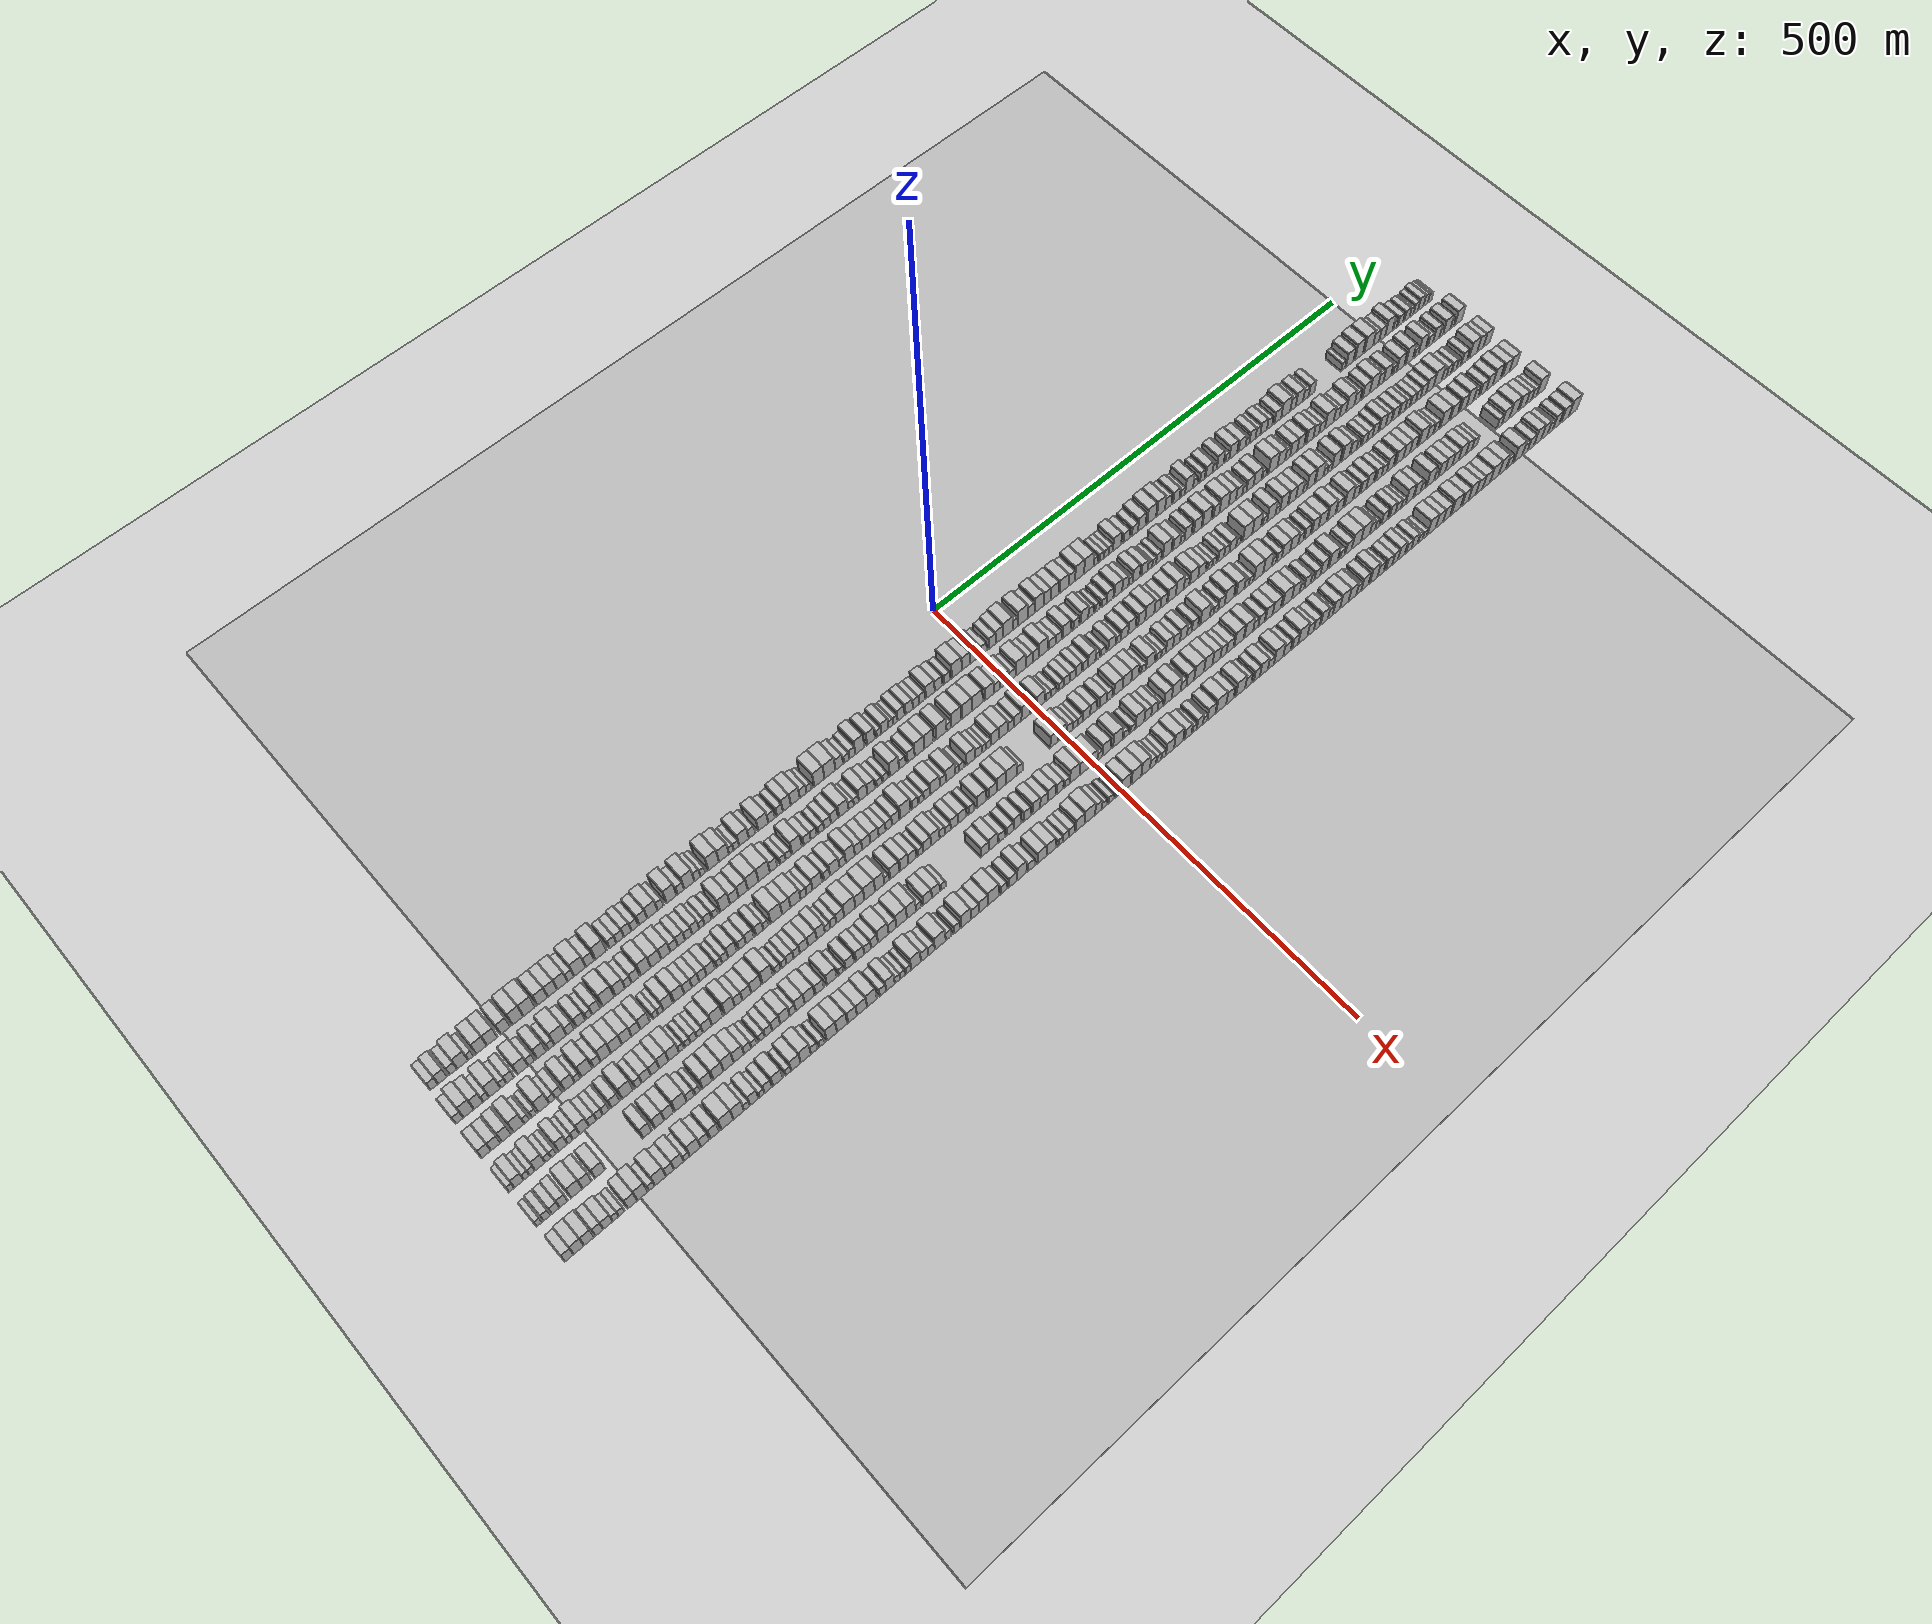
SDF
<?xml version="1.0" encoding="utf-8"?>

<sdf version="1.6">

   <world name="default">

      <gui fullscreen="0">

         <camera name="user_camera">

            <pose>-15 0 4.57585 0 0 0</pose>

            <view_controller>orbit</view_controller>

         </camera>

      </gui>

      <scene>

         <sky>

           <clouds>

             <speed>12</speed>

           </clouds>

         </sky>

         <ambient>0.4 0.4 0.4 1</ambient>

         <background>0.7 0.7 0.7 1</background>

         <shadows>1</shadows>

      </scene>

      <gravity>0 0 -9.8066</gravity>

      <magnetic_field>6e-06 2.3e-05 -4.2e-05</magnetic_field>

      <physics default="0" name="default_physics" type="ode">

         <ode>

            <solver>

               <type>quick</type>

               <iters>10</iters>

               <sor>1.0</sor>

               <use_dynamic_moi_rescaling>0</use_dynamic_moi_rescaling>

            </solver>

            <constraints>

               <cfm>0</cfm>

               <erp>0.2</erp>

               <contact_max_correcting_vel>100</contact_max_correcting_vel>

               <contact_surface_layer>0.001</contact_surface_layer>

            </constraints>

         </ode>

         <max_step_size>0.004</max_step_size>

         <real_time_factor>1</real_time_factor>

         <real_time_update_rate>250</real_time_update_rate>

      </physics>

      <light name="sun" type="directional">

         <cast_shadows>1</cast_shadows>

         <pose>0 0 10 0 0 0</pose>

         <diffuse>0.8 0.8 0.8 1</diffuse>

         <specular>0.2 0.2 0.2 1</specular>

         <attenuation>

            <range>1000</range>

            <constant>0.9</constant>

            <linear>0.01</linear>

            <quadratic>0.001</quadratic>

         </attenuation>

         <direction>-0.5 0.1 -0.9</direction>

      </light>

      <include>

         <name>ground_plane_1</name>

         <uri>model://HANNAS_ground_plane</uri>

         <pose>0 0 0  0 0 0</pose>

      </include>

      <include>

         <name>ground_plane_2</name>

         <uri>model://HANNAS_ground_plane</uri>

         <pose>100 0 0  0 0 0</pose>

      </include>

      <model name="building_1">

         <static>1</static>

         <pose frame="">50.0000 -564.4000 0 0.000000 0.000000 0.000000</pose>

         <link name="link">

            <pose frame="">0 0 7.50 0 0 0</pose>

            <collision name="collision">

               <geometry>

                  <box>

                     <size>20.0000 7.1999 15.0000</size>

                  </box>

               </geometry>

               <max_contacts>10</max_contacts>

               <surface>

                  <contact>

                     <ode/>

                  </contact>

                  <bounce/>

                  <friction>

                     <torsional>

                        <ode/>

                     </torsional>

                     <ode/>

                  </friction>

               </surface>

            </collision>

            <visual name="visual">

               <cast_shadows>0</cast_shadows>

               <geometry>

                  <box>

                     <size>20.0000 7.1999 15.0000</size>

                  </box>

               </geometry>

               <material>

                  <script>

                     <uri>model://HANNAS_wall/materials/scripts</uri>

                     <uri>model://HANNAS_wall/materials/textures</uri>

                     <name>vrc/HANNAS_wall</name>

                  </script>

               </material>

            </visual>

            <self_collide>0</self_collide>

            <enable_wind>0</enable_wind>

            <kinematic>0</kinematic>

         </link>

      </model>

      <model name="building_2">

         <static>1</static>

         <pose frame="">50.0000 -556.4400 0 0.000000 0.000000 0.000000</pose>

         <link name="link">

            <pose frame="">0 0 9.00 0 0 0</pose>

            <collision name="collision">

               <geometry>

                  <box>

                     <size>20.0000 8.7201 18.0000</size>

                  </box>

               </geometry>

               <max_contacts>10</max_contacts>

               <surface>

                  <contact>

                     <ode/>

                  </contact>

                  <bounce/>

                  <friction>

                     <torsional>

                        <ode/>

                     </torsional>

                     <ode/>

                  </friction>

               </surface>

            </collision>

            <visual name="visual">

               <cast_shadows>0</cast_shadows>

               <geometry>

                  <box>

                     <size>20.0000 8.7201 18.0000</size>

                  </box>

               </geometry>

               <material>

                  <script>

                     <uri>model://HANNAS_wall/materials/scripts</uri>

                     <uri>model://HANNAS_wall/materials/textures</uri>

                     <name>vrc/HANNAS_wall</name>

                  </script>

               </material>

            </visual>

            <self_collide>0</self_collide>

            <enable_wind>0</enable_wind>

            <kinematic>0</kinematic>

         </link>

      </model>

      <model name="building_3">

         <static>1</static>

         <pose frame="">50.0000 -546.5396 0 0.000000 0.000000 0.000000</pose>

         <link name="link">

            <pose frame="">0 0 7.50 0 0 0</pose>

            <collision name="collision">

               <geometry>

                  <box>

                     <size>20.0000 7.0806 15.0000</size>

                  </box>

               </geometry>

               <max_contacts>10</max_contacts>

               <surface>

                  <contact>

                     <ode/>

                  </contact>

                  <bounce/>

                  <friction>

                     <torsional>

                        <ode/>

                     </torsional>

                     <ode/>

                  </friction>

               </surface>

            </collision>

            <visual name="visual">

               <cast_shadows>0</cast_shadows>

               <geometry>

                  <box>

                     <size>20.0000 7.0806 15.0000</size>

                  </box>

               </geometry>

               <material>

                  <script>

                     <uri>model://HANNAS_wall/materials/scripts</uri>

                     <uri>model://HANNAS_wall/materials/textures</uri>

                     <name>vrc/HANNAS_wall</name>

                  </script>

               </material>

            </visual>

            <self_collide>0</self_collide>

            <enable_wind>0</enable_wind>

            <kinematic>0</kinematic>

         </link>

      </model>

      <model name="building_4">

         <static>1</static>

         <pose frame="">50.0000 -537.8108 0 0.000000 0.000000 0.000000</pose>

         <link name="link">

            <pose frame="">0 0 10.50 0 0 0</pose>

            <collision name="collision">

               <geometry>

                  <box>

                     <size>20.0000 10.3770 21.0000</size>

                  </box>

               </geometry>

               <max_contacts>10</max_contacts>

               <surface>

                  <contact>

                     <ode/>

                  </contact>

                  <bounce/>

                  <friction>

                     <torsional>

                        <ode/>

                     </torsional>

                     <ode/>

                  </friction>

               </surface>

            </collision>

            <visual name="visual">

               <cast_shadows>0</cast_shadows>

               <geometry>

                  <box>

                     <size>20.0000 10.3770 21.0000</size>

                  </box>

               </geometry>

               <material>

                  <script>

                     <uri>model://HANNAS_wall/materials/scripts</uri>

                     <uri>model://HANNAS_wall/materials/textures</uri>

                     <name>vrc/HANNAS_wall</name>

                  </script>

               </material>

            </visual>

            <self_collide>0</self_collide>

            <enable_wind>0</enable_wind>

            <kinematic>0</kinematic>

         </link>

      </model>

      <model name="building_5">

         <static>1</static>

         <pose frame="">50.0000 -529.9880 0 0.000000 0.000000 0.000000</pose>

         <link name="link">

            <pose frame="">0 0 6.00 0 0 0</pose>

            <collision name="collision">

               <geometry>

                  <box>

                     <size>20.0000 5.2685 12.0000</size>

                  </box>

               </geometry>

               <max_contacts>10</max_contacts>

               <surface>

                  <contact>

                     <ode/>

                  </contact>

                  <bounce/>

                  <friction>

                     <torsional>

                        <ode/>

                     </torsional>

                     <ode/>

                  </friction>

               </surface>

            </collision>

            <visual name="visual">

               <cast_shadows>0</cast_shadows>

               <geometry>

                  <box>

                     <size>20.0000 5.2685 12.0000</size>

                  </box>

               </geometry>

               <material>

                  <script>

                     <uri>model://HANNAS_wall/materials/scripts</uri>

                     <uri>model://HANNAS_wall/materials/textures</uri>

                     <name>vrc/HANNAS_wall</name>

                  </script>

               </material>

            </visual>

            <self_collide>0</self_collide>

            <enable_wind>0</enable_wind>

            <kinematic>0</kinematic>

         </link>

      </model>

      <model name="building_6">

         <static>1</static>

         <pose frame="">50.0000 -520.2095 0 0.000000 0.000000 0.000000</pose>

         <link name="link">

            <pose frame="">0 0 10.50 0 0 0</pose>

            <collision name="collision">

               <geometry>

                  <box>

                     <size>20.0000 10.2885 21.0000</size>

                  </box>

               </geometry>

               <max_contacts>10</max_contacts>

               <surface>

                  <contact>

                     <ode/>

                  </contact>

                  <bounce/>

                  <friction>

                     <torsional>

                        <ode/>

                     </torsional>

                     <ode/>

                  </friction>

               </surface>

            </collision>

            <visual name="visual">

               <cast_shadows>0</cast_shadows>

               <geometry>

                  <box>

                     <size>20.0000 10.2885 21.0000</size>

                  </box>

               </geometry>

               <material>

                  <script>

                     <uri>model://HANNAS_wall/materials/scripts</uri>

                     <uri>model://HANNAS_wall/materials/textures</uri>

                     <name>vrc/HANNAS_wall</name>

                  </script>

               </material>

            </visual>

            <self_collide>0</self_collide>

            <enable_wind>0</enable_wind>

            <kinematic>0</kinematic>

         </link>

      </model>

      <model name="building_7">

         <static>1</static>

         <pose frame="">50.0000 -509.9929 0 0.000000 0.000000 0.000000</pose>

         <link name="link">

            <pose frame="">0 0 10.50 0 0 0</pose>

            <collision name="collision">

               <geometry>

                  <box>

                     <size>20.0000 10.1447 21.0000</size>

                  </box>

               </geometry>

               <max_contacts>10</max_contacts>

               <surface>

                  <contact>

                     <ode/>

                  </contact>

                  <bounce/>

                  <friction>

                     <torsional>

                        <ode/>

                     </torsional>

                     <ode/>

                  </friction>

               </surface>

            </collision>

            <visual name="visual">

               <cast_shadows>0</cast_shadows>

               <geometry>

                  <box>

                     <size>20.0000 10.1447 21.0000</size>

                  </box>

               </geometry>

               <material>

                  <script>

                     <uri>model://HANNAS_wall/materials/scripts</uri>

                     <uri>model://HANNAS_wall/materials/textures</uri>

                     <name>vrc/HANNAS_wall</name>

                  </script>

               </material>

            </visual>

            <self_collide>0</self_collide>

            <enable_wind>0</enable_wind>

            <kinematic>0</kinematic>

         </link>

      </model>

      <model name="building_8">

         <static>1</static>

         <pose frame="">50.0000 -497.2943 0 0.000000 0.000000 0.000000</pose>

         <link name="link">

            <pose frame="">0 0 10.50 0 0 0</pose>

            <collision name="collision">

               <geometry>

                  <box>

                     <size>20.0000 9.2524 21.0000</size>

                  </box>

               </geometry>

               <max_contacts>10</max_contacts>

               <surface>

                  <contact>

                     <ode/>

                  </contact>

                  <bounce/>

                  <friction>

                     <torsional>

                        <ode/>

                     </torsional>

                     <ode/>

                  </friction>

               </surface>

            </collision>

            <visual name="visual">

               <cast_shadows>0</cast_shadows>

               <geometry>

                  <box>

                     <size>20.0000 9.2524 21.0000</size>

                  </box>

               </geometry>

               <material>

                  <script>

                     <uri>model://HANNAS_wall/materials/scripts</uri>

                     <uri>model://HANNAS_wall/materials/textures</uri>

                     <name>vrc/HANNAS_wall</name>

                  </script>

               </material>

            </visual>

            <self_collide>0</self_collide>

            <enable_wind>0</enable_wind>

            <kinematic>0</kinematic>

         </link>

      </model>

      <model name="building_9">

         <static>1</static>

         <pose frame="">50.0000 -485.4464 0 0.000000 0.000000 0.000000</pose>

         <link name="link">

            <pose frame="">0 0 12.00 0 0 0</pose>

            <collision name="collision">

               <geometry>

                  <box>

                     <size>20.0000 10.4436 24.0000</size>

                  </box>

               </geometry>

               <max_contacts>10</max_contacts>

               <surface>

                  <contact>

                     <ode/>

                  </contact>

                  <bounce/>

                  <friction>

                     <torsional>

                        <ode/>

                     </torsional>

                     <ode/>

                  </friction>

               </surface>

            </collision>

            <visual name="visual">

               <cast_shadows>0</cast_shadows>

               <geometry>

                  <box>

                     <size>20.0000 10.4436 24.0000</size>

                  </box>

               </geometry>

               <material>

                  <script>

                     <uri>model://HANNAS_wall/materials/scripts</uri>

                     <uri>model://HANNAS_wall/materials/textures</uri>

                     <name>vrc/HANNAS_wall</name>

                  </script>

               </material>

            </visual>

            <self_collide>0</self_collide>

            <enable_wind>0</enable_wind>

            <kinematic>0</kinematic>

         </link>

      </model>

      <model name="building_10">

         <static>1</static>

         <pose frame="">50.0000 -474.4987 0 0.000000 0.000000 0.000000</pose>

         <link name="link">

            <pose frame="">0 0 12.00 0 0 0</pose>

            <collision name="collision">

               <geometry>

                  <box>

                     <size>20.0000 11.4517 24.0000</size>

                  </box>

               </geometry>

               <max_contacts>10</max_contacts>

               <surface>

                  <contact>

                     <ode/>

                  </contact>

                  <bounce/>

                  <friction>

                     <torsional>

                        <ode/>

                     </torsional>

                     <ode/>

                  </friction>

               </surface>

            </collision>

            <visual name="visual">

               <cast_shadows>0</cast_shadows>

               <geometry>

                  <box>

                     <size>20.0000 11.4517 24.0000</size>

                  </box>

               </geometry>

               <material>

                  <script>

                     <uri>model://HANNAS_wall/materials/scripts</uri>

                     <uri>model://HANNAS_wall/materials/textures</uri>

                     <name>vrc/HANNAS_wall</name>

                  </script>

               </material>

            </visual>

            <self_collide>0</self_collide>

            <enable_wind>0</enable_wind>

            <kinematic>0</kinematic>

         </link>

      </model>

      <model name="building_11">

         <static>1</static>

         <pose frame="">50.0000 -461.7332 0 0.000000 0.000000 0.000000</pose>

         <link name="link">

            <pose frame="">0 0 10.50 0 0 0</pose>

            <collision name="collision">

               <geometry>

                  <box>

                     <size>20.0000 10.0792 21.0000</size>

                  </box>

               </geometry>

               <max_contacts>10</max_contacts>

               <surface>

                  <contact>

                     <ode/>

                  </contact>

                  <bounce/>

                  <friction>

                     <torsional>

                        <ode/>

                     </torsional>

                     <ode/>

                  </friction>

               </surface>

            </collision>

            <visual name="visual">

               <cast_shadows>0</cast_shadows>

               <geometry>

                  <box>

                     <size>20.0000 10.0792 21.0000</size>

                  </box>

               </geometry>

               <material>

                  <script>

                     <uri>model://HANNAS_wall/materials/scripts</uri>

                     <uri>model://HANNAS_wall/materials/textures</uri>

                     <name>vrc/HANNAS_wall</name>

                  </script>

               </material>

            </visual>

            <self_collide>0</self_collide>

            <enable_wind>0</enable_wind>

            <kinematic>0</kinematic>

         </link>

      </model>

      <model name="building_12">

         <static>1</static>

         <pose frame="">50.0000 -452.0765 0 0.000000 0.000000 0.000000</pose>

         <link name="link">

            <pose frame="">0 0 10.50 0 0 0</pose>

            <collision name="collision">

               <geometry>

                  <box>

                     <size>20.0000 9.2342 21.0000</size>

                  </box>

               </geometry>

               <max_contacts>10</max_contacts>

               <surface>

                  <contact>

                     <ode/>

                  </contact>

                  <bounce/>

                  <friction>

                     <torsional>

                        <ode/>

                     </torsional>

                     <ode/>

                  </friction>

               </surface>

            </collision>

            <visual name="visual">

               <cast_shadows>0</cast_shadows>

               <geometry>

                  <box>

                     <size>20.0000 9.2342 21.0000</size>

                  </box>

               </geometry>

               <material>

                  <script>

                     <uri>model://HANNAS_wall/materials/scripts</uri>

                     <uri>model://HANNAS_wall/materials/textures</uri>

                     <name>vrc/HANNAS_wall</name>

                  </script>

               </material>

            </visual>

            <self_collide>0</self_collide>

            <enable_wind>0</enable_wind>

            <kinematic>0</kinematic>

         </link>

      </model>

      <model name="building_13">

         <static>1</static>

         <pose frame="">50.0000 -442.5232 0 0.000000 0.000000 0.000000</pose>

         <link name="link">

            <pose frame="">0 0 10.50 0 0 0</pose>

            <collision name="collision">

               <geometry>

                  <box>

                     <size>20.0000 9.8725 21.0000</size>

                  </box>

               </geometry>

               <max_contacts>10</max_contacts>

               <surface>

                  <contact>

                     <ode/>

                  </contact>

                  <bounce/>

                  <friction>

                     <torsional>

                        <ode/>

                     </torsional>

                     <ode/>

                  </friction>

               </surface>

            </collision>

            <visual name="visual">

               <cast_shadows>0</cast_shadows>

               <geometry>

                  <box>

                     <size>20.0000 9.8725 21.0000</size>

                  </box>

               </geometry>

               <material>

                  <script>

                     <uri>model://HANNAS_wall/materials/scripts</uri>

                     <uri>model://HANNAS_wall/materials/textures</uri>

                     <name>vrc/HANNAS_wall</name>

                  </script>

               </material>

            </visual>

            <self_collide>0</self_collide>

            <enable_wind>0</enable_wind>

            <kinematic>0</kinematic>

         </link>

      </model>

      <model name="building_14">

         <static>1</static>

         <pose frame="">50.0000 -434.4015 0 0.000000 0.000000 0.000000</pose>

         <link name="link">

            <pose frame="">0 0 7.50 0 0 0</pose>

            <collision name="collision">

               <geometry>

                  <box>

                     <size>20.0000 6.3709 15.0000</size>

                  </box>

               </geometry>

               <max_contacts>10</max_contacts>

               <surface>

                  <contact>

                     <ode/>

                  </contact>

                  <bounce/>

                  <friction>

                     <torsional>

                        <ode/>

                     </torsional>

                     <ode/>

                  </friction>

               </surface>

            </collision>

            <visual name="visual">

               <cast_shadows>0</cast_shadows>

               <geometry>

                  <box>

                     <size>20.0000 6.3709 15.0000</size>

                  </box>

               </geometry>

               <material>

                  <script>

                     <uri>model://HANNAS_wall/materials/scripts</uri>

                     <uri>model://HANNAS_wall/materials/textures</uri>

                     <name>vrc/HANNAS_wall</name>

                  </script>

               </material>

            </visual>

            <self_collide>0</self_collide>

            <enable_wind>0</enable_wind>

            <kinematic>0</kinematic>

         </link>

      </model>

      <model name="building_15">

         <static>1</static>

         <pose frame="">50.0000 -425.4119 0 0.000000 0.000000 0.000000</pose>

         <link name="link">

            <pose frame="">0 0 12.00 0 0 0</pose>

            <collision name="collision">

               <geometry>

                  <box>

                     <size>20.0000 11.6083 24.0000</size>

                  </box>

               </geometry>

               <max_contacts>10</max_contacts>

               <surface>

                  <contact>

                     <ode/>

                  </contact>

                  <bounce/>

                  <friction>

                     <torsional>

                        <ode/>

                     </torsional>

                     <ode/>

                  </friction>

               </surface>

            </collision>

            <visual name="visual">

               <cast_shadows>0</cast_shadows>

               <geometry>

                  <box>

                     <size>20.0000 11.6083 24.0000</size>

                  </box>

               </geometry>

               <material>

                  <script>

                     <uri>model://HANNAS_wall/materials/scripts</uri>

                     <uri>model://HANNAS_wall/materials/textures</uri>

                     <name>vrc/HANNAS_wall</name>

                  </script>

               </material>

            </visual>

            <self_collide>0</self_collide>

            <enable_wind>0</enable_wind>

            <kinematic>0</kinematic>

         </link>

      </model>

      <model name="building_16">

         <static>1</static>

         <pose frame="">50.0000 -415.4682 0 0.000000 0.000000 0.000000</pose>

         <link name="link">

            <pose frame="">0 0 9.00 0 0 0</pose>

            <collision name="collision">

               <geometry>

                  <box>

                     <size>20.0000 8.2792 18.0000</size>

                  </box>

               </geometry>

               <max_contacts>10</max_contacts>

               <surface>

                  <contact>

                     <ode/>

                  </contact>

                  <bounce/>

                  <friction>

                     <torsional>

                        <ode/>

                     </torsional>

                     <ode/>

                  </friction>

               </surface>

            </collision>

            <visual name="visual">

               <cast_shadows>0</cast_shadows>

               <geometry>

                  <box>

                     <size>20.0000 8.2792 18.0000</size>

                  </box>

               </geometry>

               <material>

                  <script>

                     <uri>model://HANNAS_wall/materials/scripts</uri>

                     <uri>model://HANNAS_wall/materials/textures</uri>

                     <name>vrc/HANNAS_wall</name>

                  </script>

               </material>

            </visual>

            <self_collide>0</self_collide>

            <enable_wind>0</enable_wind>

            <kinematic>0</kinematic>

         </link>

      </model>

      <model name="building_17">

         <static>1</static>

         <pose frame="">50.0000 -404.8006 0 0.000000 0.000000 0.000000</pose>

         <link name="link">

            <pose frame="">0 0 12.00 0 0 0</pose>

            <collision name="collision">

               <geometry>

                  <box>

                     <size>20.0000 11.0559 24.0000</size>

                  </box>

               </geometry>

               <max_contacts>10</max_contacts>

               <surface>

                  <contact>

                     <ode/>

                  </contact>

                  <bounce/>

                  <friction>

                     <torsional>

                        <ode/>

                     </torsional>

                     <ode/>

                  </friction>

               </surface>

            </collision>

            <visual name="visual">

               <cast_shadows>0</cast_shadows>

               <geometry>

                  <box>

                     <size>20.0000 11.0559 24.0000</size>

                  </box>

               </geometry>

               <material>

                  <script>

                     <uri>model://HANNAS_wall/materials/scripts</uri>

                     <uri>model://HANNAS_wall/materials/textures</uri>

                     <name>vrc/HANNAS_wall</name>

                  </script>

               </material>

            </visual>

            <self_collide>0</self_collide>

            <enable_wind>0</enable_wind>

            <kinematic>0</kinematic>

         </link>

      </model>

      <model name="building_18">

         <static>1</static>

         <pose frame="">50.0000 -392.8752 0 0.000000 0.000000 0.000000</pose>

         <link name="link">

            <pose frame="">0 0 7.50 0 0 0</pose>

            <collision name="collision">

               <geometry>

                  <box>

                     <size>20.0000 6.7949 15.0000</size>

                  </box>

               </geometry>

               <max_contacts>10</max_contacts>

               <surface>

                  <contact>

                     <ode/>

                  </contact>

                  <bounce/>

                  <friction>

                     <torsional>

                        <ode/>

                     </torsional>

                     <ode/>

                  </friction>

               </surface>

            </collision>

            <visual name="visual">

               <cast_shadows>0</cast_shadows>

               <geometry>

                  <box>

                     <size>20.0000 6.7949 15.0000</size>

                  </box>

               </geometry>

               <material>

                  <script>

                     <uri>model://HANNAS_wall/materials/scripts</uri>

                     <uri>model://HANNAS_wall/materials/textures</uri>

                     <name>vrc/HANNAS_wall</name>

                  </script>

               </material>

            </visual>

            <self_collide>0</self_collide>

            <enable_wind>0</enable_wind>

            <kinematic>0</kinematic>

         </link>

      </model>

      <model name="building_19">

         <static>1</static>

         <pose frame="">50.0000 -385.7423 0 0.000000 0.000000 0.000000</pose>

         <link name="link">

            <pose frame="">0 0 7.50 0 0 0</pose>

            <collision name="collision">

               <geometry>

                  <box>

                     <size>20.0000 7.4709 15.0000</size>

                  </box>

               </geometry>

               <max_contacts>10</max_contacts>

               <surface>

                  <contact>

                     <ode/>

                  </contact>

                  <bounce/>

                  <friction>

                     <torsional>

                        <ode/>

                     </torsional>

                     <ode/>

                  </friction>

               </surface>

            </collision>

            <visual name="visual">

               <cast_shadows>0</cast_shadows>

               <geometry>

                  <box>

                     <size>20.0000 7.4709 15.0000</size>

                  </box>

               </geometry>

               <material>

                  <script>

                     <uri>model://HANNAS_wall/materials/scripts</uri>

                     <uri>model://HANNAS_wall/materials/textures</uri>

                     <name>vrc/HANNAS_wall</name>

                  </script>

               </material>

            </visual>

            <self_collide>0</self_collide>

            <enable_wind>0</enable_wind>

            <kinematic>0</kinematic>

         </link>

      </model>

      <model name="building_20">

         <static>1</static>

         <pose frame="">50.0000 -378.2463 0 0.000000 0.000000 0.000000</pose>

         <link name="link">

            <pose frame="">0 0 9.00 0 0 0</pose>

            <collision name="collision">

               <geometry>

                  <box>

                     <size>20.0000 7.5212 18.0000</size>

                  </box>

               </geometry>

               <max_contacts>10</max_contacts>

               <surface>

                  <contact>

                     <ode/>

                  </contact>

                  <bounce/>

                  <friction>

                     <torsional>

                        <ode/>

                     </torsional>

                     <ode/>

                  </friction>

               </surface>

            </collision>

            <visual name="visual">

               <cast_shadows>0</cast_shadows>

               <geometry>

                  <box>

                     <size>20.0000 7.5212 18.0000</size>

                  </box>

               </geometry>

               <material>

                  <script>

                     <uri>model://HANNAS_wall/materials/scripts</uri>

                     <uri>model://HANNAS_wall/materials/textures</uri>

                     <name>vrc/HANNAS_wall</name>

                  </script>

               </material>

            </visual>

            <self_collide>0</self_collide>

            <enable_wind>0</enable_wind>

            <kinematic>0</kinematic>

         </link>

      </model>

      <model name="building_21">

         <static>1</static>

         <pose frame="">50.0000 -371.0788 0 0.000000 0.000000 0.000000</pose>

         <link name="link">

            <pose frame="">0 0 7.50 0 0 0</pose>

            <collision name="collision">

               <geometry>

                  <box>

                     <size>20.0000 6.8137 15.0000</size>

                  </box>

               </geometry>

               <max_contacts>10</max_contacts>

               <surface>

                  <contact>

                     <ode/>

                  </contact>

                  <bounce/>

                  <friction>

                     <torsional>

                        <ode/>

                     </torsional>

                     <ode/>

                  </friction>

               </surface>

            </collision>

            <visual name="visual">

               <cast_shadows>0</cast_shadows>

               <geometry>

                  <box>

                     <size>20.0000 6.8137 15.0000</size>

                  </box>

               </geometry>

               <material>

                  <script>

                     <uri>model://HANNAS_wall/materials/scripts</uri>

                     <uri>model://HANNAS_wall/materials/textures</uri>

                     <name>vrc/HANNAS_wall</name>

                  </script>

               </material>

            </visual>

            <self_collide>0</self_collide>

            <enable_wind>0</enable_wind>

            <kinematic>0</kinematic>

         </link>

      </model>

      <model name="building_22">

         <static>1</static>

         <pose frame="">50.0000 -362.6278 0 0.000000 0.000000 0.000000</pose>

         <link name="link">

            <pose frame="">0 0 9.00 0 0 0</pose>

            <collision name="collision">

               <geometry>

                  <box>

                     <size>20.0000 8.0885 18.0000</size>

                  </box>

               </geometry>

               <max_contacts>10</max_contacts>

               <surface>

                  <contact>

                     <ode/>

                  </contact>

                  <bounce/>

                  <friction>

                     <torsional>

                        <ode/>

                     </torsional>

                     <ode/>

                  </friction>

               </surface>

            </collision>

            <visual name="visual">

               <cast_shadows>0</cast_shadows>

               <geometry>

                  <box>

                     <size>20.0000 8.0885 18.0000</size>

                  </box>

               </geometry>

               <material>

                  <script>

                     <uri>model://HANNAS_wall/materials/scripts</uri>

                     <uri>model://HANNAS_wall/materials/textures</uri>

                     <name>vrc/HANNAS_wall</name>

                  </script>

               </material>

            </visual>

            <self_collide>0</self_collide>

            <enable_wind>0</enable_wind>

            <kinematic>0</kinematic>

         </link>

      </model>

      <model name="building_23">

         <static>1</static>

         <pose frame="">50.0000 -353.4307 0 0.000000 0.000000 0.000000</pose>

         <link name="link">

            <pose frame="">0 0 10.50 0 0 0</pose>

            <collision name="collision">

               <geometry>

                  <box>

                     <size>20.0000 10.3057 21.0000</size>

                  </box>

               </geometry>

               <max_contacts>10</max_contacts>

               <surface>

                  <contact>

                     <ode/>

                  </contact>

                  <bounce/>

                  <friction>

                     <torsional>

                        <ode/>

                     </torsional>

                     <ode/>

                  </friction>

               </surface>

            </collision>

            <visual name="visual">

               <cast_shadows>0</cast_shadows>

               <geometry>

                  <box>

                     <size>20.0000 10.3057 21.0000</size>

                  </box>

               </geometry>

               <material>

                  <script>

                     <uri>model://HANNAS_wall/materials/scripts</uri>

                     <uri>model://HANNAS_wall/materials/textures</uri>

                     <name>vrc/HANNAS_wall</name>

                  </script>

               </material>

            </visual>

            <self_collide>0</self_collide>

            <enable_wind>0</enable_wind>

            <kinematic>0</kinematic>

         </link>

      </model>

      <model name="building_24">

         <static>1</static>

         <pose frame="">50.0000 -345.2115 0 0.000000 0.000000 0.000000</pose>

         <link name="link">

            <pose frame="">0 0 7.50 0 0 0</pose>

            <collision name="collision">

               <geometry>

                  <box>

                     <size>20.0000 6.1326 15.0000</size>

                  </box>

               </geometry>

               <max_contacts>10</max_contacts>

               <surface>

                  <contact>

                     <ode/>

                  </contact>

                  <bounce/>

                  <friction>

                     <torsional>

                        <ode/>

                     </torsional>

                     <ode/>

                  </friction>

               </surface>

            </collision>

            <visual name="visual">

               <cast_shadows>0</cast_shadows>

               <geometry>

                  <box>

                     <size>20.0000 6.1326 15.0000</size>

                  </box>

               </geometry>

               <material>

                  <script>

                     <uri>model://HANNAS_wall/materials/scripts</uri>

                     <uri>model://HANNAS_wall/materials/textures</uri>

                     <name>vrc/HANNAS_wall</name>

                  </script>

               </material>

            </visual>

            <self_collide>0</self_collide>

            <enable_wind>0</enable_wind>

            <kinematic>0</kinematic>

         </link>

      </model>

      <model name="building_25">

         <static>1</static>

         <pose frame="">50.0000 -334.0674 0 0.000000 0.000000 0.000000</pose>

         <link name="link">

            <pose frame="">0 0 12.00 0 0 0</pose>

            <collision name="collision">

               <geometry>

                  <box>

                     <size>20.0000 10.1557 24.0000</size>

                  </box>

               </geometry>

               <max_contacts>10</max_contacts>

               <surface>

                  <contact>

                     <ode/>

                  </contact>

                  <bounce/>

                  <friction>

                     <torsional>

                        <ode/>

                     </torsional>

                     <ode/>

                  </friction>

               </surface>

            </collision>

            <visual name="visual">

               <cast_shadows>0</cast_shadows>

               <geometry>

                  <box>

                     <size>20.0000 10.1557 24.0000</size>

                  </box>

               </geometry>

               <material>

                  <script>

                     <uri>model://HANNAS_wall/materials/scripts</uri>

                     <uri>model://HANNAS_wall/materials/textures</uri>

                     <name>vrc/HANNAS_wall</name>

                  </script>

               </material>

            </visual>

            <self_collide>0</self_collide>

            <enable_wind>0</enable_wind>

            <kinematic>0</kinematic>

         </link>

      </model>

      <model name="building_26">

         <static>1</static>

         <pose frame="">50.0000 -324.6339 0 0.000000 0.000000 0.000000</pose>

         <link name="link">

            <pose frame="">0 0 7.50 0 0 0</pose>

            <collision name="collision">

               <geometry>

                  <box>

                     <size>20.0000 6.7114 15.0000</size>

                  </box>

               </geometry>

               <max_contacts>10</max_contacts>

               <surface>

                  <contact>

                     <ode/>

                  </contact>

                  <bounce/>

                  <friction>

                     <torsional>

                        <ode/>

                     </torsional>

                     <ode/>

                  </friction>

               </surface>

            </collision>

            <visual name="visual">

               <cast_shadows>0</cast_shadows>

               <geometry>

                  <box>

                     <size>20.0000 6.7114 15.0000</size>

                  </box>

               </geometry>

               <material>

                  <script>

                     <uri>model://HANNAS_wall/materials/scripts</uri>

                     <uri>model://HANNAS_wall/materials/textures</uri>

                     <name>vrc/HANNAS_wall</name>

                  </script>

               </material>

            </visual>

            <self_collide>0</self_collide>

            <enable_wind>0</enable_wind>

            <kinematic>0</kinematic>

         </link>

      </model>

      <model name="building_27">

         <static>1</static>

         <pose frame="">50.0000 -315.9791 0 0.000000 0.000000 0.000000</pose>

         <link name="link">

            <pose frame="">0 0 12.00 0 0 0</pose>

            <collision name="collision">

               <geometry>

                  <box>

                     <size>20.0000 10.5981 24.0000</size>

                  </box>

               </geometry>

               <max_contacts>10</max_contacts>

               <surface>

                  <contact>

                     <ode/>

                  </contact>

                  <bounce/>

                  <friction>

                     <torsional>

                        <ode/>

                     </torsional>

                     <ode/>

                  </friction>

               </surface>

            </collision>

            <visual name="visual">

               <cast_shadows>0</cast_shadows>

               <geometry>

                  <box>

                     <size>20.0000 10.5981 24.0000</size>

                  </box>

               </geometry>

               <material>

                  <script>

                     <uri>model://HANNAS_wall/materials/scripts</uri>

                     <uri>model://HANNAS_wall/materials/textures</uri>

                     <name>vrc/HANNAS_wall</name>

                  </script>

               </material>

            </visual>

            <self_collide>0</self_collide>

            <enable_wind>0</enable_wind>

            <kinematic>0</kinematic>

         </link>

      </model>

      <model name="building_28">

         <static>1</static>

         <pose frame="">50.0000 -307.6204 0 0.000000 0.000000 0.000000</pose>

         <link name="link">

            <pose frame="">0 0 7.50 0 0 0</pose>

            <collision name="collision">

               <geometry>

                  <box>

                     <size>20.0000 6.1194 15.0000</size>

                  </box>

               </geometry>

               <max_contacts>10</max_contacts>

               <surface>

                  <contact>

                     <ode/>

                  </contact>

                  <bounce/>

                  <friction>

                     <torsional>

                        <ode/>

                     </torsional>

                     <ode/>

                  </friction>

               </surface>

            </collision>

            <visual name="visual">

               <cast_shadows>0</cast_shadows>

               <geometry>

                  <box>

                     <size>20.0000 6.1194 15.0000</size>

                  </box>

               </geometry>

               <material>

                  <script>

                     <uri>model://HANNAS_wall/materials/scripts</uri>

                     <uri>model://HANNAS_wall/materials/textures</uri>

                     <name>vrc/HANNAS_wall</name>

                  </script>

               </material>

            </visual>

            <self_collide>0</self_collide>

            <enable_wind>0</enable_wind>

            <kinematic>0</kinematic>

         </link>

      </model>

      <model name="building_29">

         <static>1</static>

         <pose frame="">50.0000 -302.0120 0 0.000000 0.000000 0.000000</pose>

         <link name="link">

            <pose frame="">0 0 6.00 0 0 0</pose>

            <collision name="collision">

               <geometry>

                  <box>

                     <size>20.0000 5.0974 12.0000</size>

                  </box>

               </geometry>

               <max_contacts>10</max_contacts>

               <surface>

                  <contact>

                     <ode/>

                  </contact>

                  <bounce/>

                  <friction>

                     <torsional>

                        <ode/>

                     </torsional>

                     <ode/>

                  </friction>

               </surface>

            </collision>

            <visual name="visual">

               <cast_shadows>0</cast_shadows>

               <geometry>

                  <box>

                     <size>20.0000 5.0974 12.0000</size>

                  </box>

               </geometry>

               <material>

                  <script>

                     <uri>model://HANNAS_wall/materials/scripts</uri>

                     <uri>model://HANNAS_wall/materials/textures</uri>

                     <name>vrc/HANNAS_wall</name>

                  </script>

               </material>

            </visual>

            <self_collide>0</self_collide>

            <enable_wind>0</enable_wind>

            <kinematic>0</kinematic>

         </link>

      </model>

      <model name="building_30">

         <static>1</static>

         <pose frame="">50.0000 -290.9785 0 0.000000 0.000000 0.000000</pose>

         <link name="link">

            <pose frame="">0 0 12.00 0 0 0</pose>

            <collision name="collision">

               <geometry>

                  <box>

                     <size>20.0000 10.9697 24.0000</size>

                  </box>

               </geometry>

               <max_contacts>10</max_contacts>

               <surface>

                  <contact>

                     <ode/>

                  </contact>

                  <bounce/>

                  <friction>

                     <torsional>

                        <ode/>

                     </torsional>

                     <ode/>

                  </friction>

               </surface>

            </collision>

            <visual name="visual">

               <cast_shadows>0</cast_shadows>

               <geometry>

                  <box>

                     <size>20.0000 10.9697 24.0000</size>

                  </box>

               </geometry>

               <material>

                  <script>

                     <uri>model://HANNAS_wall/materials/scripts</uri>

                     <uri>model://HANNAS_wall/materials/textures</uri>

                     <name>vrc/HANNAS_wall</name>

                  </script>

               </material>

            </visual>

            <self_collide>0</self_collide>

            <enable_wind>0</enable_wind>

            <kinematic>0</kinematic>

         </link>

      </model>

      <model name="building_31">

         <static>1</static>

         <pose frame="">50.0000 -280.3416 0 0.000000 0.000000 0.000000</pose>

         <link name="link">

            <pose frame="">0 0 10.50 0 0 0</pose>

            <collision name="collision">

               <geometry>

                  <box>

                     <size>20.0000 10.3041 21.0000</size>

                  </box>

               </geometry>

               <max_contacts>10</max_contacts>

               <surface>

                  <contact>

                     <ode/>

                  </contact>

                  <bounce/>

                  <friction>

                     <torsional>

                        <ode/>

                     </torsional>

                     <ode/>

                  </friction>

               </surface>

            </collision>

            <visual name="visual">

               <cast_shadows>0</cast_shadows>

               <geometry>

                  <box>

                     <size>20.0000 10.3041 21.0000</size>

                  </box>

               </geometry>

               <material>

                  <script>

                     <uri>model://HANNAS_wall/materials/scripts</uri>

                     <uri>model://HANNAS_wall/materials/textures</uri>

                     <name>vrc/HANNAS_wall</name>

                  </script>

               </material>

            </visual>

            <self_collide>0</self_collide>

            <enable_wind>0</enable_wind>

            <kinematic>0</kinematic>

         </link>

      </model>

      <model name="building_32">

         <static>1</static>

         <pose frame="">50.0000 -272.7746 0 0.000000 0.000000 0.000000</pose>

         <link name="link">

            <pose frame="">0 0 6.00 0 0 0</pose>

            <collision name="collision">

               <geometry>

                  <box>

                     <size>20.0000 4.8300 12.0000</size>

                  </box>

               </geometry>

               <max_contacts>10</max_contacts>

               <surface>

                  <contact>

                     <ode/>

                  </contact>

                  <bounce/>

                  <friction>

                     <torsional>

                        <ode/>

                     </torsional>

                     <ode/>

                  </friction>

               </surface>

            </collision>

            <visual name="visual">

               <cast_shadows>0</cast_shadows>

               <geometry>

                  <box>

                     <size>20.0000 4.8300 12.0000</size>

                  </box>

               </geometry>

               <material>

                  <script>

                     <uri>model://HANNAS_wall/materials/scripts</uri>

                     <uri>model://HANNAS_wall/materials/textures</uri>

                     <name>vrc/HANNAS_wall</name>

                  </script>

               </material>

            </visual>

            <self_collide>0</self_collide>

            <enable_wind>0</enable_wind>

            <kinematic>0</kinematic>

         </link>

      </model>

      <model name="building_33">

         <static>1</static>

         <pose frame="">50.0000 -267.4873 0 0.000000 0.000000 0.000000</pose>

         <link name="link">

            <pose frame="">0 0 6.00 0 0 0</pose>

            <collision name="collision">

               <geometry>

                  <box>

                     <size>20.0000 5.7445 12.0000</size>

                  </box>

               </geometry>

               <max_contacts>10</max_contacts>

               <surface>

                  <contact>

                     <ode/>

                  </contact>

                  <bounce/>

                  <friction>

                     <torsional>

                        <ode/>

                     </torsional>

                     <ode/>

                  </friction>

               </surface>

            </collision>

            <visual name="visual">

               <cast_shadows>0</cast_shadows>

               <geometry>

                  <box>

                     <size>20.0000 5.7445 12.0000</size>

                  </box>

               </geometry>

               <material>

                  <script>

                     <uri>model://HANNAS_wall/materials/scripts</uri>

                     <uri>model://HANNAS_wall/materials/textures</uri>

                     <name>vrc/HANNAS_wall</name>

                  </script>

               </material>

            </visual>

            <self_collide>0</self_collide>

            <enable_wind>0</enable_wind>

            <kinematic>0</kinematic>

         </link>

      </model>

      <model name="building_34">

         <static>1</static>

         <pose frame="">50.0000 -259.5677 0 0.000000 0.000000 0.000000</pose>

         <link name="link">

            <pose frame="">0 0 10.50 0 0 0</pose>

            <collision name="collision">

               <geometry>

                  <box>

                     <size>20.0000 10.0947 21.0000</size>

                  </box>

               </geometry>

               <max_contacts>10</max_contacts>

               <surface>

                  <contact>

                     <ode/>

                  </contact>

                  <bounce/>

                  <friction>

                     <torsional>

                        <ode/>

                     </torsional>

                     <ode/>

                  </friction>

               </surface>

            </collision>

            <visual name="visual">

               <cast_shadows>0</cast_shadows>

               <geometry>

                  <box>

                     <size>20.0000 10.0947 21.0000</size>

                  </box>

               </geometry>

               <material>

                  <script>

                     <uri>model://HANNAS_wall/materials/scripts</uri>

                     <uri>model://HANNAS_wall/materials/textures</uri>

                     <name>vrc/HANNAS_wall</name>

                  </script>

               </material>

            </visual>

            <self_collide>0</self_collide>

            <enable_wind>0</enable_wind>

            <kinematic>0</kinematic>

         </link>

      </model>

      <model name="building_35">

         <static>1</static>

         <pose frame="">50.0000 -251.0583 0 0.000000 0.000000 0.000000</pose>

         <link name="link">

            <pose frame="">0 0 7.50 0 0 0</pose>

            <collision name="collision">

               <geometry>

                  <box>

                     <size>20.0000 6.9240 15.0000</size>

                  </box>

               </geometry>

               <max_contacts>10</max_contacts>

               <surface>

                  <contact>

                     <ode/>

                  </contact>

                  <bounce/>

                  <friction>

                     <torsional>

                        <ode/>

                     </torsional>

                     <ode/>

                  </friction>

               </surface>

            </collision>

            <visual name="visual">

               <cast_shadows>0</cast_shadows>

               <geometry>

                  <box>

                     <size>20.0000 6.9240 15.0000</size>

                  </box>

               </geometry>

               <material>

                  <script>

                     <uri>model://HANNAS_wall/materials/scripts</uri>

                     <uri>model://HANNAS_wall/materials/textures</uri>

                     <name>vrc/HANNAS_wall</name>

                  </script>

               </material>

            </visual>

            <self_collide>0</self_collide>

            <enable_wind>0</enable_wind>

            <kinematic>0</kinematic>

         </link>

      </model>

      <model name="building_36">

         <static>1</static>

         <pose frame="">50.0000 -239.3828 0 0.000000 0.000000 0.000000</pose>

         <link name="link">

            <pose frame="">0 0 10.50 0 0 0</pose>

            <collision name="collision">

               <geometry>

                  <box>

                     <size>20.0000 10.4271 21.0000</size>

                  </box>

               </geometry>

               <max_contacts>10</max_contacts>

               <surface>

                  <contact>

                     <ode/>

                  </contact>

                  <bounce/>

                  <friction>

                     <torsional>

                        <ode/>

                     </torsional>

                     <ode/>

                  </friction>

               </surface>

            </collision>

            <visual name="visual">

               <cast_shadows>0</cast_shadows>

               <geometry>

                  <box>

                     <size>20.0000 10.4271 21.0000</size>

                  </box>

               </geometry>

               <material>

                  <script>

                     <uri>model://HANNAS_wall/materials/scripts</uri>

                     <uri>model://HANNAS_wall/materials/textures</uri>

                     <name>vrc/HANNAS_wall</name>

                  </script>

               </material>

            </visual>

            <self_collide>0</self_collide>

            <enable_wind>0</enable_wind>

            <kinematic>0</kinematic>

         </link>

      </model>

      <model name="building_37">

         <static>1</static>

         <pose frame="">50.0000 -230.6563 0 0.000000 0.000000 0.000000</pose>

         <link name="link">

            <pose frame="">0 0 7.50 0 0 0</pose>

            <collision name="collision">

               <geometry>

                  <box>

                     <size>20.0000 7.0258 15.0000</size>

                  </box>

               </geometry>

               <max_contacts>10</max_contacts>

               <surface>

                  <contact>

                     <ode/>

                  </contact>

                  <bounce/>

                  <friction>

                     <torsional>

                        <ode/>

                     </torsional>

                     <ode/>

                  </friction>

               </surface>

            </collision>

            <visual name="visual">

               <cast_shadows>0</cast_shadows>

               <geometry>

                  <box>

                     <size>20.0000 7.0258 15.0000</size>

                  </box>

               </geometry>

               <material>

                  <script>

                     <uri>model://HANNAS_wall/materials/scripts</uri>

                     <uri>model://HANNAS_wall/materials/textures</uri>

                     <name>vrc/HANNAS_wall</name>

                  </script>

               </material>

            </visual>

            <self_collide>0</self_collide>

            <enable_wind>0</enable_wind>

            <kinematic>0</kinematic>

         </link>

      </model>

      <model name="building_38">

         <static>1</static>

         <pose frame="">50.0000 -221.9402 0 0.000000 0.000000 0.000000</pose>

         <link name="link">

            <pose frame="">0 0 7.50 0 0 0</pose>

            <collision name="collision">

               <geometry>

                  <box>

                     <size>20.0000 6.4063 15.0000</size>

                  </box>

               </geometry>

               <max_contacts>10</max_contacts>

               <surface>

                  <contact>

                     <ode/>

                  </contact>

                  <bounce/>

                  <friction>

                     <torsional>

                        <ode/>

                     </torsional>

                     <ode/>

                  </friction>

               </surface>

            </collision>

            <visual name="visual">

               <cast_shadows>0</cast_shadows>

               <geometry>

                  <box>

                     <size>20.0000 6.4063 15.0000</size>

                  </box>

               </geometry>

               <material>

                  <script>

                     <uri>model://HANNAS_wall/materials/scripts</uri>

                     <uri>model://HANNAS_wall/materials/textures</uri>

                     <name>vrc/HANNAS_wall</name>

                  </script>

               </material>

            </visual>

            <self_collide>0</self_collide>

            <enable_wind>0</enable_wind>

            <kinematic>0</kinematic>

         </link>

      </model>

      <model name="building_39">

         <static>1</static>

         <pose frame="">50.0000 -214.5064 0 0.000000 0.000000 0.000000</pose>

         <link name="link">

            <pose frame="">0 0 10.50 0 0 0</pose>

            <collision name="collision">

               <geometry>

                  <box>

                     <size>20.0000 8.4614 21.0000</size>

                  </box>

               </geometry>

               <max_contacts>10</max_contacts>

               <surface>

                  <contact>

                     <ode/>

                  </contact>

                  <bounce/>

                  <friction>

                     <torsional>

                        <ode/>

                     </torsional>

                     <ode/>

                  </friction>

               </surface>

            </collision>

            <visual name="visual">

               <cast_shadows>0</cast_shadows>

               <geometry>

                  <box>

                     <size>20.0000 8.4614 21.0000</size>

                  </box>

               </geometry>

               <material>

                  <script>

                     <uri>model://HANNAS_wall/materials/scripts</uri>

                     <uri>model://HANNAS_wall/materials/textures</uri>

                     <name>vrc/HANNAS_wall</name>

                  </script>

               </material>

            </visual>

            <self_collide>0</self_collide>

            <enable_wind>0</enable_wind>

            <kinematic>0</kinematic>

         </link>

      </model>

      <model name="building_40">

         <static>1</static>

         <pose frame="">50.0000 -205.4819 0 0.000000 0.000000 0.000000</pose>

         <link name="link">

            <pose frame="">0 0 10.50 0 0 0</pose>

            <collision name="collision">

               <geometry>

                  <box>

                     <size>20.0000 9.5876 21.0000</size>

                  </box>

               </geometry>

               <max_contacts>10</max_contacts>

               <surface>

                  <contact>

                     <ode/>

                  </contact>

                  <bounce/>

                  <friction>

                     <torsional>

                        <ode/>

                     </torsional>

                     <ode/>

                  </friction>

               </surface>

            </collision>

            <visual name="visual">

               <cast_shadows>0</cast_shadows>

               <geometry>

                  <box>

                     <size>20.0000 9.5876 21.0000</size>

                  </box>

               </geometry>

               <material>

                  <script>

                     <uri>model://HANNAS_wall/materials/scripts</uri>

                     <uri>model://HANNAS_wall/materials/textures</uri>

                     <name>vrc/HANNAS_wall</name>

                  </script>

               </material>

            </visual>

            <self_collide>0</self_collide>

            <enable_wind>0</enable_wind>

            <kinematic>0</kinematic>

         </link>

      </model>

      <model name="building_41">

         <static>1</static>

         <pose frame="">50.0000 -197.0748 0 0.000000 0.000000 0.000000</pose>

         <link name="link">

            <pose frame="">0 0 7.50 0 0 0</pose>

            <collision name="collision">

               <geometry>

                  <box>

                     <size>20.0000 7.2265 15.0000</size>

                  </box>

               </geometry>

               <max_contacts>10</max_contacts>

               <surface>

                  <contact>

                     <ode/>

                  </contact>

                  <bounce/>

                  <friction>

                     <torsional>

                        <ode/>

                     </torsional>

                     <ode/>

                  </friction>

               </surface>

            </collision>

            <visual name="visual">

               <cast_shadows>0</cast_shadows>

               <geometry>

                  <box>

                     <size>20.0000 7.2265 15.0000</size>

                  </box>

               </geometry>

               <material>

                  <script>

                     <uri>model://HANNAS_wall/materials/scripts</uri>

                     <uri>model://HANNAS_wall/materials/textures</uri>

                     <name>vrc/HANNAS_wall</name>

                  </script>

               </material>

            </visual>

            <self_collide>0</self_collide>

            <enable_wind>0</enable_wind>

            <kinematic>0</kinematic>

         </link>

      </model>

      <model name="building_42">

         <static>1</static>

         <pose frame="">50.0000 -190.9008 0 0.000000 0.000000 0.000000</pose>

         <link name="link">

            <pose frame="">0 0 6.00 0 0 0</pose>

            <collision name="collision">

               <geometry>

                  <box>

                     <size>20.0000 5.1214 12.0000</size>

                  </box>

               </geometry>

               <max_contacts>10</max_contacts>

               <surface>

                  <contact>

                     <ode/>

                  </contact>

                  <bounce/>

                  <friction>

                     <torsional>

                        <ode/>

                     </torsional>

                     <ode/>

                  </friction>

               </surface>

            </collision>

            <visual name="visual">

               <cast_shadows>0</cast_shadows>

               <geometry>

                  <box>

                     <size>20.0000 5.1214 12.0000</size>

                  </box>

               </geometry>

               <material>

                  <script>

                     <uri>model://HANNAS_wall/materials/scripts</uri>

                     <uri>model://HANNAS_wall/materials/textures</uri>

                     <name>vrc/HANNAS_wall</name>

                  </script>

               </material>

            </visual>

            <self_collide>0</self_collide>

            <enable_wind>0</enable_wind>

            <kinematic>0</kinematic>

         </link>

      </model>

      <model name="building_43">

         <static>1</static>

         <pose frame="">50.0000 -179.7802 0 0.000000 0.000000 0.000000</pose>

         <link name="link">

            <pose frame="">0 0 12.00 0 0 0</pose>

            <collision name="collision">

               <geometry>

                  <box>

                     <size>20.0000 11.1198 24.0000</size>

                  </box>

               </geometry>

               <max_contacts>10</max_contacts>

               <surface>

                  <contact>

                     <ode/>

                  </contact>

                  <bounce/>

                  <friction>

                     <torsional>

                        <ode/>

                     </torsional>

                     <ode/>

                  </friction>

               </surface>

            </collision>

            <visual name="visual">

               <cast_shadows>0</cast_shadows>

               <geometry>

                  <box>

                     <size>20.0000 11.1198 24.0000</size>

                  </box>

               </geometry>

               <material>

                  <script>

                     <uri>model://HANNAS_wall/materials/scripts</uri>

                     <uri>model://HANNAS_wall/materials/textures</uri>

                     <name>vrc/HANNAS_wall</name>

                  </script>

               </material>

            </visual>

            <self_collide>0</self_collide>

            <enable_wind>0</enable_wind>

            <kinematic>0</kinematic>

         </link>

      </model>

      <model name="building_44">

         <static>1</static>

         <pose frame="">50.0000 -168.2650 0 0.000000 0.000000 0.000000</pose>

         <link name="link">

            <pose frame="">0 0 12.00 0 0 0</pose>

            <collision name="collision">

               <geometry>

                  <box>

                     <size>20.0000 11.9106 24.0000</size>

                  </box>

               </geometry>

               <max_contacts>10</max_contacts>

               <surface>

                  <contact>

                     <ode/>

                  </contact>

                  <bounce/>

                  <friction>

                     <torsional>

                        <ode/>

                     </torsional>

                     <ode/>

                  </friction>

               </surface>

            </collision>

            <visual name="visual">

               <cast_shadows>0</cast_shadows>

               <geometry>

                  <box>

                     <size>20.0000 11.9106 24.0000</size>

                  </box>

               </geometry>

               <material>

                  <script>

                     <uri>model://HANNAS_wall/materials/scripts</uri>

                     <uri>model://HANNAS_wall/materials/textures</uri>

                     <name>vrc/HANNAS_wall</name>

                  </script>

               </material>

            </visual>

            <self_collide>0</self_collide>

            <enable_wind>0</enable_wind>

            <kinematic>0</kinematic>

         </link>

      </model>

      <model name="building_45">

         <static>1</static>

         <pose frame="">50.0000 -158.2272 0 0.000000 0.000000 0.000000</pose>

         <link name="link">

            <pose frame="">0 0 9.00 0 0 0</pose>

            <collision name="collision">

               <geometry>

                  <box>

                     <size>20.0000 8.1649 18.0000</size>

                  </box>

               </geometry>

               <max_contacts>10</max_contacts>

               <surface>

                  <contact>

                     <ode/>

                  </contact>

                  <bounce/>

                  <friction>

                     <torsional>

                        <ode/>

                     </torsional>

                     <ode/>

                  </friction>

               </surface>

            </collision>

            <visual name="visual">

               <cast_shadows>0</cast_shadows>

               <geometry>

                  <box>

                     <size>20.0000 8.1649 18.0000</size>

                  </box>

               </geometry>

               <material>

                  <script>

                     <uri>model://HANNAS_wall/materials/scripts</uri>

                     <uri>model://HANNAS_wall/materials/textures</uri>

                     <name>vrc/HANNAS_wall</name>

                  </script>

               </material>

            </visual>

            <self_collide>0</self_collide>

            <enable_wind>0</enable_wind>

            <kinematic>0</kinematic>

         </link>

      </model>

      <model name="building_46">

         <static>1</static>

         <pose frame="">50.0000 -150.1552 0 0.000000 0.000000 0.000000</pose>

         <link name="link">

            <pose frame="">0 0 6.00 0 0 0</pose>

            <collision name="collision">

               <geometry>

                  <box>

                     <size>20.0000 5.9791 12.0000</size>

                  </box>

               </geometry>

               <max_contacts>10</max_contacts>

               <surface>

                  <contact>

                     <ode/>

                  </contact>

                  <bounce/>

                  <friction>

                     <torsional>

                        <ode/>

                     </torsional>

                     <ode/>

                  </friction>

               </surface>

            </collision>

            <visual name="visual">

               <cast_shadows>0</cast_shadows>

               <geometry>

                  <box>

                     <size>20.0000 5.9791 12.0000</size>

                  </box>

               </geometry>

               <material>

                  <script>

                     <uri>model://HANNAS_wall/materials/scripts</uri>

                     <uri>model://HANNAS_wall/materials/textures</uri>

                     <name>vrc/HANNAS_wall</name>

                  </script>

               </material>

            </visual>

            <self_collide>0</self_collide>

            <enable_wind>0</enable_wind>

            <kinematic>0</kinematic>

         </link>

      </model>

      <model name="building_47">

         <static>1</static>

         <pose frame="">50.0000 -144.0159 0 0.000000 0.000000 0.000000</pose>

         <link name="link">

            <pose frame="">0 0 7.50 0 0 0</pose>

            <collision name="collision">

               <geometry>

                  <box>

                     <size>20.0000 6.2995 15.0000</size>

                  </box>

               </geometry>

               <max_contacts>10</max_contacts>

               <surface>

                  <contact>

                     <ode/>

                  </contact>

                  <bounce/>

                  <friction>

                     <torsional>

                        <ode/>

                     </torsional>

                     <ode/>

                  </friction>

               </surface>

            </collision>

            <visual name="visual">

               <cast_shadows>0</cast_shadows>

               <geometry>

                  <box>

                     <size>20.0000 6.2995 15.0000</size>

                  </box>

               </geometry>

               <material>

                  <script>

                     <uri>model://HANNAS_wall/materials/scripts</uri>

                     <uri>model://HANNAS_wall/materials/textures</uri>

                     <name>vrc/HANNAS_wall</name>

                  </script>

               </material>

            </visual>

            <self_collide>0</self_collide>

            <enable_wind>0</enable_wind>

            <kinematic>0</kinematic>

         </link>

      </model>

      <model name="building_48">

         <static>1</static>

         <pose frame="">50.0000 -135.9513 0 0.000000 0.000000 0.000000</pose>

         <link name="link">

            <pose frame="">0 0 12.00 0 0 0</pose>

            <collision name="collision">

               <geometry>

                  <box>

                     <size>20.0000 9.8298 24.0000</size>

                  </box>

               </geometry>

               <max_contacts>10</max_contacts>

               <surface>

                  <contact>

                     <ode/>

                  </contact>

                  <bounce/>

                  <friction>

                     <torsional>

                        <ode/>

                     </torsional>

                     <ode/>

                  </friction>

               </surface>

            </collision>

            <visual name="visual">

               <cast_shadows>0</cast_shadows>

               <geometry>

                  <box>

                     <size>20.0000 9.8298 24.0000</size>

                  </box>

               </geometry>

               <material>

                  <script>

                     <uri>model://HANNAS_wall/materials/scripts</uri>

                     <uri>model://HANNAS_wall/materials/textures</uri>

                     <name>vrc/HANNAS_wall</name>

                  </script>

               </material>

            </visual>

            <self_collide>0</self_collide>

            <enable_wind>0</enable_wind>

            <kinematic>0</kinematic>

         </link>

      </model>

      <model name="building_49">

         <static>1</static>

         <pose frame="">50.0000 -123.6992 0 0.000000 0.000000 0.000000</pose>

         <link name="link">

            <pose frame="">0 0 10.50 0 0 0</pose>

            <collision name="collision">

               <geometry>

                  <box>

                     <size>20.0000 8.6744 21.0000</size>

                  </box>

               </geometry>

               <max_contacts>10</max_contacts>

               <surface>

                  <contact>

                     <ode/>

                  </contact>

                  <bounce/>

                  <friction>

                     <torsional>

                        <ode/>

                     </torsional>

                     <ode/>

                  </friction>

               </surface>

            </collision>

            <visual name="visual">

               <cast_shadows>0</cast_shadows>

               <geometry>

                  <box>

                     <size>20.0000 8.6744 21.0000</size>

                  </box>

               </geometry>

               <material>

                  <script>

                     <uri>model://HANNAS_wall/materials/scripts</uri>

                     <uri>model://HANNAS_wall/materials/textures</uri>

                     <name>vrc/HANNAS_wall</name>

                  </script>

               </material>

            </visual>

            <self_collide>0</self_collide>

            <enable_wind>0</enable_wind>

            <kinematic>0</kinematic>

         </link>

      </model>

      <model name="building_50">

         <static>1</static>

         <pose frame="">50.0000 -114.8754 0 0.000000 0.000000 0.000000</pose>

         <link name="link">

            <pose frame="">0 0 6.00 0 0 0</pose>

            <collision name="collision">

               <geometry>

                  <box>

                     <size>20.0000 4.9731 12.0000</size>

                  </box>

               </geometry>

               <max_contacts>10</max_contacts>

               <surface>

                  <contact>

                     <ode/>

                  </contact>

                  <bounce/>

                  <friction>

                     <torsional>

                        <ode/>

                     </torsional>

                     <ode/>

                  </friction>

               </surface>

            </collision>

            <visual name="visual">

               <cast_shadows>0</cast_shadows>

               <geometry>

                  <box>

                     <size>20.0000 4.9731 12.0000</size>

                  </box>

               </geometry>

               <material>

                  <script>

                     <uri>model://HANNAS_wall/materials/scripts</uri>

                     <uri>model://HANNAS_wall/materials/textures</uri>

                     <name>vrc/HANNAS_wall</name>

                  </script>

               </material>

            </visual>

            <self_collide>0</self_collide>

            <enable_wind>0</enable_wind>

            <kinematic>0</kinematic>

         </link>

      </model>

      <model name="building_51">

         <static>1</static>

         <pose frame="">50.0000 -108.4652 0 0.000000 0.000000 0.000000</pose>

         <link name="link">

            <pose frame="">0 0 9.00 0 0 0</pose>

            <collision name="collision">

               <geometry>

                  <box>

                     <size>20.0000 7.8473 18.0000</size>

                  </box>

               </geometry>

               <max_contacts>10</max_contacts>

               <surface>

                  <contact>

                     <ode/>

                  </contact>

                  <bounce/>

                  <friction>

                     <torsional>

                        <ode/>

                     </torsional>

                     <ode/>

                  </friction>

               </surface>

            </collision>

            <visual name="visual">

               <cast_shadows>0</cast_shadows>

               <geometry>

                  <box>

                     <size>20.0000 7.8473 18.0000</size>

                  </box>

               </geometry>

               <material>

                  <script>

                     <uri>model://HANNAS_wall/materials/scripts</uri>

                     <uri>model://HANNAS_wall/materials/textures</uri>

                     <name>vrc/HANNAS_wall</name>

                  </script>

               </material>

            </visual>

            <self_collide>0</self_collide>

            <enable_wind>0</enable_wind>

            <kinematic>0</kinematic>

         </link>

      </model>

      <model name="building_52">

         <static>1</static>

         <pose frame="">50.0000 -101.9487 0 0.000000 0.000000 0.000000</pose>

         <link name="link">

            <pose frame="">0 0 6.00 0 0 0</pose>

            <collision name="collision">

               <geometry>

                  <box>

                     <size>20.0000 5.1858 12.0000</size>

                  </box>

               </geometry>

               <max_contacts>10</max_contacts>

               <surface>

                  <contact>

                     <ode/>

                  </contact>

                  <bounce/>

                  <friction>

                     <torsional>

                        <ode/>

                     </torsional>

                     <ode/>

                  </friction>

               </surface>

            </collision>

            <visual name="visual">

               <cast_shadows>0</cast_shadows>

               <geometry>

                  <box>

                     <size>20.0000 5.1858 12.0000</size>

                  </box>

               </geometry>

               <material>

                  <script>

                     <uri>model://HANNAS_wall/materials/scripts</uri>

                     <uri>model://HANNAS_wall/materials/textures</uri>

                     <name>vrc/HANNAS_wall</name>

                  </script>

               </material>

            </visual>

            <self_collide>0</self_collide>

            <enable_wind>0</enable_wind>

            <kinematic>0</kinematic>

         </link>

      </model>

      <model name="building_53">

         <static>1</static>

         <pose frame="">50.0000 -96.8588 0 0.000000 0.000000 0.000000</pose>

         <link name="link">

            <pose frame="">0 0 6.00 0 0 0</pose>

            <collision name="collision">

               <geometry>

                  <box>

                     <size>20.0000 4.9940 12.0000</size>

                  </box>

               </geometry>

               <max_contacts>10</max_contacts>

               <surface>

                  <contact>

                     <ode/>

                  </contact>

                  <bounce/>

                  <friction>

                     <torsional>

                        <ode/>

                     </torsional>

                     <ode/>

                  </friction>

               </surface>

            </collision>

            <visual name="visual">

               <cast_shadows>0</cast_shadows>

               <geometry>

                  <box>

                     <size>20.0000 4.9940 12.0000</size>

                  </box>

               </geometry>

               <material>

                  <script>

                     <uri>model://HANNAS_wall/materials/scripts</uri>

                     <uri>model://HANNAS_wall/materials/textures</uri>

                     <name>vrc/HANNAS_wall</name>

                  </script>

               </material>

            </visual>

            <self_collide>0</self_collide>

            <enable_wind>0</enable_wind>

            <kinematic>0</kinematic>

         </link>

      </model>

      <model name="building_54">

         <static>1</static>

         <pose frame="">50.0000 -90.4018 0 0.000000 0.000000 0.000000</pose>

         <link name="link">

            <pose frame="">0 0 9.00 0 0 0</pose>

            <collision name="collision">

               <geometry>

                  <box>

                     <size>20.0000 7.9199 18.0000</size>

                  </box>

               </geometry>

               <max_contacts>10</max_contacts>

               <surface>

                  <contact>

                     <ode/>

                  </contact>

                  <bounce/>

                  <friction>

                     <torsional>

                        <ode/>

                     </torsional>

                     <ode/>

                  </friction>

               </surface>

            </collision>

            <visual name="visual">

               <cast_shadows>0</cast_shadows>

               <geometry>

                  <box>

                     <size>20.0000 7.9199 18.0000</size>

                  </box>

               </geometry>

               <material>

                  <script>

                     <uri>model://HANNAS_wall/materials/scripts</uri>

                     <uri>model://HANNAS_wall/materials/textures</uri>

                     <name>vrc/HANNAS_wall</name>

                  </script>

               </material>

            </visual>

            <self_collide>0</self_collide>

            <enable_wind>0</enable_wind>

            <kinematic>0</kinematic>

         </link>

      </model>

      <model name="building_55">

         <static>1</static>

         <pose frame="">50.0000 -81.3770 0 0.000000 0.000000 0.000000</pose>

         <link name="link">

            <pose frame="">0 0 9.00 0 0 0</pose>

            <collision name="collision">

               <geometry>

                  <box>

                     <size>20.0000 8.1297 18.0000</size>

                  </box>

               </geometry>

               <max_contacts>10</max_contacts>

               <surface>

                  <contact>

                     <ode/>

                  </contact>

                  <bounce/>

                  <friction>

                     <torsional>

                        <ode/>

                     </torsional>

                     <ode/>

                  </friction>

               </surface>

            </collision>

            <visual name="visual">

               <cast_shadows>0</cast_shadows>

               <geometry>

                  <box>

                     <size>20.0000 8.1297 18.0000</size>

                  </box>

               </geometry>

               <material>

                  <script>

                     <uri>model://HANNAS_wall/materials/scripts</uri>

                     <uri>model://HANNAS_wall/materials/textures</uri>

                     <name>vrc/HANNAS_wall</name>

                  </script>

               </material>

            </visual>

            <self_collide>0</self_collide>

            <enable_wind>0</enable_wind>

            <kinematic>0</kinematic>

         </link>

      </model>

      <model name="building_56">

         <static>1</static>

         <pose frame="">50.0000 -73.8856 0 0.000000 0.000000 0.000000</pose>

         <link name="link">

            <pose frame="">0 0 7.50 0 0 0</pose>

            <collision name="collision">

               <geometry>

                  <box>

                     <size>20.0000 6.8532 15.0000</size>

                  </box>

               </geometry>

               <max_contacts>10</max_contacts>

               <surface>

                  <contact>

                     <ode/>

                  </contact>

                  <bounce/>

                  <friction>

                     <torsional>

                        <ode/>

                     </torsional>

                     <ode/>

                  </friction>

               </surface>

            </collision>

            <visual name="visual">

               <cast_shadows>0</cast_shadows>

               <geometry>

                  <box>

                     <size>20.0000 6.8532 15.0000</size>

                  </box>

               </geometry>

               <material>

                  <script>

                     <uri>model://HANNAS_wall/materials/scripts</uri>

                     <uri>model://HANNAS_wall/materials/textures</uri>

                     <name>vrc/HANNAS_wall</name>

                  </script>

               </material>

            </visual>

            <self_collide>0</self_collide>

            <enable_wind>0</enable_wind>

            <kinematic>0</kinematic>

         </link>

      </model>

      <model name="building_57">

         <static>1</static>

         <pose frame="">50.0000 -67.1089 0 0.000000 0.000000 0.000000</pose>

         <link name="link">

            <pose frame="">0 0 7.50 0 0 0</pose>

            <collision name="collision">

               <geometry>

                  <box>

                     <size>20.0000 6.7001 15.0000</size>

                  </box>

               </geometry>

               <max_contacts>10</max_contacts>

               <surface>

                  <contact>

                     <ode/>

                  </contact>

                  <bounce/>

                  <friction>

                     <torsional>

                        <ode/>

                     </torsional>

                     <ode/>

                  </friction>

               </surface>

            </collision>

            <visual name="visual">

               <cast_shadows>0</cast_shadows>

               <geometry>

                  <box>

                     <size>20.0000 6.7001 15.0000</size>

                  </box>

               </geometry>

               <material>

                  <script>

                     <uri>model://HANNAS_wall/materials/scripts</uri>

                     <uri>model://HANNAS_wall/materials/textures</uri>

                     <name>vrc/HANNAS_wall</name>

                  </script>

               </material>

            </visual>

            <self_collide>0</self_collide>

            <enable_wind>0</enable_wind>

            <kinematic>0</kinematic>

         </link>

      </model>

      <model name="building_58">

         <static>1</static>

         <pose frame="">50.0000 -57.8223 0 0.000000 0.000000 0.000000</pose>

         <link name="link">

            <pose frame="">0 0 10.50 0 0 0</pose>

            <collision name="collision">

               <geometry>

                  <box>

                     <size>20.0000 9.8731 21.0000</size>

                  </box>

               </geometry>

               <max_contacts>10</max_contacts>

               <surface>

                  <contact>

                     <ode/>

                  </contact>

                  <bounce/>

                  <friction>

                     <torsional>

                        <ode/>

                     </torsional>

                     <ode/>

                  </friction>

               </surface>

            </collision>

            <visual name="visual">

               <cast_shadows>0</cast_shadows>

               <geometry>

                  <box>

                     <size>20.0000 9.8731 21.0000</size>

                  </box>

               </geometry>

               <material>

                  <script>

                     <uri>model://HANNAS_wall/materials/scripts</uri>

                     <uri>model://HANNAS_wall/materials/textures</uri>

                     <name>vrc/HANNAS_wall</name>

                  </script>

               </material>

            </visual>

            <self_collide>0</self_collide>

            <enable_wind>0</enable_wind>

            <kinematic>0</kinematic>

         </link>

      </model>

      <model name="building_59">

         <static>1</static>

         <pose frame="">50.0000 -48.4648 0 0.000000 0.000000 0.000000</pose>

         <link name="link">

            <pose frame="">0 0 9.00 0 0 0</pose>

            <collision name="collision">

               <geometry>

                  <box>

                     <size>20.0000 8.8419 18.0000</size>

                  </box>

               </geometry>

               <max_contacts>10</max_contacts>

               <surface>

                  <contact>

                     <ode/>

                  </contact>

                  <bounce/>

                  <friction>

                     <torsional>

                        <ode/>

                     </torsional>

                     <ode/>

                  </friction>

               </surface>

            </collision>

            <visual name="visual">

               <cast_shadows>0</cast_shadows>

               <geometry>

                  <box>

                     <size>20.0000 8.8419 18.0000</size>

                  </box>

               </geometry>

               <material>

                  <script>

                     <uri>model://HANNAS_wall/materials/scripts</uri>

                     <uri>model://HANNAS_wall/materials/textures</uri>

                     <name>vrc/HANNAS_wall</name>

                  </script>

               </material>

            </visual>

            <self_collide>0</self_collide>

            <enable_wind>0</enable_wind>

            <kinematic>0</kinematic>

         </link>

      </model>

      <model name="building_60">

         <static>1</static>

         <pose frame="">50.0000 -38.8000 0 0.000000 0.000000 0.000000</pose>

         <link name="link">

            <pose frame="">0 0 7.50 0 0 0</pose>

            <collision name="collision">

               <geometry>

                  <box>

                     <size>20.0000 6.4876 15.0000</size>

                  </box>

               </geometry>

               <max_contacts>10</max_contacts>

               <surface>

                  <contact>

                     <ode/>

                  </contact>

                  <bounce/>

                  <friction>

                     <torsional>

                        <ode/>

                     </torsional>

                     <ode/>

                  </friction>

               </surface>

            </collision>

            <visual name="visual">

               <cast_shadows>0</cast_shadows>

               <geometry>

                  <box>

                     <size>20.0000 6.4876 15.0000</size>

                  </box>

               </geometry>

               <material>

                  <script>

                     <uri>model://HANNAS_wall/materials/scripts</uri>

                     <uri>model://HANNAS_wall/materials/textures</uri>

                     <name>vrc/HANNAS_wall</name>

                  </script>

               </material>

            </visual>

            <self_collide>0</self_collide>

            <enable_wind>0</enable_wind>

            <kinematic>0</kinematic>

         </link>

      </model>

      <model name="building_61">

         <static>1</static>

         <pose frame="">50.0000 -27.8651 0 0.000000 0.000000 0.000000</pose>

         <link name="link">

            <pose frame="">0 0 12.00 0 0 0</pose>

            <collision name="collision">

               <geometry>

                  <box>

                     <size>20.0000 11.3823 24.0000</size>

                  </box>

               </geometry>

               <max_contacts>10</max_contacts>

               <surface>

                  <contact>

                     <ode/>

                  </contact>

                  <bounce/>

                  <friction>

                     <torsional>

                        <ode/>

                     </torsional>

                     <ode/>

                  </friction>

               </surface>

            </collision>

            <visual name="visual">

               <cast_shadows>0</cast_shadows>

               <geometry>

                  <box>

                     <size>20.0000 11.3823 24.0000</size>

                  </box>

               </geometry>

               <material>

                  <script>

                     <uri>model://HANNAS_wall/materials/scripts</uri>

                     <uri>model://HANNAS_wall/materials/textures</uri>

                     <name>vrc/HANNAS_wall</name>

                  </script>

               </material>

            </visual>

            <self_collide>0</self_collide>

            <enable_wind>0</enable_wind>

            <kinematic>0</kinematic>

         </link>

      </model>

      <model name="building_62">

         <static>1</static>

         <pose frame="">50.0000 -17.3948 0 0.000000 0.000000 0.000000</pose>

         <link name="link">

            <pose frame="">0 0 10.50 0 0 0</pose>

            <collision name="collision">

               <geometry>

                  <box>

                     <size>20.0000 9.5584 21.0000</size>

                  </box>

               </geometry>

               <max_contacts>10</max_contacts>

               <surface>

                  <contact>

                     <ode/>

                  </contact>

                  <bounce/>

                  <friction>

                     <torsional>

                        <ode/>

                     </torsional>

                     <ode/>

                  </friction>

               </surface>

            </collision>

            <visual name="visual">

               <cast_shadows>0</cast_shadows>

               <geometry>

                  <box>

                     <size>20.0000 9.5584 21.0000</size>

                  </box>

               </geometry>

               <material>

                  <script>

                     <uri>model://HANNAS_wall/materials/scripts</uri>

                     <uri>model://HANNAS_wall/materials/textures</uri>

                     <name>vrc/HANNAS_wall</name>

                  </script>

               </material>

            </visual>

            <self_collide>0</self_collide>

            <enable_wind>0</enable_wind>

            <kinematic>0</kinematic>

         </link>

      </model>

      <model name="building_63">

         <static>1</static>

         <pose frame="">50.0000 -7.4001 0 0.000000 0.000000 0.000000</pose>

         <link name="link">

            <pose frame="">0 0 10.50 0 0 0</pose>

            <collision name="collision">

               <geometry>

                  <box>

                     <size>20.0000 10.4309 21.0000</size>

                  </box>

               </geometry>

               <max_contacts>10</max_contacts>

               <surface>

                  <contact>

                     <ode/>

                  </contact>

                  <bounce/>

                  <friction>

                     <torsional>

                        <ode/>

                     </torsional>

                     <ode/>

                  </friction>

               </surface>

            </collision>

            <visual name="visual">

               <cast_shadows>0</cast_shadows>

               <geometry>

                  <box>

                     <size>20.0000 10.4309 21.0000</size>

                  </box>

               </geometry>

               <material>

                  <script>

                     <uri>model://HANNAS_wall/materials/scripts</uri>

                     <uri>model://HANNAS_wall/materials/textures</uri>

                     <name>vrc/HANNAS_wall</name>

                  </script>

               </material>

            </visual>

            <self_collide>0</self_collide>

            <enable_wind>0</enable_wind>

            <kinematic>0</kinematic>

         </link>

      </model>

      <model name="building_64">

         <static>1</static>

         <pose frame="">50.0000 2.9660 0 0.000000 0.000000 0.000000</pose>

         <link name="link">

            <pose frame="">0 0 7.50 0 0 0</pose>

            <collision name="collision">

               <geometry>

                  <box>

                     <size>20.0000 6.3011 15.0000</size>

                  </box>

               </geometry>

               <max_contacts>10</max_contacts>

               <surface>

                  <contact>

                     <ode/>

                  </contact>

                  <bounce/>

                  <friction>

                     <torsional>

                        <ode/>

                     </torsional>

                     <ode/>

                  </friction>

               </surface>

            </collision>

            <visual name="visual">

               <cast_shadows>0</cast_shadows>

               <geometry>

                  <box>

                     <size>20.0000 6.3011 15.0000</size>

                  </box>

               </geometry>

               <material>

                  <script>

                     <uri>model://HANNAS_wall/materials/scripts</uri>

                     <uri>model://HANNAS_wall/materials/textures</uri>

                     <name>vrc/HANNAS_wall</name>

                  </script>

               </material>

            </visual>

            <self_collide>0</self_collide>

            <enable_wind>0</enable_wind>

            <kinematic>0</kinematic>

         </link>

      </model>

      <model name="building_65">

         <static>1</static>

         <pose frame="">50.0000 12.8174 0 0.000000 0.000000 0.000000</pose>

         <link name="link">

            <pose frame="">0 0 9.00 0 0 0</pose>

            <collision name="collision">

               <geometry>

                  <box>

                     <size>20.0000 7.4017 18.0000</size>

                  </box>

               </geometry>

               <max_contacts>10</max_contacts>

               <surface>

                  <contact>

                     <ode/>

                  </contact>

                  <bounce/>

                  <friction>

                     <torsional>

                        <ode/>

                     </torsional>

                     <ode/>

                  </friction>

               </surface>

            </collision>

            <visual name="visual">

               <cast_shadows>0</cast_shadows>

               <geometry>

                  <box>

                     <size>20.0000 7.4017 18.0000</size>

                  </box>

               </geometry>

               <material>

                  <script>

                     <uri>model://HANNAS_wall/materials/scripts</uri>

                     <uri>model://HANNAS_wall/materials/textures</uri>

                     <name>vrc/HANNAS_wall</name>

                  </script>

               </material>

            </visual>

            <self_collide>0</self_collide>

            <enable_wind>0</enable_wind>

            <kinematic>0</kinematic>

         </link>

      </model>

      <model name="building_66">

         <static>1</static>

         <pose frame="">50.0000 20.9880 0 0.000000 0.000000 0.000000</pose>

         <link name="link">

            <pose frame="">0 0 10.50 0 0 0</pose>

            <collision name="collision">

               <geometry>

                  <box>

                     <size>20.0000 8.9395 21.0000</size>

                  </box>

               </geometry>

               <max_contacts>10</max_contacts>

               <surface>

                  <contact>

                     <ode/>

                  </contact>

                  <bounce/>

                  <friction>

                     <torsional>

                        <ode/>

                     </torsional>

                     <ode/>

                  </friction>

               </surface>

            </collision>

            <visual name="visual">

               <cast_shadows>0</cast_shadows>

               <geometry>

                  <box>

                     <size>20.0000 8.9395 21.0000</size>

                  </box>

               </geometry>

               <material>

                  <script>

                     <uri>model://HANNAS_wall/materials/scripts</uri>

                     <uri>model://HANNAS_wall/materials/textures</uri>

                     <name>vrc/HANNAS_wall</name>

                  </script>

               </material>

            </visual>

            <self_collide>0</self_collide>

            <enable_wind>0</enable_wind>

            <kinematic>0</kinematic>

         </link>

      </model>

      <model name="building_67">

         <static>1</static>

         <pose frame="">50.0000 30.9618 0 0.000000 0.000000 0.000000</pose>

         <link name="link">

            <pose frame="">0 0 12.00 0 0 0</pose>

            <collision name="collision">

               <geometry>

                  <box>

                     <size>20.0000 11.0082 24.0000</size>

                  </box>

               </geometry>

               <max_contacts>10</max_contacts>

               <surface>

                  <contact>

                     <ode/>

                  </contact>

                  <bounce/>

                  <friction>

                     <torsional>

                        <ode/>

                     </torsional>

                     <ode/>

                  </friction>

               </surface>

            </collision>

            <visual name="visual">

               <cast_shadows>0</cast_shadows>

               <geometry>

                  <box>

                     <size>20.0000 11.0082 24.0000</size>

                  </box>

               </geometry>

               <material>

                  <script>

                     <uri>model://HANNAS_wall/materials/scripts</uri>

                     <uri>model://HANNAS_wall/materials/textures</uri>

                     <name>vrc/HANNAS_wall</name>

                  </script>

               </material>

            </visual>

            <self_collide>0</self_collide>

            <enable_wind>0</enable_wind>

            <kinematic>0</kinematic>

         </link>

      </model>

      <model name="building_68">

         <static>1</static>

         <pose frame="">50.0000 39.5713 0 0.000000 0.000000 0.000000</pose>

         <link name="link">

            <pose frame="">0 0 7.50 0 0 0</pose>

            <collision name="collision">

               <geometry>

                  <box>

                     <size>20.0000 6.2107 15.0000</size>

                  </box>

               </geometry>

               <max_contacts>10</max_contacts>

               <surface>

                  <contact>

                     <ode/>

                  </contact>

                  <bounce/>

                  <friction>

                     <torsional>

                        <ode/>

                     </torsional>

                     <ode/>

                  </friction>

               </surface>

            </collision>

            <visual name="visual">

               <cast_shadows>0</cast_shadows>

               <geometry>

                  <box>

                     <size>20.0000 6.2107 15.0000</size>

                  </box>

               </geometry>

               <material>

                  <script>

                     <uri>model://HANNAS_wall/materials/scripts</uri>

                     <uri>model://HANNAS_wall/materials/textures</uri>

                     <name>vrc/HANNAS_wall</name>

                  </script>

               </material>

            </visual>

            <self_collide>0</self_collide>

            <enable_wind>0</enable_wind>

            <kinematic>0</kinematic>

         </link>

      </model>

      <model name="building_69">

         <static>1</static>

         <pose frame="">50.0000 48.1922 0 0.000000 0.000000 0.000000</pose>

         <link name="link">

            <pose frame="">0 0 12.00 0 0 0</pose>

            <collision name="collision">

               <geometry>

                  <box>

                     <size>20.0000 11.0312 24.0000</size>

                  </box>

               </geometry>

               <max_contacts>10</max_contacts>

               <surface>

                  <contact>

                     <ode/>

                  </contact>

                  <bounce/>

                  <friction>

                     <torsional>

                        <ode/>

                     </torsional>

                     <ode/>

                  </friction>

               </surface>

            </collision>

            <visual name="visual">

               <cast_shadows>0</cast_shadows>

               <geometry>

                  <box>

                     <size>20.0000 11.0312 24.0000</size>

                  </box>

               </geometry>

               <material>

                  <script>

                     <uri>model://HANNAS_wall/materials/scripts</uri>

                     <uri>model://HANNAS_wall/materials/textures</uri>

                     <name>vrc/HANNAS_wall</name>

                  </script>

               </material>

            </visual>

            <self_collide>0</self_collide>

            <enable_wind>0</enable_wind>

            <kinematic>0</kinematic>

         </link>

      </model>

      <model name="building_70">

         <static>1</static>

         <pose frame="">50.0000 57.9912 0 0.000000 0.000000 0.000000</pose>

         <link name="link">

            <pose frame="">0 0 9.00 0 0 0</pose>

            <collision name="collision">

               <geometry>

                  <box>

                     <size>20.0000 8.5667 18.0000</size>

                  </box>

               </geometry>

               <max_contacts>10</max_contacts>

               <surface>

                  <contact>

                     <ode/>

                  </contact>

                  <bounce/>

                  <friction>

                     <torsional>

                        <ode/>

                     </torsional>

                     <ode/>

                  </friction>

               </surface>

            </collision>

            <visual name="visual">

               <cast_shadows>0</cast_shadows>

               <geometry>

                  <box>

                     <size>20.0000 8.5667 18.0000</size>

                  </box>

               </geometry>

               <material>

                  <script>

                     <uri>model://HANNAS_wall/materials/scripts</uri>

                     <uri>model://HANNAS_wall/materials/textures</uri>

                     <name>vrc/HANNAS_wall</name>

                  </script>

               </material>

            </visual>

            <self_collide>0</self_collide>

            <enable_wind>0</enable_wind>

            <kinematic>0</kinematic>

         </link>

      </model>

      <model name="building_71">

         <static>1</static>

         <pose frame="">50.0000 67.3461 0 0.000000 0.000000 0.000000</pose>

         <link name="link">

            <pose frame="">0 0 12.00 0 0 0</pose>

            <collision name="collision">

               <geometry>

                  <box>

                     <size>20.0000 10.1432 24.0000</size>

                  </box>

               </geometry>

               <max_contacts>10</max_contacts>

               <surface>

                  <contact>

                     <ode/>

                  </contact>

                  <bounce/>

                  <friction>

                     <torsional>

                        <ode/>

                     </torsional>

                     <ode/>

                  </friction>

               </surface>

            </collision>

            <visual name="visual">

               <cast_shadows>0</cast_shadows>

               <geometry>

                  <box>

                     <size>20.0000 10.1432 24.0000</size>

                  </box>

               </geometry>

               <material>

                  <script>

                     <uri>model://HANNAS_wall/materials/scripts</uri>

                     <uri>model://HANNAS_wall/materials/textures</uri>

                     <name>vrc/HANNAS_wall</name>

                  </script>

               </material>

            </visual>

            <self_collide>0</self_collide>

            <enable_wind>0</enable_wind>

            <kinematic>0</kinematic>

         </link>

      </model>

      <model name="building_72">

         <static>1</static>

         <pose frame="">50.0000 76.8312 0 0.000000 0.000000 0.000000</pose>

         <link name="link">

            <pose frame="">0 0 10.50 0 0 0</pose>

            <collision name="collision">

               <geometry>

                  <box>

                     <size>20.0000 8.8269 21.0000</size>

                  </box>

               </geometry>

               <max_contacts>10</max_contacts>

               <surface>

                  <contact>

                     <ode/>

                  </contact>

                  <bounce/>

                  <friction>

                     <torsional>

                        <ode/>

                     </torsional>

                     <ode/>

                  </friction>

               </surface>

            </collision>

            <visual name="visual">

               <cast_shadows>0</cast_shadows>

               <geometry>

                  <box>

                     <size>20.0000 8.8269 21.0000</size>

                  </box>

               </geometry>

               <material>

                  <script>

                     <uri>model://HANNAS_wall/materials/scripts</uri>

                     <uri>model://HANNAS_wall/materials/textures</uri>

                     <name>vrc/HANNAS_wall</name>

                  </script>

               </material>

            </visual>

            <self_collide>0</self_collide>

            <enable_wind>0</enable_wind>

            <kinematic>0</kinematic>

         </link>

      </model>

      <model name="building_73">

         <static>1</static>

         <pose frame="">50.0000 86.0131 0 0.000000 0.000000 0.000000</pose>

         <link name="link">

            <pose frame="">0 0 10.50 0 0 0</pose>

            <collision name="collision">

               <geometry>

                  <box>

                     <size>20.0000 9.5368 21.0000</size>

                  </box>

               </geometry>

               <max_contacts>10</max_contacts>

               <surface>

                  <contact>

                     <ode/>

                  </contact>

                  <bounce/>

                  <friction>

                     <torsional>

                        <ode/>

                     </torsional>

                     <ode/>

                  </friction>

               </surface>

            </collision>

            <visual name="visual">

               <cast_shadows>0</cast_shadows>

               <geometry>

                  <box>

                     <size>20.0000 9.5368 21.0000</size>

                  </box>

               </geometry>

               <material>

                  <script>

                     <uri>model://HANNAS_wall/materials/scripts</uri>

                     <uri>model://HANNAS_wall/materials/textures</uri>

                     <name>vrc/HANNAS_wall</name>

                  </script>

               </material>

            </visual>

            <self_collide>0</self_collide>

            <enable_wind>0</enable_wind>

            <kinematic>0</kinematic>

         </link>

      </model>

      <model name="building_74">

         <static>1</static>

         <pose frame="">50.0000 96.9969 0 0.000000 0.000000 0.000000</pose>

         <link name="link">

            <pose frame="">0 0 10.50 0 0 0</pose>

            <collision name="collision">

               <geometry>

                  <box>

                     <size>20.0000 10.4309 21.0000</size>

                  </box>

               </geometry>

               <max_contacts>10</max_contacts>

               <surface>

                  <contact>

                     <ode/>

                  </contact>

                  <bounce/>

                  <friction>

                     <torsional>

                        <ode/>

                     </torsional>

                     <ode/>

                  </friction>

               </surface>

            </collision>

            <visual name="visual">

               <cast_shadows>0</cast_shadows>

               <geometry>

                  <box>

                     <size>20.0000 10.4309 21.0000</size>

                  </box>

               </geometry>

               <material>

                  <script>

                     <uri>model://HANNAS_wall/materials/scripts</uri>

                     <uri>model://HANNAS_wall/materials/textures</uri>

                     <name>vrc/HANNAS_wall</name>

                  </script>

               </material>

            </visual>

            <self_collide>0</self_collide>

            <enable_wind>0</enable_wind>

            <kinematic>0</kinematic>

         </link>

      </model>

      <model name="building_75">

         <static>1</static>

         <pose frame="">50.0000 106.0563 0 0.000000 0.000000 0.000000</pose>

         <link name="link">

            <pose frame="">0 0 9.00 0 0 0</pose>

            <collision name="collision">

               <geometry>

                  <box>

                     <size>20.0000 7.6878 18.0000</size>

                  </box>

               </geometry>

               <max_contacts>10</max_contacts>

               <surface>

                  <contact>

                     <ode/>

                  </contact>

                  <bounce/>

                  <friction>

                     <torsional>

                        <ode/>

                     </torsional>

                     <ode/>

                  </friction>

               </surface>

            </collision>

            <visual name="visual">

               <cast_shadows>0</cast_shadows>

               <geometry>

                  <box>

                     <size>20.0000 7.6878 18.0000</size>

                  </box>

               </geometry>

               <material>

                  <script>

                     <uri>model://HANNAS_wall/materials/scripts</uri>

                     <uri>model://HANNAS_wall/materials/textures</uri>

                     <name>vrc/HANNAS_wall</name>

                  </script>

               </material>

            </visual>

            <self_collide>0</self_collide>

            <enable_wind>0</enable_wind>

            <kinematic>0</kinematic>

         </link>

      </model>

      <model name="building_76">

         <static>1</static>

         <pose frame="">50.0000 115.3073 0 0.000000 0.000000 0.000000</pose>

         <link name="link">

            <pose frame="">0 0 12.00 0 0 0</pose>

            <collision name="collision">

               <geometry>

                  <box>

                     <size>20.0000 10.8142 24.0000</size>

                  </box>

               </geometry>

               <max_contacts>10</max_contacts>

               <surface>

                  <contact>

                     <ode/>

                  </contact>

                  <bounce/>

                  <friction>

                     <torsional>

                        <ode/>

                     </torsional>

                     <ode/>

                  </friction>

               </surface>

            </collision>

            <visual name="visual">

               <cast_shadows>0</cast_shadows>

               <geometry>

                  <box>

                     <size>20.0000 10.8142 24.0000</size>

                  </box>

               </geometry>

               <material>

                  <script>

                     <uri>model://HANNAS_wall/materials/scripts</uri>

                     <uri>model://HANNAS_wall/materials/textures</uri>

                     <name>vrc/HANNAS_wall</name>

                  </script>

               </material>

            </visual>

            <self_collide>0</self_collide>

            <enable_wind>0</enable_wind>

            <kinematic>0</kinematic>

         </link>

      </model>

      <model name="building_77">

         <static>1</static>

         <pose frame="">50.0000 126.4252 0 0.000000 0.000000 0.000000</pose>

         <link name="link">

            <pose frame="">0 0 12.00 0 0 0</pose>

            <collision name="collision">

               <geometry>

                  <box>

                     <size>20.0000 11.4216 24.0000</size>

                  </box>

               </geometry>

               <max_contacts>10</max_contacts>

               <surface>

                  <contact>

                     <ode/>

                  </contact>

                  <bounce/>

                  <friction>

                     <torsional>

                        <ode/>

                     </torsional>

                     <ode/>

                  </friction>

               </surface>

            </collision>

            <visual name="visual">

               <cast_shadows>0</cast_shadows>

               <geometry>

                  <box>

                     <size>20.0000 11.4216 24.0000</size>

                  </box>

               </geometry>

               <material>

                  <script>

                     <uri>model://HANNAS_wall/materials/scripts</uri>

                     <uri>model://HANNAS_wall/materials/textures</uri>

                     <name>vrc/HANNAS_wall</name>

                  </script>

               </material>

            </visual>

            <self_collide>0</self_collide>

            <enable_wind>0</enable_wind>

            <kinematic>0</kinematic>

         </link>

      </model>

      <model name="building_78">

         <static>1</static>

         <pose frame="">50.0000 134.6689 0 0.000000 0.000000 0.000000</pose>

         <link name="link">

            <pose frame="">0 0 6.00 0 0 0</pose>

            <collision name="collision">

               <geometry>

                  <box>

                     <size>20.0000 5.0657 12.0000</size>

                  </box>

               </geometry>

               <max_contacts>10</max_contacts>

               <surface>

                  <contact>

                     <ode/>

                  </contact>

                  <bounce/>

                  <friction>

                     <torsional>

                        <ode/>

                     </torsional>

                     <ode/>

                  </friction>

               </surface>

            </collision>

            <visual name="visual">

               <cast_shadows>0</cast_shadows>

               <geometry>

                  <box>

                     <size>20.0000 5.0657 12.0000</size>

                  </box>

               </geometry>

               <material>

                  <script>

                     <uri>model://HANNAS_wall/materials/scripts</uri>

                     <uri>model://HANNAS_wall/materials/textures</uri>

                     <name>vrc/HANNAS_wall</name>

                  </script>

               </material>

            </visual>

            <self_collide>0</self_collide>

            <enable_wind>0</enable_wind>

            <kinematic>0</kinematic>

         </link>

      </model>

      <model name="building_79">

         <static>1</static>

         <pose frame="">50.0000 142.0013 0 0.000000 0.000000 0.000000</pose>

         <link name="link">

            <pose frame="">0 0 6.00 0 0 0</pose>

            <collision name="collision">

               <geometry>

                  <box>

                     <size>20.0000 5.5991 12.0000</size>

                  </box>

               </geometry>

               <max_contacts>10</max_contacts>

               <surface>

                  <contact>

                     <ode/>

                  </contact>

                  <bounce/>

                  <friction>

                     <torsional>

                        <ode/>

                     </torsional>

                     <ode/>

                  </friction>

               </surface>

            </collision>

            <visual name="visual">

               <cast_shadows>0</cast_shadows>

               <geometry>

                  <box>

                     <size>20.0000 5.5991 12.0000</size>

                  </box>

               </geometry>

               <material>

                  <script>

                     <uri>model://HANNAS_wall/materials/scripts</uri>

                     <uri>model://HANNAS_wall/materials/textures</uri>

                     <name>vrc/HANNAS_wall</name>

                  </script>

               </material>

            </visual>

            <self_collide>0</self_collide>

            <enable_wind>0</enable_wind>

            <kinematic>0</kinematic>

         </link>

      </model>

      <model name="building_80">

         <static>1</static>

         <pose frame="">50.0000 147.5443 0 0.000000 0.000000 0.000000</pose>

         <link name="link">

            <pose frame="">0 0 6.00 0 0 0</pose>

            <collision name="collision">

               <geometry>

                  <box>

                     <size>20.0000 5.4869 12.0000</size>

                  </box>

               </geometry>

               <max_contacts>10</max_contacts>

               <surface>

                  <contact>

                     <ode/>

                  </contact>

                  <bounce/>

                  <friction>

                     <torsional>

                        <ode/>

                     </torsional>

                     <ode/>

                  </friction>

               </surface>

            </collision>

            <visual name="visual">

               <cast_shadows>0</cast_shadows>

               <geometry>

                  <box>

                     <size>20.0000 5.4869 12.0000</size>

                  </box>

               </geometry>

               <material>

                  <script>

                     <uri>model://HANNAS_wall/materials/scripts</uri>

                     <uri>model://HANNAS_wall/materials/textures</uri>

                     <name>vrc/HANNAS_wall</name>

                  </script>

               </material>

            </visual>

            <self_collide>0</self_collide>

            <enable_wind>0</enable_wind>

            <kinematic>0</kinematic>

         </link>

      </model>

      <model name="building_81">

         <static>1</static>

         <pose frame="">50.0000 152.8783 0 0.000000 0.000000 0.000000</pose>

         <link name="link">

            <pose frame="">0 0 6.00 0 0 0</pose>

            <collision name="collision">

               <geometry>

                  <box>

                     <size>20.0000 5.1812 12.0000</size>

                  </box>

               </geometry>

               <max_contacts>10</max_contacts>

               <surface>

                  <contact>

                     <ode/>

                  </contact>

                  <bounce/>

                  <friction>

                     <torsional>

                        <ode/>

                     </torsional>

                     <ode/>

                  </friction>

               </surface>

            </collision>

            <visual name="visual">

               <cast_shadows>0</cast_shadows>

               <geometry>

                  <box>

                     <size>20.0000 5.1812 12.0000</size>

                  </box>

               </geometry>

               <material>

                  <script>

                     <uri>model://HANNAS_wall/materials/scripts</uri>

                     <uri>model://HANNAS_wall/materials/textures</uri>

                     <name>vrc/HANNAS_wall</name>

                  </script>

               </material>

            </visual>

            <self_collide>0</self_collide>

            <enable_wind>0</enable_wind>

            <kinematic>0</kinematic>

         </link>

      </model>

      <model name="building_82">

         <static>1</static>

         <pose frame="">50.0000 160.4415 0 0.000000 0.000000 0.000000</pose>

         <link name="link">

            <pose frame="">0 0 10.50 0 0 0</pose>

            <collision name="collision">

               <geometry>

                  <box>

                     <size>20.0000 9.9450 21.0000</size>

                  </box>

               </geometry>

               <max_contacts>10</max_contacts>

               <surface>

                  <contact>

                     <ode/>

                  </contact>

                  <bounce/>

                  <friction>

                     <torsional>

                        <ode/>

                     </torsional>

                     <ode/>

                  </friction>

               </surface>

            </collision>

            <visual name="visual">

               <cast_shadows>0</cast_shadows>

               <geometry>

                  <box>

                     <size>20.0000 9.9450 21.0000</size>

                  </box>

               </geometry>

               <material>

                  <script>

                     <uri>model://HANNAS_wall/materials/scripts</uri>

                     <uri>model://HANNAS_wall/materials/textures</uri>

                     <name>vrc/HANNAS_wall</name>

                  </script>

               </material>

            </visual>

            <self_collide>0</self_collide>

            <enable_wind>0</enable_wind>

            <kinematic>0</kinematic>

         </link>

      </model>

      <model name="building_83">

         <static>1</static>

         <pose frame="">50.0000 172.0718 0 0.000000 0.000000 0.000000</pose>

         <link name="link">

            <pose frame="">0 0 7.50 0 0 0</pose>

            <collision name="collision">

               <geometry>

                  <box>

                     <size>20.0000 7.3156 15.0000</size>

                  </box>

               </geometry>

               <max_contacts>10</max_contacts>

               <surface>

                  <contact>

                     <ode/>

                  </contact>

                  <bounce/>

                  <friction>

                     <torsional>

                        <ode/>

                     </torsional>

                     <ode/>

                  </friction>

               </surface>

            </collision>

            <visual name="visual">

               <cast_shadows>0</cast_shadows>

               <geometry>

                  <box>

                     <size>20.0000 7.3156 15.0000</size>

                  </box>

               </geometry>

               <material>

                  <script>

                     <uri>model://HANNAS_wall/materials/scripts</uri>

                     <uri>model://HANNAS_wall/materials/textures</uri>

                     <name>vrc/HANNAS_wall</name>

                  </script>

               </material>

            </visual>

            <self_collide>0</self_collide>

            <enable_wind>0</enable_wind>

            <kinematic>0</kinematic>

         </link>

      </model>

      <model name="building_84">

         <static>1</static>

         <pose frame="">50.0000 182.3911 0 0.000000 0.000000 0.000000</pose>

         <link name="link">

            <pose frame="">0 0 7.50 0 0 0</pose>

            <collision name="collision">

               <geometry>

                  <box>

                     <size>20.0000 7.3231 15.0000</size>

                  </box>

               </geometry>

               <max_contacts>10</max_contacts>

               <surface>

                  <contact>

                     <ode/>

                  </contact>

                  <bounce/>

                  <friction>

                     <torsional>

                        <ode/>

                     </torsional>

                     <ode/>

                  </friction>

               </surface>

            </collision>

            <visual name="visual">

               <cast_shadows>0</cast_shadows>

               <geometry>

                  <box>

                     <size>20.0000 7.3231 15.0000</size>

                  </box>

               </geometry>

               <material>

                  <script>

                     <uri>model://HANNAS_wall/materials/scripts</uri>

                     <uri>model://HANNAS_wall/materials/textures</uri>

                     <name>vrc/HANNAS_wall</name>

                  </script>

               </material>

            </visual>

            <self_collide>0</self_collide>

            <enable_wind>0</enable_wind>

            <kinematic>0</kinematic>

         </link>

      </model>

      <model name="building_85">

         <static>1</static>

         <pose frame="">50.0000 190.8081 0 0.000000 0.000000 0.000000</pose>

         <link name="link">

            <pose frame="">0 0 10.50 0 0 0</pose>

            <collision name="collision">

               <geometry>

                  <box>

                     <size>20.0000 9.5109 21.0000</size>

                  </box>

               </geometry>

               <max_contacts>10</max_contacts>

               <surface>

                  <contact>

                     <ode/>

                  </contact>

                  <bounce/>

                  <friction>

                     <torsional>

                        <ode/>

                     </torsional>

                     <ode/>

                  </friction>

               </surface>

            </collision>

            <visual name="visual">

               <cast_shadows>0</cast_shadows>

               <geometry>

                  <box>

                     <size>20.0000 9.5109 21.0000</size>

                  </box>

               </geometry>

               <material>

                  <script>

                     <uri>model://HANNAS_wall/materials/scripts</uri>

                     <uri>model://HANNAS_wall/materials/textures</uri>

                     <name>vrc/HANNAS_wall</name>

                  </script>

               </material>

            </visual>

            <self_collide>0</self_collide>

            <enable_wind>0</enable_wind>

            <kinematic>0</kinematic>

         </link>

      </model>

      <model name="building_86">

         <static>1</static>

         <pose frame="">50.0000 202.9898 0 0.000000 0.000000 0.000000</pose>

         <link name="link">

            <pose frame="">0 0 12.00 0 0 0</pose>

            <collision name="collision">

               <geometry>

                  <box>

                     <size>20.0000 10.8527 24.0000</size>

                  </box>

               </geometry>

               <max_contacts>10</max_contacts>

               <surface>

                  <contact>

                     <ode/>

                  </contact>

                  <bounce/>

                  <friction>

                     <torsional>

                        <ode/>

                     </torsional>

                     <ode/>

                  </friction>

               </surface>

            </collision>

            <visual name="visual">

               <cast_shadows>0</cast_shadows>

               <geometry>

                  <box>

                     <size>20.0000 10.8527 24.0000</size>

                  </box>

               </geometry>

               <material>

                  <script>

                     <uri>model://HANNAS_wall/materials/scripts</uri>

                     <uri>model://HANNAS_wall/materials/textures</uri>

                     <name>vrc/HANNAS_wall</name>

                  </script>

               </material>

            </visual>

            <self_collide>0</self_collide>

            <enable_wind>0</enable_wind>

            <kinematic>0</kinematic>

         </link>

      </model>

      <model name="building_87">

         <static>1</static>

         <pose frame="">50.0000 214.3770 0 0.000000 0.000000 0.000000</pose>

         <link name="link">

            <pose frame="">0 0 12.00 0 0 0</pose>

            <collision name="collision">

               <geometry>

                  <box>

                     <size>20.0000 9.9217 24.0000</size>

                  </box>

               </geometry>

               <max_contacts>10</max_contacts>

               <surface>

                  <contact>

                     <ode/>

                  </contact>

                  <bounce/>

                  <friction>

                     <torsional>

                        <ode/>

                     </torsional>

                     <ode/>

                  </friction>

               </surface>

            </collision>

            <visual name="visual">

               <cast_shadows>0</cast_shadows>

               <geometry>

                  <box>

                     <size>20.0000 9.9217 24.0000</size>

                  </box>

               </geometry>

               <material>

                  <script>

                     <uri>model://HANNAS_wall/materials/scripts</uri>

                     <uri>model://HANNAS_wall/materials/textures</uri>

                     <name>vrc/HANNAS_wall</name>

                  </script>

               </material>

            </visual>

            <self_collide>0</self_collide>

            <enable_wind>0</enable_wind>

            <kinematic>0</kinematic>

         </link>

      </model>

      <model name="building_88">

         <static>1</static>

         <pose frame="">50.0000 223.4311 0 0.000000 0.000000 0.000000</pose>

         <link name="link">

            <pose frame="">0 0 9.00 0 0 0</pose>

            <collision name="collision">

               <geometry>

                  <box>

                     <size>20.0000 8.1863 18.0000</size>

                  </box>

               </geometry>

               <max_contacts>10</max_contacts>

               <surface>

                  <contact>

                     <ode/>

                  </contact>

                  <bounce/>

                  <friction>

                     <torsional>

                        <ode/>

                     </torsional>

                     <ode/>

                  </friction>

               </surface>

            </collision>

            <visual name="visual">

               <cast_shadows>0</cast_shadows>

               <geometry>

                  <box>

                     <size>20.0000 8.1863 18.0000</size>

                  </box>

               </geometry>

               <material>

                  <script>

                     <uri>model://HANNAS_wall/materials/scripts</uri>

                     <uri>model://HANNAS_wall/materials/textures</uri>

                     <name>vrc/HANNAS_wall</name>

                  </script>

               </material>

            </visual>

            <self_collide>0</self_collide>

            <enable_wind>0</enable_wind>

            <kinematic>0</kinematic>

         </link>

      </model>

      <model name="building_89">

         <static>1</static>

         <pose frame="">50.0000 233.5272 0 0.000000 0.000000 0.000000</pose>

         <link name="link">

            <pose frame="">0 0 9.00 0 0 0</pose>

            <collision name="collision">

               <geometry>

                  <box>

                     <size>20.0000 8.0058 18.0000</size>

                  </box>

               </geometry>

               <max_contacts>10</max_contacts>

               <surface>

                  <contact>

                     <ode/>

                  </contact>

                  <bounce/>

                  <friction>

                     <torsional>

                        <ode/>

                     </torsional>

                     <ode/>

                  </friction>

               </surface>

            </collision>

            <visual name="visual">

               <cast_shadows>0</cast_shadows>

               <geometry>

                  <box>

                     <size>20.0000 8.0058 18.0000</size>

                  </box>

               </geometry>

               <material>

                  <script>

                     <uri>model://HANNAS_wall/materials/scripts</uri>

                     <uri>model://HANNAS_wall/materials/textures</uri>

                     <name>vrc/HANNAS_wall</name>

                  </script>

               </material>

            </visual>

            <self_collide>0</self_collide>

            <enable_wind>0</enable_wind>

            <kinematic>0</kinematic>

         </link>

      </model>

      <model name="building_90">

         <static>1</static>

         <pose frame="">50.0000 241.4566 0 0.000000 0.000000 0.000000</pose>

         <link name="link">

            <pose frame="">0 0 6.00 0 0 0</pose>

            <collision name="collision">

               <geometry>

                  <box>

                     <size>20.0000 5.8530 12.0000</size>

                  </box>

               </geometry>

               <max_contacts>10</max_contacts>

               <surface>

                  <contact>

                     <ode/>

                  </contact>

                  <bounce/>

                  <friction>

                     <torsional>

                        <ode/>

                     </torsional>

                     <ode/>

                  </friction>

               </surface>

            </collision>

            <visual name="visual">

               <cast_shadows>0</cast_shadows>

               <geometry>

                  <box>

                     <size>20.0000 5.8530 12.0000</size>

                  </box>

               </geometry>

               <material>

                  <script>

                     <uri>model://HANNAS_wall/materials/scripts</uri>

                     <uri>model://HANNAS_wall/materials/textures</uri>

                     <name>vrc/HANNAS_wall</name>

                  </script>

               </material>

            </visual>

            <self_collide>0</self_collide>

            <enable_wind>0</enable_wind>

            <kinematic>0</kinematic>

         </link>

      </model>

      <model name="building_91">

         <static>1</static>

         <pose frame="">50.0000 249.3828 0 0.000000 0.000000 0.000000</pose>

         <link name="link">

            <pose frame="">0 0 12.00 0 0 0</pose>

            <collision name="collision">

               <geometry>

                  <box>

                     <size>20.0000 9.9995 24.0000</size>

                  </box>

               </geometry>

               <max_contacts>10</max_contacts>

               <surface>

                  <contact>

                     <ode/>

                  </contact>

                  <bounce/>

                  <friction>

                     <torsional>

                        <ode/>

                     </torsional>

                     <ode/>

                  </friction>

               </surface>

            </collision>

            <visual name="visual">

               <cast_shadows>0</cast_shadows>

               <geometry>

                  <box>

                     <size>20.0000 9.9995 24.0000</size>

                  </box>

               </geometry>

               <material>

                  <script>

                     <uri>model://HANNAS_wall/materials/scripts</uri>

                     <uri>model://HANNAS_wall/materials/textures</uri>

                     <name>vrc/HANNAS_wall</name>

                  </script>

               </material>

            </visual>

            <self_collide>0</self_collide>

            <enable_wind>0</enable_wind>

            <kinematic>0</kinematic>

         </link>

      </model>

      <model name="building_92">

         <static>1</static>

         <pose frame="">50.0000 257.2683 0 0.000000 0.000000 0.000000</pose>

         <link name="link">

            <pose frame="">0 0 6.00 0 0 0</pose>

            <collision name="collision">

               <geometry>

                  <box>

                     <size>20.0000 5.7715 12.0000</size>

                  </box>

               </geometry>

               <max_contacts>10</max_contacts>

               <surface>

                  <contact>

                     <ode/>

                  </contact>

                  <bounce/>

                  <friction>

                     <torsional>

                        <ode/>

                     </torsional>

                     <ode/>

                  </friction>

               </surface>

            </collision>

            <visual name="visual">

               <cast_shadows>0</cast_shadows>

               <geometry>

                  <box>

                     <size>20.0000 5.7715 12.0000</size>

                  </box>

               </geometry>

               <material>

                  <script>

                     <uri>model://HANNAS_wall/materials/scripts</uri>

                     <uri>model://HANNAS_wall/materials/textures</uri>

                     <name>vrc/HANNAS_wall</name>

                  </script>

               </material>

            </visual>

            <self_collide>0</self_collide>

            <enable_wind>0</enable_wind>

            <kinematic>0</kinematic>

         </link>

      </model>

      <model name="building_93">

         <static>1</static>

         <pose frame="">50.0000 266.2043 0 0.000000 0.000000 0.000000</pose>

         <link name="link">

            <pose frame="">0 0 7.50 0 0 0</pose>

            <collision name="collision">

               <geometry>

                  <box>

                     <size>20.0000 6.1004 15.0000</size>

                  </box>

               </geometry>

               <max_contacts>10</max_contacts>

               <surface>

                  <contact>

                     <ode/>

                  </contact>

                  <bounce/>

                  <friction>

                     <torsional>

                        <ode/>

                     </torsional>

                     <ode/>

                  </friction>

               </surface>

            </collision>

            <visual name="visual">

               <cast_shadows>0</cast_shadows>

               <geometry>

                  <box>

                     <size>20.0000 6.1004 15.0000</size>

                  </box>

               </geometry>

               <material>

                  <script>

                     <uri>model://HANNAS_wall/materials/scripts</uri>

                     <uri>model://HANNAS_wall/materials/textures</uri>

                     <name>vrc/HANNAS_wall</name>

                  </script>

               </material>

            </visual>

            <self_collide>0</self_collide>

            <enable_wind>0</enable_wind>

            <kinematic>0</kinematic>

         </link>

      </model>

      <model name="building_94">

         <static>1</static>

         <pose frame="">50.0000 274.7041 0 0.000000 0.000000 0.000000</pose>

         <link name="link">

            <pose frame="">0 0 9.00 0 0 0</pose>

            <collision name="collision">

               <geometry>

                  <box>

                     <size>20.0000 8.8991 18.0000</size>

                  </box>

               </geometry>

               <max_contacts>10</max_contacts>

               <surface>

                  <contact>

                     <ode/>

                  </contact>

                  <bounce/>

                  <friction>

                     <torsional>

                        <ode/>

                     </torsional>

                     <ode/>

                  </friction>

               </surface>

            </collision>

            <visual name="visual">

               <cast_shadows>0</cast_shadows>

               <geometry>

                  <box>

                     <size>20.0000 8.8991 18.0000</size>

                  </box>

               </geometry>

               <material>

                  <script>

                     <uri>model://HANNAS_wall/materials/scripts</uri>

                     <uri>model://HANNAS_wall/materials/textures</uri>

                     <name>vrc/HANNAS_wall</name>

                  </script>

               </material>

            </visual>

            <self_collide>0</self_collide>

            <enable_wind>0</enable_wind>

            <kinematic>0</kinematic>

         </link>

      </model>

      <model name="building_95">

         <static>1</static>

         <pose frame="">50.0000 281.7458 0 0.000000 0.000000 0.000000</pose>

         <link name="link">

            <pose frame="">0 0 6.00 0 0 0</pose>

            <collision name="collision">

               <geometry>

                  <box>

                     <size>20.0000 5.1842 12.0000</size>

                  </box>

               </geometry>

               <max_contacts>10</max_contacts>

               <surface>

                  <contact>

                     <ode/>

                  </contact>

                  <bounce/>

                  <friction>

                     <torsional>

                        <ode/>

                     </torsional>

                     <ode/>

                  </friction>

               </surface>

            </collision>

            <visual name="visual">

               <cast_shadows>0</cast_shadows>

               <geometry>

                  <box>

                     <size>20.0000 5.1842 12.0000</size>

                  </box>

               </geometry>

               <material>

                  <script>

                     <uri>model://HANNAS_wall/materials/scripts</uri>

                     <uri>model://HANNAS_wall/materials/textures</uri>

                     <name>vrc/HANNAS_wall</name>

                  </script>

               </material>

            </visual>

            <self_collide>0</self_collide>

            <enable_wind>0</enable_wind>

            <kinematic>0</kinematic>

         </link>

      </model>

      <model name="building_96">

         <static>1</static>

         <pose frame="">50.0000 288.7859 0 0.000000 0.000000 0.000000</pose>

         <link name="link">

            <pose frame="">0 0 10.50 0 0 0</pose>

            <collision name="collision">

               <geometry>

                  <box>

                     <size>20.0000 8.8962 21.0000</size>

                  </box>

               </geometry>

               <max_contacts>10</max_contacts>

               <surface>

                  <contact>

                     <ode/>

                  </contact>

                  <bounce/>

                  <friction>

                     <torsional>

                        <ode/>

                     </torsional>

                     <ode/>

                  </friction>

               </surface>

            </collision>

            <visual name="visual">

               <cast_shadows>0</cast_shadows>

               <geometry>

                  <box>

                     <size>20.0000 8.8962 21.0000</size>

                  </box>

               </geometry>

               <material>

                  <script>

                     <uri>model://HANNAS_wall/materials/scripts</uri>

                     <uri>model://HANNAS_wall/materials/textures</uri>

                     <name>vrc/HANNAS_wall</name>

                  </script>

               </material>

            </visual>

            <self_collide>0</self_collide>

            <enable_wind>0</enable_wind>

            <kinematic>0</kinematic>

         </link>

      </model>

      <model name="building_97">

         <static>1</static>

         <pose frame="">50.0000 297.7206 0 0.000000 0.000000 0.000000</pose>

         <link name="link">

            <pose frame="">0 0 6.00 0 0 0</pose>

            <collision name="collision">

               <geometry>

                  <box>

                     <size>20.0000 4.9731 12.0000</size>

                  </box>

               </geometry>

               <max_contacts>10</max_contacts>

               <surface>

                  <contact>

                     <ode/>

                  </contact>

                  <bounce/>

                  <friction>

                     <torsional>

                        <ode/>

                     </torsional>

                     <ode/>

                  </friction>

               </surface>

            </collision>

            <visual name="visual">

               <cast_shadows>0</cast_shadows>

               <geometry>

                  <box>

                     <size>20.0000 4.9731 12.0000</size>

                  </box>

               </geometry>

               <material>

                  <script>

                     <uri>model://HANNAS_wall/materials/scripts</uri>

                     <uri>model://HANNAS_wall/materials/textures</uri>

                     <name>vrc/HANNAS_wall</name>

                  </script>

               </material>

            </visual>

            <self_collide>0</self_collide>

            <enable_wind>0</enable_wind>

            <kinematic>0</kinematic>

         </link>

      </model>

      <model name="building_98">

         <static>1</static>

         <pose frame="">50.0000 305.2577 0 0.000000 0.000000 0.000000</pose>

         <link name="link">

            <pose frame="">0 0 10.50 0 0 0</pose>

            <collision name="collision">

               <geometry>

                  <box>

                     <size>20.0000 10.1011 21.0000</size>

                  </box>

               </geometry>

               <max_contacts>10</max_contacts>

               <surface>

                  <contact>

                     <ode/>

                  </contact>

                  <bounce/>

                  <friction>

                     <torsional>

                        <ode/>

                     </torsional>

                     <ode/>

                  </friction>

               </surface>

            </collision>

            <visual name="visual">

               <cast_shadows>0</cast_shadows>

               <geometry>

                  <box>

                     <size>20.0000 10.1011 21.0000</size>

                  </box>

               </geometry>

               <material>

                  <script>

                     <uri>model://HANNAS_wall/materials/scripts</uri>

                     <uri>model://HANNAS_wall/materials/textures</uri>

                     <name>vrc/HANNAS_wall</name>

                  </script>

               </material>

            </visual>

            <self_collide>0</self_collide>

            <enable_wind>0</enable_wind>

            <kinematic>0</kinematic>

         </link>

      </model>

      <model name="building_99">

         <static>1</static>

         <pose frame="">50.0000 316.6990 0 0.000000 0.000000 0.000000</pose>

         <link name="link">

            <pose frame="">0 0 9.00 0 0 0</pose>

            <collision name="collision">

               <geometry>

                  <box>

                     <size>20.0000 8.7816 18.0000</size>

                  </box>

               </geometry>

               <max_contacts>10</max_contacts>

               <surface>

                  <contact>

                     <ode/>

                  </contact>

                  <bounce/>

                  <friction>

                     <torsional>

                        <ode/>

                     </torsional>

                     <ode/>

                  </friction>

               </surface>

            </collision>

            <visual name="visual">

               <cast_shadows>0</cast_shadows>

               <geometry>

                  <box>

                     <size>20.0000 8.7816 18.0000</size>

                  </box>

               </geometry>

               <material>

                  <script>

                     <uri>model://HANNAS_wall/materials/scripts</uri>

                     <uri>model://HANNAS_wall/materials/textures</uri>

                     <name>vrc/HANNAS_wall</name>

                  </script>

               </material>

            </visual>

            <self_collide>0</self_collide>

            <enable_wind>0</enable_wind>

            <kinematic>0</kinematic>

         </link>

      </model>

      <model name="building_100">

         <static>1</static>

         <pose frame="">50.0000 323.5228 0 0.000000 0.000000 0.000000</pose>

         <link name="link">

            <pose frame="">0 0 6.00 0 0 0</pose>

            <collision name="collision">

               <geometry>

                  <box>

                     <size>20.0000 4.8660 12.0000</size>

                  </box>

               </geometry>

               <max_contacts>10</max_contacts>

               <surface>

                  <contact>

                     <ode/>

                  </contact>

                  <bounce/>

                  <friction>

                     <torsional>

                        <ode/>

                     </torsional>

                     <ode/>

                  </friction>

               </surface>

            </collision>

            <visual name="visual">

               <cast_shadows>0</cast_shadows>

               <geometry>

                  <box>

                     <size>20.0000 4.8660 12.0000</size>

                  </box>

               </geometry>

               <material>

                  <script>

                     <uri>model://HANNAS_wall/materials/scripts</uri>

                     <uri>model://HANNAS_wall/materials/textures</uri>

                     <name>vrc/HANNAS_wall</name>

                  </script>

               </material>

            </visual>

            <self_collide>0</self_collide>

            <enable_wind>0</enable_wind>

            <kinematic>0</kinematic>

         </link>

      </model>

      <model name="building_101">

         <static>1</static>

         <pose frame="">50.0000 329.9068 0 0.000000 0.000000 0.000000</pose>

         <link name="link">

            <pose frame="">0 0 9.00 0 0 0</pose>

            <collision name="collision">

               <geometry>

                  <box>

                     <size>20.0000 7.9020 18.0000</size>

                  </box>

               </geometry>

               <max_contacts>10</max_contacts>

               <surface>

                  <contact>

                     <ode/>

                  </contact>

                  <bounce/>

                  <friction>

                     <torsional>

                        <ode/>

                     </torsional>

                     <ode/>

                  </friction>

               </surface>

            </collision>

            <visual name="visual">

               <cast_shadows>0</cast_shadows>

               <geometry>

                  <box>

                     <size>20.0000 7.9020 18.0000</size>

                  </box>

               </geometry>

               <material>

                  <script>

                     <uri>model://HANNAS_wall/materials/scripts</uri>

                     <uri>model://HANNAS_wall/materials/textures</uri>

                     <name>vrc/HANNAS_wall</name>

                  </script>

               </material>

            </visual>

            <self_collide>0</self_collide>

            <enable_wind>0</enable_wind>

            <kinematic>0</kinematic>

         </link>

      </model>

      <model name="building_102">

         <static>1</static>

         <pose frame="">50.0000 336.9738 0 0.000000 0.000000 0.000000</pose>

         <link name="link">

            <pose frame="">0 0 7.50 0 0 0</pose>

            <collision name="collision">

               <geometry>

                  <box>

                     <size>20.0000 6.2320 15.0000</size>

                  </box>

               </geometry>

               <max_contacts>10</max_contacts>

               <surface>

                  <contact>

                     <ode/>

                  </contact>

                  <bounce/>

                  <friction>

                     <torsional>

                        <ode/>

                     </torsional>

                     <ode/>

                  </friction>

               </surface>

            </collision>

            <visual name="visual">

               <cast_shadows>0</cast_shadows>

               <geometry>

                  <box>

                     <size>20.0000 6.2320 15.0000</size>

                  </box>

               </geometry>

               <material>

                  <script>

                     <uri>model://HANNAS_wall/materials/scripts</uri>

                     <uri>model://HANNAS_wall/materials/textures</uri>

                     <name>vrc/HANNAS_wall</name>

                  </script>

               </material>

            </visual>

            <self_collide>0</self_collide>

            <enable_wind>0</enable_wind>

            <kinematic>0</kinematic>

         </link>

      </model>

      <model name="building_103">

         <static>1</static>

         <pose frame="">50.0000 344.4204 0 0.000000 0.000000 0.000000</pose>

         <link name="link">

            <pose frame="">0 0 9.00 0 0 0</pose>

            <collision name="collision">

               <geometry>

                  <box>

                     <size>20.0000 8.6612 18.0000</size>

                  </box>

               </geometry>

               <max_contacts>10</max_contacts>

               <surface>

                  <contact>

                     <ode/>

                  </contact>

                  <bounce/>

                  <friction>

                     <torsional>

                        <ode/>

                     </torsional>

                     <ode/>

                  </friction>

               </surface>

            </collision>

            <visual name="visual">

               <cast_shadows>0</cast_shadows>

               <geometry>

                  <box>

                     <size>20.0000 8.6612 18.0000</size>

                  </box>

               </geometry>

               <material>

                  <script>

                     <uri>model://HANNAS_wall/materials/scripts</uri>

                     <uri>model://HANNAS_wall/materials/textures</uri>

                     <name>vrc/HANNAS_wall</name>

                  </script>

               </material>

            </visual>

            <self_collide>0</self_collide>

            <enable_wind>0</enable_wind>

            <kinematic>0</kinematic>

         </link>

      </model>

      <model name="building_104">

         <static>1</static>

         <pose frame="">50.0000 352.0618 0 0.000000 0.000000 0.000000</pose>

         <link name="link">

            <pose frame="">0 0 7.50 0 0 0</pose>

            <collision name="collision">

               <geometry>

                  <box>

                     <size>20.0000 6.6216 15.0000</size>

                  </box>

               </geometry>

               <max_contacts>10</max_contacts>

               <surface>

                  <contact>

                     <ode/>

                  </contact>

                  <bounce/>

                  <friction>

                     <torsional>

                        <ode/>

                     </torsional>

                     <ode/>

                  </friction>

               </surface>

            </collision>

            <visual name="visual">

               <cast_shadows>0</cast_shadows>

               <geometry>

                  <box>

                     <size>20.0000 6.6216 15.0000</size>

                  </box>

               </geometry>

               <material>

                  <script>

                     <uri>model://HANNAS_wall/materials/scripts</uri>

                     <uri>model://HANNAS_wall/materials/textures</uri>

                     <name>vrc/HANNAS_wall</name>

                  </script>

               </material>

            </visual>

            <self_collide>0</self_collide>

            <enable_wind>0</enable_wind>

            <kinematic>0</kinematic>

         </link>

      </model>

      <model name="building_105">

         <static>1</static>

         <pose frame="">50.0000 362.7475 0 0.000000 0.000000 0.000000</pose>

         <link name="link">

            <pose frame="">0 0 9.00 0 0 0</pose>

            <collision name="collision">

               <geometry>

                  <box>

                     <size>20.0000 8.7498 18.0000</size>

                  </box>

               </geometry>

               <max_contacts>10</max_contacts>

               <surface>

                  <contact>

                     <ode/>

                  </contact>

                  <bounce/>

                  <friction>

                     <torsional>

                        <ode/>

                     </torsional>

                     <ode/>

                  </friction>

               </surface>

            </collision>

            <visual name="visual">

               <cast_shadows>0</cast_shadows>

               <geometry>

                  <box>

                     <size>20.0000 8.7498 18.0000</size>

                  </box>

               </geometry>

               <material>

                  <script>

                     <uri>model://HANNAS_wall/materials/scripts</uri>

                     <uri>model://HANNAS_wall/materials/textures</uri>

                     <name>vrc/HANNAS_wall</name>

                  </script>

               </material>

            </visual>

            <self_collide>0</self_collide>

            <enable_wind>0</enable_wind>

            <kinematic>0</kinematic>

         </link>

      </model>

      <model name="building_106">

         <static>1</static>

         <pose frame="">50.0000 373.0468 0 0.000000 0.000000 0.000000</pose>

         <link name="link">

            <pose frame="">0 0 12.00 0 0 0</pose>

            <collision name="collision">

               <geometry>

                  <box>

                     <size>20.0000 11.8487 24.0000</size>

                  </box>

               </geometry>

               <max_contacts>10</max_contacts>

               <surface>

                  <contact>

                     <ode/>

                  </contact>

                  <bounce/>

                  <friction>

                     <torsional>

                        <ode/>

                     </torsional>

                     <ode/>

                  </friction>

               </surface>

            </collision>

            <visual name="visual">

               <cast_shadows>0</cast_shadows>

               <geometry>

                  <box>

                     <size>20.0000 11.8487 24.0000</size>

                  </box>

               </geometry>

               <material>

                  <script>

                     <uri>model://HANNAS_wall/materials/scripts</uri>

                     <uri>model://HANNAS_wall/materials/textures</uri>

                     <name>vrc/HANNAS_wall</name>

                  </script>

               </material>

            </visual>

            <self_collide>0</self_collide>

            <enable_wind>0</enable_wind>

            <kinematic>0</kinematic>

         </link>

      </model>

      <model name="building_107">

         <static>1</static>

         <pose frame="">50.0000 382.6306 0 0.000000 0.000000 0.000000</pose>

         <link name="link">

            <pose frame="">0 0 9.00 0 0 0</pose>

            <collision name="collision">

               <geometry>

                  <box>

                     <size>20.0000 7.3190 18.0000</size>

                  </box>

               </geometry>

               <max_contacts>10</max_contacts>

               <surface>

                  <contact>

                     <ode/>

                  </contact>

                  <bounce/>

                  <friction>

                     <torsional>

                        <ode/>

                     </torsional>

                     <ode/>

                  </friction>

               </surface>

            </collision>

            <visual name="visual">

               <cast_shadows>0</cast_shadows>

               <geometry>

                  <box>

                     <size>20.0000 7.3190 18.0000</size>

                  </box>

               </geometry>

               <material>

                  <script>

                     <uri>model://HANNAS_wall/materials/scripts</uri>

                     <uri>model://HANNAS_wall/materials/textures</uri>

                     <name>vrc/HANNAS_wall</name>

                  </script>

               </material>

            </visual>

            <self_collide>0</self_collide>

            <enable_wind>0</enable_wind>

            <kinematic>0</kinematic>

         </link>

      </model>

      <model name="building_108">

         <static>1</static>

         <pose frame="">50.0000 391.0773 0 0.000000 0.000000 0.000000</pose>

         <link name="link">

            <pose frame="">0 0 10.50 0 0 0</pose>

            <collision name="collision">

               <geometry>

                  <box>

                     <size>20.0000 9.5745 21.0000</size>

                  </box>

               </geometry>

               <max_contacts>10</max_contacts>

               <surface>

                  <contact>

                     <ode/>

                  </contact>

                  <bounce/>

                  <friction>

                     <torsional>

                        <ode/>

                     </torsional>

                     <ode/>

                  </friction>

               </surface>

            </collision>

            <visual name="visual">

               <cast_shadows>0</cast_shadows>

               <geometry>

                  <box>

                     <size>20.0000 9.5745 21.0000</size>

                  </box>

               </geometry>

               <material>

                  <script>

                     <uri>model://HANNAS_wall/materials/scripts</uri>

                     <uri>model://HANNAS_wall/materials/textures</uri>

                     <name>vrc/HANNAS_wall</name>

                  </script>

               </material>

            </visual>

            <self_collide>0</self_collide>

            <enable_wind>0</enable_wind>

            <kinematic>0</kinematic>

         </link>

      </model>

      <model name="building_109">

         <static>1</static>

         <pose frame="">50.0000 399.5561 0 0.000000 0.000000 0.000000</pose>

         <link name="link">

            <pose frame="">0 0 7.50 0 0 0</pose>

            <collision name="collision">

               <geometry>

                  <box>

                     <size>20.0000 7.3830 15.0000</size>

                  </box>

               </geometry>

               <max_contacts>10</max_contacts>

               <surface>

                  <contact>

                     <ode/>

                  </contact>

                  <bounce/>

                  <friction>

                     <torsional>

                        <ode/>

                     </torsional>

                     <ode/>

                  </friction>

               </surface>

            </collision>

            <visual name="visual">

               <cast_shadows>0</cast_shadows>

               <geometry>

                  <box>

                     <size>20.0000 7.3830 15.0000</size>

                  </box>

               </geometry>

               <material>

                  <script>

                     <uri>model://HANNAS_wall/materials/scripts</uri>

                     <uri>model://HANNAS_wall/materials/textures</uri>

                     <name>vrc/HANNAS_wall</name>

                  </script>

               </material>

            </visual>

            <self_collide>0</self_collide>

            <enable_wind>0</enable_wind>

            <kinematic>0</kinematic>

         </link>

      </model>

      <model name="building_110">

         <static>1</static>

         <pose frame="">50.0000 407.0651 0 0.000000 0.000000 0.000000</pose>

         <link name="link">

            <pose frame="">0 0 9.00 0 0 0</pose>

            <collision name="collision">

               <geometry>

                  <box>

                     <size>20.0000 7.6351 18.0000</size>

                  </box>

               </geometry>

               <max_contacts>10</max_contacts>

               <surface>

                  <contact>

                     <ode/>

                  </contact>

                  <bounce/>

                  <friction>

                     <torsional>

                        <ode/>

                     </torsional>

                     <ode/>

                  </friction>

               </surface>

            </collision>

            <visual name="visual">

               <cast_shadows>0</cast_shadows>

               <geometry>

                  <box>

                     <size>20.0000 7.6351 18.0000</size>

                  </box>

               </geometry>

               <material>

                  <script>

                     <uri>model://HANNAS_wall/materials/scripts</uri>

                     <uri>model://HANNAS_wall/materials/textures</uri>

                     <name>vrc/HANNAS_wall</name>

                  </script>

               </material>

            </visual>

            <self_collide>0</self_collide>

            <enable_wind>0</enable_wind>

            <kinematic>0</kinematic>

         </link>

      </model>

      <model name="building_111">

         <static>1</static>

         <pose frame="">50.0000 449.4591 0 0.000000 0.000000 0.000000</pose>

         <link name="link">

            <pose frame="">0 0 6.00 0 0 0</pose>

            <collision name="collision">

               <geometry>

                  <box>

                     <size>20.0000 5.0510 12.0000</size>

                  </box>

               </geometry>

               <max_contacts>10</max_contacts>

               <surface>

                  <contact>

                     <ode/>

                  </contact>

                  <bounce/>

                  <friction>

                     <torsional>

                        <ode/>

                     </torsional>

                     <ode/>

                  </friction>

               </surface>

            </collision>

            <visual name="visual">

               <cast_shadows>0</cast_shadows>

               <geometry>

                  <box>

                     <size>20.0000 5.0510 12.0000</size>

                  </box>

               </geometry>

               <material>

                  <script>

                     <uri>model://HANNAS_wall/materials/scripts</uri>

                     <uri>model://HANNAS_wall/materials/textures</uri>

                     <name>vrc/HANNAS_wall</name>

                  </script>

               </material>

            </visual>

            <self_collide>0</self_collide>

            <enable_wind>0</enable_wind>

            <kinematic>0</kinematic>

         </link>

      </model>

      <model name="building_112">

         <static>1</static>

         <pose frame="">50.0000 458.0726 0 0.000000 0.000000 0.000000</pose>

         <link name="link">

            <pose frame="">0 0 10.50 0 0 0</pose>

            <collision name="collision">

               <geometry>

                  <box>

                     <size>20.0000 10.1762 21.0000</size>

                  </box>

               </geometry>

               <max_contacts>10</max_contacts>

               <surface>

                  <contact>

                     <ode/>

                  </contact>

                  <bounce/>

                  <friction>

                     <torsional>

                        <ode/>

                     </torsional>

                     <ode/>

                  </friction>

               </surface>

            </collision>

            <visual name="visual">

               <cast_shadows>0</cast_shadows>

               <geometry>

                  <box>

                     <size>20.0000 10.1762 21.0000</size>

                  </box>

               </geometry>

               <material>

                  <script>

                     <uri>model://HANNAS_wall/materials/scripts</uri>

                     <uri>model://HANNAS_wall/materials/textures</uri>

                     <name>vrc/HANNAS_wall</name>

                  </script>

               </material>

            </visual>

            <self_collide>0</self_collide>

            <enable_wind>0</enable_wind>

            <kinematic>0</kinematic>

         </link>

      </model>

      <model name="building_113">

         <static>1</static>

         <pose frame="">50.0000 470.5471 0 0.000000 0.000000 0.000000</pose>

         <link name="link">

            <pose frame="">0 0 12.00 0 0 0</pose>

            <collision name="collision">

               <geometry>

                  <box>

                     <size>20.0000 10.7727 24.0000</size>

                  </box>

               </geometry>

               <max_contacts>10</max_contacts>

               <surface>

                  <contact>

                     <ode/>

                  </contact>

                  <bounce/>

                  <friction>

                     <torsional>

                        <ode/>

                     </torsional>

                     <ode/>

                  </friction>

               </surface>

            </collision>

            <visual name="visual">

               <cast_shadows>0</cast_shadows>

               <geometry>

                  <box>

                     <size>20.0000 10.7727 24.0000</size>

                  </box>

               </geometry>

               <material>

                  <script>

                     <uri>model://HANNAS_wall/materials/scripts</uri>

                     <uri>model://HANNAS_wall/materials/textures</uri>

                     <name>vrc/HANNAS_wall</name>

                  </script>

               </material>

            </visual>

            <self_collide>0</self_collide>

            <enable_wind>0</enable_wind>

            <kinematic>0</kinematic>

         </link>

      </model>

      <model name="building_114">

         <static>1</static>

         <pose frame="">50.0000 483.8702 0 0.000000 0.000000 0.000000</pose>

         <link name="link">

            <pose frame="">0 0 12.00 0 0 0</pose>

            <collision name="collision">

               <geometry>

                  <box>

                     <size>20.0000 11.8735 24.0000</size>

                  </box>

               </geometry>

               <max_contacts>10</max_contacts>

               <surface>

                  <contact>

                     <ode/>

                  </contact>

                  <bounce/>

                  <friction>

                     <torsional>

                        <ode/>

                     </torsional>

                     <ode/>

                  </friction>

               </surface>

            </collision>

            <visual name="visual">

               <cast_shadows>0</cast_shadows>

               <geometry>

                  <box>

                     <size>20.0000 11.8735 24.0000</size>

                  </box>

               </geometry>

               <material>

                  <script>

                     <uri>model://HANNAS_wall/materials/scripts</uri>

                     <uri>model://HANNAS_wall/materials/textures</uri>

                     <name>vrc/HANNAS_wall</name>

                  </script>

               </material>

            </visual>

            <self_collide>0</self_collide>

            <enable_wind>0</enable_wind>

            <kinematic>0</kinematic>

         </link>

      </model>

      <model name="building_115">

         <static>1</static>

         <pose frame="">50.0000 493.9722 0 0.000000 0.000000 0.000000</pose>

         <link name="link">

            <pose frame="">0 0 9.00 0 0 0</pose>

            <collision name="collision">

               <geometry>

                  <box>

                     <size>20.0000 8.3305 18.0000</size>

                  </box>

               </geometry>

               <max_contacts>10</max_contacts>

               <surface>

                  <contact>

                     <ode/>

                  </contact>

                  <bounce/>

                  <friction>

                     <torsional>

                        <ode/>

                     </torsional>

                     <ode/>

                  </friction>

               </surface>

            </collision>

            <visual name="visual">

               <cast_shadows>0</cast_shadows>

               <geometry>

                  <box>

                     <size>20.0000 8.3305 18.0000</size>

                  </box>

               </geometry>

               <material>

                  <script>

                     <uri>model://HANNAS_wall/materials/scripts</uri>

                     <uri>model://HANNAS_wall/materials/textures</uri>

                     <name>vrc/HANNAS_wall</name>

                  </script>

               </material>

            </visual>

            <self_collide>0</self_collide>

            <enable_wind>0</enable_wind>

            <kinematic>0</kinematic>

         </link>

      </model>

      <model name="building_116">

         <static>1</static>

         <pose frame="">50.0000 502.0715 0 0.000000 0.000000 0.000000</pose>

         <link name="link">

            <pose frame="">0 0 9.00 0 0 0</pose>

            <collision name="collision">

               <geometry>

                  <box>

                     <size>20.0000 7.8680 18.0000</size>

                  </box>

               </geometry>

               <max_contacts>10</max_contacts>

               <surface>

                  <contact>

                     <ode/>

                  </contact>

                  <bounce/>

                  <friction>

                     <torsional>

                        <ode/>

                     </torsional>

                     <ode/>

                  </friction>

               </surface>

            </collision>

            <visual name="visual">

               <cast_shadows>0</cast_shadows>

               <geometry>

                  <box>

                     <size>20.0000 7.8680 18.0000</size>

                  </box>

               </geometry>

               <material>

                  <script>

                     <uri>model://HANNAS_wall/materials/scripts</uri>

                     <uri>model://HANNAS_wall/materials/textures</uri>

                     <name>vrc/HANNAS_wall</name>

                  </script>

               </material>

            </visual>

            <self_collide>0</self_collide>

            <enable_wind>0</enable_wind>

            <kinematic>0</kinematic>

         </link>

      </model>

      <model name="building_117">

         <static>1</static>

         <pose frame="">50.0000 511.0846 0 0.000000 0.000000 0.000000</pose>

         <link name="link">

            <pose frame="">0 0 12.00 0 0 0</pose>

            <collision name="collision">

               <geometry>

                  <box>

                     <size>20.0000 10.1583 24.0000</size>

                  </box>

               </geometry>

               <max_contacts>10</max_contacts>

               <surface>

                  <contact>

                     <ode/>

                  </contact>

                  <bounce/>

                  <friction>

                     <torsional>

                        <ode/>

                     </torsional>

                     <ode/>

                  </friction>

               </surface>

            </collision>

            <visual name="visual">

               <cast_shadows>0</cast_shadows>

               <geometry>

                  <box>

                     <size>20.0000 10.1583 24.0000</size>

                  </box>

               </geometry>

               <material>

                  <script>

                     <uri>model://HANNAS_wall/materials/scripts</uri>

                     <uri>model://HANNAS_wall/materials/textures</uri>

                     <name>vrc/HANNAS_wall</name>

                  </script>

               </material>

            </visual>

            <self_collide>0</self_collide>

            <enable_wind>0</enable_wind>

            <kinematic>0</kinematic>

         </link>

      </model>

      <model name="building_118">

         <static>1</static>

         <pose frame="">50.0000 519.8057 0 0.000000 0.000000 0.000000</pose>

         <link name="link">

            <pose frame="">0 0 6.00 0 0 0</pose>

            <collision name="collision">

               <geometry>

                  <box>

                     <size>20.0000 5.2838 12.0000</size>

                  </box>

               </geometry>

               <max_contacts>10</max_contacts>

               <surface>

                  <contact>

                     <ode/>

                  </contact>

                  <bounce/>

                  <friction>

                     <torsional>

                        <ode/>

                     </torsional>

                     <ode/>

                  </friction>

               </surface>

            </collision>

            <visual name="visual">

               <cast_shadows>0</cast_shadows>

               <geometry>

                  <box>

                     <size>20.0000 5.2838 12.0000</size>

                  </box>

               </geometry>

               <material>

                  <script>

                     <uri>model://HANNAS_wall/materials/scripts</uri>

                     <uri>model://HANNAS_wall/materials/textures</uri>

                     <name>vrc/HANNAS_wall</name>

                  </script>

               </material>

            </visual>

            <self_collide>0</self_collide>

            <enable_wind>0</enable_wind>

            <kinematic>0</kinematic>

         </link>

      </model>

      <model name="building_119">

         <static>1</static>

         <pose frame="">50.0000 527.1045 0 0.000000 0.000000 0.000000</pose>

         <link name="link">

            <pose frame="">0 0 7.50 0 0 0</pose>

            <collision name="collision">

               <geometry>

                  <box>

                     <size>20.0000 7.3138 15.0000</size>

                  </box>

               </geometry>

               <max_contacts>10</max_contacts>

               <surface>

                  <contact>

                     <ode/>

                  </contact>

                  <bounce/>

                  <friction>

                     <torsional>

                        <ode/>

                     </torsional>

                     <ode/>

                  </friction>

               </surface>

            </collision>

            <visual name="visual">

               <cast_shadows>0</cast_shadows>

               <geometry>

                  <box>

                     <size>20.0000 7.3138 15.0000</size>

                  </box>

               </geometry>

               <material>

                  <script>

                     <uri>model://HANNAS_wall/materials/scripts</uri>

                     <uri>model://HANNAS_wall/materials/textures</uri>

                     <name>vrc/HANNAS_wall</name>

                  </script>

               </material>

            </visual>

            <self_collide>0</self_collide>

            <enable_wind>0</enable_wind>

            <kinematic>0</kinematic>

         </link>

      </model>

      <model name="building_120">

         <static>1</static>

         <pose frame="">50.0000 536.3139 0 0.000000 0.000000 0.000000</pose>

         <link name="link">

            <pose frame="">0 0 7.50 0 0 0</pose>

            <collision name="collision">

               <geometry>

                  <box>

                     <size>20.0000 7.1051 15.0000</size>

                  </box>

               </geometry>

               <max_contacts>10</max_contacts>

               <surface>

                  <contact>

                     <ode/>

                  </contact>

                  <bounce/>

                  <friction>

                     <torsional>

                        <ode/>

                     </torsional>

                     <ode/>

                  </friction>

               </surface>

            </collision>

            <visual name="visual">

               <cast_shadows>0</cast_shadows>

               <geometry>

                  <box>

                     <size>20.0000 7.1051 15.0000</size>

                  </box>

               </geometry>

               <material>

                  <script>

                     <uri>model://HANNAS_wall/materials/scripts</uri>

                     <uri>model://HANNAS_wall/materials/textures</uri>

                     <name>vrc/HANNAS_wall</name>

                  </script>

               </material>

            </visual>

            <self_collide>0</self_collide>

            <enable_wind>0</enable_wind>

            <kinematic>0</kinematic>

         </link>

      </model>

      <model name="building_121">

         <static>1</static>

         <pose frame="">50.0000 542.5565 0 0.000000 0.000000 0.000000</pose>

         <link name="link">

            <pose frame="">0 0 6.00 0 0 0</pose>

            <collision name="collision">

               <geometry>

                  <box>

                     <size>20.0000 5.3800 12.0000</size>

                  </box>

               </geometry>

               <max_contacts>10</max_contacts>

               <surface>

                  <contact>

                     <ode/>

                  </contact>

                  <bounce/>

                  <friction>

                     <torsional>

                        <ode/>

                     </torsional>

                     <ode/>

                  </friction>

               </surface>

            </collision>

            <visual name="visual">

               <cast_shadows>0</cast_shadows>

               <geometry>

                  <box>

                     <size>20.0000 5.3800 12.0000</size>

                  </box>

               </geometry>

               <material>

                  <script>

                     <uri>model://HANNAS_wall/materials/scripts</uri>

                     <uri>model://HANNAS_wall/materials/textures</uri>

                     <name>vrc/HANNAS_wall</name>

                  </script>

               </material>

            </visual>

            <self_collide>0</self_collide>

            <enable_wind>0</enable_wind>

            <kinematic>0</kinematic>

         </link>

      </model>

      <model name="building_122">

         <static>1</static>

         <pose frame="">50.0000 548.4449 0 0.000000 0.000000 0.000000</pose>

         <link name="link">

            <pose frame="">0 0 7.50 0 0 0</pose>

            <collision name="collision">

               <geometry>

                  <box>

                     <size>20.0000 6.3967 15.0000</size>

                  </box>

               </geometry>

               <max_contacts>10</max_contacts>

               <surface>

                  <contact>

                     <ode/>

                  </contact>

                  <bounce/>

                  <friction>

                     <torsional>

                        <ode/>

                     </torsional>

                     <ode/>

                  </friction>

               </surface>

            </collision>

            <visual name="visual">

               <cast_shadows>0</cast_shadows>

               <geometry>

                  <box>

                     <size>20.0000 6.3967 15.0000</size>

                  </box>

               </geometry>

               <material>

                  <script>

                     <uri>model://HANNAS_wall/materials/scripts</uri>

                     <uri>model://HANNAS_wall/materials/textures</uri>

                     <name>vrc/HANNAS_wall</name>

                  </script>

               </material>

            </visual>

            <self_collide>0</self_collide>

            <enable_wind>0</enable_wind>

            <kinematic>0</kinematic>

         </link>

      </model>

      <model name="building_123">

         <static>1</static>

         <pose frame="">50.0000 555.3638 0 0.000000 0.000000 0.000000</pose>

         <link name="link">

            <pose frame="">0 0 9.00 0 0 0</pose>

            <collision name="collision">

               <geometry>

                  <box>

                     <size>20.0000 7.4411 18.0000</size>

                  </box>

               </geometry>

               <max_contacts>10</max_contacts>

               <surface>

                  <contact>

                     <ode/>

                  </contact>

                  <bounce/>

                  <friction>

                     <torsional>

                        <ode/>

                     </torsional>

                     <ode/>

                  </friction>

               </surface>

            </collision>

            <visual name="visual">

               <cast_shadows>0</cast_shadows>

               <geometry>

                  <box>

                     <size>20.0000 7.4411 18.0000</size>

                  </box>

               </geometry>

               <material>

                  <script>

                     <uri>model://HANNAS_wall/materials/scripts</uri>

                     <uri>model://HANNAS_wall/materials/textures</uri>

                     <name>vrc/HANNAS_wall</name>

                  </script>

               </material>

            </visual>

            <self_collide>0</self_collide>

            <enable_wind>0</enable_wind>

            <kinematic>0</kinematic>

         </link>

      </model>

      <model name="building_124">

         <static>1</static>

         <pose frame="">50.0000 562.1249 0 0.000000 0.000000 0.000000</pose>

         <link name="link">

            <pose frame="">0 0 7.50 0 0 0</pose>

            <collision name="collision">

               <geometry>

                  <box>

                     <size>20.0000 6.0810 15.0000</size>

                  </box>

               </geometry>

               <max_contacts>10</max_contacts>

               <surface>

                  <contact>

                     <ode/>

                  </contact>

                  <bounce/>

                  <friction>

                     <torsional>

                        <ode/>

                     </torsional>

                     <ode/>

                  </friction>

               </surface>

            </collision>

            <visual name="visual">

               <cast_shadows>0</cast_shadows>

               <geometry>

                  <box>

                     <size>20.0000 6.0810 15.0000</size>

                  </box>

               </geometry>

               <material>

                  <script>

                     <uri>model://HANNAS_wall/materials/scripts</uri>

                     <uri>model://HANNAS_wall/materials/textures</uri>

                     <name>vrc/HANNAS_wall</name>

                  </script>

               </material>

            </visual>

            <self_collide>0</self_collide>

            <enable_wind>0</enable_wind>

            <kinematic>0</kinematic>

         </link>

      </model>

      <model name="building_125">

         <static>1</static>

         <pose frame="">50.0000 567.8764 0 0.000000 0.000000 0.000000</pose>

         <link name="link">

            <pose frame="">0 0 6.00 0 0 0</pose>

            <collision name="collision">

               <geometry>

                  <box>

                     <size>20.0000 5.4219 12.0000</size>

                  </box>

               </geometry>

               <max_contacts>10</max_contacts>

               <surface>

                  <contact>

                     <ode/>

                  </contact>

                  <bounce/>

                  <friction>

                     <torsional>

                        <ode/>

                     </torsional>

                     <ode/>

                  </friction>

               </surface>

            </collision>

            <visual name="visual">

               <cast_shadows>0</cast_shadows>

               <geometry>

                  <box>

                     <size>20.0000 5.4219 12.0000</size>

                  </box>

               </geometry>

               <material>

                  <script>

                     <uri>model://HANNAS_wall/materials/scripts</uri>

                     <uri>model://HANNAS_wall/materials/textures</uri>

                     <name>vrc/HANNAS_wall</name>

                  </script>

               </material>

            </visual>

            <self_collide>0</self_collide>

            <enable_wind>0</enable_wind>

            <kinematic>0</kinematic>

         </link>

      </model>

      <model name="building_126">

         <static>1</static>

         <pose frame="">85.0000 -565.4283 0 0.000000 0.000000 0.000000</pose>

         <link name="link">

            <pose frame="">0 0 7.50 0 0 0</pose>

            <collision name="collision">

               <geometry>

                  <box>

                     <size>20.0000 7.1434 15.0000</size>

                  </box>

               </geometry>

               <max_contacts>10</max_contacts>

               <surface>

                  <contact>

                     <ode/>

                  </contact>

                  <bounce/>

                  <friction>

                     <torsional>

                        <ode/>

                     </torsional>

                     <ode/>

                  </friction>

               </surface>

            </collision>

            <visual name="visual">

               <cast_shadows>0</cast_shadows>

               <geometry>

                  <box>

                     <size>20.0000 7.1434 15.0000</size>

                  </box>

               </geometry>

               <material>

                  <script>

                     <uri>model://HANNAS_wall/materials/scripts</uri>

                     <uri>model://HANNAS_wall/materials/textures</uri>

                     <name>vrc/HANNAS_wall</name>

                  </script>

               </material>

            </visual>

            <self_collide>0</self_collide>

            <enable_wind>0</enable_wind>

            <kinematic>0</kinematic>

         </link>

      </model>

      <model name="building_127">

         <static>1</static>

         <pose frame="">85.0000 -556.9832 0 0.000000 0.000000 0.000000</pose>

         <link name="link">

            <pose frame="">0 0 12.00 0 0 0</pose>

            <collision name="collision">

               <geometry>

                  <box>

                     <size>20.0000 9.7467 24.0000</size>

                  </box>

               </geometry>

               <max_contacts>10</max_contacts>

               <surface>

                  <contact>

                     <ode/>

                  </contact>

                  <bounce/>

                  <friction>

                     <torsional>

                        <ode/>

                     </torsional>

                     <ode/>

                  </friction>

               </surface>

            </collision>

            <visual name="visual">

               <cast_shadows>0</cast_shadows>

               <geometry>

                  <box>

                     <size>20.0000 9.7467 24.0000</size>

                  </box>

               </geometry>

               <material>

                  <script>

                     <uri>model://HANNAS_wall/materials/scripts</uri>

                     <uri>model://HANNAS_wall/materials/textures</uri>

                     <name>vrc/HANNAS_wall</name>

                  </script>

               </material>

            </visual>

            <self_collide>0</self_collide>

            <enable_wind>0</enable_wind>

            <kinematic>0</kinematic>

         </link>

      </model>

      <model name="building_128">

         <static>1</static>

         <pose frame="">85.0000 -547.8302 0 0.000000 0.000000 0.000000</pose>

         <link name="link">

            <pose frame="">0 0 10.50 0 0 0</pose>

            <collision name="collision">

               <geometry>

                  <box>

                     <size>20.0000 8.5592 21.0000</size>

                  </box>

               </geometry>

               <max_contacts>10</max_contacts>

               <surface>

                  <contact>

                     <ode/>

                  </contact>

                  <bounce/>

                  <friction>

                     <torsional>

                        <ode/>

                     </torsional>

                     <ode/>

                  </friction>

               </surface>

            </collision>

            <visual name="visual">

               <cast_shadows>0</cast_shadows>

               <geometry>

                  <box>

                     <size>20.0000 8.5592 21.0000</size>

                  </box>

               </geometry>

               <material>

                  <script>

                     <uri>model://HANNAS_wall/materials/scripts</uri>

                     <uri>model://HANNAS_wall/materials/textures</uri>

                     <name>vrc/HANNAS_wall</name>

                  </script>

               </material>

            </visual>

            <self_collide>0</self_collide>

            <enable_wind>0</enable_wind>

            <kinematic>0</kinematic>

         </link>

      </model>

      <model name="building_129">

         <static>1</static>

         <pose frame="">85.0000 -540.7961 0 0.000000 0.000000 0.000000</pose>

         <link name="link">

            <pose frame="">0 0 6.00 0 0 0</pose>

            <collision name="collision">

               <geometry>

                  <box>

                     <size>20.0000 5.5089 12.0000</size>

                  </box>

               </geometry>

               <max_contacts>10</max_contacts>

               <surface>

                  <contact>

                     <ode/>

                  </contact>

                  <bounce/>

                  <friction>

                     <torsional>

                        <ode/>

                     </torsional>

                     <ode/>

                  </friction>

               </surface>

            </collision>

            <visual name="visual">

               <cast_shadows>0</cast_shadows>

               <geometry>

                  <box>

                     <size>20.0000 5.5089 12.0000</size>

                  </box>

               </geometry>

               <material>

                  <script>

                     <uri>model://HANNAS_wall/materials/scripts</uri>

                     <uri>model://HANNAS_wall/materials/textures</uri>

                     <name>vrc/HANNAS_wall</name>

                  </script>

               </material>

            </visual>

            <self_collide>0</self_collide>

            <enable_wind>0</enable_wind>

            <kinematic>0</kinematic>

         </link>

      </model>

      <model name="building_130">

         <static>1</static>

         <pose frame="">85.0000 -532.6254 0 0.000000 0.000000 0.000000</pose>

         <link name="link">

            <pose frame="">0 0 12.00 0 0 0</pose>

            <collision name="collision">

               <geometry>

                  <box>

                     <size>20.0000 10.8325 24.0000</size>

                  </box>

               </geometry>

               <max_contacts>10</max_contacts>

               <surface>

                  <contact>

                     <ode/>

                  </contact>

                  <bounce/>

                  <friction>

                     <torsional>

                        <ode/>

                     </torsional>

                     <ode/>

                  </friction>

               </surface>

            </collision>

            <visual name="visual">

               <cast_shadows>0</cast_shadows>

               <geometry>

                  <box>

                     <size>20.0000 10.8325 24.0000</size>

                  </box>

               </geometry>

               <material>

                  <script>

                     <uri>model://HANNAS_wall/materials/scripts</uri>

                     <uri>model://HANNAS_wall/materials/textures</uri>

                     <name>vrc/HANNAS_wall</name>

                  </script>

               </material>

            </visual>

            <self_collide>0</self_collide>

            <enable_wind>0</enable_wind>

            <kinematic>0</kinematic>

         </link>

      </model>

      <model name="building_131">

         <static>1</static>

         <pose frame="">85.0000 -524.4438 0 0.000000 0.000000 0.000000</pose>

         <link name="link">

            <pose frame="">0 0 6.00 0 0 0</pose>

            <collision name="collision">

               <geometry>

                  <box>

                     <size>20.0000 5.5306 12.0000</size>

                  </box>

               </geometry>

               <max_contacts>10</max_contacts>

               <surface>

                  <contact>

                     <ode/>

                  </contact>

                  <bounce/>

                  <friction>

                     <torsional>

                        <ode/>

                     </torsional>

                     <ode/>

                  </friction>

               </surface>

            </collision>

            <visual name="visual">

               <cast_shadows>0</cast_shadows>

               <geometry>

                  <box>

                     <size>20.0000 5.5306 12.0000</size>

                  </box>

               </geometry>

               <material>

                  <script>

                     <uri>model://HANNAS_wall/materials/scripts</uri>

                     <uri>model://HANNAS_wall/materials/textures</uri>

                     <name>vrc/HANNAS_wall</name>

                  </script>

               </material>

            </visual>

            <self_collide>0</self_collide>

            <enable_wind>0</enable_wind>

            <kinematic>0</kinematic>

         </link>

      </model>

      <model name="building_132">

         <static>1</static>

         <pose frame="">85.0000 -517.9896 0 0.000000 0.000000 0.000000</pose>

         <link name="link">

            <pose frame="">0 0 7.50 0 0 0</pose>

            <collision name="collision">

               <geometry>

                  <box>

                     <size>20.0000 7.3778 15.0000</size>

                  </box>

               </geometry>

               <max_contacts>10</max_contacts>

               <surface>

                  <contact>

                     <ode/>

                  </contact>

                  <bounce/>

                  <friction>

                     <torsional>

                        <ode/>

                     </torsional>

                     <ode/>

                  </friction>

               </surface>

            </collision>

            <visual name="visual">

               <cast_shadows>0</cast_shadows>

               <geometry>

                  <box>

                     <size>20.0000 7.3778 15.0000</size>

                  </box>

               </geometry>

               <material>

                  <script>

                     <uri>model://HANNAS_wall/materials/scripts</uri>

                     <uri>model://HANNAS_wall/materials/textures</uri>

                     <name>vrc/HANNAS_wall</name>

                  </script>

               </material>

            </visual>

            <self_collide>0</self_collide>

            <enable_wind>0</enable_wind>

            <kinematic>0</kinematic>

         </link>

      </model>

      <model name="building_133">

         <static>1</static>

         <pose frame="">85.0000 -506.2135 0 0.000000 0.000000 0.000000</pose>

         <link name="link">

            <pose frame="">0 0 10.50 0 0 0</pose>

            <collision name="collision">

               <geometry>

                  <box>

                     <size>20.0000 10.1746 21.0000</size>

                  </box>

               </geometry>

               <max_contacts>10</max_contacts>

               <surface>

                  <contact>

                     <ode/>

                  </contact>

                  <bounce/>

                  <friction>

                     <torsional>

                        <ode/>

                     </torsional>

                     <ode/>

                  </friction>

               </surface>

            </collision>

            <visual name="visual">

               <cast_shadows>0</cast_shadows>

               <geometry>

                  <box>

                     <size>20.0000 10.1746 21.0000</size>

                  </box>

               </geometry>

               <material>

                  <script>

                     <uri>model://HANNAS_wall/materials/scripts</uri>

                     <uri>model://HANNAS_wall/materials/textures</uri>

                     <name>vrc/HANNAS_wall</name>

                  </script>

               </material>

            </visual>

            <self_collide>0</self_collide>

            <enable_wind>0</enable_wind>

            <kinematic>0</kinematic>

         </link>

      </model>

      <model name="building_134">

         <static>1</static>

         <pose frame="">85.0000 -497.9697 0 0.000000 0.000000 0.000000</pose>

         <link name="link">

            <pose frame="">0 0 7.50 0 0 0</pose>

            <collision name="collision">

               <geometry>

                  <box>

                     <size>20.0000 6.3129 15.0000</size>

                  </box>

               </geometry>

               <max_contacts>10</max_contacts>

               <surface>

                  <contact>

                     <ode/>

                  </contact>

                  <bounce/>

                  <friction>

                     <torsional>

                        <ode/>

                     </torsional>

                     <ode/>

                  </friction>

               </surface>

            </collision>

            <visual name="visual">

               <cast_shadows>0</cast_shadows>

               <geometry>

                  <box>

                     <size>20.0000 6.3129 15.0000</size>

                  </box>

               </geometry>

               <material>

                  <script>

                     <uri>model://HANNAS_wall/materials/scripts</uri>

                     <uri>model://HANNAS_wall/materials/textures</uri>

                     <name>vrc/HANNAS_wall</name>

                  </script>

               </material>

            </visual>

            <self_collide>0</self_collide>

            <enable_wind>0</enable_wind>

            <kinematic>0</kinematic>

         </link>

      </model>

      <model name="building_135">

         <static>1</static>

         <pose frame="">85.0000 -488.3057 0 0.000000 0.000000 0.000000</pose>

         <link name="link">

            <pose frame="">0 0 10.50 0 0 0</pose>

            <collision name="collision">

               <geometry>

                  <box>

                     <size>20.0000 9.0151 21.0000</size>

                  </box>

               </geometry>

               <max_contacts>10</max_contacts>

               <surface>

                  <contact>

                     <ode/>

                  </contact>

                  <bounce/>

                  <friction>

                     <torsional>

                        <ode/>

                     </torsional>

                     <ode/>

                  </friction>

               </surface>

            </collision>

            <visual name="visual">

               <cast_shadows>0</cast_shadows>

               <geometry>

                  <box>

                     <size>20.0000 9.0151 21.0000</size>

                  </box>

               </geometry>

               <material>

                  <script>

                     <uri>model://HANNAS_wall/materials/scripts</uri>

                     <uri>model://HANNAS_wall/materials/textures</uri>

                     <name>vrc/HANNAS_wall</name>

                  </script>

               </material>

            </visual>

            <self_collide>0</self_collide>

            <enable_wind>0</enable_wind>

            <kinematic>0</kinematic>

         </link>

      </model>

      <model name="building_136">

         <static>1</static>

         <pose frame="">85.0000 -479.0020 0 0.000000 0.000000 0.000000</pose>

         <link name="link">

            <pose frame="">0 0 6.00 0 0 0</pose>

            <collision name="collision">

               <geometry>

                  <box>

                     <size>20.0000 5.5922 12.0000</size>

                  </box>

               </geometry>

               <max_contacts>10</max_contacts>

               <surface>

                  <contact>

                     <ode/>

                  </contact>

                  <bounce/>

                  <friction>

                     <torsional>

                        <ode/>

                     </torsional>

                     <ode/>

                  </friction>

               </surface>

            </collision>

            <visual name="visual">

               <cast_shadows>0</cast_shadows>

               <geometry>

                  <box>

                     <size>20.0000 5.5922 12.0000</size>

                  </box>

               </geometry>

               <material>

                  <script>

                     <uri>model://HANNAS_wall/materials/scripts</uri>

                     <uri>model://HANNAS_wall/materials/textures</uri>

                     <name>vrc/HANNAS_wall</name>

                  </script>

               </material>

            </visual>

            <self_collide>0</self_collide>

            <enable_wind>0</enable_wind>

            <kinematic>0</kinematic>

         </link>

      </model>

      <model name="building_137">

         <static>1</static>

         <pose frame="">85.0000 -470.2932 0 0.000000 0.000000 0.000000</pose>

         <link name="link">

            <pose frame="">0 0 12.00 0 0 0</pose>

            <collision name="collision">

               <geometry>

                  <box>

                     <size>20.0000 11.8255 24.0000</size>

                  </box>

               </geometry>

               <max_contacts>10</max_contacts>

               <surface>

                  <contact>

                     <ode/>

                  </contact>

                  <bounce/>

                  <friction>

                     <torsional>

                        <ode/>

                     </torsional>

                     <ode/>

                  </friction>

               </surface>

            </collision>

            <visual name="visual">

               <cast_shadows>0</cast_shadows>

               <geometry>

                  <box>

                     <size>20.0000 11.8255 24.0000</size>

                  </box>

               </geometry>

               <material>

                  <script>

                     <uri>model://HANNAS_wall/materials/scripts</uri>

                     <uri>model://HANNAS_wall/materials/textures</uri>

                     <name>vrc/HANNAS_wall</name>

                  </script>

               </material>

            </visual>

            <self_collide>0</self_collide>

            <enable_wind>0</enable_wind>

            <kinematic>0</kinematic>

         </link>

      </model>

      <model name="building_138">

         <static>1</static>

         <pose frame="">85.0000 -460.6675 0 0.000000 0.000000 0.000000</pose>

         <link name="link">

            <pose frame="">0 0 7.50 0 0 0</pose>

            <collision name="collision">

               <geometry>

                  <box>

                     <size>20.0000 7.4258 15.0000</size>

                  </box>

               </geometry>

               <max_contacts>10</max_contacts>

               <surface>

                  <contact>

                     <ode/>

                  </contact>

                  <bounce/>

                  <friction>

                     <torsional>

                        <ode/>

                     </torsional>

                     <ode/>

                  </friction>

               </surface>

            </collision>

            <visual name="visual">

               <cast_shadows>0</cast_shadows>

               <geometry>

                  <box>

                     <size>20.0000 7.4258 15.0000</size>

                  </box>

               </geometry>

               <material>

                  <script>

                     <uri>model://HANNAS_wall/materials/scripts</uri>

                     <uri>model://HANNAS_wall/materials/textures</uri>

                     <name>vrc/HANNAS_wall</name>

                  </script>

               </material>

            </visual>

            <self_collide>0</self_collide>

            <enable_wind>0</enable_wind>

            <kinematic>0</kinematic>

         </link>

      </model>

      <model name="building_139">

         <static>1</static>

         <pose frame="">85.0000 -450.5459 0 0.000000 0.000000 0.000000</pose>

         <link name="link">

            <pose frame="">0 0 9.00 0 0 0</pose>

            <collision name="collision">

               <geometry>

                  <box>

                     <size>20.0000 8.8174 18.0000</size>

                  </box>

               </geometry>

               <max_contacts>10</max_contacts>

               <surface>

                  <contact>

                     <ode/>

                  </contact>

                  <bounce/>

                  <friction>

                     <torsional>

                        <ode/>

                     </torsional>

                     <ode/>

                  </friction>

               </surface>

            </collision>

            <visual name="visual">

               <cast_shadows>0</cast_shadows>

               <geometry>

                  <box>

                     <size>20.0000 8.8174 18.0000</size>

                  </box>

               </geometry>

               <material>

                  <script>

                     <uri>model://HANNAS_wall/materials/scripts</uri>

                     <uri>model://HANNAS_wall/materials/textures</uri>

                     <name>vrc/HANNAS_wall</name>

                  </script>

               </material>

            </visual>

            <self_collide>0</self_collide>

            <enable_wind>0</enable_wind>

            <kinematic>0</kinematic>

         </link>

      </model>

      <model name="building_140">

         <static>1</static>

         <pose frame="">85.0000 -442.4545 0 0.000000 0.000000 0.000000</pose>

         <link name="link">

            <pose frame="">0 0 6.00 0 0 0</pose>

            <collision name="collision">

               <geometry>

                  <box>

                     <size>20.0000 5.3653 12.0000</size>

                  </box>

               </geometry>

               <max_contacts>10</max_contacts>

               <surface>

                  <contact>

                     <ode/>

                  </contact>

                  <bounce/>

                  <friction>

                     <torsional>

                        <ode/>

                     </torsional>

                     <ode/>

                  </friction>

               </surface>

            </collision>

            <visual name="visual">

               <cast_shadows>0</cast_shadows>

               <geometry>

                  <box>

                     <size>20.0000 5.3653 12.0000</size>

                  </box>

               </geometry>

               <material>

                  <script>

                     <uri>model://HANNAS_wall/materials/scripts</uri>

                     <uri>model://HANNAS_wall/materials/textures</uri>

                     <name>vrc/HANNAS_wall</name>

                  </script>

               </material>

            </visual>

            <self_collide>0</self_collide>

            <enable_wind>0</enable_wind>

            <kinematic>0</kinematic>

         </link>

      </model>

      <model name="building_141">

         <static>1</static>

         <pose frame="">85.0000 -435.6940 0 0.000000 0.000000 0.000000</pose>

         <link name="link">

            <pose frame="">0 0 9.00 0 0 0</pose>

            <collision name="collision">

               <geometry>

                  <box>

                     <size>20.0000 8.1556 18.0000</size>

                  </box>

               </geometry>

               <max_contacts>10</max_contacts>

               <surface>

                  <contact>

                     <ode/>

                  </contact>

                  <bounce/>

                  <friction>

                     <torsional>

                        <ode/>

                     </torsional>

                     <ode/>

                  </friction>

               </surface>

            </collision>

            <visual name="visual">

               <cast_shadows>0</cast_shadows>

               <geometry>

                  <box>

                     <size>20.0000 8.1556 18.0000</size>

                  </box>

               </geometry>

               <material>

                  <script>

                     <uri>model://HANNAS_wall/materials/scripts</uri>

                     <uri>model://HANNAS_wall/materials/textures</uri>

                     <name>vrc/HANNAS_wall</name>

                  </script>

               </material>

            </visual>

            <self_collide>0</self_collide>

            <enable_wind>0</enable_wind>

            <kinematic>0</kinematic>

         </link>

      </model>

      <model name="building_142">

         <static>1</static>

         <pose frame="">85.0000 -423.8074 0 0.000000 0.000000 0.000000</pose>

         <link name="link">

            <pose frame="">0 0 12.00 0 0 0</pose>

            <collision name="collision">

               <geometry>

                  <box>

                     <size>20.0000 11.6177 24.0000</size>

                  </box>

               </geometry>

               <max_contacts>10</max_contacts>

               <surface>

                  <contact>

                     <ode/>

                  </contact>

                  <bounce/>

                  <friction>

                     <torsional>

                        <ode/>

                     </torsional>

                     <ode/>

                  </friction>

               </surface>

            </collision>

            <visual name="visual">

               <cast_shadows>0</cast_shadows>

               <geometry>

                  <box>

                     <size>20.0000 11.6177 24.0000</size>

                  </box>

               </geometry>

               <material>

                  <script>

                     <uri>model://HANNAS_wall/materials/scripts</uri>

                     <uri>model://HANNAS_wall/materials/textures</uri>

                     <name>vrc/HANNAS_wall</name>

                  </script>

               </material>

            </visual>

            <self_collide>0</self_collide>

            <enable_wind>0</enable_wind>

            <kinematic>0</kinematic>

         </link>

      </model>

      <model name="building_143">

         <static>1</static>

         <pose frame="">85.0000 -412.2549 0 0.000000 0.000000 0.000000</pose>

         <link name="link">

            <pose frame="">0 0 10.50 0 0 0</pose>

            <collision name="collision">

               <geometry>

                  <box>

                     <size>20.0000 9.4872 21.0000</size>

                  </box>

               </geometry>

               <max_contacts>10</max_contacts>

               <surface>

                  <contact>

                     <ode/>

                  </contact>

                  <bounce/>

                  <friction>

                     <torsional>

                        <ode/>

                     </torsional>

                     <ode/>

                  </friction>

               </surface>

            </collision>

            <visual name="visual">

               <cast_shadows>0</cast_shadows>

               <geometry>

                  <box>

                     <size>20.0000 9.4872 21.0000</size>

                  </box>

               </geometry>

               <material>

                  <script>

                     <uri>model://HANNAS_wall/materials/scripts</uri>

                     <uri>model://HANNAS_wall/materials/textures</uri>

                     <name>vrc/HANNAS_wall</name>

                  </script>

               </material>

            </visual>

            <self_collide>0</self_collide>

            <enable_wind>0</enable_wind>

            <kinematic>0</kinematic>

         </link>

      </model>

      <model name="building_144">

         <static>1</static>

         <pose frame="">85.0000 -404.3135 0 0.000000 0.000000 0.000000</pose>

         <link name="link">

            <pose frame="">0 0 7.50 0 0 0</pose>

            <collision name="collision">

               <geometry>

                  <box>

                     <size>20.0000 6.3956 15.0000</size>

                  </box>

               </geometry>

               <max_contacts>10</max_contacts>

               <surface>

                  <contact>

                     <ode/>

                  </contact>

                  <bounce/>

                  <friction>

                     <torsional>

                        <ode/>

                     </torsional>

                     <ode/>

                  </friction>

               </surface>

            </collision>

            <visual name="visual">

               <cast_shadows>0</cast_shadows>

               <geometry>

                  <box>

                     <size>20.0000 6.3956 15.0000</size>

                  </box>

               </geometry>

               <material>

                  <script>

                     <uri>model://HANNAS_wall/materials/scripts</uri>

                     <uri>model://HANNAS_wall/materials/textures</uri>

                     <name>vrc/HANNAS_wall</name>

                  </script>

               </material>

            </visual>

            <self_collide>0</self_collide>

            <enable_wind>0</enable_wind>

            <kinematic>0</kinematic>

         </link>

      </model>

      <model name="building_145">

         <static>1</static>

         <pose frame="">85.0000 -397.0616 0 0.000000 0.000000 0.000000</pose>

         <link name="link">

            <pose frame="">0 0 9.00 0 0 0</pose>

            <collision name="collision">

               <geometry>

                  <box>

                     <size>20.0000 8.1083 18.0000</size>

                  </box>

               </geometry>

               <max_contacts>10</max_contacts>

               <surface>

                  <contact>

                     <ode/>

                  </contact>

                  <bounce/>

                  <friction>

                     <torsional>

                        <ode/>

                     </torsional>

                     <ode/>

                  </friction>

               </surface>

            </collision>

            <visual name="visual">

               <cast_shadows>0</cast_shadows>

               <geometry>

                  <box>

                     <size>20.0000 8.1083 18.0000</size>

                  </box>

               </geometry>

               <material>

                  <script>

                     <uri>model://HANNAS_wall/materials/scripts</uri>

                     <uri>model://HANNAS_wall/materials/textures</uri>

                     <name>vrc/HANNAS_wall</name>

                  </script>

               </material>

            </visual>

            <self_collide>0</self_collide>

            <enable_wind>0</enable_wind>

            <kinematic>0</kinematic>

         </link>

      </model>

      <model name="building_146">

         <static>1</static>

         <pose frame="">85.0000 -387.0423 0 0.000000 0.000000 0.000000</pose>

         <link name="link">

            <pose frame="">0 0 12.00 0 0 0</pose>

            <collision name="collision">

               <geometry>

                  <box>

                     <size>20.0000 9.9304 24.0000</size>

                  </box>

               </geometry>

               <max_contacts>10</max_contacts>

               <surface>

                  <contact>

                     <ode/>

                  </contact>

                  <bounce/>

                  <friction>

                     <torsional>

                        <ode/>

                     </torsional>

                     <ode/>

                  </friction>

               </surface>

            </collision>

            <visual name="visual">

               <cast_shadows>0</cast_shadows>

               <geometry>

                  <box>

                     <size>20.0000 9.9304 24.0000</size>

                  </box>

               </geometry>

               <material>

                  <script>

                     <uri>model://HANNAS_wall/materials/scripts</uri>

                     <uri>model://HANNAS_wall/materials/textures</uri>

                     <name>vrc/HANNAS_wall</name>

                  </script>

               </material>

            </visual>

            <self_collide>0</self_collide>

            <enable_wind>0</enable_wind>

            <kinematic>0</kinematic>

         </link>

      </model>

      <model name="building_147">

         <static>1</static>

         <pose frame="">85.0000 -376.8812 0 0.000000 0.000000 0.000000</pose>

         <link name="link">

            <pose frame="">0 0 10.50 0 0 0</pose>

            <collision name="collision">

               <geometry>

                  <box>

                     <size>20.0000 10.3918 21.0000</size>

                  </box>

               </geometry>

               <max_contacts>10</max_contacts>

               <surface>

                  <contact>

                     <ode/>

                  </contact>

                  <bounce/>

                  <friction>

                     <torsional>

                        <ode/>

                     </torsional>

                     <ode/>

                  </friction>

               </surface>

            </collision>

            <visual name="visual">

               <cast_shadows>0</cast_shadows>

               <geometry>

                  <box>

                     <size>20.0000 10.3918 21.0000</size>

                  </box>

               </geometry>

               <material>

                  <script>

                     <uri>model://HANNAS_wall/materials/scripts</uri>

                     <uri>model://HANNAS_wall/materials/textures</uri>

                     <name>vrc/HANNAS_wall</name>

                  </script>

               </material>

            </visual>

            <self_collide>0</self_collide>

            <enable_wind>0</enable_wind>

            <kinematic>0</kinematic>

         </link>

      </model>

      <model name="building_148">

         <static>1</static>

         <pose frame="">85.0000 -367.1116 0 0.000000 0.000000 0.000000</pose>

         <link name="link">

            <pose frame="">0 0 10.50 0 0 0</pose>

            <collision name="collision">

               <geometry>

                  <box>

                     <size>20.0000 9.1476 21.0000</size>

                  </box>

               </geometry>

               <max_contacts>10</max_contacts>

               <surface>

                  <contact>

                     <ode/>

                  </contact>

                  <bounce/>

                  <friction>

                     <torsional>

                        <ode/>

                     </torsional>

                     <ode/>

                  </friction>

               </surface>

            </collision>

            <visual name="visual">

               <cast_shadows>0</cast_shadows>

               <geometry>

                  <box>

                     <size>20.0000 9.1476 21.0000</size>

                  </box>

               </geometry>

               <material>

                  <script>

                     <uri>model://HANNAS_wall/materials/scripts</uri>

                     <uri>model://HANNAS_wall/materials/textures</uri>

                     <name>vrc/HANNAS_wall</name>

                  </script>

               </material>

            </visual>

            <self_collide>0</self_collide>

            <enable_wind>0</enable_wind>

            <kinematic>0</kinematic>

         </link>

      </model>

      <model name="building_149">

         <static>1</static>

         <pose frame="">85.0000 -358.8737 0 0.000000 0.000000 0.000000</pose>

         <link name="link">

            <pose frame="">0 0 7.50 0 0 0</pose>

            <collision name="collision">

               <geometry>

                  <box>

                     <size>20.0000 7.3282 15.0000</size>

                  </box>

               </geometry>

               <max_contacts>10</max_contacts>

               <surface>

                  <contact>

                     <ode/>

                  </contact>

                  <bounce/>

                  <friction>

                     <torsional>

                        <ode/>

                     </torsional>

                     <ode/>

                  </friction>

               </surface>

            </collision>

            <visual name="visual">

               <cast_shadows>0</cast_shadows>

               <geometry>

                  <box>

                     <size>20.0000 7.3282 15.0000</size>

                  </box>

               </geometry>

               <material>

                  <script>

                     <uri>model://HANNAS_wall/materials/scripts</uri>

                     <uri>model://HANNAS_wall/materials/textures</uri>

                     <name>vrc/HANNAS_wall</name>

                  </script>

               </material>

            </visual>

            <self_collide>0</self_collide>

            <enable_wind>0</enable_wind>

            <kinematic>0</kinematic>

         </link>

      </model>

      <model name="building_150">

         <static>1</static>

         <pose frame="">85.0000 -351.4219 0 0.000000 0.000000 0.000000</pose>

         <link name="link">

            <pose frame="">0 0 9.00 0 0 0</pose>

            <collision name="collision">

               <geometry>

                  <box>

                     <size>20.0000 7.5754 18.0000</size>

                  </box>

               </geometry>

               <max_contacts>10</max_contacts>

               <surface>

                  <contact>

                     <ode/>

                  </contact>

                  <bounce/>

                  <friction>

                     <torsional>

                        <ode/>

                     </torsional>

                     <ode/>

                  </friction>

               </surface>

            </collision>

            <visual name="visual">

               <cast_shadows>0</cast_shadows>

               <geometry>

                  <box>

                     <size>20.0000 7.5754 18.0000</size>

                  </box>

               </geometry>

               <material>

                  <script>

                     <uri>model://HANNAS_wall/materials/scripts</uri>

                     <uri>model://HANNAS_wall/materials/textures</uri>

                     <name>vrc/HANNAS_wall</name>

                  </script>

               </material>

            </visual>

            <self_collide>0</self_collide>

            <enable_wind>0</enable_wind>

            <kinematic>0</kinematic>

         </link>

      </model>

      <model name="building_151">

         <static>1</static>

         <pose frame="">85.0000 -344.1477 0 0.000000 0.000000 0.000000</pose>

         <link name="link">

            <pose frame="">0 0 7.50 0 0 0</pose>

            <collision name="collision">

               <geometry>

                  <box>

                     <size>20.0000 6.9729 15.0000</size>

                  </box>

               </geometry>

               <max_contacts>10</max_contacts>

               <surface>

                  <contact>

                     <ode/>

                  </contact>

                  <bounce/>

                  <friction>

                     <torsional>

                        <ode/>

                     </torsional>

                     <ode/>

                  </friction>

               </surface>

            </collision>

            <visual name="visual">

               <cast_shadows>0</cast_shadows>

               <geometry>

                  <box>

                     <size>20.0000 6.9729 15.0000</size>

                  </box>

               </geometry>

               <material>

                  <script>

                     <uri>model://HANNAS_wall/materials/scripts</uri>

                     <uri>model://HANNAS_wall/materials/textures</uri>

                     <name>vrc/HANNAS_wall</name>

                  </script>

               </material>

            </visual>

            <self_collide>0</self_collide>

            <enable_wind>0</enable_wind>

            <kinematic>0</kinematic>

         </link>

      </model>

      <model name="building_152">

         <static>1</static>

         <pose frame="">85.0000 -337.0234 0 0.000000 0.000000 0.000000</pose>

         <link name="link">

            <pose frame="">0 0 9.00 0 0 0</pose>

            <collision name="collision">

               <geometry>

                  <box>

                     <size>20.0000 7.2757 18.0000</size>

                  </box>

               </geometry>

               <max_contacts>10</max_contacts>

               <surface>

                  <contact>

                     <ode/>

                  </contact>

                  <bounce/>

                  <friction>

                     <torsional>

                        <ode/>

                     </torsional>

                     <ode/>

                  </friction>

               </surface>

            </collision>

            <visual name="visual">

               <cast_shadows>0</cast_shadows>

               <geometry>

                  <box>

                     <size>20.0000 7.2757 18.0000</size>

                  </box>

               </geometry>

               <material>

                  <script>

                     <uri>model://HANNAS_wall/materials/scripts</uri>

                     <uri>model://HANNAS_wall/materials/textures</uri>

                     <name>vrc/HANNAS_wall</name>

                  </script>

               </material>

            </visual>

            <self_collide>0</self_collide>

            <enable_wind>0</enable_wind>

            <kinematic>0</kinematic>

         </link>

      </model>

      <model name="building_153">

         <static>1</static>

         <pose frame="">85.0000 -330.7201 0 0.000000 0.000000 0.000000</pose>

         <link name="link">

            <pose frame="">0 0 6.00 0 0 0</pose>

            <collision name="collision">

               <geometry>

                  <box>

                     <size>20.0000 5.3311 12.0000</size>

                  </box>

               </geometry>

               <max_contacts>10</max_contacts>

               <surface>

                  <contact>

                     <ode/>

                  </contact>

                  <bounce/>

                  <friction>

                     <torsional>

                        <ode/>

                     </torsional>

                     <ode/>

                  </friction>

               </surface>

            </collision>

            <visual name="visual">

               <cast_shadows>0</cast_shadows>

               <geometry>

                  <box>

                     <size>20.0000 5.3311 12.0000</size>

                  </box>

               </geometry>

               <material>

                  <script>

                     <uri>model://HANNAS_wall/materials/scripts</uri>

                     <uri>model://HANNAS_wall/materials/textures</uri>

                     <name>vrc/HANNAS_wall</name>

                  </script>

               </material>

            </visual>

            <self_collide>0</self_collide>

            <enable_wind>0</enable_wind>

            <kinematic>0</kinematic>

         </link>

      </model>

      <model name="building_154">

         <static>1</static>

         <pose frame="">85.0000 -324.4254 0 0.000000 0.000000 0.000000</pose>

         <link name="link">

            <pose frame="">0 0 7.50 0 0 0</pose>

            <collision name="collision">

               <geometry>

                  <box>

                     <size>20.0000 7.2582 15.0000</size>

                  </box>

               </geometry>

               <max_contacts>10</max_contacts>

               <surface>

                  <contact>

                     <ode/>

                  </contact>

                  <bounce/>

                  <friction>

                     <torsional>

                        <ode/>

                     </torsional>

                     <ode/>

                  </friction>

               </surface>

            </collision>

            <visual name="visual">

               <cast_shadows>0</cast_shadows>

               <geometry>

                  <box>

                     <size>20.0000 7.2582 15.0000</size>

                  </box>

               </geometry>

               <material>

                  <script>

                     <uri>model://HANNAS_wall/materials/scripts</uri>

                     <uri>model://HANNAS_wall/materials/textures</uri>

                     <name>vrc/HANNAS_wall</name>

                  </script>

               </material>

            </visual>

            <self_collide>0</self_collide>

            <enable_wind>0</enable_wind>

            <kinematic>0</kinematic>

         </link>

      </model>

      <model name="building_155">

         <static>1</static>

         <pose frame="">85.0000 -316.9618 0 0.000000 0.000000 0.000000</pose>

         <link name="link">

            <pose frame="">0 0 6.00 0 0 0</pose>

            <collision name="collision">

               <geometry>

                  <box>

                     <size>20.0000 5.6689 12.0000</size>

                  </box>

               </geometry>

               <max_contacts>10</max_contacts>

               <surface>

                  <contact>

                     <ode/>

                  </contact>

                  <bounce/>

                  <friction>

                     <torsional>

                        <ode/>

                     </torsional>

                     <ode/>

                  </friction>

               </surface>

            </collision>

            <visual name="visual">

               <cast_shadows>0</cast_shadows>

               <geometry>

                  <box>

                     <size>20.0000 5.6689 12.0000</size>

                  </box>

               </geometry>

               <material>

                  <script>

                     <uri>model://HANNAS_wall/materials/scripts</uri>

                     <uri>model://HANNAS_wall/materials/textures</uri>

                     <name>vrc/HANNAS_wall</name>

                  </script>

               </material>

            </visual>

            <self_collide>0</self_collide>

            <enable_wind>0</enable_wind>

            <kinematic>0</kinematic>

         </link>

      </model>

      <model name="building_156">

         <static>1</static>

         <pose frame="">85.0000 -307.1525 0 0.000000 0.000000 0.000000</pose>

         <link name="link">

            <pose frame="">0 0 12.00 0 0 0</pose>

            <collision name="collision">

               <geometry>

                  <box>

                     <size>20.0000 9.9497 24.0000</size>

                  </box>

               </geometry>

               <max_contacts>10</max_contacts>

               <surface>

                  <contact>

                     <ode/>

                  </contact>

                  <bounce/>

                  <friction>

                     <torsional>

                        <ode/>

                     </torsional>

                     <ode/>

                  </friction>

               </surface>

            </collision>

            <visual name="visual">

               <cast_shadows>0</cast_shadows>

               <geometry>

                  <box>

                     <size>20.0000 9.9497 24.0000</size>

                  </box>

               </geometry>

               <material>

                  <script>

                     <uri>model://HANNAS_wall/materials/scripts</uri>

                     <uri>model://HANNAS_wall/materials/textures</uri>

                     <name>vrc/HANNAS_wall</name>

                  </script>

               </material>

            </visual>

            <self_collide>0</self_collide>

            <enable_wind>0</enable_wind>

            <kinematic>0</kinematic>

         </link>

      </model>

      <model name="building_157">

         <static>1</static>

         <pose frame="">85.0000 -297.6958 0 0.000000 0.000000 0.000000</pose>

         <link name="link">

            <pose frame="">0 0 9.00 0 0 0</pose>

            <collision name="collision">

               <geometry>

                  <box>

                     <size>20.0000 8.9637 18.0000</size>

                  </box>

               </geometry>

               <max_contacts>10</max_contacts>

               <surface>

                  <contact>

                     <ode/>

                  </contact>

                  <bounce/>

                  <friction>

                     <torsional>

                        <ode/>

                     </torsional>

                     <ode/>

                  </friction>

               </surface>

            </collision>

            <visual name="visual">

               <cast_shadows>0</cast_shadows>

               <geometry>

                  <box>

                     <size>20.0000 8.9637 18.0000</size>

                  </box>

               </geometry>

               <material>

                  <script>

                     <uri>model://HANNAS_wall/materials/scripts</uri>

                     <uri>model://HANNAS_wall/materials/textures</uri>

                     <name>vrc/HANNAS_wall</name>

                  </script>

               </material>

            </visual>

            <self_collide>0</self_collide>

            <enable_wind>0</enable_wind>

            <kinematic>0</kinematic>

         </link>

      </model>

      <model name="building_158">

         <static>1</static>

         <pose frame="">85.0000 -288.5224 0 0.000000 0.000000 0.000000</pose>

         <link name="link">

            <pose frame="">0 0 10.50 0 0 0</pose>

            <collision name="collision">

               <geometry>

                  <box>

                     <size>20.0000 9.3830 21.0000</size>

                  </box>

               </geometry>

               <max_contacts>10</max_contacts>

               <surface>

                  <contact>

                     <ode/>

                  </contact>

                  <bounce/>

                  <friction>

                     <torsional>

                        <ode/>

                     </torsional>

                     <ode/>

                  </friction>

               </surface>

            </collision>

            <visual name="visual">

               <cast_shadows>0</cast_shadows>

               <geometry>

                  <box>

                     <size>20.0000 9.3830 21.0000</size>

                  </box>

               </geometry>

               <material>

                  <script>

                     <uri>model://HANNAS_wall/materials/scripts</uri>

                     <uri>model://HANNAS_wall/materials/textures</uri>

                     <name>vrc/HANNAS_wall</name>

                  </script>

               </material>

            </visual>

            <self_collide>0</self_collide>

            <enable_wind>0</enable_wind>

            <kinematic>0</kinematic>

         </link>

      </model>

      <model name="building_159">

         <static>1</static>

         <pose frame="">85.0000 -278.3214 0 0.000000 0.000000 0.000000</pose>

         <link name="link">

            <pose frame="">0 0 12.00 0 0 0</pose>

            <collision name="collision">

               <geometry>

                  <box>

                     <size>20.0000 11.0190 24.0000</size>

                  </box>

               </geometry>

               <max_contacts>10</max_contacts>

               <surface>

                  <contact>

                     <ode/>

                  </contact>

                  <bounce/>

                  <friction>

                     <torsional>

                        <ode/>

                     </torsional>

                     <ode/>

                  </friction>

               </surface>

            </collision>

            <visual name="visual">

               <cast_shadows>0</cast_shadows>

               <geometry>

                  <box>

                     <size>20.0000 11.0190 24.0000</size>

                  </box>

               </geometry>

               <material>

                  <script>

                     <uri>model://HANNAS_wall/materials/scripts</uri>

                     <uri>model://HANNAS_wall/materials/textures</uri>

                     <name>vrc/HANNAS_wall</name>

                  </script>

               </material>

            </visual>

            <self_collide>0</self_collide>

            <enable_wind>0</enable_wind>

            <kinematic>0</kinematic>

         </link>

      </model>

      <model name="building_160">

         <static>1</static>

         <pose frame="">85.0000 -266.8651 0 0.000000 0.000000 0.000000</pose>

         <link name="link">

            <pose frame="">0 0 12.00 0 0 0</pose>

            <collision name="collision">

               <geometry>

                  <box>

                     <size>20.0000 11.8937 24.0000</size>

                  </box>

               </geometry>

               <max_contacts>10</max_contacts>

               <surface>

                  <contact>

                     <ode/>

                  </contact>

                  <bounce/>

                  <friction>

                     <torsional>

                        <ode/>

                     </torsional>

                     <ode/>

                  </friction>

               </surface>

            </collision>

            <visual name="visual">

               <cast_shadows>0</cast_shadows>

               <geometry>

                  <box>

                     <size>20.0000 11.8937 24.0000</size>

                  </box>

               </geometry>

               <material>

                  <script>

                     <uri>model://HANNAS_wall/materials/scripts</uri>

                     <uri>model://HANNAS_wall/materials/textures</uri>

                     <name>vrc/HANNAS_wall</name>

                  </script>

               </material>

            </visual>

            <self_collide>0</self_collide>

            <enable_wind>0</enable_wind>

            <kinematic>0</kinematic>

         </link>

      </model>

      <model name="building_161">

         <static>1</static>

         <pose frame="">85.0000 -257.0009 0 0.000000 0.000000 0.000000</pose>

         <link name="link">

            <pose frame="">0 0 9.00 0 0 0</pose>

            <collision name="collision">

               <geometry>

                  <box>

                     <size>20.0000 7.8347 18.0000</size>

                  </box>

               </geometry>

               <max_contacts>10</max_contacts>

               <surface>

                  <contact>

                     <ode/>

                  </contact>

                  <bounce/>

                  <friction>

                     <torsional>

                        <ode/>

                     </torsional>

                     <ode/>

                  </friction>

               </surface>

            </collision>

            <visual name="visual">

               <cast_shadows>0</cast_shadows>

               <geometry>

                  <box>

                     <size>20.0000 7.8347 18.0000</size>

                  </box>

               </geometry>

               <material>

                  <script>

                     <uri>model://HANNAS_wall/materials/scripts</uri>

                     <uri>model://HANNAS_wall/materials/textures</uri>

                     <name>vrc/HANNAS_wall</name>

                  </script>

               </material>

            </visual>

            <self_collide>0</self_collide>

            <enable_wind>0</enable_wind>

            <kinematic>0</kinematic>

         </link>

      </model>

      <model name="building_162">

         <static>1</static>

         <pose frame="">85.0000 -247.2611 0 0.000000 0.000000 0.000000</pose>

         <link name="link">

            <pose frame="">0 0 6.00 0 0 0</pose>

            <collision name="collision">

               <geometry>

                  <box>

                     <size>20.0000 5.6448 12.0000</size>

                  </box>

               </geometry>

               <max_contacts>10</max_contacts>

               <surface>

                  <contact>

                     <ode/>

                  </contact>

                  <bounce/>

                  <friction>

                     <torsional>

                        <ode/>

                     </torsional>

                     <ode/>

                  </friction>

               </surface>

            </collision>

            <visual name="visual">

               <cast_shadows>0</cast_shadows>

               <geometry>

                  <box>

                     <size>20.0000 5.6448 12.0000</size>

                  </box>

               </geometry>

               <material>

                  <script>

                     <uri>model://HANNAS_wall/materials/scripts</uri>

                     <uri>model://HANNAS_wall/materials/textures</uri>

                     <name>vrc/HANNAS_wall</name>

                  </script>

               </material>

            </visual>

            <self_collide>0</self_collide>

            <enable_wind>0</enable_wind>

            <kinematic>0</kinematic>

         </link>

      </model>

      <model name="building_163">

         <static>1</static>

         <pose frame="">85.0000 -241.5617 0 0.000000 0.000000 0.000000</pose>

         <link name="link">

            <pose frame="">0 0 6.00 0 0 0</pose>

            <collision name="collision">

               <geometry>

                  <box>

                     <size>20.0000 5.7538 12.0000</size>

                  </box>

               </geometry>

               <max_contacts>10</max_contacts>

               <surface>

                  <contact>

                     <ode/>

                  </contact>

                  <bounce/>

                  <friction>

                     <torsional>

                        <ode/>

                     </torsional>

                     <ode/>

                  </friction>

               </surface>

            </collision>

            <visual name="visual">

               <cast_shadows>0</cast_shadows>

               <geometry>

                  <box>

                     <size>20.0000 5.7538 12.0000</size>

                  </box>

               </geometry>

               <material>

                  <script>

                     <uri>model://HANNAS_wall/materials/scripts</uri>

                     <uri>model://HANNAS_wall/materials/textures</uri>

                     <name>vrc/HANNAS_wall</name>

                  </script>

               </material>

            </visual>

            <self_collide>0</self_collide>

            <enable_wind>0</enable_wind>

            <kinematic>0</kinematic>

         </link>

      </model>

      <model name="building_164">

         <static>1</static>

         <pose frame="">85.0000 -232.5579 0 0.000000 0.000000 0.000000</pose>

         <link name="link">

            <pose frame="">0 0 12.00 0 0 0</pose>

            <collision name="collision">

               <geometry>

                  <box>

                     <size>20.0000 10.2539 24.0000</size>

                  </box>

               </geometry>

               <max_contacts>10</max_contacts>

               <surface>

                  <contact>

                     <ode/>

                  </contact>

                  <bounce/>

                  <friction>

                     <torsional>

                        <ode/>

                     </torsional>

                     <ode/>

                  </friction>

               </surface>

            </collision>

            <visual name="visual">

               <cast_shadows>0</cast_shadows>

               <geometry>

                  <box>

                     <size>20.0000 10.2539 24.0000</size>

                  </box>

               </geometry>

               <material>

                  <script>

                     <uri>model://HANNAS_wall/materials/scripts</uri>

                     <uri>model://HANNAS_wall/materials/textures</uri>

                     <name>vrc/HANNAS_wall</name>

                  </script>

               </material>

            </visual>

            <self_collide>0</self_collide>

            <enable_wind>0</enable_wind>

            <kinematic>0</kinematic>

         </link>

      </model>

      <model name="building_165">

         <static>1</static>

         <pose frame="">85.0000 -221.7699 0 0.000000 0.000000 0.000000</pose>

         <link name="link">

            <pose frame="">0 0 7.50 0 0 0</pose>

            <collision name="collision">

               <geometry>

                  <box>

                     <size>20.0000 7.3219 15.0000</size>

                  </box>

               </geometry>

               <max_contacts>10</max_contacts>

               <surface>

                  <contact>

                     <ode/>

                  </contact>

                  <bounce/>

                  <friction>

                     <torsional>

                        <ode/>

                     </torsional>

                     <ode/>

                  </friction>

               </surface>

            </collision>

            <visual name="visual">

               <cast_shadows>0</cast_shadows>

               <geometry>

                  <box>

                     <size>20.0000 7.3219 15.0000</size>

                  </box>

               </geometry>

               <material>

                  <script>

                     <uri>model://HANNAS_wall/materials/scripts</uri>

                     <uri>model://HANNAS_wall/materials/textures</uri>

                     <name>vrc/HANNAS_wall</name>

                  </script>

               </material>

            </visual>

            <self_collide>0</self_collide>

            <enable_wind>0</enable_wind>

            <kinematic>0</kinematic>

         </link>

      </model>

      <model name="building_166">

         <static>1</static>

         <pose frame="">85.0000 -214.9629 0 0.000000 0.000000 0.000000</pose>

         <link name="link">

            <pose frame="">0 0 7.50 0 0 0</pose>

            <collision name="collision">

               <geometry>

                  <box>

                     <size>20.0000 6.2923 15.0000</size>

                  </box>

               </geometry>

               <max_contacts>10</max_contacts>

               <surface>

                  <contact>

                     <ode/>

                  </contact>

                  <bounce/>

                  <friction>

                     <torsional>

                        <ode/>

                     </torsional>

                     <ode/>

                  </friction>

               </surface>

            </collision>

            <visual name="visual">

               <cast_shadows>0</cast_shadows>

               <geometry>

                  <box>

                     <size>20.0000 6.2923 15.0000</size>

                  </box>

               </geometry>

               <material>

                  <script>

                     <uri>model://HANNAS_wall/materials/scripts</uri>

                     <uri>model://HANNAS_wall/materials/textures</uri>

                     <name>vrc/HANNAS_wall</name>

                  </script>

               </material>

            </visual>

            <self_collide>0</self_collide>

            <enable_wind>0</enable_wind>

            <kinematic>0</kinematic>

         </link>

      </model>

      <model name="building_167">

         <static>1</static>

         <pose frame="">85.0000 -206.8434 0 0.000000 0.000000 0.000000</pose>

         <link name="link">

            <pose frame="">0 0 6.00 0 0 0</pose>

            <collision name="collision">

               <geometry>

                  <box>

                     <size>20.0000 5.9466 12.0000</size>

                  </box>

               </geometry>

               <max_contacts>10</max_contacts>

               <surface>

                  <contact>

                     <ode/>

                  </contact>

                  <bounce/>

                  <friction>

                     <torsional>

                        <ode/>

                     </torsional>

                     <ode/>

                  </friction>

               </surface>

            </collision>

            <visual name="visual">

               <cast_shadows>0</cast_shadows>

               <geometry>

                  <box>

                     <size>20.0000 5.9466 12.0000</size>

                  </box>

               </geometry>

               <material>

                  <script>

                     <uri>model://HANNAS_wall/materials/scripts</uri>

                     <uri>model://HANNAS_wall/materials/textures</uri>

                     <name>vrc/HANNAS_wall</name>

                  </script>

               </material>

            </visual>

            <self_collide>0</self_collide>

            <enable_wind>0</enable_wind>

            <kinematic>0</kinematic>

         </link>

      </model>

      <model name="building_168">

         <static>1</static>

         <pose frame="">85.0000 -200.2263 0 0.000000 0.000000 0.000000</pose>

         <link name="link">

            <pose frame="">0 0 7.50 0 0 0</pose>

            <collision name="collision">

               <geometry>

                  <box>

                     <size>20.0000 7.2877 15.0000</size>

                  </box>

               </geometry>

               <max_contacts>10</max_contacts>

               <surface>

                  <contact>

                     <ode/>

                  </contact>

                  <bounce/>

                  <friction>

                     <torsional>

                        <ode/>

                     </torsional>

                     <ode/>

                  </friction>

               </surface>

            </collision>

            <visual name="visual">

               <cast_shadows>0</cast_shadows>

               <geometry>

                  <box>

                     <size>20.0000 7.2877 15.0000</size>

                  </box>

               </geometry>

               <material>

                  <script>

                     <uri>model://HANNAS_wall/materials/scripts</uri>

                     <uri>model://HANNAS_wall/materials/textures</uri>

                     <name>vrc/HANNAS_wall</name>

                  </script>

               </material>

            </visual>

            <self_collide>0</self_collide>

            <enable_wind>0</enable_wind>

            <kinematic>0</kinematic>

         </link>

      </model>

      <model name="building_169">

         <static>1</static>

         <pose frame="">85.0000 -192.8280 0 0.000000 0.000000 0.000000</pose>

         <link name="link">

            <pose frame="">0 0 9.00 0 0 0</pose>

            <collision name="collision">

               <geometry>

                  <box>

                     <size>20.0000 7.5088 18.0000</size>

                  </box>

               </geometry>

               <max_contacts>10</max_contacts>

               <surface>

                  <contact>

                     <ode/>

                  </contact>

                  <bounce/>

                  <friction>

                     <torsional>

                        <ode/>

                     </torsional>

                     <ode/>

                  </friction>

               </surface>

            </collision>

            <visual name="visual">

               <cast_shadows>0</cast_shadows>

               <geometry>

                  <box>

                     <size>20.0000 7.5088 18.0000</size>

                  </box>

               </geometry>

               <material>

                  <script>

                     <uri>model://HANNAS_wall/materials/scripts</uri>

                     <uri>model://HANNAS_wall/materials/textures</uri>

                     <name>vrc/HANNAS_wall</name>

                  </script>

               </material>

            </visual>

            <self_collide>0</self_collide>

            <enable_wind>0</enable_wind>

            <kinematic>0</kinematic>

         </link>

      </model>

      <model name="building_170">

         <static>1</static>

         <pose frame="">85.0000 -182.9619 0 0.000000 0.000000 0.000000</pose>

         <link name="link">

            <pose frame="">0 0 10.50 0 0 0</pose>

            <collision name="collision">

               <geometry>

                  <box>

                     <size>20.0000 10.2234 21.0000</size>

                  </box>

               </geometry>

               <max_contacts>10</max_contacts>

               <surface>

                  <contact>

                     <ode/>

                  </contact>

                  <bounce/>

                  <friction>

                     <torsional>

                        <ode/>

                     </torsional>

                     <ode/>

                  </friction>

               </surface>

            </collision>

            <visual name="visual">

               <cast_shadows>0</cast_shadows>

               <geometry>

                  <box>

                     <size>20.0000 10.2234 21.0000</size>

                  </box>

               </geometry>

               <material>

                  <script>

                     <uri>model://HANNAS_wall/materials/scripts</uri>

                     <uri>model://HANNAS_wall/materials/textures</uri>

                     <name>vrc/HANNAS_wall</name>

                  </script>

               </material>

            </visual>

            <self_collide>0</self_collide>

            <enable_wind>0</enable_wind>

            <kinematic>0</kinematic>

         </link>

      </model>

      <model name="building_171">

         <static>1</static>

         <pose frame="">85.0000 -174.9921 0 0.000000 0.000000 0.000000</pose>

         <link name="link">

            <pose frame="">0 0 6.00 0 0 0</pose>

            <collision name="collision">

               <geometry>

                  <box>

                     <size>20.0000 5.7162 12.0000</size>

                  </box>

               </geometry>

               <max_contacts>10</max_contacts>

               <surface>

                  <contact>

                     <ode/>

                  </contact>

                  <bounce/>

                  <friction>

                     <torsional>

                        <ode/>

                     </torsional>

                     <ode/>

                  </friction>

               </surface>

            </collision>

            <visual name="visual">

               <cast_shadows>0</cast_shadows>

               <geometry>

                  <box>

                     <size>20.0000 5.7162 12.0000</size>

                  </box>

               </geometry>

               <material>

                  <script>

                     <uri>model://HANNAS_wall/materials/scripts</uri>

                     <uri>model://HANNAS_wall/materials/textures</uri>

                     <name>vrc/HANNAS_wall</name>

                  </script>

               </material>

            </visual>

            <self_collide>0</self_collide>

            <enable_wind>0</enable_wind>

            <kinematic>0</kinematic>

         </link>

      </model>

      <model name="building_172">

         <static>1</static>

         <pose frame="">85.0000 -169.4421 0 0.000000 0.000000 0.000000</pose>

         <link name="link">

            <pose frame="">0 0 6.00 0 0 0</pose>

            <collision name="collision">

               <geometry>

                  <box>

                     <size>20.0000 5.3838 12.0000</size>

                  </box>

               </geometry>

               <max_contacts>10</max_contacts>

               <surface>

                  <contact>

                     <ode/>

                  </contact>

                  <bounce/>

                  <friction>

                     <torsional>

                        <ode/>

                     </torsional>

                     <ode/>

                  </friction>

               </surface>

            </collision>

            <visual name="visual">

               <cast_shadows>0</cast_shadows>

               <geometry>

                  <box>

                     <size>20.0000 5.3838 12.0000</size>

                  </box>

               </geometry>

               <material>

                  <script>

                     <uri>model://HANNAS_wall/materials/scripts</uri>

                     <uri>model://HANNAS_wall/materials/textures</uri>

                     <name>vrc/HANNAS_wall</name>

                  </script>

               </material>

            </visual>

            <self_collide>0</self_collide>

            <enable_wind>0</enable_wind>

            <kinematic>0</kinematic>

         </link>

      </model>

      <model name="building_173">

         <static>1</static>

         <pose frame="">85.0000 -162.1228 0 0.000000 0.000000 0.000000</pose>

         <link name="link">

            <pose frame="">0 0 10.50 0 0 0</pose>

            <collision name="collision">

               <geometry>

                  <box>

                     <size>20.0000 9.2548 21.0000</size>

                  </box>

               </geometry>

               <max_contacts>10</max_contacts>

               <surface>

                  <contact>

                     <ode/>

                  </contact>

                  <bounce/>

                  <friction>

                     <torsional>

                        <ode/>

                     </torsional>

                     <ode/>

                  </friction>

               </surface>

            </collision>

            <visual name="visual">

               <cast_shadows>0</cast_shadows>

               <geometry>

                  <box>

                     <size>20.0000 9.2548 21.0000</size>

                  </box>

               </geometry>

               <material>

                  <script>

                     <uri>model://HANNAS_wall/materials/scripts</uri>

                     <uri>model://HANNAS_wall/materials/textures</uri>

                     <name>vrc/HANNAS_wall</name>

                  </script>

               </material>

            </visual>

            <self_collide>0</self_collide>

            <enable_wind>0</enable_wind>

            <kinematic>0</kinematic>

         </link>

      </model>

      <model name="building_174">

         <static>1</static>

         <pose frame="">85.0000 -153.4054 0 0.000000 0.000000 0.000000</pose>

         <link name="link">

            <pose frame="">0 0 9.00 0 0 0</pose>

            <collision name="collision">

               <geometry>

                  <box>

                     <size>20.0000 8.1799 18.0000</size>

                  </box>

               </geometry>

               <max_contacts>10</max_contacts>

               <surface>

                  <contact>

                     <ode/>

                  </contact>

                  <bounce/>

                  <friction>

                     <torsional>

                        <ode/>

                     </torsional>

                     <ode/>

                  </friction>

               </surface>

            </collision>

            <visual name="visual">

               <cast_shadows>0</cast_shadows>

               <geometry>

                  <box>

                     <size>20.0000 8.1799 18.0000</size>

                  </box>

               </geometry>

               <material>

                  <script>

                     <uri>model://HANNAS_wall/materials/scripts</uri>

                     <uri>model://HANNAS_wall/materials/textures</uri>

                     <name>vrc/HANNAS_wall</name>

                  </script>

               </material>

            </visual>

            <self_collide>0</self_collide>

            <enable_wind>0</enable_wind>

            <kinematic>0</kinematic>

         </link>

      </model>

      <model name="building_175">

         <static>1</static>

         <pose frame="">85.0000 -144.5409 0 0.000000 0.000000 0.000000</pose>

         <link name="link">

            <pose frame="">0 0 6.00 0 0 0</pose>

            <collision name="collision">

               <geometry>

                  <box>

                     <size>20.0000 5.5491 12.0000</size>

                  </box>

               </geometry>

               <max_contacts>10</max_contacts>

               <surface>

                  <contact>

                     <ode/>

                  </contact>

                  <bounce/>

                  <friction>

                     <torsional>

                        <ode/>

                     </torsional>

                     <ode/>

                  </friction>

               </surface>

            </collision>

            <visual name="visual">

               <cast_shadows>0</cast_shadows>

               <geometry>

                  <box>

                     <size>20.0000 5.5491 12.0000</size>

                  </box>

               </geometry>

               <material>

                  <script>

                     <uri>model://HANNAS_wall/materials/scripts</uri>

                     <uri>model://HANNAS_wall/materials/textures</uri>

                     <name>vrc/HANNAS_wall</name>

                  </script>

               </material>

            </visual>

            <self_collide>0</self_collide>

            <enable_wind>0</enable_wind>

            <kinematic>0</kinematic>

         </link>

      </model>

      <model name="building_176">

         <static>1</static>

         <pose frame="">85.0000 -137.9410 0 0.000000 0.000000 0.000000</pose>

         <link name="link">

            <pose frame="">0 0 6.00 0 0 0</pose>

            <collision name="collision">

               <geometry>

                  <box>

                     <size>20.0000 5.6507 12.0000</size>

                  </box>

               </geometry>

               <max_contacts>10</max_contacts>

               <surface>

                  <contact>

                     <ode/>

                  </contact>

                  <bounce/>

                  <friction>

                     <torsional>

                        <ode/>

                     </torsional>

                     <ode/>

                  </friction>

               </surface>

            </collision>

            <visual name="visual">

               <cast_shadows>0</cast_shadows>

               <geometry>

                  <box>

                     <size>20.0000 5.6507 12.0000</size>

                  </box>

               </geometry>

               <material>

                  <script>

                     <uri>model://HANNAS_wall/materials/scripts</uri>

                     <uri>model://HANNAS_wall/materials/textures</uri>

                     <name>vrc/HANNAS_wall</name>

                  </script>

               </material>

            </visual>

            <self_collide>0</self_collide>

            <enable_wind>0</enable_wind>

            <kinematic>0</kinematic>

         </link>

      </model>

      <model name="building_177">

         <static>1</static>

         <pose frame="">85.0000 -128.0843 0 0.000000 0.000000 0.000000</pose>

         <link name="link">

            <pose frame="">0 0 12.00 0 0 0</pose>

            <collision name="collision">

               <geometry>

                  <box>

                     <size>20.0000 10.0627 24.0000</size>

                  </box>

               </geometry>

               <max_contacts>10</max_contacts>

               <surface>

                  <contact>

                     <ode/>

                  </contact>

                  <bounce/>

                  <friction>

                     <torsional>

                        <ode/>

                     </torsional>

                     <ode/>

                  </friction>

               </surface>

            </collision>

            <visual name="visual">

               <cast_shadows>0</cast_shadows>

               <geometry>

                  <box>

                     <size>20.0000 10.0627 24.0000</size>

                  </box>

               </geometry>

               <material>

                  <script>

                     <uri>model://HANNAS_wall/materials/scripts</uri>

                     <uri>model://HANNAS_wall/materials/textures</uri>

                     <name>vrc/HANNAS_wall</name>

                  </script>

               </material>

            </visual>

            <self_collide>0</self_collide>

            <enable_wind>0</enable_wind>

            <kinematic>0</kinematic>

         </link>

      </model>

      <model name="building_178">

         <static>1</static>

         <pose frame="">85.0000 -119.3592 0 0.000000 0.000000 0.000000</pose>

         <link name="link">

            <pose frame="">0 0 7.50 0 0 0</pose>

            <collision name="collision">

               <geometry>

                  <box>

                     <size>20.0000 7.3874 15.0000</size>

                  </box>

               </geometry>

               <max_contacts>10</max_contacts>

               <surface>

                  <contact>

                     <ode/>

                  </contact>

                  <bounce/>

                  <friction>

                     <torsional>

                        <ode/>

                     </torsional>

                     <ode/>

                  </friction>

               </surface>

            </collision>

            <visual name="visual">

               <cast_shadows>0</cast_shadows>

               <geometry>

                  <box>

                     <size>20.0000 7.3874 15.0000</size>

                  </box>

               </geometry>

               <material>

                  <script>

                     <uri>model://HANNAS_wall/materials/scripts</uri>

                     <uri>model://HANNAS_wall/materials/textures</uri>

                     <name>vrc/HANNAS_wall</name>

                  </script>

               </material>

            </visual>

            <self_collide>0</self_collide>

            <enable_wind>0</enable_wind>

            <kinematic>0</kinematic>

         </link>

      </model>

      <model name="building_179">

         <static>1</static>

         <pose frame="">85.0000 -109.7303 0 0.000000 0.000000 0.000000</pose>

         <link name="link">

            <pose frame="">0 0 9.00 0 0 0</pose>

            <collision name="collision">

               <geometry>

                  <box>

                     <size>20.0000 7.8703 18.0000</size>

                  </box>

               </geometry>

               <max_contacts>10</max_contacts>

               <surface>

                  <contact>

                     <ode/>

                  </contact>

                  <bounce/>

                  <friction>

                     <torsional>

                        <ode/>

                     </torsional>

                     <ode/>

                  </friction>

               </surface>

            </collision>

            <visual name="visual">

               <cast_shadows>0</cast_shadows>

               <geometry>

                  <box>

                     <size>20.0000 7.8703 18.0000</size>

                  </box>

               </geometry>

               <material>

                  <script>

                     <uri>model://HANNAS_wall/materials/scripts</uri>

                     <uri>model://HANNAS_wall/materials/textures</uri>

                     <name>vrc/HANNAS_wall</name>

                  </script>

               </material>

            </visual>

            <self_collide>0</self_collide>

            <enable_wind>0</enable_wind>

            <kinematic>0</kinematic>

         </link>

      </model>

      <model name="building_180">

         <static>1</static>

         <pose frame="">85.0000 -100.4943 0 0.000000 0.000000 0.000000</pose>

         <link name="link">

            <pose frame="">0 0 12.00 0 0 0</pose>

            <collision name="collision">

               <geometry>

                  <box>

                     <size>20.0000 10.6018 24.0000</size>

                  </box>

               </geometry>

               <max_contacts>10</max_contacts>

               <surface>

                  <contact>

                     <ode/>

                  </contact>

                  <bounce/>

                  <friction>

                     <torsional>

                        <ode/>

                     </torsional>

                     <ode/>

                  </friction>

               </surface>

            </collision>

            <visual name="visual">

               <cast_shadows>0</cast_shadows>

               <geometry>

                  <box>

                     <size>20.0000 10.6018 24.0000</size>

                  </box>

               </geometry>

               <material>

                  <script>

                     <uri>model://HANNAS_wall/materials/scripts</uri>

                     <uri>model://HANNAS_wall/materials/textures</uri>

                     <name>vrc/HANNAS_wall</name>

                  </script>

               </material>

            </visual>

            <self_collide>0</self_collide>

            <enable_wind>0</enable_wind>

            <kinematic>0</kinematic>

         </link>

      </model>

      <model name="building_181">

         <static>1</static>

         <pose frame="">85.0000 -90.1026 0 0.000000 0.000000 0.000000</pose>

         <link name="link">

            <pose frame="">0 0 12.00 0 0 0</pose>

            <collision name="collision">

               <geometry>

                  <box>

                     <size>20.0000 10.1818 24.0000</size>

                  </box>

               </geometry>

               <max_contacts>10</max_contacts>

               <surface>

                  <contact>

                     <ode/>

                  </contact>

                  <bounce/>

                  <friction>

                     <torsional>

                        <ode/>

                     </torsional>

                     <ode/>

                  </friction>

               </surface>

            </collision>

            <visual name="visual">

               <cast_shadows>0</cast_shadows>

               <geometry>

                  <box>

                     <size>20.0000 10.1818 24.0000</size>

                  </box>

               </geometry>

               <material>

                  <script>

                     <uri>model://HANNAS_wall/materials/scripts</uri>

                     <uri>model://HANNAS_wall/materials/textures</uri>

                     <name>vrc/HANNAS_wall</name>

                  </script>

               </material>

            </visual>

            <self_collide>0</self_collide>

            <enable_wind>0</enable_wind>

            <kinematic>0</kinematic>

         </link>

      </model>

      <model name="building_182">

         <static>1</static>

         <pose frame="">85.0000 -76.2773 0 0.000000 0.000000 0.000000</pose>

         <link name="link">

            <pose frame="">0 0 12.00 0 0 0</pose>

            <collision name="collision">

               <geometry>

                  <box>

                     <size>20.0000 11.4687 24.0000</size>

                  </box>

               </geometry>

               <max_contacts>10</max_contacts>

               <surface>

                  <contact>

                     <ode/>

                  </contact>

                  <bounce/>

                  <friction>

                     <torsional>

                        <ode/>

                     </torsional>

                     <ode/>

                  </friction>

               </surface>

            </collision>

            <visual name="visual">

               <cast_shadows>0</cast_shadows>

               <geometry>

                  <box>

                     <size>20.0000 11.4687 24.0000</size>

                  </box>

               </geometry>

               <material>

                  <script>

                     <uri>model://HANNAS_wall/materials/scripts</uri>

                     <uri>model://HANNAS_wall/materials/textures</uri>

                     <name>vrc/HANNAS_wall</name>

                  </script>

               </material>

            </visual>

            <self_collide>0</self_collide>

            <enable_wind>0</enable_wind>

            <kinematic>0</kinematic>

         </link>

      </model>

      <model name="building_183">

         <static>1</static>

         <pose frame="">85.0000 -67.8249 0 0.000000 0.000000 0.000000</pose>

         <link name="link">

            <pose frame="">0 0 6.00 0 0 0</pose>

            <collision name="collision">

               <geometry>

                  <box>

                     <size>20.0000 5.4361 12.0000</size>

                  </box>

               </geometry>

               <max_contacts>10</max_contacts>

               <surface>

                  <contact>

                     <ode/>

                  </contact>

                  <bounce/>

                  <friction>

                     <torsional>

                        <ode/>

                     </torsional>

                     <ode/>

                  </friction>

               </surface>

            </collision>

            <visual name="visual">

               <cast_shadows>0</cast_shadows>

               <geometry>

                  <box>

                     <size>20.0000 5.4361 12.0000</size>

                  </box>

               </geometry>

               <material>

                  <script>

                     <uri>model://HANNAS_wall/materials/scripts</uri>

                     <uri>model://HANNAS_wall/materials/textures</uri>

                     <name>vrc/HANNAS_wall</name>

                  </script>

               </material>

            </visual>

            <self_collide>0</self_collide>

            <enable_wind>0</enable_wind>

            <kinematic>0</kinematic>

         </link>

      </model>

      <model name="building_184">

         <static>1</static>

         <pose frame="">85.0000 -59.4655 0 0.000000 0.000000 0.000000</pose>

         <link name="link">

            <pose frame="">0 0 12.00 0 0 0</pose>

            <collision name="collision">

               <geometry>

                  <box>

                     <size>20.0000 11.2828 24.0000</size>

                  </box>

               </geometry>

               <max_contacts>10</max_contacts>

               <surface>

                  <contact>

                     <ode/>

                  </contact>

                  <bounce/>

                  <friction>

                     <torsional>

                        <ode/>

                     </torsional>

                     <ode/>

                  </friction>

               </surface>

            </collision>

            <visual name="visual">

               <cast_shadows>0</cast_shadows>

               <geometry>

                  <box>

                     <size>20.0000 11.2828 24.0000</size>

                  </box>

               </geometry>

               <material>

                  <script>

                     <uri>model://HANNAS_wall/materials/scripts</uri>

                     <uri>model://HANNAS_wall/materials/textures</uri>

                     <name>vrc/HANNAS_wall</name>

                  </script>

               </material>

            </visual>

            <self_collide>0</self_collide>

            <enable_wind>0</enable_wind>

            <kinematic>0</kinematic>

         </link>

      </model>

      <model name="building_185">

         <static>1</static>

         <pose frame="">85.0000 -47.3190 0 0.000000 0.000000 0.000000</pose>

         <link name="link">

            <pose frame="">0 0 12.00 0 0 0</pose>

            <collision name="collision">

               <geometry>

                  <box>

                     <size>20.0000 11.0102 24.0000</size>

                  </box>

               </geometry>

               <max_contacts>10</max_contacts>

               <surface>

                  <contact>

                     <ode/>

                  </contact>

                  <bounce/>

                  <friction>

                     <torsional>

                        <ode/>

                     </torsional>

                     <ode/>

                  </friction>

               </surface>

            </collision>

            <visual name="visual">

               <cast_shadows>0</cast_shadows>

               <geometry>

                  <box>

                     <size>20.0000 11.0102 24.0000</size>

                  </box>

               </geometry>

               <material>

                  <script>

                     <uri>model://HANNAS_wall/materials/scripts</uri>

                     <uri>model://HANNAS_wall/materials/textures</uri>

                     <name>vrc/HANNAS_wall</name>

                  </script>

               </material>

            </visual>

            <self_collide>0</self_collide>

            <enable_wind>0</enable_wind>

            <kinematic>0</kinematic>

         </link>

      </model>

      <model name="building_186">

         <static>1</static>

         <pose frame="">85.0000 -35.8545 0 0.000000 0.000000 0.000000</pose>

         <link name="link">

            <pose frame="">0 0 12.00 0 0 0</pose>

            <collision name="collision">

               <geometry>

                  <box>

                     <size>20.0000 11.9187 24.0000</size>

                  </box>

               </geometry>

               <max_contacts>10</max_contacts>

               <surface>

                  <contact>

                     <ode/>

                  </contact>

                  <bounce/>

                  <friction>

                     <torsional>

                        <ode/>

                     </torsional>

                     <ode/>

                  </friction>

               </surface>

            </collision>

            <visual name="visual">

               <cast_shadows>0</cast_shadows>

               <geometry>

                  <box>

                     <size>20.0000 11.9187 24.0000</size>

                  </box>

               </geometry>

               <material>

                  <script>

                     <uri>model://HANNAS_wall/materials/scripts</uri>

                     <uri>model://HANNAS_wall/materials/textures</uri>

                     <name>vrc/HANNAS_wall</name>

                  </script>

               </material>

            </visual>

            <self_collide>0</self_collide>

            <enable_wind>0</enable_wind>

            <kinematic>0</kinematic>

         </link>

      </model>

      <model name="building_187">

         <static>1</static>

         <pose frame="">85.0000 -21.7799 0 0.000000 0.000000 0.000000</pose>

         <link name="link">

            <pose frame="">0 0 10.50 0 0 0</pose>

            <collision name="collision">

               <geometry>

                  <box>

                     <size>20.0000 10.2305 21.0000</size>

                  </box>

               </geometry>

               <max_contacts>10</max_contacts>

               <surface>

                  <contact>

                     <ode/>

                  </contact>

                  <bounce/>

                  <friction>

                     <torsional>

                        <ode/>

                     </torsional>

                     <ode/>

                  </friction>

               </surface>

            </collision>

            <visual name="visual">

               <cast_shadows>0</cast_shadows>

               <geometry>

                  <box>

                     <size>20.0000 10.2305 21.0000</size>

                  </box>

               </geometry>

               <material>

                  <script>

                     <uri>model://HANNAS_wall/materials/scripts</uri>

                     <uri>model://HANNAS_wall/materials/textures</uri>

                     <name>vrc/HANNAS_wall</name>

                  </script>

               </material>

            </visual>

            <self_collide>0</self_collide>

            <enable_wind>0</enable_wind>

            <kinematic>0</kinematic>

         </link>

      </model>

      <model name="building_188">

         <static>1</static>

         <pose frame="">85.0000 -13.1634 0 0.000000 0.000000 0.000000</pose>

         <link name="link">

            <pose frame="">0 0 7.50 0 0 0</pose>

            <collision name="collision">

               <geometry>

                  <box>

                     <size>20.0000 7.0025 15.0000</size>

                  </box>

               </geometry>

               <max_contacts>10</max_contacts>

               <surface>

                  <contact>

                     <ode/>

                  </contact>

                  <bounce/>

                  <friction>

                     <torsional>

                        <ode/>

                     </torsional>

                     <ode/>

                  </friction>

               </surface>

            </collision>

            <visual name="visual">

               <cast_shadows>0</cast_shadows>

               <geometry>

                  <box>

                     <size>20.0000 7.0025 15.0000</size>

                  </box>

               </geometry>

               <material>

                  <script>

                     <uri>model://HANNAS_wall/materials/scripts</uri>

                     <uri>model://HANNAS_wall/materials/textures</uri>

                     <name>vrc/HANNAS_wall</name>

                  </script>

               </material>

            </visual>

            <self_collide>0</self_collide>

            <enable_wind>0</enable_wind>

            <kinematic>0</kinematic>

         </link>

      </model>

      <model name="building_189">

         <static>1</static>

         <pose frame="">85.0000 -4.6731 0 0.000000 0.000000 0.000000</pose>

         <link name="link">

            <pose frame="">0 0 10.50 0 0 0</pose>

            <collision name="collision">

               <geometry>

                  <box>

                     <size>20.0000 9.9782 21.0000</size>

                  </box>

               </geometry>

               <max_contacts>10</max_contacts>

               <surface>

                  <contact>

                     <ode/>

                  </contact>

                  <bounce/>

                  <friction>

                     <torsional>

                        <ode/>

                     </torsional>

                     <ode/>

                  </friction>

               </surface>

            </collision>

            <visual name="visual">

               <cast_shadows>0</cast_shadows>

               <geometry>

                  <box>

                     <size>20.0000 9.9782 21.0000</size>

                  </box>

               </geometry>

               <material>

                  <script>

                     <uri>model://HANNAS_wall/materials/scripts</uri>

                     <uri>model://HANNAS_wall/materials/textures</uri>

                     <name>vrc/HANNAS_wall</name>

                  </script>

               </material>

            </visual>

            <self_collide>0</self_collide>

            <enable_wind>0</enable_wind>

            <kinematic>0</kinematic>

         </link>

      </model>

      <model name="building_190">

         <static>1</static>

         <pose frame="">85.0000 3.9885 0 0.000000 0.000000 0.000000</pose>

         <link name="link">

            <pose frame="">0 0 7.50 0 0 0</pose>

            <collision name="collision">

               <geometry>

                  <box>

                     <size>20.0000 7.3450 15.0000</size>

                  </box>

               </geometry>

               <max_contacts>10</max_contacts>

               <surface>

                  <contact>

                     <ode/>

                  </contact>

                  <bounce/>

                  <friction>

                     <torsional>

                        <ode/>

                     </torsional>

                     <ode/>

                  </friction>

               </surface>

            </collision>

            <visual name="visual">

               <cast_shadows>0</cast_shadows>

               <geometry>

                  <box>

                     <size>20.0000 7.3450 15.0000</size>

                  </box>

               </geometry>

               <material>

                  <script>

                     <uri>model://HANNAS_wall/materials/scripts</uri>

                     <uri>model://HANNAS_wall/materials/textures</uri>

                     <name>vrc/HANNAS_wall</name>

                  </script>

               </material>

            </visual>

            <self_collide>0</self_collide>

            <enable_wind>0</enable_wind>

            <kinematic>0</kinematic>

         </link>

      </model>

      <model name="building_191">

         <static>1</static>

         <pose frame="">85.0000 13.4664 0 0.000000 0.000000 0.000000</pose>

         <link name="link">

            <pose frame="">0 0 12.00 0 0 0</pose>

            <collision name="collision">

               <geometry>

                  <box>

                     <size>20.0000 11.6108 24.0000</size>

                  </box>

               </geometry>

               <max_contacts>10</max_contacts>

               <surface>

                  <contact>

                     <ode/>

                  </contact>

                  <bounce/>

                  <friction>

                     <torsional>

                        <ode/>

                     </torsional>

                     <ode/>

                  </friction>

               </surface>

            </collision>

            <visual name="visual">

               <cast_shadows>0</cast_shadows>

               <geometry>

                  <box>

                     <size>20.0000 11.6108 24.0000</size>

                  </box>

               </geometry>

               <material>

                  <script>

                     <uri>model://HANNAS_wall/materials/scripts</uri>

                     <uri>model://HANNAS_wall/materials/textures</uri>

                     <name>vrc/HANNAS_wall</name>

                  </script>

               </material>

            </visual>

            <self_collide>0</self_collide>

            <enable_wind>0</enable_wind>

            <kinematic>0</kinematic>

         </link>

      </model>

      <model name="building_192">

         <static>1</static>

         <pose frame="">85.0000 23.2884 0 0.000000 0.000000 0.000000</pose>

         <link name="link">

            <pose frame="">0 0 9.00 0 0 0</pose>

            <collision name="collision">

               <geometry>

                  <box>

                     <size>20.0000 8.0331 18.0000</size>

                  </box>

               </geometry>

               <max_contacts>10</max_contacts>

               <surface>

                  <contact>

                     <ode/>

                  </contact>

                  <bounce/>

                  <friction>

                     <torsional>

                        <ode/>

                     </torsional>

                     <ode/>

                  </friction>

               </surface>

            </collision>

            <visual name="visual">

               <cast_shadows>0</cast_shadows>

               <geometry>

                  <box>

                     <size>20.0000 8.0331 18.0000</size>

                  </box>

               </geometry>

               <material>

                  <script>

                     <uri>model://HANNAS_wall/materials/scripts</uri>

                     <uri>model://HANNAS_wall/materials/textures</uri>

                     <name>vrc/HANNAS_wall</name>

                  </script>

               </material>

            </visual>

            <self_collide>0</self_collide>

            <enable_wind>0</enable_wind>

            <kinematic>0</kinematic>

         </link>

      </model>

      <model name="building_193">

         <static>1</static>

         <pose frame="">85.0000 30.9265 0 0.000000 0.000000 0.000000</pose>

         <link name="link">

            <pose frame="">0 0 9.00 0 0 0</pose>

            <collision name="collision">

               <geometry>

                  <box>

                     <size>20.0000 7.2430 18.0000</size>

                  </box>

               </geometry>

               <max_contacts>10</max_contacts>

               <surface>

                  <contact>

                     <ode/>

                  </contact>

                  <bounce/>

                  <friction>

                     <torsional>

                        <ode/>

                     </torsional>

                     <ode/>

                  </friction>

               </surface>

            </collision>

            <visual name="visual">

               <cast_shadows>0</cast_shadows>

               <geometry>

                  <box>

                     <size>20.0000 7.2430 18.0000</size>

                  </box>

               </geometry>

               <material>

                  <script>

                     <uri>model://HANNAS_wall/materials/scripts</uri>

                     <uri>model://HANNAS_wall/materials/textures</uri>

                     <name>vrc/HANNAS_wall</name>

                  </script>

               </material>

            </visual>

            <self_collide>0</self_collide>

            <enable_wind>0</enable_wind>

            <kinematic>0</kinematic>

         </link>

      </model>

      <model name="building_194">

         <static>1</static>

         <pose frame="">85.0000 39.6207 0 0.000000 0.000000 0.000000</pose>

         <link name="link">

            <pose frame="">0 0 12.00 0 0 0</pose>

            <collision name="collision">

               <geometry>

                  <box>

                     <size>20.0000 10.1454 24.0000</size>

                  </box>

               </geometry>

               <max_contacts>10</max_contacts>

               <surface>

                  <contact>

                     <ode/>

                  </contact>

                  <bounce/>

                  <friction>

                     <torsional>

                        <ode/>

                     </torsional>

                     <ode/>

                  </friction>

               </surface>

            </collision>

            <visual name="visual">

               <cast_shadows>0</cast_shadows>

               <geometry>

                  <box>

                     <size>20.0000 10.1454 24.0000</size>

                  </box>

               </geometry>

               <material>

                  <script>

                     <uri>model://HANNAS_wall/materials/scripts</uri>

                     <uri>model://HANNAS_wall/materials/textures</uri>

                     <name>vrc/HANNAS_wall</name>

                  </script>

               </material>

            </visual>

            <self_collide>0</self_collide>

            <enable_wind>0</enable_wind>

            <kinematic>0</kinematic>

         </link>

      </model>

      <model name="building_195">

         <static>1</static>

         <pose frame="">85.0000 50.4313 0 0.000000 0.000000 0.000000</pose>

         <link name="link">

            <pose frame="">0 0 7.50 0 0 0</pose>

            <collision name="collision">

               <geometry>

                  <box>

                     <size>20.0000 7.4759 15.0000</size>

                  </box>

               </geometry>

               <max_contacts>10</max_contacts>

               <surface>

                  <contact>

                     <ode/>

                  </contact>

                  <bounce/>

                  <friction>

                     <torsional>

                        <ode/>

                     </torsional>

                     <ode/>

                  </friction>

               </surface>

            </collision>

            <visual name="visual">

               <cast_shadows>0</cast_shadows>

               <geometry>

                  <box>

                     <size>20.0000 7.4759 15.0000</size>

                  </box>

               </geometry>

               <material>

                  <script>

                     <uri>model://HANNAS_wall/materials/scripts</uri>

                     <uri>model://HANNAS_wall/materials/textures</uri>

                     <name>vrc/HANNAS_wall</name>

                  </script>

               </material>

            </visual>

            <self_collide>0</self_collide>

            <enable_wind>0</enable_wind>

            <kinematic>0</kinematic>

         </link>

      </model>

      <model name="building_196">

         <static>1</static>

         <pose frame="">85.0000 57.7407 0 0.000000 0.000000 0.000000</pose>

         <link name="link">

            <pose frame="">0 0 7.50 0 0 0</pose>

            <collision name="collision">

               <geometry>

                  <box>

                     <size>20.0000 7.1428 15.0000</size>

                  </box>

               </geometry>

               <max_contacts>10</max_contacts>

               <surface>

                  <contact>

                     <ode/>

                  </contact>

                  <bounce/>

                  <friction>

                     <torsional>

                        <ode/>

                     </torsional>

                     <ode/>

                  </friction>

               </surface>

            </collision>

            <visual name="visual">

               <cast_shadows>0</cast_shadows>

               <geometry>

                  <box>

                     <size>20.0000 7.1428 15.0000</size>

                  </box>

               </geometry>

               <material>

                  <script>

                     <uri>model://HANNAS_wall/materials/scripts</uri>

                     <uri>model://HANNAS_wall/materials/textures</uri>

                     <name>vrc/HANNAS_wall</name>

                  </script>

               </material>

            </visual>

            <self_collide>0</self_collide>

            <enable_wind>0</enable_wind>

            <kinematic>0</kinematic>

         </link>

      </model>

      <model name="building_197">

         <static>1</static>

         <pose frame="">85.0000 67.1422 0 0.000000 0.000000 0.000000</pose>

         <link name="link">

            <pose frame="">0 0 10.50 0 0 0</pose>

            <collision name="collision">

               <geometry>

                  <box>

                     <size>20.0000 9.6603 21.0000</size>

                  </box>

               </geometry>

               <max_contacts>10</max_contacts>

               <surface>

                  <contact>

                     <ode/>

                  </contact>

                  <bounce/>

                  <friction>

                     <torsional>

                        <ode/>

                     </torsional>

                     <ode/>

                  </friction>

               </surface>

            </collision>

            <visual name="visual">

               <cast_shadows>0</cast_shadows>

               <geometry>

                  <box>

                     <size>20.0000 9.6603 21.0000</size>

                  </box>

               </geometry>

               <material>

                  <script>

                     <uri>model://HANNAS_wall/materials/scripts</uri>

                     <uri>model://HANNAS_wall/materials/textures</uri>

                     <name>vrc/HANNAS_wall</name>

                  </script>

               </material>

            </visual>

            <self_collide>0</self_collide>

            <enable_wind>0</enable_wind>

            <kinematic>0</kinematic>

         </link>

      </model>

      <model name="building_198">

         <static>1</static>

         <pose frame="">85.0000 78.4407 0 0.000000 0.000000 0.000000</pose>

         <link name="link">

            <pose frame="">0 0 7.50 0 0 0</pose>

            <collision name="collision">

               <geometry>

                  <box>

                     <size>20.0000 6.9366 15.0000</size>

                  </box>

               </geometry>

               <max_contacts>10</max_contacts>

               <surface>

                  <contact>

                     <ode/>

                  </contact>

                  <bounce/>

                  <friction>

                     <torsional>

                        <ode/>

                     </torsional>

                     <ode/>

                  </friction>

               </surface>

            </collision>

            <visual name="visual">

               <cast_shadows>0</cast_shadows>

               <geometry>

                  <box>

                     <size>20.0000 6.9366 15.0000</size>

                  </box>

               </geometry>

               <material>

                  <script>

                     <uri>model://HANNAS_wall/materials/scripts</uri>

                     <uri>model://HANNAS_wall/materials/textures</uri>

                     <name>vrc/HANNAS_wall</name>

                  </script>

               </material>

            </visual>

            <self_collide>0</self_collide>

            <enable_wind>0</enable_wind>

            <kinematic>0</kinematic>

         </link>

      </model>

      <model name="building_199">

         <static>1</static>

         <pose frame="">85.0000 88.2603 0 0.000000 0.000000 0.000000</pose>

         <link name="link">

            <pose frame="">0 0 10.50 0 0 0</pose>

            <collision name="collision">

               <geometry>

                  <box>

                     <size>20.0000 8.7026 21.0000</size>

                  </box>

               </geometry>

               <max_contacts>10</max_contacts>

               <surface>

                  <contact>

                     <ode/>

                  </contact>

                  <bounce/>

                  <friction>

                     <torsional>

                        <ode/>

                     </torsional>

                     <ode/>

                  </friction>

               </surface>

            </collision>

            <visual name="visual">

               <cast_shadows>0</cast_shadows>

               <geometry>

                  <box>

                     <size>20.0000 8.7026 21.0000</size>

                  </box>

               </geometry>

               <material>

                  <script>

                     <uri>model://HANNAS_wall/materials/scripts</uri>

                     <uri>model://HANNAS_wall/materials/textures</uri>

                     <name>vrc/HANNAS_wall</name>

                  </script>

               </material>

            </visual>

            <self_collide>0</self_collide>

            <enable_wind>0</enable_wind>

            <kinematic>0</kinematic>

         </link>

      </model>

      <model name="building_200">

         <static>1</static>

         <pose frame="">85.0000 95.7682 0 0.000000 0.000000 0.000000</pose>

         <link name="link">

            <pose frame="">0 0 7.50 0 0 0</pose>

            <collision name="collision">

               <geometry>

                  <box>

                     <size>20.0000 6.3133 15.0000</size>

                  </box>

               </geometry>

               <max_contacts>10</max_contacts>

               <surface>

                  <contact>

                     <ode/>

                  </contact>

                  <bounce/>

                  <friction>

                     <torsional>

                        <ode/>

                     </torsional>

                     <ode/>

                  </friction>

               </surface>

            </collision>

            <visual name="visual">

               <cast_shadows>0</cast_shadows>

               <geometry>

                  <box>

                     <size>20.0000 6.3133 15.0000</size>

                  </box>

               </geometry>

               <material>

                  <script>

                     <uri>model://HANNAS_wall/materials/scripts</uri>

                     <uri>model://HANNAS_wall/materials/textures</uri>

                     <name>vrc/HANNAS_wall</name>

                  </script>

               </material>

            </visual>

            <self_collide>0</self_collide>

            <enable_wind>0</enable_wind>

            <kinematic>0</kinematic>

         </link>

      </model>

      <model name="building_201">

         <static>1</static>

         <pose frame="">85.0000 103.4107 0 0.000000 0.000000 0.000000</pose>

         <link name="link">

            <pose frame="">0 0 6.00 0 0 0</pose>

            <collision name="collision">

               <geometry>

                  <box>

                     <size>20.0000 4.9717 12.0000</size>

                  </box>

               </geometry>

               <max_contacts>10</max_contacts>

               <surface>

                  <contact>

                     <ode/>

                  </contact>

                  <bounce/>

                  <friction>

                     <torsional>

                        <ode/>

                     </torsional>

                     <ode/>

                  </friction>

               </surface>

            </collision>

            <visual name="visual">

               <cast_shadows>0</cast_shadows>

               <geometry>

                  <box>

                     <size>20.0000 4.9717 12.0000</size>

                  </box>

               </geometry>

               <material>

                  <script>

                     <uri>model://HANNAS_wall/materials/scripts</uri>

                     <uri>model://HANNAS_wall/materials/textures</uri>

                     <name>vrc/HANNAS_wall</name>

                  </script>

               </material>

            </visual>

            <self_collide>0</self_collide>

            <enable_wind>0</enable_wind>

            <kinematic>0</kinematic>

         </link>

      </model>

      <model name="building_202">

         <static>1</static>

         <pose frame="">85.0000 111.7844 0 0.000000 0.000000 0.000000</pose>

         <link name="link">

            <pose frame="">0 0 6.00 0 0 0</pose>

            <collision name="collision">

               <geometry>

                  <box>

                     <size>20.0000 5.7756 12.0000</size>

                  </box>

               </geometry>

               <max_contacts>10</max_contacts>

               <surface>

                  <contact>

                     <ode/>

                  </contact>

                  <bounce/>

                  <friction>

                     <torsional>

                        <ode/>

                     </torsional>

                     <ode/>

                  </friction>

               </surface>

            </collision>

            <visual name="visual">

               <cast_shadows>0</cast_shadows>

               <geometry>

                  <box>

                     <size>20.0000 5.7756 12.0000</size>

                  </box>

               </geometry>

               <material>

                  <script>

                     <uri>model://HANNAS_wall/materials/scripts</uri>

                     <uri>model://HANNAS_wall/materials/textures</uri>

                     <name>vrc/HANNAS_wall</name>

                  </script>

               </material>

            </visual>

            <self_collide>0</self_collide>

            <enable_wind>0</enable_wind>

            <kinematic>0</kinematic>

         </link>

      </model>

      <model name="building_203">

         <static>1</static>

         <pose frame="">85.0000 118.5792 0 0.000000 0.000000 0.000000</pose>

         <link name="link">

            <pose frame="">0 0 9.00 0 0 0</pose>

            <collision name="collision">

               <geometry>

                  <box>

                     <size>20.0000 7.8141 18.0000</size>

                  </box>

               </geometry>

               <max_contacts>10</max_contacts>

               <surface>

                  <contact>

                     <ode/>

                  </contact>

                  <bounce/>

                  <friction>

                     <torsional>

                        <ode/>

                     </torsional>

                     <ode/>

                  </friction>

               </surface>

            </collision>

            <visual name="visual">

               <cast_shadows>0</cast_shadows>

               <geometry>

                  <box>

                     <size>20.0000 7.8141 18.0000</size>

                  </box>

               </geometry>

               <material>

                  <script>

                     <uri>model://HANNAS_wall/materials/scripts</uri>

                     <uri>model://HANNAS_wall/materials/textures</uri>

                     <name>vrc/HANNAS_wall</name>

                  </script>

               </material>

            </visual>

            <self_collide>0</self_collide>

            <enable_wind>0</enable_wind>

            <kinematic>0</kinematic>

         </link>

      </model>

      <model name="building_204">

         <static>1</static>

         <pose frame="">85.0000 128.2782 0 0.000000 0.000000 0.000000</pose>

         <link name="link">

            <pose frame="">0 0 10.50 0 0 0</pose>

            <collision name="collision">

               <geometry>

                  <box>

                     <size>20.0000 9.5839 21.0000</size>

                  </box>

               </geometry>

               <max_contacts>10</max_contacts>

               <surface>

                  <contact>

                     <ode/>

                  </contact>

                  <bounce/>

                  <friction>

                     <torsional>

                        <ode/>

                     </torsional>

                     <ode/>

                  </friction>

               </surface>

            </collision>

            <visual name="visual">

               <cast_shadows>0</cast_shadows>

               <geometry>

                  <box>

                     <size>20.0000 9.5839 21.0000</size>

                  </box>

               </geometry>

               <material>

                  <script>

                     <uri>model://HANNAS_wall/materials/scripts</uri>

                     <uri>model://HANNAS_wall/materials/textures</uri>

                     <name>vrc/HANNAS_wall</name>

                  </script>

               </material>

            </visual>

            <self_collide>0</self_collide>

            <enable_wind>0</enable_wind>

            <kinematic>0</kinematic>

         </link>

      </model>

      <model name="building_205">

         <static>1</static>

         <pose frame="">85.0000 136.7982 0 0.000000 0.000000 0.000000</pose>

         <link name="link">

            <pose frame="">0 0 9.00 0 0 0</pose>

            <collision name="collision">

               <geometry>

                  <box>

                     <size>20.0000 7.4561 18.0000</size>

                  </box>

               </geometry>

               <max_contacts>10</max_contacts>

               <surface>

                  <contact>

                     <ode/>

                  </contact>

                  <bounce/>

                  <friction>

                     <torsional>

                        <ode/>

                     </torsional>

                     <ode/>

                  </friction>

               </surface>

            </collision>

            <visual name="visual">

               <cast_shadows>0</cast_shadows>

               <geometry>

                  <box>

                     <size>20.0000 7.4561 18.0000</size>

                  </box>

               </geometry>

               <material>

                  <script>

                     <uri>model://HANNAS_wall/materials/scripts</uri>

                     <uri>model://HANNAS_wall/materials/textures</uri>

                     <name>vrc/HANNAS_wall</name>

                  </script>

               </material>

            </visual>

            <self_collide>0</self_collide>

            <enable_wind>0</enable_wind>

            <kinematic>0</kinematic>

         </link>

      </model>

      <model name="building_206">

         <static>1</static>

         <pose frame="">85.0000 143.0936 0 0.000000 0.000000 0.000000</pose>

         <link name="link">

            <pose frame="">0 0 6.00 0 0 0</pose>

            <collision name="collision">

               <geometry>

                  <box>

                     <size>20.0000 5.1347 12.0000</size>

                  </box>

               </geometry>

               <max_contacts>10</max_contacts>

               <surface>

                  <contact>

                     <ode/>

                  </contact>

                  <bounce/>

                  <friction>

                     <torsional>

                        <ode/>

                     </torsional>

                     <ode/>

                  </friction>

               </surface>

            </collision>

            <visual name="visual">

               <cast_shadows>0</cast_shadows>

               <geometry>

                  <box>

                     <size>20.0000 5.1347 12.0000</size>

                  </box>

               </geometry>

               <material>

                  <script>

                     <uri>model://HANNAS_wall/materials/scripts</uri>

                     <uri>model://HANNAS_wall/materials/textures</uri>

                     <name>vrc/HANNAS_wall</name>

                  </script>

               </material>

            </visual>

            <self_collide>0</self_collide>

            <enable_wind>0</enable_wind>

            <kinematic>0</kinematic>

         </link>

      </model>

      <model name="building_207">

         <static>1</static>

         <pose frame="">85.0000 150.1189 0 0.000000 0.000000 0.000000</pose>

         <link name="link">

            <pose frame="">0 0 10.50 0 0 0</pose>

            <collision name="collision">

               <geometry>

                  <box>

                     <size>20.0000 8.9159 21.0000</size>

                  </box>

               </geometry>

               <max_contacts>10</max_contacts>

               <surface>

                  <contact>

                     <ode/>

                  </contact>

                  <bounce/>

                  <friction>

                     <torsional>

                        <ode/>

                     </torsional>

                     <ode/>

                  </friction>

               </surface>

            </collision>

            <visual name="visual">

               <cast_shadows>0</cast_shadows>

               <geometry>

                  <box>

                     <size>20.0000 8.9159 21.0000</size>

                  </box>

               </geometry>

               <material>

                  <script>

                     <uri>model://HANNAS_wall/materials/scripts</uri>

                     <uri>model://HANNAS_wall/materials/textures</uri>

                     <name>vrc/HANNAS_wall</name>

                  </script>

               </material>

            </visual>

            <self_collide>0</self_collide>

            <enable_wind>0</enable_wind>

            <kinematic>0</kinematic>

         </link>

      </model>

      <model name="building_208">

         <static>1</static>

         <pose frame="">85.0000 160.3096 0 0.000000 0.000000 0.000000</pose>

         <link name="link">

            <pose frame="">0 0 9.00 0 0 0</pose>

            <collision name="collision">

               <geometry>

                  <box>

                     <size>20.0000 7.4653 18.0000</size>

                  </box>

               </geometry>

               <max_contacts>10</max_contacts>

               <surface>

                  <contact>

                     <ode/>

                  </contact>

                  <bounce/>

                  <friction>

                     <torsional>

                        <ode/>

                     </torsional>

                     <ode/>

                  </friction>

               </surface>

            </collision>

            <visual name="visual">

               <cast_shadows>0</cast_shadows>

               <geometry>

                  <box>

                     <size>20.0000 7.4653 18.0000</size>

                  </box>

               </geometry>

               <material>

                  <script>

                     <uri>model://HANNAS_wall/materials/scripts</uri>

                     <uri>model://HANNAS_wall/materials/textures</uri>

                     <name>vrc/HANNAS_wall</name>

                  </script>

               </material>

            </visual>

            <self_collide>0</self_collide>

            <enable_wind>0</enable_wind>

            <kinematic>0</kinematic>

         </link>

      </model>

      <model name="building_209">

         <static>1</static>

         <pose frame="">85.0000 166.7355 0 0.000000 0.000000 0.000000</pose>

         <link name="link">

            <pose frame="">0 0 6.00 0 0 0</pose>

            <collision name="collision">

               <geometry>

                  <box>

                     <size>20.0000 5.3866 12.0000</size>

                  </box>

               </geometry>

               <max_contacts>10</max_contacts>

               <surface>

                  <contact>

                     <ode/>

                  </contact>

                  <bounce/>

                  <friction>

                     <torsional>

                        <ode/>

                     </torsional>

                     <ode/>

                  </friction>

               </surface>

            </collision>

            <visual name="visual">

               <cast_shadows>0</cast_shadows>

               <geometry>

                  <box>

                     <size>20.0000 5.3866 12.0000</size>

                  </box>

               </geometry>

               <material>

                  <script>

                     <uri>model://HANNAS_wall/materials/scripts</uri>

                     <uri>model://HANNAS_wall/materials/textures</uri>

                     <name>vrc/HANNAS_wall</name>

                  </script>

               </material>

            </visual>

            <self_collide>0</self_collide>

            <enable_wind>0</enable_wind>

            <kinematic>0</kinematic>

         </link>

      </model>

      <model name="building_210">

         <static>1</static>

         <pose frame="">85.0000 171.8391 0 0.000000 0.000000 0.000000</pose>

         <link name="link">

            <pose frame="">0 0 6.00 0 0 0</pose>

            <collision name="collision">

               <geometry>

                  <box>

                     <size>20.0000 4.8207 12.0000</size>

                  </box>

               </geometry>

               <max_contacts>10</max_contacts>

               <surface>

                  <contact>

                     <ode/>

                  </contact>

                  <bounce/>

                  <friction>

                     <torsional>

                        <ode/>

                     </torsional>

                     <ode/>

                  </friction>

               </surface>

            </collision>

            <visual name="visual">

               <cast_shadows>0</cast_shadows>

               <geometry>

                  <box>

                     <size>20.0000 4.8207 12.0000</size>

                  </box>

               </geometry>

               <material>

                  <script>

                     <uri>model://HANNAS_wall/materials/scripts</uri>

                     <uri>model://HANNAS_wall/materials/textures</uri>

                     <name>vrc/HANNAS_wall</name>

                  </script>

               </material>

            </visual>

            <self_collide>0</self_collide>

            <enable_wind>0</enable_wind>

            <kinematic>0</kinematic>

         </link>

      </model>

      <model name="building_211">

         <static>1</static>

         <pose frame="">85.0000 177.2936 0 0.000000 0.000000 0.000000</pose>

         <link name="link">

            <pose frame="">0 0 7.50 0 0 0</pose>

            <collision name="collision">

               <geometry>

                  <box>

                     <size>20.0000 6.0883 15.0000</size>

                  </box>

               </geometry>

               <max_contacts>10</max_contacts>

               <surface>

                  <contact>

                     <ode/>

                  </contact>

                  <bounce/>

                  <friction>

                     <torsional>

                        <ode/>

                     </torsional>

                     <ode/>

                  </friction>

               </surface>

            </collision>

            <visual name="visual">

               <cast_shadows>0</cast_shadows>

               <geometry>

                  <box>

                     <size>20.0000 6.0883 15.0000</size>

                  </box>

               </geometry>

               <material>

                  <script>

                     <uri>model://HANNAS_wall/materials/scripts</uri>

                     <uri>model://HANNAS_wall/materials/textures</uri>

                     <name>vrc/HANNAS_wall</name>

                  </script>

               </material>

            </visual>

            <self_collide>0</self_collide>

            <enable_wind>0</enable_wind>

            <kinematic>0</kinematic>

         </link>

      </model>

      <model name="building_212">

         <static>1</static>

         <pose frame="">85.0000 187.6249 0 0.000000 0.000000 0.000000</pose>

         <link name="link">

            <pose frame="">0 0 12.00 0 0 0</pose>

            <collision name="collision">

               <geometry>

                  <box>

                     <size>20.0000 10.5742 24.0000</size>

                  </box>

               </geometry>

               <max_contacts>10</max_contacts>

               <surface>

                  <contact>

                     <ode/>

                  </contact>

                  <bounce/>

                  <friction>

                     <torsional>

                        <ode/>

                     </torsional>

                     <ode/>

                  </friction>

               </surface>

            </collision>

            <visual name="visual">

               <cast_shadows>0</cast_shadows>

               <geometry>

                  <box>

                     <size>20.0000 10.5742 24.0000</size>

                  </box>

               </geometry>

               <material>

                  <script>

                     <uri>model://HANNAS_wall/materials/scripts</uri>

                     <uri>model://HANNAS_wall/materials/textures</uri>

                     <name>vrc/HANNAS_wall</name>

                  </script>

               </material>

            </visual>

            <self_collide>0</self_collide>

            <enable_wind>0</enable_wind>

            <kinematic>0</kinematic>

         </link>

      </model>

      <model name="building_213">

         <static>1</static>

         <pose frame="">85.0000 199.3542 0 0.000000 0.000000 0.000000</pose>

         <link name="link">

            <pose frame="">0 0 9.00 0 0 0</pose>

            <collision name="collision">

               <geometry>

                  <box>

                     <size>20.0000 8.8843 18.0000</size>

                  </box>

               </geometry>

               <max_contacts>10</max_contacts>

               <surface>

                  <contact>

                     <ode/>

                  </contact>

                  <bounce/>

                  <friction>

                     <torsional>

                        <ode/>

                     </torsional>

                     <ode/>

                  </friction>

               </surface>

            </collision>

            <visual name="visual">

               <cast_shadows>0</cast_shadows>

               <geometry>

                  <box>

                     <size>20.0000 8.8843 18.0000</size>

                  </box>

               </geometry>

               <material>

                  <script>

                     <uri>model://HANNAS_wall/materials/scripts</uri>

                     <uri>model://HANNAS_wall/materials/textures</uri>

                     <name>vrc/HANNAS_wall</name>

                  </script>

               </material>

            </visual>

            <self_collide>0</self_collide>

            <enable_wind>0</enable_wind>

            <kinematic>0</kinematic>

         </link>

      </model>

      <model name="building_214">

         <static>1</static>

         <pose frame="">85.0000 206.3615 0 0.000000 0.000000 0.000000</pose>

         <link name="link">

            <pose frame="">0 0 6.00 0 0 0</pose>

            <collision name="collision">

               <geometry>

                  <box>

                     <size>20.0000 5.1304 12.0000</size>

                  </box>

               </geometry>

               <max_contacts>10</max_contacts>

               <surface>

                  <contact>

                     <ode/>

                  </contact>

                  <bounce/>

                  <friction>

                     <torsional>

                        <ode/>

                     </torsional>

                     <ode/>

                  </friction>

               </surface>

            </collision>

            <visual name="visual">

               <cast_shadows>0</cast_shadows>

               <geometry>

                  <box>

                     <size>20.0000 5.1304 12.0000</size>

                  </box>

               </geometry>

               <material>

                  <script>

                     <uri>model://HANNAS_wall/materials/scripts</uri>

                     <uri>model://HANNAS_wall/materials/textures</uri>

                     <name>vrc/HANNAS_wall</name>

                  </script>

               </material>

            </visual>

            <self_collide>0</self_collide>

            <enable_wind>0</enable_wind>

            <kinematic>0</kinematic>

         </link>

      </model>

      <model name="building_215">

         <static>1</static>

         <pose frame="">85.0000 213.2600 0 0.000000 0.000000 0.000000</pose>

         <link name="link">

            <pose frame="">0 0 10.50 0 0 0</pose>

            <collision name="collision">

               <geometry>

                  <box>

                     <size>20.0000 8.6665 21.0000</size>

                  </box>

               </geometry>

               <max_contacts>10</max_contacts>

               <surface>

                  <contact>

                     <ode/>

                  </contact>

                  <bounce/>

                  <friction>

                     <torsional>

                        <ode/>

                     </torsional>

                     <ode/>

                  </friction>

               </surface>

            </collision>

            <visual name="visual">

               <cast_shadows>0</cast_shadows>

               <geometry>

                  <box>

                     <size>20.0000 8.6665 21.0000</size>

                  </box>

               </geometry>

               <material>

                  <script>

                     <uri>model://HANNAS_wall/materials/scripts</uri>

                     <uri>model://HANNAS_wall/materials/textures</uri>

                     <name>vrc/HANNAS_wall</name>

                  </script>

               </material>

            </visual>

            <self_collide>0</self_collide>

            <enable_wind>0</enable_wind>

            <kinematic>0</kinematic>

         </link>

      </model>

      <model name="building_216">

         <static>1</static>

         <pose frame="">85.0000 225.4424 0 0.000000 0.000000 0.000000</pose>

         <link name="link">

            <pose frame="">0 0 10.50 0 0 0</pose>

            <collision name="collision">

               <geometry>

                  <box>

                     <size>20.0000 9.6983 21.0000</size>

                  </box>

               </geometry>

               <max_contacts>10</max_contacts>

               <surface>

                  <contact>

                     <ode/>

                  </contact>

                  <bounce/>

                  <friction>

                     <torsional>

                        <ode/>

                     </torsional>

                     <ode/>

                  </friction>

               </surface>

            </collision>

            <visual name="visual">

               <cast_shadows>0</cast_shadows>

               <geometry>

                  <box>

                     <size>20.0000 9.6983 21.0000</size>

                  </box>

               </geometry>

               <material>

                  <script>

                     <uri>model://HANNAS_wall/materials/scripts</uri>

                     <uri>model://HANNAS_wall/materials/textures</uri>

                     <name>vrc/HANNAS_wall</name>

                  </script>

               </material>

            </visual>

            <self_collide>0</self_collide>

            <enable_wind>0</enable_wind>

            <kinematic>0</kinematic>

         </link>

      </model>

      <model name="building_217">

         <static>1</static>

         <pose frame="">85.0000 236.7686 0 0.000000 0.000000 0.000000</pose>

         <link name="link">

            <pose frame="">0 0 12.00 0 0 0</pose>

            <collision name="collision">

               <geometry>

                  <box>

                     <size>20.0000 10.9541 24.0000</size>

                  </box>

               </geometry>

               <max_contacts>10</max_contacts>

               <surface>

                  <contact>

                     <ode/>

                  </contact>

                  <bounce/>

                  <friction>

                     <torsional>

                        <ode/>

                     </torsional>

                     <ode/>

                  </friction>

               </surface>

            </collision>

            <visual name="visual">

               <cast_shadows>0</cast_shadows>

               <geometry>

                  <box>

                     <size>20.0000 10.9541 24.0000</size>

                  </box>

               </geometry>

               <material>

                  <script>

                     <uri>model://HANNAS_wall/materials/scripts</uri>

                     <uri>model://HANNAS_wall/materials/textures</uri>

                     <name>vrc/HANNAS_wall</name>

                  </script>

               </material>

            </visual>

            <self_collide>0</self_collide>

            <enable_wind>0</enable_wind>

            <kinematic>0</kinematic>

         </link>

      </model>

      <model name="building_218">

         <static>1</static>

         <pose frame="">85.0000 248.9440 0 0.000000 0.000000 0.000000</pose>

         <link name="link">

            <pose frame="">0 0 9.00 0 0 0</pose>

            <collision name="collision">

               <geometry>

                  <box>

                     <size>20.0000 7.3968 18.0000</size>

                  </box>

               </geometry>

               <max_contacts>10</max_contacts>

               <surface>

                  <contact>

                     <ode/>

                  </contact>

                  <bounce/>

                  <friction>

                     <torsional>

                        <ode/>

                     </torsional>

                     <ode/>

                  </friction>

               </surface>

            </collision>

            <visual name="visual">

               <cast_shadows>0</cast_shadows>

               <geometry>

                  <box>

                     <size>20.0000 7.3968 18.0000</size>

                  </box>

               </geometry>

               <material>

                  <script>

                     <uri>model://HANNAS_wall/materials/scripts</uri>

                     <uri>model://HANNAS_wall/materials/textures</uri>

                     <name>vrc/HANNAS_wall</name>

                  </script>

               </material>

            </visual>

            <self_collide>0</self_collide>

            <enable_wind>0</enable_wind>

            <kinematic>0</kinematic>

         </link>

      </model>

      <model name="building_219">

         <static>1</static>

         <pose frame="">85.0000 258.3896 0 0.000000 0.000000 0.000000</pose>

         <link name="link">

            <pose frame="">0 0 12.00 0 0 0</pose>

            <collision name="collision">

               <geometry>

                  <box>

                     <size>20.0000 11.4943 24.0000</size>

                  </box>

               </geometry>

               <max_contacts>10</max_contacts>

               <surface>

                  <contact>

                     <ode/>

                  </contact>

                  <bounce/>

                  <friction>

                     <torsional>

                        <ode/>

                     </torsional>

                     <ode/>

                  </friction>

               </surface>

            </collision>

            <visual name="visual">

               <cast_shadows>0</cast_shadows>

               <geometry>

                  <box>

                     <size>20.0000 11.4943 24.0000</size>

                  </box>

               </geometry>

               <material>

                  <script>

                     <uri>model://HANNAS_wall/materials/scripts</uri>

                     <uri>model://HANNAS_wall/materials/textures</uri>

                     <name>vrc/HANNAS_wall</name>

                  </script>

               </material>

            </visual>

            <self_collide>0</self_collide>

            <enable_wind>0</enable_wind>

            <kinematic>0</kinematic>

         </link>

      </model>

      <model name="building_220">

         <static>1</static>

         <pose frame="">85.0000 268.7590 0 0.000000 0.000000 0.000000</pose>

         <link name="link">

            <pose frame="">0 0 10.50 0 0 0</pose>

            <collision name="collision">

               <geometry>

                  <box>

                     <size>20.0000 9.2443 21.0000</size>

                  </box>

               </geometry>

               <max_contacts>10</max_contacts>

               <surface>

                  <contact>

                     <ode/>

                  </contact>

                  <bounce/>

                  <friction>

                     <torsional>

                        <ode/>

                     </torsional>

                     <ode/>

                  </friction>

               </surface>

            </collision>

            <visual name="visual">

               <cast_shadows>0</cast_shadows>

               <geometry>

                  <box>

                     <size>20.0000 9.2443 21.0000</size>

                  </box>

               </geometry>

               <material>

                  <script>

                     <uri>model://HANNAS_wall/materials/scripts</uri>

                     <uri>model://HANNAS_wall/materials/textures</uri>

                     <name>vrc/HANNAS_wall</name>

                  </script>

               </material>

            </visual>

            <self_collide>0</self_collide>

            <enable_wind>0</enable_wind>

            <kinematic>0</kinematic>

         </link>

      </model>

      <model name="building_221">

         <static>1</static>

         <pose frame="">85.0000 277.3697 0 0.000000 0.000000 0.000000</pose>

         <link name="link">

            <pose frame="">0 0 9.00 0 0 0</pose>

            <collision name="collision">

               <geometry>

                  <box>

                     <size>20.0000 7.9772 18.0000</size>

                  </box>

               </geometry>

               <max_contacts>10</max_contacts>

               <surface>

                  <contact>

                     <ode/>

                  </contact>

                  <bounce/>

                  <friction>

                     <torsional>

                        <ode/>

                     </torsional>

                     <ode/>

                  </friction>

               </surface>

            </collision>

            <visual name="visual">

               <cast_shadows>0</cast_shadows>

               <geometry>

                  <box>

                     <size>20.0000 7.9772 18.0000</size>

                  </box>

               </geometry>

               <material>

                  <script>

                     <uri>model://HANNAS_wall/materials/scripts</uri>

                     <uri>model://HANNAS_wall/materials/textures</uri>

                     <name>vrc/HANNAS_wall</name>

                  </script>

               </material>

            </visual>

            <self_collide>0</self_collide>

            <enable_wind>0</enable_wind>

            <kinematic>0</kinematic>

         </link>

      </model>

      <model name="building_222">

         <static>1</static>

         <pose frame="">85.0000 284.0123 0 0.000000 0.000000 0.000000</pose>

         <link name="link">

            <pose frame="">0 0 6.00 0 0 0</pose>

            <collision name="collision">

               <geometry>

                  <box>

                     <size>20.0000 5.3081 12.0000</size>

                  </box>

               </geometry>

               <max_contacts>10</max_contacts>

               <surface>

                  <contact>

                     <ode/>

                  </contact>

                  <bounce/>

                  <friction>

                     <torsional>

                        <ode/>

                     </torsional>

                     <ode/>

                  </friction>

               </surface>

            </collision>

            <visual name="visual">

               <cast_shadows>0</cast_shadows>

               <geometry>

                  <box>

                     <size>20.0000 5.3081 12.0000</size>

                  </box>

               </geometry>

               <material>

                  <script>

                     <uri>model://HANNAS_wall/materials/scripts</uri>

                     <uri>model://HANNAS_wall/materials/textures</uri>

                     <name>vrc/HANNAS_wall</name>

                  </script>

               </material>

            </visual>

            <self_collide>0</self_collide>

            <enable_wind>0</enable_wind>

            <kinematic>0</kinematic>

         </link>

      </model>

      <model name="building_223">

         <static>1</static>

         <pose frame="">85.0000 291.1595 0 0.000000 0.000000 0.000000</pose>

         <link name="link">

            <pose frame="">0 0 9.00 0 0 0</pose>

            <collision name="collision">

               <geometry>

                  <box>

                     <size>20.0000 8.9863 18.0000</size>

                  </box>

               </geometry>

               <max_contacts>10</max_contacts>

               <surface>

                  <contact>

                     <ode/>

                  </contact>

                  <bounce/>

                  <friction>

                     <torsional>

                        <ode/>

                     </torsional>

                     <ode/>

                  </friction>

               </surface>

            </collision>

            <visual name="visual">

               <cast_shadows>0</cast_shadows>

               <geometry>

                  <box>

                     <size>20.0000 8.9863 18.0000</size>

                  </box>

               </geometry>

               <material>

                  <script>

                     <uri>model://HANNAS_wall/materials/scripts</uri>

                     <uri>model://HANNAS_wall/materials/textures</uri>

                     <name>vrc/HANNAS_wall</name>

                  </script>

               </material>

            </visual>

            <self_collide>0</self_collide>

            <enable_wind>0</enable_wind>

            <kinematic>0</kinematic>

         </link>

      </model>

      <model name="building_224">

         <static>1</static>

         <pose frame="">85.0000 300.8578 0 0.000000 0.000000 0.000000</pose>

         <link name="link">

            <pose frame="">0 0 10.50 0 0 0</pose>

            <collision name="collision">

               <geometry>

                  <box>

                     <size>20.0000 10.4103 21.0000</size>

                  </box>

               </geometry>

               <max_contacts>10</max_contacts>

               <surface>

                  <contact>

                     <ode/>

                  </contact>

                  <bounce/>

                  <friction>

                     <torsional>

                        <ode/>

                     </torsional>

                     <ode/>

                  </friction>

               </surface>

            </collision>

            <visual name="visual">

               <cast_shadows>0</cast_shadows>

               <geometry>

                  <box>

                     <size>20.0000 10.4103 21.0000</size>

                  </box>

               </geometry>

               <material>

                  <script>

                     <uri>model://HANNAS_wall/materials/scripts</uri>

                     <uri>model://HANNAS_wall/materials/textures</uri>

                     <name>vrc/HANNAS_wall</name>

                  </script>

               </material>

            </visual>

            <self_collide>0</self_collide>

            <enable_wind>0</enable_wind>

            <kinematic>0</kinematic>

         </link>

      </model>

      <model name="building_225">

         <static>1</static>

         <pose frame="">85.0000 309.4707 0 0.000000 0.000000 0.000000</pose>

         <link name="link">

            <pose frame="">0 0 6.00 0 0 0</pose>

            <collision name="collision">

               <geometry>

                  <box>

                     <size>20.0000 4.8156 12.0000</size>

                  </box>

               </geometry>

               <max_contacts>10</max_contacts>

               <surface>

                  <contact>

                     <ode/>

                  </contact>

                  <bounce/>

                  <friction>

                     <torsional>

                        <ode/>

                     </torsional>

                     <ode/>

                  </friction>

               </surface>

            </collision>

            <visual name="visual">

               <cast_shadows>0</cast_shadows>

               <geometry>

                  <box>

                     <size>20.0000 4.8156 12.0000</size>

                  </box>

               </geometry>

               <material>

                  <script>

                     <uri>model://HANNAS_wall/materials/scripts</uri>

                     <uri>model://HANNAS_wall/materials/textures</uri>

                     <name>vrc/HANNAS_wall</name>

                  </script>

               </material>

            </visual>

            <self_collide>0</self_collide>

            <enable_wind>0</enable_wind>

            <kinematic>0</kinematic>

         </link>

      </model>

      <model name="building_226">

         <static>1</static>

         <pose frame="">85.0000 320.6499 0 0.000000 0.000000 0.000000</pose>

         <link name="link">

            <pose frame="">0 0 12.00 0 0 0</pose>

            <collision name="collision">

               <geometry>

                  <box>

                     <size>20.0000 11.5427 24.0000</size>

                  </box>

               </geometry>

               <max_contacts>10</max_contacts>

               <surface>

                  <contact>

                     <ode/>

                  </contact>

                  <bounce/>

                  <friction>

                     <torsional>

                        <ode/>

                     </torsional>

                     <ode/>

                  </friction>

               </surface>

            </collision>

            <visual name="visual">

               <cast_shadows>0</cast_shadows>

               <geometry>

                  <box>

                     <size>20.0000 11.5427 24.0000</size>

                  </box>

               </geometry>

               <material>

                  <script>

                     <uri>model://HANNAS_wall/materials/scripts</uri>

                     <uri>model://HANNAS_wall/materials/textures</uri>

                     <name>vrc/HANNAS_wall</name>

                  </script>

               </material>

            </visual>

            <self_collide>0</self_collide>

            <enable_wind>0</enable_wind>

            <kinematic>0</kinematic>

         </link>

      </model>

      <model name="building_227">

         <static>1</static>

         <pose frame="">85.0000 331.2374 0 0.000000 0.000000 0.000000</pose>

         <link name="link">

            <pose frame="">0 0 10.50 0 0 0</pose>

            <collision name="collision">

               <geometry>

                  <box>

                     <size>20.0000 9.6322 21.0000</size>

                  </box>

               </geometry>

               <max_contacts>10</max_contacts>

               <surface>

                  <contact>

                     <ode/>

                  </contact>

                  <bounce/>

                  <friction>

                     <torsional>

                        <ode/>

                     </torsional>

                     <ode/>

                  </friction>

               </surface>

            </collision>

            <visual name="visual">

               <cast_shadows>0</cast_shadows>

               <geometry>

                  <box>

                     <size>20.0000 9.6322 21.0000</size>

                  </box>

               </geometry>

               <material>

                  <script>

                     <uri>model://HANNAS_wall/materials/scripts</uri>

                     <uri>model://HANNAS_wall/materials/textures</uri>

                     <name>vrc/HANNAS_wall</name>

                  </script>

               </material>

            </visual>

            <self_collide>0</self_collide>

            <enable_wind>0</enable_wind>

            <kinematic>0</kinematic>

         </link>

      </model>

      <model name="building_228">

         <static>1</static>

         <pose frame="">85.0000 339.3520 0 0.000000 0.000000 0.000000</pose>

         <link name="link">

            <pose frame="">0 0 7.50 0 0 0</pose>

            <collision name="collision">

               <geometry>

                  <box>

                     <size>20.0000 6.5972 15.0000</size>

                  </box>

               </geometry>

               <max_contacts>10</max_contacts>

               <surface>

                  <contact>

                     <ode/>

                  </contact>

                  <bounce/>

                  <friction>

                     <torsional>

                        <ode/>

                     </torsional>

                     <ode/>

                  </friction>

               </surface>

            </collision>

            <visual name="visual">

               <cast_shadows>0</cast_shadows>

               <geometry>

                  <box>

                     <size>20.0000 6.5972 15.0000</size>

                  </box>

               </geometry>

               <material>

                  <script>

                     <uri>model://HANNAS_wall/materials/scripts</uri>

                     <uri>model://HANNAS_wall/materials/textures</uri>

                     <name>vrc/HANNAS_wall</name>

                  </script>

               </material>

            </visual>

            <self_collide>0</self_collide>

            <enable_wind>0</enable_wind>

            <kinematic>0</kinematic>

         </link>

      </model>

      <model name="building_229">

         <static>1</static>

         <pose frame="">85.0000 347.1749 0 0.000000 0.000000 0.000000</pose>

         <link name="link">

            <pose frame="">0 0 10.50 0 0 0</pose>

            <collision name="collision">

               <geometry>

                  <box>

                     <size>20.0000 9.0485 21.0000</size>

                  </box>

               </geometry>

               <max_contacts>10</max_contacts>

               <surface>

                  <contact>

                     <ode/>

                  </contact>

                  <bounce/>

                  <friction>

                     <torsional>

                        <ode/>

                     </torsional>

                     <ode/>

                  </friction>

               </surface>

            </collision>

            <visual name="visual">

               <cast_shadows>0</cast_shadows>

               <geometry>

                  <box>

                     <size>20.0000 9.0485 21.0000</size>

                  </box>

               </geometry>

               <material>

                  <script>

                     <uri>model://HANNAS_wall/materials/scripts</uri>

                     <uri>model://HANNAS_wall/materials/textures</uri>

                     <name>vrc/HANNAS_wall</name>

                  </script>

               </material>

            </visual>

            <self_collide>0</self_collide>

            <enable_wind>0</enable_wind>

            <kinematic>0</kinematic>

         </link>

      </model>

      <model name="building_230">

         <static>1</static>

         <pose frame="">85.0000 356.1797 0 0.000000 0.000000 0.000000</pose>

         <link name="link">

            <pose frame="">0 0 10.50 0 0 0</pose>

            <collision name="collision">

               <geometry>

                  <box>

                     <size>20.0000 8.9611 21.0000</size>

                  </box>

               </geometry>

               <max_contacts>10</max_contacts>

               <surface>

                  <contact>

                     <ode/>

                  </contact>

                  <bounce/>

                  <friction>

                     <torsional>

                        <ode/>

                     </torsional>

                     <ode/>

                  </friction>

               </surface>

            </collision>

            <visual name="visual">

               <cast_shadows>0</cast_shadows>

               <geometry>

                  <box>

                     <size>20.0000 8.9611 21.0000</size>

                  </box>

               </geometry>

               <material>

                  <script>

                     <uri>model://HANNAS_wall/materials/scripts</uri>

                     <uri>model://HANNAS_wall/materials/textures</uri>

                     <name>vrc/HANNAS_wall</name>

                  </script>

               </material>

            </visual>

            <self_collide>0</self_collide>

            <enable_wind>0</enable_wind>

            <kinematic>0</kinematic>

         </link>

      </model>

      <model name="building_231">

         <static>1</static>

         <pose frame="">85.0000 368.2523 0 0.000000 0.000000 0.000000</pose>

         <link name="link">

            <pose frame="">0 0 10.50 0 0 0</pose>

            <collision name="collision">

               <geometry>

                  <box>

                     <size>20.0000 9.1842 21.0000</size>

                  </box>

               </geometry>

               <max_contacts>10</max_contacts>

               <surface>

                  <contact>

                     <ode/>

                  </contact>

                  <bounce/>

                  <friction>

                     <torsional>

                        <ode/>

                     </torsional>

                     <ode/>

                  </friction>

               </surface>

            </collision>

            <visual name="visual">

               <cast_shadows>0</cast_shadows>

               <geometry>

                  <box>

                     <size>20.0000 9.1842 21.0000</size>

                  </box>

               </geometry>

               <material>

                  <script>

                     <uri>model://HANNAS_wall/materials/scripts</uri>

                     <uri>model://HANNAS_wall/materials/textures</uri>

                     <name>vrc/HANNAS_wall</name>

                  </script>

               </material>

            </visual>

            <self_collide>0</self_collide>

            <enable_wind>0</enable_wind>

            <kinematic>0</kinematic>

         </link>

      </model>

      <model name="building_232">

         <static>1</static>

         <pose frame="">85.0000 376.6171 0 0.000000 0.000000 0.000000</pose>

         <link name="link">

            <pose frame="">0 0 9.00 0 0 0</pose>

            <collision name="collision">

               <geometry>

                  <box>

                     <size>20.0000 7.5454 18.0000</size>

                  </box>

               </geometry>

               <max_contacts>10</max_contacts>

               <surface>

                  <contact>

                     <ode/>

                  </contact>

                  <bounce/>

                  <friction>

                     <torsional>

                        <ode/>

                     </torsional>

                     <ode/>

                  </friction>

               </surface>

            </collision>

            <visual name="visual">

               <cast_shadows>0</cast_shadows>

               <geometry>

                  <box>

                     <size>20.0000 7.5454 18.0000</size>

                  </box>

               </geometry>

               <material>

                  <script>

                     <uri>model://HANNAS_wall/materials/scripts</uri>

                     <uri>model://HANNAS_wall/materials/textures</uri>

                     <name>vrc/HANNAS_wall</name>

                  </script>

               </material>

            </visual>

            <self_collide>0</self_collide>

            <enable_wind>0</enable_wind>

            <kinematic>0</kinematic>

         </link>

      </model>

      <model name="building_233">

         <static>1</static>

         <pose frame="">85.0000 384.1348 0 0.000000 0.000000 0.000000</pose>

         <link name="link">

            <pose frame="">0 0 7.50 0 0 0</pose>

            <collision name="collision">

               <geometry>

                  <box>

                     <size>20.0000 7.4900 15.0000</size>

                  </box>

               </geometry>

               <max_contacts>10</max_contacts>

               <surface>

                  <contact>

                     <ode/>

                  </contact>

                  <bounce/>

                  <friction>

                     <torsional>

                        <ode/>

                     </torsional>

                     <ode/>

                  </friction>

               </surface>

            </collision>

            <visual name="visual">

               <cast_shadows>0</cast_shadows>

               <geometry>

                  <box>

                     <size>20.0000 7.4900 15.0000</size>

                  </box>

               </geometry>

               <material>

                  <script>

                     <uri>model://HANNAS_wall/materials/scripts</uri>

                     <uri>model://HANNAS_wall/materials/textures</uri>

                     <name>vrc/HANNAS_wall</name>

                  </script>

               </material>

            </visual>

            <self_collide>0</self_collide>

            <enable_wind>0</enable_wind>

            <kinematic>0</kinematic>

         </link>

      </model>

      <model name="building_234">

         <static>1</static>

         <pose frame="">85.0000 393.6439 0 0.000000 0.000000 0.000000</pose>

         <link name="link">

            <pose frame="">0 0 12.00 0 0 0</pose>

            <collision name="collision">

               <geometry>

                  <box>

                     <size>20.0000 11.5282 24.0000</size>

                  </box>

               </geometry>

               <max_contacts>10</max_contacts>

               <surface>

                  <contact>

                     <ode/>

                  </contact>

                  <bounce/>

                  <friction>

                     <torsional>

                        <ode/>

                     </torsional>

                     <ode/>

                  </friction>

               </surface>

            </collision>

            <visual name="visual">

               <cast_shadows>0</cast_shadows>

               <geometry>

                  <box>

                     <size>20.0000 11.5282 24.0000</size>

                  </box>

               </geometry>

               <material>

                  <script>

                     <uri>model://HANNAS_wall/materials/scripts</uri>

                     <uri>model://HANNAS_wall/materials/textures</uri>

                     <name>vrc/HANNAS_wall</name>

                  </script>

               </material>

            </visual>

            <self_collide>0</self_collide>

            <enable_wind>0</enable_wind>

            <kinematic>0</kinematic>

         </link>

      </model>

      <model name="building_235">

         <static>1</static>

         <pose frame="">85.0000 403.3660 0 0.000000 0.000000 0.000000</pose>

         <link name="link">

            <pose frame="">0 0 9.00 0 0 0</pose>

            <collision name="collision">

               <geometry>

                  <box>

                     <size>20.0000 7.9161 18.0000</size>

                  </box>

               </geometry>

               <max_contacts>10</max_contacts>

               <surface>

                  <contact>

                     <ode/>

                  </contact>

                  <bounce/>

                  <friction>

                     <torsional>

                        <ode/>

                     </torsional>

                     <ode/>

                  </friction>

               </surface>

            </collision>

            <visual name="visual">

               <cast_shadows>0</cast_shadows>

               <geometry>

                  <box>

                     <size>20.0000 7.9161 18.0000</size>

                  </box>

               </geometry>

               <material>

                  <script>

                     <uri>model://HANNAS_wall/materials/scripts</uri>

                     <uri>model://HANNAS_wall/materials/textures</uri>

                     <name>vrc/HANNAS_wall</name>

                  </script>

               </material>

            </visual>

            <self_collide>0</self_collide>

            <enable_wind>0</enable_wind>

            <kinematic>0</kinematic>

         </link>

      </model>

      <model name="building_236">

         <static>1</static>

         <pose frame="">85.0000 411.5755 0 0.000000 0.000000 0.000000</pose>

         <link name="link">

            <pose frame="">0 0 9.00 0 0 0</pose>

            <collision name="collision">

               <geometry>

                  <box>

                     <size>20.0000 8.5029 18.0000</size>

                  </box>

               </geometry>

               <max_contacts>10</max_contacts>

               <surface>

                  <contact>

                     <ode/>

                  </contact>

                  <bounce/>

                  <friction>

                     <torsional>

                        <ode/>

                     </torsional>

                     <ode/>

                  </friction>

               </surface>

            </collision>

            <visual name="visual">

               <cast_shadows>0</cast_shadows>

               <geometry>

                  <box>

                     <size>20.0000 8.5029 18.0000</size>

                  </box>

               </geometry>

               <material>

                  <script>

                     <uri>model://HANNAS_wall/materials/scripts</uri>

                     <uri>model://HANNAS_wall/materials/textures</uri>

                     <name>vrc/HANNAS_wall</name>

                  </script>

               </material>

            </visual>

            <self_collide>0</self_collide>

            <enable_wind>0</enable_wind>

            <kinematic>0</kinematic>

         </link>

      </model>

      <model name="building_237">

         <static>1</static>

         <pose frame="">85.0000 421.3670 0 0.000000 0.000000 0.000000</pose>

         <link name="link">

            <pose frame="">0 0 12.00 0 0 0</pose>

            <collision name="collision">

               <geometry>

                  <box>

                     <size>20.0000 11.0802 24.0000</size>

                  </box>

               </geometry>

               <max_contacts>10</max_contacts>

               <surface>

                  <contact>

                     <ode/>

                  </contact>

                  <bounce/>

                  <friction>

                     <torsional>

                        <ode/>

                     </torsional>

                     <ode/>

                  </friction>

               </surface>

            </collision>

            <visual name="visual">

               <cast_shadows>0</cast_shadows>

               <geometry>

                  <box>

                     <size>20.0000 11.0802 24.0000</size>

                  </box>

               </geometry>

               <material>

                  <script>

                     <uri>model://HANNAS_wall/materials/scripts</uri>

                     <uri>model://HANNAS_wall/materials/textures</uri>

                     <name>vrc/HANNAS_wall</name>

                  </script>

               </material>

            </visual>

            <self_collide>0</self_collide>

            <enable_wind>0</enable_wind>

            <kinematic>0</kinematic>

         </link>

      </model>

      <model name="building_238">

         <static>1</static>

         <pose frame="">85.0000 430.7820 0 0.000000 0.000000 0.000000</pose>

         <link name="link">

            <pose frame="">0 0 9.00 0 0 0</pose>

            <collision name="collision">

               <geometry>

                  <box>

                     <size>20.0000 7.7497 18.0000</size>

                  </box>

               </geometry>

               <max_contacts>10</max_contacts>

               <surface>

                  <contact>

                     <ode/>

                  </contact>

                  <bounce/>

                  <friction>

                     <torsional>

                        <ode/>

                     </torsional>

                     <ode/>

                  </friction>

               </surface>

            </collision>

            <visual name="visual">

               <cast_shadows>0</cast_shadows>

               <geometry>

                  <box>

                     <size>20.0000 7.7497 18.0000</size>

                  </box>

               </geometry>

               <material>

                  <script>

                     <uri>model://HANNAS_wall/materials/scripts</uri>

                     <uri>model://HANNAS_wall/materials/textures</uri>

                     <name>vrc/HANNAS_wall</name>

                  </script>

               </material>

            </visual>

            <self_collide>0</self_collide>

            <enable_wind>0</enable_wind>

            <kinematic>0</kinematic>

         </link>

      </model>

      <model name="building_239">

         <static>1</static>

         <pose frame="">85.0000 442.4659 0 0.000000 0.000000 0.000000</pose>

         <link name="link">

            <pose frame="">0 0 10.50 0 0 0</pose>

            <collision name="collision">

               <geometry>

                  <box>

                     <size>20.0000 9.6181 21.0000</size>

                  </box>

               </geometry>

               <max_contacts>10</max_contacts>

               <surface>

                  <contact>

                     <ode/>

                  </contact>

                  <bounce/>

                  <friction>

                     <torsional>

                        <ode/>

                     </torsional>

                     <ode/>

                  </friction>

               </surface>

            </collision>

            <visual name="visual">

               <cast_shadows>0</cast_shadows>

               <geometry>

                  <box>

                     <size>20.0000 9.6181 21.0000</size>

                  </box>

               </geometry>

               <material>

                  <script>

                     <uri>model://HANNAS_wall/materials/scripts</uri>

                     <uri>model://HANNAS_wall/materials/textures</uri>

                     <name>vrc/HANNAS_wall</name>

                  </script>

               </material>

            </visual>

            <self_collide>0</self_collide>

            <enable_wind>0</enable_wind>

            <kinematic>0</kinematic>

         </link>

      </model>

      <model name="building_240">

         <static>1</static>

         <pose frame="">85.0000 452.9337 0 0.000000 0.000000 0.000000</pose>

         <link name="link">

            <pose frame="">0 0 12.00 0 0 0</pose>

            <collision name="collision">

               <geometry>

                  <box>

                     <size>20.0000 11.3174 24.0000</size>

                  </box>

               </geometry>

               <max_contacts>10</max_contacts>

               <surface>

                  <contact>

                     <ode/>

                  </contact>

                  <bounce/>

                  <friction>

                     <torsional>

                        <ode/>

                     </torsional>

                     <ode/>

                  </friction>

               </surface>

            </collision>

            <visual name="visual">

               <cast_shadows>0</cast_shadows>

               <geometry>

                  <box>

                     <size>20.0000 11.3174 24.0000</size>

                  </box>

               </geometry>

               <material>

                  <script>

                     <uri>model://HANNAS_wall/materials/scripts</uri>

                     <uri>model://HANNAS_wall/materials/textures</uri>

                     <name>vrc/HANNAS_wall</name>

                  </script>

               </material>

            </visual>

            <self_collide>0</self_collide>

            <enable_wind>0</enable_wind>

            <kinematic>0</kinematic>

         </link>

      </model>

      <model name="building_241">

         <static>1</static>

         <pose frame="">85.0000 462.2460 0 0.000000 0.000000 0.000000</pose>

         <link name="link">

            <pose frame="">0 0 9.00 0 0 0</pose>

            <collision name="collision">

               <geometry>

                  <box>

                     <size>20.0000 7.3072 18.0000</size>

                  </box>

               </geometry>

               <max_contacts>10</max_contacts>

               <surface>

                  <contact>

                     <ode/>

                  </contact>

                  <bounce/>

                  <friction>

                     <torsional>

                        <ode/>

                     </torsional>

                     <ode/>

                  </friction>

               </surface>

            </collision>

            <visual name="visual">

               <cast_shadows>0</cast_shadows>

               <geometry>

                  <box>

                     <size>20.0000 7.3072 18.0000</size>

                  </box>

               </geometry>

               <material>

                  <script>

                     <uri>model://HANNAS_wall/materials/scripts</uri>

                     <uri>model://HANNAS_wall/materials/textures</uri>

                     <name>vrc/HANNAS_wall</name>

                  </script>

               </material>

            </visual>

            <self_collide>0</self_collide>

            <enable_wind>0</enable_wind>

            <kinematic>0</kinematic>

         </link>

      </model>

      <model name="building_242">

         <static>1</static>

         <pose frame="">85.0000 470.9040 0 0.000000 0.000000 0.000000</pose>

         <link name="link">

            <pose frame="">0 0 10.50 0 0 0</pose>

            <collision name="collision">

               <geometry>

                  <box>

                     <size>20.0000 10.0088 21.0000</size>

                  </box>

               </geometry>

               <max_contacts>10</max_contacts>

               <surface>

                  <contact>

                     <ode/>

                  </contact>

                  <bounce/>

                  <friction>

                     <torsional>

                        <ode/>

                     </torsional>

                     <ode/>

                  </friction>

               </surface>

            </collision>

            <visual name="visual">

               <cast_shadows>0</cast_shadows>

               <geometry>

                  <box>

                     <size>20.0000 10.0088 21.0000</size>

                  </box>

               </geometry>

               <material>

                  <script>

                     <uri>model://HANNAS_wall/materials/scripts</uri>

                     <uri>model://HANNAS_wall/materials/textures</uri>

                     <name>vrc/HANNAS_wall</name>

                  </script>

               </material>

            </visual>

            <self_collide>0</self_collide>

            <enable_wind>0</enable_wind>

            <kinematic>0</kinematic>

         </link>

      </model>

      <model name="building_243">

         <static>1</static>

         <pose frame="">85.0000 481.3888 0 0.000000 0.000000 0.000000</pose>

         <link name="link">

            <pose frame="">0 0 6.00 0 0 0</pose>

            <collision name="collision">

               <geometry>

                  <box>

                     <size>20.0000 4.9607 12.0000</size>

                  </box>

               </geometry>

               <max_contacts>10</max_contacts>

               <surface>

                  <contact>

                     <ode/>

                  </contact>

                  <bounce/>

                  <friction>

                     <torsional>

                        <ode/>

                     </torsional>

                     <ode/>

                  </friction>

               </surface>

            </collision>

            <visual name="visual">

               <cast_shadows>0</cast_shadows>

               <geometry>

                  <box>

                     <size>20.0000 4.9607 12.0000</size>

                  </box>

               </geometry>

               <material>

                  <script>

                     <uri>model://HANNAS_wall/materials/scripts</uri>

                     <uri>model://HANNAS_wall/materials/textures</uri>

                     <name>vrc/HANNAS_wall</name>

                  </script>

               </material>

            </visual>

            <self_collide>0</self_collide>

            <enable_wind>0</enable_wind>

            <kinematic>0</kinematic>

         </link>

      </model>

      <model name="building_244">

         <static>1</static>

         <pose frame="">85.0000 489.0123 0 0.000000 0.000000 0.000000</pose>

         <link name="link">

            <pose frame="">0 0 10.50 0 0 0</pose>

            <collision name="collision">

               <geometry>

                  <box>

                     <size>20.0000 10.2861 21.0000</size>

                  </box>

               </geometry>

               <max_contacts>10</max_contacts>

               <surface>

                  <contact>

                     <ode/>

                  </contact>

                  <bounce/>

                  <friction>

                     <torsional>

                        <ode/>

                     </torsional>

                     <ode/>

                  </friction>

               </surface>

            </collision>

            <visual name="visual">

               <cast_shadows>0</cast_shadows>

               <geometry>

                  <box>

                     <size>20.0000 10.2861 21.0000</size>

                  </box>

               </geometry>

               <material>

                  <script>

                     <uri>model://HANNAS_wall/materials/scripts</uri>

                     <uri>model://HANNAS_wall/materials/textures</uri>

                     <name>vrc/HANNAS_wall</name>

                  </script>

               </material>

            </visual>

            <self_collide>0</self_collide>

            <enable_wind>0</enable_wind>

            <kinematic>0</kinematic>

         </link>

      </model>

      <model name="building_245">

         <static>1</static>

         <pose frame="">85.0000 501.0741 0 0.000000 0.000000 0.000000</pose>

         <link name="link">

            <pose frame="">0 0 12.00 0 0 0</pose>

            <collision name="collision">

               <geometry>

                  <box>

                     <size>20.0000 9.8375 24.0000</size>

                  </box>

               </geometry>

               <max_contacts>10</max_contacts>

               <surface>

                  <contact>

                     <ode/>

                  </contact>

                  <bounce/>

                  <friction>

                     <torsional>

                        <ode/>

                     </torsional>

                     <ode/>

                  </friction>

               </surface>

            </collision>

            <visual name="visual">

               <cast_shadows>0</cast_shadows>

               <geometry>

                  <box>

                     <size>20.0000 9.8375 24.0000</size>

                  </box>

               </geometry>

               <material>

                  <script>

                     <uri>model://HANNAS_wall/materials/scripts</uri>

                     <uri>model://HANNAS_wall/materials/textures</uri>

                     <name>vrc/HANNAS_wall</name>

                  </script>

               </material>

            </visual>

            <self_collide>0</self_collide>

            <enable_wind>0</enable_wind>

            <kinematic>0</kinematic>

         </link>

      </model>

      <model name="building_246">

         <static>1</static>

         <pose frame="">85.0000 510.9015 0 0.000000 0.000000 0.000000</pose>

         <link name="link">

            <pose frame="">0 0 6.00 0 0 0</pose>

            <collision name="collision">

               <geometry>

                  <box>

                     <size>20.0000 5.8173 12.0000</size>

                  </box>

               </geometry>

               <max_contacts>10</max_contacts>

               <surface>

                  <contact>

                     <ode/>

                  </contact>

                  <bounce/>

                  <friction>

                     <torsional>

                        <ode/>

                     </torsional>

                     <ode/>

                  </friction>

               </surface>

            </collision>

            <visual name="visual">

               <cast_shadows>0</cast_shadows>

               <geometry>

                  <box>

                     <size>20.0000 5.8173 12.0000</size>

                  </box>

               </geometry>

               <material>

                  <script>

                     <uri>model://HANNAS_wall/materials/scripts</uri>

                     <uri>model://HANNAS_wall/materials/textures</uri>

                     <name>vrc/HANNAS_wall</name>

                  </script>

               </material>

            </visual>

            <self_collide>0</self_collide>

            <enable_wind>0</enable_wind>

            <kinematic>0</kinematic>

         </link>

      </model>

      <model name="building_247">

         <static>1</static>

         <pose frame="">85.0000 518.7040 0 0.000000 0.000000 0.000000</pose>

         <link name="link">

            <pose frame="">0 0 12.00 0 0 0</pose>

            <collision name="collision">

               <geometry>

                  <box>

                     <size>20.0000 9.7877 24.0000</size>

                  </box>

               </geometry>

               <max_contacts>10</max_contacts>

               <surface>

                  <contact>

                     <ode/>

                  </contact>

                  <bounce/>

                  <friction>

                     <torsional>

                        <ode/>

                     </torsional>

                     <ode/>

                  </friction>

               </surface>

            </collision>

            <visual name="visual">

               <cast_shadows>0</cast_shadows>

               <geometry>

                  <box>

                     <size>20.0000 9.7877 24.0000</size>

                  </box>

               </geometry>

               <material>

                  <script>

                     <uri>model://HANNAS_wall/materials/scripts</uri>

                     <uri>model://HANNAS_wall/materials/textures</uri>

                     <name>vrc/HANNAS_wall</name>

                  </script>

               </material>

            </visual>

            <self_collide>0</self_collide>

            <enable_wind>0</enable_wind>

            <kinematic>0</kinematic>

         </link>

      </model>

      <model name="building_248">

         <static>1</static>

         <pose frame="">85.0000 530.1975 0 0.000000 0.000000 0.000000</pose>

         <link name="link">

            <pose frame="">0 0 7.50 0 0 0</pose>

            <collision name="collision">

               <geometry>

                  <box>

                     <size>20.0000 7.1994 15.0000</size>

                  </box>

               </geometry>

               <max_contacts>10</max_contacts>

               <surface>

                  <contact>

                     <ode/>

                  </contact>

                  <bounce/>

                  <friction>

                     <torsional>

                        <ode/>

                     </torsional>

                     <ode/>

                  </friction>

               </surface>

            </collision>

            <visual name="visual">

               <cast_shadows>0</cast_shadows>

               <geometry>

                  <box>

                     <size>20.0000 7.1994 15.0000</size>

                  </box>

               </geometry>

               <material>

                  <script>

                     <uri>model://HANNAS_wall/materials/scripts</uri>

                     <uri>model://HANNAS_wall/materials/textures</uri>

                     <name>vrc/HANNAS_wall</name>

                  </script>

               </material>

            </visual>

            <self_collide>0</self_collide>

            <enable_wind>0</enable_wind>

            <kinematic>0</kinematic>

         </link>

      </model>

      <model name="building_249">

         <static>1</static>

         <pose frame="">85.0000 538.1557 0 0.000000 0.000000 0.000000</pose>

         <link name="link">

            <pose frame="">0 0 10.50 0 0 0</pose>

            <collision name="collision">

               <geometry>

                  <box>

                     <size>20.0000 8.7171 21.0000</size>

                  </box>

               </geometry>

               <max_contacts>10</max_contacts>

               <surface>

                  <contact>

                     <ode/>

                  </contact>

                  <bounce/>

                  <friction>

                     <torsional>

                        <ode/>

                     </torsional>

                     <ode/>

                  </friction>

               </surface>

            </collision>

            <visual name="visual">

               <cast_shadows>0</cast_shadows>

               <geometry>

                  <box>

                     <size>20.0000 8.7171 21.0000</size>

                  </box>

               </geometry>

               <material>

                  <script>

                     <uri>model://HANNAS_wall/materials/scripts</uri>

                     <uri>model://HANNAS_wall/materials/textures</uri>

                     <name>vrc/HANNAS_wall</name>

                  </script>

               </material>

            </visual>

            <self_collide>0</self_collide>

            <enable_wind>0</enable_wind>

            <kinematic>0</kinematic>

         </link>

      </model>

      <model name="building_250">

         <static>1</static>

         <pose frame="">85.0000 545.1428 0 0.000000 0.000000 0.000000</pose>

         <link name="link">

            <pose frame="">0 0 6.00 0 0 0</pose>

            <collision name="collision">

               <geometry>

                  <box>

                     <size>20.0000 5.2572 12.0000</size>

                  </box>

               </geometry>

               <max_contacts>10</max_contacts>

               <surface>

                  <contact>

                     <ode/>

                  </contact>

                  <bounce/>

                  <friction>

                     <torsional>

                        <ode/>

                     </torsional>

                     <ode/>

                  </friction>

               </surface>

            </collision>

            <visual name="visual">

               <cast_shadows>0</cast_shadows>

               <geometry>

                  <box>

                     <size>20.0000 5.2572 12.0000</size>

                  </box>

               </geometry>

               <material>

                  <script>

                     <uri>model://HANNAS_wall/materials/scripts</uri>

                     <uri>model://HANNAS_wall/materials/textures</uri>

                     <name>vrc/HANNAS_wall</name>

                  </script>

               </material>

            </visual>

            <self_collide>0</self_collide>

            <enable_wind>0</enable_wind>

            <kinematic>0</kinematic>

         </link>

      </model>

      <model name="building_251">

         <static>1</static>

         <pose frame="">85.0000 552.9598 0 0.000000 0.000000 0.000000</pose>

         <link name="link">

            <pose frame="">0 0 10.50 0 0 0</pose>

            <collision name="collision">

               <geometry>

                  <box>

                     <size>20.0000 10.3769 21.0000</size>

                  </box>

               </geometry>

               <max_contacts>10</max_contacts>

               <surface>

                  <contact>

                     <ode/>

                  </contact>

                  <bounce/>

                  <friction>

                     <torsional>

                        <ode/>

                     </torsional>

                     <ode/>

                  </friction>

               </surface>

            </collision>

            <visual name="visual">

               <cast_shadows>0</cast_shadows>

               <geometry>

                  <box>

                     <size>20.0000 10.3769 21.0000</size>

                  </box>

               </geometry>

               <material>

                  <script>

                     <uri>model://HANNAS_wall/materials/scripts</uri>

                     <uri>model://HANNAS_wall/materials/textures</uri>

                     <name>vrc/HANNAS_wall</name>

                  </script>

               </material>

            </visual>

            <self_collide>0</self_collide>

            <enable_wind>0</enable_wind>

            <kinematic>0</kinematic>

         </link>

      </model>

      <model name="building_252">

         <static>1</static>

         <pose frame="">85.0000 560.5958 0 0.000000 0.000000 0.000000</pose>

         <link name="link">

            <pose frame="">0 0 6.00 0 0 0</pose>

            <collision name="collision">

               <geometry>

                  <box>

                     <size>20.0000 4.8951 12.0000</size>

                  </box>

               </geometry>

               <max_contacts>10</max_contacts>

               <surface>

                  <contact>

                     <ode/>

                  </contact>

                  <bounce/>

                  <friction>

                     <torsional>

                        <ode/>

                     </torsional>

                     <ode/>

                  </friction>

               </surface>

            </collision>

            <visual name="visual">

               <cast_shadows>0</cast_shadows>

               <geometry>

                  <box>

                     <size>20.0000 4.8951 12.0000</size>

                  </box>

               </geometry>

               <material>

                  <script>

                     <uri>model://HANNAS_wall/materials/scripts</uri>

                     <uri>model://HANNAS_wall/materials/textures</uri>

                     <name>vrc/HANNAS_wall</name>

                  </script>

               </material>

            </visual>

            <self_collide>0</self_collide>

            <enable_wind>0</enable_wind>

            <kinematic>0</kinematic>

         </link>

      </model>

      <model name="building_253">

         <static>1</static>

         <pose frame="">85.0000 569.0360 0 0.000000 0.000000 0.000000</pose>

         <link name="link">

            <pose frame="">0 0 10.50 0 0 0</pose>

            <collision name="collision">

               <geometry>

                  <box>

                     <size>20.0000 9.9852 21.0000</size>

                  </box>

               </geometry>

               <max_contacts>10</max_contacts>

               <surface>

                  <contact>

                     <ode/>

                  </contact>

                  <bounce/>

                  <friction>

                     <torsional>

                        <ode/>

                     </torsional>

                     <ode/>

                  </friction>

               </surface>

            </collision>

            <visual name="visual">

               <cast_shadows>0</cast_shadows>

               <geometry>

                  <box>

                     <size>20.0000 9.9852 21.0000</size>

                  </box>

               </geometry>

               <material>

                  <script>

                     <uri>model://HANNAS_wall/materials/scripts</uri>

                     <uri>model://HANNAS_wall/materials/textures</uri>

                     <name>vrc/HANNAS_wall</name>

                  </script>

               </material>

            </visual>

            <self_collide>0</self_collide>

            <enable_wind>0</enable_wind>

            <kinematic>0</kinematic>

         </link>

      </model>

      <model name="building_254">

         <static>1</static>

         <pose frame="">120.0000 -565.6481 0 0.000000 0.000000 0.000000</pose>

         <link name="link">

            <pose frame="">0 0 9.00 0 0 0</pose>

            <collision name="collision">

               <geometry>

                  <box>

                     <size>20.0000 8.7039 18.0000</size>

                  </box>

               </geometry>

               <max_contacts>10</max_contacts>

               <surface>

                  <contact>

                     <ode/>

                  </contact>

                  <bounce/>

                  <friction>

                     <torsional>

                        <ode/>

                     </torsional>

                     <ode/>

                  </friction>

               </surface>

            </collision>

            <visual name="visual">

               <cast_shadows>0</cast_shadows>

               <geometry>

                  <box>

                     <size>20.0000 8.7039 18.0000</size>

                  </box>

               </geometry>

               <material>

                  <script>

                     <uri>model://HANNAS_wall/materials/scripts</uri>

                     <uri>model://HANNAS_wall/materials/textures</uri>

                     <name>vrc/HANNAS_wall</name>

                  </script>

               </material>

            </visual>

            <self_collide>0</self_collide>

            <enable_wind>0</enable_wind>

            <kinematic>0</kinematic>

         </link>

      </model>

      <model name="building_255">

         <static>1</static>

         <pose frame="">120.0000 -556.8426 0 0.000000 0.000000 0.000000</pose>

         <link name="link">

            <pose frame="">0 0 9.00 0 0 0</pose>

            <collision name="collision">

               <geometry>

                  <box>

                     <size>20.0000 8.9070 18.0000</size>

                  </box>

               </geometry>

               <max_contacts>10</max_contacts>

               <surface>

                  <contact>

                     <ode/>

                  </contact>

                  <bounce/>

                  <friction>

                     <torsional>

                        <ode/>

                     </torsional>

                     <ode/>

                  </friction>

               </surface>

            </collision>

            <visual name="visual">

               <cast_shadows>0</cast_shadows>

               <geometry>

                  <box>

                     <size>20.0000 8.9070 18.0000</size>

                  </box>

               </geometry>

               <material>

                  <script>

                     <uri>model://HANNAS_wall/materials/scripts</uri>

                     <uri>model://HANNAS_wall/materials/textures</uri>

                     <name>vrc/HANNAS_wall</name>

                  </script>

               </material>

            </visual>

            <self_collide>0</self_collide>

            <enable_wind>0</enable_wind>

            <kinematic>0</kinematic>

         </link>

      </model>

      <model name="building_256">

         <static>1</static>

         <pose frame="">120.0000 -546.9304 0 0.000000 0.000000 0.000000</pose>

         <link name="link">

            <pose frame="">0 0 10.50 0 0 0</pose>

            <collision name="collision">

               <geometry>

                  <box>

                     <size>20.0000 8.9175 21.0000</size>

                  </box>

               </geometry>

               <max_contacts>10</max_contacts>

               <surface>

                  <contact>

                     <ode/>

                  </contact>

                  <bounce/>

                  <friction>

                     <torsional>

                        <ode/>

                     </torsional>

                     <ode/>

                  </friction>

               </surface>

            </collision>

            <visual name="visual">

               <cast_shadows>0</cast_shadows>

               <geometry>

                  <box>

                     <size>20.0000 8.9175 21.0000</size>

                  </box>

               </geometry>

               <material>

                  <script>

                     <uri>model://HANNAS_wall/materials/scripts</uri>

                     <uri>model://HANNAS_wall/materials/textures</uri>

                     <name>vrc/HANNAS_wall</name>

                  </script>

               </material>

            </visual>

            <self_collide>0</self_collide>

            <enable_wind>0</enable_wind>

            <kinematic>0</kinematic>

         </link>

      </model>

      <model name="building_257">

         <static>1</static>

         <pose frame="">120.0000 -535.4511 0 0.000000 0.000000 0.000000</pose>

         <link name="link">

            <pose frame="">0 0 12.00 0 0 0</pose>

            <collision name="collision">

               <geometry>

                  <box>

                     <size>20.0000 10.0412 24.0000</size>

                  </box>

               </geometry>

               <max_contacts>10</max_contacts>

               <surface>

                  <contact>

                     <ode/>

                  </contact>

                  <bounce/>

                  <friction>

                     <torsional>

                        <ode/>

                     </torsional>

                     <ode/>

                  </friction>

               </surface>

            </collision>

            <visual name="visual">

               <cast_shadows>0</cast_shadows>

               <geometry>

                  <box>

                     <size>20.0000 10.0412 24.0000</size>

                  </box>

               </geometry>

               <material>

                  <script>

                     <uri>model://HANNAS_wall/materials/scripts</uri>

                     <uri>model://HANNAS_wall/materials/textures</uri>

                     <name>vrc/HANNAS_wall</name>

                  </script>

               </material>

            </visual>

            <self_collide>0</self_collide>

            <enable_wind>0</enable_wind>

            <kinematic>0</kinematic>

         </link>

      </model>

      <model name="building_258">

         <static>1</static>

         <pose frame="">120.0000 -527.9104 0 0.000000 0.000000 0.000000</pose>

         <link name="link">

            <pose frame="">0 0 6.00 0 0 0</pose>

            <collision name="collision">

               <geometry>

                  <box>

                     <size>20.0000 5.0403 12.0000</size>

                  </box>

               </geometry>

               <max_contacts>10</max_contacts>

               <surface>

                  <contact>

                     <ode/>

                  </contact>

                  <bounce/>

                  <friction>

                     <torsional>

                        <ode/>

                     </torsional>

                     <ode/>

                  </friction>

               </surface>

            </collision>

            <visual name="visual">

               <cast_shadows>0</cast_shadows>

               <geometry>

                  <box>

                     <size>20.0000 5.0403 12.0000</size>

                  </box>

               </geometry>

               <material>

                  <script>

                     <uri>model://HANNAS_wall/materials/scripts</uri>

                     <uri>model://HANNAS_wall/materials/textures</uri>

                     <name>vrc/HANNAS_wall</name>

                  </script>

               </material>

            </visual>

            <self_collide>0</self_collide>

            <enable_wind>0</enable_wind>

            <kinematic>0</kinematic>

         </link>

      </model>

      <model name="building_259">

         <static>1</static>

         <pose frame="">120.0000 -520.9010 0 0.000000 0.000000 0.000000</pose>

         <link name="link">

            <pose frame="">0 0 6.00 0 0 0</pose>

            <collision name="collision">

               <geometry>

                  <box>

                     <size>20.0000 4.9784 12.0000</size>

                  </box>

               </geometry>

               <max_contacts>10</max_contacts>

               <surface>

                  <contact>

                     <ode/>

                  </contact>

                  <bounce/>

                  <friction>

                     <torsional>

                        <ode/>

                     </torsional>

                     <ode/>

                  </friction>

               </surface>

            </collision>

            <visual name="visual">

               <cast_shadows>0</cast_shadows>

               <geometry>

                  <box>

                     <size>20.0000 4.9784 12.0000</size>

                  </box>

               </geometry>

               <material>

                  <script>

                     <uri>model://HANNAS_wall/materials/scripts</uri>

                     <uri>model://HANNAS_wall/materials/textures</uri>

                     <name>vrc/HANNAS_wall</name>

                  </script>

               </material>

            </visual>

            <self_collide>0</self_collide>

            <enable_wind>0</enable_wind>

            <kinematic>0</kinematic>

         </link>

      </model>

      <model name="building_260">

         <static>1</static>

         <pose frame="">120.0000 -512.1886 0 0.000000 0.000000 0.000000</pose>

         <link name="link">

            <pose frame="">0 0 12.00 0 0 0</pose>

            <collision name="collision">

               <geometry>

                  <box>

                     <size>20.0000 10.4464 24.0000</size>

                  </box>

               </geometry>

               <max_contacts>10</max_contacts>

               <surface>

                  <contact>

                     <ode/>

                  </contact>

                  <bounce/>

                  <friction>

                     <torsional>

                        <ode/>

                     </torsional>

                     <ode/>

                  </friction>

               </surface>

            </collision>

            <visual name="visual">

               <cast_shadows>0</cast_shadows>

               <geometry>

                  <box>

                     <size>20.0000 10.4464 24.0000</size>

                  </box>

               </geometry>

               <material>

                  <script>

                     <uri>model://HANNAS_wall/materials/scripts</uri>

                     <uri>model://HANNAS_wall/materials/textures</uri>

                     <name>vrc/HANNAS_wall</name>

                  </script>

               </material>

            </visual>

            <self_collide>0</self_collide>

            <enable_wind>0</enable_wind>

            <kinematic>0</kinematic>

         </link>

      </model>

      <model name="building_261">

         <static>1</static>

         <pose frame="">120.0000 -504.1127 0 0.000000 0.000000 0.000000</pose>

         <link name="link">

            <pose frame="">0 0 6.00 0 0 0</pose>

            <collision name="collision">

               <geometry>

                  <box>

                     <size>20.0000 5.7055 12.0000</size>

                  </box>

               </geometry>

               <max_contacts>10</max_contacts>

               <surface>

                  <contact>

                     <ode/>

                  </contact>

                  <bounce/>

                  <friction>

                     <torsional>

                        <ode/>

                     </torsional>

                     <ode/>

                  </friction>

               </surface>

            </collision>

            <visual name="visual">

               <cast_shadows>0</cast_shadows>

               <geometry>

                  <box>

                     <size>20.0000 5.7055 12.0000</size>

                  </box>

               </geometry>

               <material>

                  <script>

                     <uri>model://HANNAS_wall/materials/scripts</uri>

                     <uri>model://HANNAS_wall/materials/textures</uri>

                     <name>vrc/HANNAS_wall</name>

                  </script>

               </material>

            </visual>

            <self_collide>0</self_collide>

            <enable_wind>0</enable_wind>

            <kinematic>0</kinematic>

         </link>

      </model>

      <model name="building_262">

         <static>1</static>

         <pose frame="">120.0000 -497.7507 0 0.000000 0.000000 0.000000</pose>

         <link name="link">

            <pose frame="">0 0 7.50 0 0 0</pose>

            <collision name="collision">

               <geometry>

                  <box>

                     <size>20.0000 7.0185 15.0000</size>

                  </box>

               </geometry>

               <max_contacts>10</max_contacts>

               <surface>

                  <contact>

                     <ode/>

                  </contact>

                  <bounce/>

                  <friction>

                     <torsional>

                        <ode/>

                     </torsional>

                     <ode/>

                  </friction>

               </surface>

            </collision>

            <visual name="visual">

               <cast_shadows>0</cast_shadows>

               <geometry>

                  <box>

                     <size>20.0000 7.0185 15.0000</size>

                  </box>

               </geometry>

               <material>

                  <script>

                     <uri>model://HANNAS_wall/materials/scripts</uri>

                     <uri>model://HANNAS_wall/materials/textures</uri>

                     <name>vrc/HANNAS_wall</name>

                  </script>

               </material>

            </visual>

            <self_collide>0</self_collide>

            <enable_wind>0</enable_wind>

            <kinematic>0</kinematic>

         </link>

      </model>

      <model name="building_263">

         <static>1</static>

         <pose frame="">120.0000 -487.4108 0 0.000000 0.000000 0.000000</pose>

         <link name="link">

            <pose frame="">0 0 10.50 0 0 0</pose>

            <collision name="collision">

               <geometry>

                  <box>

                     <size>20.0000 9.6613 21.0000</size>

                  </box>

               </geometry>

               <max_contacts>10</max_contacts>

               <surface>

                  <contact>

                     <ode/>

                  </contact>

                  <bounce/>

                  <friction>

                     <torsional>

                        <ode/>

                     </torsional>

                     <ode/>

                  </friction>

               </surface>

            </collision>

            <visual name="visual">

               <cast_shadows>0</cast_shadows>

               <geometry>

                  <box>

                     <size>20.0000 9.6613 21.0000</size>

                  </box>

               </geometry>

               <material>

                  <script>

                     <uri>model://HANNAS_wall/materials/scripts</uri>

                     <uri>model://HANNAS_wall/materials/textures</uri>

                     <name>vrc/HANNAS_wall</name>

                  </script>

               </material>

            </visual>

            <self_collide>0</self_collide>

            <enable_wind>0</enable_wind>

            <kinematic>0</kinematic>

         </link>

      </model>

      <model name="building_264">

         <static>1</static>

         <pose frame="">120.0000 -479.9285 0 0.000000 0.000000 0.000000</pose>

         <link name="link">

            <pose frame="">0 0 6.00 0 0 0</pose>

            <collision name="collision">

               <geometry>

                  <box>

                     <size>20.0000 5.3032 12.0000</size>

                  </box>

               </geometry>

               <max_contacts>10</max_contacts>

               <surface>

                  <contact>

                     <ode/>

                  </contact>

                  <bounce/>

                  <friction>

                     <torsional>

                        <ode/>

                     </torsional>

                     <ode/>

                  </friction>

               </surface>

            </collision>

            <visual name="visual">

               <cast_shadows>0</cast_shadows>

               <geometry>

                  <box>

                     <size>20.0000 5.3032 12.0000</size>

                  </box>

               </geometry>

               <material>

                  <script>

                     <uri>model://HANNAS_wall/materials/scripts</uri>

                     <uri>model://HANNAS_wall/materials/textures</uri>

                     <name>vrc/HANNAS_wall</name>

                  </script>

               </material>

            </visual>

            <self_collide>0</self_collide>

            <enable_wind>0</enable_wind>

            <kinematic>0</kinematic>

         </link>

      </model>

      <model name="building_265">

         <static>1</static>

         <pose frame="">120.0000 -471.0149 0 0.000000 0.000000 0.000000</pose>

         <link name="link">

            <pose frame="">0 0 12.00 0 0 0</pose>

            <collision name="collision">

               <geometry>

                  <box>

                     <size>20.0000 10.5240 24.0000</size>

                  </box>

               </geometry>

               <max_contacts>10</max_contacts>

               <surface>

                  <contact>

                     <ode/>

                  </contact>

                  <bounce/>

                  <friction>

                     <torsional>

                        <ode/>

                     </torsional>

                     <ode/>

                  </friction>

               </surface>

            </collision>

            <visual name="visual">

               <cast_shadows>0</cast_shadows>

               <geometry>

                  <box>

                     <size>20.0000 10.5240 24.0000</size>

                  </box>

               </geometry>

               <material>

                  <script>

                     <uri>model://HANNAS_wall/materials/scripts</uri>

                     <uri>model://HANNAS_wall/materials/textures</uri>

                     <name>vrc/HANNAS_wall</name>

                  </script>

               </material>

            </visual>

            <self_collide>0</self_collide>

            <enable_wind>0</enable_wind>

            <kinematic>0</kinematic>

         </link>

      </model>

      <model name="building_266">

         <static>1</static>

         <pose frame="">120.0000 -461.2573 0 0.000000 0.000000 0.000000</pose>

         <link name="link">

            <pose frame="">0 0 7.50 0 0 0</pose>

            <collision name="collision">

               <geometry>

                  <box>

                     <size>20.0000 6.9912 15.0000</size>

                  </box>

               </geometry>

               <max_contacts>10</max_contacts>

               <surface>

                  <contact>

                     <ode/>

                  </contact>

                  <bounce/>

                  <friction>

                     <torsional>

                        <ode/>

                     </torsional>

                     <ode/>

                  </friction>

               </surface>

            </collision>

            <visual name="visual">

               <cast_shadows>0</cast_shadows>

               <geometry>

                  <box>

                     <size>20.0000 6.9912 15.0000</size>

                  </box>

               </geometry>

               <material>

                  <script>

                     <uri>model://HANNAS_wall/materials/scripts</uri>

                     <uri>model://HANNAS_wall/materials/textures</uri>

                     <name>vrc/HANNAS_wall</name>

                  </script>

               </material>

            </visual>

            <self_collide>0</self_collide>

            <enable_wind>0</enable_wind>

            <kinematic>0</kinematic>

         </link>

      </model>

      <model name="building_267">

         <static>1</static>

         <pose frame="">120.0000 -452.7667 0 0.000000 0.000000 0.000000</pose>

         <link name="link">

            <pose frame="">0 0 12.00 0 0 0</pose>

            <collision name="collision">

               <geometry>

                  <box>

                     <size>20.0000 9.9900 24.0000</size>

                  </box>

               </geometry>

               <max_contacts>10</max_contacts>

               <surface>

                  <contact>

                     <ode/>

                  </contact>

                  <bounce/>

                  <friction>

                     <torsional>

                        <ode/>

                     </torsional>

                     <ode/>

                  </friction>

               </surface>

            </collision>

            <visual name="visual">

               <cast_shadows>0</cast_shadows>

               <geometry>

                  <box>

                     <size>20.0000 9.9900 24.0000</size>

                  </box>

               </geometry>

               <material>

                  <script>

                     <uri>model://HANNAS_wall/materials/scripts</uri>

                     <uri>model://HANNAS_wall/materials/textures</uri>

                     <name>vrc/HANNAS_wall</name>

                  </script>

               </material>

            </visual>

            <self_collide>0</self_collide>

            <enable_wind>0</enable_wind>

            <kinematic>0</kinematic>

         </link>

      </model>

      <model name="building_268">

         <static>1</static>

         <pose frame="">120.0000 -442.5422 0 0.000000 0.000000 0.000000</pose>

         <link name="link">

            <pose frame="">0 0 10.50 0 0 0</pose>

            <collision name="collision">

               <geometry>

                  <box>

                     <size>20.0000 10.4589 21.0000</size>

                  </box>

               </geometry>

               <max_contacts>10</max_contacts>

               <surface>

                  <contact>

                     <ode/>

                  </contact>

                  <bounce/>

                  <friction>

                     <torsional>

                        <ode/>

                     </torsional>

                     <ode/>

                  </friction>

               </surface>

            </collision>

            <visual name="visual">

               <cast_shadows>0</cast_shadows>

               <geometry>

                  <box>

                     <size>20.0000 10.4589 21.0000</size>

                  </box>

               </geometry>

               <material>

                  <script>

                     <uri>model://HANNAS_wall/materials/scripts</uri>

                     <uri>model://HANNAS_wall/materials/textures</uri>

                     <name>vrc/HANNAS_wall</name>

                  </script>

               </material>

            </visual>

            <self_collide>0</self_collide>

            <enable_wind>0</enable_wind>

            <kinematic>0</kinematic>

         </link>

      </model>

      <model name="building_269">

         <static>1</static>

         <pose frame="">120.0000 -432.5547 0 0.000000 0.000000 0.000000</pose>

         <link name="link">

            <pose frame="">0 0 10.50 0 0 0</pose>

            <collision name="collision">

               <geometry>

                  <box>

                     <size>20.0000 9.5162 21.0000</size>

                  </box>

               </geometry>

               <max_contacts>10</max_contacts>

               <surface>

                  <contact>

                     <ode/>

                  </contact>

                  <bounce/>

                  <friction>

                     <torsional>

                        <ode/>

                     </torsional>

                     <ode/>

                  </friction>

               </surface>

            </collision>

            <visual name="visual">

               <cast_shadows>0</cast_shadows>

               <geometry>

                  <box>

                     <size>20.0000 9.5162 21.0000</size>

                  </box>

               </geometry>

               <material>

                  <script>

                     <uri>model://HANNAS_wall/materials/scripts</uri>

                     <uri>model://HANNAS_wall/materials/textures</uri>

                     <name>vrc/HANNAS_wall</name>

                  </script>

               </material>

            </visual>

            <self_collide>0</self_collide>

            <enable_wind>0</enable_wind>

            <kinematic>0</kinematic>

         </link>

      </model>

      <model name="building_270">

         <static>1</static>

         <pose frame="">120.0000 -423.6153 0 0.000000 0.000000 0.000000</pose>

         <link name="link">

            <pose frame="">0 0 9.00 0 0 0</pose>

            <collision name="collision">

               <geometry>

                  <box>

                     <size>20.0000 8.3625 18.0000</size>

                  </box>

               </geometry>

               <max_contacts>10</max_contacts>

               <surface>

                  <contact>

                     <ode/>

                  </contact>

                  <bounce/>

                  <friction>

                     <torsional>

                        <ode/>

                     </torsional>

                     <ode/>

                  </friction>

               </surface>

            </collision>

            <visual name="visual">

               <cast_shadows>0</cast_shadows>

               <geometry>

                  <box>

                     <size>20.0000 8.3625 18.0000</size>

                  </box>

               </geometry>

               <material>

                  <script>

                     <uri>model://HANNAS_wall/materials/scripts</uri>

                     <uri>model://HANNAS_wall/materials/textures</uri>

                     <name>vrc/HANNAS_wall</name>

                  </script>

               </material>

            </visual>

            <self_collide>0</self_collide>

            <enable_wind>0</enable_wind>

            <kinematic>0</kinematic>

         </link>

      </model>

      <model name="building_271">

         <static>1</static>

         <pose frame="">120.0000 -414.6276 0 0.000000 0.000000 0.000000</pose>

         <link name="link">

            <pose frame="">0 0 10.50 0 0 0</pose>

            <collision name="collision">

               <geometry>

                  <box>

                     <size>20.0000 9.6129 21.0000</size>

                  </box>

               </geometry>

               <max_contacts>10</max_contacts>

               <surface>

                  <contact>

                     <ode/>

                  </contact>

                  <bounce/>

                  <friction>

                     <torsional>

                        <ode/>

                     </torsional>

                     <ode/>

                  </friction>

               </surface>

            </collision>

            <visual name="visual">

               <cast_shadows>0</cast_shadows>

               <geometry>

                  <box>

                     <size>20.0000 9.6129 21.0000</size>

                  </box>

               </geometry>

               <material>

                  <script>

                     <uri>model://HANNAS_wall/materials/scripts</uri>

                     <uri>model://HANNAS_wall/materials/textures</uri>

                     <name>vrc/HANNAS_wall</name>

                  </script>

               </material>

            </visual>

            <self_collide>0</self_collide>

            <enable_wind>0</enable_wind>

            <kinematic>0</kinematic>

         </link>

      </model>

      <model name="building_272">

         <static>1</static>

         <pose frame="">120.0000 -404.3074 0 0.000000 0.000000 0.000000</pose>

         <link name="link">

            <pose frame="">0 0 6.00 0 0 0</pose>

            <collision name="collision">

               <geometry>

                  <box>

                     <size>20.0000 5.0275 12.0000</size>

                  </box>

               </geometry>

               <max_contacts>10</max_contacts>

               <surface>

                  <contact>

                     <ode/>

                  </contact>

                  <bounce/>

                  <friction>

                     <torsional>

                        <ode/>

                     </torsional>

                     <ode/>

                  </friction>

               </surface>

            </collision>

            <visual name="visual">

               <cast_shadows>0</cast_shadows>

               <geometry>

                  <box>

                     <size>20.0000 5.0275 12.0000</size>

                  </box>

               </geometry>

               <material>

                  <script>

                     <uri>model://HANNAS_wall/materials/scripts</uri>

                     <uri>model://HANNAS_wall/materials/textures</uri>

                     <name>vrc/HANNAS_wall</name>

                  </script>

               </material>

            </visual>

            <self_collide>0</self_collide>

            <enable_wind>0</enable_wind>

            <kinematic>0</kinematic>

         </link>

      </model>

      <model name="building_273">

         <static>1</static>

         <pose frame="">120.0000 -399.2994 0 0.000000 0.000000 0.000000</pose>

         <link name="link">

            <pose frame="">0 0 6.00 0 0 0</pose>

            <collision name="collision">

               <geometry>

                  <box>

                     <size>20.0000 4.9886 12.0000</size>

                  </box>

               </geometry>

               <max_contacts>10</max_contacts>

               <surface>

                  <contact>

                     <ode/>

                  </contact>

                  <bounce/>

                  <friction>

                     <torsional>

                        <ode/>

                     </torsional>

                     <ode/>

                  </friction>

               </surface>

            </collision>

            <visual name="visual">

               <cast_shadows>0</cast_shadows>

               <geometry>

                  <box>

                     <size>20.0000 4.9886 12.0000</size>

                  </box>

               </geometry>

               <material>

                  <script>

                     <uri>model://HANNAS_wall/materials/scripts</uri>

                     <uri>model://HANNAS_wall/materials/textures</uri>

                     <name>vrc/HANNAS_wall</name>

                  </script>

               </material>

            </visual>

            <self_collide>0</self_collide>

            <enable_wind>0</enable_wind>

            <kinematic>0</kinematic>

         </link>

      </model>

      <model name="building_274">

         <static>1</static>

         <pose frame="">120.0000 -392.0100 0 0.000000 0.000000 0.000000</pose>

         <link name="link">

            <pose frame="">0 0 10.50 0 0 0</pose>

            <collision name="collision">

               <geometry>

                  <box>

                     <size>20.0000 9.5903 21.0000</size>

                  </box>

               </geometry>

               <max_contacts>10</max_contacts>

               <surface>

                  <contact>

                     <ode/>

                  </contact>

                  <bounce/>

                  <friction>

                     <torsional>

                        <ode/>

                     </torsional>

                     <ode/>

                  </friction>

               </surface>

            </collision>

            <visual name="visual">

               <cast_shadows>0</cast_shadows>

               <geometry>

                  <box>

                     <size>20.0000 9.5903 21.0000</size>

                  </box>

               </geometry>

               <material>

                  <script>

                     <uri>model://HANNAS_wall/materials/scripts</uri>

                     <uri>model://HANNAS_wall/materials/textures</uri>

                     <name>vrc/HANNAS_wall</name>

                  </script>

               </material>

            </visual>

            <self_collide>0</self_collide>

            <enable_wind>0</enable_wind>

            <kinematic>0</kinematic>

         </link>

      </model>

      <model name="building_275">

         <static>1</static>

         <pose frame="">120.0000 -381.1484 0 0.000000 0.000000 0.000000</pose>

         <link name="link">

            <pose frame="">0 0 10.50 0 0 0</pose>

            <collision name="collision">

               <geometry>

                  <box>

                     <size>20.0000 10.1328 21.0000</size>

                  </box>

               </geometry>

               <max_contacts>10</max_contacts>

               <surface>

                  <contact>

                     <ode/>

                  </contact>

                  <bounce/>

                  <friction>

                     <torsional>

                        <ode/>

                     </torsional>

                     <ode/>

                  </friction>

               </surface>

            </collision>

            <visual name="visual">

               <cast_shadows>0</cast_shadows>

               <geometry>

                  <box>

                     <size>20.0000 10.1328 21.0000</size>

                  </box>

               </geometry>

               <material>

                  <script>

                     <uri>model://HANNAS_wall/materials/scripts</uri>

                     <uri>model://HANNAS_wall/materials/textures</uri>

                     <name>vrc/HANNAS_wall</name>

                  </script>

               </material>

            </visual>

            <self_collide>0</self_collide>

            <enable_wind>0</enable_wind>

            <kinematic>0</kinematic>

         </link>

      </model>

      <model name="building_276">

         <static>1</static>

         <pose frame="">120.0000 -372.1924 0 0.000000 0.000000 0.000000</pose>

         <link name="link">

            <pose frame="">0 0 9.00 0 0 0</pose>

            <collision name="collision">

               <geometry>

                  <box>

                     <size>20.0000 7.7791 18.0000</size>

                  </box>

               </geometry>

               <max_contacts>10</max_contacts>

               <surface>

                  <contact>

                     <ode/>

                  </contact>

                  <bounce/>

                  <friction>

                     <torsional>

                        <ode/>

                     </torsional>

                     <ode/>

                  </friction>

               </surface>

            </collision>

            <visual name="visual">

               <cast_shadows>0</cast_shadows>

               <geometry>

                  <box>

                     <size>20.0000 7.7791 18.0000</size>

                  </box>

               </geometry>

               <material>

                  <script>

                     <uri>model://HANNAS_wall/materials/scripts</uri>

                     <uri>model://HANNAS_wall/materials/textures</uri>

                     <name>vrc/HANNAS_wall</name>

                  </script>

               </material>

            </visual>

            <self_collide>0</self_collide>

            <enable_wind>0</enable_wind>

            <kinematic>0</kinematic>

         </link>

      </model>

      <model name="building_277">

         <static>1</static>

         <pose frame="">120.0000 -364.6634 0 0.000000 0.000000 0.000000</pose>

         <link name="link">

            <pose frame="">0 0 9.00 0 0 0</pose>

            <collision name="collision">

               <geometry>

                  <box>

                     <size>20.0000 7.2789 18.0000</size>

                  </box>

               </geometry>

               <max_contacts>10</max_contacts>

               <surface>

                  <contact>

                     <ode/>

                  </contact>

                  <bounce/>

                  <friction>

                     <torsional>

                        <ode/>

                     </torsional>

                     <ode/>

                  </friction>

               </surface>

            </collision>

            <visual name="visual">

               <cast_shadows>0</cast_shadows>

               <geometry>

                  <box>

                     <size>20.0000 7.2789 18.0000</size>

                  </box>

               </geometry>

               <material>

                  <script>

                     <uri>model://HANNAS_wall/materials/scripts</uri>

                     <uri>model://HANNAS_wall/materials/textures</uri>

                     <name>vrc/HANNAS_wall</name>

                  </script>

               </material>

            </visual>

            <self_collide>0</self_collide>

            <enable_wind>0</enable_wind>

            <kinematic>0</kinematic>

         </link>

      </model>

      <model name="building_278">

         <static>1</static>

         <pose frame="">120.0000 -357.3738 0 0.000000 0.000000 0.000000</pose>

         <link name="link">

            <pose frame="">0 0 9.00 0 0 0</pose>

            <collision name="collision">

               <geometry>

                  <box>

                     <size>20.0000 7.3003 18.0000</size>

                  </box>

               </geometry>

               <max_contacts>10</max_contacts>

               <surface>

                  <contact>

                     <ode/>

                  </contact>

                  <bounce/>

                  <friction>

                     <torsional>

                        <ode/>

                     </torsional>

                     <ode/>

                  </friction>

               </surface>

            </collision>

            <visual name="visual">

               <cast_shadows>0</cast_shadows>

               <geometry>

                  <box>

                     <size>20.0000 7.3003 18.0000</size>

                  </box>

               </geometry>

               <material>

                  <script>

                     <uri>model://HANNAS_wall/materials/scripts</uri>

                     <uri>model://HANNAS_wall/materials/textures</uri>

                     <name>vrc/HANNAS_wall</name>

                  </script>

               </material>

            </visual>

            <self_collide>0</self_collide>

            <enable_wind>0</enable_wind>

            <kinematic>0</kinematic>

         </link>

      </model>

      <model name="building_279">

         <static>1</static>

         <pose frame="">120.0000 -349.4325 0 0.000000 0.000000 0.000000</pose>

         <link name="link">

            <pose frame="">0 0 9.00 0 0 0</pose>

            <collision name="collision">

               <geometry>

                  <box>

                     <size>20.0000 8.5823 18.0000</size>

                  </box>

               </geometry>

               <max_contacts>10</max_contacts>

               <surface>

                  <contact>

                     <ode/>

                  </contact>

                  <bounce/>

                  <friction>

                     <torsional>

                        <ode/>

                     </torsional>

                     <ode/>

                  </friction>

               </surface>

            </collision>

            <visual name="visual">

               <cast_shadows>0</cast_shadows>

               <geometry>

                  <box>

                     <size>20.0000 8.5823 18.0000</size>

                  </box>

               </geometry>

               <material>

                  <script>

                     <uri>model://HANNAS_wall/materials/scripts</uri>

                     <uri>model://HANNAS_wall/materials/textures</uri>

                     <name>vrc/HANNAS_wall</name>

                  </script>

               </material>

            </visual>

            <self_collide>0</self_collide>

            <enable_wind>0</enable_wind>

            <kinematic>0</kinematic>

         </link>

      </model>

      <model name="building_280">

         <static>1</static>

         <pose frame="">120.0000 -340.7099 0 0.000000 0.000000 0.000000</pose>

         <link name="link">

            <pose frame="">0 0 6.00 0 0 0</pose>

            <collision name="collision">

               <geometry>

                  <box>

                     <size>20.0000 4.8628 12.0000</size>

                  </box>

               </geometry>

               <max_contacts>10</max_contacts>

               <surface>

                  <contact>

                     <ode/>

                  </contact>

                  <bounce/>

                  <friction>

                     <torsional>

                        <ode/>

                     </torsional>

                     <ode/>

                  </friction>

               </surface>

            </collision>

            <visual name="visual">

               <cast_shadows>0</cast_shadows>

               <geometry>

                  <box>

                     <size>20.0000 4.8628 12.0000</size>

                  </box>

               </geometry>

               <material>

                  <script>

                     <uri>model://HANNAS_wall/materials/scripts</uri>

                     <uri>model://HANNAS_wall/materials/textures</uri>

                     <name>vrc/HANNAS_wall</name>

                  </script>

               </material>

            </visual>

            <self_collide>0</self_collide>

            <enable_wind>0</enable_wind>

            <kinematic>0</kinematic>

         </link>

      </model>

      <model name="building_281">

         <static>1</static>

         <pose frame="">120.0000 -335.0985 0 0.000000 0.000000 0.000000</pose>

         <link name="link">

            <pose frame="">0 0 7.50 0 0 0</pose>

            <collision name="collision">

               <geometry>

                  <box>

                     <size>20.0000 6.3600 15.0000</size>

                  </box>

               </geometry>

               <max_contacts>10</max_contacts>

               <surface>

                  <contact>

                     <ode/>

                  </contact>

                  <bounce/>

                  <friction>

                     <torsional>

                        <ode/>

                     </torsional>

                     <ode/>

                  </friction>

               </surface>

            </collision>

            <visual name="visual">

               <cast_shadows>0</cast_shadows>

               <geometry>

                  <box>

                     <size>20.0000 6.3600 15.0000</size>

                  </box>

               </geometry>

               <material>

                  <script>

                     <uri>model://HANNAS_wall/materials/scripts</uri>

                     <uri>model://HANNAS_wall/materials/textures</uri>

                     <name>vrc/HANNAS_wall</name>

                  </script>

               </material>

            </visual>

            <self_collide>0</self_collide>

            <enable_wind>0</enable_wind>

            <kinematic>0</kinematic>

         </link>

      </model>

      <model name="building_282">

         <static>1</static>

         <pose frame="">120.0000 -327.5617 0 0.000000 0.000000 0.000000</pose>

         <link name="link">

            <pose frame="">0 0 10.50 0 0 0</pose>

            <collision name="collision">

               <geometry>

                  <box>

                     <size>20.0000 8.7136 21.0000</size>

                  </box>

               </geometry>

               <max_contacts>10</max_contacts>

               <surface>

                  <contact>

                     <ode/>

                  </contact>

                  <bounce/>

                  <friction>

                     <torsional>

                        <ode/>

                     </torsional>

                     <ode/>

                  </friction>

               </surface>

            </collision>

            <visual name="visual">

               <cast_shadows>0</cast_shadows>

               <geometry>

                  <box>

                     <size>20.0000 8.7136 21.0000</size>

                  </box>

               </geometry>

               <material>

                  <script>

                     <uri>model://HANNAS_wall/materials/scripts</uri>

                     <uri>model://HANNAS_wall/materials/textures</uri>

                     <name>vrc/HANNAS_wall</name>

                  </script>

               </material>

            </visual>

            <self_collide>0</self_collide>

            <enable_wind>0</enable_wind>

            <kinematic>0</kinematic>

         </link>

      </model>

      <model name="building_283">

         <static>1</static>

         <pose frame="">120.0000 -317.5938 0 0.000000 0.000000 0.000000</pose>

         <link name="link">

            <pose frame="">0 0 7.50 0 0 0</pose>

            <collision name="collision">

               <geometry>

                  <box>

                     <size>20.0000 7.2222 15.0000</size>

                  </box>

               </geometry>

               <max_contacts>10</max_contacts>

               <surface>

                  <contact>

                     <ode/>

                  </contact>

                  <bounce/>

                  <friction>

                     <torsional>

                        <ode/>

                     </torsional>

                     <ode/>

                  </friction>

               </surface>

            </collision>

            <visual name="visual">

               <cast_shadows>0</cast_shadows>

               <geometry>

                  <box>

                     <size>20.0000 7.2222 15.0000</size>

                  </box>

               </geometry>

               <material>

                  <script>

                     <uri>model://HANNAS_wall/materials/scripts</uri>

                     <uri>model://HANNAS_wall/materials/textures</uri>

                     <name>vrc/HANNAS_wall</name>

                  </script>

               </material>

            </visual>

            <self_collide>0</self_collide>

            <enable_wind>0</enable_wind>

            <kinematic>0</kinematic>

         </link>

      </model>

      <model name="building_284">

         <static>1</static>

         <pose frame="">120.0000 -309.8672 0 0.000000 0.000000 0.000000</pose>

         <link name="link">

            <pose frame="">0 0 9.00 0 0 0</pose>

            <collision name="collision">

               <geometry>

                  <box>

                     <size>20.0000 8.2309 18.0000</size>

                  </box>

               </geometry>

               <max_contacts>10</max_contacts>

               <surface>

                  <contact>

                     <ode/>

                  </contact>

                  <bounce/>

                  <friction>

                     <torsional>

                        <ode/>

                     </torsional>

                     <ode/>

                  </friction>

               </surface>

            </collision>

            <visual name="visual">

               <cast_shadows>0</cast_shadows>

               <geometry>

                  <box>

                     <size>20.0000 8.2309 18.0000</size>

                  </box>

               </geometry>

               <material>

                  <script>

                     <uri>model://HANNAS_wall/materials/scripts</uri>

                     <uri>model://HANNAS_wall/materials/textures</uri>

                     <name>vrc/HANNAS_wall</name>

                  </script>

               </material>

            </visual>

            <self_collide>0</self_collide>

            <enable_wind>0</enable_wind>

            <kinematic>0</kinematic>

         </link>

      </model>

      <model name="building_285">

         <static>1</static>

         <pose frame="">120.0000 -300.0399 0 0.000000 0.000000 0.000000</pose>

         <link name="link">

            <pose frame="">0 0 9.00 0 0 0</pose>

            <collision name="collision">

               <geometry>

                  <box>

                     <size>20.0000 7.4238 18.0000</size>

                  </box>

               </geometry>

               <max_contacts>10</max_contacts>

               <surface>

                  <contact>

                     <ode/>

                  </contact>

                  <bounce/>

                  <friction>

                     <torsional>

                        <ode/>

                     </torsional>

                     <ode/>

                  </friction>

               </surface>

            </collision>

            <visual name="visual">

               <cast_shadows>0</cast_shadows>

               <geometry>

                  <box>

                     <size>20.0000 7.4238 18.0000</size>

                  </box>

               </geometry>

               <material>

                  <script>

                     <uri>model://HANNAS_wall/materials/scripts</uri>

                     <uri>model://HANNAS_wall/materials/textures</uri>

                     <name>vrc/HANNAS_wall</name>

                  </script>

               </material>

            </visual>

            <self_collide>0</self_collide>

            <enable_wind>0</enable_wind>

            <kinematic>0</kinematic>

         </link>

      </model>

      <model name="building_286">

         <static>1</static>

         <pose frame="">120.0000 -293.4249 0 0.000000 0.000000 0.000000</pose>

         <link name="link">

            <pose frame="">0 0 6.00 0 0 0</pose>

            <collision name="collision">

               <geometry>

                  <box>

                     <size>20.0000 5.8062 12.0000</size>

                  </box>

               </geometry>

               <max_contacts>10</max_contacts>

               <surface>

                  <contact>

                     <ode/>

                  </contact>

                  <bounce/>

                  <friction>

                     <torsional>

                        <ode/>

                     </torsional>

                     <ode/>

                  </friction>

               </surface>

            </collision>

            <visual name="visual">

               <cast_shadows>0</cast_shadows>

               <geometry>

                  <box>

                     <size>20.0000 5.8062 12.0000</size>

                  </box>

               </geometry>

               <material>

                  <script>

                     <uri>model://HANNAS_wall/materials/scripts</uri>

                     <uri>model://HANNAS_wall/materials/textures</uri>

                     <name>vrc/HANNAS_wall</name>

                  </script>

               </material>

            </visual>

            <self_collide>0</self_collide>

            <enable_wind>0</enable_wind>

            <kinematic>0</kinematic>

         </link>

      </model>

      <model name="building_287">

         <static>1</static>

         <pose frame="">120.0000 -282.6779 0 0.000000 0.000000 0.000000</pose>

         <link name="link">

            <pose frame="">0 0 12.00 0 0 0</pose>

            <collision name="collision">

               <geometry>

                  <box>

                     <size>20.0000 11.6877 24.0000</size>

                  </box>

               </geometry>

               <max_contacts>10</max_contacts>

               <surface>

                  <contact>

                     <ode/>

                  </contact>

                  <bounce/>

                  <friction>

                     <torsional>

                        <ode/>

                     </torsional>

                     <ode/>

                  </friction>

               </surface>

            </collision>

            <visual name="visual">

               <cast_shadows>0</cast_shadows>

               <geometry>

                  <box>

                     <size>20.0000 11.6877 24.0000</size>

                  </box>

               </geometry>

               <material>

                  <script>

                     <uri>model://HANNAS_wall/materials/scripts</uri>

                     <uri>model://HANNAS_wall/materials/textures</uri>

                     <name>vrc/HANNAS_wall</name>

                  </script>

               </material>

            </visual>

            <self_collide>0</self_collide>

            <enable_wind>0</enable_wind>

            <kinematic>0</kinematic>

         </link>

      </model>

      <model name="building_288">

         <static>1</static>

         <pose frame="">120.0000 -272.4672 0 0.000000 0.000000 0.000000</pose>

         <link name="link">

            <pose frame="">0 0 10.50 0 0 0</pose>

            <collision name="collision">

               <geometry>

                  <box>

                     <size>20.0000 8.7338 21.0000</size>

                  </box>

               </geometry>

               <max_contacts>10</max_contacts>

               <surface>

                  <contact>

                     <ode/>

                  </contact>

                  <bounce/>

                  <friction>

                     <torsional>

                        <ode/>

                     </torsional>

                     <ode/>

                  </friction>

               </surface>

            </collision>

            <visual name="visual">

               <cast_shadows>0</cast_shadows>

               <geometry>

                  <box>

                     <size>20.0000 8.7338 21.0000</size>

                  </box>

               </geometry>

               <material>

                  <script>

                     <uri>model://HANNAS_wall/materials/scripts</uri>

                     <uri>model://HANNAS_wall/materials/textures</uri>

                     <name>vrc/HANNAS_wall</name>

                  </script>

               </material>

            </visual>

            <self_collide>0</self_collide>

            <enable_wind>0</enable_wind>

            <kinematic>0</kinematic>

         </link>

      </model>

      <model name="building_289">

         <static>1</static>

         <pose frame="">120.0000 -262.8841 0 0.000000 0.000000 0.000000</pose>

         <link name="link">

            <pose frame="">0 0 10.50 0 0 0</pose>

            <collision name="collision">

               <geometry>

                  <box>

                     <size>20.0000 10.4325 21.0000</size>

                  </box>

               </geometry>

               <max_contacts>10</max_contacts>

               <surface>

                  <contact>

                     <ode/>

                  </contact>

                  <bounce/>

                  <friction>

                     <torsional>

                        <ode/>

                     </torsional>

                     <ode/>

                  </friction>

               </surface>

            </collision>

            <visual name="visual">

               <cast_shadows>0</cast_shadows>

               <geometry>

                  <box>

                     <size>20.0000 10.4325 21.0000</size>

                  </box>

               </geometry>

               <material>

                  <script>

                     <uri>model://HANNAS_wall/materials/scripts</uri>

                     <uri>model://HANNAS_wall/materials/textures</uri>

                     <name>vrc/HANNAS_wall</name>

                  </script>

               </material>

            </visual>

            <self_collide>0</self_collide>

            <enable_wind>0</enable_wind>

            <kinematic>0</kinematic>

         </link>

      </model>

      <model name="building_290">

         <static>1</static>

         <pose frame="">120.0000 -254.6219 0 0.000000 0.000000 0.000000</pose>

         <link name="link">

            <pose frame="">0 0 7.50 0 0 0</pose>

            <collision name="collision">

               <geometry>

                  <box>

                     <size>20.0000 6.0919 15.0000</size>

                  </box>

               </geometry>

               <max_contacts>10</max_contacts>

               <surface>

                  <contact>

                     <ode/>

                  </contact>

                  <bounce/>

                  <friction>

                     <torsional>

                        <ode/>

                     </torsional>

                     <ode/>

                  </friction>

               </surface>

            </collision>

            <visual name="visual">

               <cast_shadows>0</cast_shadows>

               <geometry>

                  <box>

                     <size>20.0000 6.0919 15.0000</size>

                  </box>

               </geometry>

               <material>

                  <script>

                     <uri>model://HANNAS_wall/materials/scripts</uri>

                     <uri>model://HANNAS_wall/materials/textures</uri>

                     <name>vrc/HANNAS_wall</name>

                  </script>

               </material>

            </visual>

            <self_collide>0</self_collide>

            <enable_wind>0</enable_wind>

            <kinematic>0</kinematic>

         </link>

      </model>

      <model name="building_291">

         <static>1</static>

         <pose frame="">120.0000 -248.4598 0 0.000000 0.000000 0.000000</pose>

         <link name="link">

            <pose frame="">0 0 7.50 0 0 0</pose>

            <collision name="collision">

               <geometry>

                  <box>

                     <size>20.0000 6.2323 15.0000</size>

                  </box>

               </geometry>

               <max_contacts>10</max_contacts>

               <surface>

                  <contact>

                     <ode/>

                  </contact>

                  <bounce/>

                  <friction>

                     <torsional>

                        <ode/>

                     </torsional>

                     <ode/>

                  </friction>

               </surface>

            </collision>

            <visual name="visual">

               <cast_shadows>0</cast_shadows>

               <geometry>

                  <box>

                     <size>20.0000 6.2323 15.0000</size>

                  </box>

               </geometry>

               <material>

                  <script>

                     <uri>model://HANNAS_wall/materials/scripts</uri>

                     <uri>model://HANNAS_wall/materials/textures</uri>

                     <name>vrc/HANNAS_wall</name>

                  </script>

               </material>

            </visual>

            <self_collide>0</self_collide>

            <enable_wind>0</enable_wind>

            <kinematic>0</kinematic>

         </link>

      </model>

      <model name="building_292">

         <static>1</static>

         <pose frame="">120.0000 -240.3001 0 0.000000 0.000000 0.000000</pose>

         <link name="link">

            <pose frame="">0 0 10.50 0 0 0</pose>

            <collision name="collision">

               <geometry>

                  <box>

                     <size>20.0000 10.0871 21.0000</size>

                  </box>

               </geometry>

               <max_contacts>10</max_contacts>

               <surface>

                  <contact>

                     <ode/>

                  </contact>

                  <bounce/>

                  <friction>

                     <torsional>

                        <ode/>

                     </torsional>

                     <ode/>

                  </friction>

               </surface>

            </collision>

            <visual name="visual">

               <cast_shadows>0</cast_shadows>

               <geometry>

                  <box>

                     <size>20.0000 10.0871 21.0000</size>

                  </box>

               </geometry>

               <material>

                  <script>

                     <uri>model://HANNAS_wall/materials/scripts</uri>

                     <uri>model://HANNAS_wall/materials/textures</uri>

                     <name>vrc/HANNAS_wall</name>

                  </script>

               </material>

            </visual>

            <self_collide>0</self_collide>

            <enable_wind>0</enable_wind>

            <kinematic>0</kinematic>

         </link>

      </model>

      <model name="building_293">

         <static>1</static>

         <pose frame="">120.0000 -230.1544 0 0.000000 0.000000 0.000000</pose>

         <link name="link">

            <pose frame="">0 0 7.50 0 0 0</pose>

            <collision name="collision">

               <geometry>

                  <box>

                     <size>20.0000 6.2041 15.0000</size>

                  </box>

               </geometry>

               <max_contacts>10</max_contacts>

               <surface>

                  <contact>

                     <ode/>

                  </contact>

                  <bounce/>

                  <friction>

                     <torsional>

                        <ode/>

                     </torsional>

                     <ode/>

                  </friction>

               </surface>

            </collision>

            <visual name="visual">

               <cast_shadows>0</cast_shadows>

               <geometry>

                  <box>

                     <size>20.0000 6.2041 15.0000</size>

                  </box>

               </geometry>

               <material>

                  <script>

                     <uri>model://HANNAS_wall/materials/scripts</uri>

                     <uri>model://HANNAS_wall/materials/textures</uri>

                     <name>vrc/HANNAS_wall</name>

                  </script>

               </material>

            </visual>

            <self_collide>0</self_collide>

            <enable_wind>0</enable_wind>

            <kinematic>0</kinematic>

         </link>

      </model>

      <model name="building_294">

         <static>1</static>

         <pose frame="">120.0000 -221.9736 0 0.000000 0.000000 0.000000</pose>

         <link name="link">

            <pose frame="">0 0 10.50 0 0 0</pose>

            <collision name="collision">

               <geometry>

                  <box>

                     <size>20.0000 10.1576 21.0000</size>

                  </box>

               </geometry>

               <max_contacts>10</max_contacts>

               <surface>

                  <contact>

                     <ode/>

                  </contact>

                  <bounce/>

                  <friction>

                     <torsional>

                        <ode/>

                     </torsional>

                     <ode/>

                  </friction>

               </surface>

            </collision>

            <visual name="visual">

               <cast_shadows>0</cast_shadows>

               <geometry>

                  <box>

                     <size>20.0000 10.1576 21.0000</size>

                  </box>

               </geometry>

               <material>

                  <script>

                     <uri>model://HANNAS_wall/materials/scripts</uri>

                     <uri>model://HANNAS_wall/materials/textures</uri>

                     <name>vrc/HANNAS_wall</name>

                  </script>

               </material>

            </visual>

            <self_collide>0</self_collide>

            <enable_wind>0</enable_wind>

            <kinematic>0</kinematic>

         </link>

      </model>

      <model name="building_295">

         <static>1</static>

         <pose frame="">120.0000 -213.6304 0 0.000000 0.000000 0.000000</pose>

         <link name="link">

            <pose frame="">0 0 7.50 0 0 0</pose>

            <collision name="collision">

               <geometry>

                  <box>

                     <size>20.0000 6.5287 15.0000</size>

                  </box>

               </geometry>

               <max_contacts>10</max_contacts>

               <surface>

                  <contact>

                     <ode/>

                  </contact>

                  <bounce/>

                  <friction>

                     <torsional>

                        <ode/>

                     </torsional>

                     <ode/>

                  </friction>

               </surface>

            </collision>

            <visual name="visual">

               <cast_shadows>0</cast_shadows>

               <geometry>

                  <box>

                     <size>20.0000 6.5287 15.0000</size>

                  </box>

               </geometry>

               <material>

                  <script>

                     <uri>model://HANNAS_wall/materials/scripts</uri>

                     <uri>model://HANNAS_wall/materials/textures</uri>

                     <name>vrc/HANNAS_wall</name>

                  </script>

               </material>

            </visual>

            <self_collide>0</self_collide>

            <enable_wind>0</enable_wind>

            <kinematic>0</kinematic>

         </link>

      </model>

      <model name="building_296">

         <static>1</static>

         <pose frame="">120.0000 -205.5325 0 0.000000 0.000000 0.000000</pose>

         <link name="link">

            <pose frame="">0 0 12.00 0 0 0</pose>

            <collision name="collision">

               <geometry>

                  <box>

                     <size>20.0000 9.6672 24.0000</size>

                  </box>

               </geometry>

               <max_contacts>10</max_contacts>

               <surface>

                  <contact>

                     <ode/>

                  </contact>

                  <bounce/>

                  <friction>

                     <torsional>

                        <ode/>

                     </torsional>

                     <ode/>

                  </friction>

               </surface>

            </collision>

            <visual name="visual">

               <cast_shadows>0</cast_shadows>

               <geometry>

                  <box>

                     <size>20.0000 9.6672 24.0000</size>

                  </box>

               </geometry>

               <material>

                  <script>

                     <uri>model://HANNAS_wall/materials/scripts</uri>

                     <uri>model://HANNAS_wall/materials/textures</uri>

                     <name>vrc/HANNAS_wall</name>

                  </script>

               </material>

            </visual>

            <self_collide>0</self_collide>

            <enable_wind>0</enable_wind>

            <kinematic>0</kinematic>

         </link>

      </model>

      <model name="building_297">

         <static>1</static>

         <pose frame="">120.0000 -196.7879 0 0.000000 0.000000 0.000000</pose>

         <link name="link">

            <pose frame="">0 0 9.00 0 0 0</pose>

            <collision name="collision">

               <geometry>

                  <box>

                     <size>20.0000 7.8219 18.0000</size>

                  </box>

               </geometry>

               <max_contacts>10</max_contacts>

               <surface>

                  <contact>

                     <ode/>

                  </contact>

                  <bounce/>

                  <friction>

                     <torsional>

                        <ode/>

                     </torsional>

                     <ode/>

                  </friction>

               </surface>

            </collision>

            <visual name="visual">

               <cast_shadows>0</cast_shadows>

               <geometry>

                  <box>

                     <size>20.0000 7.8219 18.0000</size>

                  </box>

               </geometry>

               <material>

                  <script>

                     <uri>model://HANNAS_wall/materials/scripts</uri>

                     <uri>model://HANNAS_wall/materials/textures</uri>

                     <name>vrc/HANNAS_wall</name>

                  </script>

               </material>

            </visual>

            <self_collide>0</self_collide>

            <enable_wind>0</enable_wind>

            <kinematic>0</kinematic>

         </link>

      </model>

      <model name="building_298">

         <static>1</static>

         <pose frame="">120.0000 -188.5286 0 0.000000 0.000000 0.000000</pose>

         <link name="link">

            <pose frame="">0 0 9.00 0 0 0</pose>

            <collision name="collision">

               <geometry>

                  <box>

                     <size>20.0000 8.6967 18.0000</size>

                  </box>

               </geometry>

               <max_contacts>10</max_contacts>

               <surface>

                  <contact>

                     <ode/>

                  </contact>

                  <bounce/>

                  <friction>

                     <torsional>

                        <ode/>

                     </torsional>

                     <ode/>

                  </friction>

               </surface>

            </collision>

            <visual name="visual">

               <cast_shadows>0</cast_shadows>

               <geometry>

                  <box>

                     <size>20.0000 8.6967 18.0000</size>

                  </box>

               </geometry>

               <material>

                  <script>

                     <uri>model://HANNAS_wall/materials/scripts</uri>

                     <uri>model://HANNAS_wall/materials/textures</uri>

                     <name>vrc/HANNAS_wall</name>

                  </script>

               </material>

            </visual>

            <self_collide>0</self_collide>

            <enable_wind>0</enable_wind>

            <kinematic>0</kinematic>

         </link>

      </model>

      <model name="building_299">

         <static>1</static>

         <pose frame="">120.0000 -179.7274 0 0.000000 0.000000 0.000000</pose>

         <link name="link">

            <pose frame="">0 0 9.00 0 0 0</pose>

            <collision name="collision">

               <geometry>

                  <box>

                     <size>20.0000 8.9057 18.0000</size>

                  </box>

               </geometry>

               <max_contacts>10</max_contacts>

               <surface>

                  <contact>

                     <ode/>

                  </contact>

                  <bounce/>

                  <friction>

                     <torsional>

                        <ode/>

                     </torsional>

                     <ode/>

                  </friction>

               </surface>

            </collision>

            <visual name="visual">

               <cast_shadows>0</cast_shadows>

               <geometry>

                  <box>

                     <size>20.0000 8.9057 18.0000</size>

                  </box>

               </geometry>

               <material>

                  <script>

                     <uri>model://HANNAS_wall/materials/scripts</uri>

                     <uri>model://HANNAS_wall/materials/textures</uri>

                     <name>vrc/HANNAS_wall</name>

                  </script>

               </material>

            </visual>

            <self_collide>0</self_collide>

            <enable_wind>0</enable_wind>

            <kinematic>0</kinematic>

         </link>

      </model>

      <model name="building_300">

         <static>1</static>

         <pose frame="">120.0000 -171.5593 0 0.000000 0.000000 0.000000</pose>

         <link name="link">

            <pose frame="">0 0 7.50 0 0 0</pose>

            <collision name="collision">

               <geometry>

                  <box>

                     <size>20.0000 7.4305 15.0000</size>

                  </box>

               </geometry>

               <max_contacts>10</max_contacts>

               <surface>

                  <contact>

                     <ode/>

                  </contact>

                  <bounce/>

                  <friction>

                     <torsional>

                        <ode/>

                     </torsional>

                     <ode/>

                  </friction>

               </surface>

            </collision>

            <visual name="visual">

               <cast_shadows>0</cast_shadows>

               <geometry>

                  <box>

                     <size>20.0000 7.4305 15.0000</size>

                  </box>

               </geometry>

               <material>

                  <script>

                     <uri>model://HANNAS_wall/materials/scripts</uri>

                     <uri>model://HANNAS_wall/materials/textures</uri>

                     <name>vrc/HANNAS_wall</name>

                  </script>

               </material>

            </visual>

            <self_collide>0</self_collide>

            <enable_wind>0</enable_wind>

            <kinematic>0</kinematic>

         </link>

      </model>

      <model name="building_301">

         <static>1</static>

         <pose frame="">120.0000 -164.4219 0 0.000000 0.000000 0.000000</pose>

         <link name="link">

            <pose frame="">0 0 7.50 0 0 0</pose>

            <collision name="collision">

               <geometry>

                  <box>

                     <size>20.0000 6.8444 15.0000</size>

                  </box>

               </geometry>

               <max_contacts>10</max_contacts>

               <surface>

                  <contact>

                     <ode/>

                  </contact>

                  <bounce/>

                  <friction>

                     <torsional>

                        <ode/>

                     </torsional>

                     <ode/>

                  </friction>

               </surface>

            </collision>

            <visual name="visual">

               <cast_shadows>0</cast_shadows>

               <geometry>

                  <box>

                     <size>20.0000 6.8444 15.0000</size>

                  </box>

               </geometry>

               <material>

                  <script>

                     <uri>model://HANNAS_wall/materials/scripts</uri>

                     <uri>model://HANNAS_wall/materials/textures</uri>

                     <name>vrc/HANNAS_wall</name>

                  </script>

               </material>

            </visual>

            <self_collide>0</self_collide>

            <enable_wind>0</enable_wind>

            <kinematic>0</kinematic>

         </link>

      </model>

      <model name="building_302">

         <static>1</static>

         <pose frame="">120.0000 -156.9995 0 0.000000 0.000000 0.000000</pose>

         <link name="link">

            <pose frame="">0 0 9.00 0 0 0</pose>

            <collision name="collision">

               <geometry>

                  <box>

                     <size>20.0000 8.0004 18.0000</size>

                  </box>

               </geometry>

               <max_contacts>10</max_contacts>

               <surface>

                  <contact>

                     <ode/>

                  </contact>

                  <bounce/>

                  <friction>

                     <torsional>

                        <ode/>

                     </torsional>

                     <ode/>

                  </friction>

               </surface>

            </collision>

            <visual name="visual">

               <cast_shadows>0</cast_shadows>

               <geometry>

                  <box>

                     <size>20.0000 8.0004 18.0000</size>

                  </box>

               </geometry>

               <material>

                  <script>

                     <uri>model://HANNAS_wall/materials/scripts</uri>

                     <uri>model://HANNAS_wall/materials/textures</uri>

                     <name>vrc/HANNAS_wall</name>

                  </script>

               </material>

            </visual>

            <self_collide>0</self_collide>

            <enable_wind>0</enable_wind>

            <kinematic>0</kinematic>

         </link>

      </model>

      <model name="building_303">

         <static>1</static>

         <pose frame="">120.0000 -146.4794 0 0.000000 0.000000 0.000000</pose>

         <link name="link">

            <pose frame="">0 0 12.00 0 0 0</pose>

            <collision name="collision">

               <geometry>

                  <box>

                     <size>20.0000 11.0399 24.0000</size>

                  </box>

               </geometry>

               <max_contacts>10</max_contacts>

               <surface>

                  <contact>

                     <ode/>

                  </contact>

                  <bounce/>

                  <friction>

                     <torsional>

                        <ode/>

                     </torsional>

                     <ode/>

                  </friction>

               </surface>

            </collision>

            <visual name="visual">

               <cast_shadows>0</cast_shadows>

               <geometry>

                  <box>

                     <size>20.0000 11.0399 24.0000</size>

                  </box>

               </geometry>

               <material>

                  <script>

                     <uri>model://HANNAS_wall/materials/scripts</uri>

                     <uri>model://HANNAS_wall/materials/textures</uri>

                     <name>vrc/HANNAS_wall</name>

                  </script>

               </material>

            </visual>

            <self_collide>0</self_collide>

            <enable_wind>0</enable_wind>

            <kinematic>0</kinematic>

         </link>

      </model>

      <model name="building_304">

         <static>1</static>

         <pose frame="">120.0000 -135.8184 0 0.000000 0.000000 0.000000</pose>

         <link name="link">

            <pose frame="">0 0 7.50 0 0 0</pose>

            <collision name="collision">

               <geometry>

                  <box>

                     <size>20.0000 6.2820 15.0000</size>

                  </box>

               </geometry>

               <max_contacts>10</max_contacts>

               <surface>

                  <contact>

                     <ode/>

                  </contact>

                  <bounce/>

                  <friction>

                     <torsional>

                        <ode/>

                     </torsional>

                     <ode/>

                  </friction>

               </surface>

            </collision>

            <visual name="visual">

               <cast_shadows>0</cast_shadows>

               <geometry>

                  <box>

                     <size>20.0000 6.2820 15.0000</size>

                  </box>

               </geometry>

               <material>

                  <script>

                     <uri>model://HANNAS_wall/materials/scripts</uri>

                     <uri>model://HANNAS_wall/materials/textures</uri>

                     <name>vrc/HANNAS_wall</name>

                  </script>

               </material>

            </visual>

            <self_collide>0</self_collide>

            <enable_wind>0</enable_wind>

            <kinematic>0</kinematic>

         </link>

      </model>

      <model name="building_305">

         <static>1</static>

         <pose frame="">120.0000 -129.1154 0 0.000000 0.000000 0.000000</pose>

         <link name="link">

            <pose frame="">0 0 6.00 0 0 0</pose>

            <collision name="collision">

               <geometry>

                  <box>

                     <size>20.0000 5.1241 12.0000</size>

                  </box>

               </geometry>

               <max_contacts>10</max_contacts>

               <surface>

                  <contact>

                     <ode/>

                  </contact>

                  <bounce/>

                  <friction>

                     <torsional>

                        <ode/>

                     </torsional>

                     <ode/>

                  </friction>

               </surface>

            </collision>

            <visual name="visual">

               <cast_shadows>0</cast_shadows>

               <geometry>

                  <box>

                     <size>20.0000 5.1241 12.0000</size>

                  </box>

               </geometry>

               <material>

                  <script>

                     <uri>model://HANNAS_wall/materials/scripts</uri>

                     <uri>model://HANNAS_wall/materials/textures</uri>

                     <name>vrc/HANNAS_wall</name>

                  </script>

               </material>

            </visual>

            <self_collide>0</self_collide>

            <enable_wind>0</enable_wind>

            <kinematic>0</kinematic>

         </link>

      </model>

      <model name="building_306">

         <static>1</static>

         <pose frame="">120.0000 -122.8383 0 0.000000 0.000000 0.000000</pose>

         <link name="link">

            <pose frame="">0 0 7.50 0 0 0</pose>

            <collision name="collision">

               <geometry>

                  <box>

                     <size>20.0000 7.4299 15.0000</size>

                  </box>

               </geometry>

               <max_contacts>10</max_contacts>

               <surface>

                  <contact>

                     <ode/>

                  </contact>

                  <bounce/>

                  <friction>

                     <torsional>

                        <ode/>

                     </torsional>

                     <ode/>

                  </friction>

               </surface>

            </collision>

            <visual name="visual">

               <cast_shadows>0</cast_shadows>

               <geometry>

                  <box>

                     <size>20.0000 7.4299 15.0000</size>

                  </box>

               </geometry>

               <material>

                  <script>

                     <uri>model://HANNAS_wall/materials/scripts</uri>

                     <uri>model://HANNAS_wall/materials/textures</uri>

                     <name>vrc/HANNAS_wall</name>

                  </script>

               </material>

            </visual>

            <self_collide>0</self_collide>

            <enable_wind>0</enable_wind>

            <kinematic>0</kinematic>

         </link>

      </model>

      <model name="building_307">

         <static>1</static>

         <pose frame="">120.0000 -113.9442 0 0.000000 0.000000 0.000000</pose>

         <link name="link">

            <pose frame="">0 0 10.50 0 0 0</pose>

            <collision name="collision">

               <geometry>

                  <box>

                     <size>20.0000 10.3584 21.0000</size>

                  </box>

               </geometry>

               <max_contacts>10</max_contacts>

               <surface>

                  <contact>

                     <ode/>

                  </contact>

                  <bounce/>

                  <friction>

                     <torsional>

                        <ode/>

                     </torsional>

                     <ode/>

                  </friction>

               </surface>

            </collision>

            <visual name="visual">

               <cast_shadows>0</cast_shadows>

               <geometry>

                  <box>

                     <size>20.0000 10.3584 21.0000</size>

                  </box>

               </geometry>

               <material>

                  <script>

                     <uri>model://HANNAS_wall/materials/scripts</uri>

                     <uri>model://HANNAS_wall/materials/textures</uri>

                     <name>vrc/HANNAS_wall</name>

                  </script>

               </material>

            </visual>

            <self_collide>0</self_collide>

            <enable_wind>0</enable_wind>

            <kinematic>0</kinematic>

         </link>

      </model>

      <model name="building_308">

         <static>1</static>

         <pose frame="">120.0000 -105.5362 0 0.000000 0.000000 0.000000</pose>

         <link name="link">

            <pose frame="">0 0 7.50 0 0 0</pose>

            <collision name="collision">

               <geometry>

                  <box>

                     <size>20.0000 6.4575 15.0000</size>

                  </box>

               </geometry>

               <max_contacts>10</max_contacts>

               <surface>

                  <contact>

                     <ode/>

                  </contact>

                  <bounce/>

                  <friction>

                     <torsional>

                        <ode/>

                     </torsional>

                     <ode/>

                  </friction>

               </surface>

            </collision>

            <visual name="visual">

               <cast_shadows>0</cast_shadows>

               <geometry>

                  <box>

                     <size>20.0000 6.4575 15.0000</size>

                  </box>

               </geometry>

               <material>

                  <script>

                     <uri>model://HANNAS_wall/materials/scripts</uri>

                     <uri>model://HANNAS_wall/materials/textures</uri>

                     <name>vrc/HANNAS_wall</name>

                  </script>

               </material>

            </visual>

            <self_collide>0</self_collide>

            <enable_wind>0</enable_wind>

            <kinematic>0</kinematic>

         </link>

      </model>

      <model name="building_309">

         <static>1</static>

         <pose frame="">120.0000 -97.2433 0 0.000000 0.000000 0.000000</pose>

         <link name="link">

            <pose frame="">0 0 10.50 0 0 0</pose>

            <collision name="collision">

               <geometry>

                  <box>

                     <size>20.0000 10.1284 21.0000</size>

                  </box>

               </geometry>

               <max_contacts>10</max_contacts>

               <surface>

                  <contact>

                     <ode/>

                  </contact>

                  <bounce/>

                  <friction>

                     <torsional>

                        <ode/>

                     </torsional>

                     <ode/>

                  </friction>

               </surface>

            </collision>

            <visual name="visual">

               <cast_shadows>0</cast_shadows>

               <geometry>

                  <box>

                     <size>20.0000 10.1284 21.0000</size>

                  </box>

               </geometry>

               <material>

                  <script>

                     <uri>model://HANNAS_wall/materials/scripts</uri>

                     <uri>model://HANNAS_wall/materials/textures</uri>

                     <name>vrc/HANNAS_wall</name>

                  </script>

               </material>

            </visual>

            <self_collide>0</self_collide>

            <enable_wind>0</enable_wind>

            <kinematic>0</kinematic>

         </link>

      </model>

      <model name="building_310">

         <static>1</static>

         <pose frame="">120.0000 -89.7154 0 0.000000 0.000000 0.000000</pose>

         <link name="link">

            <pose frame="">0 0 6.00 0 0 0</pose>

            <collision name="collision">

               <geometry>

                  <box>

                     <size>20.0000 4.9274 12.0000</size>

                  </box>

               </geometry>

               <max_contacts>10</max_contacts>

               <surface>

                  <contact>

                     <ode/>

                  </contact>

                  <bounce/>

                  <friction>

                     <torsional>

                        <ode/>

                     </torsional>

                     <ode/>

                  </friction>

               </surface>

            </collision>

            <visual name="visual">

               <cast_shadows>0</cast_shadows>

               <geometry>

                  <box>

                     <size>20.0000 4.9274 12.0000</size>

                  </box>

               </geometry>

               <material>

                  <script>

                     <uri>model://HANNAS_wall/materials/scripts</uri>

                     <uri>model://HANNAS_wall/materials/textures</uri>

                     <name>vrc/HANNAS_wall</name>

                  </script>

               </material>

            </visual>

            <self_collide>0</self_collide>

            <enable_wind>0</enable_wind>

            <kinematic>0</kinematic>

         </link>

      </model>

      <model name="building_311">

         <static>1</static>

         <pose frame="">120.0000 -84.8326 0 0.000000 0.000000 0.000000</pose>

         <link name="link">

            <pose frame="">0 0 6.00 0 0 0</pose>

            <collision name="collision">

               <geometry>

                  <box>

                     <size>20.0000 4.8383 12.0000</size>

                  </box>

               </geometry>

               <max_contacts>10</max_contacts>

               <surface>

                  <contact>

                     <ode/>

                  </contact>

                  <bounce/>

                  <friction>

                     <torsional>

                        <ode/>

                     </torsional>

                     <ode/>

                  </friction>

               </surface>

            </collision>

            <visual name="visual">

               <cast_shadows>0</cast_shadows>

               <geometry>

                  <box>

                     <size>20.0000 4.8383 12.0000</size>

                  </box>

               </geometry>

               <material>

                  <script>

                     <uri>model://HANNAS_wall/materials/scripts</uri>

                     <uri>model://HANNAS_wall/materials/textures</uri>

                     <name>vrc/HANNAS_wall</name>

                  </script>

               </material>

            </visual>

            <self_collide>0</self_collide>

            <enable_wind>0</enable_wind>

            <kinematic>0</kinematic>

         </link>

      </model>

      <model name="building_312">

         <static>1</static>

         <pose frame="">120.0000 -74.6800 0 0.000000 0.000000 0.000000</pose>

         <link name="link">

            <pose frame="">0 0 10.50 0 0 0</pose>

            <collision name="collision">

               <geometry>

                  <box>

                     <size>20.0000 9.4668 21.0000</size>

                  </box>

               </geometry>

               <max_contacts>10</max_contacts>

               <surface>

                  <contact>

                     <ode/>

                  </contact>

                  <bounce/>

                  <friction>

                     <torsional>

                        <ode/>

                     </torsional>

                     <ode/>

                  </friction>

               </surface>

            </collision>

            <visual name="visual">

               <cast_shadows>0</cast_shadows>

               <geometry>

                  <box>

                     <size>20.0000 9.4668 21.0000</size>

                  </box>

               </geometry>

               <material>

                  <script>

                     <uri>model://HANNAS_wall/materials/scripts</uri>

                     <uri>model://HANNAS_wall/materials/textures</uri>

                     <name>vrc/HANNAS_wall</name>

                  </script>

               </material>

            </visual>

            <self_collide>0</self_collide>

            <enable_wind>0</enable_wind>

            <kinematic>0</kinematic>

         </link>

      </model>

      <model name="building_313">

         <static>1</static>

         <pose frame="">120.0000 -66.2406 0 0.000000 0.000000 0.000000</pose>

         <link name="link">

            <pose frame="">0 0 7.50 0 0 0</pose>

            <collision name="collision">

               <geometry>

                  <box>

                     <size>20.0000 7.4121 15.0000</size>

                  </box>

               </geometry>

               <max_contacts>10</max_contacts>

               <surface>

                  <contact>

                     <ode/>

                  </contact>

                  <bounce/>

                  <friction>

                     <torsional>

                        <ode/>

                     </torsional>

                     <ode/>

                  </friction>

               </surface>

            </collision>

            <visual name="visual">

               <cast_shadows>0</cast_shadows>

               <geometry>

                  <box>

                     <size>20.0000 7.4121 15.0000</size>

                  </box>

               </geometry>

               <material>

                  <script>

                     <uri>model://HANNAS_wall/materials/scripts</uri>

                     <uri>model://HANNAS_wall/materials/textures</uri>

                     <name>vrc/HANNAS_wall</name>

                  </script>

               </material>

            </visual>

            <self_collide>0</self_collide>

            <enable_wind>0</enable_wind>

            <kinematic>0</kinematic>

         </link>

      </model>

      <model name="building_314">

         <static>1</static>

         <pose frame="">120.0000 -59.8944 0 0.000000 0.000000 0.000000</pose>

         <link name="link">

            <pose frame="">0 0 6.00 0 0 0</pose>

            <collision name="collision">

               <geometry>

                  <box>

                     <size>20.0000 5.2803 12.0000</size>

                  </box>

               </geometry>

               <max_contacts>10</max_contacts>

               <surface>

                  <contact>

                     <ode/>

                  </contact>

                  <bounce/>

                  <friction>

                     <torsional>

                        <ode/>

                     </torsional>

                     <ode/>

                  </friction>

               </surface>

            </collision>

            <visual name="visual">

               <cast_shadows>0</cast_shadows>

               <geometry>

                  <box>

                     <size>20.0000 5.2803 12.0000</size>

                  </box>

               </geometry>

               <material>

                  <script>

                     <uri>model://HANNAS_wall/materials/scripts</uri>

                     <uri>model://HANNAS_wall/materials/textures</uri>

                     <name>vrc/HANNAS_wall</name>

                  </script>

               </material>

            </visual>

            <self_collide>0</self_collide>

            <enable_wind>0</enable_wind>

            <kinematic>0</kinematic>

         </link>

      </model>

      <model name="building_315">

         <static>1</static>

         <pose frame="">120.0000 -54.6253 0 0.000000 0.000000 0.000000</pose>

         <link name="link">

            <pose frame="">0 0 6.00 0 0 0</pose>

            <collision name="collision">

               <geometry>

                  <box>

                     <size>20.0000 5.2578 12.0000</size>

                  </box>

               </geometry>

               <max_contacts>10</max_contacts>

               <surface>

                  <contact>

                     <ode/>

                  </contact>

                  <bounce/>

                  <friction>

                     <torsional>

                        <ode/>

                     </torsional>

                     <ode/>

                  </friction>

               </surface>

            </collision>

            <visual name="visual">

               <cast_shadows>0</cast_shadows>

               <geometry>

                  <box>

                     <size>20.0000 5.2578 12.0000</size>

                  </box>

               </geometry>

               <material>

                  <script>

                     <uri>model://HANNAS_wall/materials/scripts</uri>

                     <uri>model://HANNAS_wall/materials/textures</uri>

                     <name>vrc/HANNAS_wall</name>

                  </script>

               </material>

            </visual>

            <self_collide>0</self_collide>

            <enable_wind>0</enable_wind>

            <kinematic>0</kinematic>

         </link>

      </model>

      <model name="building_316">

         <static>1</static>

         <pose frame="">120.0000 -47.7243 0 0.000000 0.000000 0.000000</pose>

         <link name="link">

            <pose frame="">0 0 10.50 0 0 0</pose>

            <collision name="collision">

               <geometry>

                  <box>

                     <size>20.0000 8.5443 21.0000</size>

                  </box>

               </geometry>

               <max_contacts>10</max_contacts>

               <surface>

                  <contact>

                     <ode/>

                  </contact>

                  <bounce/>

                  <friction>

                     <torsional>

                        <ode/>

                     </torsional>

                     <ode/>

                  </friction>

               </surface>

            </collision>

            <visual name="visual">

               <cast_shadows>0</cast_shadows>

               <geometry>

                  <box>

                     <size>20.0000 8.5443 21.0000</size>

                  </box>

               </geometry>

               <material>

                  <script>

                     <uri>model://HANNAS_wall/materials/scripts</uri>

                     <uri>model://HANNAS_wall/materials/textures</uri>

                     <name>vrc/HANNAS_wall</name>

                  </script>

               </material>

            </visual>

            <self_collide>0</self_collide>

            <enable_wind>0</enable_wind>

            <kinematic>0</kinematic>

         </link>

      </model>

      <model name="building_317">

         <static>1</static>

         <pose frame="">120.0000 -38.2611 0 0.000000 0.000000 0.000000</pose>

         <link name="link">

            <pose frame="">0 0 10.50 0 0 0</pose>

            <collision name="collision">

               <geometry>

                  <box>

                     <size>20.0000 10.3820 21.0000</size>

                  </box>

               </geometry>

               <max_contacts>10</max_contacts>

               <surface>

                  <contact>

                     <ode/>

                  </contact>

                  <bounce/>

                  <friction>

                     <torsional>

                        <ode/>

                     </torsional>

                     <ode/>

                  </friction>

               </surface>

            </collision>

            <visual name="visual">

               <cast_shadows>0</cast_shadows>

               <geometry>

                  <box>

                     <size>20.0000 10.3820 21.0000</size>

                  </box>

               </geometry>

               <material>

                  <script>

                     <uri>model://HANNAS_wall/materials/scripts</uri>

                     <uri>model://HANNAS_wall/materials/textures</uri>

                     <name>vrc/HANNAS_wall</name>

                  </script>

               </material>

            </visual>

            <self_collide>0</self_collide>

            <enable_wind>0</enable_wind>

            <kinematic>0</kinematic>

         </link>

      </model>

      <model name="building_318">

         <static>1</static>

         <pose frame="">120.0000 -29.7262 0 0.000000 0.000000 0.000000</pose>

         <link name="link">

            <pose frame="">0 0 7.50 0 0 0</pose>

            <collision name="collision">

               <geometry>

                  <box>

                     <size>20.0000 6.6878 15.0000</size>

                  </box>

               </geometry>

               <max_contacts>10</max_contacts>

               <surface>

                  <contact>

                     <ode/>

                  </contact>

                  <bounce/>

                  <friction>

                     <torsional>

                        <ode/>

                     </torsional>

                     <ode/>

                  </friction>

               </surface>

            </collision>

            <visual name="visual">

               <cast_shadows>0</cast_shadows>

               <geometry>

                  <box>

                     <size>20.0000 6.6878 15.0000</size>

                  </box>

               </geometry>

               <material>

                  <script>

                     <uri>model://HANNAS_wall/materials/scripts</uri>

                     <uri>model://HANNAS_wall/materials/textures</uri>

                     <name>vrc/HANNAS_wall</name>

                  </script>

               </material>

            </visual>

            <self_collide>0</self_collide>

            <enable_wind>0</enable_wind>

            <kinematic>0</kinematic>

         </link>

      </model>

      <model name="building_319">

         <static>1</static>

         <pose frame="">120.0000 -22.0167 0 0.000000 0.000000 0.000000</pose>

         <link name="link">

            <pose frame="">0 0 9.00 0 0 0</pose>

            <collision name="collision">

               <geometry>

                  <box>

                     <size>20.0000 8.7312 18.0000</size>

                  </box>

               </geometry>

               <max_contacts>10</max_contacts>

               <surface>

                  <contact>

                     <ode/>

                  </contact>

                  <bounce/>

                  <friction>

                     <torsional>

                        <ode/>

                     </torsional>

                     <ode/>

                  </friction>

               </surface>

            </collision>

            <visual name="visual">

               <cast_shadows>0</cast_shadows>

               <geometry>

                  <box>

                     <size>20.0000 8.7312 18.0000</size>

                  </box>

               </geometry>

               <material>

                  <script>

                     <uri>model://HANNAS_wall/materials/scripts</uri>

                     <uri>model://HANNAS_wall/materials/textures</uri>

                     <name>vrc/HANNAS_wall</name>

                  </script>

               </material>

            </visual>

            <self_collide>0</self_collide>

            <enable_wind>0</enable_wind>

            <kinematic>0</kinematic>

         </link>

      </model>

      <model name="building_320">

         <static>1</static>

         <pose frame="">120.0000 -12.5451 0 0.000000 0.000000 0.000000</pose>

         <link name="link">

            <pose frame="">0 0 12.00 0 0 0</pose>

            <collision name="collision">

               <geometry>

                  <box>

                     <size>20.0000 10.2120 24.0000</size>

                  </box>

               </geometry>

               <max_contacts>10</max_contacts>

               <surface>

                  <contact>

                     <ode/>

                  </contact>

                  <bounce/>

                  <friction>

                     <torsional>

                        <ode/>

                     </torsional>

                     <ode/>

                  </friction>

               </surface>

            </collision>

            <visual name="visual">

               <cast_shadows>0</cast_shadows>

               <geometry>

                  <box>

                     <size>20.0000 10.2120 24.0000</size>

                  </box>

               </geometry>

               <material>

                  <script>

                     <uri>model://HANNAS_wall/materials/scripts</uri>

                     <uri>model://HANNAS_wall/materials/textures</uri>

                     <name>vrc/HANNAS_wall</name>

                  </script>

               </material>

            </visual>

            <self_collide>0</self_collide>

            <enable_wind>0</enable_wind>

            <kinematic>0</kinematic>

         </link>

      </model>

      <model name="building_321">

         <static>1</static>

         <pose frame="">120.0000 -4.0125 0 0.000000 0.000000 0.000000</pose>

         <link name="link">

            <pose frame="">0 0 7.50 0 0 0</pose>

            <collision name="collision">

               <geometry>

                  <box>

                     <size>20.0000 6.8531 15.0000</size>

                  </box>

               </geometry>

               <max_contacts>10</max_contacts>

               <surface>

                  <contact>

                     <ode/>

                  </contact>

                  <bounce/>

                  <friction>

                     <torsional>

                        <ode/>

                     </torsional>

                     <ode/>

                  </friction>

               </surface>

            </collision>

            <visual name="visual">

               <cast_shadows>0</cast_shadows>

               <geometry>

                  <box>

                     <size>20.0000 6.8531 15.0000</size>

                  </box>

               </geometry>

               <material>

                  <script>

                     <uri>model://HANNAS_wall/materials/scripts</uri>

                     <uri>model://HANNAS_wall/materials/textures</uri>

                     <name>vrc/HANNAS_wall</name>

                  </script>

               </material>

            </visual>

            <self_collide>0</self_collide>

            <enable_wind>0</enable_wind>

            <kinematic>0</kinematic>

         </link>

      </model>

      <model name="building_322">

         <static>1</static>

         <pose frame="">120.0000 4.4505 0 0.000000 0.000000 0.000000</pose>

         <link name="link">

            <pose frame="">0 0 10.50 0 0 0</pose>

            <collision name="collision">

               <geometry>

                  <box>

                     <size>20.0000 10.0729 21.0000</size>

                  </box>

               </geometry>

               <max_contacts>10</max_contacts>

               <surface>

                  <contact>

                     <ode/>

                  </contact>

                  <bounce/>

                  <friction>

                     <torsional>

                        <ode/>

                     </torsional>

                     <ode/>

                  </friction>

               </surface>

            </collision>

            <visual name="visual">

               <cast_shadows>0</cast_shadows>

               <geometry>

                  <box>

                     <size>20.0000 10.0729 21.0000</size>

                  </box>

               </geometry>

               <material>

                  <script>

                     <uri>model://HANNAS_wall/materials/scripts</uri>

                     <uri>model://HANNAS_wall/materials/textures</uri>

                     <name>vrc/HANNAS_wall</name>

                  </script>

               </material>

            </visual>

            <self_collide>0</self_collide>

            <enable_wind>0</enable_wind>

            <kinematic>0</kinematic>

         </link>

      </model>

      <model name="building_323">

         <static>1</static>

         <pose frame="">120.0000 13.4584 0 0.000000 0.000000 0.000000</pose>

         <link name="link">

            <pose frame="">0 0 6.00 0 0 0</pose>

            <collision name="collision">

               <geometry>

                  <box>

                     <size>20.0000 5.9429 12.0000</size>

                  </box>

               </geometry>

               <max_contacts>10</max_contacts>

               <surface>

                  <contact>

                     <ode/>

                  </contact>

                  <bounce/>

                  <friction>

                     <torsional>

                        <ode/>

                     </torsional>

                     <ode/>

                  </friction>

               </surface>

            </collision>

            <visual name="visual">

               <cast_shadows>0</cast_shadows>

               <geometry>

                  <box>

                     <size>20.0000 5.9429 12.0000</size>

                  </box>

               </geometry>

               <material>

                  <script>

                     <uri>model://HANNAS_wall/materials/scripts</uri>

                     <uri>model://HANNAS_wall/materials/textures</uri>

                     <name>vrc/HANNAS_wall</name>

                  </script>

               </material>

            </visual>

            <self_collide>0</self_collide>

            <enable_wind>0</enable_wind>

            <kinematic>0</kinematic>

         </link>

      </model>

      <model name="building_324">

         <static>1</static>

         <pose frame="">120.0000 19.2961 0 0.000000 0.000000 0.000000</pose>

         <link name="link">

            <pose frame="">0 0 6.00 0 0 0</pose>

            <collision name="collision">

               <geometry>

                  <box>

                     <size>20.0000 5.7326 12.0000</size>

                  </box>

               </geometry>

               <max_contacts>10</max_contacts>

               <surface>

                  <contact>

                     <ode/>

                  </contact>

                  <bounce/>

                  <friction>

                     <torsional>

                        <ode/>

                     </torsional>

                     <ode/>

                  </friction>

               </surface>

            </collision>

            <visual name="visual">

               <cast_shadows>0</cast_shadows>

               <geometry>

                  <box>

                     <size>20.0000 5.7326 12.0000</size>

                  </box>

               </geometry>

               <material>

                  <script>

                     <uri>model://HANNAS_wall/materials/scripts</uri>

                     <uri>model://HANNAS_wall/materials/textures</uri>

                     <name>vrc/HANNAS_wall</name>

                  </script>

               </material>

            </visual>

            <self_collide>0</self_collide>

            <enable_wind>0</enable_wind>

            <kinematic>0</kinematic>

         </link>

      </model>

      <model name="building_325">

         <static>1</static>

         <pose frame="">120.0000 27.8982 0 0.000000 0.000000 0.000000</pose>

         <link name="link">

            <pose frame="">0 0 6.00 0 0 0</pose>

            <collision name="collision">

               <geometry>

                  <box>

                     <size>20.0000 5.4716 12.0000</size>

                  </box>

               </geometry>

               <max_contacts>10</max_contacts>

               <surface>

                  <contact>

                     <ode/>

                  </contact>

                  <bounce/>

                  <friction>

                     <torsional>

                        <ode/>

                     </torsional>

                     <ode/>

                  </friction>

               </surface>

            </collision>

            <visual name="visual">

               <cast_shadows>0</cast_shadows>

               <geometry>

                  <box>

                     <size>20.0000 5.4716 12.0000</size>

                  </box>

               </geometry>

               <material>

                  <script>

                     <uri>model://HANNAS_wall/materials/scripts</uri>

                     <uri>model://HANNAS_wall/materials/textures</uri>

                     <name>vrc/HANNAS_wall</name>

                  </script>

               </material>

            </visual>

            <self_collide>0</self_collide>

            <enable_wind>0</enable_wind>

            <kinematic>0</kinematic>

         </link>

      </model>

      <model name="building_326">

         <static>1</static>

         <pose frame="">120.0000 34.2618 0 0.000000 0.000000 0.000000</pose>

         <link name="link">

            <pose frame="">0 0 7.50 0 0 0</pose>

            <collision name="collision">

               <geometry>

                  <box>

                     <size>20.0000 7.2556 15.0000</size>

                  </box>

               </geometry>

               <max_contacts>10</max_contacts>

               <surface>

                  <contact>

                     <ode/>

                  </contact>

                  <bounce/>

                  <friction>

                     <torsional>

                        <ode/>

                     </torsional>

                     <ode/>

                  </friction>

               </surface>

            </collision>

            <visual name="visual">

               <cast_shadows>0</cast_shadows>

               <geometry>

                  <box>

                     <size>20.0000 7.2556 15.0000</size>

                  </box>

               </geometry>

               <material>

                  <script>

                     <uri>model://HANNAS_wall/materials/scripts</uri>

                     <uri>model://HANNAS_wall/materials/textures</uri>

                     <name>vrc/HANNAS_wall</name>

                  </script>

               </material>

            </visual>

            <self_collide>0</self_collide>

            <enable_wind>0</enable_wind>

            <kinematic>0</kinematic>

         </link>

      </model>

      <model name="building_327">

         <static>1</static>

         <pose frame="">120.0000 41.2995 0 0.000000 0.000000 0.000000</pose>

         <link name="link">

            <pose frame="">0 0 7.50 0 0 0</pose>

            <collision name="collision">

               <geometry>

                  <box>

                     <size>20.0000 6.8199 15.0000</size>

                  </box>

               </geometry>

               <max_contacts>10</max_contacts>

               <surface>

                  <contact>

                     <ode/>

                  </contact>

                  <bounce/>

                  <friction>

                     <torsional>

                        <ode/>

                     </torsional>

                     <ode/>

                  </friction>

               </surface>

            </collision>

            <visual name="visual">

               <cast_shadows>0</cast_shadows>

               <geometry>

                  <box>

                     <size>20.0000 6.8199 15.0000</size>

                  </box>

               </geometry>

               <material>

                  <script>

                     <uri>model://HANNAS_wall/materials/scripts</uri>

                     <uri>model://HANNAS_wall/materials/textures</uri>

                     <name>vrc/HANNAS_wall</name>

                  </script>

               </material>

            </visual>

            <self_collide>0</self_collide>

            <enable_wind>0</enable_wind>

            <kinematic>0</kinematic>

         </link>

      </model>

      <model name="building_328">

         <static>1</static>

         <pose frame="">120.0000 48.4044 0 0.000000 0.000000 0.000000</pose>

         <link name="link">

            <pose frame="">0 0 9.00 0 0 0</pose>

            <collision name="collision">

               <geometry>

                  <box>

                     <size>20.0000 7.3899 18.0000</size>

                  </box>

               </geometry>

               <max_contacts>10</max_contacts>

               <surface>

                  <contact>

                     <ode/>

                  </contact>

                  <bounce/>

                  <friction>

                     <torsional>

                        <ode/>

                     </torsional>

                     <ode/>

                  </friction>

               </surface>

            </collision>

            <visual name="visual">

               <cast_shadows>0</cast_shadows>

               <geometry>

                  <box>

                     <size>20.0000 7.3899 18.0000</size>

                  </box>

               </geometry>

               <material>

                  <script>

                     <uri>model://HANNAS_wall/materials/scripts</uri>

                     <uri>model://HANNAS_wall/materials/textures</uri>

                     <name>vrc/HANNAS_wall</name>

                  </script>

               </material>

            </visual>

            <self_collide>0</self_collide>

            <enable_wind>0</enable_wind>

            <kinematic>0</kinematic>

         </link>

      </model>

      <model name="building_329">

         <static>1</static>

         <pose frame="">120.0000 56.1158 0 0.000000 0.000000 0.000000</pose>

         <link name="link">

            <pose frame="">0 0 7.50 0 0 0</pose>

            <collision name="collision">

               <geometry>

                  <box>

                     <size>20.0000 6.0329 15.0000</size>

                  </box>

               </geometry>

               <max_contacts>10</max_contacts>

               <surface>

                  <contact>

                     <ode/>

                  </contact>

                  <bounce/>

                  <friction>

                     <torsional>

                        <ode/>

                     </torsional>

                     <ode/>

                  </friction>

               </surface>

            </collision>

            <visual name="visual">

               <cast_shadows>0</cast_shadows>

               <geometry>

                  <box>

                     <size>20.0000 6.0329 15.0000</size>

                  </box>

               </geometry>

               <material>

                  <script>

                     <uri>model://HANNAS_wall/materials/scripts</uri>

                     <uri>model://HANNAS_wall/materials/textures</uri>

                     <name>vrc/HANNAS_wall</name>

                  </script>

               </material>

            </visual>

            <self_collide>0</self_collide>

            <enable_wind>0</enable_wind>

            <kinematic>0</kinematic>

         </link>

      </model>

      <model name="building_330">

         <static>1</static>

         <pose frame="">120.0000 63.4869 0 0.000000 0.000000 0.000000</pose>

         <link name="link">

            <pose frame="">0 0 10.50 0 0 0</pose>

            <collision name="collision">

               <geometry>

                  <box>

                     <size>20.0000 8.7095 21.0000</size>

                  </box>

               </geometry>

               <max_contacts>10</max_contacts>

               <surface>

                  <contact>

                     <ode/>

                  </contact>

                  <bounce/>

                  <friction>

                     <torsional>

                        <ode/>

                     </torsional>

                     <ode/>

                  </friction>

               </surface>

            </collision>

            <visual name="visual">

               <cast_shadows>0</cast_shadows>

               <geometry>

                  <box>

                     <size>20.0000 8.7095 21.0000</size>

                  </box>

               </geometry>

               <material>

                  <script>

                     <uri>model://HANNAS_wall/materials/scripts</uri>

                     <uri>model://HANNAS_wall/materials/textures</uri>

                     <name>vrc/HANNAS_wall</name>

                  </script>

               </material>

            </visual>

            <self_collide>0</self_collide>

            <enable_wind>0</enable_wind>

            <kinematic>0</kinematic>

         </link>

      </model>

      <model name="building_331">

         <static>1</static>

         <pose frame="">120.0000 70.6567 0 0.000000 0.000000 0.000000</pose>

         <link name="link">

            <pose frame="">0 0 6.00 0 0 0</pose>

            <collision name="collision">

               <geometry>

                  <box>

                     <size>20.0000 5.6301 12.0000</size>

                  </box>

               </geometry>

               <max_contacts>10</max_contacts>

               <surface>

                  <contact>

                     <ode/>

                  </contact>

                  <bounce/>

                  <friction>

                     <torsional>

                        <ode/>

                     </torsional>

                     <ode/>

                  </friction>

               </surface>

            </collision>

            <visual name="visual">

               <cast_shadows>0</cast_shadows>

               <geometry>

                  <box>

                     <size>20.0000 5.6301 12.0000</size>

                  </box>

               </geometry>

               <material>

                  <script>

                     <uri>model://HANNAS_wall/materials/scripts</uri>

                     <uri>model://HANNAS_wall/materials/textures</uri>

                     <name>vrc/HANNAS_wall</name>

                  </script>

               </material>

            </visual>

            <self_collide>0</self_collide>

            <enable_wind>0</enable_wind>

            <kinematic>0</kinematic>

         </link>

      </model>

      <model name="building_332">

         <static>1</static>

         <pose frame="">120.0000 77.2318 0 0.000000 0.000000 0.000000</pose>

         <link name="link">

            <pose frame="">0 0 6.00 0 0 0</pose>

            <collision name="collision">

               <geometry>

                  <box>

                     <size>20.0000 5.5201 12.0000</size>

                  </box>

               </geometry>

               <max_contacts>10</max_contacts>

               <surface>

                  <contact>

                     <ode/>

                  </contact>

                  <bounce/>

                  <friction>

                     <torsional>

                        <ode/>

                     </torsional>

                     <ode/>

                  </friction>

               </surface>

            </collision>

            <visual name="visual">

               <cast_shadows>0</cast_shadows>

               <geometry>

                  <box>

                     <size>20.0000 5.5201 12.0000</size>

                  </box>

               </geometry>

               <material>

                  <script>

                     <uri>model://HANNAS_wall/materials/scripts</uri>

                     <uri>model://HANNAS_wall/materials/textures</uri>

                     <name>vrc/HANNAS_wall</name>

                  </script>

               </material>

            </visual>

            <self_collide>0</self_collide>

            <enable_wind>0</enable_wind>

            <kinematic>0</kinematic>

         </link>

      </model>

      <model name="building_333">

         <static>1</static>

         <pose frame="">120.0000 87.2501 0 0.000000 0.000000 0.000000</pose>

         <link name="link">

            <pose frame="">0 0 9.00 0 0 0</pose>

            <collision name="collision">

               <geometry>

                  <box>

                     <size>20.0000 8.5165 18.0000</size>

                  </box>

               </geometry>

               <max_contacts>10</max_contacts>

               <surface>

                  <contact>

                     <ode/>

                  </contact>

                  <bounce/>

                  <friction>

                     <torsional>

                        <ode/>

                     </torsional>

                     <ode/>

                  </friction>

               </surface>

            </collision>

            <visual name="visual">

               <cast_shadows>0</cast_shadows>

               <geometry>

                  <box>

                     <size>20.0000 8.5165 18.0000</size>

                  </box>

               </geometry>

               <material>

                  <script>

                     <uri>model://HANNAS_wall/materials/scripts</uri>

                     <uri>model://HANNAS_wall/materials/textures</uri>

                     <name>vrc/HANNAS_wall</name>

                  </script>

               </material>

            </visual>

            <self_collide>0</self_collide>

            <enable_wind>0</enable_wind>

            <kinematic>0</kinematic>

         </link>

      </model>

      <model name="building_334">

         <static>1</static>

         <pose frame="">120.0000 95.2162 0 0.000000 0.000000 0.000000</pose>

         <link name="link">

            <pose frame="">0 0 6.00 0 0 0</pose>

            <collision name="collision">

               <geometry>

                  <box>

                     <size>20.0000 5.4156 12.0000</size>

                  </box>

               </geometry>

               <max_contacts>10</max_contacts>

               <surface>

                  <contact>

                     <ode/>

                  </contact>

                  <bounce/>

                  <friction>

                     <torsional>

                        <ode/>

                     </torsional>

                     <ode/>

                  </friction>

               </surface>

            </collision>

            <visual name="visual">

               <cast_shadows>0</cast_shadows>

               <geometry>

                  <box>

                     <size>20.0000 5.4156 12.0000</size>

                  </box>

               </geometry>

               <material>

                  <script>

                     <uri>model://HANNAS_wall/materials/scripts</uri>

                     <uri>model://HANNAS_wall/materials/textures</uri>

                     <name>vrc/HANNAS_wall</name>

                  </script>

               </material>

            </visual>

            <self_collide>0</self_collide>

            <enable_wind>0</enable_wind>

            <kinematic>0</kinematic>

         </link>

      </model>

      <model name="building_335">

         <static>1</static>

         <pose frame="">120.0000 102.2393 0 0.000000 0.000000 0.000000</pose>

         <link name="link">

            <pose frame="">0 0 9.00 0 0 0</pose>

            <collision name="collision">

               <geometry>

                  <box>

                     <size>20.0000 8.6307 18.0000</size>

                  </box>

               </geometry>

               <max_contacts>10</max_contacts>

               <surface>

                  <contact>

                     <ode/>

                  </contact>

                  <bounce/>

                  <friction>

                     <torsional>

                        <ode/>

                     </torsional>

                     <ode/>

                  </friction>

               </surface>

            </collision>

            <visual name="visual">

               <cast_shadows>0</cast_shadows>

               <geometry>

                  <box>

                     <size>20.0000 8.6307 18.0000</size>

                  </box>

               </geometry>

               <material>

                  <script>

                     <uri>model://HANNAS_wall/materials/scripts</uri>

                     <uri>model://HANNAS_wall/materials/textures</uri>

                     <name>vrc/HANNAS_wall</name>

                  </script>

               </material>

            </visual>

            <self_collide>0</self_collide>

            <enable_wind>0</enable_wind>

            <kinematic>0</kinematic>

         </link>

      </model>

      <model name="building_336">

         <static>1</static>

         <pose frame="">120.0000 111.0092 0 0.000000 0.000000 0.000000</pose>

         <link name="link">

            <pose frame="">0 0 10.50 0 0 0</pose>

            <collision name="collision">

               <geometry>

                  <box>

                     <size>20.0000 8.9091 21.0000</size>

                  </box>

               </geometry>

               <max_contacts>10</max_contacts>

               <surface>

                  <contact>

                     <ode/>

                  </contact>

                  <bounce/>

                  <friction>

                     <torsional>

                        <ode/>

                     </torsional>

                     <ode/>

                  </friction>

               </surface>

            </collision>

            <visual name="visual">

               <cast_shadows>0</cast_shadows>

               <geometry>

                  <box>

                     <size>20.0000 8.9091 21.0000</size>

                  </box>

               </geometry>

               <material>

                  <script>

                     <uri>model://HANNAS_wall/materials/scripts</uri>

                     <uri>model://HANNAS_wall/materials/textures</uri>

                     <name>vrc/HANNAS_wall</name>

                  </script>

               </material>

            </visual>

            <self_collide>0</self_collide>

            <enable_wind>0</enable_wind>

            <kinematic>0</kinematic>

         </link>

      </model>

      <model name="building_337">

         <static>1</static>

         <pose frame="">120.0000 122.7157 0 0.000000 0.000000 0.000000</pose>

         <link name="link">

            <pose frame="">0 0 10.50 0 0 0</pose>

            <collision name="collision">

               <geometry>

                  <box>

                     <size>20.0000 8.5039 21.0000</size>

                  </box>

               </geometry>

               <max_contacts>10</max_contacts>

               <surface>

                  <contact>

                     <ode/>

                  </contact>

                  <bounce/>

                  <friction>

                     <torsional>

                        <ode/>

                     </torsional>

                     <ode/>

                  </friction>

               </surface>

            </collision>

            <visual name="visual">

               <cast_shadows>0</cast_shadows>

               <geometry>

                  <box>

                     <size>20.0000 8.5039 21.0000</size>

                  </box>

               </geometry>

               <material>

                  <script>

                     <uri>model://HANNAS_wall/materials/scripts</uri>

                     <uri>model://HANNAS_wall/materials/textures</uri>

                     <name>vrc/HANNAS_wall</name>

                  </script>

               </material>

            </visual>

            <self_collide>0</self_collide>

            <enable_wind>0</enable_wind>

            <kinematic>0</kinematic>

         </link>

      </model>

      <model name="building_338">

         <static>1</static>

         <pose frame="">120.0000 132.4516 0 0.000000 0.000000 0.000000</pose>

         <link name="link">

            <pose frame="">0 0 12.00 0 0 0</pose>

            <collision name="collision">

               <geometry>

                  <box>

                     <size>20.0000 10.9677 24.0000</size>

                  </box>

               </geometry>

               <max_contacts>10</max_contacts>

               <surface>

                  <contact>

                     <ode/>

                  </contact>

                  <bounce/>

                  <friction>

                     <torsional>

                        <ode/>

                     </torsional>

                     <ode/>

                  </friction>

               </surface>

            </collision>

            <visual name="visual">

               <cast_shadows>0</cast_shadows>

               <geometry>

                  <box>

                     <size>20.0000 10.9677 24.0000</size>

                  </box>

               </geometry>

               <material>

                  <script>

                     <uri>model://HANNAS_wall/materials/scripts</uri>

                     <uri>model://HANNAS_wall/materials/textures</uri>

                     <name>vrc/HANNAS_wall</name>

                  </script>

               </material>

            </visual>

            <self_collide>0</self_collide>

            <enable_wind>0</enable_wind>

            <kinematic>0</kinematic>

         </link>

      </model>

      <model name="building_339">

         <static>1</static>

         <pose frame="">120.0000 141.5963 0 0.000000 0.000000 0.000000</pose>

         <link name="link">

            <pose frame="">0 0 9.00 0 0 0</pose>

            <collision name="collision">

               <geometry>

                  <box>

                     <size>20.0000 7.3216 18.0000</size>

                  </box>

               </geometry>

               <max_contacts>10</max_contacts>

               <surface>

                  <contact>

                     <ode/>

                  </contact>

                  <bounce/>

                  <friction>

                     <torsional>

                        <ode/>

                     </torsional>

                     <ode/>

                  </friction>

               </surface>

            </collision>

            <visual name="visual">

               <cast_shadows>0</cast_shadows>

               <geometry>

                  <box>

                     <size>20.0000 7.3216 18.0000</size>

                  </box>

               </geometry>

               <material>

                  <script>

                     <uri>model://HANNAS_wall/materials/scripts</uri>

                     <uri>model://HANNAS_wall/materials/textures</uri>

                     <name>vrc/HANNAS_wall</name>

                  </script>

               </material>

            </visual>

            <self_collide>0</self_collide>

            <enable_wind>0</enable_wind>

            <kinematic>0</kinematic>

         </link>

      </model>

      <model name="building_340">

         <static>1</static>

         <pose frame="">120.0000 149.1892 0 0.000000 0.000000 0.000000</pose>

         <link name="link">

            <pose frame="">0 0 9.00 0 0 0</pose>

            <collision name="collision">

               <geometry>

                  <box>

                     <size>20.0000 7.8641 18.0000</size>

                  </box>

               </geometry>

               <max_contacts>10</max_contacts>

               <surface>

                  <contact>

                     <ode/>

                  </contact>

                  <bounce/>

                  <friction>

                     <torsional>

                        <ode/>

                     </torsional>

                     <ode/>

                  </friction>

               </surface>

            </collision>

            <visual name="visual">

               <cast_shadows>0</cast_shadows>

               <geometry>

                  <box>

                     <size>20.0000 7.8641 18.0000</size>

                  </box>

               </geometry>

               <material>

                  <script>

                     <uri>model://HANNAS_wall/materials/scripts</uri>

                     <uri>model://HANNAS_wall/materials/textures</uri>

                     <name>vrc/HANNAS_wall</name>

                  </script>

               </material>

            </visual>

            <self_collide>0</self_collide>

            <enable_wind>0</enable_wind>

            <kinematic>0</kinematic>

         </link>

      </model>

      <model name="building_341">

         <static>1</static>

         <pose frame="">120.0000 158.9645 0 0.000000 0.000000 0.000000</pose>

         <link name="link">

            <pose frame="">0 0 10.50 0 0 0</pose>

            <collision name="collision">

               <geometry>

                  <box>

                     <size>20.0000 9.6866 21.0000</size>

                  </box>

               </geometry>

               <max_contacts>10</max_contacts>

               <surface>

                  <contact>

                     <ode/>

                  </contact>

                  <bounce/>

                  <friction>

                     <torsional>

                        <ode/>

                     </torsional>

                     <ode/>

                  </friction>

               </surface>

            </collision>

            <visual name="visual">

               <cast_shadows>0</cast_shadows>

               <geometry>

                  <box>

                     <size>20.0000 9.6866 21.0000</size>

                  </box>

               </geometry>

               <material>

                  <script>

                     <uri>model://HANNAS_wall/materials/scripts</uri>

                     <uri>model://HANNAS_wall/materials/textures</uri>

                     <name>vrc/HANNAS_wall</name>

                  </script>

               </material>

            </visual>

            <self_collide>0</self_collide>

            <enable_wind>0</enable_wind>

            <kinematic>0</kinematic>

         </link>

      </model>

      <model name="building_342">

         <static>1</static>

         <pose frame="">120.0000 168.6385 0 0.000000 0.000000 0.000000</pose>

         <link name="link">

            <pose frame="">0 0 12.00 0 0 0</pose>

            <collision name="collision">

               <geometry>

                  <box>

                     <size>20.0000 9.6614 24.0000</size>

                  </box>

               </geometry>

               <max_contacts>10</max_contacts>

               <surface>

                  <contact>

                     <ode/>

                  </contact>

                  <bounce/>

                  <friction>

                     <torsional>

                        <ode/>

                     </torsional>

                     <ode/>

                  </friction>

               </surface>

            </collision>

            <visual name="visual">

               <cast_shadows>0</cast_shadows>

               <geometry>

                  <box>

                     <size>20.0000 9.6614 24.0000</size>

                  </box>

               </geometry>

               <material>

                  <script>

                     <uri>model://HANNAS_wall/materials/scripts</uri>

                     <uri>model://HANNAS_wall/materials/textures</uri>

                     <name>vrc/HANNAS_wall</name>

                  </script>

               </material>

            </visual>

            <self_collide>0</self_collide>

            <enable_wind>0</enable_wind>

            <kinematic>0</kinematic>

         </link>

      </model>

      <model name="building_343">

         <static>1</static>

         <pose frame="">120.0000 176.7910 0 0.000000 0.000000 0.000000</pose>

         <link name="link">

            <pose frame="">0 0 7.50 0 0 0</pose>

            <collision name="collision">

               <geometry>

                  <box>

                     <size>20.0000 6.6436 15.0000</size>

                  </box>

               </geometry>

               <max_contacts>10</max_contacts>

               <surface>

                  <contact>

                     <ode/>

                  </contact>

                  <bounce/>

                  <friction>

                     <torsional>

                        <ode/>

                     </torsional>

                     <ode/>

                  </friction>

               </surface>

            </collision>

            <visual name="visual">

               <cast_shadows>0</cast_shadows>

               <geometry>

                  <box>

                     <size>20.0000 6.6436 15.0000</size>

                  </box>

               </geometry>

               <material>

                  <script>

                     <uri>model://HANNAS_wall/materials/scripts</uri>

                     <uri>model://HANNAS_wall/materials/textures</uri>

                     <name>vrc/HANNAS_wall</name>

                  </script>

               </material>

            </visual>

            <self_collide>0</self_collide>

            <enable_wind>0</enable_wind>

            <kinematic>0</kinematic>

         </link>

      </model>

      <model name="building_344">

         <static>1</static>

         <pose frame="">120.0000 186.2108 0 0.000000 0.000000 0.000000</pose>

         <link name="link">

            <pose frame="">0 0 10.50 0 0 0</pose>

            <collision name="collision">

               <geometry>

                  <box>

                     <size>20.0000 10.1960 21.0000</size>

                  </box>

               </geometry>

               <max_contacts>10</max_contacts>

               <surface>

                  <contact>

                     <ode/>

                  </contact>

                  <bounce/>

                  <friction>

                     <torsional>

                        <ode/>

                     </torsional>

                     <ode/>

                  </friction>

               </surface>

            </collision>

            <visual name="visual">

               <cast_shadows>0</cast_shadows>

               <geometry>

                  <box>

                     <size>20.0000 10.1960 21.0000</size>

                  </box>

               </geometry>

               <material>

                  <script>

                     <uri>model://HANNAS_wall/materials/scripts</uri>

                     <uri>model://HANNAS_wall/materials/textures</uri>

                     <name>vrc/HANNAS_wall</name>

                  </script>

               </material>

            </visual>

            <self_collide>0</self_collide>

            <enable_wind>0</enable_wind>

            <kinematic>0</kinematic>

         </link>

      </model>

      <model name="building_345">

         <static>1</static>

         <pose frame="">120.0000 195.8083 0 0.000000 0.000000 0.000000</pose>

         <link name="link">

            <pose frame="">0 0 9.00 0 0 0</pose>

            <collision name="collision">

               <geometry>

                  <box>

                     <size>20.0000 8.9990 18.0000</size>

                  </box>

               </geometry>

               <max_contacts>10</max_contacts>

               <surface>

                  <contact>

                     <ode/>

                  </contact>

                  <bounce/>

                  <friction>

                     <torsional>

                        <ode/>

                     </torsional>

                     <ode/>

                  </friction>

               </surface>

            </collision>

            <visual name="visual">

               <cast_shadows>0</cast_shadows>

               <geometry>

                  <box>

                     <size>20.0000 8.9990 18.0000</size>

                  </box>

               </geometry>

               <material>

                  <script>

                     <uri>model://HANNAS_wall/materials/scripts</uri>

                     <uri>model://HANNAS_wall/materials/textures</uri>

                     <name>vrc/HANNAS_wall</name>

                  </script>

               </material>

            </visual>

            <self_collide>0</self_collide>

            <enable_wind>0</enable_wind>

            <kinematic>0</kinematic>

         </link>

      </model>

      <model name="building_346">

         <static>1</static>

         <pose frame="">120.0000 205.8857 0 0.000000 0.000000 0.000000</pose>

         <link name="link">

            <pose frame="">0 0 6.00 0 0 0</pose>

            <collision name="collision">

               <geometry>

                  <box>

                     <size>20.0000 5.1559 12.0000</size>

                  </box>

               </geometry>

               <max_contacts>10</max_contacts>

               <surface>

                  <contact>

                     <ode/>

                  </contact>

                  <bounce/>

                  <friction>

                     <torsional>

                        <ode/>

                     </torsional>

                     <ode/>

                  </friction>

               </surface>

            </collision>

            <visual name="visual">

               <cast_shadows>0</cast_shadows>

               <geometry>

                  <box>

                     <size>20.0000 5.1559 12.0000</size>

                  </box>

               </geometry>

               <material>

                  <script>

                     <uri>model://HANNAS_wall/materials/scripts</uri>

                     <uri>model://HANNAS_wall/materials/textures</uri>

                     <name>vrc/HANNAS_wall</name>

                  </script>

               </material>

            </visual>

            <self_collide>0</self_collide>

            <enable_wind>0</enable_wind>

            <kinematic>0</kinematic>

         </link>

      </model>

      <model name="building_347">

         <static>1</static>

         <pose frame="">120.0000 211.0472 0 0.000000 0.000000 0.000000</pose>

         <link name="link">

            <pose frame="">0 0 6.00 0 0 0</pose>

            <collision name="collision">

               <geometry>

                  <box>

                     <size>20.0000 5.1670 12.0000</size>

                  </box>

               </geometry>

               <max_contacts>10</max_contacts>

               <surface>

                  <contact>

                     <ode/>

                  </contact>

                  <bounce/>

                  <friction>

                     <torsional>

                        <ode/>

                     </torsional>

                     <ode/>

                  </friction>

               </surface>

            </collision>

            <visual name="visual">

               <cast_shadows>0</cast_shadows>

               <geometry>

                  <box>

                     <size>20.0000 5.1670 12.0000</size>

                  </box>

               </geometry>

               <material>

                  <script>

                     <uri>model://HANNAS_wall/materials/scripts</uri>

                     <uri>model://HANNAS_wall/materials/textures</uri>

                     <name>vrc/HANNAS_wall</name>

                  </script>

               </material>

            </visual>

            <self_collide>0</self_collide>

            <enable_wind>0</enable_wind>

            <kinematic>0</kinematic>

         </link>

      </model>

      <model name="building_348">

         <static>1</static>

         <pose frame="">120.0000 219.3156 0 0.000000 0.000000 0.000000</pose>

         <link name="link">

            <pose frame="">0 0 9.00 0 0 0</pose>

            <collision name="collision">

               <geometry>

                  <box>

                     <size>20.0000 7.3699 18.0000</size>

                  </box>

               </geometry>

               <max_contacts>10</max_contacts>

               <surface>

                  <contact>

                     <ode/>

                  </contact>

                  <bounce/>

                  <friction>

                     <torsional>

                        <ode/>

                     </torsional>

                     <ode/>

                  </friction>

               </surface>

            </collision>

            <visual name="visual">

               <cast_shadows>0</cast_shadows>

               <geometry>

                  <box>

                     <size>20.0000 7.3699 18.0000</size>

                  </box>

               </geometry>

               <material>

                  <script>

                     <uri>model://HANNAS_wall/materials/scripts</uri>

                     <uri>model://HANNAS_wall/materials/textures</uri>

                     <name>vrc/HANNAS_wall</name>

                  </script>

               </material>

            </visual>

            <self_collide>0</self_collide>

            <enable_wind>0</enable_wind>

            <kinematic>0</kinematic>

         </link>

      </model>

      <model name="building_349">

         <static>1</static>

         <pose frame="">120.0000 226.3409 0 0.000000 0.000000 0.000000</pose>

         <link name="link">

            <pose frame="">0 0 7.50 0 0 0</pose>

            <collision name="collision">

               <geometry>

                  <box>

                     <size>20.0000 6.6807 15.0000</size>

                  </box>

               </geometry>

               <max_contacts>10</max_contacts>

               <surface>

                  <contact>

                     <ode/>

                  </contact>

                  <bounce/>

                  <friction>

                     <torsional>

                        <ode/>

                     </torsional>

                     <ode/>

                  </friction>

               </surface>

            </collision>

            <visual name="visual">

               <cast_shadows>0</cast_shadows>

               <geometry>

                  <box>

                     <size>20.0000 6.6807 15.0000</size>

                  </box>

               </geometry>

               <material>

                  <script>

                     <uri>model://HANNAS_wall/materials/scripts</uri>

                     <uri>model://HANNAS_wall/materials/textures</uri>

                     <name>vrc/HANNAS_wall</name>

                  </script>

               </material>

            </visual>

            <self_collide>0</self_collide>

            <enable_wind>0</enable_wind>

            <kinematic>0</kinematic>

         </link>

      </model>

      <model name="building_350">

         <static>1</static>

         <pose frame="">120.0000 233.8640 0 0.000000 0.000000 0.000000</pose>

         <link name="link">

            <pose frame="">0 0 9.00 0 0 0</pose>

            <collision name="collision">

               <geometry>

                  <box>

                     <size>20.0000 8.3655 18.0000</size>

                  </box>

               </geometry>

               <max_contacts>10</max_contacts>

               <surface>

                  <contact>

                     <ode/>

                  </contact>

                  <bounce/>

                  <friction>

                     <torsional>

                        <ode/>

                     </torsional>

                     <ode/>

                  </friction>

               </surface>

            </collision>

            <visual name="visual">

               <cast_shadows>0</cast_shadows>

               <geometry>

                  <box>

                     <size>20.0000 8.3655 18.0000</size>

                  </box>

               </geometry>

               <material>

                  <script>

                     <uri>model://HANNAS_wall/materials/scripts</uri>

                     <uri>model://HANNAS_wall/materials/textures</uri>

                     <name>vrc/HANNAS_wall</name>

                  </script>

               </material>

            </visual>

            <self_collide>0</self_collide>

            <enable_wind>0</enable_wind>

            <kinematic>0</kinematic>

         </link>

      </model>

      <model name="building_351">

         <static>1</static>

         <pose frame="">120.0000 240.7941 0 0.000000 0.000000 0.000000</pose>

         <link name="link">

            <pose frame="">0 0 6.00 0 0 0</pose>

            <collision name="collision">

               <geometry>

                  <box>

                     <size>20.0000 5.4947 12.0000</size>

                  </box>

               </geometry>

               <max_contacts>10</max_contacts>

               <surface>

                  <contact>

                     <ode/>

                  </contact>

                  <bounce/>

                  <friction>

                     <torsional>

                        <ode/>

                     </torsional>

                     <ode/>

                  </friction>

               </surface>

            </collision>

            <visual name="visual">

               <cast_shadows>0</cast_shadows>

               <geometry>

                  <box>

                     <size>20.0000 5.4947 12.0000</size>

                  </box>

               </geometry>

               <material>

                  <script>

                     <uri>model://HANNAS_wall/materials/scripts</uri>

                     <uri>model://HANNAS_wall/materials/textures</uri>

                     <name>vrc/HANNAS_wall</name>

                  </script>

               </material>

            </visual>

            <self_collide>0</self_collide>

            <enable_wind>0</enable_wind>

            <kinematic>0</kinematic>

         </link>

      </model>

      <model name="building_352">

         <static>1</static>

         <pose frame="">120.0000 252.5207 0 0.000000 0.000000 0.000000</pose>

         <link name="link">

            <pose frame="">0 0 12.00 0 0 0</pose>

            <collision name="collision">

               <geometry>

                  <box>

                     <size>20.0000 11.9586 24.0000</size>

                  </box>

               </geometry>

               <max_contacts>10</max_contacts>

               <surface>

                  <contact>

                     <ode/>

                  </contact>

                  <bounce/>

                  <friction>

                     <torsional>

                        <ode/>

                     </torsional>

                     <ode/>

                  </friction>

               </surface>

            </collision>

            <visual name="visual">

               <cast_shadows>0</cast_shadows>

               <geometry>

                  <box>

                     <size>20.0000 11.9586 24.0000</size>

                  </box>

               </geometry>

               <material>

                  <script>

                     <uri>model://HANNAS_wall/materials/scripts</uri>

                     <uri>model://HANNAS_wall/materials/textures</uri>

                     <name>vrc/HANNAS_wall</name>

                  </script>

               </material>

            </visual>

            <self_collide>0</self_collide>

            <enable_wind>0</enable_wind>

            <kinematic>0</kinematic>

         </link>

      </model>

      <model name="building_353">

         <static>1</static>

         <pose frame="">120.0000 264.0244 0 0.000000 0.000000 0.000000</pose>

         <link name="link">

            <pose frame="">0 0 12.00 0 0 0</pose>

            <collision name="collision">

               <geometry>

                  <box>

                     <size>20.0000 11.0487 24.0000</size>

                  </box>

               </geometry>

               <max_contacts>10</max_contacts>

               <surface>

                  <contact>

                     <ode/>

                  </contact>

                  <bounce/>

                  <friction>

                     <torsional>

                        <ode/>

                     </torsional>

                     <ode/>

                  </friction>

               </surface>

            </collision>

            <visual name="visual">

               <cast_shadows>0</cast_shadows>

               <geometry>

                  <box>

                     <size>20.0000 11.0487 24.0000</size>

                  </box>

               </geometry>

               <material>

                  <script>

                     <uri>model://HANNAS_wall/materials/scripts</uri>

                     <uri>model://HANNAS_wall/materials/textures</uri>

                     <name>vrc/HANNAS_wall</name>

                  </script>

               </material>

            </visual>

            <self_collide>0</self_collide>

            <enable_wind>0</enable_wind>

            <kinematic>0</kinematic>

         </link>

      </model>

      <model name="building_354">

         <static>1</static>

         <pose frame="">120.0000 274.2743 0 0.000000 0.000000 0.000000</pose>

         <link name="link">

            <pose frame="">0 0 6.00 0 0 0</pose>

            <collision name="collision">

               <geometry>

                  <box>

                     <size>20.0000 5.4513 12.0000</size>

                  </box>

               </geometry>

               <max_contacts>10</max_contacts>

               <surface>

                  <contact>

                     <ode/>

                  </contact>

                  <bounce/>

                  <friction>

                     <torsional>

                        <ode/>

                     </torsional>

                     <ode/>

                  </friction>

               </surface>

            </collision>

            <visual name="visual">

               <cast_shadows>0</cast_shadows>

               <geometry>

                  <box>

                     <size>20.0000 5.4513 12.0000</size>

                  </box>

               </geometry>

               <material>

                  <script>

                     <uri>model://HANNAS_wall/materials/scripts</uri>

                     <uri>model://HANNAS_wall/materials/textures</uri>

                     <name>vrc/HANNAS_wall</name>

                  </script>

               </material>

            </visual>

            <self_collide>0</self_collide>

            <enable_wind>0</enable_wind>

            <kinematic>0</kinematic>

         </link>

      </model>

      <model name="building_355">

         <static>1</static>

         <pose frame="">120.0000 282.2434 0 0.000000 0.000000 0.000000</pose>

         <link name="link">

            <pose frame="">0 0 12.00 0 0 0</pose>

            <collision name="collision">

               <geometry>

                  <box>

                     <size>20.0000 10.4867 24.0000</size>

                  </box>

               </geometry>

               <max_contacts>10</max_contacts>

               <surface>

                  <contact>

                     <ode/>

                  </contact>

                  <bounce/>

                  <friction>

                     <torsional>

                        <ode/>

                     </torsional>

                     <ode/>

                  </friction>

               </surface>

            </collision>

            <visual name="visual">

               <cast_shadows>0</cast_shadows>

               <geometry>

                  <box>

                     <size>20.0000 10.4867 24.0000</size>

                  </box>

               </geometry>

               <material>

                  <script>

                     <uri>model://HANNAS_wall/materials/scripts</uri>

                     <uri>model://HANNAS_wall/materials/textures</uri>

                     <name>vrc/HANNAS_wall</name>

                  </script>

               </material>

            </visual>

            <self_collide>0</self_collide>

            <enable_wind>0</enable_wind>

            <kinematic>0</kinematic>

         </link>

      </model>

      <model name="building_356">

         <static>1</static>

         <pose frame="">120.0000 290.4599 0 0.000000 0.000000 0.000000</pose>

         <link name="link">

            <pose frame="">0 0 6.00 0 0 0</pose>

            <collision name="collision">

               <geometry>

                  <box>

                     <size>20.0000 5.9464 12.0000</size>

                  </box>

               </geometry>

               <max_contacts>10</max_contacts>

               <surface>

                  <contact>

                     <ode/>

                  </contact>

                  <bounce/>

                  <friction>

                     <torsional>

                        <ode/>

                     </torsional>

                     <ode/>

                  </friction>

               </surface>

            </collision>

            <visual name="visual">

               <cast_shadows>0</cast_shadows>

               <geometry>

                  <box>

                     <size>20.0000 5.9464 12.0000</size>

                  </box>

               </geometry>

               <material>

                  <script>

                     <uri>model://HANNAS_wall/materials/scripts</uri>

                     <uri>model://HANNAS_wall/materials/textures</uri>

                     <name>vrc/HANNAS_wall</name>

                  </script>

               </material>

            </visual>

            <self_collide>0</self_collide>

            <enable_wind>0</enable_wind>

            <kinematic>0</kinematic>

         </link>

      </model>

      <model name="building_357">

         <static>1</static>

         <pose frame="">120.0000 298.3262 0 0.000000 0.000000 0.000000</pose>

         <link name="link">

            <pose frame="">0 0 12.00 0 0 0</pose>

            <collision name="collision">

               <geometry>

                  <box>

                     <size>20.0000 9.7862 24.0000</size>

                  </box>

               </geometry>

               <max_contacts>10</max_contacts>

               <surface>

                  <contact>

                     <ode/>

                  </contact>

                  <bounce/>

                  <friction>

                     <torsional>

                        <ode/>

                     </torsional>

                     <ode/>

                  </friction>

               </surface>

            </collision>

            <visual name="visual">

               <cast_shadows>0</cast_shadows>

               <geometry>

                  <box>

                     <size>20.0000 9.7862 24.0000</size>

                  </box>

               </geometry>

               <material>

                  <script>

                     <uri>model://HANNAS_wall/materials/scripts</uri>

                     <uri>model://HANNAS_wall/materials/textures</uri>

                     <name>vrc/HANNAS_wall</name>

                  </script>

               </material>

            </visual>

            <self_collide>0</self_collide>

            <enable_wind>0</enable_wind>

            <kinematic>0</kinematic>

         </link>

      </model>

      <model name="building_358">

         <static>1</static>

         <pose frame="">120.0000 308.9701 0 0.000000 0.000000 0.000000</pose>

         <link name="link">

            <pose frame="">0 0 10.50 0 0 0</pose>

            <collision name="collision">

               <geometry>

                  <box>

                     <size>20.0000 9.5015 21.0000</size>

                  </box>

               </geometry>

               <max_contacts>10</max_contacts>

               <surface>

                  <contact>

                     <ode/>

                  </contact>

                  <bounce/>

                  <friction>

                     <torsional>

                        <ode/>

                     </torsional>

                     <ode/>

                  </friction>

               </surface>

            </collision>

            <visual name="visual">

               <cast_shadows>0</cast_shadows>

               <geometry>

                  <box>

                     <size>20.0000 9.5015 21.0000</size>

                  </box>

               </geometry>

               <material>

                  <script>

                     <uri>model://HANNAS_wall/materials/scripts</uri>

                     <uri>model://HANNAS_wall/materials/textures</uri>

                     <name>vrc/HANNAS_wall</name>

                  </script>

               </material>

            </visual>

            <self_collide>0</self_collide>

            <enable_wind>0</enable_wind>

            <kinematic>0</kinematic>

         </link>

      </model>

      <model name="building_359">

         <static>1</static>

         <pose frame="">120.0000 318.1896 0 0.000000 0.000000 0.000000</pose>

         <link name="link">

            <pose frame="">0 0 10.50 0 0 0</pose>

            <collision name="collision">

               <geometry>

                  <box>

                     <size>20.0000 8.9374 21.0000</size>

                  </box>

               </geometry>

               <max_contacts>10</max_contacts>

               <surface>

                  <contact>

                     <ode/>

                  </contact>

                  <bounce/>

                  <friction>

                     <torsional>

                        <ode/>

                     </torsional>

                     <ode/>

                  </friction>

               </surface>

            </collision>

            <visual name="visual">

               <cast_shadows>0</cast_shadows>

               <geometry>

                  <box>

                     <size>20.0000 8.9374 21.0000</size>

                  </box>

               </geometry>

               <material>

                  <script>

                     <uri>model://HANNAS_wall/materials/scripts</uri>

                     <uri>model://HANNAS_wall/materials/textures</uri>

                     <name>vrc/HANNAS_wall</name>

                  </script>

               </material>

            </visual>

            <self_collide>0</self_collide>

            <enable_wind>0</enable_wind>

            <kinematic>0</kinematic>

         </link>

      </model>

      <model name="building_360">

         <static>1</static>

         <pose frame="">120.0000 325.1871 0 0.000000 0.000000 0.000000</pose>

         <link name="link">

            <pose frame="">0 0 6.00 0 0 0</pose>

            <collision name="collision">

               <geometry>

                  <box>

                     <size>20.0000 5.0576 12.0000</size>

                  </box>

               </geometry>

               <max_contacts>10</max_contacts>

               <surface>

                  <contact>

                     <ode/>

                  </contact>

                  <bounce/>

                  <friction>

                     <torsional>

                        <ode/>

                     </torsional>

                     <ode/>

                  </friction>

               </surface>

            </collision>

            <visual name="visual">

               <cast_shadows>0</cast_shadows>

               <geometry>

                  <box>

                     <size>20.0000 5.0576 12.0000</size>

                  </box>

               </geometry>

               <material>

                  <script>

                     <uri>model://HANNAS_wall/materials/scripts</uri>

                     <uri>model://HANNAS_wall/materials/textures</uri>

                     <name>vrc/HANNAS_wall</name>

                  </script>

               </material>

            </visual>

            <self_collide>0</self_collide>

            <enable_wind>0</enable_wind>

            <kinematic>0</kinematic>

         </link>

      </model>

      <model name="building_361">

         <static>1</static>

         <pose frame="">120.0000 332.6868 0 0.000000 0.000000 0.000000</pose>

         <link name="link">

            <pose frame="">0 0 12.00 0 0 0</pose>

            <collision name="collision">

               <geometry>

                  <box>

                     <size>20.0000 9.9419 24.0000</size>

                  </box>

               </geometry>

               <max_contacts>10</max_contacts>

               <surface>

                  <contact>

                     <ode/>

                  </contact>

                  <bounce/>

                  <friction>

                     <torsional>

                        <ode/>

                     </torsional>

                     <ode/>

                  </friction>

               </surface>

            </collision>

            <visual name="visual">

               <cast_shadows>0</cast_shadows>

               <geometry>

                  <box>

                     <size>20.0000 9.9419 24.0000</size>

                  </box>

               </geometry>

               <material>

                  <script>

                     <uri>model://HANNAS_wall/materials/scripts</uri>

                     <uri>model://HANNAS_wall/materials/textures</uri>

                     <name>vrc/HANNAS_wall</name>

                  </script>

               </material>

            </visual>

            <self_collide>0</self_collide>

            <enable_wind>0</enable_wind>

            <kinematic>0</kinematic>

         </link>

      </model>

      <model name="building_362">

         <static>1</static>

         <pose frame="">120.0000 343.8980 0 0.000000 0.000000 0.000000</pose>

         <link name="link">

            <pose frame="">0 0 12.00 0 0 0</pose>

            <collision name="collision">

               <geometry>

                  <box>

                     <size>20.0000 10.4806 24.0000</size>

                  </box>

               </geometry>

               <max_contacts>10</max_contacts>

               <surface>

                  <contact>

                     <ode/>

                  </contact>

                  <bounce/>

                  <friction>

                     <torsional>

                        <ode/>

                     </torsional>

                     <ode/>

                  </friction>

               </surface>

            </collision>

            <visual name="visual">

               <cast_shadows>0</cast_shadows>

               <geometry>

                  <box>

                     <size>20.0000 10.4806 24.0000</size>

                  </box>

               </geometry>

               <material>

                  <script>

                     <uri>model://HANNAS_wall/materials/scripts</uri>

                     <uri>model://HANNAS_wall/materials/textures</uri>

                     <name>vrc/HANNAS_wall</name>

                  </script>

               </material>

            </visual>

            <self_collide>0</self_collide>

            <enable_wind>0</enable_wind>

            <kinematic>0</kinematic>

         </link>

      </model>

      <model name="building_363">

         <static>1</static>

         <pose frame="">120.0000 351.8908 0 0.000000 0.000000 0.000000</pose>

         <link name="link">

            <pose frame="">0 0 6.00 0 0 0</pose>

            <collision name="collision">

               <geometry>

                  <box>

                     <size>20.0000 5.5050 12.0000</size>

                  </box>

               </geometry>

               <max_contacts>10</max_contacts>

               <surface>

                  <contact>

                     <ode/>

                  </contact>

                  <bounce/>

                  <friction>

                     <torsional>

                        <ode/>

                     </torsional>

                     <ode/>

                  </friction>

               </surface>

            </collision>

            <visual name="visual">

               <cast_shadows>0</cast_shadows>

               <geometry>

                  <box>

                     <size>20.0000 5.5050 12.0000</size>

                  </box>

               </geometry>

               <material>

                  <script>

                     <uri>model://HANNAS_wall/materials/scripts</uri>

                     <uri>model://HANNAS_wall/materials/textures</uri>

                     <name>vrc/HANNAS_wall</name>

                  </script>

               </material>

            </visual>

            <self_collide>0</self_collide>

            <enable_wind>0</enable_wind>

            <kinematic>0</kinematic>

         </link>

      </model>

      <model name="building_364">

         <static>1</static>

         <pose frame="">120.0000 357.3686 0 0.000000 0.000000 0.000000</pose>

         <link name="link">

            <pose frame="">0 0 6.00 0 0 0</pose>

            <collision name="collision">

               <geometry>

                  <box>

                     <size>20.0000 5.4508 12.0000</size>

                  </box>

               </geometry>

               <max_contacts>10</max_contacts>

               <surface>

                  <contact>

                     <ode/>

                  </contact>

                  <bounce/>

                  <friction>

                     <torsional>

                        <ode/>

                     </torsional>

                     <ode/>

                  </friction>

               </surface>

            </collision>

            <visual name="visual">

               <cast_shadows>0</cast_shadows>

               <geometry>

                  <box>

                     <size>20.0000 5.4508 12.0000</size>

                  </box>

               </geometry>

               <material>

                  <script>

                     <uri>model://HANNAS_wall/materials/scripts</uri>

                     <uri>model://HANNAS_wall/materials/textures</uri>

                     <name>vrc/HANNAS_wall</name>

                  </script>

               </material>

            </visual>

            <self_collide>0</self_collide>

            <enable_wind>0</enable_wind>

            <kinematic>0</kinematic>

         </link>

      </model>

      <model name="building_365">

         <static>1</static>

         <pose frame="">120.0000 365.2294 0 0.000000 0.000000 0.000000</pose>

         <link name="link">

            <pose frame="">0 0 12.00 0 0 0</pose>

            <collision name="collision">

               <geometry>

                  <box>

                     <size>20.0000 10.2707 24.0000</size>

                  </box>

               </geometry>

               <max_contacts>10</max_contacts>

               <surface>

                  <contact>

                     <ode/>

                  </contact>

                  <bounce/>

                  <friction>

                     <torsional>

                        <ode/>

                     </torsional>

                     <ode/>

                  </friction>

               </surface>

            </collision>

            <visual name="visual">

               <cast_shadows>0</cast_shadows>

               <geometry>

                  <box>

                     <size>20.0000 10.2707 24.0000</size>

                  </box>

               </geometry>

               <material>

                  <script>

                     <uri>model://HANNAS_wall/materials/scripts</uri>

                     <uri>model://HANNAS_wall/materials/textures</uri>

                     <name>vrc/HANNAS_wall</name>

                  </script>

               </material>

            </visual>

            <self_collide>0</self_collide>

            <enable_wind>0</enable_wind>

            <kinematic>0</kinematic>

         </link>

      </model>

      <model name="building_366">

         <static>1</static>

         <pose frame="">120.0000 378.3739 0 0.000000 0.000000 0.000000</pose>

         <link name="link">

            <pose frame="">0 0 12.00 0 0 0</pose>

            <collision name="collision">

               <geometry>

                  <box>

                     <size>20.0000 10.0185 24.0000</size>

                  </box>

               </geometry>

               <max_contacts>10</max_contacts>

               <surface>

                  <contact>

                     <ode/>

                  </contact>

                  <bounce/>

                  <friction>

                     <torsional>

                        <ode/>

                     </torsional>

                     <ode/>

                  </friction>

               </surface>

            </collision>

            <visual name="visual">

               <cast_shadows>0</cast_shadows>

               <geometry>

                  <box>

                     <size>20.0000 10.0185 24.0000</size>

                  </box>

               </geometry>

               <material>

                  <script>

                     <uri>model://HANNAS_wall/materials/scripts</uri>

                     <uri>model://HANNAS_wall/materials/textures</uri>

                     <name>vrc/HANNAS_wall</name>

                  </script>

               </material>

            </visual>

            <self_collide>0</self_collide>

            <enable_wind>0</enable_wind>

            <kinematic>0</kinematic>

         </link>

      </model>

      <model name="building_367">

         <static>1</static>

         <pose frame="">120.0000 388.4250 0 0.000000 0.000000 0.000000</pose>

         <link name="link">

            <pose frame="">0 0 9.00 0 0 0</pose>

            <collision name="collision">

               <geometry>

                  <box>

                     <size>20.0000 8.0837 18.0000</size>

                  </box>

               </geometry>

               <max_contacts>10</max_contacts>

               <surface>

                  <contact>

                     <ode/>

                  </contact>

                  <bounce/>

                  <friction>

                     <torsional>

                        <ode/>

                     </torsional>

                     <ode/>

                  </friction>

               </surface>

            </collision>

            <visual name="visual">

               <cast_shadows>0</cast_shadows>

               <geometry>

                  <box>

                     <size>20.0000 8.0837 18.0000</size>

                  </box>

               </geometry>

               <material>

                  <script>

                     <uri>model://HANNAS_wall/materials/scripts</uri>

                     <uri>model://HANNAS_wall/materials/textures</uri>

                     <name>vrc/HANNAS_wall</name>

                  </script>

               </material>

            </visual>

            <self_collide>0</self_collide>

            <enable_wind>0</enable_wind>

            <kinematic>0</kinematic>

         </link>

      </model>

      <model name="building_368">

         <static>1</static>

         <pose frame="">120.0000 394.9492 0 0.000000 0.000000 0.000000</pose>

         <link name="link">

            <pose frame="">0 0 6.00 0 0 0</pose>

            <collision name="collision">

               <geometry>

                  <box>

                     <size>20.0000 4.9647 12.0000</size>

                  </box>

               </geometry>

               <max_contacts>10</max_contacts>

               <surface>

                  <contact>

                     <ode/>

                  </contact>

                  <bounce/>

                  <friction>

                     <torsional>

                        <ode/>

                     </torsional>

                     <ode/>

                  </friction>

               </surface>

            </collision>

            <visual name="visual">

               <cast_shadows>0</cast_shadows>

               <geometry>

                  <box>

                     <size>20.0000 4.9647 12.0000</size>

                  </box>

               </geometry>

               <material>

                  <script>

                     <uri>model://HANNAS_wall/materials/scripts</uri>

                     <uri>model://HANNAS_wall/materials/textures</uri>

                     <name>vrc/HANNAS_wall</name>

                  </script>

               </material>

            </visual>

            <self_collide>0</self_collide>

            <enable_wind>0</enable_wind>

            <kinematic>0</kinematic>

         </link>

      </model>

      <model name="building_369">

         <static>1</static>

         <pose frame="">120.0000 402.8862 0 0.000000 0.000000 0.000000</pose>

         <link name="link">

            <pose frame="">0 0 7.50 0 0 0</pose>

            <collision name="collision">

               <geometry>

                  <box>

                     <size>20.0000 6.9094 15.0000</size>

                  </box>

               </geometry>

               <max_contacts>10</max_contacts>

               <surface>

                  <contact>

                     <ode/>

                  </contact>

                  <bounce/>

                  <friction>

                     <torsional>

                        <ode/>

                     </torsional>

                     <ode/>

                  </friction>

               </surface>

            </collision>

            <visual name="visual">

               <cast_shadows>0</cast_shadows>

               <geometry>

                  <box>

                     <size>20.0000 6.9094 15.0000</size>

                  </box>

               </geometry>

               <material>

                  <script>

                     <uri>model://HANNAS_wall/materials/scripts</uri>

                     <uri>model://HANNAS_wall/materials/textures</uri>

                     <name>vrc/HANNAS_wall</name>

                  </script>

               </material>

            </visual>

            <self_collide>0</self_collide>

            <enable_wind>0</enable_wind>

            <kinematic>0</kinematic>

         </link>

      </model>

      <model name="building_370">

         <static>1</static>

         <pose frame="">120.0000 409.9293 0 0.000000 0.000000 0.000000</pose>

         <link name="link">

            <pose frame="">0 0 7.50 0 0 0</pose>

            <collision name="collision">

               <geometry>

                  <box>

                     <size>20.0000 7.1768 15.0000</size>

                  </box>

               </geometry>

               <max_contacts>10</max_contacts>

               <surface>

                  <contact>

                     <ode/>

                  </contact>

                  <bounce/>

                  <friction>

                     <torsional>

                        <ode/>

                     </torsional>

                     <ode/>

                  </friction>

               </surface>

            </collision>

            <visual name="visual">

               <cast_shadows>0</cast_shadows>

               <geometry>

                  <box>

                     <size>20.0000 7.1768 15.0000</size>

                  </box>

               </geometry>

               <material>

                  <script>

                     <uri>model://HANNAS_wall/materials/scripts</uri>

                     <uri>model://HANNAS_wall/materials/textures</uri>

                     <name>vrc/HANNAS_wall</name>

                  </script>

               </material>

            </visual>

            <self_collide>0</self_collide>

            <enable_wind>0</enable_wind>

            <kinematic>0</kinematic>

         </link>

      </model>

      <model name="building_371">

         <static>1</static>

         <pose frame="">120.0000 417.3123 0 0.000000 0.000000 0.000000</pose>

         <link name="link">

            <pose frame="">0 0 9.00 0 0 0</pose>

            <collision name="collision">

               <geometry>

                  <box>

                     <size>20.0000 7.5891 18.0000</size>

                  </box>

               </geometry>

               <max_contacts>10</max_contacts>

               <surface>

                  <contact>

                     <ode/>

                  </contact>

                  <bounce/>

                  <friction>

                     <torsional>

                        <ode/>

                     </torsional>

                     <ode/>

                  </friction>

               </surface>

            </collision>

            <visual name="visual">

               <cast_shadows>0</cast_shadows>

               <geometry>

                  <box>

                     <size>20.0000 7.5891 18.0000</size>

                  </box>

               </geometry>

               <material>

                  <script>

                     <uri>model://HANNAS_wall/materials/scripts</uri>

                     <uri>model://HANNAS_wall/materials/textures</uri>

                     <name>vrc/HANNAS_wall</name>

                  </script>

               </material>

            </visual>

            <self_collide>0</self_collide>

            <enable_wind>0</enable_wind>

            <kinematic>0</kinematic>

         </link>

      </model>

      <model name="building_372">

         <static>1</static>

         <pose frame="">120.0000 426.6269 0 0.000000 0.000000 0.000000</pose>

         <link name="link">

            <pose frame="">0 0 10.50 0 0 0</pose>

            <collision name="collision">

               <geometry>

                  <box>

                     <size>20.0000 9.0400 21.0000</size>

                  </box>

               </geometry>

               <max_contacts>10</max_contacts>

               <surface>

                  <contact>

                     <ode/>

                  </contact>

                  <bounce/>

                  <friction>

                     <torsional>

                        <ode/>

                     </torsional>

                     <ode/>

                  </friction>

               </surface>

            </collision>

            <visual name="visual">

               <cast_shadows>0</cast_shadows>

               <geometry>

                  <box>

                     <size>20.0000 9.0400 21.0000</size>

                  </box>

               </geometry>

               <material>

                  <script>

                     <uri>model://HANNAS_wall/materials/scripts</uri>

                     <uri>model://HANNAS_wall/materials/textures</uri>

                     <name>vrc/HANNAS_wall</name>

                  </script>

               </material>

            </visual>

            <self_collide>0</self_collide>

            <enable_wind>0</enable_wind>

            <kinematic>0</kinematic>

         </link>

      </model>

      <model name="building_373">

         <static>1</static>

         <pose frame="">120.0000 434.8609 0 0.000000 0.000000 0.000000</pose>

         <link name="link">

            <pose frame="">0 0 9.00 0 0 0</pose>

            <collision name="collision">

               <geometry>

                  <box>

                     <size>20.0000 7.4280 18.0000</size>

                  </box>

               </geometry>

               <max_contacts>10</max_contacts>

               <surface>

                  <contact>

                     <ode/>

                  </contact>

                  <bounce/>

                  <friction>

                     <torsional>

                        <ode/>

                     </torsional>

                     <ode/>

                  </friction>

               </surface>

            </collision>

            <visual name="visual">

               <cast_shadows>0</cast_shadows>

               <geometry>

                  <box>

                     <size>20.0000 7.4280 18.0000</size>

                  </box>

               </geometry>

               <material>

                  <script>

                     <uri>model://HANNAS_wall/materials/scripts</uri>

                     <uri>model://HANNAS_wall/materials/textures</uri>

                     <name>vrc/HANNAS_wall</name>

                  </script>

               </material>

            </visual>

            <self_collide>0</self_collide>

            <enable_wind>0</enable_wind>

            <kinematic>0</kinematic>

         </link>

      </model>

      <model name="building_374">

         <static>1</static>

         <pose frame="">120.0000 443.9713 0 0.000000 0.000000 0.000000</pose>

         <link name="link">

            <pose frame="">0 0 9.00 0 0 0</pose>

            <collision name="collision">

               <geometry>

                  <box>

                     <size>20.0000 8.7929 18.0000</size>

                  </box>

               </geometry>

               <max_contacts>10</max_contacts>

               <surface>

                  <contact>

                     <ode/>

                  </contact>

                  <bounce/>

                  <friction>

                     <torsional>

                        <ode/>

                     </torsional>

                     <ode/>

                  </friction>

               </surface>

            </collision>

            <visual name="visual">

               <cast_shadows>0</cast_shadows>

               <geometry>

                  <box>

                     <size>20.0000 8.7929 18.0000</size>

                  </box>

               </geometry>

               <material>

                  <script>

                     <uri>model://HANNAS_wall/materials/scripts</uri>

                     <uri>model://HANNAS_wall/materials/textures</uri>

                     <name>vrc/HANNAS_wall</name>

                  </script>

               </material>

            </visual>

            <self_collide>0</self_collide>

            <enable_wind>0</enable_wind>

            <kinematic>0</kinematic>

         </link>

      </model>

      <model name="building_375">

         <static>1</static>

         <pose frame="">120.0000 453.0959 0 0.000000 0.000000 0.000000</pose>

         <link name="link">

            <pose frame="">0 0 9.00 0 0 0</pose>

            <collision name="collision">

               <geometry>

                  <box>

                     <size>20.0000 7.4563 18.0000</size>

                  </box>

               </geometry>

               <max_contacts>10</max_contacts>

               <surface>

                  <contact>

                     <ode/>

                  </contact>

                  <bounce/>

                  <friction>

                     <torsional>

                        <ode/>

                     </torsional>

                     <ode/>

                  </friction>

               </surface>

            </collision>

            <visual name="visual">

               <cast_shadows>0</cast_shadows>

               <geometry>

                  <box>

                     <size>20.0000 7.4563 18.0000</size>

                  </box>

               </geometry>

               <material>

                  <script>

                     <uri>model://HANNAS_wall/materials/scripts</uri>

                     <uri>model://HANNAS_wall/materials/textures</uri>

                     <name>vrc/HANNAS_wall</name>

                  </script>

               </material>

            </visual>

            <self_collide>0</self_collide>

            <enable_wind>0</enable_wind>

            <kinematic>0</kinematic>

         </link>

      </model>

      <model name="building_376">

         <static>1</static>

         <pose frame="">120.0000 460.0049 0 0.000000 0.000000 0.000000</pose>

         <link name="link">

            <pose frame="">0 0 7.50 0 0 0</pose>

            <collision name="collision">

               <geometry>

                  <box>

                     <size>20.0000 6.3618 15.0000</size>

                  </box>

               </geometry>

               <max_contacts>10</max_contacts>

               <surface>

                  <contact>

                     <ode/>

                  </contact>

                  <bounce/>

                  <friction>

                     <torsional>

                        <ode/>

                     </torsional>

                     <ode/>

                  </friction>

               </surface>

            </collision>

            <visual name="visual">

               <cast_shadows>0</cast_shadows>

               <geometry>

                  <box>

                     <size>20.0000 6.3618 15.0000</size>

                  </box>

               </geometry>

               <material>

                  <script>

                     <uri>model://HANNAS_wall/materials/scripts</uri>

                     <uri>model://HANNAS_wall/materials/textures</uri>

                     <name>vrc/HANNAS_wall</name>

                  </script>

               </material>

            </visual>

            <self_collide>0</self_collide>

            <enable_wind>0</enable_wind>

            <kinematic>0</kinematic>

         </link>

      </model>

      <model name="building_377">

         <static>1</static>

         <pose frame="">120.0000 467.8913 0 0.000000 0.000000 0.000000</pose>

         <link name="link">

            <pose frame="">0 0 7.50 0 0 0</pose>

            <collision name="collision">

               <geometry>

                  <box>

                     <size>20.0000 7.4111 15.0000</size>

                  </box>

               </geometry>

               <max_contacts>10</max_contacts>

               <surface>

                  <contact>

                     <ode/>

                  </contact>

                  <bounce/>

                  <friction>

                     <torsional>

                        <ode/>

                     </torsional>

                     <ode/>

                  </friction>

               </surface>

            </collision>

            <visual name="visual">

               <cast_shadows>0</cast_shadows>

               <geometry>

                  <box>

                     <size>20.0000 7.4111 15.0000</size>

                  </box>

               </geometry>

               <material>

                  <script>

                     <uri>model://HANNAS_wall/materials/scripts</uri>

                     <uri>model://HANNAS_wall/materials/textures</uri>

                     <name>vrc/HANNAS_wall</name>

                  </script>

               </material>

            </visual>

            <self_collide>0</self_collide>

            <enable_wind>0</enable_wind>

            <kinematic>0</kinematic>

         </link>

      </model>

      <model name="building_378">

         <static>1</static>

         <pose frame="">120.0000 474.8632 0 0.000000 0.000000 0.000000</pose>

         <link name="link">

            <pose frame="">0 0 7.50 0 0 0</pose>

            <collision name="collision">

               <geometry>

                  <box>

                     <size>20.0000 6.5326 15.0000</size>

                  </box>

               </geometry>

               <max_contacts>10</max_contacts>

               <surface>

                  <contact>

                     <ode/>

                  </contact>

                  <bounce/>

                  <friction>

                     <torsional>

                        <ode/>

                     </torsional>

                     <ode/>

                  </friction>

               </surface>

            </collision>

            <visual name="visual">

               <cast_shadows>0</cast_shadows>

               <geometry>

                  <box>

                     <size>20.0000 6.5326 15.0000</size>

                  </box>

               </geometry>

               <material>

                  <script>

                     <uri>model://HANNAS_wall/materials/scripts</uri>

                     <uri>model://HANNAS_wall/materials/textures</uri>

                     <name>vrc/HANNAS_wall</name>

                  </script>

               </material>

            </visual>

            <self_collide>0</self_collide>

            <enable_wind>0</enable_wind>

            <kinematic>0</kinematic>

         </link>

      </model>

      <model name="building_379">

         <static>1</static>

         <pose frame="">120.0000 481.8213 0 0.000000 0.000000 0.000000</pose>

         <link name="link">

            <pose frame="">0 0 9.00 0 0 0</pose>

            <collision name="collision">

               <geometry>

                  <box>

                     <size>20.0000 7.3835 18.0000</size>

                  </box>

               </geometry>

               <max_contacts>10</max_contacts>

               <surface>

                  <contact>

                     <ode/>

                  </contact>

                  <bounce/>

                  <friction>

                     <torsional>

                        <ode/>

                     </torsional>

                     <ode/>

                  </friction>

               </surface>

            </collision>

            <visual name="visual">

               <cast_shadows>0</cast_shadows>

               <geometry>

                  <box>

                     <size>20.0000 7.3835 18.0000</size>

                  </box>

               </geometry>

               <material>

                  <script>

                     <uri>model://HANNAS_wall/materials/scripts</uri>

                     <uri>model://HANNAS_wall/materials/textures</uri>

                     <name>vrc/HANNAS_wall</name>

                  </script>

               </material>

            </visual>

            <self_collide>0</self_collide>

            <enable_wind>0</enable_wind>

            <kinematic>0</kinematic>

         </link>

      </model>

      <model name="building_380">

         <static>1</static>

         <pose frame="">120.0000 490.4864 0 0.000000 0.000000 0.000000</pose>

         <link name="link">

            <pose frame="">0 0 10.50 0 0 0</pose>

            <collision name="collision">

               <geometry>

                  <box>

                     <size>20.0000 9.9467 21.0000</size>

                  </box>

               </geometry>

               <max_contacts>10</max_contacts>

               <surface>

                  <contact>

                     <ode/>

                  </contact>

                  <bounce/>

                  <friction>

                     <torsional>

                        <ode/>

                     </torsional>

                     <ode/>

                  </friction>

               </surface>

            </collision>

            <visual name="visual">

               <cast_shadows>0</cast_shadows>

               <geometry>

                  <box>

                     <size>20.0000 9.9467 21.0000</size>

                  </box>

               </geometry>

               <material>

                  <script>

                     <uri>model://HANNAS_wall/materials/scripts</uri>

                     <uri>model://HANNAS_wall/materials/textures</uri>

                     <name>vrc/HANNAS_wall</name>

                  </script>

               </material>

            </visual>

            <self_collide>0</self_collide>

            <enable_wind>0</enable_wind>

            <kinematic>0</kinematic>

         </link>

      </model>

      <model name="building_381">

         <static>1</static>

         <pose frame="">120.0000 501.1858 0 0.000000 0.000000 0.000000</pose>

         <link name="link">

            <pose frame="">0 0 12.00 0 0 0</pose>

            <collision name="collision">

               <geometry>

                  <box>

                     <size>20.0000 11.4522 24.0000</size>

                  </box>

               </geometry>

               <max_contacts>10</max_contacts>

               <surface>

                  <contact>

                     <ode/>

                  </contact>

                  <bounce/>

                  <friction>

                     <torsional>

                        <ode/>

                     </torsional>

                     <ode/>

                  </friction>

               </surface>

            </collision>

            <visual name="visual">

               <cast_shadows>0</cast_shadows>

               <geometry>

                  <box>

                     <size>20.0000 11.4522 24.0000</size>

                  </box>

               </geometry>

               <material>

                  <script>

                     <uri>model://HANNAS_wall/materials/scripts</uri>

                     <uri>model://HANNAS_wall/materials/textures</uri>

                     <name>vrc/HANNAS_wall</name>

                  </script>

               </material>

            </visual>

            <self_collide>0</self_collide>

            <enable_wind>0</enable_wind>

            <kinematic>0</kinematic>

         </link>

      </model>

      <model name="building_382">

         <static>1</static>

         <pose frame="">120.0000 510.1151 0 0.000000 0.000000 0.000000</pose>

         <link name="link">

            <pose frame="">0 0 7.50 0 0 0</pose>

            <collision name="collision">

               <geometry>

                  <box>

                     <size>20.0000 6.4064 15.0000</size>

                  </box>

               </geometry>

               <max_contacts>10</max_contacts>

               <surface>

                  <contact>

                     <ode/>

                  </contact>

                  <bounce/>

                  <friction>

                     <torsional>

                        <ode/>

                     </torsional>

                     <ode/>

                  </friction>

               </surface>

            </collision>

            <visual name="visual">

               <cast_shadows>0</cast_shadows>

               <geometry>

                  <box>

                     <size>20.0000 6.4064 15.0000</size>

                  </box>

               </geometry>

               <material>

                  <script>

                     <uri>model://HANNAS_wall/materials/scripts</uri>

                     <uri>model://HANNAS_wall/materials/textures</uri>

                     <name>vrc/HANNAS_wall</name>

                  </script>

               </material>

            </visual>

            <self_collide>0</self_collide>

            <enable_wind>0</enable_wind>

            <kinematic>0</kinematic>

         </link>

      </model>

      <model name="building_383">

         <static>1</static>

         <pose frame="">120.0000 516.5223 0 0.000000 0.000000 0.000000</pose>

         <link name="link">

            <pose frame="">0 0 7.50 0 0 0</pose>

            <collision name="collision">

               <geometry>

                  <box>

                     <size>20.0000 6.4080 15.0000</size>

                  </box>

               </geometry>

               <max_contacts>10</max_contacts>

               <surface>

                  <contact>

                     <ode/>

                  </contact>

                  <bounce/>

                  <friction>

                     <torsional>

                        <ode/>

                     </torsional>

                     <ode/>

                  </friction>

               </surface>

            </collision>

            <visual name="visual">

               <cast_shadows>0</cast_shadows>

               <geometry>

                  <box>

                     <size>20.0000 6.4080 15.0000</size>

                  </box>

               </geometry>

               <material>

                  <script>

                     <uri>model://HANNAS_wall/materials/scripts</uri>

                     <uri>model://HANNAS_wall/materials/textures</uri>

                     <name>vrc/HANNAS_wall</name>

                  </script>

               </material>

            </visual>

            <self_collide>0</self_collide>

            <enable_wind>0</enable_wind>

            <kinematic>0</kinematic>

         </link>

      </model>

      <model name="building_384">

         <static>1</static>

         <pose frame="">120.0000 524.1342 0 0.000000 0.000000 0.000000</pose>

         <link name="link">

            <pose frame="">0 0 7.50 0 0 0</pose>

            <collision name="collision">

               <geometry>

                  <box>

                     <size>20.0000 6.8159 15.0000</size>

                  </box>

               </geometry>

               <max_contacts>10</max_contacts>

               <surface>

                  <contact>

                     <ode/>

                  </contact>

                  <bounce/>

                  <friction>

                     <torsional>

                        <ode/>

                     </torsional>

                     <ode/>

                  </friction>

               </surface>

            </collision>

            <visual name="visual">

               <cast_shadows>0</cast_shadows>

               <geometry>

                  <box>

                     <size>20.0000 6.8159 15.0000</size>

                  </box>

               </geometry>

               <material>

                  <script>

                     <uri>model://HANNAS_wall/materials/scripts</uri>

                     <uri>model://HANNAS_wall/materials/textures</uri>

                     <name>vrc/HANNAS_wall</name>

                  </script>

               </material>

            </visual>

            <self_collide>0</self_collide>

            <enable_wind>0</enable_wind>

            <kinematic>0</kinematic>

         </link>

      </model>

      <model name="building_385">

         <static>1</static>

         <pose frame="">120.0000 530.0944 0 0.000000 0.000000 0.000000</pose>

         <link name="link">

            <pose frame="">0 0 6.00 0 0 0</pose>

            <collision name="collision">

               <geometry>

                  <box>

                     <size>20.0000 5.1045 12.0000</size>

                  </box>

               </geometry>

               <max_contacts>10</max_contacts>

               <surface>

                  <contact>

                     <ode/>

                  </contact>

                  <bounce/>

                  <friction>

                     <torsional>

                        <ode/>

                     </torsional>

                     <ode/>

                  </friction>

               </surface>

            </collision>

            <visual name="visual">

               <cast_shadows>0</cast_shadows>

               <geometry>

                  <box>

                     <size>20.0000 5.1045 12.0000</size>

                  </box>

               </geometry>

               <material>

                  <script>

                     <uri>model://HANNAS_wall/materials/scripts</uri>

                     <uri>model://HANNAS_wall/materials/textures</uri>

                     <name>vrc/HANNAS_wall</name>

                  </script>

               </material>

            </visual>

            <self_collide>0</self_collide>

            <enable_wind>0</enable_wind>

            <kinematic>0</kinematic>

         </link>

      </model>

      <model name="building_386">

         <static>1</static>

         <pose frame="">120.0000 537.5939 0 0.000000 0.000000 0.000000</pose>

         <link name="link">

            <pose frame="">0 0 9.00 0 0 0</pose>

            <collision name="collision">

               <geometry>

                  <box>

                     <size>20.0000 7.8945 18.0000</size>

                  </box>

               </geometry>

               <max_contacts>10</max_contacts>

               <surface>

                  <contact>

                     <ode/>

                  </contact>

                  <bounce/>

                  <friction>

                     <torsional>

                        <ode/>

                     </torsional>

                     <ode/>

                  </friction>

               </surface>

            </collision>

            <visual name="visual">

               <cast_shadows>0</cast_shadows>

               <geometry>

                  <box>

                     <size>20.0000 7.8945 18.0000</size>

                  </box>

               </geometry>

               <material>

                  <script>

                     <uri>model://HANNAS_wall/materials/scripts</uri>

                     <uri>model://HANNAS_wall/materials/textures</uri>

                     <name>vrc/HANNAS_wall</name>

                  </script>

               </material>

            </visual>

            <self_collide>0</self_collide>

            <enable_wind>0</enable_wind>

            <kinematic>0</kinematic>

         </link>

      </model>

      <model name="building_387">

         <static>1</static>

         <pose frame="">120.0000 550.2483 0 0.000000 0.000000 0.000000</pose>

         <link name="link">

            <pose frame="">0 0 12.00 0 0 0</pose>

            <collision name="collision">

               <geometry>

                  <box>

                     <size>20.0000 11.4144 24.0000</size>

                  </box>

               </geometry>

               <max_contacts>10</max_contacts>

               <surface>

                  <contact>

                     <ode/>

                  </contact>

                  <bounce/>

                  <friction>

                     <torsional>

                        <ode/>

                     </torsional>

                     <ode/>

                  </friction>

               </surface>

            </collision>

            <visual name="visual">

               <cast_shadows>0</cast_shadows>

               <geometry>

                  <box>

                     <size>20.0000 11.4144 24.0000</size>

                  </box>

               </geometry>

               <material>

                  <script>

                     <uri>model://HANNAS_wall/materials/scripts</uri>

                     <uri>model://HANNAS_wall/materials/textures</uri>

                     <name>vrc/HANNAS_wall</name>

                  </script>

               </material>

            </visual>

            <self_collide>0</self_collide>

            <enable_wind>0</enable_wind>

            <kinematic>0</kinematic>

         </link>

      </model>

      <model name="building_388">

         <static>1</static>

         <pose frame="">120.0000 560.2049 0 0.000000 0.000000 0.000000</pose>

         <link name="link">

            <pose frame="">0 0 10.50 0 0 0</pose>

            <collision name="collision">

               <geometry>

                  <box>

                     <size>20.0000 8.4989 21.0000</size>

                  </box>

               </geometry>

               <max_contacts>10</max_contacts>

               <surface>

                  <contact>

                     <ode/>

                  </contact>

                  <bounce/>

                  <friction>

                     <torsional>

                        <ode/>

                     </torsional>

                     <ode/>

                  </friction>

               </surface>

            </collision>

            <visual name="visual">

               <cast_shadows>0</cast_shadows>

               <geometry>

                  <box>

                     <size>20.0000 8.4989 21.0000</size>

                  </box>

               </geometry>

               <material>

                  <script>

                     <uri>model://HANNAS_wall/materials/scripts</uri>

                     <uri>model://HANNAS_wall/materials/textures</uri>

                     <name>vrc/HANNAS_wall</name>

                  </script>

               </material>

            </visual>

            <self_collide>0</self_collide>

            <enable_wind>0</enable_wind>

            <kinematic>0</kinematic>

         </link>

      </model>

      <model name="building_389">

         <static>1</static>

         <pose frame="">120.0000 569.0181 0 0.000000 0.000000 0.000000</pose>

         <link name="link">

            <pose frame="">0 0 10.50 0 0 0</pose>

            <collision name="collision">

               <geometry>

                  <box>

                     <size>20.0000 9.1274 21.0000</size>

                  </box>

               </geometry>

               <max_contacts>10</max_contacts>

               <surface>

                  <contact>

                     <ode/>

                  </contact>

                  <bounce/>

                  <friction>

                     <torsional>

                        <ode/>

                     </torsional>

                     <ode/>

                  </friction>

               </surface>

            </collision>

            <visual name="visual">

               <cast_shadows>0</cast_shadows>

               <geometry>

                  <box>

                     <size>20.0000 9.1274 21.0000</size>

                  </box>

               </geometry>

               <material>

                  <script>

                     <uri>model://HANNAS_wall/materials/scripts</uri>

                     <uri>model://HANNAS_wall/materials/textures</uri>

                     <name>vrc/HANNAS_wall</name>

                  </script>

               </material>

            </visual>

            <self_collide>0</self_collide>

            <enable_wind>0</enable_wind>

            <kinematic>0</kinematic>

         </link>

      </model>

      <model name="building_390">

         <static>1</static>

         <pose frame="">155.0000 -567.5108 0 0.000000 0.000000 0.000000</pose>

         <link name="link">

            <pose frame="">0 0 6.00 0 0 0</pose>

            <collision name="collision">

               <geometry>

                  <box>

                     <size>20.0000 4.9784 12.0000</size>

                  </box>

               </geometry>

               <max_contacts>10</max_contacts>

               <surface>

                  <contact>

                     <ode/>

                  </contact>

                  <bounce/>

                  <friction>

                     <torsional>

                        <ode/>

                     </torsional>

                     <ode/>

                  </friction>

               </surface>

            </collision>

            <visual name="visual">

               <cast_shadows>0</cast_shadows>

               <geometry>

                  <box>

                     <size>20.0000 4.9784 12.0000</size>

                  </box>

               </geometry>

               <material>

                  <script>

                     <uri>model://HANNAS_wall/materials/scripts</uri>

                     <uri>model://HANNAS_wall/materials/textures</uri>

                     <name>vrc/HANNAS_wall</name>

                  </script>

               </material>

            </visual>

            <self_collide>0</self_collide>

            <enable_wind>0</enable_wind>

            <kinematic>0</kinematic>

         </link>

      </model>

      <model name="building_391">

         <static>1</static>

         <pose frame="">155.0000 -560.5972 0 0.000000 0.000000 0.000000</pose>

         <link name="link">

            <pose frame="">0 0 9.00 0 0 0</pose>

            <collision name="collision">

               <geometry>

                  <box>

                     <size>20.0000 8.8489 18.0000</size>

                  </box>

               </geometry>

               <max_contacts>10</max_contacts>

               <surface>

                  <contact>

                     <ode/>

                  </contact>

                  <bounce/>

                  <friction>

                     <torsional>

                        <ode/>

                     </torsional>

                     <ode/>

                  </friction>

               </surface>

            </collision>

            <visual name="visual">

               <cast_shadows>0</cast_shadows>

               <geometry>

                  <box>

                     <size>20.0000 8.8489 18.0000</size>

                  </box>

               </geometry>

               <material>

                  <script>

                     <uri>model://HANNAS_wall/materials/scripts</uri>

                     <uri>model://HANNAS_wall/materials/textures</uri>

                     <name>vrc/HANNAS_wall</name>

                  </script>

               </material>

            </visual>

            <self_collide>0</self_collide>

            <enable_wind>0</enable_wind>

            <kinematic>0</kinematic>

         </link>

      </model>

      <model name="building_392">

         <static>1</static>

         <pose frame="">155.0000 -553.5778 0 0.000000 0.000000 0.000000</pose>

         <link name="link">

            <pose frame="">0 0 6.00 0 0 0</pose>

            <collision name="collision">

               <geometry>

                  <box>

                     <size>20.0000 5.1900 12.0000</size>

                  </box>

               </geometry>

               <max_contacts>10</max_contacts>

               <surface>

                  <contact>

                     <ode/>

                  </contact>

                  <bounce/>

                  <friction>

                     <torsional>

                        <ode/>

                     </torsional>

                     <ode/>

                  </friction>

               </surface>

            </collision>

            <visual name="visual">

               <cast_shadows>0</cast_shadows>

               <geometry>

                  <box>

                     <size>20.0000 5.1900 12.0000</size>

                  </box>

               </geometry>

               <material>

                  <script>

                     <uri>model://HANNAS_wall/materials/scripts</uri>

                     <uri>model://HANNAS_wall/materials/textures</uri>

                     <name>vrc/HANNAS_wall</name>

                  </script>

               </material>

            </visual>

            <self_collide>0</self_collide>

            <enable_wind>0</enable_wind>

            <kinematic>0</kinematic>

         </link>

      </model>

      <model name="building_393">

         <static>1</static>

         <pose frame="">155.0000 -548.3781 0 0.000000 0.000000 0.000000</pose>

         <link name="link">

            <pose frame="">0 0 6.00 0 0 0</pose>

            <collision name="collision">

               <geometry>

                  <box>

                     <size>20.0000 5.2093 12.0000</size>

                  </box>

               </geometry>

               <max_contacts>10</max_contacts>

               <surface>

                  <contact>

                     <ode/>

                  </contact>

                  <bounce/>

                  <friction>

                     <torsional>

                        <ode/>

                     </torsional>

                     <ode/>

                  </friction>

               </surface>

            </collision>

            <visual name="visual">

               <cast_shadows>0</cast_shadows>

               <geometry>

                  <box>

                     <size>20.0000 5.2093 12.0000</size>

                  </box>

               </geometry>

               <material>

                  <script>

                     <uri>model://HANNAS_wall/materials/scripts</uri>

                     <uri>model://HANNAS_wall/materials/textures</uri>

                     <name>vrc/HANNAS_wall</name>

                  </script>

               </material>

            </visual>

            <self_collide>0</self_collide>

            <enable_wind>0</enable_wind>

            <kinematic>0</kinematic>

         </link>

      </model>

      <model name="building_394">

         <static>1</static>

         <pose frame="">155.0000 -541.0785 0 0.000000 0.000000 0.000000</pose>

         <link name="link">

            <pose frame="">0 0 10.50 0 0 0</pose>

            <collision name="collision">

               <geometry>

                  <box>

                     <size>20.0000 9.3899 21.0000</size>

                  </box>

               </geometry>

               <max_contacts>10</max_contacts>

               <surface>

                  <contact>

                     <ode/>

                  </contact>

                  <bounce/>

                  <friction>

                     <torsional>

                        <ode/>

                     </torsional>

                     <ode/>

                  </friction>

               </surface>

            </collision>

            <visual name="visual">

               <cast_shadows>0</cast_shadows>

               <geometry>

                  <box>

                     <size>20.0000 9.3899 21.0000</size>

                  </box>

               </geometry>

               <material>

                  <script>

                     <uri>model://HANNAS_wall/materials/scripts</uri>

                     <uri>model://HANNAS_wall/materials/textures</uri>

                     <name>vrc/HANNAS_wall</name>

                  </script>

               </material>

            </visual>

            <self_collide>0</self_collide>

            <enable_wind>0</enable_wind>

            <kinematic>0</kinematic>

         </link>

      </model>

      <model name="building_395">

         <static>1</static>

         <pose frame="">155.0000 -533.6454 0 0.000000 0.000000 0.000000</pose>

         <link name="link">

            <pose frame="">0 0 6.00 0 0 0</pose>

            <collision name="collision">

               <geometry>

                  <box>

                     <size>20.0000 5.4763 12.0000</size>

                  </box>

               </geometry>

               <max_contacts>10</max_contacts>

               <surface>

                  <contact>

                     <ode/>

                  </contact>

                  <bounce/>

                  <friction>

                     <torsional>

                        <ode/>

                     </torsional>

                     <ode/>

                  </friction>

               </surface>

            </collision>

            <visual name="visual">

               <cast_shadows>0</cast_shadows>

               <geometry>

                  <box>

                     <size>20.0000 5.4763 12.0000</size>

                  </box>

               </geometry>

               <material>

                  <script>

                     <uri>model://HANNAS_wall/materials/scripts</uri>

                     <uri>model://HANNAS_wall/materials/textures</uri>

                     <name>vrc/HANNAS_wall</name>

                  </script>

               </material>

            </visual>

            <self_collide>0</self_collide>

            <enable_wind>0</enable_wind>

            <kinematic>0</kinematic>

         </link>

      </model>

      <model name="building_396">

         <static>1</static>

         <pose frame="">155.0000 -528.4317 0 0.000000 0.000000 0.000000</pose>

         <link name="link">

            <pose frame="">0 0 6.00 0 0 0</pose>

            <collision name="collision">

               <geometry>

                  <box>

                     <size>20.0000 4.9513 12.0000</size>

                  </box>

               </geometry>

               <max_contacts>10</max_contacts>

               <surface>

                  <contact>

                     <ode/>

                  </contact>

                  <bounce/>

                  <friction>

                     <torsional>

                        <ode/>

                     </torsional>

                     <ode/>

                  </friction>

               </surface>

            </collision>

            <visual name="visual">

               <cast_shadows>0</cast_shadows>

               <geometry>

                  <box>

                     <size>20.0000 4.9513 12.0000</size>

                  </box>

               </geometry>

               <material>

                  <script>

                     <uri>model://HANNAS_wall/materials/scripts</uri>

                     <uri>model://HANNAS_wall/materials/textures</uri>

                     <name>vrc/HANNAS_wall</name>

                  </script>

               </material>

            </visual>

            <self_collide>0</self_collide>

            <enable_wind>0</enable_wind>

            <kinematic>0</kinematic>

         </link>

      </model>

      <model name="building_397">

         <static>1</static>

         <pose frame="">155.0000 -519.6773 0 0.000000 0.000000 0.000000</pose>

         <link name="link">

            <pose frame="">0 0 10.50 0 0 0</pose>

            <collision name="collision">

               <geometry>

                  <box>

                     <size>20.0000 8.5575 21.0000</size>

                  </box>

               </geometry>

               <max_contacts>10</max_contacts>

               <surface>

                  <contact>

                     <ode/>

                  </contact>

                  <bounce/>

                  <friction>

                     <torsional>

                        <ode/>

                     </torsional>

                     <ode/>

                  </friction>

               </surface>

            </collision>

            <visual name="visual">

               <cast_shadows>0</cast_shadows>

               <geometry>

                  <box>

                     <size>20.0000 8.5575 21.0000</size>

                  </box>

               </geometry>

               <material>

                  <script>

                     <uri>model://HANNAS_wall/materials/scripts</uri>

                     <uri>model://HANNAS_wall/materials/textures</uri>

                     <name>vrc/HANNAS_wall</name>

                  </script>

               </material>

            </visual>

            <self_collide>0</self_collide>

            <enable_wind>0</enable_wind>

            <kinematic>0</kinematic>

         </link>

      </model>

      <model name="building_398">

         <static>1</static>

         <pose frame="">155.0000 -512.9215 0 0.000000 0.000000 0.000000</pose>

         <link name="link">

            <pose frame="">0 0 6.00 0 0 0</pose>

            <collision name="collision">

               <geometry>

                  <box>

                     <size>20.0000 4.9541 12.0000</size>

                  </box>

               </geometry>

               <max_contacts>10</max_contacts>

               <surface>

                  <contact>

                     <ode/>

                  </contact>

                  <bounce/>

                  <friction>

                     <torsional>

                        <ode/>

                     </torsional>

                     <ode/>

                  </friction>

               </surface>

            </collision>

            <visual name="visual">

               <cast_shadows>0</cast_shadows>

               <geometry>

                  <box>

                     <size>20.0000 4.9541 12.0000</size>

                  </box>

               </geometry>

               <material>

                  <script>

                     <uri>model://HANNAS_wall/materials/scripts</uri>

                     <uri>model://HANNAS_wall/materials/textures</uri>

                     <name>vrc/HANNAS_wall</name>

                  </script>

               </material>

            </visual>

            <self_collide>0</self_collide>

            <enable_wind>0</enable_wind>

            <kinematic>0</kinematic>

         </link>

      </model>

      <model name="building_399">

         <static>1</static>

         <pose frame="">155.0000 -507.3686 0 0.000000 0.000000 0.000000</pose>

         <link name="link">

            <pose frame="">0 0 7.50 0 0 0</pose>

            <collision name="collision">

               <geometry>

                  <box>

                     <size>20.0000 6.1516 15.0000</size>

                  </box>

               </geometry>

               <max_contacts>10</max_contacts>

               <surface>

                  <contact>

                     <ode/>

                  </contact>

                  <bounce/>

                  <friction>

                     <torsional>

                        <ode/>

                     </torsional>

                     <ode/>

                  </friction>

               </surface>

            </collision>

            <visual name="visual">

               <cast_shadows>0</cast_shadows>

               <geometry>

                  <box>

                     <size>20.0000 6.1516 15.0000</size>

                  </box>

               </geometry>

               <material>

                  <script>

                     <uri>model://HANNAS_wall/materials/scripts</uri>

                     <uri>model://HANNAS_wall/materials/textures</uri>

                     <name>vrc/HANNAS_wall</name>

                  </script>

               </material>

            </visual>

            <self_collide>0</self_collide>

            <enable_wind>0</enable_wind>

            <kinematic>0</kinematic>

         </link>

      </model>

      <model name="building_400">

         <static>1</static>

         <pose frame="">155.0000 -499.7599 0 0.000000 0.000000 0.000000</pose>

         <link name="link">

            <pose frame="">0 0 10.50 0 0 0</pose>

            <collision name="collision">

               <geometry>

                  <box>

                     <size>20.0000 9.0657 21.0000</size>

                  </box>

               </geometry>

               <max_contacts>10</max_contacts>

               <surface>

                  <contact>

                     <ode/>

                  </contact>

                  <bounce/>

                  <friction>

                     <torsional>

                        <ode/>

                     </torsional>

                     <ode/>

                  </friction>

               </surface>

            </collision>

            <visual name="visual">

               <cast_shadows>0</cast_shadows>

               <geometry>

                  <box>

                     <size>20.0000 9.0657 21.0000</size>

                  </box>

               </geometry>

               <material>

                  <script>

                     <uri>model://HANNAS_wall/materials/scripts</uri>

                     <uri>model://HANNAS_wall/materials/textures</uri>

                     <name>vrc/HANNAS_wall</name>

                  </script>

               </material>

            </visual>

            <self_collide>0</self_collide>

            <enable_wind>0</enable_wind>

            <kinematic>0</kinematic>

         </link>

      </model>

      <model name="building_401">

         <static>1</static>

         <pose frame="">155.0000 -491.7102 0 0.000000 0.000000 0.000000</pose>

         <link name="link">

            <pose frame="">0 0 7.50 0 0 0</pose>

            <collision name="collision">

               <geometry>

                  <box>

                     <size>20.0000 7.0338 15.0000</size>

                  </box>

               </geometry>

               <max_contacts>10</max_contacts>

               <surface>

                  <contact>

                     <ode/>

                  </contact>

                  <bounce/>

                  <friction>

                     <torsional>

                        <ode/>

                     </torsional>

                     <ode/>

                  </friction>

               </surface>

            </collision>

            <visual name="visual">

               <cast_shadows>0</cast_shadows>

               <geometry>

                  <box>

                     <size>20.0000 7.0338 15.0000</size>

                  </box>

               </geometry>

               <material>

                  <script>

                     <uri>model://HANNAS_wall/materials/scripts</uri>

                     <uri>model://HANNAS_wall/materials/textures</uri>

                     <name>vrc/HANNAS_wall</name>

                  </script>

               </material>

            </visual>

            <self_collide>0</self_collide>

            <enable_wind>0</enable_wind>

            <kinematic>0</kinematic>

         </link>

      </model>

      <model name="building_402">

         <static>1</static>

         <pose frame="">155.0000 -485.0909 0 0.000000 0.000000 0.000000</pose>

         <link name="link">

            <pose frame="">0 0 7.50 0 0 0</pose>

            <collision name="collision">

               <geometry>

                  <box>

                     <size>20.0000 6.2047 15.0000</size>

                  </box>

               </geometry>

               <max_contacts>10</max_contacts>

               <surface>

                  <contact>

                     <ode/>

                  </contact>

                  <bounce/>

                  <friction>

                     <torsional>

                        <ode/>

                     </torsional>

                     <ode/>

                  </friction>

               </surface>

            </collision>

            <visual name="visual">

               <cast_shadows>0</cast_shadows>

               <geometry>

                  <box>

                     <size>20.0000 6.2047 15.0000</size>

                  </box>

               </geometry>

               <material>

                  <script>

                     <uri>model://HANNAS_wall/materials/scripts</uri>

                     <uri>model://HANNAS_wall/materials/textures</uri>

                     <name>vrc/HANNAS_wall</name>

                  </script>

               </material>

            </visual>

            <self_collide>0</self_collide>

            <enable_wind>0</enable_wind>

            <kinematic>0</kinematic>

         </link>

      </model>

      <model name="building_403">

         <static>1</static>

         <pose frame="">155.0000 -478.9840 0 0.000000 0.000000 0.000000</pose>

         <link name="link">

            <pose frame="">0 0 7.50 0 0 0</pose>

            <collision name="collision">

               <geometry>

                  <box>

                     <size>20.0000 6.0091 15.0000</size>

                  </box>

               </geometry>

               <max_contacts>10</max_contacts>

               <surface>

                  <contact>

                     <ode/>

                  </contact>

                  <bounce/>

                  <friction>

                     <torsional>

                        <ode/>

                     </torsional>

                     <ode/>

                  </friction>

               </surface>

            </collision>

            <visual name="visual">

               <cast_shadows>0</cast_shadows>

               <geometry>

                  <box>

                     <size>20.0000 6.0091 15.0000</size>

                  </box>

               </geometry>

               <material>

                  <script>

                     <uri>model://HANNAS_wall/materials/scripts</uri>

                     <uri>model://HANNAS_wall/materials/textures</uri>

                     <name>vrc/HANNAS_wall</name>

                  </script>

               </material>

            </visual>

            <self_collide>0</self_collide>

            <enable_wind>0</enable_wind>

            <kinematic>0</kinematic>

         </link>

      </model>

      <model name="building_404">

         <static>1</static>

         <pose frame="">155.0000 -469.8582 0 0.000000 0.000000 0.000000</pose>

         <link name="link">

            <pose frame="">0 0 9.00 0 0 0</pose>

            <collision name="collision">

               <geometry>

                  <box>

                     <size>20.0000 8.2426 18.0000</size>

                  </box>

               </geometry>

               <max_contacts>10</max_contacts>

               <surface>

                  <contact>

                     <ode/>

                  </contact>

                  <bounce/>

                  <friction>

                     <torsional>

                        <ode/>

                     </torsional>

                     <ode/>

                  </friction>

               </surface>

            </collision>

            <visual name="visual">

               <cast_shadows>0</cast_shadows>

               <geometry>

                  <box>

                     <size>20.0000 8.2426 18.0000</size>

                  </box>

               </geometry>

               <material>

                  <script>

                     <uri>model://HANNAS_wall/materials/scripts</uri>

                     <uri>model://HANNAS_wall/materials/textures</uri>

                     <name>vrc/HANNAS_wall</name>

                  </script>

               </material>

            </visual>

            <self_collide>0</self_collide>

            <enable_wind>0</enable_wind>

            <kinematic>0</kinematic>

         </link>

      </model>

      <model name="building_405">

         <static>1</static>

         <pose frame="">155.0000 -458.3140 0 0.000000 0.000000 0.000000</pose>

         <link name="link">

            <pose frame="">0 0 12.00 0 0 0</pose>

            <collision name="collision">

               <geometry>

                  <box>

                     <size>20.0000 10.8458 24.0000</size>

                  </box>

               </geometry>

               <max_contacts>10</max_contacts>

               <surface>

                  <contact>

                     <ode/>

                  </contact>

                  <bounce/>

                  <friction>

                     <torsional>

                        <ode/>

                     </torsional>

                     <ode/>

                  </friction>

               </surface>

            </collision>

            <visual name="visual">

               <cast_shadows>0</cast_shadows>

               <geometry>

                  <box>

                     <size>20.0000 10.8458 24.0000</size>

                  </box>

               </geometry>

               <material>

                  <script>

                     <uri>model://HANNAS_wall/materials/scripts</uri>

                     <uri>model://HANNAS_wall/materials/textures</uri>

                     <name>vrc/HANNAS_wall</name>

                  </script>

               </material>

            </visual>

            <self_collide>0</self_collide>

            <enable_wind>0</enable_wind>

            <kinematic>0</kinematic>

         </link>

      </model>

      <model name="building_406">

         <static>1</static>

         <pose frame="">155.0000 -447.8860 0 0.000000 0.000000 0.000000</pose>

         <link name="link">

            <pose frame="">0 0 7.50 0 0 0</pose>

            <collision name="collision">

               <geometry>

                  <box>

                     <size>20.0000 6.0102 15.0000</size>

                  </box>

               </geometry>

               <max_contacts>10</max_contacts>

               <surface>

                  <contact>

                     <ode/>

                  </contact>

                  <bounce/>

                  <friction>

                     <torsional>

                        <ode/>

                     </torsional>

                     <ode/>

                  </friction>

               </surface>

            </collision>

            <visual name="visual">

               <cast_shadows>0</cast_shadows>

               <geometry>

                  <box>

                     <size>20.0000 6.0102 15.0000</size>

                  </box>

               </geometry>

               <material>

                  <script>

                     <uri>model://HANNAS_wall/materials/scripts</uri>

                     <uri>model://HANNAS_wall/materials/textures</uri>

                     <name>vrc/HANNAS_wall</name>

                  </script>

               </material>

            </visual>

            <self_collide>0</self_collide>

            <enable_wind>0</enable_wind>

            <kinematic>0</kinematic>

         </link>

      </model>

      <model name="building_407">

         <static>1</static>

         <pose frame="">155.0000 -440.4311 0 0.000000 0.000000 0.000000</pose>

         <link name="link">

            <pose frame="">0 0 9.00 0 0 0</pose>

            <collision name="collision">

               <geometry>

                  <box>

                     <size>20.0000 8.8995 18.0000</size>

                  </box>

               </geometry>

               <max_contacts>10</max_contacts>

               <surface>

                  <contact>

                     <ode/>

                  </contact>

                  <bounce/>

                  <friction>

                     <torsional>

                        <ode/>

                     </torsional>

                     <ode/>

                  </friction>

               </surface>

            </collision>

            <visual name="visual">

               <cast_shadows>0</cast_shadows>

               <geometry>

                  <box>

                     <size>20.0000 8.8995 18.0000</size>

                  </box>

               </geometry>

               <material>

                  <script>

                     <uri>model://HANNAS_wall/materials/scripts</uri>

                     <uri>model://HANNAS_wall/materials/textures</uri>

                     <name>vrc/HANNAS_wall</name>

                  </script>

               </material>

            </visual>

            <self_collide>0</self_collide>

            <enable_wind>0</enable_wind>

            <kinematic>0</kinematic>

         </link>

      </model>

      <model name="building_408">

         <static>1</static>

         <pose frame="">155.0000 -431.8255 0 0.000000 0.000000 0.000000</pose>

         <link name="link">

            <pose frame="">0 0 9.00 0 0 0</pose>

            <collision name="collision">

               <geometry>

                  <box>

                     <size>20.0000 8.3117 18.0000</size>

                  </box>

               </geometry>

               <max_contacts>10</max_contacts>

               <surface>

                  <contact>

                     <ode/>

                  </contact>

                  <bounce/>

                  <friction>

                     <torsional>

                        <ode/>

                     </torsional>

                     <ode/>

                  </friction>

               </surface>

            </collision>

            <visual name="visual">

               <cast_shadows>0</cast_shadows>

               <geometry>

                  <box>

                     <size>20.0000 8.3117 18.0000</size>

                  </box>

               </geometry>

               <material>

                  <script>

                     <uri>model://HANNAS_wall/materials/scripts</uri>

                     <uri>model://HANNAS_wall/materials/textures</uri>

                     <name>vrc/HANNAS_wall</name>

                  </script>

               </material>

            </visual>

            <self_collide>0</self_collide>

            <enable_wind>0</enable_wind>

            <kinematic>0</kinematic>

         </link>

      </model>

      <model name="building_409">

         <static>1</static>

         <pose frame="">155.0000 -423.2456 0 0.000000 0.000000 0.000000</pose>

         <link name="link">

            <pose frame="">0 0 10.50 0 0 0</pose>

            <collision name="collision">

               <geometry>

                  <box>

                     <size>20.0000 8.8480 21.0000</size>

                  </box>

               </geometry>

               <max_contacts>10</max_contacts>

               <surface>

                  <contact>

                     <ode/>

                  </contact>

                  <bounce/>

                  <friction>

                     <torsional>

                        <ode/>

                     </torsional>

                     <ode/>

                  </friction>

               </surface>

            </collision>

            <visual name="visual">

               <cast_shadows>0</cast_shadows>

               <geometry>

                  <box>

                     <size>20.0000 8.8480 21.0000</size>

                  </box>

               </geometry>

               <material>

                  <script>

                     <uri>model://HANNAS_wall/materials/scripts</uri>

                     <uri>model://HANNAS_wall/materials/textures</uri>

                     <name>vrc/HANNAS_wall</name>

                  </script>

               </material>

            </visual>

            <self_collide>0</self_collide>

            <enable_wind>0</enable_wind>

            <kinematic>0</kinematic>

         </link>

      </model>

      <model name="building_410">

         <static>1</static>

         <pose frame="">155.0000 -413.7485 0 0.000000 0.000000 0.000000</pose>

         <link name="link">

            <pose frame="">0 0 10.50 0 0 0</pose>

            <collision name="collision">

               <geometry>

                  <box>

                     <size>20.0000 10.1461 21.0000</size>

                  </box>

               </geometry>

               <max_contacts>10</max_contacts>

               <surface>

                  <contact>

                     <ode/>

                  </contact>

                  <bounce/>

                  <friction>

                     <torsional>

                        <ode/>

                     </torsional>

                     <ode/>

                  </friction>

               </surface>

            </collision>

            <visual name="visual">

               <cast_shadows>0</cast_shadows>

               <geometry>

                  <box>

                     <size>20.0000 10.1461 21.0000</size>

                  </box>

               </geometry>

               <material>

                  <script>

                     <uri>model://HANNAS_wall/materials/scripts</uri>

                     <uri>model://HANNAS_wall/materials/textures</uri>

                     <name>vrc/HANNAS_wall</name>

                  </script>

               </material>

            </visual>

            <self_collide>0</self_collide>

            <enable_wind>0</enable_wind>

            <kinematic>0</kinematic>

         </link>

      </model>

      <model name="building_411">

         <static>1</static>

         <pose frame="">155.0000 -406.1538 0 0.000000 0.000000 0.000000</pose>

         <link name="link">

            <pose frame="">0 0 6.00 0 0 0</pose>

            <collision name="collision">

               <geometry>

                  <box>

                     <size>20.0000 5.0434 12.0000</size>

                  </box>

               </geometry>

               <max_contacts>10</max_contacts>

               <surface>

                  <contact>

                     <ode/>

                  </contact>

                  <bounce/>

                  <friction>

                     <torsional>

                        <ode/>

                     </torsional>

                     <ode/>

                  </friction>

               </surface>

            </collision>

            <visual name="visual">

               <cast_shadows>0</cast_shadows>

               <geometry>

                  <box>

                     <size>20.0000 5.0434 12.0000</size>

                  </box>

               </geometry>

               <material>

                  <script>

                     <uri>model://HANNAS_wall/materials/scripts</uri>

                     <uri>model://HANNAS_wall/materials/textures</uri>

                     <name>vrc/HANNAS_wall</name>

                  </script>

               </material>

            </visual>

            <self_collide>0</self_collide>

            <enable_wind>0</enable_wind>

            <kinematic>0</kinematic>

         </link>

      </model>

      <model name="building_412">

         <static>1</static>

         <pose frame="">155.0000 -399.9651 0 0.000000 0.000000 0.000000</pose>

         <link name="link">

            <pose frame="">0 0 6.00 0 0 0</pose>

            <collision name="collision">

               <geometry>

                  <box>

                     <size>20.0000 5.3340 12.0000</size>

                  </box>

               </geometry>

               <max_contacts>10</max_contacts>

               <surface>

                  <contact>

                     <ode/>

                  </contact>

                  <bounce/>

                  <friction>

                     <torsional>

                        <ode/>

                     </torsional>

                     <ode/>

                  </friction>

               </surface>

            </collision>

            <visual name="visual">

               <cast_shadows>0</cast_shadows>

               <geometry>

                  <box>

                     <size>20.0000 5.3340 12.0000</size>

                  </box>

               </geometry>

               <material>

                  <script>

                     <uri>model://HANNAS_wall/materials/scripts</uri>

                     <uri>model://HANNAS_wall/materials/textures</uri>

                     <name>vrc/HANNAS_wall</name>

                  </script>

               </material>

            </visual>

            <self_collide>0</self_collide>

            <enable_wind>0</enable_wind>

            <kinematic>0</kinematic>

         </link>

      </model>

      <model name="building_413">

         <static>1</static>

         <pose frame="">155.0000 -394.1825 0 0.000000 0.000000 0.000000</pose>

         <link name="link">

            <pose frame="">0 0 7.50 0 0 0</pose>

            <collision name="collision">

               <geometry>

                  <box>

                     <size>20.0000 6.2313 15.0000</size>

                  </box>

               </geometry>

               <max_contacts>10</max_contacts>

               <surface>

                  <contact>

                     <ode/>

                  </contact>

                  <bounce/>

                  <friction>

                     <torsional>

                        <ode/>

                     </torsional>

                     <ode/>

                  </friction>

               </surface>

            </collision>

            <visual name="visual">

               <cast_shadows>0</cast_shadows>

               <geometry>

                  <box>

                     <size>20.0000 6.2313 15.0000</size>

                  </box>

               </geometry>

               <material>

                  <script>

                     <uri>model://HANNAS_wall/materials/scripts</uri>

                     <uri>model://HANNAS_wall/materials/textures</uri>

                     <name>vrc/HANNAS_wall</name>

                  </script>

               </material>

            </visual>

            <self_collide>0</self_collide>

            <enable_wind>0</enable_wind>

            <kinematic>0</kinematic>

         </link>

      </model>

      <model name="building_414">

         <static>1</static>

         <pose frame="">155.0000 -388.1107 0 0.000000 0.000000 0.000000</pose>

         <link name="link">

            <pose frame="">0 0 6.00 0 0 0</pose>

            <collision name="collision">

               <geometry>

                  <box>

                     <size>20.0000 5.9122 12.0000</size>

                  </box>

               </geometry>

               <max_contacts>10</max_contacts>

               <surface>

                  <contact>

                     <ode/>

                  </contact>

                  <bounce/>

                  <friction>

                     <torsional>

                        <ode/>

                     </torsional>

                     <ode/>

                  </friction>

               </surface>

            </collision>

            <visual name="visual">

               <cast_shadows>0</cast_shadows>

               <geometry>

                  <box>

                     <size>20.0000 5.9122 12.0000</size>

                  </box>

               </geometry>

               <material>

                  <script>

                     <uri>model://HANNAS_wall/materials/scripts</uri>

                     <uri>model://HANNAS_wall/materials/textures</uri>

                     <name>vrc/HANNAS_wall</name>

                  </script>

               </material>

            </visual>

            <self_collide>0</self_collide>

            <enable_wind>0</enable_wind>

            <kinematic>0</kinematic>

         </link>

      </model>

      <model name="building_415">

         <static>1</static>

         <pose frame="">155.0000 -380.7423 0 0.000000 0.000000 0.000000</pose>

         <link name="link">

            <pose frame="">0 0 9.00 0 0 0</pose>

            <collision name="collision">

               <geometry>

                  <box>

                     <size>20.0000 8.8246 18.0000</size>

                  </box>

               </geometry>

               <max_contacts>10</max_contacts>

               <surface>

                  <contact>

                     <ode/>

                  </contact>

                  <bounce/>

                  <friction>

                     <torsional>

                        <ode/>

                     </torsional>

                     <ode/>

                  </friction>

               </surface>

            </collision>

            <visual name="visual">

               <cast_shadows>0</cast_shadows>

               <geometry>

                  <box>

                     <size>20.0000 8.8246 18.0000</size>

                  </box>

               </geometry>

               <material>

                  <script>

                     <uri>model://HANNAS_wall/materials/scripts</uri>

                     <uri>model://HANNAS_wall/materials/textures</uri>

                     <name>vrc/HANNAS_wall</name>

                  </script>

               </material>

            </visual>

            <self_collide>0</self_collide>

            <enable_wind>0</enable_wind>

            <kinematic>0</kinematic>

         </link>

      </model>

      <model name="building_416">

         <static>1</static>

         <pose frame="">155.0000 -370.7782 0 0.000000 0.000000 0.000000</pose>

         <link name="link">

            <pose frame="">0 0 12.00 0 0 0</pose>

            <collision name="collision">

               <geometry>

                  <box>

                     <size>20.0000 11.1036 24.0000</size>

                  </box>

               </geometry>

               <max_contacts>10</max_contacts>

               <surface>

                  <contact>

                     <ode/>

                  </contact>

                  <bounce/>

                  <friction>

                     <torsional>

                        <ode/>

                     </torsional>

                     <ode/>

                  </friction>

               </surface>

            </collision>

            <visual name="visual">

               <cast_shadows>0</cast_shadows>

               <geometry>

                  <box>

                     <size>20.0000 11.1036 24.0000</size>

                  </box>

               </geometry>

               <material>

                  <script>

                     <uri>model://HANNAS_wall/materials/scripts</uri>

                     <uri>model://HANNAS_wall/materials/textures</uri>

                     <name>vrc/HANNAS_wall</name>

                  </script>

               </material>

            </visual>

            <self_collide>0</self_collide>

            <enable_wind>0</enable_wind>

            <kinematic>0</kinematic>

         </link>

      </model>

      <model name="building_417">

         <static>1</static>

         <pose frame="">155.0000 -358.3688 0 0.000000 0.000000 0.000000</pose>

         <link name="link">

            <pose frame="">0 0 12.00 0 0 0</pose>

            <collision name="collision">

               <geometry>

                  <box>

                     <size>20.0000 9.7152 24.0000</size>

                  </box>

               </geometry>

               <max_contacts>10</max_contacts>

               <surface>

                  <contact>

                     <ode/>

                  </contact>

                  <bounce/>

                  <friction>

                     <torsional>

                        <ode/>

                     </torsional>

                     <ode/>

                  </friction>

               </surface>

            </collision>

            <visual name="visual">

               <cast_shadows>0</cast_shadows>

               <geometry>

                  <box>

                     <size>20.0000 9.7152 24.0000</size>

                  </box>

               </geometry>

               <material>

                  <script>

                     <uri>model://HANNAS_wall/materials/scripts</uri>

                     <uri>model://HANNAS_wall/materials/textures</uri>

                     <name>vrc/HANNAS_wall</name>

                  </script>

               </material>

            </visual>

            <self_collide>0</self_collide>

            <enable_wind>0</enable_wind>

            <kinematic>0</kinematic>

         </link>

      </model>

      <model name="building_418">

         <static>1</static>

         <pose frame="">155.0000 -349.6907 0 0.000000 0.000000 0.000000</pose>

         <link name="link">

            <pose frame="">0 0 9.00 0 0 0</pose>

            <collision name="collision">

               <geometry>

                  <box>

                     <size>20.0000 7.6409 18.0000</size>

                  </box>

               </geometry>

               <max_contacts>10</max_contacts>

               <surface>

                  <contact>

                     <ode/>

                  </contact>

                  <bounce/>

                  <friction>

                     <torsional>

                        <ode/>

                     </torsional>

                     <ode/>

                  </friction>

               </surface>

            </collision>

            <visual name="visual">

               <cast_shadows>0</cast_shadows>

               <geometry>

                  <box>

                     <size>20.0000 7.6409 18.0000</size>

                  </box>

               </geometry>

               <material>

                  <script>

                     <uri>model://HANNAS_wall/materials/scripts</uri>

                     <uri>model://HANNAS_wall/materials/textures</uri>

                     <name>vrc/HANNAS_wall</name>

                  </script>

               </material>

            </visual>

            <self_collide>0</self_collide>

            <enable_wind>0</enable_wind>

            <kinematic>0</kinematic>

         </link>

      </model>

      <model name="building_419">

         <static>1</static>

         <pose frame="">155.0000 -341.4566 0 0.000000 0.000000 0.000000</pose>

         <link name="link">

            <pose frame="">0 0 9.00 0 0 0</pose>

            <collision name="collision">

               <geometry>

                  <box>

                     <size>20.0000 8.8274 18.0000</size>

                  </box>

               </geometry>

               <max_contacts>10</max_contacts>

               <surface>

                  <contact>

                     <ode/>

                  </contact>

                  <bounce/>

                  <friction>

                     <torsional>

                        <ode/>

                     </torsional>

                     <ode/>

                  </friction>

               </surface>

            </collision>

            <visual name="visual">

               <cast_shadows>0</cast_shadows>

               <geometry>

                  <box>

                     <size>20.0000 8.8274 18.0000</size>

                  </box>

               </geometry>

               <material>

                  <script>

                     <uri>model://HANNAS_wall/materials/scripts</uri>

                     <uri>model://HANNAS_wall/materials/textures</uri>

                     <name>vrc/HANNAS_wall</name>

                  </script>

               </material>

            </visual>

            <self_collide>0</self_collide>

            <enable_wind>0</enable_wind>

            <kinematic>0</kinematic>

         </link>

      </model>

      <model name="building_420">

         <static>1</static>

         <pose frame="">155.0000 -331.8006 0 0.000000 0.000000 0.000000</pose>

         <link name="link">

            <pose frame="">0 0 10.50 0 0 0</pose>

            <collision name="collision">

               <geometry>

                  <box>

                     <size>20.0000 10.4845 21.0000</size>

                  </box>

               </geometry>

               <max_contacts>10</max_contacts>

               <surface>

                  <contact>

                     <ode/>

                  </contact>

                  <bounce/>

                  <friction>

                     <torsional>

                        <ode/>

                     </torsional>

                     <ode/>

                  </friction>

               </surface>

            </collision>

            <visual name="visual">

               <cast_shadows>0</cast_shadows>

               <geometry>

                  <box>

                     <size>20.0000 10.4845 21.0000</size>

                  </box>

               </geometry>

               <material>

                  <script>

                     <uri>model://HANNAS_wall/materials/scripts</uri>

                     <uri>model://HANNAS_wall/materials/textures</uri>

                     <name>vrc/HANNAS_wall</name>

                  </script>

               </material>

            </visual>

            <self_collide>0</self_collide>

            <enable_wind>0</enable_wind>

            <kinematic>0</kinematic>

         </link>

      </model>

      <model name="building_421">

         <static>1</static>

         <pose frame="">155.0000 -320.2567 0 0.000000 0.000000 0.000000</pose>

         <link name="link">

            <pose frame="">0 0 12.00 0 0 0</pose>

            <collision name="collision">

               <geometry>

                  <box>

                     <size>20.0000 10.6034 24.0000</size>

                  </box>

               </geometry>

               <max_contacts>10</max_contacts>

               <surface>

                  <contact>

                     <ode/>

                  </contact>

                  <bounce/>

                  <friction>

                     <torsional>

                        <ode/>

                     </torsional>

                     <ode/>

                  </friction>

               </surface>

            </collision>

            <visual name="visual">

               <cast_shadows>0</cast_shadows>

               <geometry>

                  <box>

                     <size>20.0000 10.6034 24.0000</size>

                  </box>

               </geometry>

               <material>

                  <script>

                     <uri>model://HANNAS_wall/materials/scripts</uri>

                     <uri>model://HANNAS_wall/materials/textures</uri>

                     <name>vrc/HANNAS_wall</name>

                  </script>

               </material>

            </visual>

            <self_collide>0</self_collide>

            <enable_wind>0</enable_wind>

            <kinematic>0</kinematic>

         </link>

      </model>

      <model name="building_422">

         <static>1</static>

         <pose frame="">155.0000 -310.0462 0 0.000000 0.000000 0.000000</pose>

         <link name="link">

            <pose frame="">0 0 6.00 0 0 0</pose>

            <collision name="collision">

               <geometry>

                  <box>

                     <size>20.0000 5.8176 12.0000</size>

                  </box>

               </geometry>

               <max_contacts>10</max_contacts>

               <surface>

                  <contact>

                     <ode/>

                  </contact>

                  <bounce/>

                  <friction>

                     <torsional>

                        <ode/>

                     </torsional>

                     <ode/>

                  </friction>

               </surface>

            </collision>

            <visual name="visual">

               <cast_shadows>0</cast_shadows>

               <geometry>

                  <box>

                     <size>20.0000 5.8176 12.0000</size>

                  </box>

               </geometry>

               <material>

                  <script>

                     <uri>model://HANNAS_wall/materials/scripts</uri>

                     <uri>model://HANNAS_wall/materials/textures</uri>

                     <name>vrc/HANNAS_wall</name>

                  </script>

               </material>

            </visual>

            <self_collide>0</self_collide>

            <enable_wind>0</enable_wind>

            <kinematic>0</kinematic>

         </link>

      </model>

      <model name="building_423">

         <static>1</static>

         <pose frame="">155.0000 -303.6141 0 0.000000 0.000000 0.000000</pose>

         <link name="link">

            <pose frame="">0 0 6.00 0 0 0</pose>

            <collision name="collision">

               <geometry>

                  <box>

                     <size>20.0000 5.0467 12.0000</size>

                  </box>

               </geometry>

               <max_contacts>10</max_contacts>

               <surface>

                  <contact>

                     <ode/>

                  </contact>

                  <bounce/>

                  <friction>

                     <torsional>

                        <ode/>

                     </torsional>

                     <ode/>

                  </friction>

               </surface>

            </collision>

            <visual name="visual">

               <cast_shadows>0</cast_shadows>

               <geometry>

                  <box>

                     <size>20.0000 5.0467 12.0000</size>

                  </box>

               </geometry>

               <material>

                  <script>

                     <uri>model://HANNAS_wall/materials/scripts</uri>

                     <uri>model://HANNAS_wall/materials/textures</uri>

                     <name>vrc/HANNAS_wall</name>

                  </script>

               </material>

            </visual>

            <self_collide>0</self_collide>

            <enable_wind>0</enable_wind>

            <kinematic>0</kinematic>

         </link>

      </model>

      <model name="building_424">

         <static>1</static>

         <pose frame="">155.0000 -297.5106 0 0.000000 0.000000 0.000000</pose>

         <link name="link">

            <pose frame="">0 0 7.50 0 0 0</pose>

            <collision name="collision">

               <geometry>

                  <box>

                     <size>20.0000 7.1603 15.0000</size>

                  </box>

               </geometry>

               <max_contacts>10</max_contacts>

               <surface>

                  <contact>

                     <ode/>

                  </contact>

                  <bounce/>

                  <friction>

                     <torsional>

                        <ode/>

                     </torsional>

                     <ode/>

                  </friction>

               </surface>

            </collision>

            <visual name="visual">

               <cast_shadows>0</cast_shadows>

               <geometry>

                  <box>

                     <size>20.0000 7.1603 15.0000</size>

                  </box>

               </geometry>

               <material>

                  <script>

                     <uri>model://HANNAS_wall/materials/scripts</uri>

                     <uri>model://HANNAS_wall/materials/textures</uri>

                     <name>vrc/HANNAS_wall</name>

                  </script>

               </material>

            </visual>

            <self_collide>0</self_collide>

            <enable_wind>0</enable_wind>

            <kinematic>0</kinematic>

         </link>

      </model>

      <model name="building_425">

         <static>1</static>

         <pose frame="">155.0000 -290.7198 0 0.000000 0.000000 0.000000</pose>

         <link name="link">

            <pose frame="">0 0 7.50 0 0 0</pose>

            <collision name="collision">

               <geometry>

                  <box>

                     <size>20.0000 6.4213 15.0000</size>

                  </box>

               </geometry>

               <max_contacts>10</max_contacts>

               <surface>

                  <contact>

                     <ode/>

                  </contact>

                  <bounce/>

                  <friction>

                     <torsional>

                        <ode/>

                     </torsional>

                     <ode/>

                  </friction>

               </surface>

            </collision>

            <visual name="visual">

               <cast_shadows>0</cast_shadows>

               <geometry>

                  <box>

                     <size>20.0000 6.4213 15.0000</size>

                  </box>

               </geometry>

               <material>

                  <script>

                     <uri>model://HANNAS_wall/materials/scripts</uri>

                     <uri>model://HANNAS_wall/materials/textures</uri>

                     <name>vrc/HANNAS_wall</name>

                  </script>

               </material>

            </visual>

            <self_collide>0</self_collide>

            <enable_wind>0</enable_wind>

            <kinematic>0</kinematic>

         </link>

      </model>

      <model name="building_426">

         <static>1</static>

         <pose frame="">155.0000 -283.2641 0 0.000000 0.000000 0.000000</pose>

         <link name="link">

            <pose frame="">0 0 9.00 0 0 0</pose>

            <collision name="collision">

               <geometry>

                  <box>

                     <size>20.0000 8.4900 18.0000</size>

                  </box>

               </geometry>

               <max_contacts>10</max_contacts>

               <surface>

                  <contact>

                     <ode/>

                  </contact>

                  <bounce/>

                  <friction>

                     <torsional>

                        <ode/>

                     </torsional>

                     <ode/>

                  </friction>

               </surface>

            </collision>

            <visual name="visual">

               <cast_shadows>0</cast_shadows>

               <geometry>

                  <box>

                     <size>20.0000 8.4900 18.0000</size>

                  </box>

               </geometry>

               <material>

                  <script>

                     <uri>model://HANNAS_wall/materials/scripts</uri>

                     <uri>model://HANNAS_wall/materials/textures</uri>

                     <name>vrc/HANNAS_wall</name>

                  </script>

               </material>

            </visual>

            <self_collide>0</self_collide>

            <enable_wind>0</enable_wind>

            <kinematic>0</kinematic>

         </link>

      </model>

      <model name="building_427">

         <static>1</static>

         <pose frame="">155.0000 -274.5734 0 0.000000 0.000000 0.000000</pose>

         <link name="link">

            <pose frame="">0 0 9.00 0 0 0</pose>

            <collision name="collision">

               <geometry>

                  <box>

                     <size>20.0000 8.8914 18.0000</size>

                  </box>

               </geometry>

               <max_contacts>10</max_contacts>

               <surface>

                  <contact>

                     <ode/>

                  </contact>

                  <bounce/>

                  <friction>

                     <torsional>

                        <ode/>

                     </torsional>

                     <ode/>

                  </friction>

               </surface>

            </collision>

            <visual name="visual">

               <cast_shadows>0</cast_shadows>

               <geometry>

                  <box>

                     <size>20.0000 8.8914 18.0000</size>

                  </box>

               </geometry>

               <material>

                  <script>

                     <uri>model://HANNAS_wall/materials/scripts</uri>

                     <uri>model://HANNAS_wall/materials/textures</uri>

                     <name>vrc/HANNAS_wall</name>

                  </script>

               </material>

            </visual>

            <self_collide>0</self_collide>

            <enable_wind>0</enable_wind>

            <kinematic>0</kinematic>

         </link>

      </model>

      <model name="building_428">

         <static>1</static>

         <pose frame="">155.0000 -265.9036 0 0.000000 0.000000 0.000000</pose>

         <link name="link">

            <pose frame="">0 0 10.50 0 0 0</pose>

            <collision name="collision">

               <geometry>

                  <box>

                     <size>20.0000 8.4481 21.0000</size>

                  </box>

               </geometry>

               <max_contacts>10</max_contacts>

               <surface>

                  <contact>

                     <ode/>

                  </contact>

                  <bounce/>

                  <friction>

                     <torsional>

                        <ode/>

                     </torsional>

                     <ode/>

                  </friction>

               </surface>

            </collision>

            <visual name="visual">

               <cast_shadows>0</cast_shadows>

               <geometry>

                  <box>

                     <size>20.0000 8.4481 21.0000</size>

                  </box>

               </geometry>

               <material>

                  <script>

                     <uri>model://HANNAS_wall/materials/scripts</uri>

                     <uri>model://HANNAS_wall/materials/textures</uri>

                     <name>vrc/HANNAS_wall</name>

                  </script>

               </material>

            </visual>

            <self_collide>0</self_collide>

            <enable_wind>0</enable_wind>

            <kinematic>0</kinematic>

         </link>

      </model>

      <model name="building_429">

         <static>1</static>

         <pose frame="">155.0000 -258.8004 0 0.000000 0.000000 0.000000</pose>

         <link name="link">

            <pose frame="">0 0 6.00 0 0 0</pose>

            <collision name="collision">

               <geometry>

                  <box>

                     <size>20.0000 5.7583 12.0000</size>

                  </box>

               </geometry>

               <max_contacts>10</max_contacts>

               <surface>

                  <contact>

                     <ode/>

                  </contact>

                  <bounce/>

                  <friction>

                     <torsional>

                        <ode/>

                     </torsional>

                     <ode/>

                  </friction>

               </surface>

            </collision>

            <visual name="visual">

               <cast_shadows>0</cast_shadows>

               <geometry>

                  <box>

                     <size>20.0000 5.7583 12.0000</size>

                  </box>

               </geometry>

               <material>

                  <script>

                     <uri>model://HANNAS_wall/materials/scripts</uri>

                     <uri>model://HANNAS_wall/materials/textures</uri>

                     <name>vrc/HANNAS_wall</name>

                  </script>

               </material>

            </visual>

            <self_collide>0</self_collide>

            <enable_wind>0</enable_wind>

            <kinematic>0</kinematic>

         </link>

      </model>

      <model name="building_430">

         <static>1</static>

         <pose frame="">155.0000 -252.8357 0 0.000000 0.000000 0.000000</pose>

         <link name="link">

            <pose frame="">0 0 7.50 0 0 0</pose>

            <collision name="collision">

               <geometry>

                  <box>

                     <size>20.0000 6.1710 15.0000</size>

                  </box>

               </geometry>

               <max_contacts>10</max_contacts>

               <surface>

                  <contact>

                     <ode/>

                  </contact>

                  <bounce/>

                  <friction>

                     <torsional>

                        <ode/>

                     </torsional>

                     <ode/>

                  </friction>

               </surface>

            </collision>

            <visual name="visual">

               <cast_shadows>0</cast_shadows>

               <geometry>

                  <box>

                     <size>20.0000 6.1710 15.0000</size>

                  </box>

               </geometry>

               <material>

                  <script>

                     <uri>model://HANNAS_wall/materials/scripts</uri>

                     <uri>model://HANNAS_wall/materials/textures</uri>

                     <name>vrc/HANNAS_wall</name>

                  </script>

               </material>

            </visual>

            <self_collide>0</self_collide>

            <enable_wind>0</enable_wind>

            <kinematic>0</kinematic>

         </link>

      </model>

      <model name="building_431">

         <static>1</static>

         <pose frame="">155.0000 -245.6579 0 0.000000 0.000000 0.000000</pose>

         <link name="link">

            <pose frame="">0 0 9.00 0 0 0</pose>

            <collision name="collision">

               <geometry>

                  <box>

                     <size>20.0000 8.1846 18.0000</size>

                  </box>

               </geometry>

               <max_contacts>10</max_contacts>

               <surface>

                  <contact>

                     <ode/>

                  </contact>

                  <bounce/>

                  <friction>

                     <torsional>

                        <ode/>

                     </torsional>

                     <ode/>

                  </friction>

               </surface>

            </collision>

            <visual name="visual">

               <cast_shadows>0</cast_shadows>

               <geometry>

                  <box>

                     <size>20.0000 8.1846 18.0000</size>

                  </box>

               </geometry>

               <material>

                  <script>

                     <uri>model://HANNAS_wall/materials/scripts</uri>

                     <uri>model://HANNAS_wall/materials/textures</uri>

                     <name>vrc/HANNAS_wall</name>

                  </script>

               </material>

            </visual>

            <self_collide>0</self_collide>

            <enable_wind>0</enable_wind>

            <kinematic>0</kinematic>

         </link>

      </model>

      <model name="building_432">

         <static>1</static>

         <pose frame="">155.0000 -235.7179 0 0.000000 0.000000 0.000000</pose>

         <link name="link">

            <pose frame="">0 0 12.00 0 0 0</pose>

            <collision name="collision">

               <geometry>

                  <box>

                     <size>20.0000 11.6955 24.0000</size>

                  </box>

               </geometry>

               <max_contacts>10</max_contacts>

               <surface>

                  <contact>

                     <ode/>

                  </contact>

                  <bounce/>

                  <friction>

                     <torsional>

                        <ode/>

                     </torsional>

                     <ode/>

                  </friction>

               </surface>

            </collision>

            <visual name="visual">

               <cast_shadows>0</cast_shadows>

               <geometry>

                  <box>

                     <size>20.0000 11.6955 24.0000</size>

                  </box>

               </geometry>

               <material>

                  <script>

                     <uri>model://HANNAS_wall/materials/scripts</uri>

                     <uri>model://HANNAS_wall/materials/textures</uri>

                     <name>vrc/HANNAS_wall</name>

                  </script>

               </material>

            </visual>

            <self_collide>0</self_collide>

            <enable_wind>0</enable_wind>

            <kinematic>0</kinematic>

         </link>

      </model>

      <model name="building_433">

         <static>1</static>

         <pose frame="">155.0000 -225.1329 0 0.000000 0.000000 0.000000</pose>

         <link name="link">

            <pose frame="">0 0 10.50 0 0 0</pose>

            <collision name="collision">

               <geometry>

                  <box>

                     <size>20.0000 9.4745 21.0000</size>

                  </box>

               </geometry>

               <max_contacts>10</max_contacts>

               <surface>

                  <contact>

                     <ode/>

                  </contact>

                  <bounce/>

                  <friction>

                     <torsional>

                        <ode/>

                     </torsional>

                     <ode/>

                  </friction>

               </surface>

            </collision>

            <visual name="visual">

               <cast_shadows>0</cast_shadows>

               <geometry>

                  <box>

                     <size>20.0000 9.4745 21.0000</size>

                  </box>

               </geometry>

               <material>

                  <script>

                     <uri>model://HANNAS_wall/materials/scripts</uri>

                     <uri>model://HANNAS_wall/materials/textures</uri>

                     <name>vrc/HANNAS_wall</name>

                  </script>

               </material>

            </visual>

            <self_collide>0</self_collide>

            <enable_wind>0</enable_wind>

            <kinematic>0</kinematic>

         </link>

      </model>

      <model name="building_434">

         <static>1</static>

         <pose frame="">155.0000 -214.7763 0 0.000000 0.000000 0.000000</pose>

         <link name="link">

            <pose frame="">0 0 12.00 0 0 0</pose>

            <collision name="collision">

               <geometry>

                  <box>

                     <size>20.0000 11.2388 24.0000</size>

                  </box>

               </geometry>

               <max_contacts>10</max_contacts>

               <surface>

                  <contact>

                     <ode/>

                  </contact>

                  <bounce/>

                  <friction>

                     <torsional>

                        <ode/>

                     </torsional>

                     <ode/>

                  </friction>

               </surface>

            </collision>

            <visual name="visual">

               <cast_shadows>0</cast_shadows>

               <geometry>

                  <box>

                     <size>20.0000 11.2388 24.0000</size>

                  </box>

               </geometry>

               <material>

                  <script>

                     <uri>model://HANNAS_wall/materials/scripts</uri>

                     <uri>model://HANNAS_wall/materials/textures</uri>

                     <name>vrc/HANNAS_wall</name>

                  </script>

               </material>

            </visual>

            <self_collide>0</self_collide>

            <enable_wind>0</enable_wind>

            <kinematic>0</kinematic>

         </link>

      </model>

      <model name="building_435">

         <static>1</static>

         <pose frame="">155.0000 -204.2488 0 0.000000 0.000000 0.000000</pose>

         <link name="link">

            <pose frame="">0 0 12.00 0 0 0</pose>

            <collision name="collision">

               <geometry>

                  <box>

                     <size>20.0000 9.8162 24.0000</size>

                  </box>

               </geometry>

               <max_contacts>10</max_contacts>

               <surface>

                  <contact>

                     <ode/>

                  </contact>

                  <bounce/>

                  <friction>

                     <torsional>

                        <ode/>

                     </torsional>

                     <ode/>

                  </friction>

               </surface>

            </collision>

            <visual name="visual">

               <cast_shadows>0</cast_shadows>

               <geometry>

                  <box>

                     <size>20.0000 9.8162 24.0000</size>

                  </box>

               </geometry>

               <material>

                  <script>

                     <uri>model://HANNAS_wall/materials/scripts</uri>

                     <uri>model://HANNAS_wall/materials/textures</uri>

                     <name>vrc/HANNAS_wall</name>

                  </script>

               </material>

            </visual>

            <self_collide>0</self_collide>

            <enable_wind>0</enable_wind>

            <kinematic>0</kinematic>

         </link>

      </model>

      <model name="building_436">

         <static>1</static>

         <pose frame="">155.0000 -196.7726 0 0.000000 0.000000 0.000000</pose>

         <link name="link">

            <pose frame="">0 0 6.00 0 0 0</pose>

            <collision name="collision">

               <geometry>

                  <box>

                     <size>20.0000 5.1362 12.0000</size>

                  </box>

               </geometry>

               <max_contacts>10</max_contacts>

               <surface>

                  <contact>

                     <ode/>

                  </contact>

                  <bounce/>

                  <friction>

                     <torsional>

                        <ode/>

                     </torsional>

                     <ode/>

                  </friction>

               </surface>

            </collision>

            <visual name="visual">

               <cast_shadows>0</cast_shadows>

               <geometry>

                  <box>

                     <size>20.0000 5.1362 12.0000</size>

                  </box>

               </geometry>

               <material>

                  <script>

                     <uri>model://HANNAS_wall/materials/scripts</uri>

                     <uri>model://HANNAS_wall/materials/textures</uri>

                     <name>vrc/HANNAS_wall</name>

                  </script>

               </material>

            </visual>

            <self_collide>0</self_collide>

            <enable_wind>0</enable_wind>

            <kinematic>0</kinematic>

         </link>

      </model>

      <model name="building_437">

         <static>1</static>

         <pose frame="">155.0000 -188.2771 0 0.000000 0.000000 0.000000</pose>

         <link name="link">

            <pose frame="">0 0 10.50 0 0 0</pose>

            <collision name="collision">

               <geometry>

                  <box>

                     <size>20.0000 9.8549 21.0000</size>

                  </box>

               </geometry>

               <max_contacts>10</max_contacts>

               <surface>

                  <contact>

                     <ode/>

                  </contact>

                  <bounce/>

                  <friction>

                     <torsional>

                        <ode/>

                     </torsional>

                     <ode/>

                  </friction>

               </surface>

            </collision>

            <visual name="visual">

               <cast_shadows>0</cast_shadows>

               <geometry>

                  <box>

                     <size>20.0000 9.8549 21.0000</size>

                  </box>

               </geometry>

               <material>

                  <script>

                     <uri>model://HANNAS_wall/materials/scripts</uri>

                     <uri>model://HANNAS_wall/materials/textures</uri>

                     <name>vrc/HANNAS_wall</name>

                  </script>

               </material>

            </visual>

            <self_collide>0</self_collide>

            <enable_wind>0</enable_wind>

            <kinematic>0</kinematic>

         </link>

      </model>

      <model name="building_438">

         <static>1</static>

         <pose frame="">155.0000 -178.0270 0 0.000000 0.000000 0.000000</pose>

         <link name="link">

            <pose frame="">0 0 10.50 0 0 0</pose>

            <collision name="collision">

               <geometry>

                  <box>

                     <size>20.0000 8.6452 21.0000</size>

                  </box>

               </geometry>

               <max_contacts>10</max_contacts>

               <surface>

                  <contact>

                     <ode/>

                  </contact>

                  <bounce/>

                  <friction>

                     <torsional>

                        <ode/>

                     </torsional>

                     <ode/>

                  </friction>

               </surface>

            </collision>

            <visual name="visual">

               <cast_shadows>0</cast_shadows>

               <geometry>

                  <box>

                     <size>20.0000 8.6452 21.0000</size>

                  </box>

               </geometry>

               <material>

                  <script>

                     <uri>model://HANNAS_wall/materials/scripts</uri>

                     <uri>model://HANNAS_wall/materials/textures</uri>

                     <name>vrc/HANNAS_wall</name>

                  </script>

               </material>

            </visual>

            <self_collide>0</self_collide>

            <enable_wind>0</enable_wind>

            <kinematic>0</kinematic>

         </link>

      </model>

      <model name="building_439">

         <static>1</static>

         <pose frame="">155.0000 -169.3677 0 0.000000 0.000000 0.000000</pose>

         <link name="link">

            <pose frame="">0 0 9.00 0 0 0</pose>

            <collision name="collision">

               <geometry>

                  <box>

                     <size>20.0000 8.6733 18.0000</size>

                  </box>

               </geometry>

               <max_contacts>10</max_contacts>

               <surface>

                  <contact>

                     <ode/>

                  </contact>

                  <bounce/>

                  <friction>

                     <torsional>

                        <ode/>

                     </torsional>

                     <ode/>

                  </friction>

               </surface>

            </collision>

            <visual name="visual">

               <cast_shadows>0</cast_shadows>

               <geometry>

                  <box>

                     <size>20.0000 8.6733 18.0000</size>

                  </box>

               </geometry>

               <material>

                  <script>

                     <uri>model://HANNAS_wall/materials/scripts</uri>

                     <uri>model://HANNAS_wall/materials/textures</uri>

                     <name>vrc/HANNAS_wall</name>

                  </script>

               </material>

            </visual>

            <self_collide>0</self_collide>

            <enable_wind>0</enable_wind>

            <kinematic>0</kinematic>

         </link>

      </model>

      <model name="building_440">

         <static>1</static>

         <pose frame="">155.0000 -160.4737 0 0.000000 0.000000 0.000000</pose>

         <link name="link">

            <pose frame="">0 0 6.00 0 0 0</pose>

            <collision name="collision">

               <geometry>

                  <box>

                     <size>20.0000 5.1148 12.0000</size>

                  </box>

               </geometry>

               <max_contacts>10</max_contacts>

               <surface>

                  <contact>

                     <ode/>

                  </contact>

                  <bounce/>

                  <friction>

                     <torsional>

                        <ode/>

                     </torsional>

                     <ode/>

                  </friction>

               </surface>

            </collision>

            <visual name="visual">

               <cast_shadows>0</cast_shadows>

               <geometry>

                  <box>

                     <size>20.0000 5.1148 12.0000</size>

                  </box>

               </geometry>

               <material>

                  <script>

                     <uri>model://HANNAS_wall/materials/scripts</uri>

                     <uri>model://HANNAS_wall/materials/textures</uri>

                     <name>vrc/HANNAS_wall</name>

                  </script>

               </material>

            </visual>

            <self_collide>0</self_collide>

            <enable_wind>0</enable_wind>

            <kinematic>0</kinematic>

         </link>

      </model>

      <model name="building_441">

         <static>1</static>

         <pose frame="">155.0000 -153.6519 0 0.000000 0.000000 0.000000</pose>

         <link name="link">

            <pose frame="">0 0 9.00 0 0 0</pose>

            <collision name="collision">

               <geometry>

                  <box>

                     <size>20.0000 8.5289 18.0000</size>

                  </box>

               </geometry>

               <max_contacts>10</max_contacts>

               <surface>

                  <contact>

                     <ode/>

                  </contact>

                  <bounce/>

                  <friction>

                     <torsional>

                        <ode/>

                     </torsional>

                     <ode/>

                  </friction>

               </surface>

            </collision>

            <visual name="visual">

               <cast_shadows>0</cast_shadows>

               <geometry>

                  <box>

                     <size>20.0000 8.5289 18.0000</size>

                  </box>

               </geometry>

               <material>

                  <script>

                     <uri>model://HANNAS_wall/materials/scripts</uri>

                     <uri>model://HANNAS_wall/materials/textures</uri>

                     <name>vrc/HANNAS_wall</name>

                  </script>

               </material>

            </visual>

            <self_collide>0</self_collide>

            <enable_wind>0</enable_wind>

            <kinematic>0</kinematic>

         </link>

      </model>

      <model name="building_442">

         <static>1</static>

         <pose frame="">155.0000 -144.7277 0 0.000000 0.000000 0.000000</pose>

         <link name="link">

            <pose frame="">0 0 10.50 0 0 0</pose>

            <collision name="collision">

               <geometry>

                  <box>

                     <size>20.0000 9.3194 21.0000</size>

                  </box>

               </geometry>

               <max_contacts>10</max_contacts>

               <surface>

                  <contact>

                     <ode/>

                  </contact>

                  <bounce/>

                  <friction>

                     <torsional>

                        <ode/>

                     </torsional>

                     <ode/>

                  </friction>

               </surface>

            </collision>

            <visual name="visual">

               <cast_shadows>0</cast_shadows>

               <geometry>

                  <box>

                     <size>20.0000 9.3194 21.0000</size>

                  </box>

               </geometry>

               <material>

                  <script>

                     <uri>model://HANNAS_wall/materials/scripts</uri>

                     <uri>model://HANNAS_wall/materials/textures</uri>

                     <name>vrc/HANNAS_wall</name>

                  </script>

               </material>

            </visual>

            <self_collide>0</self_collide>

            <enable_wind>0</enable_wind>

            <kinematic>0</kinematic>

         </link>

      </model>

      <model name="building_443">

         <static>1</static>

         <pose frame="">155.0000 -136.9377 0 0.000000 0.000000 0.000000</pose>

         <link name="link">

            <pose frame="">0 0 7.50 0 0 0</pose>

            <collision name="collision">

               <geometry>

                  <box>

                     <size>20.0000 6.2606 15.0000</size>

                  </box>

               </geometry>

               <max_contacts>10</max_contacts>

               <surface>

                  <contact>

                     <ode/>

                  </contact>

                  <bounce/>

                  <friction>

                     <torsional>

                        <ode/>

                     </torsional>

                     <ode/>

                  </friction>

               </surface>

            </collision>

            <visual name="visual">

               <cast_shadows>0</cast_shadows>

               <geometry>

                  <box>

                     <size>20.0000 6.2606 15.0000</size>

                  </box>

               </geometry>

               <material>

                  <script>

                     <uri>model://HANNAS_wall/materials/scripts</uri>

                     <uri>model://HANNAS_wall/materials/textures</uri>

                     <name>vrc/HANNAS_wall</name>

                  </script>

               </material>

            </visual>

            <self_collide>0</self_collide>

            <enable_wind>0</enable_wind>

            <kinematic>0</kinematic>

         </link>

      </model>

      <model name="building_444">

         <static>1</static>

         <pose frame="">155.0000 -130.8951 0 0.000000 0.000000 0.000000</pose>

         <link name="link">

            <pose frame="">0 0 6.00 0 0 0</pose>

            <collision name="collision">

               <geometry>

                  <box>

                     <size>20.0000 5.8245 12.0000</size>

                  </box>

               </geometry>

               <max_contacts>10</max_contacts>

               <surface>

                  <contact>

                     <ode/>

                  </contact>

                  <bounce/>

                  <friction>

                     <torsional>

                        <ode/>

                     </torsional>

                     <ode/>

                  </friction>

               </surface>

            </collision>

            <visual name="visual">

               <cast_shadows>0</cast_shadows>

               <geometry>

                  <box>

                     <size>20.0000 5.8245 12.0000</size>

                  </box>

               </geometry>

               <material>

                  <script>

                     <uri>model://HANNAS_wall/materials/scripts</uri>

                     <uri>model://HANNAS_wall/materials/textures</uri>

                     <name>vrc/HANNAS_wall</name>

                  </script>

               </material>

            </visual>

            <self_collide>0</self_collide>

            <enable_wind>0</enable_wind>

            <kinematic>0</kinematic>

         </link>

      </model>

      <model name="building_445">

         <static>1</static>

         <pose frame="">155.0000 -123.8632 0 0.000000 0.000000 0.000000</pose>

         <link name="link">

            <pose frame="">0 0 9.00 0 0 0</pose>

            <collision name="collision">

               <geometry>

                  <box>

                     <size>20.0000 8.2392 18.0000</size>

                  </box>

               </geometry>

               <max_contacts>10</max_contacts>

               <surface>

                  <contact>

                     <ode/>

                  </contact>

                  <bounce/>

                  <friction>

                     <torsional>

                        <ode/>

                     </torsional>

                     <ode/>

                  </friction>

               </surface>

            </collision>

            <visual name="visual">

               <cast_shadows>0</cast_shadows>

               <geometry>

                  <box>

                     <size>20.0000 8.2392 18.0000</size>

                  </box>

               </geometry>

               <material>

                  <script>

                     <uri>model://HANNAS_wall/materials/scripts</uri>

                     <uri>model://HANNAS_wall/materials/textures</uri>

                     <name>vrc/HANNAS_wall</name>

                  </script>

               </material>

            </visual>

            <self_collide>0</self_collide>

            <enable_wind>0</enable_wind>

            <kinematic>0</kinematic>

         </link>

      </model>

      <model name="building_446">

         <static>1</static>

         <pose frame="">155.0000 -115.4369 0 0.000000 0.000000 0.000000</pose>

         <link name="link">

            <pose frame="">0 0 9.00 0 0 0</pose>

            <collision name="collision">

               <geometry>

                  <box>

                     <size>20.0000 8.6135 18.0000</size>

                  </box>

               </geometry>

               <max_contacts>10</max_contacts>

               <surface>

                  <contact>

                     <ode/>

                  </contact>

                  <bounce/>

                  <friction>

                     <torsional>

                        <ode/>

                     </torsional>

                     <ode/>

                  </friction>

               </surface>

            </collision>

            <visual name="visual">

               <cast_shadows>0</cast_shadows>

               <geometry>

                  <box>

                     <size>20.0000 8.6135 18.0000</size>

                  </box>

               </geometry>

               <material>

                  <script>

                     <uri>model://HANNAS_wall/materials/scripts</uri>

                     <uri>model://HANNAS_wall/materials/textures</uri>

                     <name>vrc/HANNAS_wall</name>

                  </script>

               </material>

            </visual>

            <self_collide>0</self_collide>

            <enable_wind>0</enable_wind>

            <kinematic>0</kinematic>

         </link>

      </model>

      <model name="building_447">

         <static>1</static>

         <pose frame="">155.0000 -105.0960 0 0.000000 0.000000 0.000000</pose>

         <link name="link">

            <pose frame="">0 0 7.50 0 0 0</pose>

            <collision name="collision">

               <geometry>

                  <box>

                     <size>20.0000 6.0682 15.0000</size>

                  </box>

               </geometry>

               <max_contacts>10</max_contacts>

               <surface>

                  <contact>

                     <ode/>

                  </contact>

                  <bounce/>

                  <friction>

                     <torsional>

                        <ode/>

                     </torsional>

                     <ode/>

                  </friction>

               </surface>

            </collision>

            <visual name="visual">

               <cast_shadows>0</cast_shadows>

               <geometry>

                  <box>

                     <size>20.0000 6.0682 15.0000</size>

                  </box>

               </geometry>

               <material>

                  <script>

                     <uri>model://HANNAS_wall/materials/scripts</uri>

                     <uri>model://HANNAS_wall/materials/textures</uri>

                     <name>vrc/HANNAS_wall</name>

                  </script>

               </material>

            </visual>

            <self_collide>0</self_collide>

            <enable_wind>0</enable_wind>

            <kinematic>0</kinematic>

         </link>

      </model>

      <model name="building_448">

         <static>1</static>

         <pose frame="">155.0000 -94.0655 0 0.000000 0.000000 0.000000</pose>

         <link name="link">

            <pose frame="">0 0 10.50 0 0 0</pose>

            <collision name="collision">

               <geometry>

                  <box>

                     <size>20.0000 9.9927 21.0000</size>

                  </box>

               </geometry>

               <max_contacts>10</max_contacts>

               <surface>

                  <contact>

                     <ode/>

                  </contact>

                  <bounce/>

                  <friction>

                     <torsional>

                        <ode/>

                     </torsional>

                     <ode/>

                  </friction>

               </surface>

            </collision>

            <visual name="visual">

               <cast_shadows>0</cast_shadows>

               <geometry>

                  <box>

                     <size>20.0000 9.9927 21.0000</size>

                  </box>

               </geometry>

               <material>

                  <script>

                     <uri>model://HANNAS_wall/materials/scripts</uri>

                     <uri>model://HANNAS_wall/materials/textures</uri>

                     <name>vrc/HANNAS_wall</name>

                  </script>

               </material>

            </visual>

            <self_collide>0</self_collide>

            <enable_wind>0</enable_wind>

            <kinematic>0</kinematic>

         </link>

      </model>

      <model name="building_449">

         <static>1</static>

         <pose frame="">155.0000 -81.6289 0 0.000000 0.000000 0.000000</pose>

         <link name="link">

            <pose frame="">0 0 9.00 0 0 0</pose>

            <collision name="collision">

               <geometry>

                  <box>

                     <size>20.0000 8.8806 18.0000</size>

                  </box>

               </geometry>

               <max_contacts>10</max_contacts>

               <surface>

                  <contact>

                     <ode/>

                  </contact>

                  <bounce/>

                  <friction>

                     <torsional>

                        <ode/>

                     </torsional>

                     <ode/>

                  </friction>

               </surface>

            </collision>

            <visual name="visual">

               <cast_shadows>0</cast_shadows>

               <geometry>

                  <box>

                     <size>20.0000 8.8806 18.0000</size>

                  </box>

               </geometry>

               <material>

                  <script>

                     <uri>model://HANNAS_wall/materials/scripts</uri>

                     <uri>model://HANNAS_wall/materials/textures</uri>

                     <name>vrc/HANNAS_wall</name>

                  </script>

               </material>

            </visual>

            <self_collide>0</self_collide>

            <enable_wind>0</enable_wind>

            <kinematic>0</kinematic>

         </link>

      </model>

      <model name="building_450">

         <static>1</static>

         <pose frame="">155.0000 -71.9312 0 0.000000 0.000000 0.000000</pose>

         <link name="link">

            <pose frame="">0 0 12.00 0 0 0</pose>

            <collision name="collision">

               <geometry>

                  <box>

                     <size>20.0000 10.5148 24.0000</size>

                  </box>

               </geometry>

               <max_contacts>10</max_contacts>

               <surface>

                  <contact>

                     <ode/>

                  </contact>

                  <bounce/>

                  <friction>

                     <torsional>

                        <ode/>

                     </torsional>

                     <ode/>

                  </friction>

               </surface>

            </collision>

            <visual name="visual">

               <cast_shadows>0</cast_shadows>

               <geometry>

                  <box>

                     <size>20.0000 10.5148 24.0000</size>

                  </box>

               </geometry>

               <material>

                  <script>

                     <uri>model://HANNAS_wall/materials/scripts</uri>

                     <uri>model://HANNAS_wall/materials/textures</uri>

                     <name>vrc/HANNAS_wall</name>

                  </script>

               </material>

            </visual>

            <self_collide>0</self_collide>

            <enable_wind>0</enable_wind>

            <kinematic>0</kinematic>

         </link>

      </model>

      <model name="building_451">

         <static>1</static>

         <pose frame="">155.0000 -60.8012 0 0.000000 0.000000 0.000000</pose>

         <link name="link">

            <pose frame="">0 0 12.00 0 0 0</pose>

            <collision name="collision">

               <geometry>

                  <box>

                     <size>20.0000 11.7452 24.0000</size>

                  </box>

               </geometry>

               <max_contacts>10</max_contacts>

               <surface>

                  <contact>

                     <ode/>

                  </contact>

                  <bounce/>

                  <friction>

                     <torsional>

                        <ode/>

                     </torsional>

                     <ode/>

                  </friction>

               </surface>

            </collision>

            <visual name="visual">

               <cast_shadows>0</cast_shadows>

               <geometry>

                  <box>

                     <size>20.0000 11.7452 24.0000</size>

                  </box>

               </geometry>

               <material>

                  <script>

                     <uri>model://HANNAS_wall/materials/scripts</uri>

                     <uri>model://HANNAS_wall/materials/textures</uri>

                     <name>vrc/HANNAS_wall</name>

                  </script>

               </material>

            </visual>

            <self_collide>0</self_collide>

            <enable_wind>0</enable_wind>

            <kinematic>0</kinematic>

         </link>

      </model>

      <model name="building_452">

         <static>1</static>

         <pose frame="">155.0000 -51.5004 0 0.000000 0.000000 0.000000</pose>

         <link name="link">

            <pose frame="">0 0 7.50 0 0 0</pose>

            <collision name="collision">

               <geometry>

                  <box>

                     <size>20.0000 6.8563 15.0000</size>

                  </box>

               </geometry>

               <max_contacts>10</max_contacts>

               <surface>

                  <contact>

                     <ode/>

                  </contact>

                  <bounce/>

                  <friction>

                     <torsional>

                        <ode/>

                     </torsional>

                     <ode/>

                  </friction>

               </surface>

            </collision>

            <visual name="visual">

               <cast_shadows>0</cast_shadows>

               <geometry>

                  <box>

                     <size>20.0000 6.8563 15.0000</size>

                  </box>

               </geometry>

               <material>

                  <script>

                     <uri>model://HANNAS_wall/materials/scripts</uri>

                     <uri>model://HANNAS_wall/materials/textures</uri>

                     <name>vrc/HANNAS_wall</name>

                  </script>

               </material>

            </visual>

            <self_collide>0</self_collide>

            <enable_wind>0</enable_wind>

            <kinematic>0</kinematic>

         </link>

      </model>

      <model name="building_453">

         <static>1</static>

         <pose frame="">155.0000 -12.5304 0 0.000000 0.000000 0.000000</pose>

         <link name="link">

            <pose frame="">0 0 10.50 0 0 0</pose>

            <collision name="collision">

               <geometry>

                  <box>

                     <size>20.0000 9.0279 21.0000</size>

                  </box>

               </geometry>

               <max_contacts>10</max_contacts>

               <surface>

                  <contact>

                     <ode/>

                  </contact>

                  <bounce/>

                  <friction>

                     <torsional>

                        <ode/>

                     </torsional>

                     <ode/>

                  </friction>

               </surface>

            </collision>

            <visual name="visual">

               <cast_shadows>0</cast_shadows>

               <geometry>

                  <box>

                     <size>20.0000 9.0279 21.0000</size>

                  </box>

               </geometry>

               <material>

                  <script>

                     <uri>model://HANNAS_wall/materials/scripts</uri>

                     <uri>model://HANNAS_wall/materials/textures</uri>

                     <name>vrc/HANNAS_wall</name>

                  </script>

               </material>

            </visual>

            <self_collide>0</self_collide>

            <enable_wind>0</enable_wind>

            <kinematic>0</kinematic>

         </link>

      </model>

      <model name="building_454">

         <static>1</static>

         <pose frame="">155.0000 -3.2305 0 0.000000 0.000000 0.000000</pose>

         <link name="link">

            <pose frame="">0 0 10.50 0 0 0</pose>

            <collision name="collision">

               <geometry>

                  <box>

                     <size>20.0000 9.5719 21.0000</size>

                  </box>

               </geometry>

               <max_contacts>10</max_contacts>

               <surface>

                  <contact>

                     <ode/>

                  </contact>

                  <bounce/>

                  <friction>

                     <torsional>

                        <ode/>

                     </torsional>

                     <ode/>

                  </friction>

               </surface>

            </collision>

            <visual name="visual">

               <cast_shadows>0</cast_shadows>

               <geometry>

                  <box>

                     <size>20.0000 9.5719 21.0000</size>

                  </box>

               </geometry>

               <material>

                  <script>

                     <uri>model://HANNAS_wall/materials/scripts</uri>

                     <uri>model://HANNAS_wall/materials/textures</uri>

                     <name>vrc/HANNAS_wall</name>

                  </script>

               </material>

            </visual>

            <self_collide>0</self_collide>

            <enable_wind>0</enable_wind>

            <kinematic>0</kinematic>

         </link>

      </model>

      <model name="building_455">

         <static>1</static>

         <pose frame="">155.0000 5.2880 0 0.000000 0.000000 0.000000</pose>

         <link name="link">

            <pose frame="">0 0 7.50 0 0 0</pose>

            <collision name="collision">

               <geometry>

                  <box>

                     <size>20.0000 7.4651 15.0000</size>

                  </box>

               </geometry>

               <max_contacts>10</max_contacts>

               <surface>

                  <contact>

                     <ode/>

                  </contact>

                  <bounce/>

                  <friction>

                     <torsional>

                        <ode/>

                     </torsional>

                     <ode/>

                  </friction>

               </surface>

            </collision>

            <visual name="visual">

               <cast_shadows>0</cast_shadows>

               <geometry>

                  <box>

                     <size>20.0000 7.4651 15.0000</size>

                  </box>

               </geometry>

               <material>

                  <script>

                     <uri>model://HANNAS_wall/materials/scripts</uri>

                     <uri>model://HANNAS_wall/materials/textures</uri>

                     <name>vrc/HANNAS_wall</name>

                  </script>

               </material>

            </visual>

            <self_collide>0</self_collide>

            <enable_wind>0</enable_wind>

            <kinematic>0</kinematic>

         </link>

      </model>

      <model name="building_456">

         <static>1</static>

         <pose frame="">155.0000 11.8206 0 0.000000 0.000000 0.000000</pose>

         <link name="link">

            <pose frame="">0 0 6.00 0 0 0</pose>

            <collision name="collision">

               <geometry>

                  <box>

                     <size>20.0000 5.6002 12.0000</size>

                  </box>

               </geometry>

               <max_contacts>10</max_contacts>

               <surface>

                  <contact>

                     <ode/>

                  </contact>

                  <bounce/>

                  <friction>

                     <torsional>

                        <ode/>

                     </torsional>

                     <ode/>

                  </friction>

               </surface>

            </collision>

            <visual name="visual">

               <cast_shadows>0</cast_shadows>

               <geometry>

                  <box>

                     <size>20.0000 5.6002 12.0000</size>

                  </box>

               </geometry>

               <material>

                  <script>

                     <uri>model://HANNAS_wall/materials/scripts</uri>

                     <uri>model://HANNAS_wall/materials/textures</uri>

                     <name>vrc/HANNAS_wall</name>

                  </script>

               </material>

            </visual>

            <self_collide>0</self_collide>

            <enable_wind>0</enable_wind>

            <kinematic>0</kinematic>

         </link>

      </model>

      <model name="building_457">

         <static>1</static>

         <pose frame="">155.0000 17.2159 0 0.000000 0.000000 0.000000</pose>

         <link name="link">

            <pose frame="">0 0 6.00 0 0 0</pose>

            <collision name="collision">

               <geometry>

                  <box>

                     <size>20.0000 5.1903 12.0000</size>

                  </box>

               </geometry>

               <max_contacts>10</max_contacts>

               <surface>

                  <contact>

                     <ode/>

                  </contact>

                  <bounce/>

                  <friction>

                     <torsional>

                        <ode/>

                     </torsional>

                     <ode/>

                  </friction>

               </surface>

            </collision>

            <visual name="visual">

               <cast_shadows>0</cast_shadows>

               <geometry>

                  <box>

                     <size>20.0000 5.1903 12.0000</size>

                  </box>

               </geometry>

               <material>

                  <script>

                     <uri>model://HANNAS_wall/materials/scripts</uri>

                     <uri>model://HANNAS_wall/materials/textures</uri>

                     <name>vrc/HANNAS_wall</name>

                  </script>

               </material>

            </visual>

            <self_collide>0</self_collide>

            <enable_wind>0</enable_wind>

            <kinematic>0</kinematic>

         </link>

      </model>

      <model name="building_458">

         <static>1</static>

         <pose frame="">155.0000 24.2256 0 0.000000 0.000000 0.000000</pose>

         <link name="link">

            <pose frame="">0 0 9.00 0 0 0</pose>

            <collision name="collision">

               <geometry>

                  <box>

                     <size>20.0000 8.8290 18.0000</size>

                  </box>

               </geometry>

               <max_contacts>10</max_contacts>

               <surface>

                  <contact>

                     <ode/>

                  </contact>

                  <bounce/>

                  <friction>

                     <torsional>

                        <ode/>

                     </torsional>

                     <ode/>

                  </friction>

               </surface>

            </collision>

            <visual name="visual">

               <cast_shadows>0</cast_shadows>

               <geometry>

                  <box>

                     <size>20.0000 8.8290 18.0000</size>

                  </box>

               </geometry>

               <material>

                  <script>

                     <uri>model://HANNAS_wall/materials/scripts</uri>

                     <uri>model://HANNAS_wall/materials/textures</uri>

                     <name>vrc/HANNAS_wall</name>

                  </script>

               </material>

            </visual>

            <self_collide>0</self_collide>

            <enable_wind>0</enable_wind>

            <kinematic>0</kinematic>

         </link>

      </model>

      <model name="building_459">

         <static>1</static>

         <pose frame="">155.0000 32.4759 0 0.000000 0.000000 0.000000</pose>

         <link name="link">

            <pose frame="">0 0 9.00 0 0 0</pose>

            <collision name="collision">

               <geometry>

                  <box>

                     <size>20.0000 7.6717 18.0000</size>

                  </box>

               </geometry>

               <max_contacts>10</max_contacts>

               <surface>

                  <contact>

                     <ode/>

                  </contact>

                  <bounce/>

                  <friction>

                     <torsional>

                        <ode/>

                     </torsional>

                     <ode/>

                  </friction>

               </surface>

            </collision>

            <visual name="visual">

               <cast_shadows>0</cast_shadows>

               <geometry>

                  <box>

                     <size>20.0000 7.6717 18.0000</size>

                  </box>

               </geometry>

               <material>

                  <script>

                     <uri>model://HANNAS_wall/materials/scripts</uri>

                     <uri>model://HANNAS_wall/materials/textures</uri>

                     <name>vrc/HANNAS_wall</name>

                  </script>

               </material>

            </visual>

            <self_collide>0</self_collide>

            <enable_wind>0</enable_wind>

            <kinematic>0</kinematic>

         </link>

      </model>

      <model name="building_460">

         <static>1</static>

         <pose frame="">155.0000 43.5043 0 0.000000 0.000000 0.000000</pose>

         <link name="link">

            <pose frame="">0 0 9.00 0 0 0</pose>

            <collision name="collision">

               <geometry>

                  <box>

                     <size>20.0000 8.3851 18.0000</size>

                  </box>

               </geometry>

               <max_contacts>10</max_contacts>

               <surface>

                  <contact>

                     <ode/>

                  </contact>

                  <bounce/>

                  <friction>

                     <torsional>

                        <ode/>

                     </torsional>

                     <ode/>

                  </friction>

               </surface>

            </collision>

            <visual name="visual">

               <cast_shadows>0</cast_shadows>

               <geometry>

                  <box>

                     <size>20.0000 8.3851 18.0000</size>

                  </box>

               </geometry>

               <material>

                  <script>

                     <uri>model://HANNAS_wall/materials/scripts</uri>

                     <uri>model://HANNAS_wall/materials/textures</uri>

                     <name>vrc/HANNAS_wall</name>

                  </script>

               </material>

            </visual>

            <self_collide>0</self_collide>

            <enable_wind>0</enable_wind>

            <kinematic>0</kinematic>

         </link>

      </model>

      <model name="building_461">

         <static>1</static>

         <pose frame="">155.0000 50.9807 0 0.000000 0.000000 0.000000</pose>

         <link name="link">

            <pose frame="">0 0 7.50 0 0 0</pose>

            <collision name="collision">

               <geometry>

                  <box>

                     <size>20.0000 6.5676 15.0000</size>

                  </box>

               </geometry>

               <max_contacts>10</max_contacts>

               <surface>

                  <contact>

                     <ode/>

                  </contact>

                  <bounce/>

                  <friction>

                     <torsional>

                        <ode/>

                     </torsional>

                     <ode/>

                  </friction>

               </surface>

            </collision>

            <visual name="visual">

               <cast_shadows>0</cast_shadows>

               <geometry>

                  <box>

                     <size>20.0000 6.5676 15.0000</size>

                  </box>

               </geometry>

               <material>

                  <script>

                     <uri>model://HANNAS_wall/materials/scripts</uri>

                     <uri>model://HANNAS_wall/materials/textures</uri>

                     <name>vrc/HANNAS_wall</name>

                  </script>

               </material>

            </visual>

            <self_collide>0</self_collide>

            <enable_wind>0</enable_wind>

            <kinematic>0</kinematic>

         </link>

      </model>

      <model name="building_462">

         <static>1</static>

         <pose frame="">155.0000 61.3556 0 0.000000 0.000000 0.000000</pose>

         <link name="link">

            <pose frame="">0 0 10.50 0 0 0</pose>

            <collision name="collision">

               <geometry>

                  <box>

                     <size>20.0000 10.1824 21.0000</size>

                  </box>

               </geometry>

               <max_contacts>10</max_contacts>

               <surface>

                  <contact>

                     <ode/>

                  </contact>

                  <bounce/>

                  <friction>

                     <torsional>

                        <ode/>

                     </torsional>

                     <ode/>

                  </friction>

               </surface>

            </collision>

            <visual name="visual">

               <cast_shadows>0</cast_shadows>

               <geometry>

                  <box>

                     <size>20.0000 10.1824 21.0000</size>

                  </box>

               </geometry>

               <material>

                  <script>

                     <uri>model://HANNAS_wall/materials/scripts</uri>

                     <uri>model://HANNAS_wall/materials/textures</uri>

                     <name>vrc/HANNAS_wall</name>

                  </script>

               </material>

            </visual>

            <self_collide>0</self_collide>

            <enable_wind>0</enable_wind>

            <kinematic>0</kinematic>

         </link>

      </model>

      <model name="building_463">

         <static>1</static>

         <pose frame="">155.0000 71.4983 0 0.000000 0.000000 0.000000</pose>

         <link name="link">

            <pose frame="">0 0 10.50 0 0 0</pose>

            <collision name="collision">

               <geometry>

                  <box>

                     <size>20.0000 10.1029 21.0000</size>

                  </box>

               </geometry>

               <max_contacts>10</max_contacts>

               <surface>

                  <contact>

                     <ode/>

                  </contact>

                  <bounce/>

                  <friction>

                     <torsional>

                        <ode/>

                     </torsional>

                     <ode/>

                  </friction>

               </surface>

            </collision>

            <visual name="visual">

               <cast_shadows>0</cast_shadows>

               <geometry>

                  <box>

                     <size>20.0000 10.1029 21.0000</size>

                  </box>

               </geometry>

               <material>

                  <script>

                     <uri>model://HANNAS_wall/materials/scripts</uri>

                     <uri>model://HANNAS_wall/materials/textures</uri>

                     <name>vrc/HANNAS_wall</name>

                  </script>

               </material>

            </visual>

            <self_collide>0</self_collide>

            <enable_wind>0</enable_wind>

            <kinematic>0</kinematic>

         </link>

      </model>

      <model name="building_464">

         <static>1</static>

         <pose frame="">155.0000 80.9402 0 0.000000 0.000000 0.000000</pose>

         <link name="link">

            <pose frame="">0 0 10.50 0 0 0</pose>

            <collision name="collision">

               <geometry>

                  <box>

                     <size>20.0000 8.7810 21.0000</size>

                  </box>

               </geometry>

               <max_contacts>10</max_contacts>

               <surface>

                  <contact>

                     <ode/>

                  </contact>

                  <bounce/>

                  <friction>

                     <torsional>

                        <ode/>

                     </torsional>

                     <ode/>

                  </friction>

               </surface>

            </collision>

            <visual name="visual">

               <cast_shadows>0</cast_shadows>

               <geometry>

                  <box>

                     <size>20.0000 8.7810 21.0000</size>

                  </box>

               </geometry>

               <material>

                  <script>

                     <uri>model://HANNAS_wall/materials/scripts</uri>

                     <uri>model://HANNAS_wall/materials/textures</uri>

                     <name>vrc/HANNAS_wall</name>

                  </script>

               </material>

            </visual>

            <self_collide>0</self_collide>

            <enable_wind>0</enable_wind>

            <kinematic>0</kinematic>

         </link>

      </model>

      <model name="building_465">

         <static>1</static>

         <pose frame="">155.0000 91.1995 0 0.000000 0.000000 0.000000</pose>

         <link name="link">

            <pose frame="">0 0 6.00 0 0 0</pose>

            <collision name="collision">

               <geometry>

                  <box>

                     <size>20.0000 5.7376 12.0000</size>

                  </box>

               </geometry>

               <max_contacts>10</max_contacts>

               <surface>

                  <contact>

                     <ode/>

                  </contact>

                  <bounce/>

                  <friction>

                     <torsional>

                        <ode/>

                     </torsional>

                     <ode/>

                  </friction>

               </surface>

            </collision>

            <visual name="visual">

               <cast_shadows>0</cast_shadows>

               <geometry>

                  <box>

                     <size>20.0000 5.7376 12.0000</size>

                  </box>

               </geometry>

               <material>

                  <script>

                     <uri>model://HANNAS_wall/materials/scripts</uri>

                     <uri>model://HANNAS_wall/materials/textures</uri>

                     <name>vrc/HANNAS_wall</name>

                  </script>

               </material>

            </visual>

            <self_collide>0</self_collide>

            <enable_wind>0</enable_wind>

            <kinematic>0</kinematic>

         </link>

      </model>

      <model name="building_466">

         <static>1</static>

         <pose frame="">155.0000 99.1409 0 0.000000 0.000000 0.000000</pose>

         <link name="link">

            <pose frame="">0 0 10.50 0 0 0</pose>

            <collision name="collision">

               <geometry>

                  <box>

                     <size>20.0000 10.1451 21.0000</size>

                  </box>

               </geometry>

               <max_contacts>10</max_contacts>

               <surface>

                  <contact>

                     <ode/>

                  </contact>

                  <bounce/>

                  <friction>

                     <torsional>

                        <ode/>

                     </torsional>

                     <ode/>

                  </friction>

               </surface>

            </collision>

            <visual name="visual">

               <cast_shadows>0</cast_shadows>

               <geometry>

                  <box>

                     <size>20.0000 10.1451 21.0000</size>

                  </box>

               </geometry>

               <material>

                  <script>

                     <uri>model://HANNAS_wall/materials/scripts</uri>

                     <uri>model://HANNAS_wall/materials/textures</uri>

                     <name>vrc/HANNAS_wall</name>

                  </script>

               </material>

            </visual>

            <self_collide>0</self_collide>

            <enable_wind>0</enable_wind>

            <kinematic>0</kinematic>

         </link>

      </model>

      <model name="building_467">

         <static>1</static>

         <pose frame="">155.0000 109.0885 0 0.000000 0.000000 0.000000</pose>

         <link name="link">

            <pose frame="">0 0 6.00 0 0 0</pose>

            <collision name="collision">

               <geometry>

                  <box>

                     <size>20.0000 5.7503 12.0000</size>

                  </box>

               </geometry>

               <max_contacts>10</max_contacts>

               <surface>

                  <contact>

                     <ode/>

                  </contact>

                  <bounce/>

                  <friction>

                     <torsional>

                        <ode/>

                     </torsional>

                     <ode/>

                  </friction>

               </surface>

            </collision>

            <visual name="visual">

               <cast_shadows>0</cast_shadows>

               <geometry>

                  <box>

                     <size>20.0000 5.7503 12.0000</size>

                  </box>

               </geometry>

               <material>

                  <script>

                     <uri>model://HANNAS_wall/materials/scripts</uri>

                     <uri>model://HANNAS_wall/materials/textures</uri>

                     <name>vrc/HANNAS_wall</name>

                  </script>

               </material>

            </visual>

            <self_collide>0</self_collide>

            <enable_wind>0</enable_wind>

            <kinematic>0</kinematic>

         </link>

      </model>

      <model name="building_468">

         <static>1</static>

         <pose frame="">155.0000 114.7093 0 0.000000 0.000000 0.000000</pose>

         <link name="link">

            <pose frame="">0 0 6.00 0 0 0</pose>

            <collision name="collision">

               <geometry>

                  <box>

                     <size>20.0000 5.4913 12.0000</size>

                  </box>

               </geometry>

               <max_contacts>10</max_contacts>

               <surface>

                  <contact>

                     <ode/>

                  </contact>

                  <bounce/>

                  <friction>

                     <torsional>

                        <ode/>

                     </torsional>

                     <ode/>

                  </friction>

               </surface>

            </collision>

            <visual name="visual">

               <cast_shadows>0</cast_shadows>

               <geometry>

                  <box>

                     <size>20.0000 5.4913 12.0000</size>

                  </box>

               </geometry>

               <material>

                  <script>

                     <uri>model://HANNAS_wall/materials/scripts</uri>

                     <uri>model://HANNAS_wall/materials/textures</uri>

                     <name>vrc/HANNAS_wall</name>

                  </script>

               </material>

            </visual>

            <self_collide>0</self_collide>

            <enable_wind>0</enable_wind>

            <kinematic>0</kinematic>

         </link>

      </model>

      <model name="building_469">

         <static>1</static>

         <pose frame="">155.0000 121.7862 0 0.000000 0.000000 0.000000</pose>

         <link name="link">

            <pose frame="">0 0 10.50 0 0 0</pose>

            <collision name="collision">

               <geometry>

                  <box>

                     <size>20.0000 8.6625 21.0000</size>

                  </box>

               </geometry>

               <max_contacts>10</max_contacts>

               <surface>

                  <contact>

                     <ode/>

                  </contact>

                  <bounce/>

                  <friction>

                     <torsional>

                        <ode/>

                     </torsional>

                     <ode/>

                  </friction>

               </surface>

            </collision>

            <visual name="visual">

               <cast_shadows>0</cast_shadows>

               <geometry>

                  <box>

                     <size>20.0000 8.6625 21.0000</size>

                  </box>

               </geometry>

               <material>

                  <script>

                     <uri>model://HANNAS_wall/materials/scripts</uri>

                     <uri>model://HANNAS_wall/materials/textures</uri>

                     <name>vrc/HANNAS_wall</name>

                  </script>

               </material>

            </visual>

            <self_collide>0</self_collide>

            <enable_wind>0</enable_wind>

            <kinematic>0</kinematic>

         </link>

      </model>

      <model name="building_470">

         <static>1</static>

         <pose frame="">155.0000 130.2879 0 0.000000 0.000000 0.000000</pose>

         <link name="link">

            <pose frame="">0 0 9.00 0 0 0</pose>

            <collision name="collision">

               <geometry>

                  <box>

                     <size>20.0000 8.3408 18.0000</size>

                  </box>

               </geometry>

               <max_contacts>10</max_contacts>

               <surface>

                  <contact>

                     <ode/>

                  </contact>

                  <bounce/>

                  <friction>

                     <torsional>

                        <ode/>

                     </torsional>

                     <ode/>

                  </friction>

               </surface>

            </collision>

            <visual name="visual">

               <cast_shadows>0</cast_shadows>

               <geometry>

                  <box>

                     <size>20.0000 8.3408 18.0000</size>

                  </box>

               </geometry>

               <material>

                  <script>

                     <uri>model://HANNAS_wall/materials/scripts</uri>

                     <uri>model://HANNAS_wall/materials/textures</uri>

                     <name>vrc/HANNAS_wall</name>

                  </script>

               </material>

            </visual>

            <self_collide>0</self_collide>

            <enable_wind>0</enable_wind>

            <kinematic>0</kinematic>

         </link>

      </model>

      <model name="building_471">

         <static>1</static>

         <pose frame="">155.0000 138.6591 0 0.000000 0.000000 0.000000</pose>

         <link name="link">

            <pose frame="">0 0 10.50 0 0 0</pose>

            <collision name="collision">

               <geometry>

                  <box>

                     <size>20.0000 8.4017 21.0000</size>

                  </box>

               </geometry>

               <max_contacts>10</max_contacts>

               <surface>

                  <contact>

                     <ode/>

                  </contact>

                  <bounce/>

                  <friction>

                     <torsional>

                        <ode/>

                     </torsional>

                     <ode/>

                  </friction>

               </surface>

            </collision>

            <visual name="visual">

               <cast_shadows>0</cast_shadows>

               <geometry>

                  <box>

                     <size>20.0000 8.4017 21.0000</size>

                  </box>

               </geometry>

               <material>

                  <script>

                     <uri>model://HANNAS_wall/materials/scripts</uri>

                     <uri>model://HANNAS_wall/materials/textures</uri>

                     <name>vrc/HANNAS_wall</name>

                  </script>

               </material>

            </visual>

            <self_collide>0</self_collide>

            <enable_wind>0</enable_wind>

            <kinematic>0</kinematic>

         </link>

      </model>

      <model name="building_472">

         <static>1</static>

         <pose frame="">155.0000 145.7843 0 0.000000 0.000000 0.000000</pose>

         <link name="link">

            <pose frame="">0 0 6.00 0 0 0</pose>

            <collision name="collision">

               <geometry>

                  <box>

                     <size>20.0000 5.8487 12.0000</size>

                  </box>

               </geometry>

               <max_contacts>10</max_contacts>

               <surface>

                  <contact>

                     <ode/>

                  </contact>

                  <bounce/>

                  <friction>

                     <torsional>

                        <ode/>

                     </torsional>

                     <ode/>

                  </friction>

               </surface>

            </collision>

            <visual name="visual">

               <cast_shadows>0</cast_shadows>

               <geometry>

                  <box>

                     <size>20.0000 5.8487 12.0000</size>

                  </box>

               </geometry>

               <material>

                  <script>

                     <uri>model://HANNAS_wall/materials/scripts</uri>

                     <uri>model://HANNAS_wall/materials/textures</uri>

                     <name>vrc/HANNAS_wall</name>

                  </script>

               </material>

            </visual>

            <self_collide>0</self_collide>

            <enable_wind>0</enable_wind>

            <kinematic>0</kinematic>

         </link>

      </model>

      <model name="building_473">

         <static>1</static>

         <pose frame="">155.0000 152.3677 0 0.000000 0.000000 0.000000</pose>

         <link name="link">

            <pose frame="">0 0 9.00 0 0 0</pose>

            <collision name="collision">

               <geometry>

                  <box>

                     <size>20.0000 7.3181 18.0000</size>

                  </box>

               </geometry>

               <max_contacts>10</max_contacts>

               <surface>

                  <contact>

                     <ode/>

                  </contact>

                  <bounce/>

                  <friction>

                     <torsional>

                        <ode/>

                     </torsional>

                     <ode/>

                  </friction>

               </surface>

            </collision>

            <visual name="visual">

               <cast_shadows>0</cast_shadows>

               <geometry>

                  <box>

                     <size>20.0000 7.3181 18.0000</size>

                  </box>

               </geometry>

               <material>

                  <script>

                     <uri>model://HANNAS_wall/materials/scripts</uri>

                     <uri>model://HANNAS_wall/materials/textures</uri>

                     <name>vrc/HANNAS_wall</name>

                  </script>

               </material>

            </visual>

            <self_collide>0</self_collide>

            <enable_wind>0</enable_wind>

            <kinematic>0</kinematic>

         </link>

      </model>

      <model name="building_474">

         <static>1</static>

         <pose frame="">155.0000 164.7782 0 0.000000 0.000000 0.000000</pose>

         <link name="link">

            <pose frame="">0 0 12.00 0 0 0</pose>

            <collision name="collision">

               <geometry>

                  <box>

                     <size>20.0000 11.5030 24.0000</size>

                  </box>

               </geometry>

               <max_contacts>10</max_contacts>

               <surface>

                  <contact>

                     <ode/>

                  </contact>

                  <bounce/>

                  <friction>

                     <torsional>

                        <ode/>

                     </torsional>

                     <ode/>

                  </friction>

               </surface>

            </collision>

            <visual name="visual">

               <cast_shadows>0</cast_shadows>

               <geometry>

                  <box>

                     <size>20.0000 11.5030 24.0000</size>

                  </box>

               </geometry>

               <material>

                  <script>

                     <uri>model://HANNAS_wall/materials/scripts</uri>

                     <uri>model://HANNAS_wall/materials/textures</uri>

                     <name>vrc/HANNAS_wall</name>

                  </script>

               </material>

            </visual>

            <self_collide>0</self_collide>

            <enable_wind>0</enable_wind>

            <kinematic>0</kinematic>

         </link>

      </model>

      <model name="building_475">

         <static>1</static>

         <pose frame="">155.0000 173.0403 0 0.000000 0.000000 0.000000</pose>

         <link name="link">

            <pose frame="">0 0 6.00 0 0 0</pose>

            <collision name="collision">

               <geometry>

                  <box>

                     <size>20.0000 5.0211 12.0000</size>

                  </box>

               </geometry>

               <max_contacts>10</max_contacts>

               <surface>

                  <contact>

                     <ode/>

                  </contact>

                  <bounce/>

                  <friction>

                     <torsional>

                        <ode/>

                     </torsional>

                     <ode/>

                  </friction>

               </surface>

            </collision>

            <visual name="visual">

               <cast_shadows>0</cast_shadows>

               <geometry>

                  <box>

                     <size>20.0000 5.0211 12.0000</size>

                  </box>

               </geometry>

               <material>

                  <script>

                     <uri>model://HANNAS_wall/materials/scripts</uri>

                     <uri>model://HANNAS_wall/materials/textures</uri>

                     <name>vrc/HANNAS_wall</name>

                  </script>

               </material>

            </visual>

            <self_collide>0</self_collide>

            <enable_wind>0</enable_wind>

            <kinematic>0</kinematic>

         </link>

      </model>

      <model name="building_476">

         <static>1</static>

         <pose frame="">155.0000 178.2567 0 0.000000 0.000000 0.000000</pose>

         <link name="link">

            <pose frame="">0 0 6.00 0 0 0</pose>

            <collision name="collision">

               <geometry>

                  <box>

                     <size>20.0000 5.4117 12.0000</size>

                  </box>

               </geometry>

               <max_contacts>10</max_contacts>

               <surface>

                  <contact>

                     <ode/>

                  </contact>

                  <bounce/>

                  <friction>

                     <torsional>

                        <ode/>

                     </torsional>

                     <ode/>

                  </friction>

               </surface>

            </collision>

            <visual name="visual">

               <cast_shadows>0</cast_shadows>

               <geometry>

                  <box>

                     <size>20.0000 5.4117 12.0000</size>

                  </box>

               </geometry>

               <material>

                  <script>

                     <uri>model://HANNAS_wall/materials/scripts</uri>

                     <uri>model://HANNAS_wall/materials/textures</uri>

                     <name>vrc/HANNAS_wall</name>

                  </script>

               </material>

            </visual>

            <self_collide>0</self_collide>

            <enable_wind>0</enable_wind>

            <kinematic>0</kinematic>

         </link>

      </model>

      <model name="building_477">

         <static>1</static>

         <pose frame="">155.0000 184.7906 0 0.000000 0.000000 0.000000</pose>

         <link name="link">

            <pose frame="">0 0 9.00 0 0 0</pose>

            <collision name="collision">

               <geometry>

                  <box>

                     <size>20.0000 7.6559 18.0000</size>

                  </box>

               </geometry>

               <max_contacts>10</max_contacts>

               <surface>

                  <contact>

                     <ode/>

                  </contact>

                  <bounce/>

                  <friction>

                     <torsional>

                        <ode/>

                     </torsional>

                     <ode/>

                  </friction>

               </surface>

            </collision>

            <visual name="visual">

               <cast_shadows>0</cast_shadows>

               <geometry>

                  <box>

                     <size>20.0000 7.6559 18.0000</size>

                  </box>

               </geometry>

               <material>

                  <script>

                     <uri>model://HANNAS_wall/materials/scripts</uri>

                     <uri>model://HANNAS_wall/materials/textures</uri>

                     <name>vrc/HANNAS_wall</name>

                  </script>

               </material>

            </visual>

            <self_collide>0</self_collide>

            <enable_wind>0</enable_wind>

            <kinematic>0</kinematic>

         </link>

      </model>

      <model name="building_478">

         <static>1</static>

         <pose frame="">155.0000 194.2847 0 0.000000 0.000000 0.000000</pose>

         <link name="link">

            <pose frame="">0 0 12.00 0 0 0</pose>

            <collision name="collision">

               <geometry>

                  <box>

                     <size>20.0000 11.3323 24.0000</size>

                  </box>

               </geometry>

               <max_contacts>10</max_contacts>

               <surface>

                  <contact>

                     <ode/>

                  </contact>

                  <bounce/>

                  <friction>

                     <torsional>

                        <ode/>

                     </torsional>

                     <ode/>

                  </friction>

               </surface>

            </collision>

            <visual name="visual">

               <cast_shadows>0</cast_shadows>

               <geometry>

                  <box>

                     <size>20.0000 11.3323 24.0000</size>

                  </box>

               </geometry>

               <material>

                  <script>

                     <uri>model://HANNAS_wall/materials/scripts</uri>

                     <uri>model://HANNAS_wall/materials/textures</uri>

                     <name>vrc/HANNAS_wall</name>

                  </script>

               </material>

            </visual>

            <self_collide>0</self_collide>

            <enable_wind>0</enable_wind>

            <kinematic>0</kinematic>

         </link>

      </model>

      <model name="building_479">

         <static>1</static>

         <pose frame="">155.0000 207.8891 0 0.000000 0.000000 0.000000</pose>

         <link name="link">

            <pose frame="">0 0 10.50 0 0 0</pose>

            <collision name="collision">

               <geometry>

                  <box>

                     <size>20.0000 9.8766 21.0000</size>

                  </box>

               </geometry>

               <max_contacts>10</max_contacts>

               <surface>

                  <contact>

                     <ode/>

                  </contact>

                  <bounce/>

                  <friction>

                     <torsional>

                        <ode/>

                     </torsional>

                     <ode/>

                  </friction>

               </surface>

            </collision>

            <visual name="visual">

               <cast_shadows>0</cast_shadows>

               <geometry>

                  <box>

                     <size>20.0000 9.8766 21.0000</size>

                  </box>

               </geometry>

               <material>

                  <script>

                     <uri>model://HANNAS_wall/materials/scripts</uri>

                     <uri>model://HANNAS_wall/materials/textures</uri>

                     <name>vrc/HANNAS_wall</name>

                  </script>

               </material>

            </visual>

            <self_collide>0</self_collide>

            <enable_wind>0</enable_wind>

            <kinematic>0</kinematic>

         </link>

      </model>

      <model name="building_480">

         <static>1</static>

         <pose frame="">155.0000 215.6547 0 0.000000 0.000000 0.000000</pose>

         <link name="link">

            <pose frame="">0 0 6.00 0 0 0</pose>

            <collision name="collision">

               <geometry>

                  <box>

                     <size>20.0000 5.6546 12.0000</size>

                  </box>

               </geometry>

               <max_contacts>10</max_contacts>

               <surface>

                  <contact>

                     <ode/>

                  </contact>

                  <bounce/>

                  <friction>

                     <torsional>

                        <ode/>

                     </torsional>

                     <ode/>

                  </friction>

               </surface>

            </collision>

            <visual name="visual">

               <cast_shadows>0</cast_shadows>

               <geometry>

                  <box>

                     <size>20.0000 5.6546 12.0000</size>

                  </box>

               </geometry>

               <material>

                  <script>

                     <uri>model://HANNAS_wall/materials/scripts</uri>

                     <uri>model://HANNAS_wall/materials/textures</uri>

                     <name>vrc/HANNAS_wall</name>

                  </script>

               </material>

            </visual>

            <self_collide>0</self_collide>

            <enable_wind>0</enable_wind>

            <kinematic>0</kinematic>

         </link>

      </model>

      <model name="building_481">

         <static>1</static>

         <pose frame="">155.0000 221.1014 0 0.000000 0.000000 0.000000</pose>

         <link name="link">

            <pose frame="">0 0 6.00 0 0 0</pose>

            <collision name="collision">

               <geometry>

                  <box>

                     <size>20.0000 5.2386 12.0000</size>

                  </box>

               </geometry>

               <max_contacts>10</max_contacts>

               <surface>

                  <contact>

                     <ode/>

                  </contact>

                  <bounce/>

                  <friction>

                     <torsional>

                        <ode/>

                     </torsional>

                     <ode/>

                  </friction>

               </surface>

            </collision>

            <visual name="visual">

               <cast_shadows>0</cast_shadows>

               <geometry>

                  <box>

                     <size>20.0000 5.2386 12.0000</size>

                  </box>

               </geometry>

               <material>

                  <script>

                     <uri>model://HANNAS_wall/materials/scripts</uri>

                     <uri>model://HANNAS_wall/materials/textures</uri>

                     <name>vrc/HANNAS_wall</name>

                  </script>

               </material>

            </visual>

            <self_collide>0</self_collide>

            <enable_wind>0</enable_wind>

            <kinematic>0</kinematic>

         </link>

      </model>

      <model name="building_482">

         <static>1</static>

         <pose frame="">155.0000 230.4646 0 0.000000 0.000000 0.000000</pose>

         <link name="link">

            <pose frame="">0 0 12.00 0 0 0</pose>

            <collision name="collision">

               <geometry>

                  <box>

                     <size>20.0000 11.4880 24.0000</size>

                  </box>

               </geometry>

               <max_contacts>10</max_contacts>

               <surface>

                  <contact>

                     <ode/>

                  </contact>

                  <bounce/>

                  <friction>

                     <torsional>

                        <ode/>

                     </torsional>

                     <ode/>

                  </friction>

               </surface>

            </collision>

            <visual name="visual">

               <cast_shadows>0</cast_shadows>

               <geometry>

                  <box>

                     <size>20.0000 11.4880 24.0000</size>

                  </box>

               </geometry>

               <material>

                  <script>

                     <uri>model://HANNAS_wall/materials/scripts</uri>

                     <uri>model://HANNAS_wall/materials/textures</uri>

                     <name>vrc/HANNAS_wall</name>

                  </script>

               </material>

            </visual>

            <self_collide>0</self_collide>

            <enable_wind>0</enable_wind>

            <kinematic>0</kinematic>

         </link>

      </model>

      <model name="building_483">

         <static>1</static>

         <pose frame="">155.0000 241.6723 0 0.000000 0.000000 0.000000</pose>

         <link name="link">

            <pose frame="">0 0 12.00 0 0 0</pose>

            <collision name="collision">

               <geometry>

                  <box>

                     <size>20.0000 10.9274 24.0000</size>

                  </box>

               </geometry>

               <max_contacts>10</max_contacts>

               <surface>

                  <contact>

                     <ode/>

                  </contact>

                  <bounce/>

                  <friction>

                     <torsional>

                        <ode/>

                     </torsional>

                     <ode/>

                  </friction>

               </surface>

            </collision>

            <visual name="visual">

               <cast_shadows>0</cast_shadows>

               <geometry>

                  <box>

                     <size>20.0000 10.9274 24.0000</size>

                  </box>

               </geometry>

               <material>

                  <script>

                     <uri>model://HANNAS_wall/materials/scripts</uri>

                     <uri>model://HANNAS_wall/materials/textures</uri>

                     <name>vrc/HANNAS_wall</name>

                  </script>

               </material>

            </visual>

            <self_collide>0</self_collide>

            <enable_wind>0</enable_wind>

            <kinematic>0</kinematic>

         </link>

      </model>

      <model name="building_484">

         <static>1</static>

         <pose frame="">155.0000 249.7170 0 0.000000 0.000000 0.000000</pose>

         <link name="link">

            <pose frame="">0 0 6.00 0 0 0</pose>

            <collision name="collision">

               <geometry>

                  <box>

                     <size>20.0000 5.1620 12.0000</size>

                  </box>

               </geometry>

               <max_contacts>10</max_contacts>

               <surface>

                  <contact>

                     <ode/>

                  </contact>

                  <bounce/>

                  <friction>

                     <torsional>

                        <ode/>

                     </torsional>

                     <ode/>

                  </friction>

               </surface>

            </collision>

            <visual name="visual">

               <cast_shadows>0</cast_shadows>

               <geometry>

                  <box>

                     <size>20.0000 5.1620 12.0000</size>

                  </box>

               </geometry>

               <material>

                  <script>

                     <uri>model://HANNAS_wall/materials/scripts</uri>

                     <uri>model://HANNAS_wall/materials/textures</uri>

                     <name>vrc/HANNAS_wall</name>

                  </script>

               </material>

            </visual>

            <self_collide>0</self_collide>

            <enable_wind>0</enable_wind>

            <kinematic>0</kinematic>

         </link>

      </model>

      <model name="building_485">

         <static>1</static>

         <pose frame="">155.0000 256.4780 0 0.000000 0.000000 0.000000</pose>

         <link name="link">

            <pose frame="">0 0 7.50 0 0 0</pose>

            <collision name="collision">

               <geometry>

                  <box>

                     <size>20.0000 6.3600 15.0000</size>

                  </box>

               </geometry>

               <max_contacts>10</max_contacts>

               <surface>

                  <contact>

                     <ode/>

                  </contact>

                  <bounce/>

                  <friction>

                     <torsional>

                        <ode/>

                     </torsional>

                     <ode/>

                  </friction>

               </surface>

            </collision>

            <visual name="visual">

               <cast_shadows>0</cast_shadows>

               <geometry>

                  <box>

                     <size>20.0000 6.3600 15.0000</size>

                  </box>

               </geometry>

               <material>

                  <script>

                     <uri>model://HANNAS_wall/materials/scripts</uri>

                     <uri>model://HANNAS_wall/materials/textures</uri>

                     <name>vrc/HANNAS_wall</name>

                  </script>

               </material>

            </visual>

            <self_collide>0</self_collide>

            <enable_wind>0</enable_wind>

            <kinematic>0</kinematic>

         </link>

      </model>

      <model name="building_486">

         <static>1</static>

         <pose frame="">155.0000 264.8373 0 0.000000 0.000000 0.000000</pose>

         <link name="link">

            <pose frame="">0 0 10.50 0 0 0</pose>

            <collision name="collision">

               <geometry>

                  <box>

                     <size>20.0000 10.3586 21.0000</size>

                  </box>

               </geometry>

               <max_contacts>10</max_contacts>

               <surface>

                  <contact>

                     <ode/>

                  </contact>

                  <bounce/>

                  <friction>

                     <torsional>

                        <ode/>

                     </torsional>

                     <ode/>

                  </friction>

               </surface>

            </collision>

            <visual name="visual">

               <cast_shadows>0</cast_shadows>

               <geometry>

                  <box>

                     <size>20.0000 10.3586 21.0000</size>

                  </box>

               </geometry>

               <material>

                  <script>

                     <uri>model://HANNAS_wall/materials/scripts</uri>

                     <uri>model://HANNAS_wall/materials/textures</uri>

                     <name>vrc/HANNAS_wall</name>

                  </script>

               </material>

            </visual>

            <self_collide>0</self_collide>

            <enable_wind>0</enable_wind>

            <kinematic>0</kinematic>

         </link>

      </model>

      <model name="building_487">

         <static>1</static>

         <pose frame="">155.0000 275.0797 0 0.000000 0.000000 0.000000</pose>

         <link name="link">

            <pose frame="">0 0 10.50 0 0 0</pose>

            <collision name="collision">

               <geometry>

                  <box>

                     <size>20.0000 10.1262 21.0000</size>

                  </box>

               </geometry>

               <max_contacts>10</max_contacts>

               <surface>

                  <contact>

                     <ode/>

                  </contact>

                  <bounce/>

                  <friction>

                     <torsional>

                        <ode/>

                     </torsional>

                     <ode/>

                  </friction>

               </surface>

            </collision>

            <visual name="visual">

               <cast_shadows>0</cast_shadows>

               <geometry>

                  <box>

                     <size>20.0000 10.1262 21.0000</size>

                  </box>

               </geometry>

               <material>

                  <script>

                     <uri>model://HANNAS_wall/materials/scripts</uri>

                     <uri>model://HANNAS_wall/materials/textures</uri>

                     <name>vrc/HANNAS_wall</name>

                  </script>

               </material>

            </visual>

            <self_collide>0</self_collide>

            <enable_wind>0</enable_wind>

            <kinematic>0</kinematic>

         </link>

      </model>

      <model name="building_488">

         <static>1</static>

         <pose frame="">155.0000 283.6357 0 0.000000 0.000000 0.000000</pose>

         <link name="link">

            <pose frame="">0 0 7.50 0 0 0</pose>

            <collision name="collision">

               <geometry>

                  <box>

                     <size>20.0000 6.9858 15.0000</size>

                  </box>

               </geometry>

               <max_contacts>10</max_contacts>

               <surface>

                  <contact>

                     <ode/>

                  </contact>

                  <bounce/>

                  <friction>

                     <torsional>

                        <ode/>

                     </torsional>

                     <ode/>

                  </friction>

               </surface>

            </collision>

            <visual name="visual">

               <cast_shadows>0</cast_shadows>

               <geometry>

                  <box>

                     <size>20.0000 6.9858 15.0000</size>

                  </box>

               </geometry>

               <material>

                  <script>

                     <uri>model://HANNAS_wall/materials/scripts</uri>

                     <uri>model://HANNAS_wall/materials/textures</uri>

                     <name>vrc/HANNAS_wall</name>

                  </script>

               </material>

            </visual>

            <self_collide>0</self_collide>

            <enable_wind>0</enable_wind>

            <kinematic>0</kinematic>

         </link>

      </model>

      <model name="building_489">

         <static>1</static>

         <pose frame="">155.0000 291.9271 0 0.000000 0.000000 0.000000</pose>

         <link name="link">

            <pose frame="">0 0 9.00 0 0 0</pose>

            <collision name="collision">

               <geometry>

                  <box>

                     <size>20.0000 7.5970 18.0000</size>

                  </box>

               </geometry>

               <max_contacts>10</max_contacts>

               <surface>

                  <contact>

                     <ode/>

                  </contact>

                  <bounce/>

                  <friction>

                     <torsional>

                        <ode/>

                     </torsional>

                     <ode/>

                  </friction>

               </surface>

            </collision>

            <visual name="visual">

               <cast_shadows>0</cast_shadows>

               <geometry>

                  <box>

                     <size>20.0000 7.5970 18.0000</size>

                  </box>

               </geometry>

               <material>

                  <script>

                     <uri>model://HANNAS_wall/materials/scripts</uri>

                     <uri>model://HANNAS_wall/materials/textures</uri>

                     <name>vrc/HANNAS_wall</name>

                  </script>

               </material>

            </visual>

            <self_collide>0</self_collide>

            <enable_wind>0</enable_wind>

            <kinematic>0</kinematic>

         </link>

      </model>

      <model name="building_490">

         <static>1</static>

         <pose frame="">155.0000 301.9891 0 0.000000 0.000000 0.000000</pose>

         <link name="link">

            <pose frame="">0 0 10.50 0 0 0</pose>

            <collision name="collision">

               <geometry>

                  <box>

                     <size>20.0000 8.5270 21.0000</size>

                  </box>

               </geometry>

               <max_contacts>10</max_contacts>

               <surface>

                  <contact>

                     <ode/>

                  </contact>

                  <bounce/>

                  <friction>

                     <torsional>

                        <ode/>

                     </torsional>

                     <ode/>

                  </friction>

               </surface>

            </collision>

            <visual name="visual">

               <cast_shadows>0</cast_shadows>

               <geometry>

                  <box>

                     <size>20.0000 8.5270 21.0000</size>

                  </box>

               </geometry>

               <material>

                  <script>

                     <uri>model://HANNAS_wall/materials/scripts</uri>

                     <uri>model://HANNAS_wall/materials/textures</uri>

                     <name>vrc/HANNAS_wall</name>

                  </script>

               </material>

            </visual>

            <self_collide>0</self_collide>

            <enable_wind>0</enable_wind>

            <kinematic>0</kinematic>

         </link>

      </model>

      <model name="building_491">

         <static>1</static>

         <pose frame="">155.0000 311.4113 0 0.000000 0.000000 0.000000</pose>

         <link name="link">

            <pose frame="">0 0 10.50 0 0 0</pose>

            <collision name="collision">

               <geometry>

                  <box>

                     <size>20.0000 10.3175 21.0000</size>

                  </box>

               </geometry>

               <max_contacts>10</max_contacts>

               <surface>

                  <contact>

                     <ode/>

                  </contact>

                  <bounce/>

                  <friction>

                     <torsional>

                        <ode/>

                     </torsional>

                     <ode/>

                  </friction>

               </surface>

            </collision>

            <visual name="visual">

               <cast_shadows>0</cast_shadows>

               <geometry>

                  <box>

                     <size>20.0000 10.3175 21.0000</size>

                  </box>

               </geometry>

               <material>

                  <script>

                     <uri>model://HANNAS_wall/materials/scripts</uri>

                     <uri>model://HANNAS_wall/materials/textures</uri>

                     <name>vrc/HANNAS_wall</name>

                  </script>

               </material>

            </visual>

            <self_collide>0</self_collide>

            <enable_wind>0</enable_wind>

            <kinematic>0</kinematic>

         </link>

      </model>

      <model name="building_492">

         <static>1</static>

         <pose frame="">155.0000 322.6280 0 0.000000 0.000000 0.000000</pose>

         <link name="link">

            <pose frame="">0 0 12.00 0 0 0</pose>

            <collision name="collision">

               <geometry>

                  <box>

                     <size>20.0000 10.1158 24.0000</size>

                  </box>

               </geometry>

               <max_contacts>10</max_contacts>

               <surface>

                  <contact>

                     <ode/>

                  </contact>

                  <bounce/>

                  <friction>

                     <torsional>

                        <ode/>

                     </torsional>

                     <ode/>

                  </friction>

               </surface>

            </collision>

            <visual name="visual">

               <cast_shadows>0</cast_shadows>

               <geometry>

                  <box>

                     <size>20.0000 10.1158 24.0000</size>

                  </box>

               </geometry>

               <material>

                  <script>

                     <uri>model://HANNAS_wall/materials/scripts</uri>

                     <uri>model://HANNAS_wall/materials/textures</uri>

                     <name>vrc/HANNAS_wall</name>

                  </script>

               </material>

            </visual>

            <self_collide>0</self_collide>

            <enable_wind>0</enable_wind>

            <kinematic>0</kinematic>

         </link>

      </model>

      <model name="building_493">

         <static>1</static>

         <pose frame="">155.0000 333.1666 0 0.000000 0.000000 0.000000</pose>

         <link name="link">

            <pose frame="">0 0 9.00 0 0 0</pose>

            <collision name="collision">

               <geometry>

                  <box>

                     <size>20.0000 8.9615 18.0000</size>

                  </box>

               </geometry>

               <max_contacts>10</max_contacts>

               <surface>

                  <contact>

                     <ode/>

                  </contact>

                  <bounce/>

                  <friction>

                     <torsional>

                        <ode/>

                     </torsional>

                     <ode/>

                  </friction>

               </surface>

            </collision>

            <visual name="visual">

               <cast_shadows>0</cast_shadows>

               <geometry>

                  <box>

                     <size>20.0000 8.9615 18.0000</size>

                  </box>

               </geometry>

               <material>

                  <script>

                     <uri>model://HANNAS_wall/materials/scripts</uri>

                     <uri>model://HANNAS_wall/materials/textures</uri>

                     <name>vrc/HANNAS_wall</name>

                  </script>

               </material>

            </visual>

            <self_collide>0</self_collide>

            <enable_wind>0</enable_wind>

            <kinematic>0</kinematic>

         </link>

      </model>

      <model name="building_494">

         <static>1</static>

         <pose frame="">155.0000 345.1409 0 0.000000 0.000000 0.000000</pose>

         <link name="link">

            <pose frame="">0 0 12.00 0 0 0</pose>

            <collision name="collision">

               <geometry>

                  <box>

                     <size>20.0000 10.9870 24.0000</size>

                  </box>

               </geometry>

               <max_contacts>10</max_contacts>

               <surface>

                  <contact>

                     <ode/>

                  </contact>

                  <bounce/>

                  <friction>

                     <torsional>

                        <ode/>

                     </torsional>

                     <ode/>

                  </friction>

               </surface>

            </collision>

            <visual name="visual">

               <cast_shadows>0</cast_shadows>

               <geometry>

                  <box>

                     <size>20.0000 10.9870 24.0000</size>

                  </box>

               </geometry>

               <material>

                  <script>

                     <uri>model://HANNAS_wall/materials/scripts</uri>

                     <uri>model://HANNAS_wall/materials/textures</uri>

                     <name>vrc/HANNAS_wall</name>

                  </script>

               </material>

            </visual>

            <self_collide>0</self_collide>

            <enable_wind>0</enable_wind>

            <kinematic>0</kinematic>

         </link>

      </model>

      <model name="building_495">

         <static>1</static>

         <pose frame="">155.0000 354.5307 0 0.000000 0.000000 0.000000</pose>

         <link name="link">

            <pose frame="">0 0 9.00 0 0 0</pose>

            <collision name="collision">

               <geometry>

                  <box>

                     <size>20.0000 7.7927 18.0000</size>

                  </box>

               </geometry>

               <max_contacts>10</max_contacts>

               <surface>

                  <contact>

                     <ode/>

                  </contact>

                  <bounce/>

                  <friction>

                     <torsional>

                        <ode/>

                     </torsional>

                     <ode/>

                  </friction>

               </surface>

            </collision>

            <visual name="visual">

               <cast_shadows>0</cast_shadows>

               <geometry>

                  <box>

                     <size>20.0000 7.7927 18.0000</size>

                  </box>

               </geometry>

               <material>

                  <script>

                     <uri>model://HANNAS_wall/materials/scripts</uri>

                     <uri>model://HANNAS_wall/materials/textures</uri>

                     <name>vrc/HANNAS_wall</name>

                  </script>

               </material>

            </visual>

            <self_collide>0</self_collide>

            <enable_wind>0</enable_wind>

            <kinematic>0</kinematic>

         </link>

      </model>

      <model name="building_496">

         <static>1</static>

         <pose frame="">155.0000 364.1019 0 0.000000 0.000000 0.000000</pose>

         <link name="link">

            <pose frame="">0 0 9.00 0 0 0</pose>

            <collision name="collision">

               <geometry>

                  <box>

                     <size>20.0000 7.3497 18.0000</size>

                  </box>

               </geometry>

               <max_contacts>10</max_contacts>

               <surface>

                  <contact>

                     <ode/>

                  </contact>

                  <bounce/>

                  <friction>

                     <torsional>

                        <ode/>

                     </torsional>

                     <ode/>

                  </friction>

               </surface>

            </collision>

            <visual name="visual">

               <cast_shadows>0</cast_shadows>

               <geometry>

                  <box>

                     <size>20.0000 7.3497 18.0000</size>

                  </box>

               </geometry>

               <material>

                  <script>

                     <uri>model://HANNAS_wall/materials/scripts</uri>

                     <uri>model://HANNAS_wall/materials/textures</uri>

                     <name>vrc/HANNAS_wall</name>

                  </script>

               </material>

            </visual>

            <self_collide>0</self_collide>

            <enable_wind>0</enable_wind>

            <kinematic>0</kinematic>

         </link>

      </model>

      <model name="building_497">

         <static>1</static>

         <pose frame="">155.0000 372.5090 0 0.000000 0.000000 0.000000</pose>

         <link name="link">

            <pose frame="">0 0 10.50 0 0 0</pose>

            <collision name="collision">

               <geometry>

                  <box>

                     <size>20.0000 9.4645 21.0000</size>

                  </box>

               </geometry>

               <max_contacts>10</max_contacts>

               <surface>

                  <contact>

                     <ode/>

                  </contact>

                  <bounce/>

                  <friction>

                     <torsional>

                        <ode/>

                     </torsional>

                     <ode/>

                  </friction>

               </surface>

            </collision>

            <visual name="visual">

               <cast_shadows>0</cast_shadows>

               <geometry>

                  <box>

                     <size>20.0000 9.4645 21.0000</size>

                  </box>

               </geometry>

               <material>

                  <script>

                     <uri>model://HANNAS_wall/materials/scripts</uri>

                     <uri>model://HANNAS_wall/materials/textures</uri>

                     <name>vrc/HANNAS_wall</name>

                  </script>

               </material>

            </visual>

            <self_collide>0</self_collide>

            <enable_wind>0</enable_wind>

            <kinematic>0</kinematic>

         </link>

      </model>

      <model name="building_498">

         <static>1</static>

         <pose frame="">155.0000 383.9896 0 0.000000 0.000000 0.000000</pose>

         <link name="link">

            <pose frame="">0 0 9.00 0 0 0</pose>

            <collision name="collision">

               <geometry>

                  <box>

                     <size>20.0000 7.4967 18.0000</size>

                  </box>

               </geometry>

               <max_contacts>10</max_contacts>

               <surface>

                  <contact>

                     <ode/>

                  </contact>

                  <bounce/>

                  <friction>

                     <torsional>

                        <ode/>

                     </torsional>

                     <ode/>

                  </friction>

               </surface>

            </collision>

            <visual name="visual">

               <cast_shadows>0</cast_shadows>

               <geometry>

                  <box>

                     <size>20.0000 7.4967 18.0000</size>

                  </box>

               </geometry>

               <material>

                  <script>

                     <uri>model://HANNAS_wall/materials/scripts</uri>

                     <uri>model://HANNAS_wall/materials/textures</uri>

                     <name>vrc/HANNAS_wall</name>

                  </script>

               </material>

            </visual>

            <self_collide>0</self_collide>

            <enable_wind>0</enable_wind>

            <kinematic>0</kinematic>

         </link>

      </model>

      <model name="building_499">

         <static>1</static>

         <pose frame="">155.0000 391.1808 0 0.000000 0.000000 0.000000</pose>

         <link name="link">

            <pose frame="">0 0 7.50 0 0 0</pose>

            <collision name="collision">

               <geometry>

                  <box>

                     <size>20.0000 6.8855 15.0000</size>

                  </box>

               </geometry>

               <max_contacts>10</max_contacts>

               <surface>

                  <contact>

                     <ode/>

                  </contact>

                  <bounce/>

                  <friction>

                     <torsional>

                        <ode/>

                     </torsional>

                     <ode/>

                  </friction>

               </surface>

            </collision>

            <visual name="visual">

               <cast_shadows>0</cast_shadows>

               <geometry>

                  <box>

                     <size>20.0000 6.8855 15.0000</size>

                  </box>

               </geometry>

               <material>

                  <script>

                     <uri>model://HANNAS_wall/materials/scripts</uri>

                     <uri>model://HANNAS_wall/materials/textures</uri>

                     <name>vrc/HANNAS_wall</name>

                  </script>

               </material>

            </visual>

            <self_collide>0</self_collide>

            <enable_wind>0</enable_wind>

            <kinematic>0</kinematic>

         </link>

      </model>

      <model name="building_500">

         <static>1</static>

         <pose frame="">155.0000 398.9348 0 0.000000 0.000000 0.000000</pose>

         <link name="link">

            <pose frame="">0 0 10.50 0 0 0</pose>

            <collision name="collision">

               <geometry>

                  <box>

                     <size>20.0000 8.6225 21.0000</size>

                  </box>

               </geometry>

               <max_contacts>10</max_contacts>

               <surface>

                  <contact>

                     <ode/>

                  </contact>

                  <bounce/>

                  <friction>

                     <torsional>

                        <ode/>

                     </torsional>

                     <ode/>

                  </friction>

               </surface>

            </collision>

            <visual name="visual">

               <cast_shadows>0</cast_shadows>

               <geometry>

                  <box>

                     <size>20.0000 8.6225 21.0000</size>

                  </box>

               </geometry>

               <material>

                  <script>

                     <uri>model://HANNAS_wall/materials/scripts</uri>

                     <uri>model://HANNAS_wall/materials/textures</uri>

                     <name>vrc/HANNAS_wall</name>

                  </script>

               </material>

            </visual>

            <self_collide>0</self_collide>

            <enable_wind>0</enable_wind>

            <kinematic>0</kinematic>

         </link>

      </model>

      <model name="building_501">

         <static>1</static>

         <pose frame="">155.0000 411.2837 0 0.000000 0.000000 0.000000</pose>

         <link name="link">

            <pose frame="">0 0 10.50 0 0 0</pose>

            <collision name="collision">

               <geometry>

                  <box>

                     <size>20.0000 10.0753 21.0000</size>

                  </box>

               </geometry>

               <max_contacts>10</max_contacts>

               <surface>

                  <contact>

                     <ode/>

                  </contact>

                  <bounce/>

                  <friction>

                     <torsional>

                        <ode/>

                     </torsional>

                     <ode/>

                  </friction>

               </surface>

            </collision>

            <visual name="visual">

               <cast_shadows>0</cast_shadows>

               <geometry>

                  <box>

                     <size>20.0000 10.0753 21.0000</size>

                  </box>

               </geometry>

               <material>

                  <script>

                     <uri>model://HANNAS_wall/materials/scripts</uri>

                     <uri>model://HANNAS_wall/materials/textures</uri>

                     <name>vrc/HANNAS_wall</name>

                  </script>

               </material>

            </visual>

            <self_collide>0</self_collide>

            <enable_wind>0</enable_wind>

            <kinematic>0</kinematic>

         </link>

      </model>

      <model name="building_502">

         <static>1</static>

         <pose frame="">155.0000 420.8145 0 0.000000 0.000000 0.000000</pose>

         <link name="link">

            <pose frame="">0 0 10.50 0 0 0</pose>

            <collision name="collision">

               <geometry>

                  <box>

                     <size>20.0000 8.9862 21.0000</size>

                  </box>

               </geometry>

               <max_contacts>10</max_contacts>

               <surface>

                  <contact>

                     <ode/>

                  </contact>

                  <bounce/>

                  <friction>

                     <torsional>

                        <ode/>

                     </torsional>

                     <ode/>

                  </friction>

               </surface>

            </collision>

            <visual name="visual">

               <cast_shadows>0</cast_shadows>

               <geometry>

                  <box>

                     <size>20.0000 8.9862 21.0000</size>

                  </box>

               </geometry>

               <material>

                  <script>

                     <uri>model://HANNAS_wall/materials/scripts</uri>

                     <uri>model://HANNAS_wall/materials/textures</uri>

                     <name>vrc/HANNAS_wall</name>

                  </script>

               </material>

            </visual>

            <self_collide>0</self_collide>

            <enable_wind>0</enable_wind>

            <kinematic>0</kinematic>

         </link>

      </model>

      <model name="building_503">

         <static>1</static>

         <pose frame="">155.0000 429.6980 0 0.000000 0.000000 0.000000</pose>

         <link name="link">

            <pose frame="">0 0 10.50 0 0 0</pose>

            <collision name="collision">

               <geometry>

                  <box>

                     <size>20.0000 8.7809 21.0000</size>

                  </box>

               </geometry>

               <max_contacts>10</max_contacts>

               <surface>

                  <contact>

                     <ode/>

                  </contact>

                  <bounce/>

                  <friction>

                     <torsional>

                        <ode/>

                     </torsional>

                     <ode/>

                  </friction>

               </surface>

            </collision>

            <visual name="visual">

               <cast_shadows>0</cast_shadows>

               <geometry>

                  <box>

                     <size>20.0000 8.7809 21.0000</size>

                  </box>

               </geometry>

               <material>

                  <script>

                     <uri>model://HANNAS_wall/materials/scripts</uri>

                     <uri>model://HANNAS_wall/materials/textures</uri>

                     <name>vrc/HANNAS_wall</name>

                  </script>

               </material>

            </visual>

            <self_collide>0</self_collide>

            <enable_wind>0</enable_wind>

            <kinematic>0</kinematic>

         </link>

      </model>

      <model name="building_504">

         <static>1</static>

         <pose frame="">155.0000 442.5212 0 0.000000 0.000000 0.000000</pose>

         <link name="link">

            <pose frame="">0 0 12.00 0 0 0</pose>

            <collision name="collision">

               <geometry>

                  <box>

                     <size>20.0000 10.8654 24.0000</size>

                  </box>

               </geometry>

               <max_contacts>10</max_contacts>

               <surface>

                  <contact>

                     <ode/>

                  </contact>

                  <bounce/>

                  <friction>

                     <torsional>

                        <ode/>

                     </torsional>

                     <ode/>

                  </friction>

               </surface>

            </collision>

            <visual name="visual">

               <cast_shadows>0</cast_shadows>

               <geometry>

                  <box>

                     <size>20.0000 10.8654 24.0000</size>

                  </box>

               </geometry>

               <material>

                  <script>

                     <uri>model://HANNAS_wall/materials/scripts</uri>

                     <uri>model://HANNAS_wall/materials/textures</uri>

                     <name>vrc/HANNAS_wall</name>

                  </script>

               </material>

            </visual>

            <self_collide>0</self_collide>

            <enable_wind>0</enable_wind>

            <kinematic>0</kinematic>

         </link>

      </model>

      <model name="building_505">

         <static>1</static>

         <pose frame="">155.0000 452.1197 0 0.000000 0.000000 0.000000</pose>

         <link name="link">

            <pose frame="">0 0 9.00 0 0 0</pose>

            <collision name="collision">

               <geometry>

                  <box>

                     <size>20.0000 8.3316 18.0000</size>

                  </box>

               </geometry>

               <max_contacts>10</max_contacts>

               <surface>

                  <contact>

                     <ode/>

                  </contact>

                  <bounce/>

                  <friction>

                     <torsional>

                        <ode/>

                     </torsional>

                     <ode/>

                  </friction>

               </surface>

            </collision>

            <visual name="visual">

               <cast_shadows>0</cast_shadows>

               <geometry>

                  <box>

                     <size>20.0000 8.3316 18.0000</size>

                  </box>

               </geometry>

               <material>

                  <script>

                     <uri>model://HANNAS_wall/materials/scripts</uri>

                     <uri>model://HANNAS_wall/materials/textures</uri>

                     <name>vrc/HANNAS_wall</name>

                  </script>

               </material>

            </visual>

            <self_collide>0</self_collide>

            <enable_wind>0</enable_wind>

            <kinematic>0</kinematic>

         </link>

      </model>

      <model name="building_506">

         <static>1</static>

         <pose frame="">155.0000 460.6438 0 0.000000 0.000000 0.000000</pose>

         <link name="link">

            <pose frame="">0 0 7.50 0 0 0</pose>

            <collision name="collision">

               <geometry>

                  <box>

                     <size>20.0000 6.7167 15.0000</size>

                  </box>

               </geometry>

               <max_contacts>10</max_contacts>

               <surface>

                  <contact>

                     <ode/>

                  </contact>

                  <bounce/>

                  <friction>

                     <torsional>

                        <ode/>

                     </torsional>

                     <ode/>

                  </friction>

               </surface>

            </collision>

            <visual name="visual">

               <cast_shadows>0</cast_shadows>

               <geometry>

                  <box>

                     <size>20.0000 6.7167 15.0000</size>

                  </box>

               </geometry>

               <material>

                  <script>

                     <uri>model://HANNAS_wall/materials/scripts</uri>

                     <uri>model://HANNAS_wall/materials/textures</uri>

                     <name>vrc/HANNAS_wall</name>

                  </script>

               </material>

            </visual>

            <self_collide>0</self_collide>

            <enable_wind>0</enable_wind>

            <kinematic>0</kinematic>

         </link>

      </model>

      <model name="building_507">

         <static>1</static>

         <pose frame="">155.0000 471.7294 0 0.000000 0.000000 0.000000</pose>

         <link name="link">

            <pose frame="">0 0 12.00 0 0 0</pose>

            <collision name="collision">

               <geometry>

                  <box>

                     <size>20.0000 11.4543 24.0000</size>

                  </box>

               </geometry>

               <max_contacts>10</max_contacts>

               <surface>

                  <contact>

                     <ode/>

                  </contact>

                  <bounce/>

                  <friction>

                     <torsional>

                        <ode/>

                     </torsional>

                     <ode/>

                  </friction>

               </surface>

            </collision>

            <visual name="visual">

               <cast_shadows>0</cast_shadows>

               <geometry>

                  <box>

                     <size>20.0000 11.4543 24.0000</size>

                  </box>

               </geometry>

               <material>

                  <script>

                     <uri>model://HANNAS_wall/materials/scripts</uri>

                     <uri>model://HANNAS_wall/materials/textures</uri>

                     <name>vrc/HANNAS_wall</name>

                  </script>

               </material>

            </visual>

            <self_collide>0</self_collide>

            <enable_wind>0</enable_wind>

            <kinematic>0</kinematic>

         </link>

      </model>

      <model name="building_508">

         <static>1</static>

         <pose frame="">155.0000 484.5429 0 0.000000 0.000000 0.000000</pose>

         <link name="link">

            <pose frame="">0 0 10.50 0 0 0</pose>

            <collision name="collision">

               <geometry>

                  <box>

                     <size>20.0000 10.1728 21.0000</size>

                  </box>

               </geometry>

               <max_contacts>10</max_contacts>

               <surface>

                  <contact>

                     <ode/>

                  </contact>

                  <bounce/>

                  <friction>

                     <torsional>

                        <ode/>

                     </torsional>

                     <ode/>

                  </friction>

               </surface>

            </collision>

            <visual name="visual">

               <cast_shadows>0</cast_shadows>

               <geometry>

                  <box>

                     <size>20.0000 10.1728 21.0000</size>

                  </box>

               </geometry>

               <material>

                  <script>

                     <uri>model://HANNAS_wall/materials/scripts</uri>

                     <uri>model://HANNAS_wall/materials/textures</uri>

                     <name>vrc/HANNAS_wall</name>

                  </script>

               </material>

            </visual>

            <self_collide>0</self_collide>

            <enable_wind>0</enable_wind>

            <kinematic>0</kinematic>

         </link>

      </model>

      <model name="building_509">

         <static>1</static>

         <pose frame="">155.0000 497.1041 0 0.000000 0.000000 0.000000</pose>

         <link name="link">

            <pose frame="">0 0 10.50 0 0 0</pose>

            <collision name="collision">

               <geometry>

                  <box>

                     <size>20.0000 8.9495 21.0000</size>

                  </box>

               </geometry>

               <max_contacts>10</max_contacts>

               <surface>

                  <contact>

                     <ode/>

                  </contact>

                  <bounce/>

                  <friction>

                     <torsional>

                        <ode/>

                     </torsional>

                     <ode/>

                  </friction>

               </surface>

            </collision>

            <visual name="visual">

               <cast_shadows>0</cast_shadows>

               <geometry>

                  <box>

                     <size>20.0000 8.9495 21.0000</size>

                  </box>

               </geometry>

               <material>

                  <script>

                     <uri>model://HANNAS_wall/materials/scripts</uri>

                     <uri>model://HANNAS_wall/materials/textures</uri>

                     <name>vrc/HANNAS_wall</name>

                  </script>

               </material>

            </visual>

            <self_collide>0</self_collide>

            <enable_wind>0</enable_wind>

            <kinematic>0</kinematic>

         </link>

      </model>

      <model name="building_510">

         <static>1</static>

         <pose frame="">155.0000 506.4658 0 0.000000 0.000000 0.000000</pose>

         <link name="link">

            <pose frame="">0 0 12.00 0 0 0</pose>

            <collision name="collision">

               <geometry>

                  <box>

                     <size>20.0000 9.7741 24.0000</size>

                  </box>

               </geometry>

               <max_contacts>10</max_contacts>

               <surface>

                  <contact>

                     <ode/>

                  </contact>

                  <bounce/>

                  <friction>

                     <torsional>

                        <ode/>

                     </torsional>

                     <ode/>

                  </friction>

               </surface>

            </collision>

            <visual name="visual">

               <cast_shadows>0</cast_shadows>

               <geometry>

                  <box>

                     <size>20.0000 9.7741 24.0000</size>

                  </box>

               </geometry>

               <material>

                  <script>

                     <uri>model://HANNAS_wall/materials/scripts</uri>

                     <uri>model://HANNAS_wall/materials/textures</uri>

                     <name>vrc/HANNAS_wall</name>

                  </script>

               </material>

            </visual>

            <self_collide>0</self_collide>

            <enable_wind>0</enable_wind>

            <kinematic>0</kinematic>

         </link>

      </model>

      <model name="building_511">

         <static>1</static>

         <pose frame="">155.0000 514.8005 0 0.000000 0.000000 0.000000</pose>

         <link name="link">

            <pose frame="">0 0 7.50 0 0 0</pose>

            <collision name="collision">

               <geometry>

                  <box>

                     <size>20.0000 6.8952 15.0000</size>

                  </box>

               </geometry>

               <max_contacts>10</max_contacts>

               <surface>

                  <contact>

                     <ode/>

                  </contact>

                  <bounce/>

                  <friction>

                     <torsional>

                        <ode/>

                     </torsional>

                     <ode/>

                  </friction>

               </surface>

            </collision>

            <visual name="visual">

               <cast_shadows>0</cast_shadows>

               <geometry>

                  <box>

                     <size>20.0000 6.8952 15.0000</size>

                  </box>

               </geometry>

               <material>

                  <script>

                     <uri>model://HANNAS_wall/materials/scripts</uri>

                     <uri>model://HANNAS_wall/materials/textures</uri>

                     <name>vrc/HANNAS_wall</name>

                  </script>

               </material>

            </visual>

            <self_collide>0</self_collide>

            <enable_wind>0</enable_wind>

            <kinematic>0</kinematic>

         </link>

      </model>

      <model name="building_512">

         <static>1</static>

         <pose frame="">155.0000 524.4166 0 0.000000 0.000000 0.000000</pose>

         <link name="link">

            <pose frame="">0 0 9.00 0 0 0</pose>

            <collision name="collision">

               <geometry>

                  <box>

                     <size>20.0000 8.3370 18.0000</size>

                  </box>

               </geometry>

               <max_contacts>10</max_contacts>

               <surface>

                  <contact>

                     <ode/>

                  </contact>

                  <bounce/>

                  <friction>

                     <torsional>

                        <ode/>

                     </torsional>

                     <ode/>

                  </friction>

               </surface>

            </collision>

            <visual name="visual">

               <cast_shadows>0</cast_shadows>

               <geometry>

                  <box>

                     <size>20.0000 8.3370 18.0000</size>

                  </box>

               </geometry>

               <material>

                  <script>

                     <uri>model://HANNAS_wall/materials/scripts</uri>

                     <uri>model://HANNAS_wall/materials/textures</uri>

                     <name>vrc/HANNAS_wall</name>

                  </script>

               </material>

            </visual>

            <self_collide>0</self_collide>

            <enable_wind>0</enable_wind>

            <kinematic>0</kinematic>

         </link>

      </model>

      <model name="building_513">

         <static>1</static>

         <pose frame="">155.0000 533.1909 0 0.000000 0.000000 0.000000</pose>

         <link name="link">

            <pose frame="">0 0 10.50 0 0 0</pose>

            <collision name="collision">

               <geometry>

                  <box>

                     <size>20.0000 9.2116 21.0000</size>

                  </box>

               </geometry>

               <max_contacts>10</max_contacts>

               <surface>

                  <contact>

                     <ode/>

                  </contact>

                  <bounce/>

                  <friction>

                     <torsional>

                        <ode/>

                     </torsional>

                     <ode/>

                  </friction>

               </surface>

            </collision>

            <visual name="visual">

               <cast_shadows>0</cast_shadows>

               <geometry>

                  <box>

                     <size>20.0000 9.2116 21.0000</size>

                  </box>

               </geometry>

               <material>

                  <script>

                     <uri>model://HANNAS_wall/materials/scripts</uri>

                     <uri>model://HANNAS_wall/materials/textures</uri>

                     <name>vrc/HANNAS_wall</name>

                  </script>

               </material>

            </visual>

            <self_collide>0</self_collide>

            <enable_wind>0</enable_wind>

            <kinematic>0</kinematic>

         </link>

      </model>

      <model name="building_514">

         <static>1</static>

         <pose frame="">155.0000 543.1493 0 0.000000 0.000000 0.000000</pose>

         <link name="link">

            <pose frame="">0 0 12.00 0 0 0</pose>

            <collision name="collision">

               <geometry>

                  <box>

                     <size>20.0000 10.7051 24.0000</size>

                  </box>

               </geometry>

               <max_contacts>10</max_contacts>

               <surface>

                  <contact>

                     <ode/>

                  </contact>

                  <bounce/>

                  <friction>

                     <torsional>

                        <ode/>

                     </torsional>

                     <ode/>

                  </friction>

               </surface>

            </collision>

            <visual name="visual">

               <cast_shadows>0</cast_shadows>

               <geometry>

                  <box>

                     <size>20.0000 10.7051 24.0000</size>

                  </box>

               </geometry>

               <material>

                  <script>

                     <uri>model://HANNAS_wall/materials/scripts</uri>

                     <uri>model://HANNAS_wall/materials/textures</uri>

                     <name>vrc/HANNAS_wall</name>

                  </script>

               </material>

            </visual>

            <self_collide>0</self_collide>

            <enable_wind>0</enable_wind>

            <kinematic>0</kinematic>

         </link>

      </model>

      <model name="building_515">

         <static>1</static>

         <pose frame="">155.0000 556.2933 0 0.000000 0.000000 0.000000</pose>

         <link name="link">

            <pose frame="">0 0 10.50 0 0 0</pose>

            <collision name="collision">

               <geometry>

                  <box>

                     <size>20.0000 9.5829 21.0000</size>

                  </box>

               </geometry>

               <max_contacts>10</max_contacts>

               <surface>

                  <contact>

                     <ode/>

                  </contact>

                  <bounce/>

                  <friction>

                     <torsional>

                        <ode/>

                     </torsional>

                     <ode/>

                  </friction>

               </surface>

            </collision>

            <visual name="visual">

               <cast_shadows>0</cast_shadows>

               <geometry>

                  <box>

                     <size>20.0000 9.5829 21.0000</size>

                  </box>

               </geometry>

               <material>

                  <script>

                     <uri>model://HANNAS_wall/materials/scripts</uri>

                     <uri>model://HANNAS_wall/materials/textures</uri>

                     <name>vrc/HANNAS_wall</name>

                  </script>

               </material>

            </visual>

            <self_collide>0</self_collide>

            <enable_wind>0</enable_wind>

            <kinematic>0</kinematic>

         </link>

      </model>

      <model name="building_516">

         <static>1</static>

         <pose frame="">155.0000 565.9023 0 0.000000 0.000000 0.000000</pose>

         <link name="link">

            <pose frame="">0 0 10.50 0 0 0</pose>

            <collision name="collision">

               <geometry>

                  <box>

                     <size>20.0000 9.6351 21.0000</size>

                  </box>

               </geometry>

               <max_contacts>10</max_contacts>

               <surface>

                  <contact>

                     <ode/>

                  </contact>

                  <bounce/>

                  <friction>

                     <torsional>

                        <ode/>

                     </torsional>

                     <ode/>

                  </friction>

               </surface>

            </collision>

            <visual name="visual">

               <cast_shadows>0</cast_shadows>

               <geometry>

                  <box>

                     <size>20.0000 9.6351 21.0000</size>

                  </box>

               </geometry>

               <material>

                  <script>

                     <uri>model://HANNAS_wall/materials/scripts</uri>

                     <uri>model://HANNAS_wall/materials/textures</uri>

                     <name>vrc/HANNAS_wall</name>

                  </script>

               </material>

            </visual>

            <self_collide>0</self_collide>

            <enable_wind>0</enable_wind>

            <kinematic>0</kinematic>

         </link>

      </model>

      <model name="building_517">

         <static>1</static>

         <pose frame="">190.0000 -567.4225 0 0.000000 0.000000 0.000000</pose>

         <link name="link">

            <pose frame="">0 0 6.00 0 0 0</pose>

            <collision name="collision">

               <geometry>

                  <box>

                     <size>20.0000 5.1549 12.0000</size>

                  </box>

               </geometry>

               <max_contacts>10</max_contacts>

               <surface>

                  <contact>

                     <ode/>

                  </contact>

                  <bounce/>

                  <friction>

                     <torsional>

                        <ode/>

                     </torsional>

                     <ode/>

                  </friction>

               </surface>

            </collision>

            <visual name="visual">

               <cast_shadows>0</cast_shadows>

               <geometry>

                  <box>

                     <size>20.0000 5.1549 12.0000</size>

                  </box>

               </geometry>

               <material>

                  <script>

                     <uri>model://HANNAS_wall/materials/scripts</uri>

                     <uri>model://HANNAS_wall/materials/textures</uri>

                     <name>vrc/HANNAS_wall</name>

                  </script>

               </material>

            </visual>

            <self_collide>0</self_collide>

            <enable_wind>0</enable_wind>

            <kinematic>0</kinematic>

         </link>

      </model>

      <model name="building_518">

         <static>1</static>

         <pose frame="">190.0000 -560.4899 0 0.000000 0.000000 0.000000</pose>

         <link name="link">

            <pose frame="">0 0 7.50 0 0 0</pose>

            <collision name="collision">

               <geometry>

                  <box>

                     <size>20.0000 6.7103 15.0000</size>

                  </box>

               </geometry>

               <max_contacts>10</max_contacts>

               <surface>

                  <contact>

                     <ode/>

                  </contact>

                  <bounce/>

                  <friction>

                     <torsional>

                        <ode/>

                     </torsional>

                     <ode/>

                  </friction>

               </surface>

            </collision>

            <visual name="visual">

               <cast_shadows>0</cast_shadows>

               <geometry>

                  <box>

                     <size>20.0000 6.7103 15.0000</size>

                  </box>

               </geometry>

               <material>

                  <script>

                     <uri>model://HANNAS_wall/materials/scripts</uri>

                     <uri>model://HANNAS_wall/materials/textures</uri>

                     <name>vrc/HANNAS_wall</name>

                  </script>

               </material>

            </visual>

            <self_collide>0</self_collide>

            <enable_wind>0</enable_wind>

            <kinematic>0</kinematic>

         </link>

      </model>

      <model name="building_519">

         <static>1</static>

         <pose frame="">190.0000 -552.4967 0 0.000000 0.000000 0.000000</pose>

         <link name="link">

            <pose frame="">0 0 7.50 0 0 0</pose>

            <collision name="collision">

               <geometry>

                  <box>

                     <size>20.0000 7.2760 15.0000</size>

                  </box>

               </geometry>

               <max_contacts>10</max_contacts>

               <surface>

                  <contact>

                     <ode/>

                  </contact>

                  <bounce/>

                  <friction>

                     <torsional>

                        <ode/>

                     </torsional>

                     <ode/>

                  </friction>

               </surface>

            </collision>

            <visual name="visual">

               <cast_shadows>0</cast_shadows>

               <geometry>

                  <box>

                     <size>20.0000 7.2760 15.0000</size>

                  </box>

               </geometry>

               <material>

                  <script>

                     <uri>model://HANNAS_wall/materials/scripts</uri>

                     <uri>model://HANNAS_wall/materials/textures</uri>

                     <name>vrc/HANNAS_wall</name>

                  </script>

               </material>

            </visual>

            <self_collide>0</self_collide>

            <enable_wind>0</enable_wind>

            <kinematic>0</kinematic>

         </link>

      </model>

      <model name="building_520">

         <static>1</static>

         <pose frame="">190.0000 -545.0908 0 0.000000 0.000000 0.000000</pose>

         <link name="link">

            <pose frame="">0 0 9.00 0 0 0</pose>

            <collision name="collision">

               <geometry>

                  <box>

                     <size>20.0000 7.5359 18.0000</size>

                  </box>

               </geometry>

               <max_contacts>10</max_contacts>

               <surface>

                  <contact>

                     <ode/>

                  </contact>

                  <bounce/>

                  <friction>

                     <torsional>

                        <ode/>

                     </torsional>

                     <ode/>

                  </friction>

               </surface>

            </collision>

            <visual name="visual">

               <cast_shadows>0</cast_shadows>

               <geometry>

                  <box>

                     <size>20.0000 7.5359 18.0000</size>

                  </box>

               </geometry>

               <material>

                  <script>

                     <uri>model://HANNAS_wall/materials/scripts</uri>

                     <uri>model://HANNAS_wall/materials/textures</uri>

                     <name>vrc/HANNAS_wall</name>

                  </script>

               </material>

            </visual>

            <self_collide>0</self_collide>

            <enable_wind>0</enable_wind>

            <kinematic>0</kinematic>

         </link>

      </model>

      <model name="building_521">

         <static>1</static>

         <pose frame="">190.0000 -532.9529 0 0.000000 0.000000 0.000000</pose>

         <link name="link">

            <pose frame="">0 0 12.00 0 0 0</pose>

            <collision name="collision">

               <geometry>

                  <box>

                     <size>20.0000 10.7399 24.0000</size>

                  </box>

               </geometry>

               <max_contacts>10</max_contacts>

               <surface>

                  <contact>

                     <ode/>

                  </contact>

                  <bounce/>

                  <friction>

                     <torsional>

                        <ode/>

                     </torsional>

                     <ode/>

                  </friction>

               </surface>

            </collision>

            <visual name="visual">

               <cast_shadows>0</cast_shadows>

               <geometry>

                  <box>

                     <size>20.0000 10.7399 24.0000</size>

                  </box>

               </geometry>

               <material>

                  <script>

                     <uri>model://HANNAS_wall/materials/scripts</uri>

                     <uri>model://HANNAS_wall/materials/textures</uri>

                     <name>vrc/HANNAS_wall</name>

                  </script>

               </material>

            </visual>

            <self_collide>0</self_collide>

            <enable_wind>0</enable_wind>

            <kinematic>0</kinematic>

         </link>

      </model>

      <model name="building_522">

         <static>1</static>

         <pose frame="">190.0000 -523.2971 0 0.000000 0.000000 0.000000</pose>

         <link name="link">

            <pose frame="">0 0 10.50 0 0 0</pose>

            <collision name="collision">

               <geometry>

                  <box>

                     <size>20.0000 8.5718 21.0000</size>

                  </box>

               </geometry>

               <max_contacts>10</max_contacts>

               <surface>

                  <contact>

                     <ode/>

                  </contact>

                  <bounce/>

                  <friction>

                     <torsional>

                        <ode/>

                     </torsional>

                     <ode/>

                  </friction>

               </surface>

            </collision>

            <visual name="visual">

               <cast_shadows>0</cast_shadows>

               <geometry>

                  <box>

                     <size>20.0000 8.5718 21.0000</size>

                  </box>

               </geometry>

               <material>

                  <script>

                     <uri>model://HANNAS_wall/materials/scripts</uri>

                     <uri>model://HANNAS_wall/materials/textures</uri>

                     <name>vrc/HANNAS_wall</name>

                  </script>

               </material>

            </visual>

            <self_collide>0</self_collide>

            <enable_wind>0</enable_wind>

            <kinematic>0</kinematic>

         </link>

      </model>

      <model name="building_523">

         <static>1</static>

         <pose frame="">190.0000 -511.1252 0 0.000000 0.000000 0.000000</pose>

         <link name="link">

            <pose frame="">0 0 10.50 0 0 0</pose>

            <collision name="collision">

               <geometry>

                  <box>

                     <size>20.0000 9.7720 21.0000</size>

                  </box>

               </geometry>

               <max_contacts>10</max_contacts>

               <surface>

                  <contact>

                     <ode/>

                  </contact>

                  <bounce/>

                  <friction>

                     <torsional>

                        <ode/>

                     </torsional>

                     <ode/>

                  </friction>

               </surface>

            </collision>

            <visual name="visual">

               <cast_shadows>0</cast_shadows>

               <geometry>

                  <box>

                     <size>20.0000 9.7720 21.0000</size>

                  </box>

               </geometry>

               <material>

                  <script>

                     <uri>model://HANNAS_wall/materials/scripts</uri>

                     <uri>model://HANNAS_wall/materials/textures</uri>

                     <name>vrc/HANNAS_wall</name>

                  </script>

               </material>

            </visual>

            <self_collide>0</self_collide>

            <enable_wind>0</enable_wind>

            <kinematic>0</kinematic>

         </link>

      </model>

      <model name="building_524">

         <static>1</static>

         <pose frame="">190.0000 -466.5117 0 0.000000 0.000000 0.000000</pose>

         <link name="link">

            <pose frame="">0 0 10.50 0 0 0</pose>

            <collision name="collision">

               <geometry>

                  <box>

                     <size>20.0000 8.4850 21.0000</size>

                  </box>

               </geometry>

               <max_contacts>10</max_contacts>

               <surface>

                  <contact>

                     <ode/>

                  </contact>

                  <bounce/>

                  <friction>

                     <torsional>

                        <ode/>

                     </torsional>

                     <ode/>

                  </friction>

               </surface>

            </collision>

            <visual name="visual">

               <cast_shadows>0</cast_shadows>

               <geometry>

                  <box>

                     <size>20.0000 8.4850 21.0000</size>

                  </box>

               </geometry>

               <material>

                  <script>

                     <uri>model://HANNAS_wall/materials/scripts</uri>

                     <uri>model://HANNAS_wall/materials/textures</uri>

                     <name>vrc/HANNAS_wall</name>

                  </script>

               </material>

            </visual>

            <self_collide>0</self_collide>

            <enable_wind>0</enable_wind>

            <kinematic>0</kinematic>

         </link>

      </model>

      <model name="building_525">

         <static>1</static>

         <pose frame="">190.0000 -454.7263 0 0.000000 0.000000 0.000000</pose>

         <link name="link">

            <pose frame="">0 0 10.50 0 0 0</pose>

            <collision name="collision">

               <geometry>

                  <box>

                     <size>20.0000 9.0859 21.0000</size>

                  </box>

               </geometry>

               <max_contacts>10</max_contacts>

               <surface>

                  <contact>

                     <ode/>

                  </contact>

                  <bounce/>

                  <friction>

                     <torsional>

                        <ode/>

                     </torsional>

                     <ode/>

                  </friction>

               </surface>

            </collision>

            <visual name="visual">

               <cast_shadows>0</cast_shadows>

               <geometry>

                  <box>

                     <size>20.0000 9.0859 21.0000</size>

                  </box>

               </geometry>

               <material>

                  <script>

                     <uri>model://HANNAS_wall/materials/scripts</uri>

                     <uri>model://HANNAS_wall/materials/textures</uri>

                     <name>vrc/HANNAS_wall</name>

                  </script>

               </material>

            </visual>

            <self_collide>0</self_collide>

            <enable_wind>0</enable_wind>

            <kinematic>0</kinematic>

         </link>

      </model>

      <model name="building_526">

         <static>1</static>

         <pose frame="">190.0000 -445.5021 0 0.000000 0.000000 0.000000</pose>

         <link name="link">

            <pose frame="">0 0 10.50 0 0 0</pose>

            <collision name="collision">

               <geometry>

                  <box>

                     <size>20.0000 9.3625 21.0000</size>

                  </box>

               </geometry>

               <max_contacts>10</max_contacts>

               <surface>

                  <contact>

                     <ode/>

                  </contact>

                  <bounce/>

                  <friction>

                     <torsional>

                        <ode/>

                     </torsional>

                     <ode/>

                  </friction>

               </surface>

            </collision>

            <visual name="visual">

               <cast_shadows>0</cast_shadows>

               <geometry>

                  <box>

                     <size>20.0000 9.3625 21.0000</size>

                  </box>

               </geometry>

               <material>

                  <script>

                     <uri>model://HANNAS_wall/materials/scripts</uri>

                     <uri>model://HANNAS_wall/materials/textures</uri>

                     <name>vrc/HANNAS_wall</name>

                  </script>

               </material>

            </visual>

            <self_collide>0</self_collide>

            <enable_wind>0</enable_wind>

            <kinematic>0</kinematic>

         </link>

      </model>

      <model name="building_527">

         <static>1</static>

         <pose frame="">190.0000 -434.1639 0 0.000000 0.000000 0.000000</pose>

         <link name="link">

            <pose frame="">0 0 12.00 0 0 0</pose>

            <collision name="collision">

               <geometry>

                  <box>

                     <size>20.0000 11.3139 24.0000</size>

                  </box>

               </geometry>

               <max_contacts>10</max_contacts>

               <surface>

                  <contact>

                     <ode/>

                  </contact>

                  <bounce/>

                  <friction>

                     <torsional>

                        <ode/>

                     </torsional>

                     <ode/>

                  </friction>

               </surface>

            </collision>

            <visual name="visual">

               <cast_shadows>0</cast_shadows>

               <geometry>

                  <box>

                     <size>20.0000 11.3139 24.0000</size>

                  </box>

               </geometry>

               <material>

                  <script>

                     <uri>model://HANNAS_wall/materials/scripts</uri>

                     <uri>model://HANNAS_wall/materials/textures</uri>

                     <name>vrc/HANNAS_wall</name>

                  </script>

               </material>

            </visual>

            <self_collide>0</self_collide>

            <enable_wind>0</enable_wind>

            <kinematic>0</kinematic>

         </link>

      </model>

      <model name="building_528">

         <static>1</static>

         <pose frame="">190.0000 -424.8110 0 0.000000 0.000000 0.000000</pose>

         <link name="link">

            <pose frame="">0 0 7.50 0 0 0</pose>

            <collision name="collision">

               <geometry>

                  <box>

                     <size>20.0000 7.3918 15.0000</size>

                  </box>

               </geometry>

               <max_contacts>10</max_contacts>

               <surface>

                  <contact>

                     <ode/>

                  </contact>

                  <bounce/>

                  <friction>

                     <torsional>

                        <ode/>

                     </torsional>

                     <ode/>

                  </friction>

               </surface>

            </collision>

            <visual name="visual">

               <cast_shadows>0</cast_shadows>

               <geometry>

                  <box>

                     <size>20.0000 7.3918 15.0000</size>

                  </box>

               </geometry>

               <material>

                  <script>

                     <uri>model://HANNAS_wall/materials/scripts</uri>

                     <uri>model://HANNAS_wall/materials/textures</uri>

                     <name>vrc/HANNAS_wall</name>

                  </script>

               </material>

            </visual>

            <self_collide>0</self_collide>

            <enable_wind>0</enable_wind>

            <kinematic>0</kinematic>

         </link>

      </model>

      <model name="building_529">

         <static>1</static>

         <pose frame="">190.0000 -417.6856 0 0.000000 0.000000 0.000000</pose>

         <link name="link">

            <pose frame="">0 0 6.00 0 0 0</pose>

            <collision name="collision">

               <geometry>

                  <box>

                     <size>20.0000 4.8591 12.0000</size>

                  </box>

               </geometry>

               <max_contacts>10</max_contacts>

               <surface>

                  <contact>

                     <ode/>

                  </contact>

                  <bounce/>

                  <friction>

                     <torsional>

                        <ode/>

                     </torsional>

                     <ode/>

                  </friction>

               </surface>

            </collision>

            <visual name="visual">

               <cast_shadows>0</cast_shadows>

               <geometry>

                  <box>

                     <size>20.0000 4.8591 12.0000</size>

                  </box>

               </geometry>

               <material>

                  <script>

                     <uri>model://HANNAS_wall/materials/scripts</uri>

                     <uri>model://HANNAS_wall/materials/textures</uri>

                     <name>vrc/HANNAS_wall</name>

                  </script>

               </material>

            </visual>

            <self_collide>0</self_collide>

            <enable_wind>0</enable_wind>

            <kinematic>0</kinematic>

         </link>

      </model>

      <model name="building_530">

         <static>1</static>

         <pose frame="">190.0000 -408.5066 0 0.000000 0.000000 0.000000</pose>

         <link name="link">

            <pose frame="">0 0 10.50 0 0 0</pose>

            <collision name="collision">

               <geometry>

                  <box>

                     <size>20.0000 9.4988 21.0000</size>

                  </box>

               </geometry>

               <max_contacts>10</max_contacts>

               <surface>

                  <contact>

                     <ode/>

                  </contact>

                  <bounce/>

                  <friction>

                     <torsional>

                        <ode/>

                     </torsional>

                     <ode/>

                  </friction>

               </surface>

            </collision>

            <visual name="visual">

               <cast_shadows>0</cast_shadows>

               <geometry>

                  <box>

                     <size>20.0000 9.4988 21.0000</size>

                  </box>

               </geometry>

               <material>

                  <script>

                     <uri>model://HANNAS_wall/materials/scripts</uri>

                     <uri>model://HANNAS_wall/materials/textures</uri>

                     <name>vrc/HANNAS_wall</name>

                  </script>

               </material>

            </visual>

            <self_collide>0</self_collide>

            <enable_wind>0</enable_wind>

            <kinematic>0</kinematic>

         </link>

      </model>

      <model name="building_531">

         <static>1</static>

         <pose frame="">190.0000 -397.7310 0 0.000000 0.000000 0.000000</pose>

         <link name="link">

            <pose frame="">0 0 10.50 0 0 0</pose>

            <collision name="collision">

               <geometry>

                  <box>

                     <size>20.0000 10.0523 21.0000</size>

                  </box>

               </geometry>

               <max_contacts>10</max_contacts>

               <surface>

                  <contact>

                     <ode/>

                  </contact>

                  <bounce/>

                  <friction>

                     <torsional>

                        <ode/>

                     </torsional>

                     <ode/>

                  </friction>

               </surface>

            </collision>

            <visual name="visual">

               <cast_shadows>0</cast_shadows>

               <geometry>

                  <box>

                     <size>20.0000 10.0523 21.0000</size>

                  </box>

               </geometry>

               <material>

                  <script>

                     <uri>model://HANNAS_wall/materials/scripts</uri>

                     <uri>model://HANNAS_wall/materials/textures</uri>

                     <name>vrc/HANNAS_wall</name>

                  </script>

               </material>

            </visual>

            <self_collide>0</self_collide>

            <enable_wind>0</enable_wind>

            <kinematic>0</kinematic>

         </link>

      </model>

      <model name="building_532">

         <static>1</static>

         <pose frame="">190.0000 -387.6617 0 0.000000 0.000000 0.000000</pose>

         <link name="link">

            <pose frame="">0 0 12.00 0 0 0</pose>

            <collision name="collision">

               <geometry>

                  <box>

                     <size>20.0000 10.0864 24.0000</size>

                  </box>

               </geometry>

               <max_contacts>10</max_contacts>

               <surface>

                  <contact>

                     <ode/>

                  </contact>

                  <bounce/>

                  <friction>

                     <torsional>

                        <ode/>

                     </torsional>

                     <ode/>

                  </friction>

               </surface>

            </collision>

            <visual name="visual">

               <cast_shadows>0</cast_shadows>

               <geometry>

                  <box>

                     <size>20.0000 10.0864 24.0000</size>

                  </box>

               </geometry>

               <material>

                  <script>

                     <uri>model://HANNAS_wall/materials/scripts</uri>

                     <uri>model://HANNAS_wall/materials/textures</uri>

                     <name>vrc/HANNAS_wall</name>

                  </script>

               </material>

            </visual>

            <self_collide>0</self_collide>

            <enable_wind>0</enable_wind>

            <kinematic>0</kinematic>

         </link>

      </model>

      <model name="building_533">

         <static>1</static>

         <pose frame="">190.0000 -377.5720 0 0.000000 0.000000 0.000000</pose>

         <link name="link">

            <pose frame="">0 0 10.50 0 0 0</pose>

            <collision name="collision">

               <geometry>

                  <box>

                     <size>20.0000 10.0930 21.0000</size>

                  </box>

               </geometry>

               <max_contacts>10</max_contacts>

               <surface>

                  <contact>

                     <ode/>

                  </contact>

                  <bounce/>

                  <friction>

                     <torsional>

                        <ode/>

                     </torsional>

                     <ode/>

                  </friction>

               </surface>

            </collision>

            <visual name="visual">

               <cast_shadows>0</cast_shadows>

               <geometry>

                  <box>

                     <size>20.0000 10.0930 21.0000</size>

                  </box>

               </geometry>

               <material>

                  <script>

                     <uri>model://HANNAS_wall/materials/scripts</uri>

                     <uri>model://HANNAS_wall/materials/textures</uri>

                     <name>vrc/HANNAS_wall</name>

                  </script>

               </material>

            </visual>

            <self_collide>0</self_collide>

            <enable_wind>0</enable_wind>

            <kinematic>0</kinematic>

         </link>

      </model>

      <model name="building_534">

         <static>1</static>

         <pose frame="">190.0000 -368.8180 0 0.000000 0.000000 0.000000</pose>

         <link name="link">

            <pose frame="">0 0 7.50 0 0 0</pose>

            <collision name="collision">

               <geometry>

                  <box>

                     <size>20.0000 7.4149 15.0000</size>

                  </box>

               </geometry>

               <max_contacts>10</max_contacts>

               <surface>

                  <contact>

                     <ode/>

                  </contact>

                  <bounce/>

                  <friction>

                     <torsional>

                        <ode/>

                     </torsional>

                     <ode/>

                  </friction>

               </surface>

            </collision>

            <visual name="visual">

               <cast_shadows>0</cast_shadows>

               <geometry>

                  <box>

                     <size>20.0000 7.4149 15.0000</size>

                  </box>

               </geometry>

               <material>

                  <script>

                     <uri>model://HANNAS_wall/materials/scripts</uri>

                     <uri>model://HANNAS_wall/materials/textures</uri>

                     <name>vrc/HANNAS_wall</name>

                  </script>

               </material>

            </visual>

            <self_collide>0</self_collide>

            <enable_wind>0</enable_wind>

            <kinematic>0</kinematic>

         </link>

      </model>

      <model name="building_535">

         <static>1</static>

         <pose frame="">190.0000 -362.2921 0 0.000000 0.000000 0.000000</pose>

         <link name="link">

            <pose frame="">0 0 6.00 0 0 0</pose>

            <collision name="collision">

               <geometry>

                  <box>

                     <size>20.0000 5.6369 12.0000</size>

                  </box>

               </geometry>

               <max_contacts>10</max_contacts>

               <surface>

                  <contact>

                     <ode/>

                  </contact>

                  <bounce/>

                  <friction>

                     <torsional>

                        <ode/>

                     </torsional>

                     <ode/>

                  </friction>

               </surface>

            </collision>

            <visual name="visual">

               <cast_shadows>0</cast_shadows>

               <geometry>

                  <box>

                     <size>20.0000 5.6369 12.0000</size>

                  </box>

               </geometry>

               <material>

                  <script>

                     <uri>model://HANNAS_wall/materials/scripts</uri>

                     <uri>model://HANNAS_wall/materials/textures</uri>

                     <name>vrc/HANNAS_wall</name>

                  </script>

               </material>

            </visual>

            <self_collide>0</self_collide>

            <enable_wind>0</enable_wind>

            <kinematic>0</kinematic>

         </link>

      </model>

      <model name="building_536">

         <static>1</static>

         <pose frame="">190.0000 -354.5575 0 0.000000 0.000000 0.000000</pose>

         <link name="link">

            <pose frame="">0 0 6.00 0 0 0</pose>

            <collision name="collision">

               <geometry>

                  <box>

                     <size>20.0000 5.8322 12.0000</size>

                  </box>

               </geometry>

               <max_contacts>10</max_contacts>

               <surface>

                  <contact>

                     <ode/>

                  </contact>

                  <bounce/>

                  <friction>

                     <torsional>

                        <ode/>

                     </torsional>

                     <ode/>

                  </friction>

               </surface>

            </collision>

            <visual name="visual">

               <cast_shadows>0</cast_shadows>

               <geometry>

                  <box>

                     <size>20.0000 5.8322 12.0000</size>

                  </box>

               </geometry>

               <material>

                  <script>

                     <uri>model://HANNAS_wall/materials/scripts</uri>

                     <uri>model://HANNAS_wall/materials/textures</uri>

                     <name>vrc/HANNAS_wall</name>

                  </script>

               </material>

            </visual>

            <self_collide>0</self_collide>

            <enable_wind>0</enable_wind>

            <kinematic>0</kinematic>

         </link>

      </model>

      <model name="building_537">

         <static>1</static>

         <pose frame="">190.0000 -348.0543 0 0.000000 0.000000 0.000000</pose>

         <link name="link">

            <pose frame="">0 0 7.50 0 0 0</pose>

            <collision name="collision">

               <geometry>

                  <box>

                     <size>20.0000 7.1742 15.0000</size>

                  </box>

               </geometry>

               <max_contacts>10</max_contacts>

               <surface>

                  <contact>

                     <ode/>

                  </contact>

                  <bounce/>

                  <friction>

                     <torsional>

                        <ode/>

                     </torsional>

                     <ode/>

                  </friction>

               </surface>

            </collision>

            <visual name="visual">

               <cast_shadows>0</cast_shadows>

               <geometry>

                  <box>

                     <size>20.0000 7.1742 15.0000</size>

                  </box>

               </geometry>

               <material>

                  <script>

                     <uri>model://HANNAS_wall/materials/scripts</uri>

                     <uri>model://HANNAS_wall/materials/textures</uri>

                     <name>vrc/HANNAS_wall</name>

                  </script>

               </material>

            </visual>

            <self_collide>0</self_collide>

            <enable_wind>0</enable_wind>

            <kinematic>0</kinematic>

         </link>

      </model>

      <model name="building_538">

         <static>1</static>

         <pose frame="">190.0000 -340.3791 0 0.000000 0.000000 0.000000</pose>

         <link name="link">

            <pose frame="">0 0 9.00 0 0 0</pose>

            <collision name="collision">

               <geometry>

                  <box>

                     <size>20.0000 8.1761 18.0000</size>

                  </box>

               </geometry>

               <max_contacts>10</max_contacts>

               <surface>

                  <contact>

                     <ode/>

                  </contact>

                  <bounce/>

                  <friction>

                     <torsional>

                        <ode/>

                     </torsional>

                     <ode/>

                  </friction>

               </surface>

            </collision>

            <visual name="visual">

               <cast_shadows>0</cast_shadows>

               <geometry>

                  <box>

                     <size>20.0000 8.1761 18.0000</size>

                  </box>

               </geometry>

               <material>

                  <script>

                     <uri>model://HANNAS_wall/materials/scripts</uri>

                     <uri>model://HANNAS_wall/materials/textures</uri>

                     <name>vrc/HANNAS_wall</name>

                  </script>

               </material>

            </visual>

            <self_collide>0</self_collide>

            <enable_wind>0</enable_wind>

            <kinematic>0</kinematic>

         </link>

      </model>

      <model name="building_539">

         <static>1</static>

         <pose frame="">190.0000 -331.5145 0 0.000000 0.000000 0.000000</pose>

         <link name="link">

            <pose frame="">0 0 10.50 0 0 0</pose>

            <collision name="collision">

               <geometry>

                  <box>

                     <size>20.0000 9.5531 21.0000</size>

                  </box>

               </geometry>

               <max_contacts>10</max_contacts>

               <surface>

                  <contact>

                     <ode/>

                  </contact>

                  <bounce/>

                  <friction>

                     <torsional>

                        <ode/>

                     </torsional>

                     <ode/>

                  </friction>

               </surface>

            </collision>

            <visual name="visual">

               <cast_shadows>0</cast_shadows>

               <geometry>

                  <box>

                     <size>20.0000 9.5531 21.0000</size>

                  </box>

               </geometry>

               <material>

                  <script>

                     <uri>model://HANNAS_wall/materials/scripts</uri>

                     <uri>model://HANNAS_wall/materials/textures</uri>

                     <name>vrc/HANNAS_wall</name>

                  </script>

               </material>

            </visual>

            <self_collide>0</self_collide>

            <enable_wind>0</enable_wind>

            <kinematic>0</kinematic>

         </link>

      </model>

      <model name="building_540">

         <static>1</static>

         <pose frame="">190.0000 -323.6983 0 0.000000 0.000000 0.000000</pose>

         <link name="link">

            <pose frame="">0 0 7.50 0 0 0</pose>

            <collision name="collision">

               <geometry>

                  <box>

                     <size>20.0000 6.0793 15.0000</size>

                  </box>

               </geometry>

               <max_contacts>10</max_contacts>

               <surface>

                  <contact>

                     <ode/>

                  </contact>

                  <bounce/>

                  <friction>

                     <torsional>

                        <ode/>

                     </torsional>

                     <ode/>

                  </friction>

               </surface>

            </collision>

            <visual name="visual">

               <cast_shadows>0</cast_shadows>

               <geometry>

                  <box>

                     <size>20.0000 6.0793 15.0000</size>

                  </box>

               </geometry>

               <material>

                  <script>

                     <uri>model://HANNAS_wall/materials/scripts</uri>

                     <uri>model://HANNAS_wall/materials/textures</uri>

                     <name>vrc/HANNAS_wall</name>

                  </script>

               </material>

            </visual>

            <self_collide>0</self_collide>

            <enable_wind>0</enable_wind>

            <kinematic>0</kinematic>

         </link>

      </model>

      <model name="building_541">

         <static>1</static>

         <pose frame="">190.0000 -316.1218 0 0.000000 0.000000 0.000000</pose>

         <link name="link">

            <pose frame="">0 0 10.50 0 0 0</pose>

            <collision name="collision">

               <geometry>

                  <box>

                     <size>20.0000 9.0737 21.0000</size>

                  </box>

               </geometry>

               <max_contacts>10</max_contacts>

               <surface>

                  <contact>

                     <ode/>

                  </contact>

                  <bounce/>

                  <friction>

                     <torsional>

                        <ode/>

                     </torsional>

                     <ode/>

                  </friction>

               </surface>

            </collision>

            <visual name="visual">

               <cast_shadows>0</cast_shadows>

               <geometry>

                  <box>

                     <size>20.0000 9.0737 21.0000</size>

                  </box>

               </geometry>

               <material>

                  <script>

                     <uri>model://HANNAS_wall/materials/scripts</uri>

                     <uri>model://HANNAS_wall/materials/textures</uri>

                     <name>vrc/HANNAS_wall</name>

                  </script>

               </material>

            </visual>

            <self_collide>0</self_collide>

            <enable_wind>0</enable_wind>

            <kinematic>0</kinematic>

         </link>

      </model>

      <model name="building_542">

         <static>1</static>

         <pose frame="">190.0000 -306.4942 0 0.000000 0.000000 0.000000</pose>

         <link name="link">

            <pose frame="">0 0 10.50 0 0 0</pose>

            <collision name="collision">

               <geometry>

                  <box>

                     <size>20.0000 10.1815 21.0000</size>

                  </box>

               </geometry>

               <max_contacts>10</max_contacts>

               <surface>

                  <contact>

                     <ode/>

                  </contact>

                  <bounce/>

                  <friction>

                     <torsional>

                        <ode/>

                     </torsional>

                     <ode/>

                  </friction>

               </surface>

            </collision>

            <visual name="visual">

               <cast_shadows>0</cast_shadows>

               <geometry>

                  <box>

                     <size>20.0000 10.1815 21.0000</size>

                  </box>

               </geometry>

               <material>

                  <script>

                     <uri>model://HANNAS_wall/materials/scripts</uri>

                     <uri>model://HANNAS_wall/materials/textures</uri>

                     <name>vrc/HANNAS_wall</name>

                  </script>

               </material>

            </visual>

            <self_collide>0</self_collide>

            <enable_wind>0</enable_wind>

            <kinematic>0</kinematic>

         </link>

      </model>

      <model name="building_543">

         <static>1</static>

         <pose frame="">190.0000 -296.2108 0 0.000000 0.000000 0.000000</pose>

         <link name="link">

            <pose frame="">0 0 9.00 0 0 0</pose>

            <collision name="collision">

               <geometry>

                  <box>

                     <size>20.0000 8.3853 18.0000</size>

                  </box>

               </geometry>

               <max_contacts>10</max_contacts>

               <surface>

                  <contact>

                     <ode/>

                  </contact>

                  <bounce/>

                  <friction>

                     <torsional>

                        <ode/>

                     </torsional>

                     <ode/>

                  </friction>

               </surface>

            </collision>

            <visual name="visual">

               <cast_shadows>0</cast_shadows>

               <geometry>

                  <box>

                     <size>20.0000 8.3853 18.0000</size>

                  </box>

               </geometry>

               <material>

                  <script>

                     <uri>model://HANNAS_wall/materials/scripts</uri>

                     <uri>model://HANNAS_wall/materials/textures</uri>

                     <name>vrc/HANNAS_wall</name>

                  </script>

               </material>

            </visual>

            <self_collide>0</self_collide>

            <enable_wind>0</enable_wind>

            <kinematic>0</kinematic>

         </link>

      </model>

      <model name="building_544">

         <static>1</static>

         <pose frame="">190.0000 -283.9272 0 0.000000 0.000000 0.000000</pose>

         <link name="link">

            <pose frame="">0 0 10.50 0 0 0</pose>

            <collision name="collision">

               <geometry>

                  <box>

                     <size>20.0000 10.1817 21.0000</size>

                  </box>

               </geometry>

               <max_contacts>10</max_contacts>

               <surface>

                  <contact>

                     <ode/>

                  </contact>

                  <bounce/>

                  <friction>

                     <torsional>

                        <ode/>

                     </torsional>

                     <ode/>

                  </friction>

               </surface>

            </collision>

            <visual name="visual">

               <cast_shadows>0</cast_shadows>

               <geometry>

                  <box>

                     <size>20.0000 10.1817 21.0000</size>

                  </box>

               </geometry>

               <material>

                  <script>

                     <uri>model://HANNAS_wall/materials/scripts</uri>

                     <uri>model://HANNAS_wall/materials/textures</uri>

                     <name>vrc/HANNAS_wall</name>

                  </script>

               </material>

            </visual>

            <self_collide>0</self_collide>

            <enable_wind>0</enable_wind>

            <kinematic>0</kinematic>

         </link>

      </model>

      <model name="building_545">

         <static>1</static>

         <pose frame="">190.0000 -274.3060 0 0.000000 0.000000 0.000000</pose>

         <link name="link">

            <pose frame="">0 0 6.00 0 0 0</pose>

            <collision name="collision">

               <geometry>

                  <box>

                     <size>20.0000 5.0609 12.0000</size>

                  </box>

               </geometry>

               <max_contacts>10</max_contacts>

               <surface>

                  <contact>

                     <ode/>

                  </contact>

                  <bounce/>

                  <friction>

                     <torsional>

                        <ode/>

                     </torsional>

                     <ode/>

                  </friction>

               </surface>

            </collision>

            <visual name="visual">

               <cast_shadows>0</cast_shadows>

               <geometry>

                  <box>

                     <size>20.0000 5.0609 12.0000</size>

                  </box>

               </geometry>

               <material>

                  <script>

                     <uri>model://HANNAS_wall/materials/scripts</uri>

                     <uri>model://HANNAS_wall/materials/textures</uri>

                     <name>vrc/HANNAS_wall</name>

                  </script>

               </material>

            </visual>

            <self_collide>0</self_collide>

            <enable_wind>0</enable_wind>

            <kinematic>0</kinematic>

         </link>

      </model>

      <model name="building_546">

         <static>1</static>

         <pose frame="">190.0000 -265.3395 0 0.000000 0.000000 0.000000</pose>

         <link name="link">

            <pose frame="">0 0 9.00 0 0 0</pose>

            <collision name="collision">

               <geometry>

                  <box>

                     <size>20.0000 8.8720 18.0000</size>

                  </box>

               </geometry>

               <max_contacts>10</max_contacts>

               <surface>

                  <contact>

                     <ode/>

                  </contact>

                  <bounce/>

                  <friction>

                     <torsional>

                        <ode/>

                     </torsional>

                     <ode/>

                  </friction>

               </surface>

            </collision>

            <visual name="visual">

               <cast_shadows>0</cast_shadows>

               <geometry>

                  <box>

                     <size>20.0000 8.8720 18.0000</size>

                  </box>

               </geometry>

               <material>

                  <script>

                     <uri>model://HANNAS_wall/materials/scripts</uri>

                     <uri>model://HANNAS_wall/materials/textures</uri>

                     <name>vrc/HANNAS_wall</name>

                  </script>

               </material>

            </visual>

            <self_collide>0</self_collide>

            <enable_wind>0</enable_wind>

            <kinematic>0</kinematic>

         </link>

      </model>

      <model name="building_547">

         <static>1</static>

         <pose frame="">190.0000 -254.6984 0 0.000000 0.000000 0.000000</pose>

         <link name="link">

            <pose frame="">0 0 9.00 0 0 0</pose>

            <collision name="collision">

               <geometry>

                  <box>

                     <size>20.0000 8.4102 18.0000</size>

                  </box>

               </geometry>

               <max_contacts>10</max_contacts>

               <surface>

                  <contact>

                     <ode/>

                  </contact>

                  <bounce/>

                  <friction>

                     <torsional>

                        <ode/>

                     </torsional>

                     <ode/>

                  </friction>

               </surface>

            </collision>

            <visual name="visual">

               <cast_shadows>0</cast_shadows>

               <geometry>

                  <box>

                     <size>20.0000 8.4102 18.0000</size>

                  </box>

               </geometry>

               <material>

                  <script>

                     <uri>model://HANNAS_wall/materials/scripts</uri>

                     <uri>model://HANNAS_wall/materials/textures</uri>

                     <name>vrc/HANNAS_wall</name>

                  </script>

               </material>

            </visual>

            <self_collide>0</self_collide>

            <enable_wind>0</enable_wind>

            <kinematic>0</kinematic>

         </link>

      </model>

      <model name="building_548">

         <static>1</static>

         <pose frame="">190.0000 -246.9472 0 0.000000 0.000000 0.000000</pose>

         <link name="link">

            <pose frame="">0 0 7.50 0 0 0</pose>

            <collision name="collision">

               <geometry>

                  <box>

                     <size>20.0000 7.0922 15.0000</size>

                  </box>

               </geometry>

               <max_contacts>10</max_contacts>

               <surface>

                  <contact>

                     <ode/>

                  </contact>

                  <bounce/>

                  <friction>

                     <torsional>

                        <ode/>

                     </torsional>

                     <ode/>

                  </friction>

               </surface>

            </collision>

            <visual name="visual">

               <cast_shadows>0</cast_shadows>

               <geometry>

                  <box>

                     <size>20.0000 7.0922 15.0000</size>

                  </box>

               </geometry>

               <material>

                  <script>

                     <uri>model://HANNAS_wall/materials/scripts</uri>

                     <uri>model://HANNAS_wall/materials/textures</uri>

                     <name>vrc/HANNAS_wall</name>

                  </script>

               </material>

            </visual>

            <self_collide>0</self_collide>

            <enable_wind>0</enable_wind>

            <kinematic>0</kinematic>

         </link>

      </model>

      <model name="building_549">

         <static>1</static>

         <pose frame="">190.0000 -239.7890 0 0.000000 0.000000 0.000000</pose>

         <link name="link">

            <pose frame="">0 0 9.00 0 0 0</pose>

            <collision name="collision">

               <geometry>

                  <box>

                     <size>20.0000 7.2243 18.0000</size>

                  </box>

               </geometry>

               <max_contacts>10</max_contacts>

               <surface>

                  <contact>

                     <ode/>

                  </contact>

                  <bounce/>

                  <friction>

                     <torsional>

                        <ode/>

                     </torsional>

                     <ode/>

                  </friction>

               </surface>

            </collision>

            <visual name="visual">

               <cast_shadows>0</cast_shadows>

               <geometry>

                  <box>

                     <size>20.0000 7.2243 18.0000</size>

                  </box>

               </geometry>

               <material>

                  <script>

                     <uri>model://HANNAS_wall/materials/scripts</uri>

                     <uri>model://HANNAS_wall/materials/textures</uri>

                     <name>vrc/HANNAS_wall</name>

                  </script>

               </material>

            </visual>

            <self_collide>0</self_collide>

            <enable_wind>0</enable_wind>

            <kinematic>0</kinematic>

         </link>

      </model>

      <model name="building_550">

         <static>1</static>

         <pose frame="">190.0000 -230.6210 0 0.000000 0.000000 0.000000</pose>

         <link name="link">

            <pose frame="">0 0 12.00 0 0 0</pose>

            <collision name="collision">

               <geometry>

                  <box>

                     <size>20.0000 11.1116 24.0000</size>

                  </box>

               </geometry>

               <max_contacts>10</max_contacts>

               <surface>

                  <contact>

                     <ode/>

                  </contact>

                  <bounce/>

                  <friction>

                     <torsional>

                        <ode/>

                     </torsional>

                     <ode/>

                  </friction>

               </surface>

            </collision>

            <visual name="visual">

               <cast_shadows>0</cast_shadows>

               <geometry>

                  <box>

                     <size>20.0000 11.1116 24.0000</size>

                  </box>

               </geometry>

               <material>

                  <script>

                     <uri>model://HANNAS_wall/materials/scripts</uri>

                     <uri>model://HANNAS_wall/materials/textures</uri>

                     <name>vrc/HANNAS_wall</name>

                  </script>

               </material>

            </visual>

            <self_collide>0</self_collide>

            <enable_wind>0</enable_wind>

            <kinematic>0</kinematic>

         </link>

      </model>

      <model name="building_551">

         <static>1</static>

         <pose frame="">190.0000 -221.0077 0 0.000000 0.000000 0.000000</pose>

         <link name="link">

            <pose frame="">0 0 9.00 0 0 0</pose>

            <collision name="collision">

               <geometry>

                  <box>

                     <size>20.0000 8.1152 18.0000</size>

                  </box>

               </geometry>

               <max_contacts>10</max_contacts>

               <surface>

                  <contact>

                     <ode/>

                  </contact>

                  <bounce/>

                  <friction>

                     <torsional>

                        <ode/>

                     </torsional>

                     <ode/>

                  </friction>

               </surface>

            </collision>

            <visual name="visual">

               <cast_shadows>0</cast_shadows>

               <geometry>

                  <box>

                     <size>20.0000 8.1152 18.0000</size>

                  </box>

               </geometry>

               <material>

                  <script>

                     <uri>model://HANNAS_wall/materials/scripts</uri>

                     <uri>model://HANNAS_wall/materials/textures</uri>

                     <name>vrc/HANNAS_wall</name>

                  </script>

               </material>

            </visual>

            <self_collide>0</self_collide>

            <enable_wind>0</enable_wind>

            <kinematic>0</kinematic>

         </link>

      </model>

      <model name="building_552">

         <static>1</static>

         <pose frame="">190.0000 -211.3554 0 0.000000 0.000000 0.000000</pose>

         <link name="link">

            <pose frame="">0 0 12.00 0 0 0</pose>

            <collision name="collision">

               <geometry>

                  <box>

                     <size>20.0000 11.1895 24.0000</size>

                  </box>

               </geometry>

               <max_contacts>10</max_contacts>

               <surface>

                  <contact>

                     <ode/>

                  </contact>

                  <bounce/>

                  <friction>

                     <torsional>

                        <ode/>

                     </torsional>

                     <ode/>

                  </friction>

               </surface>

            </collision>

            <visual name="visual">

               <cast_shadows>0</cast_shadows>

               <geometry>

                  <box>

                     <size>20.0000 11.1895 24.0000</size>

                  </box>

               </geometry>

               <material>

                  <script>

                     <uri>model://HANNAS_wall/materials/scripts</uri>

                     <uri>model://HANNAS_wall/materials/textures</uri>

                     <name>vrc/HANNAS_wall</name>

                  </script>

               </material>

            </visual>

            <self_collide>0</self_collide>

            <enable_wind>0</enable_wind>

            <kinematic>0</kinematic>

         </link>

      </model>

      <model name="building_553">

         <static>1</static>

         <pose frame="">190.0000 -200.9160 0 0.000000 0.000000 0.000000</pose>

         <link name="link">

            <pose frame="">0 0 12.00 0 0 0</pose>

            <collision name="collision">

               <geometry>

                  <box>

                     <size>20.0000 9.6893 24.0000</size>

                  </box>

               </geometry>

               <max_contacts>10</max_contacts>

               <surface>

                  <contact>

                     <ode/>

                  </contact>

                  <bounce/>

                  <friction>

                     <torsional>

                        <ode/>

                     </torsional>

                     <ode/>

                  </friction>

               </surface>

            </collision>

            <visual name="visual">

               <cast_shadows>0</cast_shadows>

               <geometry>

                  <box>

                     <size>20.0000 9.6893 24.0000</size>

                  </box>

               </geometry>

               <material>

                  <script>

                     <uri>model://HANNAS_wall/materials/scripts</uri>

                     <uri>model://HANNAS_wall/materials/textures</uri>

                     <name>vrc/HANNAS_wall</name>

                  </script>

               </material>

            </visual>

            <self_collide>0</self_collide>

            <enable_wind>0</enable_wind>

            <kinematic>0</kinematic>

         </link>

      </model>

      <model name="building_554">

         <static>1</static>

         <pose frame="">190.0000 -193.1472 0 0.000000 0.000000 0.000000</pose>

         <link name="link">

            <pose frame="">0 0 6.00 0 0 0</pose>

            <collision name="collision">

               <geometry>

                  <box>

                     <size>20.0000 5.8482 12.0000</size>

                  </box>

               </geometry>

               <max_contacts>10</max_contacts>

               <surface>

                  <contact>

                     <ode/>

                  </contact>

                  <bounce/>

                  <friction>

                     <torsional>

                        <ode/>

                     </torsional>

                     <ode/>

                  </friction>

               </surface>

            </collision>

            <visual name="visual">

               <cast_shadows>0</cast_shadows>

               <geometry>

                  <box>

                     <size>20.0000 5.8482 12.0000</size>

                  </box>

               </geometry>

               <material>

                  <script>

                     <uri>model://HANNAS_wall/materials/scripts</uri>

                     <uri>model://HANNAS_wall/materials/textures</uri>

                     <name>vrc/HANNAS_wall</name>

                  </script>

               </material>

            </visual>

            <self_collide>0</self_collide>

            <enable_wind>0</enable_wind>

            <kinematic>0</kinematic>

         </link>

      </model>

      <model name="building_555">

         <static>1</static>

         <pose frame="">190.0000 -183.7744 0 0.000000 0.000000 0.000000</pose>

         <link name="link">

            <pose frame="">0 0 9.00 0 0 0</pose>

            <collision name="collision">

               <geometry>

                  <box>

                     <size>20.0000 8.8974 18.0000</size>

                  </box>

               </geometry>

               <max_contacts>10</max_contacts>

               <surface>

                  <contact>

                     <ode/>

                  </contact>

                  <bounce/>

                  <friction>

                     <torsional>

                        <ode/>

                     </torsional>

                     <ode/>

                  </friction>

               </surface>

            </collision>

            <visual name="visual">

               <cast_shadows>0</cast_shadows>

               <geometry>

                  <box>

                     <size>20.0000 8.8974 18.0000</size>

                  </box>

               </geometry>

               <material>

                  <script>

                     <uri>model://HANNAS_wall/materials/scripts</uri>

                     <uri>model://HANNAS_wall/materials/textures</uri>

                     <name>vrc/HANNAS_wall</name>

                  </script>

               </material>

            </visual>

            <self_collide>0</self_collide>

            <enable_wind>0</enable_wind>

            <kinematic>0</kinematic>

         </link>

      </model>

      <model name="building_556">

         <static>1</static>

         <pose frame="">190.0000 -175.0038 0 0.000000 0.000000 0.000000</pose>

         <link name="link">

            <pose frame="">0 0 9.00 0 0 0</pose>

            <collision name="collision">

               <geometry>

                  <box>

                     <size>20.0000 8.6438 18.0000</size>

                  </box>

               </geometry>

               <max_contacts>10</max_contacts>

               <surface>

                  <contact>

                     <ode/>

                  </contact>

                  <bounce/>

                  <friction>

                     <torsional>

                        <ode/>

                     </torsional>

                     <ode/>

                  </friction>

               </surface>

            </collision>

            <visual name="visual">

               <cast_shadows>0</cast_shadows>

               <geometry>

                  <box>

                     <size>20.0000 8.6438 18.0000</size>

                  </box>

               </geometry>

               <material>

                  <script>

                     <uri>model://HANNAS_wall/materials/scripts</uri>

                     <uri>model://HANNAS_wall/materials/textures</uri>

                     <name>vrc/HANNAS_wall</name>

                  </script>

               </material>

            </visual>

            <self_collide>0</self_collide>

            <enable_wind>0</enable_wind>

            <kinematic>0</kinematic>

         </link>

      </model>

      <model name="building_557">

         <static>1</static>

         <pose frame="">190.0000 -167.0544 0 0.000000 0.000000 0.000000</pose>

         <link name="link">

            <pose frame="">0 0 6.00 0 0 0</pose>

            <collision name="collision">

               <geometry>

                  <box>

                     <size>20.0000 5.2550 12.0000</size>

                  </box>

               </geometry>

               <max_contacts>10</max_contacts>

               <surface>

                  <contact>

                     <ode/>

                  </contact>

                  <bounce/>

                  <friction>

                     <torsional>

                        <ode/>

                     </torsional>

                     <ode/>

                  </friction>

               </surface>

            </collision>

            <visual name="visual">

               <cast_shadows>0</cast_shadows>

               <geometry>

                  <box>

                     <size>20.0000 5.2550 12.0000</size>

                  </box>

               </geometry>

               <material>

                  <script>

                     <uri>model://HANNAS_wall/materials/scripts</uri>

                     <uri>model://HANNAS_wall/materials/textures</uri>

                     <name>vrc/HANNAS_wall</name>

                  </script>

               </material>

            </visual>

            <self_collide>0</self_collide>

            <enable_wind>0</enable_wind>

            <kinematic>0</kinematic>

         </link>

      </model>

      <model name="building_558">

         <static>1</static>

         <pose frame="">190.0000 -121.7657 0 0.000000 0.000000 0.000000</pose>

         <link name="link">

            <pose frame="">0 0 9.00 0 0 0</pose>

            <collision name="collision">

               <geometry>

                  <box>

                     <size>20.0000 8.4408 18.0000</size>

                  </box>

               </geometry>

               <max_contacts>10</max_contacts>

               <surface>

                  <contact>

                     <ode/>

                  </contact>

                  <bounce/>

                  <friction>

                     <torsional>

                        <ode/>

                     </torsional>

                     <ode/>

                  </friction>

               </surface>

            </collision>

            <visual name="visual">

               <cast_shadows>0</cast_shadows>

               <geometry>

                  <box>

                     <size>20.0000 8.4408 18.0000</size>

                  </box>

               </geometry>

               <material>

                  <script>

                     <uri>model://HANNAS_wall/materials/scripts</uri>

                     <uri>model://HANNAS_wall/materials/textures</uri>

                     <name>vrc/HANNAS_wall</name>

                  </script>

               </material>

            </visual>

            <self_collide>0</self_collide>

            <enable_wind>0</enable_wind>

            <kinematic>0</kinematic>

         </link>

      </model>

      <model name="building_559">

         <static>1</static>

         <pose frame="">190.0000 -112.8300 0 0.000000 0.000000 0.000000</pose>

         <link name="link">

            <pose frame="">0 0 10.50 0 0 0</pose>

            <collision name="collision">

               <geometry>

                  <box>

                     <size>20.0000 9.4305 21.0000</size>

                  </box>

               </geometry>

               <max_contacts>10</max_contacts>

               <surface>

                  <contact>

                     <ode/>

                  </contact>

                  <bounce/>

                  <friction>

                     <torsional>

                        <ode/>

                     </torsional>

                     <ode/>

                  </friction>

               </surface>

            </collision>

            <visual name="visual">

               <cast_shadows>0</cast_shadows>

               <geometry>

                  <box>

                     <size>20.0000 9.4305 21.0000</size>

                  </box>

               </geometry>

               <material>

                  <script>

                     <uri>model://HANNAS_wall/materials/scripts</uri>

                     <uri>model://HANNAS_wall/materials/textures</uri>

                     <name>vrc/HANNAS_wall</name>

                  </script>

               </material>

            </visual>

            <self_collide>0</self_collide>

            <enable_wind>0</enable_wind>

            <kinematic>0</kinematic>

         </link>

      </model>

      <model name="building_560">

         <static>1</static>

         <pose frame="">190.0000 -103.4301 0 0.000000 0.000000 0.000000</pose>

         <link name="link">

            <pose frame="">0 0 7.50 0 0 0</pose>

            <collision name="collision">

               <geometry>

                  <box>

                     <size>20.0000 7.3693 15.0000</size>

                  </box>

               </geometry>

               <max_contacts>10</max_contacts>

               <surface>

                  <contact>

                     <ode/>

                  </contact>

                  <bounce/>

                  <friction>

                     <torsional>

                        <ode/>

                     </torsional>

                     <ode/>

                  </friction>

               </surface>

            </collision>

            <visual name="visual">

               <cast_shadows>0</cast_shadows>

               <geometry>

                  <box>

                     <size>20.0000 7.3693 15.0000</size>

                  </box>

               </geometry>

               <material>

                  <script>

                     <uri>model://HANNAS_wall/materials/scripts</uri>

                     <uri>model://HANNAS_wall/materials/textures</uri>

                     <name>vrc/HANNAS_wall</name>

                  </script>

               </material>

            </visual>

            <self_collide>0</self_collide>

            <enable_wind>0</enable_wind>

            <kinematic>0</kinematic>

         </link>

      </model>

      <model name="building_561">

         <static>1</static>

         <pose frame="">190.0000 -94.1134 0 0.000000 0.000000 0.000000</pose>

         <link name="link">

            <pose frame="">0 0 7.50 0 0 0</pose>

            <collision name="collision">

               <geometry>

                  <box>

                     <size>20.0000 7.2643 15.0000</size>

                  </box>

               </geometry>

               <max_contacts>10</max_contacts>

               <surface>

                  <contact>

                     <ode/>

                  </contact>

                  <bounce/>

                  <friction>

                     <torsional>

                        <ode/>

                     </torsional>

                     <ode/>

                  </friction>

               </surface>

            </collision>

            <visual name="visual">

               <cast_shadows>0</cast_shadows>

               <geometry>

                  <box>

                     <size>20.0000 7.2643 15.0000</size>

                  </box>

               </geometry>

               <material>

                  <script>

                     <uri>model://HANNAS_wall/materials/scripts</uri>

                     <uri>model://HANNAS_wall/materials/textures</uri>

                     <name>vrc/HANNAS_wall</name>

                  </script>

               </material>

            </visual>

            <self_collide>0</self_collide>

            <enable_wind>0</enable_wind>

            <kinematic>0</kinematic>

         </link>

      </model>

      <model name="building_562">

         <static>1</static>

         <pose frame="">190.0000 -86.1994 0 0.000000 0.000000 0.000000</pose>

         <link name="link">

            <pose frame="">0 0 10.50 0 0 0</pose>

            <collision name="collision">

               <geometry>

                  <box>

                     <size>20.0000 8.5637 21.0000</size>

                  </box>

               </geometry>

               <max_contacts>10</max_contacts>

               <surface>

                  <contact>

                     <ode/>

                  </contact>

                  <bounce/>

                  <friction>

                     <torsional>

                        <ode/>

                     </torsional>

                     <ode/>

                  </friction>

               </surface>

            </collision>

            <visual name="visual">

               <cast_shadows>0</cast_shadows>

               <geometry>

                  <box>

                     <size>20.0000 8.5637 21.0000</size>

                  </box>

               </geometry>

               <material>

                  <script>

                     <uri>model://HANNAS_wall/materials/scripts</uri>

                     <uri>model://HANNAS_wall/materials/textures</uri>

                     <name>vrc/HANNAS_wall</name>

                  </script>

               </material>

            </visual>

            <self_collide>0</self_collide>

            <enable_wind>0</enable_wind>

            <kinematic>0</kinematic>

         </link>

      </model>

      <model name="building_563">

         <static>1</static>

         <pose frame="">190.0000 -75.2576 0 0.000000 0.000000 0.000000</pose>

         <link name="link">

            <pose frame="">0 0 9.00 0 0 0</pose>

            <collision name="collision">

               <geometry>

                  <box>

                     <size>20.0000 7.3199 18.0000</size>

                  </box>

               </geometry>

               <max_contacts>10</max_contacts>

               <surface>

                  <contact>

                     <ode/>

                  </contact>

                  <bounce/>

                  <friction>

                     <torsional>

                        <ode/>

                     </torsional>

                     <ode/>

                  </friction>

               </surface>

            </collision>

            <visual name="visual">

               <cast_shadows>0</cast_shadows>

               <geometry>

                  <box>

                     <size>20.0000 7.3199 18.0000</size>

                  </box>

               </geometry>

               <material>

                  <script>

                     <uri>model://HANNAS_wall/materials/scripts</uri>

                     <uri>model://HANNAS_wall/materials/textures</uri>

                     <name>vrc/HANNAS_wall</name>

                  </script>

               </material>

            </visual>

            <self_collide>0</self_collide>

            <enable_wind>0</enable_wind>

            <kinematic>0</kinematic>

         </link>

      </model>

      <model name="building_564">

         <static>1</static>

         <pose frame="">190.0000 -65.1901 0 0.000000 0.000000 0.000000</pose>

         <link name="link">

            <pose frame="">0 0 10.50 0 0 0</pose>

            <collision name="collision">

               <geometry>

                  <box>

                     <size>20.0000 8.8150 21.0000</size>

                  </box>

               </geometry>

               <max_contacts>10</max_contacts>

               <surface>

                  <contact>

                     <ode/>

                  </contact>

                  <bounce/>

                  <friction>

                     <torsional>

                        <ode/>

                     </torsional>

                     <ode/>

                  </friction>

               </surface>

            </collision>

            <visual name="visual">

               <cast_shadows>0</cast_shadows>

               <geometry>

                  <box>

                     <size>20.0000 8.8150 21.0000</size>

                  </box>

               </geometry>

               <material>

                  <script>

                     <uri>model://HANNAS_wall/materials/scripts</uri>

                     <uri>model://HANNAS_wall/materials/textures</uri>

                     <name>vrc/HANNAS_wall</name>

                  </script>

               </material>

            </visual>

            <self_collide>0</self_collide>

            <enable_wind>0</enable_wind>

            <kinematic>0</kinematic>

         </link>

      </model>

      <model name="building_565">

         <static>1</static>

         <pose frame="">190.0000 -56.4158 0 0.000000 0.000000 0.000000</pose>

         <link name="link">

            <pose frame="">0 0 9.00 0 0 0</pose>

            <collision name="collision">

               <geometry>

                  <box>

                     <size>20.0000 8.7335 18.0000</size>

                  </box>

               </geometry>

               <max_contacts>10</max_contacts>

               <surface>

                  <contact>

                     <ode/>

                  </contact>

                  <bounce/>

                  <friction>

                     <torsional>

                        <ode/>

                     </torsional>

                     <ode/>

                  </friction>

               </surface>

            </collision>

            <visual name="visual">

               <cast_shadows>0</cast_shadows>

               <geometry>

                  <box>

                     <size>20.0000 8.7335 18.0000</size>

                  </box>

               </geometry>

               <material>

                  <script>

                     <uri>model://HANNAS_wall/materials/scripts</uri>

                     <uri>model://HANNAS_wall/materials/textures</uri>

                     <name>vrc/HANNAS_wall</name>

                  </script>

               </material>

            </visual>

            <self_collide>0</self_collide>

            <enable_wind>0</enable_wind>

            <kinematic>0</kinematic>

         </link>

      </model>

      <model name="building_566">

         <static>1</static>

         <pose frame="">190.0000 -47.7925 0 0.000000 0.000000 0.000000</pose>

         <link name="link">

            <pose frame="">0 0 10.50 0 0 0</pose>

            <collision name="collision">

               <geometry>

                  <box>

                     <size>20.0000 8.5131 21.0000</size>

                  </box>

               </geometry>

               <max_contacts>10</max_contacts>

               <surface>

                  <contact>

                     <ode/>

                  </contact>

                  <bounce/>

                  <friction>

                     <torsional>

                        <ode/>

                     </torsional>

                     <ode/>

                  </friction>

               </surface>

            </collision>

            <visual name="visual">

               <cast_shadows>0</cast_shadows>

               <geometry>

                  <box>

                     <size>20.0000 8.5131 21.0000</size>

                  </box>

               </geometry>

               <material>

                  <script>

                     <uri>model://HANNAS_wall/materials/scripts</uri>

                     <uri>model://HANNAS_wall/materials/textures</uri>

                     <name>vrc/HANNAS_wall</name>

                  </script>

               </material>

            </visual>

            <self_collide>0</self_collide>

            <enable_wind>0</enable_wind>

            <kinematic>0</kinematic>

         </link>

      </model>

      <model name="building_567">

         <static>1</static>

         <pose frame="">190.0000 -38.7458 0 0.000000 0.000000 0.000000</pose>

         <link name="link">

            <pose frame="">0 0 9.00 0 0 0</pose>

            <collision name="collision">

               <geometry>

                  <box>

                     <size>20.0000 7.5804 18.0000</size>

                  </box>

               </geometry>

               <max_contacts>10</max_contacts>

               <surface>

                  <contact>

                     <ode/>

                  </contact>

                  <bounce/>

                  <friction>

                     <torsional>

                        <ode/>

                     </torsional>

                     <ode/>

                  </friction>

               </surface>

            </collision>

            <visual name="visual">

               <cast_shadows>0</cast_shadows>

               <geometry>

                  <box>

                     <size>20.0000 7.5804 18.0000</size>

                  </box>

               </geometry>

               <material>

                  <script>

                     <uri>model://HANNAS_wall/materials/scripts</uri>

                     <uri>model://HANNAS_wall/materials/textures</uri>

                     <name>vrc/HANNAS_wall</name>

                  </script>

               </material>

            </visual>

            <self_collide>0</self_collide>

            <enable_wind>0</enable_wind>

            <kinematic>0</kinematic>

         </link>

      </model>

      <model name="building_568">

         <static>1</static>

         <pose frame="">190.0000 -30.1814 0 0.000000 0.000000 0.000000</pose>

         <link name="link">

            <pose frame="">0 0 6.00 0 0 0</pose>

            <collision name="collision">

               <geometry>

                  <box>

                     <size>20.0000 5.5484 12.0000</size>

                  </box>

               </geometry>

               <max_contacts>10</max_contacts>

               <surface>

                  <contact>

                     <ode/>

                  </contact>

                  <bounce/>

                  <friction>

                     <torsional>

                        <ode/>

                     </torsional>

                     <ode/>

                  </friction>

               </surface>

            </collision>

            <visual name="visual">

               <cast_shadows>0</cast_shadows>

               <geometry>

                  <box>

                     <size>20.0000 5.5484 12.0000</size>

                  </box>

               </geometry>

               <material>

                  <script>

                     <uri>model://HANNAS_wall/materials/scripts</uri>

                     <uri>model://HANNAS_wall/materials/textures</uri>

                     <name>vrc/HANNAS_wall</name>

                  </script>

               </material>

            </visual>

            <self_collide>0</self_collide>

            <enable_wind>0</enable_wind>

            <kinematic>0</kinematic>

         </link>

      </model>

      <model name="building_569">

         <static>1</static>

         <pose frame="">190.0000 -21.9614 0 0.000000 0.000000 0.000000</pose>

         <link name="link">

            <pose frame="">0 0 12.00 0 0 0</pose>

            <collision name="collision">

               <geometry>

                  <box>

                     <size>20.0000 10.8915 24.0000</size>

                  </box>

               </geometry>

               <max_contacts>10</max_contacts>

               <surface>

                  <contact>

                     <ode/>

                  </contact>

                  <bounce/>

                  <friction>

                     <torsional>

                        <ode/>

                     </torsional>

                     <ode/>

                  </friction>

               </surface>

            </collision>

            <visual name="visual">

               <cast_shadows>0</cast_shadows>

               <geometry>

                  <box>

                     <size>20.0000 10.8915 24.0000</size>

                  </box>

               </geometry>

               <material>

                  <script>

                     <uri>model://HANNAS_wall/materials/scripts</uri>

                     <uri>model://HANNAS_wall/materials/textures</uri>

                     <name>vrc/HANNAS_wall</name>

                  </script>

               </material>

            </visual>

            <self_collide>0</self_collide>

            <enable_wind>0</enable_wind>

            <kinematic>0</kinematic>

         </link>

      </model>

      <model name="building_570">

         <static>1</static>

         <pose frame="">190.0000 -11.3691 0 0.000000 0.000000 0.000000</pose>

         <link name="link">

            <pose frame="">0 0 10.50 0 0 0</pose>

            <collision name="collision">

               <geometry>

                  <box>

                     <size>20.0000 10.2930 21.0000</size>

                  </box>

               </geometry>

               <max_contacts>10</max_contacts>

               <surface>

                  <contact>

                     <ode/>

                  </contact>

                  <bounce/>

                  <friction>

                     <torsional>

                        <ode/>

                     </torsional>

                     <ode/>

                  </friction>

               </surface>

            </collision>

            <visual name="visual">

               <cast_shadows>0</cast_shadows>

               <geometry>

                  <box>

                     <size>20.0000 10.2930 21.0000</size>

                  </box>

               </geometry>

               <material>

                  <script>

                     <uri>model://HANNAS_wall/materials/scripts</uri>

                     <uri>model://HANNAS_wall/materials/textures</uri>

                     <name>vrc/HANNAS_wall</name>

                  </script>

               </material>

            </visual>

            <self_collide>0</self_collide>

            <enable_wind>0</enable_wind>

            <kinematic>0</kinematic>

         </link>

      </model>

      <model name="building_571">

         <static>1</static>

         <pose frame="">190.0000 -1.2571 0 0.000000 0.000000 0.000000</pose>

         <link name="link">

            <pose frame="">0 0 10.50 0 0 0</pose>

            <collision name="collision">

               <geometry>

                  <box>

                     <size>20.0000 9.9311 21.0000</size>

                  </box>

               </geometry>

               <max_contacts>10</max_contacts>

               <surface>

                  <contact>

                     <ode/>

                  </contact>

                  <bounce/>

                  <friction>

                     <torsional>

                        <ode/>

                     </torsional>

                     <ode/>

                  </friction>

               </surface>

            </collision>

            <visual name="visual">

               <cast_shadows>0</cast_shadows>

               <geometry>

                  <box>

                     <size>20.0000 9.9311 21.0000</size>

                  </box>

               </geometry>

               <material>

                  <script>

                     <uri>model://HANNAS_wall/materials/scripts</uri>

                     <uri>model://HANNAS_wall/materials/textures</uri>

                     <name>vrc/HANNAS_wall</name>

                  </script>

               </material>

            </visual>

            <self_collide>0</self_collide>

            <enable_wind>0</enable_wind>

            <kinematic>0</kinematic>

         </link>

      </model>

      <model name="building_572">

         <static>1</static>

         <pose frame="">190.0000 6.6084 0 0.000000 0.000000 0.000000</pose>

         <link name="link">

            <pose frame="">0 0 6.00 0 0 0</pose>

            <collision name="collision">

               <geometry>

                  <box>

                     <size>20.0000 5.7998 12.0000</size>

                  </box>

               </geometry>

               <max_contacts>10</max_contacts>

               <surface>

                  <contact>

                     <ode/>

                  </contact>

                  <bounce/>

                  <friction>

                     <torsional>

                        <ode/>

                     </torsional>

                     <ode/>

                  </friction>

               </surface>

            </collision>

            <visual name="visual">

               <cast_shadows>0</cast_shadows>

               <geometry>

                  <box>

                     <size>20.0000 5.7998 12.0000</size>

                  </box>

               </geometry>

               <material>

                  <script>

                     <uri>model://HANNAS_wall/materials/scripts</uri>

                     <uri>model://HANNAS_wall/materials/textures</uri>

                     <name>vrc/HANNAS_wall</name>

                  </script>

               </material>

            </visual>

            <self_collide>0</self_collide>

            <enable_wind>0</enable_wind>

            <kinematic>0</kinematic>

         </link>

      </model>

      <model name="building_573">

         <static>1</static>

         <pose frame="">190.0000 14.1912 0 0.000000 0.000000 0.000000</pose>

         <link name="link">

            <pose frame="">0 0 10.50 0 0 0</pose>

            <collision name="collision">

               <geometry>

                  <box>

                     <size>20.0000 9.3659 21.0000</size>

                  </box>

               </geometry>

               <max_contacts>10</max_contacts>

               <surface>

                  <contact>

                     <ode/>

                  </contact>

                  <bounce/>

                  <friction>

                     <torsional>

                        <ode/>

                     </torsional>

                     <ode/>

                  </friction>

               </surface>

            </collision>

            <visual name="visual">

               <cast_shadows>0</cast_shadows>

               <geometry>

                  <box>

                     <size>20.0000 9.3659 21.0000</size>

                  </box>

               </geometry>

               <material>

                  <script>

                     <uri>model://HANNAS_wall/materials/scripts</uri>

                     <uri>model://HANNAS_wall/materials/textures</uri>

                     <name>vrc/HANNAS_wall</name>

                  </script>

               </material>

            </visual>

            <self_collide>0</self_collide>

            <enable_wind>0</enable_wind>

            <kinematic>0</kinematic>

         </link>

      </model>

      <model name="building_574">

         <static>1</static>

         <pose frame="">190.0000 27.2517 0 0.000000 0.000000 0.000000</pose>

         <link name="link">

            <pose frame="">0 0 12.00 0 0 0</pose>

            <collision name="collision">

               <geometry>

                  <box>

                     <size>20.0000 10.7550 24.0000</size>

                  </box>

               </geometry>

               <max_contacts>10</max_contacts>

               <surface>

                  <contact>

                     <ode/>

                  </contact>

                  <bounce/>

                  <friction>

                     <torsional>

                        <ode/>

                     </torsional>

                     <ode/>

                  </friction>

               </surface>

            </collision>

            <visual name="visual">

               <cast_shadows>0</cast_shadows>

               <geometry>

                  <box>

                     <size>20.0000 10.7550 24.0000</size>

                  </box>

               </geometry>

               <material>

                  <script>

                     <uri>model://HANNAS_wall/materials/scripts</uri>

                     <uri>model://HANNAS_wall/materials/textures</uri>

                     <name>vrc/HANNAS_wall</name>

                  </script>

               </material>

            </visual>

            <self_collide>0</self_collide>

            <enable_wind>0</enable_wind>

            <kinematic>0</kinematic>

         </link>

      </model>

      <model name="building_575">

         <static>1</static>

         <pose frame="">190.0000 36.6179 0 0.000000 0.000000 0.000000</pose>

         <link name="link">

            <pose frame="">0 0 6.00 0 0 0</pose>

            <collision name="collision">

               <geometry>

                  <box>

                     <size>20.0000 5.9776 12.0000</size>

                  </box>

               </geometry>

               <max_contacts>10</max_contacts>

               <surface>

                  <contact>

                     <ode/>

                  </contact>

                  <bounce/>

                  <friction>

                     <torsional>

                        <ode/>

                     </torsional>

                     <ode/>

                  </friction>

               </surface>

            </collision>

            <visual name="visual">

               <cast_shadows>0</cast_shadows>

               <geometry>

                  <box>

                     <size>20.0000 5.9776 12.0000</size>

                  </box>

               </geometry>

               <material>

                  <script>

                     <uri>model://HANNAS_wall/materials/scripts</uri>

                     <uri>model://HANNAS_wall/materials/textures</uri>

                     <name>vrc/HANNAS_wall</name>

                  </script>

               </material>

            </visual>

            <self_collide>0</self_collide>

            <enable_wind>0</enable_wind>

            <kinematic>0</kinematic>

         </link>

      </model>

      <model name="building_576">

         <static>1</static>

         <pose frame="">190.0000 44.5902 0 0.000000 0.000000 0.000000</pose>

         <link name="link">

            <pose frame="">0 0 6.00 0 0 0</pose>

            <collision name="collision">

               <geometry>

                  <box>

                     <size>20.0000 5.9670 12.0000</size>

                  </box>

               </geometry>

               <max_contacts>10</max_contacts>

               <surface>

                  <contact>

                     <ode/>

                  </contact>

                  <bounce/>

                  <friction>

                     <torsional>

                        <ode/>

                     </torsional>

                     <ode/>

                  </friction>

               </surface>

            </collision>

            <visual name="visual">

               <cast_shadows>0</cast_shadows>

               <geometry>

                  <box>

                     <size>20.0000 5.9670 12.0000</size>

                  </box>

               </geometry>

               <material>

                  <script>

                     <uri>model://HANNAS_wall/materials/scripts</uri>

                     <uri>model://HANNAS_wall/materials/textures</uri>

                     <name>vrc/HANNAS_wall</name>

                  </script>

               </material>

            </visual>

            <self_collide>0</self_collide>

            <enable_wind>0</enable_wind>

            <kinematic>0</kinematic>

         </link>

      </model>

      <model name="building_577">

         <static>1</static>

         <pose frame="">190.0000 52.7328 0 0.000000 0.000000 0.000000</pose>

         <link name="link">

            <pose frame="">0 0 12.00 0 0 0</pose>

            <collision name="collision">

               <geometry>

                  <box>

                     <size>20.0000 10.3182 24.0000</size>

                  </box>

               </geometry>

               <max_contacts>10</max_contacts>

               <surface>

                  <contact>

                     <ode/>

                  </contact>

                  <bounce/>

                  <friction>

                     <torsional>

                        <ode/>

                     </torsional>

                     <ode/>

                  </friction>

               </surface>

            </collision>

            <visual name="visual">

               <cast_shadows>0</cast_shadows>

               <geometry>

                  <box>

                     <size>20.0000 10.3182 24.0000</size>

                  </box>

               </geometry>

               <material>

                  <script>

                     <uri>model://HANNAS_wall/materials/scripts</uri>

                     <uri>model://HANNAS_wall/materials/textures</uri>

                     <name>vrc/HANNAS_wall</name>

                  </script>

               </material>

            </visual>

            <self_collide>0</self_collide>

            <enable_wind>0</enable_wind>

            <kinematic>0</kinematic>

         </link>

      </model>

      <model name="building_578">

         <static>1</static>

         <pose frame="">190.0000 61.9672 0 0.000000 0.000000 0.000000</pose>

         <link name="link">

            <pose frame="">0 0 9.00 0 0 0</pose>

            <collision name="collision">

               <geometry>

                  <box>

                     <size>20.0000 8.1505 18.0000</size>

                  </box>

               </geometry>

               <max_contacts>10</max_contacts>

               <surface>

                  <contact>

                     <ode/>

                  </contact>

                  <bounce/>

                  <friction>

                     <torsional>

                        <ode/>

                     </torsional>

                     <ode/>

                  </friction>

               </surface>

            </collision>

            <visual name="visual">

               <cast_shadows>0</cast_shadows>

               <geometry>

                  <box>

                     <size>20.0000 8.1505 18.0000</size>

                  </box>

               </geometry>

               <material>

                  <script>

                     <uri>model://HANNAS_wall/materials/scripts</uri>

                     <uri>model://HANNAS_wall/materials/textures</uri>

                     <name>vrc/HANNAS_wall</name>

                  </script>

               </material>

            </visual>

            <self_collide>0</self_collide>

            <enable_wind>0</enable_wind>

            <kinematic>0</kinematic>

         </link>

      </model>

      <model name="building_579">

         <static>1</static>

         <pose frame="">190.0000 69.8287 0 0.000000 0.000000 0.000000</pose>

         <link name="link">

            <pose frame="">0 0 9.00 0 0 0</pose>

            <collision name="collision">

               <geometry>

                  <box>

                     <size>20.0000 7.5726 18.0000</size>

                  </box>

               </geometry>

               <max_contacts>10</max_contacts>

               <surface>

                  <contact>

                     <ode/>

                  </contact>

                  <bounce/>

                  <friction>

                     <torsional>

                        <ode/>

                     </torsional>

                     <ode/>

                  </friction>

               </surface>

            </collision>

            <visual name="visual">

               <cast_shadows>0</cast_shadows>

               <geometry>

                  <box>

                     <size>20.0000 7.5726 18.0000</size>

                  </box>

               </geometry>

               <material>

                  <script>

                     <uri>model://HANNAS_wall/materials/scripts</uri>

                     <uri>model://HANNAS_wall/materials/textures</uri>

                     <name>vrc/HANNAS_wall</name>

                  </script>

               </material>

            </visual>

            <self_collide>0</self_collide>

            <enable_wind>0</enable_wind>

            <kinematic>0</kinematic>

         </link>

      </model>

      <model name="building_580">

         <static>1</static>

         <pose frame="">190.0000 76.4650 0 0.000000 0.000000 0.000000</pose>

         <link name="link">

            <pose frame="">0 0 6.00 0 0 0</pose>

            <collision name="collision">

               <geometry>

                  <box>

                     <size>20.0000 5.6999 12.0000</size>

                  </box>

               </geometry>

               <max_contacts>10</max_contacts>

               <surface>

                  <contact>

                     <ode/>

                  </contact>

                  <bounce/>

                  <friction>

                     <torsional>

                        <ode/>

                     </torsional>

                     <ode/>

                  </friction>

               </surface>

            </collision>

            <visual name="visual">

               <cast_shadows>0</cast_shadows>

               <geometry>

                  <box>

                     <size>20.0000 5.6999 12.0000</size>

                  </box>

               </geometry>

               <material>

                  <script>

                     <uri>model://HANNAS_wall/materials/scripts</uri>

                     <uri>model://HANNAS_wall/materials/textures</uri>

                     <name>vrc/HANNAS_wall</name>

                  </script>

               </material>

            </visual>

            <self_collide>0</self_collide>

            <enable_wind>0</enable_wind>

            <kinematic>0</kinematic>

         </link>

      </model>

      <model name="building_581">

         <static>1</static>

         <pose frame="">190.0000 85.8362 0 0.000000 0.000000 0.000000</pose>

         <link name="link">

            <pose frame="">0 0 10.50 0 0 0</pose>

            <collision name="collision">

               <geometry>

                  <box>

                     <size>20.0000 9.0426 21.0000</size>

                  </box>

               </geometry>

               <max_contacts>10</max_contacts>

               <surface>

                  <contact>

                     <ode/>

                  </contact>

                  <bounce/>

                  <friction>

                     <torsional>

                        <ode/>

                     </torsional>

                     <ode/>

                  </friction>

               </surface>

            </collision>

            <visual name="visual">

               <cast_shadows>0</cast_shadows>

               <geometry>

                  <box>

                     <size>20.0000 9.0426 21.0000</size>

                  </box>

               </geometry>

               <material>

                  <script>

                     <uri>model://HANNAS_wall/materials/scripts</uri>

                     <uri>model://HANNAS_wall/materials/textures</uri>

                     <name>vrc/HANNAS_wall</name>

                  </script>

               </material>

            </visual>

            <self_collide>0</self_collide>

            <enable_wind>0</enable_wind>

            <kinematic>0</kinematic>

         </link>

      </model>

      <model name="building_582">

         <static>1</static>

         <pose frame="">190.0000 95.5650 0 0.000000 0.000000 0.000000</pose>

         <link name="link">

            <pose frame="">0 0 12.00 0 0 0</pose>

            <collision name="collision">

               <geometry>

                  <box>

                     <size>20.0000 10.4150 24.0000</size>

                  </box>

               </geometry>

               <max_contacts>10</max_contacts>

               <surface>

                  <contact>

                     <ode/>

                  </contact>

                  <bounce/>

                  <friction>

                     <torsional>

                        <ode/>

                     </torsional>

                     <ode/>

                  </friction>

               </surface>

            </collision>

            <visual name="visual">

               <cast_shadows>0</cast_shadows>

               <geometry>

                  <box>

                     <size>20.0000 10.4150 24.0000</size>

                  </box>

               </geometry>

               <material>

                  <script>

                     <uri>model://HANNAS_wall/materials/scripts</uri>

                     <uri>model://HANNAS_wall/materials/textures</uri>

                     <name>vrc/HANNAS_wall</name>

                  </script>

               </material>

            </visual>

            <self_collide>0</self_collide>

            <enable_wind>0</enable_wind>

            <kinematic>0</kinematic>

         </link>

      </model>

      <model name="building_583">

         <static>1</static>

         <pose frame="">190.0000 104.1616 0 0.000000 0.000000 0.000000</pose>

         <link name="link">

            <pose frame="">0 0 7.50 0 0 0</pose>

            <collision name="collision">

               <geometry>

                  <box>

                     <size>20.0000 6.7781 15.0000</size>

                  </box>

               </geometry>

               <max_contacts>10</max_contacts>

               <surface>

                  <contact>

                     <ode/>

                  </contact>

                  <bounce/>

                  <friction>

                     <torsional>

                        <ode/>

                     </torsional>

                     <ode/>

                  </friction>

               </surface>

            </collision>

            <visual name="visual">

               <cast_shadows>0</cast_shadows>

               <geometry>

                  <box>

                     <size>20.0000 6.7781 15.0000</size>

                  </box>

               </geometry>

               <material>

                  <script>

                     <uri>model://HANNAS_wall/materials/scripts</uri>

                     <uri>model://HANNAS_wall/materials/textures</uri>

                     <name>vrc/HANNAS_wall</name>

                  </script>

               </material>

            </visual>

            <self_collide>0</self_collide>

            <enable_wind>0</enable_wind>

            <kinematic>0</kinematic>

         </link>

      </model>

      <model name="building_584">

         <static>1</static>

         <pose frame="">190.0000 112.1997 0 0.000000 0.000000 0.000000</pose>

         <link name="link">

            <pose frame="">0 0 10.50 0 0 0</pose>

            <collision name="collision">

               <geometry>

                  <box>

                     <size>20.0000 9.2981 21.0000</size>

                  </box>

               </geometry>

               <max_contacts>10</max_contacts>

               <surface>

                  <contact>

                     <ode/>

                  </contact>

                  <bounce/>

                  <friction>

                     <torsional>

                        <ode/>

                     </torsional>

                     <ode/>

                  </friction>

               </surface>

            </collision>

            <visual name="visual">

               <cast_shadows>0</cast_shadows>

               <geometry>

                  <box>

                     <size>20.0000 9.2981 21.0000</size>

                  </box>

               </geometry>

               <material>

                  <script>

                     <uri>model://HANNAS_wall/materials/scripts</uri>

                     <uri>model://HANNAS_wall/materials/textures</uri>

                     <name>vrc/HANNAS_wall</name>

                  </script>

               </material>

            </visual>

            <self_collide>0</self_collide>

            <enable_wind>0</enable_wind>

            <kinematic>0</kinematic>

         </link>

      </model>

      <model name="building_585">

         <static>1</static>

         <pose frame="">190.0000 122.7471 0 0.000000 0.000000 0.000000</pose>

         <link name="link">

            <pose frame="">0 0 12.00 0 0 0</pose>

            <collision name="collision">

               <geometry>

                  <box>

                     <size>20.0000 11.7967 24.0000</size>

                  </box>

               </geometry>

               <max_contacts>10</max_contacts>

               <surface>

                  <contact>

                     <ode/>

                  </contact>

                  <bounce/>

                  <friction>

                     <torsional>

                        <ode/>

                     </torsional>

                     <ode/>

                  </friction>

               </surface>

            </collision>

            <visual name="visual">

               <cast_shadows>0</cast_shadows>

               <geometry>

                  <box>

                     <size>20.0000 11.7967 24.0000</size>

                  </box>

               </geometry>

               <material>

                  <script>

                     <uri>model://HANNAS_wall/materials/scripts</uri>

                     <uri>model://HANNAS_wall/materials/textures</uri>

                     <name>vrc/HANNAS_wall</name>

                  </script>

               </material>

            </visual>

            <self_collide>0</self_collide>

            <enable_wind>0</enable_wind>

            <kinematic>0</kinematic>

         </link>

      </model>

      <model name="building_586">

         <static>1</static>

         <pose frame="">190.0000 133.7292 0 0.000000 0.000000 0.000000</pose>

         <link name="link">

            <pose frame="">0 0 12.00 0 0 0</pose>

            <collision name="collision">

               <geometry>

                  <box>

                     <size>20.0000 10.1674 24.0000</size>

                  </box>

               </geometry>

               <max_contacts>10</max_contacts>

               <surface>

                  <contact>

                     <ode/>

                  </contact>

                  <bounce/>

                  <friction>

                     <torsional>

                        <ode/>

                     </torsional>

                     <ode/>

                  </friction>

               </surface>

            </collision>

            <visual name="visual">

               <cast_shadows>0</cast_shadows>

               <geometry>

                  <box>

                     <size>20.0000 10.1674 24.0000</size>

                  </box>

               </geometry>

               <material>

                  <script>

                     <uri>model://HANNAS_wall/materials/scripts</uri>

                     <uri>model://HANNAS_wall/materials/textures</uri>

                     <name>vrc/HANNAS_wall</name>

                  </script>

               </material>

            </visual>

            <self_collide>0</self_collide>

            <enable_wind>0</enable_wind>

            <kinematic>0</kinematic>

         </link>

      </model>

      <model name="building_587">

         <static>1</static>

         <pose frame="">190.0000 143.5848 0 0.000000 0.000000 0.000000</pose>

         <link name="link">

            <pose frame="">0 0 10.50 0 0 0</pose>

            <collision name="collision">

               <geometry>

                  <box>

                     <size>20.0000 9.5438 21.0000</size>

                  </box>

               </geometry>

               <max_contacts>10</max_contacts>

               <surface>

                  <contact>

                     <ode/>

                  </contact>

                  <bounce/>

                  <friction>

                     <torsional>

                        <ode/>

                     </torsional>

                     <ode/>

                  </friction>

               </surface>

            </collision>

            <visual name="visual">

               <cast_shadows>0</cast_shadows>

               <geometry>

                  <box>

                     <size>20.0000 9.5438 21.0000</size>

                  </box>

               </geometry>

               <material>

                  <script>

                     <uri>model://HANNAS_wall/materials/scripts</uri>

                     <uri>model://HANNAS_wall/materials/textures</uri>

                     <name>vrc/HANNAS_wall</name>

                  </script>

               </material>

            </visual>

            <self_collide>0</self_collide>

            <enable_wind>0</enable_wind>

            <kinematic>0</kinematic>

         </link>

      </model>

      <model name="building_588">

         <static>1</static>

         <pose frame="">190.0000 152.0350 0 0.000000 0.000000 0.000000</pose>

         <link name="link">

            <pose frame="">0 0 9.00 0 0 0</pose>

            <collision name="collision">

               <geometry>

                  <box>

                     <size>20.0000 7.3567 18.0000</size>

                  </box>

               </geometry>

               <max_contacts>10</max_contacts>

               <surface>

                  <contact>

                     <ode/>

                  </contact>

                  <bounce/>

                  <friction>

                     <torsional>

                        <ode/>

                     </torsional>

                     <ode/>

                  </friction>

               </surface>

            </collision>

            <visual name="visual">

               <cast_shadows>0</cast_shadows>

               <geometry>

                  <box>

                     <size>20.0000 7.3567 18.0000</size>

                  </box>

               </geometry>

               <material>

                  <script>

                     <uri>model://HANNAS_wall/materials/scripts</uri>

                     <uri>model://HANNAS_wall/materials/textures</uri>

                     <name>vrc/HANNAS_wall</name>

                  </script>

               </material>

            </visual>

            <self_collide>0</self_collide>

            <enable_wind>0</enable_wind>

            <kinematic>0</kinematic>

         </link>

      </model>

      <model name="building_589">

         <static>1</static>

         <pose frame="">190.0000 159.9889 0 0.000000 0.000000 0.000000</pose>

         <link name="link">

            <pose frame="">0 0 9.00 0 0 0</pose>

            <collision name="collision">

               <geometry>

                  <box>

                     <size>20.0000 8.5512 18.0000</size>

                  </box>

               </geometry>

               <max_contacts>10</max_contacts>

               <surface>

                  <contact>

                     <ode/>

                  </contact>

                  <bounce/>

                  <friction>

                     <torsional>

                        <ode/>

                     </torsional>

                     <ode/>

                  </friction>

               </surface>

            </collision>

            <visual name="visual">

               <cast_shadows>0</cast_shadows>

               <geometry>

                  <box>

                     <size>20.0000 8.5512 18.0000</size>

                  </box>

               </geometry>

               <material>

                  <script>

                     <uri>model://HANNAS_wall/materials/scripts</uri>

                     <uri>model://HANNAS_wall/materials/textures</uri>

                     <name>vrc/HANNAS_wall</name>

                  </script>

               </material>

            </visual>

            <self_collide>0</self_collide>

            <enable_wind>0</enable_wind>

            <kinematic>0</kinematic>

         </link>

      </model>

      <model name="building_590">

         <static>1</static>

         <pose frame="">190.0000 170.9271 0 0.000000 0.000000 0.000000</pose>

         <link name="link">

            <pose frame="">0 0 12.00 0 0 0</pose>

            <collision name="collision">

               <geometry>

                  <box>

                     <size>20.0000 11.3252 24.0000</size>

                  </box>

               </geometry>

               <max_contacts>10</max_contacts>

               <surface>

                  <contact>

                     <ode/>

                  </contact>

                  <bounce/>

                  <friction>

                     <torsional>

                        <ode/>

                     </torsional>

                     <ode/>

                  </friction>

               </surface>

            </collision>

            <visual name="visual">

               <cast_shadows>0</cast_shadows>

               <geometry>

                  <box>

                     <size>20.0000 11.3252 24.0000</size>

                  </box>

               </geometry>

               <material>

                  <script>

                     <uri>model://HANNAS_wall/materials/scripts</uri>

                     <uri>model://HANNAS_wall/materials/textures</uri>

                     <name>vrc/HANNAS_wall</name>

                  </script>

               </material>

            </visual>

            <self_collide>0</self_collide>

            <enable_wind>0</enable_wind>

            <kinematic>0</kinematic>

         </link>

      </model>

      <model name="building_591">

         <static>1</static>

         <pose frame="">190.0000 182.8670 0 0.000000 0.000000 0.000000</pose>

         <link name="link">

            <pose frame="">0 0 12.00 0 0 0</pose>

            <collision name="collision">

               <geometry>

                  <box>

                     <size>20.0000 10.5547 24.0000</size>

                  </box>

               </geometry>

               <max_contacts>10</max_contacts>

               <surface>

                  <contact>

                     <ode/>

                  </contact>

                  <bounce/>

                  <friction>

                     <torsional>

                        <ode/>

                     </torsional>

                     <ode/>

                  </friction>

               </surface>

            </collision>

            <visual name="visual">

               <cast_shadows>0</cast_shadows>

               <geometry>

                  <box>

                     <size>20.0000 10.5547 24.0000</size>

                  </box>

               </geometry>

               <material>

                  <script>

                     <uri>model://HANNAS_wall/materials/scripts</uri>

                     <uri>model://HANNAS_wall/materials/textures</uri>

                     <name>vrc/HANNAS_wall</name>

                  </script>

               </material>

            </visual>

            <self_collide>0</self_collide>

            <enable_wind>0</enable_wind>

            <kinematic>0</kinematic>

         </link>

      </model>

      <model name="building_592">

         <static>1</static>

         <pose frame="">190.0000 191.3172 0 0.000000 0.000000 0.000000</pose>

         <link name="link">

            <pose frame="">0 0 7.50 0 0 0</pose>

            <collision name="collision">

               <geometry>

                  <box>

                     <size>20.0000 6.3457 15.0000</size>

                  </box>

               </geometry>

               <max_contacts>10</max_contacts>

               <surface>

                  <contact>

                     <ode/>

                  </contact>

                  <bounce/>

                  <friction>

                     <torsional>

                        <ode/>

                     </torsional>

                     <ode/>

                  </friction>

               </surface>

            </collision>

            <visual name="visual">

               <cast_shadows>0</cast_shadows>

               <geometry>

                  <box>

                     <size>20.0000 6.3457 15.0000</size>

                  </box>

               </geometry>

               <material>

                  <script>

                     <uri>model://HANNAS_wall/materials/scripts</uri>

                     <uri>model://HANNAS_wall/materials/textures</uri>

                     <name>vrc/HANNAS_wall</name>

                  </script>

               </material>

            </visual>

            <self_collide>0</self_collide>

            <enable_wind>0</enable_wind>

            <kinematic>0</kinematic>

         </link>

      </model>

      <model name="building_593">

         <static>1</static>

         <pose frame="">190.0000 198.3659 0 0.000000 0.000000 0.000000</pose>

         <link name="link">

            <pose frame="">0 0 9.00 0 0 0</pose>

            <collision name="collision">

               <geometry>

                  <box>

                     <size>20.0000 7.7517 18.0000</size>

                  </box>

               </geometry>

               <max_contacts>10</max_contacts>

               <surface>

                  <contact>

                     <ode/>

                  </contact>

                  <bounce/>

                  <friction>

                     <torsional>

                        <ode/>

                     </torsional>

                     <ode/>

                  </friction>

               </surface>

            </collision>

            <visual name="visual">

               <cast_shadows>0</cast_shadows>

               <geometry>

                  <box>

                     <size>20.0000 7.7517 18.0000</size>

                  </box>

               </geometry>

               <material>

                  <script>

                     <uri>model://HANNAS_wall/materials/scripts</uri>

                     <uri>model://HANNAS_wall/materials/textures</uri>

                     <name>vrc/HANNAS_wall</name>

                  </script>

               </material>

            </visual>

            <self_collide>0</self_collide>

            <enable_wind>0</enable_wind>

            <kinematic>0</kinematic>

         </link>

      </model>

      <model name="building_594">

         <static>1</static>

         <pose frame="">190.0000 207.5962 0 0.000000 0.000000 0.000000</pose>

         <link name="link">

            <pose frame="">0 0 10.50 0 0 0</pose>

            <collision name="collision">

               <geometry>

                  <box>

                     <size>20.0000 8.7090 21.0000</size>

                  </box>

               </geometry>

               <max_contacts>10</max_contacts>

               <surface>

                  <contact>

                     <ode/>

                  </contact>

                  <bounce/>

                  <friction>

                     <torsional>

                        <ode/>

                     </torsional>

                     <ode/>

                  </friction>

               </surface>

            </collision>

            <visual name="visual">

               <cast_shadows>0</cast_shadows>

               <geometry>

                  <box>

                     <size>20.0000 8.7090 21.0000</size>

                  </box>

               </geometry>

               <material>

                  <script>

                     <uri>model://HANNAS_wall/materials/scripts</uri>

                     <uri>model://HANNAS_wall/materials/textures</uri>

                     <name>vrc/HANNAS_wall</name>

                  </script>

               </material>

            </visual>

            <self_collide>0</self_collide>

            <enable_wind>0</enable_wind>

            <kinematic>0</kinematic>

         </link>

      </model>

      <model name="building_595">

         <static>1</static>

         <pose frame="">190.0000 217.1132 0 0.000000 0.000000 0.000000</pose>

         <link name="link">

            <pose frame="">0 0 10.50 0 0 0</pose>

            <collision name="collision">

               <geometry>

                  <box>

                     <size>20.0000 10.3251 21.0000</size>

                  </box>

               </geometry>

               <max_contacts>10</max_contacts>

               <surface>

                  <contact>

                     <ode/>

                  </contact>

                  <bounce/>

                  <friction>

                     <torsional>

                        <ode/>

                     </torsional>

                     <ode/>

                  </friction>

               </surface>

            </collision>

            <visual name="visual">

               <cast_shadows>0</cast_shadows>

               <geometry>

                  <box>

                     <size>20.0000 10.3251 21.0000</size>

                  </box>

               </geometry>

               <material>

                  <script>

                     <uri>model://HANNAS_wall/materials/scripts</uri>

                     <uri>model://HANNAS_wall/materials/textures</uri>

                     <name>vrc/HANNAS_wall</name>

                  </script>

               </material>

            </visual>

            <self_collide>0</self_collide>

            <enable_wind>0</enable_wind>

            <kinematic>0</kinematic>

         </link>

      </model>

      <model name="building_596">

         <static>1</static>

         <pose frame="">190.0000 230.1955 0 0.000000 0.000000 0.000000</pose>

         <link name="link">

            <pose frame="">0 0 12.00 0 0 0</pose>

            <collision name="collision">

               <geometry>

                  <box>

                     <size>20.0000 11.8394 24.0000</size>

                  </box>

               </geometry>

               <max_contacts>10</max_contacts>

               <surface>

                  <contact>

                     <ode/>

                  </contact>

                  <bounce/>

                  <friction>

                     <torsional>

                        <ode/>

                     </torsional>

                     <ode/>

                  </friction>

               </surface>

            </collision>

            <visual name="visual">

               <cast_shadows>0</cast_shadows>

               <geometry>

                  <box>

                     <size>20.0000 11.8394 24.0000</size>

                  </box>

               </geometry>

               <material>

                  <script>

                     <uri>model://HANNAS_wall/materials/scripts</uri>

                     <uri>model://HANNAS_wall/materials/textures</uri>

                     <name>vrc/HANNAS_wall</name>

                  </script>

               </material>

            </visual>

            <self_collide>0</self_collide>

            <enable_wind>0</enable_wind>

            <kinematic>0</kinematic>

         </link>

      </model>

      <model name="building_597">

         <static>1</static>

         <pose frame="">190.0000 240.9728 0 0.000000 0.000000 0.000000</pose>

         <link name="link">

            <pose frame="">0 0 10.50 0 0 0</pose>

            <collision name="collision">

               <geometry>

                  <box>

                     <size>20.0000 9.7153 21.0000</size>

                  </box>

               </geometry>

               <max_contacts>10</max_contacts>

               <surface>

                  <contact>

                     <ode/>

                  </contact>

                  <bounce/>

                  <friction>

                     <torsional>

                        <ode/>

                     </torsional>

                     <ode/>

                  </friction>

               </surface>

            </collision>

            <visual name="visual">

               <cast_shadows>0</cast_shadows>

               <geometry>

                  <box>

                     <size>20.0000 9.7153 21.0000</size>

                  </box>

               </geometry>

               <material>

                  <script>

                     <uri>model://HANNAS_wall/materials/scripts</uri>

                     <uri>model://HANNAS_wall/materials/textures</uri>

                     <name>vrc/HANNAS_wall</name>

                  </script>

               </material>

            </visual>

            <self_collide>0</self_collide>

            <enable_wind>0</enable_wind>

            <kinematic>0</kinematic>

         </link>

      </model>

      <model name="building_598">

         <static>1</static>

         <pose frame="">190.0000 248.6348 0 0.000000 0.000000 0.000000</pose>

         <link name="link">

            <pose frame="">0 0 6.00 0 0 0</pose>

            <collision name="collision">

               <geometry>

                  <box>

                     <size>20.0000 5.6086 12.0000</size>

                  </box>

               </geometry>

               <max_contacts>10</max_contacts>

               <surface>

                  <contact>

                     <ode/>

                  </contact>

                  <bounce/>

                  <friction>

                     <torsional>

                        <ode/>

                     </torsional>

                     <ode/>

                  </friction>

               </surface>

            </collision>

            <visual name="visual">

               <cast_shadows>0</cast_shadows>

               <geometry>

                  <box>

                     <size>20.0000 5.6086 12.0000</size>

                  </box>

               </geometry>

               <material>

                  <script>

                     <uri>model://HANNAS_wall/materials/scripts</uri>

                     <uri>model://HANNAS_wall/materials/textures</uri>

                     <name>vrc/HANNAS_wall</name>

                  </script>

               </material>

            </visual>

            <self_collide>0</self_collide>

            <enable_wind>0</enable_wind>

            <kinematic>0</kinematic>

         </link>

      </model>

      <model name="building_599">

         <static>1</static>

         <pose frame="">190.0000 255.3700 0 0.000000 0.000000 0.000000</pose>

         <link name="link">

            <pose frame="">0 0 9.00 0 0 0</pose>

            <collision name="collision">

               <geometry>

                  <box>

                     <size>20.0000 7.8620 18.0000</size>

                  </box>

               </geometry>

               <max_contacts>10</max_contacts>

               <surface>

                  <contact>

                     <ode/>

                  </contact>

                  <bounce/>

                  <friction>

                     <torsional>

                        <ode/>

                     </torsional>

                     <ode/>

                  </friction>

               </surface>

            </collision>

            <visual name="visual">

               <cast_shadows>0</cast_shadows>

               <geometry>

                  <box>

                     <size>20.0000 7.8620 18.0000</size>

                  </box>

               </geometry>

               <material>

                  <script>

                     <uri>model://HANNAS_wall/materials/scripts</uri>

                     <uri>model://HANNAS_wall/materials/textures</uri>

                     <name>vrc/HANNAS_wall</name>

                  </script>

               </material>

            </visual>

            <self_collide>0</self_collide>

            <enable_wind>0</enable_wind>

            <kinematic>0</kinematic>

         </link>

      </model>

      <model name="building_600">

         <static>1</static>

         <pose frame="">190.0000 261.7975 0 0.000000 0.000000 0.000000</pose>

         <link name="link">

            <pose frame="">0 0 6.00 0 0 0</pose>

            <collision name="collision">

               <geometry>

                  <box>

                     <size>20.0000 4.9929 12.0000</size>

                  </box>

               </geometry>

               <max_contacts>10</max_contacts>

               <surface>

                  <contact>

                     <ode/>

                  </contact>

                  <bounce/>

                  <friction>

                     <torsional>

                        <ode/>

                     </torsional>

                     <ode/>

                  </friction>

               </surface>

            </collision>

            <visual name="visual">

               <cast_shadows>0</cast_shadows>

               <geometry>

                  <box>

                     <size>20.0000 4.9929 12.0000</size>

                  </box>

               </geometry>

               <material>

                  <script>

                     <uri>model://HANNAS_wall/materials/scripts</uri>

                     <uri>model://HANNAS_wall/materials/textures</uri>

                     <name>vrc/HANNAS_wall</name>

                  </script>

               </material>

            </visual>

            <self_collide>0</self_collide>

            <enable_wind>0</enable_wind>

            <kinematic>0</kinematic>

         </link>

      </model>

      <model name="building_601">

         <static>1</static>

         <pose frame="">190.0000 268.0228 0 0.000000 0.000000 0.000000</pose>

         <link name="link">

            <pose frame="">0 0 7.50 0 0 0</pose>

            <collision name="collision">

               <geometry>

                  <box>

                     <size>20.0000 7.4577 15.0000</size>

                  </box>

               </geometry>

               <max_contacts>10</max_contacts>

               <surface>

                  <contact>

                     <ode/>

                  </contact>

                  <bounce/>

                  <friction>

                     <torsional>

                        <ode/>

                     </torsional>

                     <ode/>

                  </friction>

               </surface>

            </collision>

            <visual name="visual">

               <cast_shadows>0</cast_shadows>

               <geometry>

                  <box>

                     <size>20.0000 7.4577 15.0000</size>

                  </box>

               </geometry>

               <material>

                  <script>

                     <uri>model://HANNAS_wall/materials/scripts</uri>

                     <uri>model://HANNAS_wall/materials/textures</uri>

                     <name>vrc/HANNAS_wall</name>

                  </script>

               </material>

            </visual>

            <self_collide>0</self_collide>

            <enable_wind>0</enable_wind>

            <kinematic>0</kinematic>

         </link>

      </model>

      <model name="building_602">

         <static>1</static>

         <pose frame="">190.0000 276.1352 0 0.000000 0.000000 0.000000</pose>

         <link name="link">

            <pose frame="">0 0 10.50 0 0 0</pose>

            <collision name="collision">

               <geometry>

                  <box>

                     <size>20.0000 8.7671 21.0000</size>

                  </box>

               </geometry>

               <max_contacts>10</max_contacts>

               <surface>

                  <contact>

                     <ode/>

                  </contact>

                  <bounce/>

                  <friction>

                     <torsional>

                        <ode/>

                     </torsional>

                     <ode/>

                  </friction>

               </surface>

            </collision>

            <visual name="visual">

               <cast_shadows>0</cast_shadows>

               <geometry>

                  <box>

                     <size>20.0000 8.7671 21.0000</size>

                  </box>

               </geometry>

               <material>

                  <script>

                     <uri>model://HANNAS_wall/materials/scripts</uri>

                     <uri>model://HANNAS_wall/materials/textures</uri>

                     <name>vrc/HANNAS_wall</name>

                  </script>

               </material>

            </visual>

            <self_collide>0</self_collide>

            <enable_wind>0</enable_wind>

            <kinematic>0</kinematic>

         </link>

      </model>

      <model name="building_603">

         <static>1</static>

         <pose frame="">190.0000 288.0915 0 0.000000 0.000000 0.000000</pose>

         <link name="link">

            <pose frame="">0 0 12.00 0 0 0</pose>

            <collision name="collision">

               <geometry>

                  <box>

                     <size>20.0000 11.1453 24.0000</size>

                  </box>

               </geometry>

               <max_contacts>10</max_contacts>

               <surface>

                  <contact>

                     <ode/>

                  </contact>

                  <bounce/>

                  <friction>

                     <torsional>

                        <ode/>

                     </torsional>

                     <ode/>

                  </friction>

               </surface>

            </collision>

            <visual name="visual">

               <cast_shadows>0</cast_shadows>

               <geometry>

                  <box>

                     <size>20.0000 11.1453 24.0000</size>

                  </box>

               </geometry>

               <material>

                  <script>

                     <uri>model://HANNAS_wall/materials/scripts</uri>

                     <uri>model://HANNAS_wall/materials/textures</uri>

                     <name>vrc/HANNAS_wall</name>

                  </script>

               </material>

            </visual>

            <self_collide>0</self_collide>

            <enable_wind>0</enable_wind>

            <kinematic>0</kinematic>

         </link>

      </model>

      <model name="building_604">

         <static>1</static>

         <pose frame="">190.0000 299.5558 0 0.000000 0.000000 0.000000</pose>

         <link name="link">

            <pose frame="">0 0 6.00 0 0 0</pose>

            <collision name="collision">

               <geometry>

                  <box>

                     <size>20.0000 5.7834 12.0000</size>

                  </box>

               </geometry>

               <max_contacts>10</max_contacts>

               <surface>

                  <contact>

                     <ode/>

                  </contact>

                  <bounce/>

                  <friction>

                     <torsional>

                        <ode/>

                     </torsional>

                     <ode/>

                  </friction>

               </surface>

            </collision>

            <visual name="visual">

               <cast_shadows>0</cast_shadows>

               <geometry>

                  <box>

                     <size>20.0000 5.7834 12.0000</size>

                  </box>

               </geometry>

               <material>

                  <script>

                     <uri>model://HANNAS_wall/materials/scripts</uri>

                     <uri>model://HANNAS_wall/materials/textures</uri>

                     <name>vrc/HANNAS_wall</name>

                  </script>

               </material>

            </visual>

            <self_collide>0</self_collide>

            <enable_wind>0</enable_wind>

            <kinematic>0</kinematic>

         </link>

      </model>

      <model name="building_605">

         <static>1</static>

         <pose frame="">190.0000 307.4768 0 0.000000 0.000000 0.000000</pose>

         <link name="link">

            <pose frame="">0 0 9.00 0 0 0</pose>

            <collision name="collision">

               <geometry>

                  <box>

                     <size>20.0000 8.0585 18.0000</size>

                  </box>

               </geometry>

               <max_contacts>10</max_contacts>

               <surface>

                  <contact>

                     <ode/>

                  </contact>

                  <bounce/>

                  <friction>

                     <torsional>

                        <ode/>

                     </torsional>

                     <ode/>

                  </friction>

               </surface>

            </collision>

            <visual name="visual">

               <cast_shadows>0</cast_shadows>

               <geometry>

                  <box>

                     <size>20.0000 8.0585 18.0000</size>

                  </box>

               </geometry>

               <material>

                  <script>

                     <uri>model://HANNAS_wall/materials/scripts</uri>

                     <uri>model://HANNAS_wall/materials/textures</uri>

                     <name>vrc/HANNAS_wall</name>

                  </script>

               </material>

            </visual>

            <self_collide>0</self_collide>

            <enable_wind>0</enable_wind>

            <kinematic>0</kinematic>

         </link>

      </model>

      <model name="building_606">

         <static>1</static>

         <pose frame="">190.0000 317.4761 0 0.000000 0.000000 0.000000</pose>

         <link name="link">

            <pose frame="">0 0 12.00 0 0 0</pose>

            <collision name="collision">

               <geometry>

                  <box>

                     <size>20.0000 11.9401 24.0000</size>

                  </box>

               </geometry>

               <max_contacts>10</max_contacts>

               <surface>

                  <contact>

                     <ode/>

                  </contact>

                  <bounce/>

                  <friction>

                     <torsional>

                        <ode/>

                     </torsional>

                     <ode/>

                  </friction>

               </surface>

            </collision>

            <visual name="visual">

               <cast_shadows>0</cast_shadows>

               <geometry>

                  <box>

                     <size>20.0000 11.9401 24.0000</size>

                  </box>

               </geometry>

               <material>

                  <script>

                     <uri>model://HANNAS_wall/materials/scripts</uri>

                     <uri>model://HANNAS_wall/materials/textures</uri>

                     <name>vrc/HANNAS_wall</name>

                  </script>

               </material>

            </visual>

            <self_collide>0</self_collide>

            <enable_wind>0</enable_wind>

            <kinematic>0</kinematic>

         </link>

      </model>

      <model name="building_607">

         <static>1</static>

         <pose frame="">190.0000 329.0881 0 0.000000 0.000000 0.000000</pose>

         <link name="link">

            <pose frame="">0 0 12.00 0 0 0</pose>

            <collision name="collision">

               <geometry>

                  <box>

                     <size>20.0000 11.2839 24.0000</size>

                  </box>

               </geometry>

               <max_contacts>10</max_contacts>

               <surface>

                  <contact>

                     <ode/>

                  </contact>

                  <bounce/>

                  <friction>

                     <torsional>

                        <ode/>

                     </torsional>

                     <ode/>

                  </friction>

               </surface>

            </collision>

            <visual name="visual">

               <cast_shadows>0</cast_shadows>

               <geometry>

                  <box>

                     <size>20.0000 11.2839 24.0000</size>

                  </box>

               </geometry>

               <material>

                  <script>

                     <uri>model://HANNAS_wall/materials/scripts</uri>

                     <uri>model://HANNAS_wall/materials/textures</uri>

                     <name>vrc/HANNAS_wall</name>

                  </script>

               </material>

            </visual>

            <self_collide>0</self_collide>

            <enable_wind>0</enable_wind>

            <kinematic>0</kinematic>

         </link>

      </model>

      <model name="building_608">

         <static>1</static>

         <pose frame="">190.0000 338.2005 0 0.000000 0.000000 0.000000</pose>

         <link name="link">

            <pose frame="">0 0 7.50 0 0 0</pose>

            <collision name="collision">

               <geometry>

                  <box>

                     <size>20.0000 6.9411 15.0000</size>

                  </box>

               </geometry>

               <max_contacts>10</max_contacts>

               <surface>

                  <contact>

                     <ode/>

                  </contact>

                  <bounce/>

                  <friction>

                     <torsional>

                        <ode/>

                     </torsional>

                     <ode/>

                  </friction>

               </surface>

            </collision>

            <visual name="visual">

               <cast_shadows>0</cast_shadows>

               <geometry>

                  <box>

                     <size>20.0000 6.9411 15.0000</size>

                  </box>

               </geometry>

               <material>

                  <script>

                     <uri>model://HANNAS_wall/materials/scripts</uri>

                     <uri>model://HANNAS_wall/materials/textures</uri>

                     <name>vrc/HANNAS_wall</name>

                  </script>

               </material>

            </visual>

            <self_collide>0</self_collide>

            <enable_wind>0</enable_wind>

            <kinematic>0</kinematic>

         </link>

      </model>

      <model name="building_609">

         <static>1</static>

         <pose frame="">190.0000 344.2189 0 0.000000 0.000000 0.000000</pose>

         <link name="link">

            <pose frame="">0 0 6.00 0 0 0</pose>

            <collision name="collision">

               <geometry>

                  <box>

                     <size>20.0000 5.0956 12.0000</size>

                  </box>

               </geometry>

               <max_contacts>10</max_contacts>

               <surface>

                  <contact>

                     <ode/>

                  </contact>

                  <bounce/>

                  <friction>

                     <torsional>

                        <ode/>

                     </torsional>

                     <ode/>

                  </friction>

               </surface>

            </collision>

            <visual name="visual">

               <cast_shadows>0</cast_shadows>

               <geometry>

                  <box>

                     <size>20.0000 5.0956 12.0000</size>

                  </box>

               </geometry>

               <material>

                  <script>

                     <uri>model://HANNAS_wall/materials/scripts</uri>

                     <uri>model://HANNAS_wall/materials/textures</uri>

                     <name>vrc/HANNAS_wall</name>

                  </script>

               </material>

            </visual>

            <self_collide>0</self_collide>

            <enable_wind>0</enable_wind>

            <kinematic>0</kinematic>

         </link>

      </model>

      <model name="building_610">

         <static>1</static>

         <pose frame="">190.0000 353.5722 0 0.000000 0.000000 0.000000</pose>

         <link name="link">

            <pose frame="">0 0 9.00 0 0 0</pose>

            <collision name="collision">

               <geometry>

                  <box>

                     <size>20.0000 7.6111 18.0000</size>

                  </box>

               </geometry>

               <max_contacts>10</max_contacts>

               <surface>

                  <contact>

                     <ode/>

                  </contact>

                  <bounce/>

                  <friction>

                     <torsional>

                        <ode/>

                     </torsional>

                     <ode/>

                  </friction>

               </surface>

            </collision>

            <visual name="visual">

               <cast_shadows>0</cast_shadows>

               <geometry>

                  <box>

                     <size>20.0000 7.6111 18.0000</size>

                  </box>

               </geometry>

               <material>

                  <script>

                     <uri>model://HANNAS_wall/materials/scripts</uri>

                     <uri>model://HANNAS_wall/materials/textures</uri>

                     <name>vrc/HANNAS_wall</name>

                  </script>

               </material>

            </visual>

            <self_collide>0</self_collide>

            <enable_wind>0</enable_wind>

            <kinematic>0</kinematic>

         </link>

      </model>

      <model name="building_611">

         <static>1</static>

         <pose frame="">190.0000 364.2833 0 0.000000 0.000000 0.000000</pose>

         <link name="link">

            <pose frame="">0 0 9.00 0 0 0</pose>

            <collision name="collision">

               <geometry>

                  <box>

                     <size>20.0000 7.8110 18.0000</size>

                  </box>

               </geometry>

               <max_contacts>10</max_contacts>

               <surface>

                  <contact>

                     <ode/>

                  </contact>

                  <bounce/>

                  <friction>

                     <torsional>

                        <ode/>

                     </torsional>

                     <ode/>

                  </friction>

               </surface>

            </collision>

            <visual name="visual">

               <cast_shadows>0</cast_shadows>

               <geometry>

                  <box>

                     <size>20.0000 7.8110 18.0000</size>

                  </box>

               </geometry>

               <material>

                  <script>

                     <uri>model://HANNAS_wall/materials/scripts</uri>

                     <uri>model://HANNAS_wall/materials/textures</uri>

                     <name>vrc/HANNAS_wall</name>

                  </script>

               </material>

            </visual>

            <self_collide>0</self_collide>

            <enable_wind>0</enable_wind>

            <kinematic>0</kinematic>

         </link>

      </model>

      <model name="building_612">

         <static>1</static>

         <pose frame="">190.0000 371.8045 0 0.000000 0.000000 0.000000</pose>

         <link name="link">

            <pose frame="">0 0 7.50 0 0 0</pose>

            <collision name="collision">

               <geometry>

                  <box>

                     <size>20.0000 7.2314 15.0000</size>

                  </box>

               </geometry>

               <max_contacts>10</max_contacts>

               <surface>

                  <contact>

                     <ode/>

                  </contact>

                  <bounce/>

                  <friction>

                     <torsional>

                        <ode/>

                     </torsional>

                     <ode/>

                  </friction>

               </surface>

            </collision>

            <visual name="visual">

               <cast_shadows>0</cast_shadows>

               <geometry>

                  <box>

                     <size>20.0000 7.2314 15.0000</size>

                  </box>

               </geometry>

               <material>

                  <script>

                     <uri>model://HANNAS_wall/materials/scripts</uri>

                     <uri>model://HANNAS_wall/materials/textures</uri>

                     <name>vrc/HANNAS_wall</name>

                  </script>

               </material>

            </visual>

            <self_collide>0</self_collide>

            <enable_wind>0</enable_wind>

            <kinematic>0</kinematic>

         </link>

      </model>

      <model name="building_613">

         <static>1</static>

         <pose frame="">190.0000 378.3472 0 0.000000 0.000000 0.000000</pose>

         <link name="link">

            <pose frame="">0 0 6.00 0 0 0</pose>

            <collision name="collision">

               <geometry>

                  <box>

                     <size>20.0000 5.8540 12.0000</size>

                  </box>

               </geometry>

               <max_contacts>10</max_contacts>

               <surface>

                  <contact>

                     <ode/>

                  </contact>

                  <bounce/>

                  <friction>

                     <torsional>

                        <ode/>

                     </torsional>

                     <ode/>

                  </friction>

               </surface>

            </collision>

            <visual name="visual">

               <cast_shadows>0</cast_shadows>

               <geometry>

                  <box>

                     <size>20.0000 5.8540 12.0000</size>

                  </box>

               </geometry>

               <material>

                  <script>

                     <uri>model://HANNAS_wall/materials/scripts</uri>

                     <uri>model://HANNAS_wall/materials/textures</uri>

                     <name>vrc/HANNAS_wall</name>

                  </script>

               </material>

            </visual>

            <self_collide>0</self_collide>

            <enable_wind>0</enable_wind>

            <kinematic>0</kinematic>

         </link>

      </model>

      <model name="building_614">

         <static>1</static>

         <pose frame="">190.0000 386.2978 0 0.000000 0.000000 0.000000</pose>

         <link name="link">

            <pose frame="">0 0 12.00 0 0 0</pose>

            <collision name="collision">

               <geometry>

                  <box>

                     <size>20.0000 10.0472 24.0000</size>

                  </box>

               </geometry>

               <max_contacts>10</max_contacts>

               <surface>

                  <contact>

                     <ode/>

                  </contact>

                  <bounce/>

                  <friction>

                     <torsional>

                        <ode/>

                     </torsional>

                     <ode/>

                  </friction>

               </surface>

            </collision>

            <visual name="visual">

               <cast_shadows>0</cast_shadows>

               <geometry>

                  <box>

                     <size>20.0000 10.0472 24.0000</size>

                  </box>

               </geometry>

               <material>

                  <script>

                     <uri>model://HANNAS_wall/materials/scripts</uri>

                     <uri>model://HANNAS_wall/materials/textures</uri>

                     <name>vrc/HANNAS_wall</name>

                  </script>

               </material>

            </visual>

            <self_collide>0</self_collide>

            <enable_wind>0</enable_wind>

            <kinematic>0</kinematic>

         </link>

      </model>

      <model name="building_615">

         <static>1</static>

         <pose frame="">190.0000 396.7403 0 0.000000 0.000000 0.000000</pose>

         <link name="link">

            <pose frame="">0 0 10.50 0 0 0</pose>

            <collision name="collision">

               <geometry>

                  <box>

                     <size>20.0000 8.8378 21.0000</size>

                  </box>

               </geometry>

               <max_contacts>10</max_contacts>

               <surface>

                  <contact>

                     <ode/>

                  </contact>

                  <bounce/>

                  <friction>

                     <torsional>

                        <ode/>

                     </torsional>

                     <ode/>

                  </friction>

               </surface>

            </collision>

            <visual name="visual">

               <cast_shadows>0</cast_shadows>

               <geometry>

                  <box>

                     <size>20.0000 8.8378 21.0000</size>

                  </box>

               </geometry>

               <material>

                  <script>

                     <uri>model://HANNAS_wall/materials/scripts</uri>

                     <uri>model://HANNAS_wall/materials/textures</uri>

                     <name>vrc/HANNAS_wall</name>

                  </script>

               </material>

            </visual>

            <self_collide>0</self_collide>

            <enable_wind>0</enable_wind>

            <kinematic>0</kinematic>

         </link>

      </model>

      <model name="building_616">

         <static>1</static>

         <pose frame="">190.0000 403.9627 0 0.000000 0.000000 0.000000</pose>

         <link name="link">

            <pose frame="">0 0 6.00 0 0 0</pose>

            <collision name="collision">

               <geometry>

                  <box>

                     <size>20.0000 5.6070 12.0000</size>

                  </box>

               </geometry>

               <max_contacts>10</max_contacts>

               <surface>

                  <contact>

                     <ode/>

                  </contact>

                  <bounce/>

                  <friction>

                     <torsional>

                        <ode/>

                     </torsional>

                     <ode/>

                  </friction>

               </surface>

            </collision>

            <visual name="visual">

               <cast_shadows>0</cast_shadows>

               <geometry>

                  <box>

                     <size>20.0000 5.6070 12.0000</size>

                  </box>

               </geometry>

               <material>

                  <script>

                     <uri>model://HANNAS_wall/materials/scripts</uri>

                     <uri>model://HANNAS_wall/materials/textures</uri>

                     <name>vrc/HANNAS_wall</name>

                  </script>

               </material>

            </visual>

            <self_collide>0</self_collide>

            <enable_wind>0</enable_wind>

            <kinematic>0</kinematic>

         </link>

      </model>

      <model name="building_617">

         <static>1</static>

         <pose frame="">190.0000 413.7937 0 0.000000 0.000000 0.000000</pose>

         <link name="link">

            <pose frame="">0 0 12.00 0 0 0</pose>

            <collision name="collision">

               <geometry>

                  <box>

                     <size>20.0000 10.0551 24.0000</size>

                  </box>

               </geometry>

               <max_contacts>10</max_contacts>

               <surface>

                  <contact>

                     <ode/>

                  </contact>

                  <bounce/>

                  <friction>

                     <torsional>

                        <ode/>

                     </torsional>

                     <ode/>

                  </friction>

               </surface>

            </collision>

            <visual name="visual">

               <cast_shadows>0</cast_shadows>

               <geometry>

                  <box>

                     <size>20.0000 10.0551 24.0000</size>

                  </box>

               </geometry>

               <material>

                  <script>

                     <uri>model://HANNAS_wall/materials/scripts</uri>

                     <uri>model://HANNAS_wall/materials/textures</uri>

                     <name>vrc/HANNAS_wall</name>

                  </script>

               </material>

            </visual>

            <self_collide>0</self_collide>

            <enable_wind>0</enable_wind>

            <kinematic>0</kinematic>

         </link>

      </model>

      <model name="building_618">

         <static>1</static>

         <pose frame="">190.0000 421.7807 0 0.000000 0.000000 0.000000</pose>

         <link name="link">

            <pose frame="">0 0 6.00 0 0 0</pose>

            <collision name="collision">

               <geometry>

                  <box>

                     <size>20.0000 5.9187 12.0000</size>

                  </box>

               </geometry>

               <max_contacts>10</max_contacts>

               <surface>

                  <contact>

                     <ode/>

                  </contact>

                  <bounce/>

                  <friction>

                     <torsional>

                        <ode/>

                     </torsional>

                     <ode/>

                  </friction>

               </surface>

            </collision>

            <visual name="visual">

               <cast_shadows>0</cast_shadows>

               <geometry>

                  <box>

                     <size>20.0000 5.9187 12.0000</size>

                  </box>

               </geometry>

               <material>

                  <script>

                     <uri>model://HANNAS_wall/materials/scripts</uri>

                     <uri>model://HANNAS_wall/materials/textures</uri>

                     <name>vrc/HANNAS_wall</name>

                  </script>

               </material>

            </visual>

            <self_collide>0</self_collide>

            <enable_wind>0</enable_wind>

            <kinematic>0</kinematic>

         </link>

      </model>

      <model name="building_619">

         <static>1</static>

         <pose frame="">190.0000 429.2061 0 0.000000 0.000000 0.000000</pose>

         <link name="link">

            <pose frame="">0 0 10.50 0 0 0</pose>

            <collision name="collision">

               <geometry>

                  <box>

                     <size>20.0000 8.9321 21.0000</size>

                  </box>

               </geometry>

               <max_contacts>10</max_contacts>

               <surface>

                  <contact>

                     <ode/>

                  </contact>

                  <bounce/>

                  <friction>

                     <torsional>

                        <ode/>

                     </torsional>

                     <ode/>

                  </friction>

               </surface>

            </collision>

            <visual name="visual">

               <cast_shadows>0</cast_shadows>

               <geometry>

                  <box>

                     <size>20.0000 8.9321 21.0000</size>

                  </box>

               </geometry>

               <material>

                  <script>

                     <uri>model://HANNAS_wall/materials/scripts</uri>

                     <uri>model://HANNAS_wall/materials/textures</uri>

                     <name>vrc/HANNAS_wall</name>

                  </script>

               </material>

            </visual>

            <self_collide>0</self_collide>

            <enable_wind>0</enable_wind>

            <kinematic>0</kinematic>

         </link>

      </model>

      <model name="building_620">

         <static>1</static>

         <pose frame="">190.0000 438.3169 0 0.000000 0.000000 0.000000</pose>

         <link name="link">

            <pose frame="">0 0 10.50 0 0 0</pose>

            <collision name="collision">

               <geometry>

                  <box>

                     <size>20.0000 9.2895 21.0000</size>

                  </box>

               </geometry>

               <max_contacts>10</max_contacts>

               <surface>

                  <contact>

                     <ode/>

                  </contact>

                  <bounce/>

                  <friction>

                     <torsional>

                        <ode/>

                     </torsional>

                     <ode/>

                  </friction>

               </surface>

            </collision>

            <visual name="visual">

               <cast_shadows>0</cast_shadows>

               <geometry>

                  <box>

                     <size>20.0000 9.2895 21.0000</size>

                  </box>

               </geometry>

               <material>

                  <script>

                     <uri>model://HANNAS_wall/materials/scripts</uri>

                     <uri>model://HANNAS_wall/materials/textures</uri>

                     <name>vrc/HANNAS_wall</name>

                  </script>

               </material>

            </visual>

            <self_collide>0</self_collide>

            <enable_wind>0</enable_wind>

            <kinematic>0</kinematic>

         </link>

      </model>

      <model name="building_621">

         <static>1</static>

         <pose frame="">190.0000 447.3620 0 0.000000 0.000000 0.000000</pose>

         <link name="link">

            <pose frame="">0 0 9.00 0 0 0</pose>

            <collision name="collision">

               <geometry>

                  <box>

                     <size>20.0000 8.8009 18.0000</size>

                  </box>

               </geometry>

               <max_contacts>10</max_contacts>

               <surface>

                  <contact>

                     <ode/>

                  </contact>

                  <bounce/>

                  <friction>

                     <torsional>

                        <ode/>

                     </torsional>

                     <ode/>

                  </friction>

               </surface>

            </collision>

            <visual name="visual">

               <cast_shadows>0</cast_shadows>

               <geometry>

                  <box>

                     <size>20.0000 8.8009 18.0000</size>

                  </box>

               </geometry>

               <material>

                  <script>

                     <uri>model://HANNAS_wall/materials/scripts</uri>

                     <uri>model://HANNAS_wall/materials/textures</uri>

                     <name>vrc/HANNAS_wall</name>

                  </script>

               </material>

            </visual>

            <self_collide>0</self_collide>

            <enable_wind>0</enable_wind>

            <kinematic>0</kinematic>

         </link>

      </model>

      <model name="building_622">

         <static>1</static>

         <pose frame="">190.0000 456.5811 0 0.000000 0.000000 0.000000</pose>

         <link name="link">

            <pose frame="">0 0 10.50 0 0 0</pose>

            <collision name="collision">

               <geometry>

                  <box>

                     <size>20.0000 9.6372 21.0000</size>

                  </box>

               </geometry>

               <max_contacts>10</max_contacts>

               <surface>

                  <contact>

                     <ode/>

                  </contact>

                  <bounce/>

                  <friction>

                     <torsional>

                        <ode/>

                     </torsional>

                     <ode/>

                  </friction>

               </surface>

            </collision>

            <visual name="visual">

               <cast_shadows>0</cast_shadows>

               <geometry>

                  <box>

                     <size>20.0000 9.6372 21.0000</size>

                  </box>

               </geometry>

               <material>

                  <script>

                     <uri>model://HANNAS_wall/materials/scripts</uri>

                     <uri>model://HANNAS_wall/materials/textures</uri>

                     <name>vrc/HANNAS_wall</name>

                  </script>

               </material>

            </visual>

            <self_collide>0</self_collide>

            <enable_wind>0</enable_wind>

            <kinematic>0</kinematic>

         </link>

      </model>

      <model name="building_623">

         <static>1</static>

         <pose frame="">190.0000 465.4395 0 0.000000 0.000000 0.000000</pose>

         <link name="link">

            <pose frame="">0 0 9.00 0 0 0</pose>

            <collision name="collision">

               <geometry>

                  <box>

                     <size>20.0000 8.0797 18.0000</size>

                  </box>

               </geometry>

               <max_contacts>10</max_contacts>

               <surface>

                  <contact>

                     <ode/>

                  </contact>

                  <bounce/>

                  <friction>

                     <torsional>

                        <ode/>

                     </torsional>

                     <ode/>

                  </friction>

               </surface>

            </collision>

            <visual name="visual">

               <cast_shadows>0</cast_shadows>

               <geometry>

                  <box>

                     <size>20.0000 8.0797 18.0000</size>

                  </box>

               </geometry>

               <material>

                  <script>

                     <uri>model://HANNAS_wall/materials/scripts</uri>

                     <uri>model://HANNAS_wall/materials/textures</uri>

                     <name>vrc/HANNAS_wall</name>

                  </script>

               </material>

            </visual>

            <self_collide>0</self_collide>

            <enable_wind>0</enable_wind>

            <kinematic>0</kinematic>

         </link>

      </model>

      <model name="building_624">

         <static>1</static>

         <pose frame="">190.0000 473.0043 0 0.000000 0.000000 0.000000</pose>

         <link name="link">

            <pose frame="">0 0 7.50 0 0 0</pose>

            <collision name="collision">

               <geometry>

                  <box>

                     <size>20.0000 7.0498 15.0000</size>

                  </box>

               </geometry>

               <max_contacts>10</max_contacts>

               <surface>

                  <contact>

                     <ode/>

                  </contact>

                  <bounce/>

                  <friction>

                     <torsional>

                        <ode/>

                     </torsional>

                     <ode/>

                  </friction>

               </surface>

            </collision>

            <visual name="visual">

               <cast_shadows>0</cast_shadows>

               <geometry>

                  <box>

                     <size>20.0000 7.0498 15.0000</size>

                  </box>

               </geometry>

               <material>

                  <script>

                     <uri>model://HANNAS_wall/materials/scripts</uri>

                     <uri>model://HANNAS_wall/materials/textures</uri>

                     <name>vrc/HANNAS_wall</name>

                  </script>

               </material>

            </visual>

            <self_collide>0</self_collide>

            <enable_wind>0</enable_wind>

            <kinematic>0</kinematic>

         </link>

      </model>

      <model name="building_625">

         <static>1</static>

         <pose frame="">190.0000 506.8162 0 0.000000 0.000000 0.000000</pose>

         <link name="link">

            <pose frame="">0 0 7.50 0 0 0</pose>

            <collision name="collision">

               <geometry>

                  <box>

                     <size>20.0000 6.8580 15.0000</size>

                  </box>

               </geometry>

               <max_contacts>10</max_contacts>

               <surface>

                  <contact>

                     <ode/>

                  </contact>

                  <bounce/>

                  <friction>

                     <torsional>

                        <ode/>

                     </torsional>

                     <ode/>

                  </friction>

               </surface>

            </collision>

            <visual name="visual">

               <cast_shadows>0</cast_shadows>

               <geometry>

                  <box>

                     <size>20.0000 6.8580 15.0000</size>

                  </box>

               </geometry>

               <material>

                  <script>

                     <uri>model://HANNAS_wall/materials/scripts</uri>

                     <uri>model://HANNAS_wall/materials/textures</uri>

                     <name>vrc/HANNAS_wall</name>

                  </script>

               </material>

            </visual>

            <self_collide>0</self_collide>

            <enable_wind>0</enable_wind>

            <kinematic>0</kinematic>

         </link>

      </model>

      <model name="building_626">

         <static>1</static>

         <pose frame="">190.0000 515.4928 0 0.000000 0.000000 0.000000</pose>

         <link name="link">

            <pose frame="">0 0 10.50 0 0 0</pose>

            <collision name="collision">

               <geometry>

                  <box>

                     <size>20.0000 10.4950 21.0000</size>

                  </box>

               </geometry>

               <max_contacts>10</max_contacts>

               <surface>

                  <contact>

                     <ode/>

                  </contact>

                  <bounce/>

                  <friction>

                     <torsional>

                        <ode/>

                     </torsional>

                     <ode/>

                  </friction>

               </surface>

            </collision>

            <visual name="visual">

               <cast_shadows>0</cast_shadows>

               <geometry>

                  <box>

                     <size>20.0000 10.4950 21.0000</size>

                  </box>

               </geometry>

               <material>

                  <script>

                     <uri>model://HANNAS_wall/materials/scripts</uri>

                     <uri>model://HANNAS_wall/materials/textures</uri>

                     <name>vrc/HANNAS_wall</name>

                  </script>

               </material>

            </visual>

            <self_collide>0</self_collide>

            <enable_wind>0</enable_wind>

            <kinematic>0</kinematic>

         </link>

      </model>

      <model name="building_627">

         <static>1</static>

         <pose frame="">190.0000 526.4720 0 0.000000 0.000000 0.000000</pose>

         <link name="link">

            <pose frame="">0 0 12.00 0 0 0</pose>

            <collision name="collision">

               <geometry>

                  <box>

                     <size>20.0000 11.4635 24.0000</size>

                  </box>

               </geometry>

               <max_contacts>10</max_contacts>

               <surface>

                  <contact>

                     <ode/>

                  </contact>

                  <bounce/>

                  <friction>

                     <torsional>

                        <ode/>

                     </torsional>

                     <ode/>

                  </friction>

               </surface>

            </collision>

            <visual name="visual">

               <cast_shadows>0</cast_shadows>

               <geometry>

                  <box>

                     <size>20.0000 11.4635 24.0000</size>

                  </box>

               </geometry>

               <material>

                  <script>

                     <uri>model://HANNAS_wall/materials/scripts</uri>

                     <uri>model://HANNAS_wall/materials/textures</uri>

                     <name>vrc/HANNAS_wall</name>

                  </script>

               </material>

            </visual>

            <self_collide>0</self_collide>

            <enable_wind>0</enable_wind>

            <kinematic>0</kinematic>

         </link>

      </model>

      <model name="building_628">

         <static>1</static>

         <pose frame="">190.0000 538.9534 0 0.000000 0.000000 0.000000</pose>

         <link name="link">

            <pose frame="">0 0 10.50 0 0 0</pose>

            <collision name="collision">

               <geometry>

                  <box>

                     <size>20.0000 9.4992 21.0000</size>

                  </box>

               </geometry>

               <max_contacts>10</max_contacts>

               <surface>

                  <contact>

                     <ode/>

                  </contact>

                  <bounce/>

                  <friction>

                     <torsional>

                        <ode/>

                     </torsional>

                     <ode/>

                  </friction>

               </surface>

            </collision>

            <visual name="visual">

               <cast_shadows>0</cast_shadows>

               <geometry>

                  <box>

                     <size>20.0000 9.4992 21.0000</size>

                  </box>

               </geometry>

               <material>

                  <script>

                     <uri>model://HANNAS_wall/materials/scripts</uri>

                     <uri>model://HANNAS_wall/materials/textures</uri>

                     <name>vrc/HANNAS_wall</name>

                  </script>

               </material>

            </visual>

            <self_collide>0</self_collide>

            <enable_wind>0</enable_wind>

            <kinematic>0</kinematic>

         </link>

      </model>

      <model name="building_629">

         <static>1</static>

         <pose frame="">190.0000 547.5561 0 0.000000 0.000000 0.000000</pose>

         <link name="link">

            <pose frame="">0 0 9.00 0 0 0</pose>

            <collision name="collision">

               <geometry>

                  <box>

                     <size>20.0000 7.7062 18.0000</size>

                  </box>

               </geometry>

               <max_contacts>10</max_contacts>

               <surface>

                  <contact>

                     <ode/>

                  </contact>

                  <bounce/>

                  <friction>

                     <torsional>

                        <ode/>

                     </torsional>

                     <ode/>

                  </friction>

               </surface>

            </collision>

            <visual name="visual">

               <cast_shadows>0</cast_shadows>

               <geometry>

                  <box>

                     <size>20.0000 7.7062 18.0000</size>

                  </box>

               </geometry>

               <material>

                  <script>

                     <uri>model://HANNAS_wall/materials/scripts</uri>

                     <uri>model://HANNAS_wall/materials/textures</uri>

                     <name>vrc/HANNAS_wall</name>

                  </script>

               </material>

            </visual>

            <self_collide>0</self_collide>

            <enable_wind>0</enable_wind>

            <kinematic>0</kinematic>

         </link>

      </model>

      <model name="building_630">

         <static>1</static>

         <pose frame="">190.0000 555.1040 0 0.000000 0.000000 0.000000</pose>

         <link name="link">

            <pose frame="">0 0 7.50 0 0 0</pose>

            <collision name="collision">

               <geometry>

                  <box>

                     <size>20.0000 7.3897 15.0000</size>

                  </box>

               </geometry>

               <max_contacts>10</max_contacts>

               <surface>

                  <contact>

                     <ode/>

                  </contact>

                  <bounce/>

                  <friction>

                     <torsional>

                        <ode/>

                     </torsional>

                     <ode/>

                  </friction>

               </surface>

            </collision>

            <visual name="visual">

               <cast_shadows>0</cast_shadows>

               <geometry>

                  <box>

                     <size>20.0000 7.3897 15.0000</size>

                  </box>

               </geometry>

               <material>

                  <script>

                     <uri>model://HANNAS_wall/materials/scripts</uri>

                     <uri>model://HANNAS_wall/materials/textures</uri>

                     <name>vrc/HANNAS_wall</name>

                  </script>

               </material>

            </visual>

            <self_collide>0</self_collide>

            <enable_wind>0</enable_wind>

            <kinematic>0</kinematic>

         </link>

      </model>

      <model name="building_631">

         <static>1</static>

         <pose frame="">190.0000 564.4115 0 0.000000 0.000000 0.000000</pose>

         <link name="link">

            <pose frame="">0 0 12.00 0 0 0</pose>

            <collision name="collision">

               <geometry>

                  <box>

                     <size>20.0000 11.2253 24.0000</size>

                  </box>

               </geometry>

               <max_contacts>10</max_contacts>

               <surface>

                  <contact>

                     <ode/>

                  </contact>

                  <bounce/>

                  <friction>

                     <torsional>

                        <ode/>

                     </torsional>

                     <ode/>

                  </friction>

               </surface>

            </collision>

            <visual name="visual">

               <cast_shadows>0</cast_shadows>

               <geometry>

                  <box>

                     <size>20.0000 11.2253 24.0000</size>

                  </box>

               </geometry>

               <material>

                  <script>

                     <uri>model://HANNAS_wall/materials/scripts</uri>

                     <uri>model://HANNAS_wall/materials/textures</uri>

                     <name>vrc/HANNAS_wall</name>

                  </script>

               </material>

            </visual>

            <self_collide>0</self_collide>

            <enable_wind>0</enable_wind>

            <kinematic>0</kinematic>

         </link>

      </model>

      <model name="building_632">

         <static>1</static>

         <pose frame="">225.0000 -565.9485 0 0.000000 0.000000 0.000000</pose>

         <link name="link">

            <pose frame="">0 0 9.00 0 0 0</pose>

            <collision name="collision">

               <geometry>

                  <box>

                     <size>20.0000 8.1029 18.0000</size>

                  </box>

               </geometry>

               <max_contacts>10</max_contacts>

               <surface>

                  <contact>

                     <ode/>

                  </contact>

                  <bounce/>

                  <friction>

                     <torsional>

                        <ode/>

                     </torsional>

                     <ode/>

                  </friction>

               </surface>

            </collision>

            <visual name="visual">

               <cast_shadows>0</cast_shadows>

               <geometry>

                  <box>

                     <size>20.0000 8.1029 18.0000</size>

                  </box>

               </geometry>

               <material>

                  <script>

                     <uri>model://HANNAS_wall/materials/scripts</uri>

                     <uri>model://HANNAS_wall/materials/textures</uri>

                     <name>vrc/HANNAS_wall</name>

                  </script>

               </material>

            </visual>

            <self_collide>0</self_collide>

            <enable_wind>0</enable_wind>

            <kinematic>0</kinematic>

         </link>

      </model>

      <model name="building_633">

         <static>1</static>

         <pose frame="">225.0000 -557.1305 0 0.000000 0.000000 0.000000</pose>

         <link name="link">

            <pose frame="">0 0 10.50 0 0 0</pose>

            <collision name="collision">

               <geometry>

                  <box>

                     <size>20.0000 9.5331 21.0000</size>

                  </box>

               </geometry>

               <max_contacts>10</max_contacts>

               <surface>

                  <contact>

                     <ode/>

                  </contact>

                  <bounce/>

                  <friction>

                     <torsional>

                        <ode/>

                     </torsional>

                     <ode/>

                  </friction>

               </surface>

            </collision>

            <visual name="visual">

               <cast_shadows>0</cast_shadows>

               <geometry>

                  <box>

                     <size>20.0000 9.5331 21.0000</size>

                  </box>

               </geometry>

               <material>

                  <script>

                     <uri>model://HANNAS_wall/materials/scripts</uri>

                     <uri>model://HANNAS_wall/materials/textures</uri>

                     <name>vrc/HANNAS_wall</name>

                  </script>

               </material>

            </visual>

            <self_collide>0</self_collide>

            <enable_wind>0</enable_wind>

            <kinematic>0</kinematic>

         </link>

      </model>

      <model name="building_634">

         <static>1</static>

         <pose frame="">225.0000 -547.7042 0 0.000000 0.000000 0.000000</pose>

         <link name="link">

            <pose frame="">0 0 10.50 0 0 0</pose>

            <collision name="collision">

               <geometry>

                  <box>

                     <size>20.0000 9.3195 21.0000</size>

                  </box>

               </geometry>

               <max_contacts>10</max_contacts>

               <surface>

                  <contact>

                     <ode/>

                  </contact>

                  <bounce/>

                  <friction>

                     <torsional>

                        <ode/>

                     </torsional>

                     <ode/>

                  </friction>

               </surface>

            </collision>

            <visual name="visual">

               <cast_shadows>0</cast_shadows>

               <geometry>

                  <box>

                     <size>20.0000 9.3195 21.0000</size>

                  </box>

               </geometry>

               <material>

                  <script>

                     <uri>model://HANNAS_wall/materials/scripts</uri>

                     <uri>model://HANNAS_wall/materials/textures</uri>

                     <name>vrc/HANNAS_wall</name>

                  </script>

               </material>

            </visual>

            <self_collide>0</self_collide>

            <enable_wind>0</enable_wind>

            <kinematic>0</kinematic>

         </link>

      </model>

      <model name="building_635">

         <static>1</static>

         <pose frame="">225.0000 -538.3006 0 0.000000 0.000000 0.000000</pose>

         <link name="link">

            <pose frame="">0 0 9.00 0 0 0</pose>

            <collision name="collision">

               <geometry>

                  <box>

                     <size>20.0000 7.4876 18.0000</size>

                  </box>

               </geometry>

               <max_contacts>10</max_contacts>

               <surface>

                  <contact>

                     <ode/>

                  </contact>

                  <bounce/>

                  <friction>

                     <torsional>

                        <ode/>

                     </torsional>

                     <ode/>

                  </friction>

               </surface>

            </collision>

            <visual name="visual">

               <cast_shadows>0</cast_shadows>

               <geometry>

                  <box>

                     <size>20.0000 7.4876 18.0000</size>

                  </box>

               </geometry>

               <material>

                  <script>

                     <uri>model://HANNAS_wall/materials/scripts</uri>

                     <uri>model://HANNAS_wall/materials/textures</uri>

                     <name>vrc/HANNAS_wall</name>

                  </script>

               </material>

            </visual>

            <self_collide>0</self_collide>

            <enable_wind>0</enable_wind>

            <kinematic>0</kinematic>

         </link>

      </model>

      <model name="building_636">

         <static>1</static>

         <pose frame="">225.0000 -530.1719 0 0.000000 0.000000 0.000000</pose>

         <link name="link">

            <pose frame="">0 0 9.00 0 0 0</pose>

            <collision name="collision">

               <geometry>

                  <box>

                     <size>20.0000 8.7699 18.0000</size>

                  </box>

               </geometry>

               <max_contacts>10</max_contacts>

               <surface>

                  <contact>

                     <ode/>

                  </contact>

                  <bounce/>

                  <friction>

                     <torsional>

                        <ode/>

                     </torsional>

                     <ode/>

                  </friction>

               </surface>

            </collision>

            <visual name="visual">

               <cast_shadows>0</cast_shadows>

               <geometry>

                  <box>

                     <size>20.0000 8.7699 18.0000</size>

                  </box>

               </geometry>

               <material>

                  <script>

                     <uri>model://HANNAS_wall/materials/scripts</uri>

                     <uri>model://HANNAS_wall/materials/textures</uri>

                     <name>vrc/HANNAS_wall</name>

                  </script>

               </material>

            </visual>

            <self_collide>0</self_collide>

            <enable_wind>0</enable_wind>

            <kinematic>0</kinematic>

         </link>

      </model>

      <model name="building_637">

         <static>1</static>

         <pose frame="">225.0000 -523.0691 0 0.000000 0.000000 0.000000</pose>

         <link name="link">

            <pose frame="">0 0 6.00 0 0 0</pose>

            <collision name="collision">

               <geometry>

                  <box>

                     <size>20.0000 5.4357 12.0000</size>

                  </box>

               </geometry>

               <max_contacts>10</max_contacts>

               <surface>

                  <contact>

                     <ode/>

                  </contact>

                  <bounce/>

                  <friction>

                     <torsional>

                        <ode/>

                     </torsional>

                     <ode/>

                  </friction>

               </surface>

            </collision>

            <visual name="visual">

               <cast_shadows>0</cast_shadows>

               <geometry>

                  <box>

                     <size>20.0000 5.4357 12.0000</size>

                  </box>

               </geometry>

               <material>

                  <script>

                     <uri>model://HANNAS_wall/materials/scripts</uri>

                     <uri>model://HANNAS_wall/materials/textures</uri>

                     <name>vrc/HANNAS_wall</name>

                  </script>

               </material>

            </visual>

            <self_collide>0</self_collide>

            <enable_wind>0</enable_wind>

            <kinematic>0</kinematic>

         </link>

      </model>

      <model name="building_638">

         <static>1</static>

         <pose frame="">225.0000 -517.5757 0 0.000000 0.000000 0.000000</pose>

         <link name="link">

            <pose frame="">0 0 6.00 0 0 0</pose>

            <collision name="collision">

               <geometry>

                  <box>

                     <size>20.0000 5.5510 12.0000</size>

                  </box>

               </geometry>

               <max_contacts>10</max_contacts>

               <surface>

                  <contact>

                     <ode/>

                  </contact>

                  <bounce/>

                  <friction>

                     <torsional>

                        <ode/>

                     </torsional>

                     <ode/>

                  </friction>

               </surface>

            </collision>

            <visual name="visual">

               <cast_shadows>0</cast_shadows>

               <geometry>

                  <box>

                     <size>20.0000 5.5510 12.0000</size>

                  </box>

               </geometry>

               <material>

                  <script>

                     <uri>model://HANNAS_wall/materials/scripts</uri>

                     <uri>model://HANNAS_wall/materials/textures</uri>

                     <name>vrc/HANNAS_wall</name>

                  </script>

               </material>

            </visual>

            <self_collide>0</self_collide>

            <enable_wind>0</enable_wind>

            <kinematic>0</kinematic>

         </link>

      </model>

      <model name="building_639">

         <static>1</static>

         <pose frame="">225.0000 -507.3600 0 0.000000 0.000000 0.000000</pose>

         <link name="link">

            <pose frame="">0 0 10.50 0 0 0</pose>

            <collision name="collision">

               <geometry>

                  <box>

                     <size>20.0000 8.8804 21.0000</size>

                  </box>

               </geometry>

               <max_contacts>10</max_contacts>

               <surface>

                  <contact>

                     <ode/>

                  </contact>

                  <bounce/>

                  <friction>

                     <torsional>

                        <ode/>

                     </torsional>

                     <ode/>

                  </friction>

               </surface>

            </collision>

            <visual name="visual">

               <cast_shadows>0</cast_shadows>

               <geometry>

                  <box>

                     <size>20.0000 8.8804 21.0000</size>

                  </box>

               </geometry>

               <material>

                  <script>

                     <uri>model://HANNAS_wall/materials/scripts</uri>

                     <uri>model://HANNAS_wall/materials/textures</uri>

                     <name>vrc/HANNAS_wall</name>

                  </script>

               </material>

            </visual>

            <self_collide>0</self_collide>

            <enable_wind>0</enable_wind>

            <kinematic>0</kinematic>

         </link>

      </model>

      <model name="building_640">

         <static>1</static>

         <pose frame="">225.0000 -497.9816 0 0.000000 0.000000 0.000000</pose>

         <link name="link">

            <pose frame="">0 0 12.00 0 0 0</pose>

            <collision name="collision">

               <geometry>

                  <box>

                     <size>20.0000 9.8765 24.0000</size>

                  </box>

               </geometry>

               <max_contacts>10</max_contacts>

               <surface>

                  <contact>

                     <ode/>

                  </contact>

                  <bounce/>

                  <friction>

                     <torsional>

                        <ode/>

                     </torsional>

                     <ode/>

                  </friction>

               </surface>

            </collision>

            <visual name="visual">

               <cast_shadows>0</cast_shadows>

               <geometry>

                  <box>

                     <size>20.0000 9.8765 24.0000</size>

                  </box>

               </geometry>

               <material>

                  <script>

                     <uri>model://HANNAS_wall/materials/scripts</uri>

                     <uri>model://HANNAS_wall/materials/textures</uri>

                     <name>vrc/HANNAS_wall</name>

                  </script>

               </material>

            </visual>

            <self_collide>0</self_collide>

            <enable_wind>0</enable_wind>

            <kinematic>0</kinematic>

         </link>

      </model>

      <model name="building_641">

         <static>1</static>

         <pose frame="">225.0000 -489.2521 0 0.000000 0.000000 0.000000</pose>

         <link name="link">

            <pose frame="">0 0 6.00 0 0 0</pose>

            <collision name="collision">

               <geometry>

                  <box>

                     <size>20.0000 5.5825 12.0000</size>

                  </box>

               </geometry>

               <max_contacts>10</max_contacts>

               <surface>

                  <contact>

                     <ode/>

                  </contact>

                  <bounce/>

                  <friction>

                     <torsional>

                        <ode/>

                     </torsional>

                     <ode/>

                  </friction>

               </surface>

            </collision>

            <visual name="visual">

               <cast_shadows>0</cast_shadows>

               <geometry>

                  <box>

                     <size>20.0000 5.5825 12.0000</size>

                  </box>

               </geometry>

               <material>

                  <script>

                     <uri>model://HANNAS_wall/materials/scripts</uri>

                     <uri>model://HANNAS_wall/materials/textures</uri>

                     <name>vrc/HANNAS_wall</name>

                  </script>

               </material>

            </visual>

            <self_collide>0</self_collide>

            <enable_wind>0</enable_wind>

            <kinematic>0</kinematic>

         </link>

      </model>

      <model name="building_642">

         <static>1</static>

         <pose frame="">225.0000 -481.1077 0 0.000000 0.000000 0.000000</pose>

         <link name="link">

            <pose frame="">0 0 12.00 0 0 0</pose>

            <collision name="collision">

               <geometry>

                  <box>

                     <size>20.0000 10.7062 24.0000</size>

                  </box>

               </geometry>

               <max_contacts>10</max_contacts>

               <surface>

                  <contact>

                     <ode/>

                  </contact>

                  <bounce/>

                  <friction>

                     <torsional>

                        <ode/>

                     </torsional>

                     <ode/>

                  </friction>

               </surface>

            </collision>

            <visual name="visual">

               <cast_shadows>0</cast_shadows>

               <geometry>

                  <box>

                     <size>20.0000 10.7062 24.0000</size>

                  </box>

               </geometry>

               <material>

                  <script>

                     <uri>model://HANNAS_wall/materials/scripts</uri>

                     <uri>model://HANNAS_wall/materials/textures</uri>

                     <name>vrc/HANNAS_wall</name>

                  </script>

               </material>

            </visual>

            <self_collide>0</self_collide>

            <enable_wind>0</enable_wind>

            <kinematic>0</kinematic>

         </link>

      </model>

      <model name="building_643">

         <static>1</static>

         <pose frame="">225.0000 -471.9390 0 0.000000 0.000000 0.000000</pose>

         <link name="link">

            <pose frame="">0 0 9.00 0 0 0</pose>

            <collision name="collision">

               <geometry>

                  <box>

                     <size>20.0000 7.6313 18.0000</size>

                  </box>

               </geometry>

               <max_contacts>10</max_contacts>

               <surface>

                  <contact>

                     <ode/>

                  </contact>

                  <bounce/>

                  <friction>

                     <torsional>

                        <ode/>

                     </torsional>

                     <ode/>

                  </friction>

               </surface>

            </collision>

            <visual name="visual">

               <cast_shadows>0</cast_shadows>

               <geometry>

                  <box>

                     <size>20.0000 7.6313 18.0000</size>

                  </box>

               </geometry>

               <material>

                  <script>

                     <uri>model://HANNAS_wall/materials/scripts</uri>

                     <uri>model://HANNAS_wall/materials/textures</uri>

                     <name>vrc/HANNAS_wall</name>

                  </script>

               </material>

            </visual>

            <self_collide>0</self_collide>

            <enable_wind>0</enable_wind>

            <kinematic>0</kinematic>

         </link>

      </model>

      <model name="building_644">

         <static>1</static>

         <pose frame="">225.0000 -463.4859 0 0.000000 0.000000 0.000000</pose>

         <link name="link">

            <pose frame="">0 0 10.50 0 0 0</pose>

            <collision name="collision">

               <geometry>

                  <box>

                     <size>20.0000 9.2750 21.0000</size>

                  </box>

               </geometry>

               <max_contacts>10</max_contacts>

               <surface>

                  <contact>

                     <ode/>

                  </contact>

                  <bounce/>

                  <friction>

                     <torsional>

                        <ode/>

                     </torsional>

                     <ode/>

                  </friction>

               </surface>

            </collision>

            <visual name="visual">

               <cast_shadows>0</cast_shadows>

               <geometry>

                  <box>

                     <size>20.0000 9.2750 21.0000</size>

                  </box>

               </geometry>

               <material>

                  <script>

                     <uri>model://HANNAS_wall/materials/scripts</uri>

                     <uri>model://HANNAS_wall/materials/textures</uri>

                     <name>vrc/HANNAS_wall</name>

                  </script>

               </material>

            </visual>

            <self_collide>0</self_collide>

            <enable_wind>0</enable_wind>

            <kinematic>0</kinematic>

         </link>

      </model>

      <model name="building_645">

         <static>1</static>

         <pose frame="">225.0000 -456.0299 0 0.000000 0.000000 0.000000</pose>

         <link name="link">

            <pose frame="">0 0 6.00 0 0 0</pose>

            <collision name="collision">

               <geometry>

                  <box>

                     <size>20.0000 5.6371 12.0000</size>

                  </box>

               </geometry>

               <max_contacts>10</max_contacts>

               <surface>

                  <contact>

                     <ode/>

                  </contact>

                  <bounce/>

                  <friction>

                     <torsional>

                        <ode/>

                     </torsional>

                     <ode/>

                  </friction>

               </surface>

            </collision>

            <visual name="visual">

               <cast_shadows>0</cast_shadows>

               <geometry>

                  <box>

                     <size>20.0000 5.6371 12.0000</size>

                  </box>

               </geometry>

               <material>

                  <script>

                     <uri>model://HANNAS_wall/materials/scripts</uri>

                     <uri>model://HANNAS_wall/materials/textures</uri>

                     <name>vrc/HANNAS_wall</name>

                  </script>

               </material>

            </visual>

            <self_collide>0</self_collide>

            <enable_wind>0</enable_wind>

            <kinematic>0</kinematic>

         </link>

      </model>

      <model name="building_646">

         <static>1</static>

         <pose frame="">225.0000 -447.9553 0 0.000000 0.000000 0.000000</pose>

         <link name="link">

            <pose frame="">0 0 12.00 0 0 0</pose>

            <collision name="collision">

               <geometry>

                  <box>

                     <size>20.0000 10.5121 24.0000</size>

                  </box>

               </geometry>

               <max_contacts>10</max_contacts>

               <surface>

                  <contact>

                     <ode/>

                  </contact>

                  <bounce/>

                  <friction>

                     <torsional>

                        <ode/>

                     </torsional>

                     <ode/>

                  </friction>

               </surface>

            </collision>

            <visual name="visual">

               <cast_shadows>0</cast_shadows>

               <geometry>

                  <box>

                     <size>20.0000 10.5121 24.0000</size>

                  </box>

               </geometry>

               <material>

                  <script>

                     <uri>model://HANNAS_wall/materials/scripts</uri>

                     <uri>model://HANNAS_wall/materials/textures</uri>

                     <name>vrc/HANNAS_wall</name>

                  </script>

               </material>

            </visual>

            <self_collide>0</self_collide>

            <enable_wind>0</enable_wind>

            <kinematic>0</kinematic>

         </link>

      </model>

      <model name="building_647">

         <static>1</static>

         <pose frame="">225.0000 -438.4861 0 0.000000 0.000000 0.000000</pose>

         <link name="link">

            <pose frame="">0 0 9.00 0 0 0</pose>

            <collision name="collision">

               <geometry>

                  <box>

                     <size>20.0000 8.4262 18.0000</size>

                  </box>

               </geometry>

               <max_contacts>10</max_contacts>

               <surface>

                  <contact>

                     <ode/>

                  </contact>

                  <bounce/>

                  <friction>

                     <torsional>

                        <ode/>

                     </torsional>

                     <ode/>

                  </friction>

               </surface>

            </collision>

            <visual name="visual">

               <cast_shadows>0</cast_shadows>

               <geometry>

                  <box>

                     <size>20.0000 8.4262 18.0000</size>

                  </box>

               </geometry>

               <material>

                  <script>

                     <uri>model://HANNAS_wall/materials/scripts</uri>

                     <uri>model://HANNAS_wall/materials/textures</uri>

                     <name>vrc/HANNAS_wall</name>

                  </script>

               </material>

            </visual>

            <self_collide>0</self_collide>

            <enable_wind>0</enable_wind>

            <kinematic>0</kinematic>

         </link>

      </model>

      <model name="building_648">

         <static>1</static>

         <pose frame="">225.0000 -428.9970 0 0.000000 0.000000 0.000000</pose>

         <link name="link">

            <pose frame="">0 0 10.50 0 0 0</pose>

            <collision name="collision">

               <geometry>

                  <box>

                     <size>20.0000 8.5520 21.0000</size>

                  </box>

               </geometry>

               <max_contacts>10</max_contacts>

               <surface>

                  <contact>

                     <ode/>

                  </contact>

                  <bounce/>

                  <friction>

                     <torsional>

                        <ode/>

                     </torsional>

                     <ode/>

                  </friction>

               </surface>

            </collision>

            <visual name="visual">

               <cast_shadows>0</cast_shadows>

               <geometry>

                  <box>

                     <size>20.0000 8.5520 21.0000</size>

                  </box>

               </geometry>

               <material>

                  <script>

                     <uri>model://HANNAS_wall/materials/scripts</uri>

                     <uri>model://HANNAS_wall/materials/textures</uri>

                     <name>vrc/HANNAS_wall</name>

                  </script>

               </material>

            </visual>

            <self_collide>0</self_collide>

            <enable_wind>0</enable_wind>

            <kinematic>0</kinematic>

         </link>

      </model>

      <model name="building_649">

         <static>1</static>

         <pose frame="">225.0000 -416.8635 0 0.000000 0.000000 0.000000</pose>

         <link name="link">

            <pose frame="">0 0 12.00 0 0 0</pose>

            <collision name="collision">

               <geometry>

                  <box>

                     <size>20.0000 11.7151 24.0000</size>

                  </box>

               </geometry>

               <max_contacts>10</max_contacts>

               <surface>

                  <contact>

                     <ode/>

                  </contact>

                  <bounce/>

                  <friction>

                     <torsional>

                        <ode/>

                     </torsional>

                     <ode/>

                  </friction>

               </surface>

            </collision>

            <visual name="visual">

               <cast_shadows>0</cast_shadows>

               <geometry>

                  <box>

                     <size>20.0000 11.7151 24.0000</size>

                  </box>

               </geometry>

               <material>

                  <script>

                     <uri>model://HANNAS_wall/materials/scripts</uri>

                     <uri>model://HANNAS_wall/materials/textures</uri>

                     <name>vrc/HANNAS_wall</name>

                  </script>

               </material>

            </visual>

            <self_collide>0</self_collide>

            <enable_wind>0</enable_wind>

            <kinematic>0</kinematic>

         </link>

      </model>

      <model name="building_650">

         <static>1</static>

         <pose frame="">225.0000 -405.8572 0 0.000000 0.000000 0.000000</pose>

         <link name="link">

            <pose frame="">0 0 12.00 0 0 0</pose>

            <collision name="collision">

               <geometry>

                  <box>

                     <size>20.0000 10.2975 24.0000</size>

                  </box>

               </geometry>

               <max_contacts>10</max_contacts>

               <surface>

                  <contact>

                     <ode/>

                  </contact>

                  <bounce/>

                  <friction>

                     <torsional>

                        <ode/>

                     </torsional>

                     <ode/>

                  </friction>

               </surface>

            </collision>

            <visual name="visual">

               <cast_shadows>0</cast_shadows>

               <geometry>

                  <box>

                     <size>20.0000 10.2975 24.0000</size>

                  </box>

               </geometry>

               <material>

                  <script>

                     <uri>model://HANNAS_wall/materials/scripts</uri>

                     <uri>model://HANNAS_wall/materials/textures</uri>

                     <name>vrc/HANNAS_wall</name>

                  </script>

               </material>

            </visual>

            <self_collide>0</self_collide>

            <enable_wind>0</enable_wind>

            <kinematic>0</kinematic>

         </link>

      </model>

      <model name="building_651">

         <static>1</static>

         <pose frame="">225.0000 -397.8224 0 0.000000 0.000000 0.000000</pose>

         <link name="link">

            <pose frame="">0 0 6.00 0 0 0</pose>

            <collision name="collision">

               <geometry>

                  <box>

                     <size>20.0000 5.7721 12.0000</size>

                  </box>

               </geometry>

               <max_contacts>10</max_contacts>

               <surface>

                  <contact>

                     <ode/>

                  </contact>

                  <bounce/>

                  <friction>

                     <torsional>

                        <ode/>

                     </torsional>

                     <ode/>

                  </friction>

               </surface>

            </collision>

            <visual name="visual">

               <cast_shadows>0</cast_shadows>

               <geometry>

                  <box>

                     <size>20.0000 5.7721 12.0000</size>

                  </box>

               </geometry>

               <material>

                  <script>

                     <uri>model://HANNAS_wall/materials/scripts</uri>

                     <uri>model://HANNAS_wall/materials/textures</uri>

                     <name>vrc/HANNAS_wall</name>

                  </script>

               </material>

            </visual>

            <self_collide>0</self_collide>

            <enable_wind>0</enable_wind>

            <kinematic>0</kinematic>

         </link>

      </model>

      <model name="building_652">

         <static>1</static>

         <pose frame="">225.0000 -390.7240 0 0.000000 0.000000 0.000000</pose>

         <link name="link">

            <pose frame="">0 0 10.50 0 0 0</pose>

            <collision name="collision">

               <geometry>

                  <box>

                     <size>20.0000 8.4247 21.0000</size>

                  </box>

               </geometry>

               <max_contacts>10</max_contacts>

               <surface>

                  <contact>

                     <ode/>

                  </contact>

                  <bounce/>

                  <friction>

                     <torsional>

                        <ode/>

                     </torsional>

                     <ode/>

                  </friction>

               </surface>

            </collision>

            <visual name="visual">

               <cast_shadows>0</cast_shadows>

               <geometry>

                  <box>

                     <size>20.0000 8.4247 21.0000</size>

                  </box>

               </geometry>

               <material>

                  <script>

                     <uri>model://HANNAS_wall/materials/scripts</uri>

                     <uri>model://HANNAS_wall/materials/textures</uri>

                     <name>vrc/HANNAS_wall</name>

                  </script>

               </material>

            </visual>

            <self_collide>0</self_collide>

            <enable_wind>0</enable_wind>

            <kinematic>0</kinematic>

         </link>

      </model>

      <model name="building_653">

         <static>1</static>

         <pose frame="">225.0000 -383.0909 0 0.000000 0.000000 0.000000</pose>

         <link name="link">

            <pose frame="">0 0 6.00 0 0 0</pose>

            <collision name="collision">

               <geometry>

                  <box>

                     <size>20.0000 4.8416 12.0000</size>

                  </box>

               </geometry>

               <max_contacts>10</max_contacts>

               <surface>

                  <contact>

                     <ode/>

                  </contact>

                  <bounce/>

                  <friction>

                     <torsional>

                        <ode/>

                     </torsional>

                     <ode/>

                  </friction>

               </surface>

            </collision>

            <visual name="visual">

               <cast_shadows>0</cast_shadows>

               <geometry>

                  <box>

                     <size>20.0000 4.8416 12.0000</size>

                  </box>

               </geometry>

               <material>

                  <script>

                     <uri>model://HANNAS_wall/materials/scripts</uri>

                     <uri>model://HANNAS_wall/materials/textures</uri>

                     <name>vrc/HANNAS_wall</name>

                  </script>

               </material>

            </visual>

            <self_collide>0</self_collide>

            <enable_wind>0</enable_wind>

            <kinematic>0</kinematic>

         </link>

      </model>

      <model name="building_654">

         <static>1</static>

         <pose frame="">225.0000 -376.9631 0 0.000000 0.000000 0.000000</pose>

         <link name="link">

            <pose frame="">0 0 9.00 0 0 0</pose>

            <collision name="collision">

               <geometry>

                  <box>

                     <size>20.0000 7.4140 18.0000</size>

                  </box>

               </geometry>

               <max_contacts>10</max_contacts>

               <surface>

                  <contact>

                     <ode/>

                  </contact>

                  <bounce/>

                  <friction>

                     <torsional>

                        <ode/>

                     </torsional>

                     <ode/>

                  </friction>

               </surface>

            </collision>

            <visual name="visual">

               <cast_shadows>0</cast_shadows>

               <geometry>

                  <box>

                     <size>20.0000 7.4140 18.0000</size>

                  </box>

               </geometry>

               <material>

                  <script>

                     <uri>model://HANNAS_wall/materials/scripts</uri>

                     <uri>model://HANNAS_wall/materials/textures</uri>

                     <name>vrc/HANNAS_wall</name>

                  </script>

               </material>

            </visual>

            <self_collide>0</self_collide>

            <enable_wind>0</enable_wind>

            <kinematic>0</kinematic>

         </link>

      </model>

      <model name="building_655">

         <static>1</static>

         <pose frame="">225.0000 -367.3619 0 0.000000 0.000000 0.000000</pose>

         <link name="link">

            <pose frame="">0 0 10.50 0 0 0</pose>

            <collision name="collision">

               <geometry>

                  <box>

                     <size>20.0000 9.7884 21.0000</size>

                  </box>

               </geometry>

               <max_contacts>10</max_contacts>

               <surface>

                  <contact>

                     <ode/>

                  </contact>

                  <bounce/>

                  <friction>

                     <torsional>

                        <ode/>

                     </torsional>

                     <ode/>

                  </friction>

               </surface>

            </collision>

            <visual name="visual">

               <cast_shadows>0</cast_shadows>

               <geometry>

                  <box>

                     <size>20.0000 9.7884 21.0000</size>

                  </box>

               </geometry>

               <material>

                  <script>

                     <uri>model://HANNAS_wall/materials/scripts</uri>

                     <uri>model://HANNAS_wall/materials/textures</uri>

                     <name>vrc/HANNAS_wall</name>

                  </script>

               </material>

            </visual>

            <self_collide>0</self_collide>

            <enable_wind>0</enable_wind>

            <kinematic>0</kinematic>

         </link>

      </model>

      <model name="building_656">

         <static>1</static>

         <pose frame="">225.0000 -356.8100 0 0.000000 0.000000 0.000000</pose>

         <link name="link">

            <pose frame="">0 0 6.00 0 0 0</pose>

            <collision name="collision">

               <geometry>

                  <box>

                     <size>20.0000 5.3154 12.0000</size>

                  </box>

               </geometry>

               <max_contacts>10</max_contacts>

               <surface>

                  <contact>

                     <ode/>

                  </contact>

                  <bounce/>

                  <friction>

                     <torsional>

                        <ode/>

                     </torsional>

                     <ode/>

                  </friction>

               </surface>

            </collision>

            <visual name="visual">

               <cast_shadows>0</cast_shadows>

               <geometry>

                  <box>

                     <size>20.0000 5.3154 12.0000</size>

                  </box>

               </geometry>

               <material>

                  <script>

                     <uri>model://HANNAS_wall/materials/scripts</uri>

                     <uri>model://HANNAS_wall/materials/textures</uri>

                     <name>vrc/HANNAS_wall</name>

                  </script>

               </material>

            </visual>

            <self_collide>0</self_collide>

            <enable_wind>0</enable_wind>

            <kinematic>0</kinematic>

         </link>

      </model>

      <model name="building_657">

         <static>1</static>

         <pose frame="">225.0000 -349.4118 0 0.000000 0.000000 0.000000</pose>

         <link name="link">

            <pose frame="">0 0 10.50 0 0 0</pose>

            <collision name="collision">

               <geometry>

                  <box>

                     <size>20.0000 9.4811 21.0000</size>

                  </box>

               </geometry>

               <max_contacts>10</max_contacts>

               <surface>

                  <contact>

                     <ode/>

                  </contact>

                  <bounce/>

                  <friction>

                     <torsional>

                        <ode/>

                     </torsional>

                     <ode/>

                  </friction>

               </surface>

            </collision>

            <visual name="visual">

               <cast_shadows>0</cast_shadows>

               <geometry>

                  <box>

                     <size>20.0000 9.4811 21.0000</size>

                  </box>

               </geometry>

               <material>

                  <script>

                     <uri>model://HANNAS_wall/materials/scripts</uri>

                     <uri>model://HANNAS_wall/materials/textures</uri>

                     <name>vrc/HANNAS_wall</name>

                  </script>

               </material>

            </visual>

            <self_collide>0</self_collide>

            <enable_wind>0</enable_wind>

            <kinematic>0</kinematic>

         </link>

      </model>

      <model name="building_658">

         <static>1</static>

         <pose frame="">225.0000 -339.5152 0 0.000000 0.000000 0.000000</pose>

         <link name="link">

            <pose frame="">0 0 12.00 0 0 0</pose>

            <collision name="collision">

               <geometry>

                  <box>

                     <size>20.0000 10.3122 24.0000</size>

                  </box>

               </geometry>

               <max_contacts>10</max_contacts>

               <surface>

                  <contact>

                     <ode/>

                  </contact>

                  <bounce/>

                  <friction>

                     <torsional>

                        <ode/>

                     </torsional>

                     <ode/>

                  </friction>

               </surface>

            </collision>

            <visual name="visual">

               <cast_shadows>0</cast_shadows>

               <geometry>

                  <box>

                     <size>20.0000 10.3122 24.0000</size>

                  </box>

               </geometry>

               <material>

                  <script>

                     <uri>model://HANNAS_wall/materials/scripts</uri>

                     <uri>model://HANNAS_wall/materials/textures</uri>

                     <name>vrc/HANNAS_wall</name>

                  </script>

               </material>

            </visual>

            <self_collide>0</self_collide>

            <enable_wind>0</enable_wind>

            <kinematic>0</kinematic>

         </link>

      </model>

      <model name="building_659">

         <static>1</static>

         <pose frame="">225.0000 -331.1207 0 0.000000 0.000000 0.000000</pose>

         <link name="link">

            <pose frame="">0 0 7.50 0 0 0</pose>

            <collision name="collision">

               <geometry>

                  <box>

                     <size>20.0000 6.4769 15.0000</size>

                  </box>

               </geometry>

               <max_contacts>10</max_contacts>

               <surface>

                  <contact>

                     <ode/>

                  </contact>

                  <bounce/>

                  <friction>

                     <torsional>

                        <ode/>

                     </torsional>

                     <ode/>

                  </friction>

               </surface>

            </collision>

            <visual name="visual">

               <cast_shadows>0</cast_shadows>

               <geometry>

                  <box>

                     <size>20.0000 6.4769 15.0000</size>

                  </box>

               </geometry>

               <material>

                  <script>

                     <uri>model://HANNAS_wall/materials/scripts</uri>

                     <uri>model://HANNAS_wall/materials/textures</uri>

                     <name>vrc/HANNAS_wall</name>

                  </script>

               </material>

            </visual>

            <self_collide>0</self_collide>

            <enable_wind>0</enable_wind>

            <kinematic>0</kinematic>

         </link>

      </model>

      <model name="building_660">

         <static>1</static>

         <pose frame="">225.0000 -323.1551 0 0.000000 0.000000 0.000000</pose>

         <link name="link">

            <pose frame="">0 0 6.00 0 0 0</pose>

            <collision name="collision">

               <geometry>

                  <box>

                     <size>20.0000 5.4543 12.0000</size>

                  </box>

               </geometry>

               <max_contacts>10</max_contacts>

               <surface>

                  <contact>

                     <ode/>

                  </contact>

                  <bounce/>

                  <friction>

                     <torsional>

                        <ode/>

                     </torsional>

                     <ode/>

                  </friction>

               </surface>

            </collision>

            <visual name="visual">

               <cast_shadows>0</cast_shadows>

               <geometry>

                  <box>

                     <size>20.0000 5.4543 12.0000</size>

                  </box>

               </geometry>

               <material>

                  <script>

                     <uri>model://HANNAS_wall/materials/scripts</uri>

                     <uri>model://HANNAS_wall/materials/textures</uri>

                     <name>vrc/HANNAS_wall</name>

                  </script>

               </material>

            </visual>

            <self_collide>0</self_collide>

            <enable_wind>0</enable_wind>

            <kinematic>0</kinematic>

         </link>

      </model>

      <model name="building_661">

         <static>1</static>

         <pose frame="">225.0000 -313.2661 0 0.000000 0.000000 0.000000</pose>

         <link name="link">

            <pose frame="">0 0 12.00 0 0 0</pose>

            <collision name="collision">

               <geometry>

                  <box>

                     <size>20.0000 10.3237 24.0000</size>

                  </box>

               </geometry>

               <max_contacts>10</max_contacts>

               <surface>

                  <contact>

                     <ode/>

                  </contact>

                  <bounce/>

                  <friction>

                     <torsional>

                        <ode/>

                     </torsional>

                     <ode/>

                  </friction>

               </surface>

            </collision>

            <visual name="visual">

               <cast_shadows>0</cast_shadows>

               <geometry>

                  <box>

                     <size>20.0000 10.3237 24.0000</size>

                  </box>

               </geometry>

               <material>

                  <script>

                     <uri>model://HANNAS_wall/materials/scripts</uri>

                     <uri>model://HANNAS_wall/materials/textures</uri>

                     <name>vrc/HANNAS_wall</name>

                  </script>

               </material>

            </visual>

            <self_collide>0</self_collide>

            <enable_wind>0</enable_wind>

            <kinematic>0</kinematic>

         </link>

      </model>

      <model name="building_662">

         <static>1</static>

         <pose frame="">225.0000 -302.9015 0 0.000000 0.000000 0.000000</pose>

         <link name="link">

            <pose frame="">0 0 12.00 0 0 0</pose>

            <collision name="collision">

               <geometry>

                  <box>

                     <size>20.0000 10.4054 24.0000</size>

                  </box>

               </geometry>

               <max_contacts>10</max_contacts>

               <surface>

                  <contact>

                     <ode/>

                  </contact>

                  <bounce/>

                  <friction>

                     <torsional>

                        <ode/>

                     </torsional>

                     <ode/>

                  </friction>

               </surface>

            </collision>

            <visual name="visual">

               <cast_shadows>0</cast_shadows>

               <geometry>

                  <box>

                     <size>20.0000 10.4054 24.0000</size>

                  </box>

               </geometry>

               <material>

                  <script>

                     <uri>model://HANNAS_wall/materials/scripts</uri>

                     <uri>model://HANNAS_wall/materials/textures</uri>

                     <name>vrc/HANNAS_wall</name>

                  </script>

               </material>

            </visual>

            <self_collide>0</self_collide>

            <enable_wind>0</enable_wind>

            <kinematic>0</kinematic>

         </link>

      </model>

      <model name="building_663">

         <static>1</static>

         <pose frame="">225.0000 -292.1853 0 0.000000 0.000000 0.000000</pose>

         <link name="link">

            <pose frame="">0 0 10.50 0 0 0</pose>

            <collision name="collision">

               <geometry>

                  <box>

                     <size>20.0000 9.0270 21.0000</size>

                  </box>

               </geometry>

               <max_contacts>10</max_contacts>

               <surface>

                  <contact>

                     <ode/>

                  </contact>

                  <bounce/>

                  <friction>

                     <torsional>

                        <ode/>

                     </torsional>

                     <ode/>

                  </friction>

               </surface>

            </collision>

            <visual name="visual">

               <cast_shadows>0</cast_shadows>

               <geometry>

                  <box>

                     <size>20.0000 9.0270 21.0000</size>

                  </box>

               </geometry>

               <material>

                  <script>

                     <uri>model://HANNAS_wall/materials/scripts</uri>

                     <uri>model://HANNAS_wall/materials/textures</uri>

                     <name>vrc/HANNAS_wall</name>

                  </script>

               </material>

            </visual>

            <self_collide>0</self_collide>

            <enable_wind>0</enable_wind>

            <kinematic>0</kinematic>

         </link>

      </model>

      <model name="building_664">

         <static>1</static>

         <pose frame="">225.0000 -282.5686 0 0.000000 0.000000 0.000000</pose>

         <link name="link">

            <pose frame="">0 0 10.50 0 0 0</pose>

            <collision name="collision">

               <geometry>

                  <box>

                     <size>20.0000 10.2064 21.0000</size>

                  </box>

               </geometry>

               <max_contacts>10</max_contacts>

               <surface>

                  <contact>

                     <ode/>

                  </contact>

                  <bounce/>

                  <friction>

                     <torsional>

                        <ode/>

                     </torsional>

                     <ode/>

                  </friction>

               </surface>

            </collision>

            <visual name="visual">

               <cast_shadows>0</cast_shadows>

               <geometry>

                  <box>

                     <size>20.0000 10.2064 21.0000</size>

                  </box>

               </geometry>

               <material>

                  <script>

                     <uri>model://HANNAS_wall/materials/scripts</uri>

                     <uri>model://HANNAS_wall/materials/textures</uri>

                     <name>vrc/HANNAS_wall</name>

                  </script>

               </material>

            </visual>

            <self_collide>0</self_collide>

            <enable_wind>0</enable_wind>

            <kinematic>0</kinematic>

         </link>

      </model>

      <model name="building_665">

         <static>1</static>

         <pose frame="">225.0000 -272.4021 0 0.000000 0.000000 0.000000</pose>

         <link name="link">

            <pose frame="">0 0 12.00 0 0 0</pose>

            <collision name="collision">

               <geometry>

                  <box>

                     <size>20.0000 10.1265 24.0000</size>

                  </box>

               </geometry>

               <max_contacts>10</max_contacts>

               <surface>

                  <contact>

                     <ode/>

                  </contact>

                  <bounce/>

                  <friction>

                     <torsional>

                        <ode/>

                     </torsional>

                     <ode/>

                  </friction>

               </surface>

            </collision>

            <visual name="visual">

               <cast_shadows>0</cast_shadows>

               <geometry>

                  <box>

                     <size>20.0000 10.1265 24.0000</size>

                  </box>

               </geometry>

               <material>

                  <script>

                     <uri>model://HANNAS_wall/materials/scripts</uri>

                     <uri>model://HANNAS_wall/materials/textures</uri>

                     <name>vrc/HANNAS_wall</name>

                  </script>

               </material>

            </visual>

            <self_collide>0</self_collide>

            <enable_wind>0</enable_wind>

            <kinematic>0</kinematic>

         </link>

      </model>

      <model name="building_666">

         <static>1</static>

         <pose frame="">225.0000 -261.0546 0 0.000000 0.000000 0.000000</pose>

         <link name="link">

            <pose frame="">0 0 7.50 0 0 0</pose>

            <collision name="collision">

               <geometry>

                  <box>

                     <size>20.0000 6.5686 15.0000</size>

                  </box>

               </geometry>

               <max_contacts>10</max_contacts>

               <surface>

                  <contact>

                     <ode/>

                  </contact>

                  <bounce/>

                  <friction>

                     <torsional>

                        <ode/>

                     </torsional>

                     <ode/>

                  </friction>

               </surface>

            </collision>

            <visual name="visual">

               <cast_shadows>0</cast_shadows>

               <geometry>

                  <box>

                     <size>20.0000 6.5686 15.0000</size>

                  </box>

               </geometry>

               <material>

                  <script>

                     <uri>model://HANNAS_wall/materials/scripts</uri>

                     <uri>model://HANNAS_wall/materials/textures</uri>

                     <name>vrc/HANNAS_wall</name>

                  </script>

               </material>

            </visual>

            <self_collide>0</self_collide>

            <enable_wind>0</enable_wind>

            <kinematic>0</kinematic>

         </link>

      </model>

      <model name="building_667">

         <static>1</static>

         <pose frame="">225.0000 -253.3016 0 0.000000 0.000000 0.000000</pose>

         <link name="link">

            <pose frame="">0 0 10.50 0 0 0</pose>

            <collision name="collision">

               <geometry>

                  <box>

                     <size>20.0000 8.9374 21.0000</size>

                  </box>

               </geometry>

               <max_contacts>10</max_contacts>

               <surface>

                  <contact>

                     <ode/>

                  </contact>

                  <bounce/>

                  <friction>

                     <torsional>

                        <ode/>

                     </torsional>

                     <ode/>

                  </friction>

               </surface>

            </collision>

            <visual name="visual">

               <cast_shadows>0</cast_shadows>

               <geometry>

                  <box>

                     <size>20.0000 8.9374 21.0000</size>

                  </box>

               </geometry>

               <material>

                  <script>

                     <uri>model://HANNAS_wall/materials/scripts</uri>

                     <uri>model://HANNAS_wall/materials/textures</uri>

                     <name>vrc/HANNAS_wall</name>

                  </script>

               </material>

            </visual>

            <self_collide>0</self_collide>

            <enable_wind>0</enable_wind>

            <kinematic>0</kinematic>

         </link>

      </model>

      <model name="building_668">

         <static>1</static>

         <pose frame="">225.0000 -245.8824 0 0.000000 0.000000 0.000000</pose>

         <link name="link">

            <pose frame="">0 0 6.00 0 0 0</pose>

            <collision name="collision">

               <geometry>

                  <box>

                     <size>20.0000 5.9008 12.0000</size>

                  </box>

               </geometry>

               <max_contacts>10</max_contacts>

               <surface>

                  <contact>

                     <ode/>

                  </contact>

                  <bounce/>

                  <friction>

                     <torsional>

                        <ode/>

                     </torsional>

                     <ode/>

                  </friction>

               </surface>

            </collision>

            <visual name="visual">

               <cast_shadows>0</cast_shadows>

               <geometry>

                  <box>

                     <size>20.0000 5.9008 12.0000</size>

                  </box>

               </geometry>

               <material>

                  <script>

                     <uri>model://HANNAS_wall/materials/scripts</uri>

                     <uri>model://HANNAS_wall/materials/textures</uri>

                     <name>vrc/HANNAS_wall</name>

                  </script>

               </material>

            </visual>

            <self_collide>0</self_collide>

            <enable_wind>0</enable_wind>

            <kinematic>0</kinematic>

         </link>

      </model>

      <model name="building_669">

         <static>1</static>

         <pose frame="">225.0000 -240.3620 0 0.000000 0.000000 0.000000</pose>

         <link name="link">

            <pose frame="">0 0 6.00 0 0 0</pose>

            <collision name="collision">

               <geometry>

                  <box>

                     <size>20.0000 5.1402 12.0000</size>

                  </box>

               </geometry>

               <max_contacts>10</max_contacts>

               <surface>

                  <contact>

                     <ode/>

                  </contact>

                  <bounce/>

                  <friction>

                     <torsional>

                        <ode/>

                     </torsional>

                     <ode/>

                  </friction>

               </surface>

            </collision>

            <visual name="visual">

               <cast_shadows>0</cast_shadows>

               <geometry>

                  <box>

                     <size>20.0000 5.1402 12.0000</size>

                  </box>

               </geometry>

               <material>

                  <script>

                     <uri>model://HANNAS_wall/materials/scripts</uri>

                     <uri>model://HANNAS_wall/materials/textures</uri>

                     <name>vrc/HANNAS_wall</name>

                  </script>

               </material>

            </visual>

            <self_collide>0</self_collide>

            <enable_wind>0</enable_wind>

            <kinematic>0</kinematic>

         </link>

      </model>

      <model name="building_670">

         <static>1</static>

         <pose frame="">225.0000 -234.3437 0 0.000000 0.000000 0.000000</pose>

         <link name="link">

            <pose frame="">0 0 6.00 0 0 0</pose>

            <collision name="collision">

               <geometry>

                  <box>

                     <size>20.0000 4.8964 12.0000</size>

                  </box>

               </geometry>

               <max_contacts>10</max_contacts>

               <surface>

                  <contact>

                     <ode/>

                  </contact>

                  <bounce/>

                  <friction>

                     <torsional>

                        <ode/>

                     </torsional>

                     <ode/>

                  </friction>

               </surface>

            </collision>

            <visual name="visual">

               <cast_shadows>0</cast_shadows>

               <geometry>

                  <box>

                     <size>20.0000 4.8964 12.0000</size>

                  </box>

               </geometry>

               <material>

                  <script>

                     <uri>model://HANNAS_wall/materials/scripts</uri>

                     <uri>model://HANNAS_wall/materials/textures</uri>

                     <name>vrc/HANNAS_wall</name>

                  </script>

               </material>

            </visual>

            <self_collide>0</self_collide>

            <enable_wind>0</enable_wind>

            <kinematic>0</kinematic>

         </link>

      </model>

      <model name="building_671">

         <static>1</static>

         <pose frame="">225.0000 -226.7474 0 0.000000 0.000000 0.000000</pose>

         <link name="link">

            <pose frame="">0 0 12.00 0 0 0</pose>

            <collision name="collision">

               <geometry>

                  <box>

                     <size>20.0000 10.2963 24.0000</size>

                  </box>

               </geometry>

               <max_contacts>10</max_contacts>

               <surface>

                  <contact>

                     <ode/>

                  </contact>

                  <bounce/>

                  <friction>

                     <torsional>

                        <ode/>

                     </torsional>

                     <ode/>

                  </friction>

               </surface>

            </collision>

            <visual name="visual">

               <cast_shadows>0</cast_shadows>

               <geometry>

                  <box>

                     <size>20.0000 10.2963 24.0000</size>

                  </box>

               </geometry>

               <material>

                  <script>

                     <uri>model://HANNAS_wall/materials/scripts</uri>

                     <uri>model://HANNAS_wall/materials/textures</uri>

                     <name>vrc/HANNAS_wall</name>

                  </script>

               </material>

            </visual>

            <self_collide>0</self_collide>

            <enable_wind>0</enable_wind>

            <kinematic>0</kinematic>

         </link>

      </model>

      <model name="building_672">

         <static>1</static>

         <pose frame="">225.0000 -217.7713 0 0.000000 0.000000 0.000000</pose>

         <link name="link">

            <pose frame="">0 0 9.00 0 0 0</pose>

            <collision name="collision">

               <geometry>

                  <box>

                     <size>20.0000 7.6559 18.0000</size>

                  </box>

               </geometry>

               <max_contacts>10</max_contacts>

               <surface>

                  <contact>

                     <ode/>

                  </contact>

                  <bounce/>

                  <friction>

                     <torsional>

                        <ode/>

                     </torsional>

                     <ode/>

                  </friction>

               </surface>

            </collision>

            <visual name="visual">

               <cast_shadows>0</cast_shadows>

               <geometry>

                  <box>

                     <size>20.0000 7.6559 18.0000</size>

                  </box>

               </geometry>

               <material>

                  <script>

                     <uri>model://HANNAS_wall/materials/scripts</uri>

                     <uri>model://HANNAS_wall/materials/textures</uri>

                     <name>vrc/HANNAS_wall</name>

                  </script>

               </material>

            </visual>

            <self_collide>0</self_collide>

            <enable_wind>0</enable_wind>

            <kinematic>0</kinematic>

         </link>

      </model>

      <model name="building_673">

         <static>1</static>

         <pose frame="">225.0000 -210.4802 0 0.000000 0.000000 0.000000</pose>

         <link name="link">

            <pose frame="">0 0 7.50 0 0 0</pose>

            <collision name="collision">

               <geometry>

                  <box>

                     <size>20.0000 6.9262 15.0000</size>

                  </box>

               </geometry>

               <max_contacts>10</max_contacts>

               <surface>

                  <contact>

                     <ode/>

                  </contact>

                  <bounce/>

                  <friction>

                     <torsional>

                        <ode/>

                     </torsional>

                     <ode/>

                  </friction>

               </surface>

            </collision>

            <visual name="visual">

               <cast_shadows>0</cast_shadows>

               <geometry>

                  <box>

                     <size>20.0000 6.9262 15.0000</size>

                  </box>

               </geometry>

               <material>

                  <script>

                     <uri>model://HANNAS_wall/materials/scripts</uri>

                     <uri>model://HANNAS_wall/materials/textures</uri>

                     <name>vrc/HANNAS_wall</name>

                  </script>

               </material>

            </visual>

            <self_collide>0</self_collide>

            <enable_wind>0</enable_wind>

            <kinematic>0</kinematic>

         </link>

      </model>

      <model name="building_674">

         <static>1</static>

         <pose frame="">225.0000 -201.2356 0 0.000000 0.000000 0.000000</pose>

         <link name="link">

            <pose frame="">0 0 12.00 0 0 0</pose>

            <collision name="collision">

               <geometry>

                  <box>

                     <size>20.0000 11.5630 24.0000</size>

                  </box>

               </geometry>

               <max_contacts>10</max_contacts>

               <surface>

                  <contact>

                     <ode/>

                  </contact>

                  <bounce/>

                  <friction>

                     <torsional>

                        <ode/>

                     </torsional>

                     <ode/>

                  </friction>

               </surface>

            </collision>

            <visual name="visual">

               <cast_shadows>0</cast_shadows>

               <geometry>

                  <box>

                     <size>20.0000 11.5630 24.0000</size>

                  </box>

               </geometry>

               <material>

                  <script>

                     <uri>model://HANNAS_wall/materials/scripts</uri>

                     <uri>model://HANNAS_wall/materials/textures</uri>

                     <name>vrc/HANNAS_wall</name>

                  </script>

               </material>

            </visual>

            <self_collide>0</self_collide>

            <enable_wind>0</enable_wind>

            <kinematic>0</kinematic>

         </link>

      </model>

      <model name="building_675">

         <static>1</static>

         <pose frame="">225.0000 -192.4324 0 0.000000 0.000000 0.000000</pose>

         <link name="link">

            <pose frame="">0 0 7.50 0 0 0</pose>

            <collision name="collision">

               <geometry>

                  <box>

                     <size>20.0000 6.0435 15.0000</size>

                  </box>

               </geometry>

               <max_contacts>10</max_contacts>

               <surface>

                  <contact>

                     <ode/>

                  </contact>

                  <bounce/>

                  <friction>

                     <torsional>

                        <ode/>

                     </torsional>

                     <ode/>

                  </friction>

               </surface>

            </collision>

            <visual name="visual">

               <cast_shadows>0</cast_shadows>

               <geometry>

                  <box>

                     <size>20.0000 6.0435 15.0000</size>

                  </box>

               </geometry>

               <material>

                  <script>

                     <uri>model://HANNAS_wall/materials/scripts</uri>

                     <uri>model://HANNAS_wall/materials/textures</uri>

                     <name>vrc/HANNAS_wall</name>

                  </script>

               </material>

            </visual>

            <self_collide>0</self_collide>

            <enable_wind>0</enable_wind>

            <kinematic>0</kinematic>

         </link>

      </model>

      <model name="building_676">

         <static>1</static>

         <pose frame="">225.0000 -183.2609 0 0.000000 0.000000 0.000000</pose>

         <link name="link">

            <pose frame="">0 0 7.50 0 0 0</pose>

            <collision name="collision">

               <geometry>

                  <box>

                     <size>20.0000 6.2994 15.0000</size>

                  </box>

               </geometry>

               <max_contacts>10</max_contacts>

               <surface>

                  <contact>

                     <ode/>

                  </contact>

                  <bounce/>

                  <friction>

                     <torsional>

                        <ode/>

                     </torsional>

                     <ode/>

                  </friction>

               </surface>

            </collision>

            <visual name="visual">

               <cast_shadows>0</cast_shadows>

               <geometry>

                  <box>

                     <size>20.0000 6.2994 15.0000</size>

                  </box>

               </geometry>

               <material>

                  <script>

                     <uri>model://HANNAS_wall/materials/scripts</uri>

                     <uri>model://HANNAS_wall/materials/textures</uri>

                     <name>vrc/HANNAS_wall</name>

                  </script>

               </material>

            </visual>

            <self_collide>0</self_collide>

            <enable_wind>0</enable_wind>

            <kinematic>0</kinematic>

         </link>

      </model>

      <model name="building_677">

         <static>1</static>

         <pose frame="">225.0000 -173.7575 0 0.000000 0.000000 0.000000</pose>

         <link name="link">

            <pose frame="">0 0 12.00 0 0 0</pose>

            <collision name="collision">

               <geometry>

                  <box>

                     <size>20.0000 10.7076 24.0000</size>

                  </box>

               </geometry>

               <max_contacts>10</max_contacts>

               <surface>

                  <contact>

                     <ode/>

                  </contact>

                  <bounce/>

                  <friction>

                     <torsional>

                        <ode/>

                     </torsional>

                     <ode/>

                  </friction>

               </surface>

            </collision>

            <visual name="visual">

               <cast_shadows>0</cast_shadows>

               <geometry>

                  <box>

                     <size>20.0000 10.7076 24.0000</size>

                  </box>

               </geometry>

               <material>

                  <script>

                     <uri>model://HANNAS_wall/materials/scripts</uri>

                     <uri>model://HANNAS_wall/materials/textures</uri>

                     <name>vrc/HANNAS_wall</name>

                  </script>

               </material>

            </visual>

            <self_collide>0</self_collide>

            <enable_wind>0</enable_wind>

            <kinematic>0</kinematic>

         </link>

      </model>

      <model name="building_678">

         <static>1</static>

         <pose frame="">225.0000 -164.0167 0 0.000000 0.000000 0.000000</pose>

         <link name="link">

            <pose frame="">0 0 9.00 0 0 0</pose>

            <collision name="collision">

               <geometry>

                  <box>

                     <size>20.0000 8.7739 18.0000</size>

                  </box>

               </geometry>

               <max_contacts>10</max_contacts>

               <surface>

                  <contact>

                     <ode/>

                  </contact>

                  <bounce/>

                  <friction>

                     <torsional>

                        <ode/>

                     </torsional>

                     <ode/>

                  </friction>

               </surface>

            </collision>

            <visual name="visual">

               <cast_shadows>0</cast_shadows>

               <geometry>

                  <box>

                     <size>20.0000 8.7739 18.0000</size>

                  </box>

               </geometry>

               <material>

                  <script>

                     <uri>model://HANNAS_wall/materials/scripts</uri>

                     <uri>model://HANNAS_wall/materials/textures</uri>

                     <name>vrc/HANNAS_wall</name>

                  </script>

               </material>

            </visual>

            <self_collide>0</self_collide>

            <enable_wind>0</enable_wind>

            <kinematic>0</kinematic>

         </link>

      </model>

      <model name="building_679">

         <static>1</static>

         <pose frame="">225.0000 -154.7726 0 0.000000 0.000000 0.000000</pose>

         <link name="link">

            <pose frame="">0 0 10.50 0 0 0</pose>

            <collision name="collision">

               <geometry>

                  <box>

                     <size>20.0000 9.7143 21.0000</size>

                  </box>

               </geometry>

               <max_contacts>10</max_contacts>

               <surface>

                  <contact>

                     <ode/>

                  </contact>

                  <bounce/>

                  <friction>

                     <torsional>

                        <ode/>

                     </torsional>

                     <ode/>

                  </friction>

               </surface>

            </collision>

            <visual name="visual">

               <cast_shadows>0</cast_shadows>

               <geometry>

                  <box>

                     <size>20.0000 9.7143 21.0000</size>

                  </box>

               </geometry>

               <material>

                  <script>

                     <uri>model://HANNAS_wall/materials/scripts</uri>

                     <uri>model://HANNAS_wall/materials/textures</uri>

                     <name>vrc/HANNAS_wall</name>

                  </script>

               </material>

            </visual>

            <self_collide>0</self_collide>

            <enable_wind>0</enable_wind>

            <kinematic>0</kinematic>

         </link>

      </model>

      <model name="building_680">

         <static>1</static>

         <pose frame="">225.0000 -144.0377 0 0.000000 0.000000 0.000000</pose>

         <link name="link">

            <pose frame="">0 0 12.00 0 0 0</pose>

            <collision name="collision">

               <geometry>

                  <box>

                     <size>20.0000 11.7556 24.0000</size>

                  </box>

               </geometry>

               <max_contacts>10</max_contacts>

               <surface>

                  <contact>

                     <ode/>

                  </contact>

                  <bounce/>

                  <friction>

                     <torsional>

                        <ode/>

                     </torsional>

                     <ode/>

                  </friction>

               </surface>

            </collision>

            <visual name="visual">

               <cast_shadows>0</cast_shadows>

               <geometry>

                  <box>

                     <size>20.0000 11.7556 24.0000</size>

                  </box>

               </geometry>

               <material>

                  <script>

                     <uri>model://HANNAS_wall/materials/scripts</uri>

                     <uri>model://HANNAS_wall/materials/textures</uri>

                     <name>vrc/HANNAS_wall</name>

                  </script>

               </material>

            </visual>

            <self_collide>0</self_collide>

            <enable_wind>0</enable_wind>

            <kinematic>0</kinematic>

         </link>

      </model>

      <model name="building_681">

         <static>1</static>

         <pose frame="">225.0000 -132.8941 0 0.000000 0.000000 0.000000</pose>

         <link name="link">

            <pose frame="">0 0 7.50 0 0 0</pose>

            <collision name="collision">

               <geometry>

                  <box>

                     <size>20.0000 6.5316 15.0000</size>

                  </box>

               </geometry>

               <max_contacts>10</max_contacts>

               <surface>

                  <contact>

                     <ode/>

                  </contact>

                  <bounce/>

                  <friction>

                     <torsional>

                        <ode/>

                     </torsional>

                     <ode/>

                  </friction>

               </surface>

            </collision>

            <visual name="visual">

               <cast_shadows>0</cast_shadows>

               <geometry>

                  <box>

                     <size>20.0000 6.5316 15.0000</size>

                  </box>

               </geometry>

               <material>

                  <script>

                     <uri>model://HANNAS_wall/materials/scripts</uri>

                     <uri>model://HANNAS_wall/materials/textures</uri>

                     <name>vrc/HANNAS_wall</name>

                  </script>

               </material>

            </visual>

            <self_collide>0</self_collide>

            <enable_wind>0</enable_wind>

            <kinematic>0</kinematic>

         </link>

      </model>

      <model name="building_682">

         <static>1</static>

         <pose frame="">225.0000 -123.4652 0 0.000000 0.000000 0.000000</pose>

         <link name="link">

            <pose frame="">0 0 9.00 0 0 0</pose>

            <collision name="collision">

               <geometry>

                  <box>

                     <size>20.0000 8.3263 18.0000</size>

                  </box>

               </geometry>

               <max_contacts>10</max_contacts>

               <surface>

                  <contact>

                     <ode/>

                  </contact>

                  <bounce/>

                  <friction>

                     <torsional>

                        <ode/>

                     </torsional>

                     <ode/>

                  </friction>

               </surface>

            </collision>

            <visual name="visual">

               <cast_shadows>0</cast_shadows>

               <geometry>

                  <box>

                     <size>20.0000 8.3263 18.0000</size>

                  </box>

               </geometry>

               <material>

                  <script>

                     <uri>model://HANNAS_wall/materials/scripts</uri>

                     <uri>model://HANNAS_wall/materials/textures</uri>

                     <name>vrc/HANNAS_wall</name>

                  </script>

               </material>

            </visual>

            <self_collide>0</self_collide>

            <enable_wind>0</enable_wind>

            <kinematic>0</kinematic>

         </link>

      </model>

      <model name="building_683">

         <static>1</static>

         <pose frame="">225.0000 -113.3730 0 0.000000 0.000000 0.000000</pose>

         <link name="link">

            <pose frame="">0 0 12.00 0 0 0</pose>

            <collision name="collision">

               <geometry>

                  <box>

                     <size>20.0000 9.8581 24.0000</size>

                  </box>

               </geometry>

               <max_contacts>10</max_contacts>

               <surface>

                  <contact>

                     <ode/>

                  </contact>

                  <bounce/>

                  <friction>

                     <torsional>

                        <ode/>

                     </torsional>

                     <ode/>

                  </friction>

               </surface>

            </collision>

            <visual name="visual">

               <cast_shadows>0</cast_shadows>

               <geometry>

                  <box>

                     <size>20.0000 9.8581 24.0000</size>

                  </box>

               </geometry>

               <material>

                  <script>

                     <uri>model://HANNAS_wall/materials/scripts</uri>

                     <uri>model://HANNAS_wall/materials/textures</uri>

                     <name>vrc/HANNAS_wall</name>

                  </script>

               </material>

            </visual>

            <self_collide>0</self_collide>

            <enable_wind>0</enable_wind>

            <kinematic>0</kinematic>

         </link>

      </model>

      <model name="building_684">

         <static>1</static>

         <pose frame="">225.0000 -102.8912 0 0.000000 0.000000 0.000000</pose>

         <link name="link">

            <pose frame="">0 0 7.50 0 0 0</pose>

            <collision name="collision">

               <geometry>

                  <box>

                     <size>20.0000 7.1055 15.0000</size>

                  </box>

               </geometry>

               <max_contacts>10</max_contacts>

               <surface>

                  <contact>

                     <ode/>

                  </contact>

                  <bounce/>

                  <friction>

                     <torsional>

                        <ode/>

                     </torsional>

                     <ode/>

                  </friction>

               </surface>

            </collision>

            <visual name="visual">

               <cast_shadows>0</cast_shadows>

               <geometry>

                  <box>

                     <size>20.0000 7.1055 15.0000</size>

                  </box>

               </geometry>

               <material>

                  <script>

                     <uri>model://HANNAS_wall/materials/scripts</uri>

                     <uri>model://HANNAS_wall/materials/textures</uri>

                     <name>vrc/HANNAS_wall</name>

                  </script>

               </material>

            </visual>

            <self_collide>0</self_collide>

            <enable_wind>0</enable_wind>

            <kinematic>0</kinematic>

         </link>

      </model>

      <model name="building_685">

         <static>1</static>

         <pose frame="">225.0000 -91.3064 0 0.000000 0.000000 0.000000</pose>

         <link name="link">

            <pose frame="">0 0 10.50 0 0 0</pose>

            <collision name="collision">

               <geometry>

                  <box>

                     <size>20.0000 10.0640 21.0000</size>

                  </box>

               </geometry>

               <max_contacts>10</max_contacts>

               <surface>

                  <contact>

                     <ode/>

                  </contact>

                  <bounce/>

                  <friction>

                     <torsional>

                        <ode/>

                     </torsional>

                     <ode/>

                  </friction>

               </surface>

            </collision>

            <visual name="visual">

               <cast_shadows>0</cast_shadows>

               <geometry>

                  <box>

                     <size>20.0000 10.0640 21.0000</size>

                  </box>

               </geometry>

               <material>

                  <script>

                     <uri>model://HANNAS_wall/materials/scripts</uri>

                     <uri>model://HANNAS_wall/materials/textures</uri>

                     <name>vrc/HANNAS_wall</name>

                  </script>

               </material>

            </visual>

            <self_collide>0</self_collide>

            <enable_wind>0</enable_wind>

            <kinematic>0</kinematic>

         </link>

      </model>

      <model name="building_686">

         <static>1</static>

         <pose frame="">225.0000 -81.2020 0 0.000000 0.000000 0.000000</pose>

         <link name="link">

            <pose frame="">0 0 10.50 0 0 0</pose>

            <collision name="collision">

               <geometry>

                  <box>

                     <size>20.0000 10.1447 21.0000</size>

                  </box>

               </geometry>

               <max_contacts>10</max_contacts>

               <surface>

                  <contact>

                     <ode/>

                  </contact>

                  <bounce/>

                  <friction>

                     <torsional>

                        <ode/>

                     </torsional>

                     <ode/>

                  </friction>

               </surface>

            </collision>

            <visual name="visual">

               <cast_shadows>0</cast_shadows>

               <geometry>

                  <box>

                     <size>20.0000 10.1447 21.0000</size>

                  </box>

               </geometry>

               <material>

                  <script>

                     <uri>model://HANNAS_wall/materials/scripts</uri>

                     <uri>model://HANNAS_wall/materials/textures</uri>

                     <name>vrc/HANNAS_wall</name>

                  </script>

               </material>

            </visual>

            <self_collide>0</self_collide>

            <enable_wind>0</enable_wind>

            <kinematic>0</kinematic>

         </link>

      </model>

      <model name="building_687">

         <static>1</static>

         <pose frame="">225.0000 -70.5194 0 0.000000 0.000000 0.000000</pose>

         <link name="link">

            <pose frame="">0 0 6.00 0 0 0</pose>

            <collision name="collision">

               <geometry>

                  <box>

                     <size>20.0000 5.2205 12.0000</size>

                  </box>

               </geometry>

               <max_contacts>10</max_contacts>

               <surface>

                  <contact>

                     <ode/>

                  </contact>

                  <bounce/>

                  <friction>

                     <torsional>

                        <ode/>

                     </torsional>

                     <ode/>

                  </friction>

               </surface>

            </collision>

            <visual name="visual">

               <cast_shadows>0</cast_shadows>

               <geometry>

                  <box>

                     <size>20.0000 5.2205 12.0000</size>

                  </box>

               </geometry>

               <material>

                  <script>

                     <uri>model://HANNAS_wall/materials/scripts</uri>

                     <uri>model://HANNAS_wall/materials/textures</uri>

                     <name>vrc/HANNAS_wall</name>

                  </script>

               </material>

            </visual>

            <self_collide>0</self_collide>

            <enable_wind>0</enable_wind>

            <kinematic>0</kinematic>

         </link>

      </model>

      <model name="building_688">

         <static>1</static>

         <pose frame="">225.0000 -64.8419 0 0.000000 0.000000 0.000000</pose>

         <link name="link">

            <pose frame="">0 0 7.50 0 0 0</pose>

            <collision name="collision">

               <geometry>

                  <box>

                     <size>20.0000 6.1345 15.0000</size>

                  </box>

               </geometry>

               <max_contacts>10</max_contacts>

               <surface>

                  <contact>

                     <ode/>

                  </contact>

                  <bounce/>

                  <friction>

                     <torsional>

                        <ode/>

                     </torsional>

                     <ode/>

                  </friction>

               </surface>

            </collision>

            <visual name="visual">

               <cast_shadows>0</cast_shadows>

               <geometry>

                  <box>

                     <size>20.0000 6.1345 15.0000</size>

                  </box>

               </geometry>

               <material>

                  <script>

                     <uri>model://HANNAS_wall/materials/scripts</uri>

                     <uri>model://HANNAS_wall/materials/textures</uri>

                     <name>vrc/HANNAS_wall</name>

                  </script>

               </material>

            </visual>

            <self_collide>0</self_collide>

            <enable_wind>0</enable_wind>

            <kinematic>0</kinematic>

         </link>

      </model>

      <model name="building_689">

         <static>1</static>

         <pose frame="">225.0000 -58.1845 0 0.000000 0.000000 0.000000</pose>

         <link name="link">

            <pose frame="">0 0 7.50 0 0 0</pose>

            <collision name="collision">

               <geometry>

                  <box>

                     <size>20.0000 7.1804 15.0000</size>

                  </box>

               </geometry>

               <max_contacts>10</max_contacts>

               <surface>

                  <contact>

                     <ode/>

                  </contact>

                  <bounce/>

                  <friction>

                     <torsional>

                        <ode/>

                     </torsional>

                     <ode/>

                  </friction>

               </surface>

            </collision>

            <visual name="visual">

               <cast_shadows>0</cast_shadows>

               <geometry>

                  <box>

                     <size>20.0000 7.1804 15.0000</size>

                  </box>

               </geometry>

               <material>

                  <script>

                     <uri>model://HANNAS_wall/materials/scripts</uri>

                     <uri>model://HANNAS_wall/materials/textures</uri>

                     <name>vrc/HANNAS_wall</name>

                  </script>

               </material>

            </visual>

            <self_collide>0</self_collide>

            <enable_wind>0</enable_wind>

            <kinematic>0</kinematic>

         </link>

      </model>

      <model name="building_690">

         <static>1</static>

         <pose frame="">225.0000 -48.6741 0 0.000000 0.000000 0.000000</pose>

         <link name="link">

            <pose frame="">0 0 10.50 0 0 0</pose>

            <collision name="collision">

               <geometry>

                  <box>

                     <size>20.0000 9.8403 21.0000</size>

                  </box>

               </geometry>

               <max_contacts>10</max_contacts>

               <surface>

                  <contact>

                     <ode/>

                  </contact>

                  <bounce/>

                  <friction>

                     <torsional>

                        <ode/>

                     </torsional>

                     <ode/>

                  </friction>

               </surface>

            </collision>

            <visual name="visual">

               <cast_shadows>0</cast_shadows>

               <geometry>

                  <box>

                     <size>20.0000 9.8403 21.0000</size>

                  </box>

               </geometry>

               <material>

                  <script>

                     <uri>model://HANNAS_wall/materials/scripts</uri>

                     <uri>model://HANNAS_wall/materials/textures</uri>

                     <name>vrc/HANNAS_wall</name>

                  </script>

               </material>

            </visual>

            <self_collide>0</self_collide>

            <enable_wind>0</enable_wind>

            <kinematic>0</kinematic>

         </link>

      </model>

      <model name="building_691">

         <static>1</static>

         <pose frame="">225.0000 -37.8894 0 0.000000 0.000000 0.000000</pose>

         <link name="link">

            <pose frame="">0 0 12.00 0 0 0</pose>

            <collision name="collision">

               <geometry>

                  <box>

                     <size>20.0000 11.7292 24.0000</size>

                  </box>

               </geometry>

               <max_contacts>10</max_contacts>

               <surface>

                  <contact>

                     <ode/>

                  </contact>

                  <bounce/>

                  <friction>

                     <torsional>

                        <ode/>

                     </torsional>

                     <ode/>

                  </friction>

               </surface>

            </collision>

            <visual name="visual">

               <cast_shadows>0</cast_shadows>

               <geometry>

                  <box>

                     <size>20.0000 11.7292 24.0000</size>

                  </box>

               </geometry>

               <material>

                  <script>

                     <uri>model://HANNAS_wall/materials/scripts</uri>

                     <uri>model://HANNAS_wall/materials/textures</uri>

                     <name>vrc/HANNAS_wall</name>

                  </script>

               </material>

            </visual>

            <self_collide>0</self_collide>

            <enable_wind>0</enable_wind>

            <kinematic>0</kinematic>

         </link>

      </model>

      <model name="building_692">

         <static>1</static>

         <pose frame="">225.0000 -28.1656 0 0.000000 0.000000 0.000000</pose>

         <link name="link">

            <pose frame="">0 0 9.00 0 0 0</pose>

            <collision name="collision">

               <geometry>

                  <box>

                     <size>20.0000 7.7183 18.0000</size>

                  </box>

               </geometry>

               <max_contacts>10</max_contacts>

               <surface>

                  <contact>

                     <ode/>

                  </contact>

                  <bounce/>

                  <friction>

                     <torsional>

                        <ode/>

                     </torsional>

                     <ode/>

                  </friction>

               </surface>

            </collision>

            <visual name="visual">

               <cast_shadows>0</cast_shadows>

               <geometry>

                  <box>

                     <size>20.0000 7.7183 18.0000</size>

                  </box>

               </geometry>

               <material>

                  <script>

                     <uri>model://HANNAS_wall/materials/scripts</uri>

                     <uri>model://HANNAS_wall/materials/textures</uri>

                     <name>vrc/HANNAS_wall</name>

                  </script>

               </material>

            </visual>

            <self_collide>0</self_collide>

            <enable_wind>0</enable_wind>

            <kinematic>0</kinematic>

         </link>

      </model>

      <model name="building_693">

         <static>1</static>

         <pose frame="">225.0000 -21.4347 0 0.000000 0.000000 0.000000</pose>

         <link name="link">

            <pose frame="">0 0 6.00 0 0 0</pose>

            <collision name="collision">

               <geometry>

                  <box>

                     <size>20.0000 5.7436 12.0000</size>

                  </box>

               </geometry>

               <max_contacts>10</max_contacts>

               <surface>

                  <contact>

                     <ode/>

                  </contact>

                  <bounce/>

                  <friction>

                     <torsional>

                        <ode/>

                     </torsional>

                     <ode/>

                  </friction>

               </surface>

            </collision>

            <visual name="visual">

               <cast_shadows>0</cast_shadows>

               <geometry>

                  <box>

                     <size>20.0000 5.7436 12.0000</size>

                  </box>

               </geometry>

               <material>

                  <script>

                     <uri>model://HANNAS_wall/materials/scripts</uri>

                     <uri>model://HANNAS_wall/materials/textures</uri>

                     <name>vrc/HANNAS_wall</name>

                  </script>

               </material>

            </visual>

            <self_collide>0</self_collide>

            <enable_wind>0</enable_wind>

            <kinematic>0</kinematic>

         </link>

      </model>

      <model name="building_694">

         <static>1</static>

         <pose frame="">225.0000 -13.9704 0 0.000000 0.000000 0.000000</pose>

         <link name="link">

            <pose frame="">0 0 6.00 0 0 0</pose>

            <collision name="collision">

               <geometry>

                  <box>

                     <size>20.0000 5.1849 12.0000</size>

                  </box>

               </geometry>

               <max_contacts>10</max_contacts>

               <surface>

                  <contact>

                     <ode/>

                  </contact>

                  <bounce/>

                  <friction>

                     <torsional>

                        <ode/>

                     </torsional>

                     <ode/>

                  </friction>

               </surface>

            </collision>

            <visual name="visual">

               <cast_shadows>0</cast_shadows>

               <geometry>

                  <box>

                     <size>20.0000 5.1849 12.0000</size>

                  </box>

               </geometry>

               <material>

                  <script>

                     <uri>model://HANNAS_wall/materials/scripts</uri>

                     <uri>model://HANNAS_wall/materials/textures</uri>

                     <name>vrc/HANNAS_wall</name>

                  </script>

               </material>

            </visual>

            <self_collide>0</self_collide>

            <enable_wind>0</enable_wind>

            <kinematic>0</kinematic>

         </link>

      </model>

      <model name="building_695">

         <static>1</static>

         <pose frame="">225.0000 -5.3429 0 0.000000 0.000000 0.000000</pose>

         <link name="link">

            <pose frame="">0 0 7.50 0 0 0</pose>

            <collision name="collision">

               <geometry>

                  <box>

                     <size>20.0000 6.0702 15.0000</size>

                  </box>

               </geometry>

               <max_contacts>10</max_contacts>

               <surface>

                  <contact>

                     <ode/>

                  </contact>

                  <bounce/>

                  <friction>

                     <torsional>

                        <ode/>

                     </torsional>

                     <ode/>

                  </friction>

               </surface>

            </collision>

            <visual name="visual">

               <cast_shadows>0</cast_shadows>

               <geometry>

                  <box>

                     <size>20.0000 6.0702 15.0000</size>

                  </box>

               </geometry>

               <material>

                  <script>

                     <uri>model://HANNAS_wall/materials/scripts</uri>

                     <uri>model://HANNAS_wall/materials/textures</uri>

                     <name>vrc/HANNAS_wall</name>

                  </script>

               </material>

            </visual>

            <self_collide>0</self_collide>

            <enable_wind>0</enable_wind>

            <kinematic>0</kinematic>

         </link>

      </model>

      <model name="building_696">

         <static>1</static>

         <pose frame="">225.0000 2.9707 0 0.000000 0.000000 0.000000</pose>

         <link name="link">

            <pose frame="">0 0 12.00 0 0 0</pose>

            <collision name="collision">

               <geometry>

                  <box>

                     <size>20.0000 10.5571 24.0000</size>

                  </box>

               </geometry>

               <max_contacts>10</max_contacts>

               <surface>

                  <contact>

                     <ode/>

                  </contact>

                  <bounce/>

                  <friction>

                     <torsional>

                        <ode/>

                     </torsional>

                     <ode/>

                  </friction>

               </surface>

            </collision>

            <visual name="visual">

               <cast_shadows>0</cast_shadows>

               <geometry>

                  <box>

                     <size>20.0000 10.5571 24.0000</size>

                  </box>

               </geometry>

               <material>

                  <script>

                     <uri>model://HANNAS_wall/materials/scripts</uri>

                     <uri>model://HANNAS_wall/materials/textures</uri>

                     <name>vrc/HANNAS_wall</name>

                  </script>

               </material>

            </visual>

            <self_collide>0</self_collide>

            <enable_wind>0</enable_wind>

            <kinematic>0</kinematic>

         </link>

      </model>

      <model name="building_697">

         <static>1</static>

         <pose frame="">225.0000 14.9530 0 0.000000 0.000000 0.000000</pose>

         <link name="link">

            <pose frame="">0 0 12.00 0 0 0</pose>

            <collision name="collision">

               <geometry>

                  <box>

                     <size>20.0000 11.4075 24.0000</size>

                  </box>

               </geometry>

               <max_contacts>10</max_contacts>

               <surface>

                  <contact>

                     <ode/>

                  </contact>

                  <bounce/>

                  <friction>

                     <torsional>

                        <ode/>

                     </torsional>

                     <ode/>

                  </friction>

               </surface>

            </collision>

            <visual name="visual">

               <cast_shadows>0</cast_shadows>

               <geometry>

                  <box>

                     <size>20.0000 11.4075 24.0000</size>

                  </box>

               </geometry>

               <material>

                  <script>

                     <uri>model://HANNAS_wall/materials/scripts</uri>

                     <uri>model://HANNAS_wall/materials/textures</uri>

                     <name>vrc/HANNAS_wall</name>

                  </script>

               </material>

            </visual>

            <self_collide>0</self_collide>

            <enable_wind>0</enable_wind>

            <kinematic>0</kinematic>

         </link>

      </model>

      <model name="building_698">

         <static>1</static>

         <pose frame="">225.0000 25.6199 0 0.000000 0.000000 0.000000</pose>

         <link name="link">

            <pose frame="">0 0 12.00 0 0 0</pose>

            <collision name="collision">

               <geometry>

                  <box>

                     <size>20.0000 9.9264 24.0000</size>

                  </box>

               </geometry>

               <max_contacts>10</max_contacts>

               <surface>

                  <contact>

                     <ode/>

                  </contact>

                  <bounce/>

                  <friction>

                     <torsional>

                        <ode/>

                     </torsional>

                     <ode/>

                  </friction>

               </surface>

            </collision>

            <visual name="visual">

               <cast_shadows>0</cast_shadows>

               <geometry>

                  <box>

                     <size>20.0000 9.9264 24.0000</size>

                  </box>

               </geometry>

               <material>

                  <script>

                     <uri>model://HANNAS_wall/materials/scripts</uri>

                     <uri>model://HANNAS_wall/materials/textures</uri>

                     <name>vrc/HANNAS_wall</name>

                  </script>

               </material>

            </visual>

            <self_collide>0</self_collide>

            <enable_wind>0</enable_wind>

            <kinematic>0</kinematic>

         </link>

      </model>

      <model name="building_699">

         <static>1</static>

         <pose frame="">225.0000 34.1095 0 0.000000 0.000000 0.000000</pose>

         <link name="link">

            <pose frame="">0 0 7.50 0 0 0</pose>

            <collision name="collision">

               <geometry>

                  <box>

                     <size>20.0000 7.0527 15.0000</size>

                  </box>

               </geometry>

               <max_contacts>10</max_contacts>

               <surface>

                  <contact>

                     <ode/>

                  </contact>

                  <bounce/>

                  <friction>

                     <torsional>

                        <ode/>

                     </torsional>

                     <ode/>

                  </friction>

               </surface>

            </collision>

            <visual name="visual">

               <cast_shadows>0</cast_shadows>

               <geometry>

                  <box>

                     <size>20.0000 7.0527 15.0000</size>

                  </box>

               </geometry>

               <material>

                  <script>

                     <uri>model://HANNAS_wall/materials/scripts</uri>

                     <uri>model://HANNAS_wall/materials/textures</uri>

                     <name>vrc/HANNAS_wall</name>

                  </script>

               </material>

            </visual>

            <self_collide>0</self_collide>

            <enable_wind>0</enable_wind>

            <kinematic>0</kinematic>

         </link>

      </model>

      <model name="building_700">

         <static>1</static>

         <pose frame="">225.0000 41.1401 0 0.000000 0.000000 0.000000</pose>

         <link name="link">

            <pose frame="">0 0 6.00 0 0 0</pose>

            <collision name="collision">

               <geometry>

                  <box>

                     <size>20.0000 5.0084 12.0000</size>

                  </box>

               </geometry>

               <max_contacts>10</max_contacts>

               <surface>

                  <contact>

                     <ode/>

                  </contact>

                  <bounce/>

                  <friction>

                     <torsional>

                        <ode/>

                     </torsional>

                     <ode/>

                  </friction>

               </surface>

            </collision>

            <visual name="visual">

               <cast_shadows>0</cast_shadows>

               <geometry>

                  <box>

                     <size>20.0000 5.0084 12.0000</size>

                  </box>

               </geometry>

               <material>

                  <script>

                     <uri>model://HANNAS_wall/materials/scripts</uri>

                     <uri>model://HANNAS_wall/materials/textures</uri>

                     <name>vrc/HANNAS_wall</name>

                  </script>

               </material>

            </visual>

            <self_collide>0</self_collide>

            <enable_wind>0</enable_wind>

            <kinematic>0</kinematic>

         </link>

      </model>

      <model name="building_701">

         <static>1</static>

         <pose frame="">225.0000 46.4378 0 0.000000 0.000000 0.000000</pose>

         <link name="link">

            <pose frame="">0 0 6.00 0 0 0</pose>

            <collision name="collision">

               <geometry>

                  <box>

                     <size>20.0000 5.5871 12.0000</size>

                  </box>

               </geometry>

               <max_contacts>10</max_contacts>

               <surface>

                  <contact>

                     <ode/>

                  </contact>

                  <bounce/>

                  <friction>

                     <torsional>

                        <ode/>

                     </torsional>

                     <ode/>

                  </friction>

               </surface>

            </collision>

            <visual name="visual">

               <cast_shadows>0</cast_shadows>

               <geometry>

                  <box>

                     <size>20.0000 5.5871 12.0000</size>

                  </box>

               </geometry>

               <material>

                  <script>

                     <uri>model://HANNAS_wall/materials/scripts</uri>

                     <uri>model://HANNAS_wall/materials/textures</uri>

                     <name>vrc/HANNAS_wall</name>

                  </script>

               </material>

            </visual>

            <self_collide>0</self_collide>

            <enable_wind>0</enable_wind>

            <kinematic>0</kinematic>

         </link>

      </model>

      <model name="building_702">

         <static>1</static>

         <pose frame="">225.0000 53.8945 0 0.000000 0.000000 0.000000</pose>

         <link name="link">

            <pose frame="">0 0 10.50 0 0 0</pose>

            <collision name="collision">

               <geometry>

                  <box>

                     <size>20.0000 9.3263 21.0000</size>

                  </box>

               </geometry>

               <max_contacts>10</max_contacts>

               <surface>

                  <contact>

                     <ode/>

                  </contact>

                  <bounce/>

                  <friction>

                     <torsional>

                        <ode/>

                     </torsional>

                     <ode/>

                  </friction>

               </surface>

            </collision>

            <visual name="visual">

               <cast_shadows>0</cast_shadows>

               <geometry>

                  <box>

                     <size>20.0000 9.3263 21.0000</size>

                  </box>

               </geometry>

               <material>

                  <script>

                     <uri>model://HANNAS_wall/materials/scripts</uri>

                     <uri>model://HANNAS_wall/materials/textures</uri>

                     <name>vrc/HANNAS_wall</name>

                  </script>

               </material>

            </visual>

            <self_collide>0</self_collide>

            <enable_wind>0</enable_wind>

            <kinematic>0</kinematic>

         </link>

      </model>

      <model name="building_703">

         <static>1</static>

         <pose frame="">225.0000 63.8628 0 0.000000 0.000000 0.000000</pose>

         <link name="link">

            <pose frame="">0 0 12.00 0 0 0</pose>

            <collision name="collision">

               <geometry>

                  <box>

                     <size>20.0000 10.6102 24.0000</size>

                  </box>

               </geometry>

               <max_contacts>10</max_contacts>

               <surface>

                  <contact>

                     <ode/>

                  </contact>

                  <bounce/>

                  <friction>

                     <torsional>

                        <ode/>

                     </torsional>

                     <ode/>

                  </friction>

               </surface>

            </collision>

            <visual name="visual">

               <cast_shadows>0</cast_shadows>

               <geometry>

                  <box>

                     <size>20.0000 10.6102 24.0000</size>

                  </box>

               </geometry>

               <material>

                  <script>

                     <uri>model://HANNAS_wall/materials/scripts</uri>

                     <uri>model://HANNAS_wall/materials/textures</uri>

                     <name>vrc/HANNAS_wall</name>

                  </script>

               </material>

            </visual>

            <self_collide>0</self_collide>

            <enable_wind>0</enable_wind>

            <kinematic>0</kinematic>

         </link>

      </model>

      <model name="building_704">

         <static>1</static>

         <pose frame="">225.0000 75.1792 0 0.000000 0.000000 0.000000</pose>

         <link name="link">

            <pose frame="">0 0 9.00 0 0 0</pose>

            <collision name="collision">

               <geometry>

                  <box>

                     <size>20.0000 8.0226 18.0000</size>

                  </box>

               </geometry>

               <max_contacts>10</max_contacts>

               <surface>

                  <contact>

                     <ode/>

                  </contact>

                  <bounce/>

                  <friction>

                     <torsional>

                        <ode/>

                     </torsional>

                     <ode/>

                  </friction>

               </surface>

            </collision>

            <visual name="visual">

               <cast_shadows>0</cast_shadows>

               <geometry>

                  <box>

                     <size>20.0000 8.0226 18.0000</size>

                  </box>

               </geometry>

               <material>

                  <script>

                     <uri>model://HANNAS_wall/materials/scripts</uri>

                     <uri>model://HANNAS_wall/materials/textures</uri>

                     <name>vrc/HANNAS_wall</name>

                  </script>

               </material>

            </visual>

            <self_collide>0</self_collide>

            <enable_wind>0</enable_wind>

            <kinematic>0</kinematic>

         </link>

      </model>

      <model name="building_705">

         <static>1</static>

         <pose frame="">225.0000 82.7381 0 0.000000 0.000000 0.000000</pose>

         <link name="link">

            <pose frame="">0 0 6.00 0 0 0</pose>

            <collision name="collision">

               <geometry>

                  <box>

                     <size>20.0000 5.0953 12.0000</size>

                  </box>

               </geometry>

               <max_contacts>10</max_contacts>

               <surface>

                  <contact>

                     <ode/>

                  </contact>

                  <bounce/>

                  <friction>

                     <torsional>

                        <ode/>

                     </torsional>

                     <ode/>

                  </friction>

               </surface>

            </collision>

            <visual name="visual">

               <cast_shadows>0</cast_shadows>

               <geometry>

                  <box>

                     <size>20.0000 5.0953 12.0000</size>

                  </box>

               </geometry>

               <material>

                  <script>

                     <uri>model://HANNAS_wall/materials/scripts</uri>

                     <uri>model://HANNAS_wall/materials/textures</uri>

                     <name>vrc/HANNAS_wall</name>

                  </script>

               </material>

            </visual>

            <self_collide>0</self_collide>

            <enable_wind>0</enable_wind>

            <kinematic>0</kinematic>

         </link>

      </model>

      <model name="building_706">

         <static>1</static>

         <pose frame="">225.0000 88.9015 0 0.000000 0.000000 0.000000</pose>

         <link name="link">

            <pose frame="">0 0 9.00 0 0 0</pose>

            <collision name="collision">

               <geometry>

                  <box>

                     <size>20.0000 7.2315 18.0000</size>

                  </box>

               </geometry>

               <max_contacts>10</max_contacts>

               <surface>

                  <contact>

                     <ode/>

                  </contact>

                  <bounce/>

                  <friction>

                     <torsional>

                        <ode/>

                     </torsional>

                     <ode/>

                  </friction>

               </surface>

            </collision>

            <visual name="visual">

               <cast_shadows>0</cast_shadows>

               <geometry>

                  <box>

                     <size>20.0000 7.2315 18.0000</size>

                  </box>

               </geometry>

               <material>

                  <script>

                     <uri>model://HANNAS_wall/materials/scripts</uri>

                     <uri>model://HANNAS_wall/materials/textures</uri>

                     <name>vrc/HANNAS_wall</name>

                  </script>

               </material>

            </visual>

            <self_collide>0</self_collide>

            <enable_wind>0</enable_wind>

            <kinematic>0</kinematic>

         </link>

      </model>

      <model name="building_707">

         <static>1</static>

         <pose frame="">225.0000 95.0990 0 0.000000 0.000000 0.000000</pose>

         <link name="link">

            <pose frame="">0 0 6.00 0 0 0</pose>

            <collision name="collision">

               <geometry>

                  <box>

                     <size>20.0000 5.1636 12.0000</size>

                  </box>

               </geometry>

               <max_contacts>10</max_contacts>

               <surface>

                  <contact>

                     <ode/>

                  </contact>

                  <bounce/>

                  <friction>

                     <torsional>

                        <ode/>

                     </torsional>

                     <ode/>

                  </friction>

               </surface>

            </collision>

            <visual name="visual">

               <cast_shadows>0</cast_shadows>

               <geometry>

                  <box>

                     <size>20.0000 5.1636 12.0000</size>

                  </box>

               </geometry>

               <material>

                  <script>

                     <uri>model://HANNAS_wall/materials/scripts</uri>

                     <uri>model://HANNAS_wall/materials/textures</uri>

                     <name>vrc/HANNAS_wall</name>

                  </script>

               </material>

            </visual>

            <self_collide>0</self_collide>

            <enable_wind>0</enable_wind>

            <kinematic>0</kinematic>

         </link>

      </model>

      <model name="building_708">

         <static>1</static>

         <pose frame="">225.0000 102.4184 0 0.000000 0.000000 0.000000</pose>

         <link name="link">

            <pose frame="">0 0 10.50 0 0 0</pose>

            <collision name="collision">

               <geometry>

                  <box>

                     <size>20.0000 9.4753 21.0000</size>

                  </box>

               </geometry>

               <max_contacts>10</max_contacts>

               <surface>

                  <contact>

                     <ode/>

                  </contact>

                  <bounce/>

                  <friction>

                     <torsional>

                        <ode/>

                     </torsional>

                     <ode/>

                  </friction>

               </surface>

            </collision>

            <visual name="visual">

               <cast_shadows>0</cast_shadows>

               <geometry>

                  <box>

                     <size>20.0000 9.4753 21.0000</size>

                  </box>

               </geometry>

               <material>

                  <script>

                     <uri>model://HANNAS_wall/materials/scripts</uri>

                     <uri>model://HANNAS_wall/materials/textures</uri>

                     <name>vrc/HANNAS_wall</name>

                  </script>

               </material>

            </visual>

            <self_collide>0</self_collide>

            <enable_wind>0</enable_wind>

            <kinematic>0</kinematic>

         </link>

      </model>

      <model name="building_709">

         <static>1</static>

         <pose frame="">225.0000 114.0809 0 0.000000 0.000000 0.000000</pose>

         <link name="link">

            <pose frame="">0 0 12.00 0 0 0</pose>

            <collision name="collision">

               <geometry>

                  <box>

                     <size>20.0000 11.8497 24.0000</size>

                  </box>

               </geometry>

               <max_contacts>10</max_contacts>

               <surface>

                  <contact>

                     <ode/>

                  </contact>

                  <bounce/>

                  <friction>

                     <torsional>

                        <ode/>

                     </torsional>

                     <ode/>

                  </friction>

               </surface>

            </collision>

            <visual name="visual">

               <cast_shadows>0</cast_shadows>

               <geometry>

                  <box>

                     <size>20.0000 11.8497 24.0000</size>

                  </box>

               </geometry>

               <material>

                  <script>

                     <uri>model://HANNAS_wall/materials/scripts</uri>

                     <uri>model://HANNAS_wall/materials/textures</uri>

                     <name>vrc/HANNAS_wall</name>

                  </script>

               </material>

            </visual>

            <self_collide>0</self_collide>

            <enable_wind>0</enable_wind>

            <kinematic>0</kinematic>

         </link>

      </model>

      <model name="building_710">

         <static>1</static>

         <pose frame="">225.0000 124.4800 0 0.000000 0.000000 0.000000</pose>

         <link name="link">

            <pose frame="">0 0 10.50 0 0 0</pose>

            <collision name="collision">

               <geometry>

                  <box>

                     <size>20.0000 8.9484 21.0000</size>

                  </box>

               </geometry>

               <max_contacts>10</max_contacts>

               <surface>

                  <contact>

                     <ode/>

                  </contact>

                  <bounce/>

                  <friction>

                     <torsional>

                        <ode/>

                     </torsional>

                     <ode/>

                  </friction>

               </surface>

            </collision>

            <visual name="visual">

               <cast_shadows>0</cast_shadows>

               <geometry>

                  <box>

                     <size>20.0000 8.9484 21.0000</size>

                  </box>

               </geometry>

               <material>

                  <script>

                     <uri>model://HANNAS_wall/materials/scripts</uri>

                     <uri>model://HANNAS_wall/materials/textures</uri>

                     <name>vrc/HANNAS_wall</name>

                  </script>

               </material>

            </visual>

            <self_collide>0</self_collide>

            <enable_wind>0</enable_wind>

            <kinematic>0</kinematic>

         </link>

      </model>

      <model name="building_711">

         <static>1</static>

         <pose frame="">225.0000 137.3375 0 0.000000 0.000000 0.000000</pose>

         <link name="link">

            <pose frame="">0 0 12.00 0 0 0</pose>

            <collision name="collision">

               <geometry>

                  <box>

                     <size>20.0000 10.7666 24.0000</size>

                  </box>

               </geometry>

               <max_contacts>10</max_contacts>

               <surface>

                  <contact>

                     <ode/>

                  </contact>

                  <bounce/>

                  <friction>

                     <torsional>

                        <ode/>

                     </torsional>

                     <ode/>

                  </friction>

               </surface>

            </collision>

            <visual name="visual">

               <cast_shadows>0</cast_shadows>

               <geometry>

                  <box>

                     <size>20.0000 10.7666 24.0000</size>

                  </box>

               </geometry>

               <material>

                  <script>

                     <uri>model://HANNAS_wall/materials/scripts</uri>

                     <uri>model://HANNAS_wall/materials/textures</uri>

                     <name>vrc/HANNAS_wall</name>

                  </script>

               </material>

            </visual>

            <self_collide>0</self_collide>

            <enable_wind>0</enable_wind>

            <kinematic>0</kinematic>

         </link>

      </model>

      <model name="building_712">

         <static>1</static>

         <pose frame="">225.0000 146.5533 0 0.000000 0.000000 0.000000</pose>

         <link name="link">

            <pose frame="">0 0 9.00 0 0 0</pose>

            <collision name="collision">

               <geometry>

                  <box>

                     <size>20.0000 7.6650 18.0000</size>

                  </box>

               </geometry>

               <max_contacts>10</max_contacts>

               <surface>

                  <contact>

                     <ode/>

                  </contact>

                  <bounce/>

                  <friction>

                     <torsional>

                        <ode/>

                     </torsional>

                     <ode/>

                  </friction>

               </surface>

            </collision>

            <visual name="visual">

               <cast_shadows>0</cast_shadows>

               <geometry>

                  <box>

                     <size>20.0000 7.6650 18.0000</size>

                  </box>

               </geometry>

               <material>

                  <script>

                     <uri>model://HANNAS_wall/materials/scripts</uri>

                     <uri>model://HANNAS_wall/materials/textures</uri>

                     <name>vrc/HANNAS_wall</name>

                  </script>

               </material>

            </visual>

            <self_collide>0</self_collide>

            <enable_wind>0</enable_wind>

            <kinematic>0</kinematic>

         </link>

      </model>

      <model name="building_713">

         <static>1</static>

         <pose frame="">225.0000 157.0380 0 0.000000 0.000000 0.000000</pose>

         <link name="link">

            <pose frame="">0 0 9.00 0 0 0</pose>

            <collision name="collision">

               <geometry>

                  <box>

                     <size>20.0000 7.3046 18.0000</size>

                  </box>

               </geometry>

               <max_contacts>10</max_contacts>

               <surface>

                  <contact>

                     <ode/>

                  </contact>

                  <bounce/>

                  <friction>

                     <torsional>

                        <ode/>

                     </torsional>

                     <ode/>

                  </friction>

               </surface>

            </collision>

            <visual name="visual">

               <cast_shadows>0</cast_shadows>

               <geometry>

                  <box>

                     <size>20.0000 7.3046 18.0000</size>

                  </box>

               </geometry>

               <material>

                  <script>

                     <uri>model://HANNAS_wall/materials/scripts</uri>

                     <uri>model://HANNAS_wall/materials/textures</uri>

                     <name>vrc/HANNAS_wall</name>

                  </script>

               </material>

            </visual>

            <self_collide>0</self_collide>

            <enable_wind>0</enable_wind>

            <kinematic>0</kinematic>

         </link>

      </model>

      <model name="building_714">

         <static>1</static>

         <pose frame="">225.0000 165.4955 0 0.000000 0.000000 0.000000</pose>

         <link name="link">

            <pose frame="">0 0 10.50 0 0 0</pose>

            <collision name="collision">

               <geometry>

                  <box>

                     <size>20.0000 9.6103 21.0000</size>

                  </box>

               </geometry>

               <max_contacts>10</max_contacts>

               <surface>

                  <contact>

                     <ode/>

                  </contact>

                  <bounce/>

                  <friction>

                     <torsional>

                        <ode/>

                     </torsional>

                     <ode/>

                  </friction>

               </surface>

            </collision>

            <visual name="visual">

               <cast_shadows>0</cast_shadows>

               <geometry>

                  <box>

                     <size>20.0000 9.6103 21.0000</size>

                  </box>

               </geometry>

               <material>

                  <script>

                     <uri>model://HANNAS_wall/materials/scripts</uri>

                     <uri>model://HANNAS_wall/materials/textures</uri>

                     <name>vrc/HANNAS_wall</name>

                  </script>

               </material>

            </visual>

            <self_collide>0</self_collide>

            <enable_wind>0</enable_wind>

            <kinematic>0</kinematic>

         </link>

      </model>

      <model name="building_715">

         <static>1</static>

         <pose frame="">225.0000 174.0371 0 0.000000 0.000000 0.000000</pose>

         <link name="link">

            <pose frame="">0 0 7.50 0 0 0</pose>

            <collision name="collision">

               <geometry>

                  <box>

                     <size>20.0000 7.4729 15.0000</size>

                  </box>

               </geometry>

               <max_contacts>10</max_contacts>

               <surface>

                  <contact>

                     <ode/>

                  </contact>

                  <bounce/>

                  <friction>

                     <torsional>

                        <ode/>

                     </torsional>

                     <ode/>

                  </friction>

               </surface>

            </collision>

            <visual name="visual">

               <cast_shadows>0</cast_shadows>

               <geometry>

                  <box>

                     <size>20.0000 7.4729 15.0000</size>

                  </box>

               </geometry>

               <material>

                  <script>

                     <uri>model://HANNAS_wall/materials/scripts</uri>

                     <uri>model://HANNAS_wall/materials/textures</uri>

                     <name>vrc/HANNAS_wall</name>

                  </script>

               </material>

            </visual>

            <self_collide>0</self_collide>

            <enable_wind>0</enable_wind>

            <kinematic>0</kinematic>

         </link>

      </model>

      <model name="building_716">

         <static>1</static>

         <pose frame="">225.0000 183.4355 0 0.000000 0.000000 0.000000</pose>

         <link name="link">

            <pose frame="">0 0 12.00 0 0 0</pose>

            <collision name="collision">

               <geometry>

                  <box>

                     <size>20.0000 11.3239 24.0000</size>

                  </box>

               </geometry>

               <max_contacts>10</max_contacts>

               <surface>

                  <contact>

                     <ode/>

                  </contact>

                  <bounce/>

                  <friction>

                     <torsional>

                        <ode/>

                     </torsional>

                     <ode/>

                  </friction>

               </surface>

            </collision>

            <visual name="visual">

               <cast_shadows>0</cast_shadows>

               <geometry>

                  <box>

                     <size>20.0000 11.3239 24.0000</size>

                  </box>

               </geometry>

               <material>

                  <script>

                     <uri>model://HANNAS_wall/materials/scripts</uri>

                     <uri>model://HANNAS_wall/materials/textures</uri>

                     <name>vrc/HANNAS_wall</name>

                  </script>

               </material>

            </visual>

            <self_collide>0</self_collide>

            <enable_wind>0</enable_wind>

            <kinematic>0</kinematic>

         </link>

      </model>

      <model name="building_717">

         <static>1</static>

         <pose frame="">225.0000 193.5552 0 0.000000 0.000000 0.000000</pose>

         <link name="link">

            <pose frame="">0 0 9.00 0 0 0</pose>

            <collision name="collision">

               <geometry>

                  <box>

                     <size>20.0000 8.9156 18.0000</size>

                  </box>

               </geometry>

               <max_contacts>10</max_contacts>

               <surface>

                  <contact>

                     <ode/>

                  </contact>

                  <bounce/>

                  <friction>

                     <torsional>

                        <ode/>

                     </torsional>

                     <ode/>

                  </friction>

               </surface>

            </collision>

            <visual name="visual">

               <cast_shadows>0</cast_shadows>

               <geometry>

                  <box>

                     <size>20.0000 8.9156 18.0000</size>

                  </box>

               </geometry>

               <material>

                  <script>

                     <uri>model://HANNAS_wall/materials/scripts</uri>

                     <uri>model://HANNAS_wall/materials/textures</uri>

                     <name>vrc/HANNAS_wall</name>

                  </script>

               </material>

            </visual>

            <self_collide>0</self_collide>

            <enable_wind>0</enable_wind>

            <kinematic>0</kinematic>

         </link>

      </model>

      <model name="building_718">

         <static>1</static>

         <pose frame="">225.0000 203.7234 0 0.000000 0.000000 0.000000</pose>

         <link name="link">

            <pose frame="">0 0 9.00 0 0 0</pose>

            <collision name="collision">

               <geometry>

                  <box>

                     <size>20.0000 7.4208 18.0000</size>

                  </box>

               </geometry>

               <max_contacts>10</max_contacts>

               <surface>

                  <contact>

                     <ode/>

                  </contact>

                  <bounce/>

                  <friction>

                     <torsional>

                        <ode/>

                     </torsional>

                     <ode/>

                  </friction>

               </surface>

            </collision>

            <visual name="visual">

               <cast_shadows>0</cast_shadows>

               <geometry>

                  <box>

                     <size>20.0000 7.4208 18.0000</size>

                  </box>

               </geometry>

               <material>

                  <script>

                     <uri>model://HANNAS_wall/materials/scripts</uri>

                     <uri>model://HANNAS_wall/materials/textures</uri>

                     <name>vrc/HANNAS_wall</name>

                  </script>

               </material>

            </visual>

            <self_collide>0</self_collide>

            <enable_wind>0</enable_wind>

            <kinematic>0</kinematic>

         </link>

      </model>

      <model name="building_719">

         <static>1</static>

         <pose frame="">225.0000 213.2122 0 0.000000 0.000000 0.000000</pose>

         <link name="link">

            <pose frame="">0 0 12.00 0 0 0</pose>

            <collision name="collision">

               <geometry>

                  <box>

                     <size>20.0000 11.5567 24.0000</size>

                  </box>

               </geometry>

               <max_contacts>10</max_contacts>

               <surface>

                  <contact>

                     <ode/>

                  </contact>

                  <bounce/>

                  <friction>

                     <torsional>

                        <ode/>

                     </torsional>

                     <ode/>

                  </friction>

               </surface>

            </collision>

            <visual name="visual">

               <cast_shadows>0</cast_shadows>

               <geometry>

                  <box>

                     <size>20.0000 11.5567 24.0000</size>

                  </box>

               </geometry>

               <material>

                  <script>

                     <uri>model://HANNAS_wall/materials/scripts</uri>

                     <uri>model://HANNAS_wall/materials/textures</uri>

                     <name>vrc/HANNAS_wall</name>

                  </script>

               </material>

            </visual>

            <self_collide>0</self_collide>

            <enable_wind>0</enable_wind>

            <kinematic>0</kinematic>

         </link>

      </model>

      <model name="building_720">

         <static>1</static>

         <pose frame="">225.0000 222.8370 0 0.000000 0.000000 0.000000</pose>

         <link name="link">

            <pose frame="">0 0 9.00 0 0 0</pose>

            <collision name="collision">

               <geometry>

                  <box>

                     <size>20.0000 7.6929 18.0000</size>

                  </box>

               </geometry>

               <max_contacts>10</max_contacts>

               <surface>

                  <contact>

                     <ode/>

                  </contact>

                  <bounce/>

                  <friction>

                     <torsional>

                        <ode/>

                     </torsional>

                     <ode/>

                  </friction>

               </surface>

            </collision>

            <visual name="visual">

               <cast_shadows>0</cast_shadows>

               <geometry>

                  <box>

                     <size>20.0000 7.6929 18.0000</size>

                  </box>

               </geometry>

               <material>

                  <script>

                     <uri>model://HANNAS_wall/materials/scripts</uri>

                     <uri>model://HANNAS_wall/materials/textures</uri>

                     <name>vrc/HANNAS_wall</name>

                  </script>

               </material>

            </visual>

            <self_collide>0</self_collide>

            <enable_wind>0</enable_wind>

            <kinematic>0</kinematic>

         </link>

      </model>

      <model name="building_721">

         <static>1</static>

         <pose frame="">225.0000 230.4710 0 0.000000 0.000000 0.000000</pose>

         <link name="link">

            <pose frame="">0 0 9.00 0 0 0</pose>

            <collision name="collision">

               <geometry>

                  <box>

                     <size>20.0000 7.5751 18.0000</size>

                  </box>

               </geometry>

               <max_contacts>10</max_contacts>

               <surface>

                  <contact>

                     <ode/>

                  </contact>

                  <bounce/>

                  <friction>

                     <torsional>

                        <ode/>

                     </torsional>

                     <ode/>

                  </friction>

               </surface>

            </collision>

            <visual name="visual">

               <cast_shadows>0</cast_shadows>

               <geometry>

                  <box>

                     <size>20.0000 7.5751 18.0000</size>

                  </box>

               </geometry>

               <material>

                  <script>

                     <uri>model://HANNAS_wall/materials/scripts</uri>

                     <uri>model://HANNAS_wall/materials/textures</uri>

                     <name>vrc/HANNAS_wall</name>

                  </script>

               </material>

            </visual>

            <self_collide>0</self_collide>

            <enable_wind>0</enable_wind>

            <kinematic>0</kinematic>

         </link>

      </model>

      <model name="building_722">

         <static>1</static>

         <pose frame="">225.0000 239.7042 0 0.000000 0.000000 0.000000</pose>

         <link name="link">

            <pose frame="">0 0 10.50 0 0 0</pose>

            <collision name="collision">

               <geometry>

                  <box>

                     <size>20.0000 8.8913 21.0000</size>

                  </box>

               </geometry>

               <max_contacts>10</max_contacts>

               <surface>

                  <contact>

                     <ode/>

                  </contact>

                  <bounce/>

                  <friction>

                     <torsional>

                        <ode/>

                     </torsional>

                     <ode/>

                  </friction>

               </surface>

            </collision>

            <visual name="visual">

               <cast_shadows>0</cast_shadows>

               <geometry>

                  <box>

                     <size>20.0000 8.8913 21.0000</size>

                  </box>

               </geometry>

               <material>

                  <script>

                     <uri>model://HANNAS_wall/materials/scripts</uri>

                     <uri>model://HANNAS_wall/materials/textures</uri>

                     <name>vrc/HANNAS_wall</name>

                  </script>

               </material>

            </visual>

            <self_collide>0</self_collide>

            <enable_wind>0</enable_wind>

            <kinematic>0</kinematic>

         </link>

      </model>

      <model name="building_723">

         <static>1</static>

         <pose frame="">225.0000 247.2819 0 0.000000 0.000000 0.000000</pose>

         <link name="link">

            <pose frame="">0 0 7.50 0 0 0</pose>

            <collision name="collision">

               <geometry>

                  <box>

                     <size>20.0000 6.2641 15.0000</size>

                  </box>

               </geometry>

               <max_contacts>10</max_contacts>

               <surface>

                  <contact>

                     <ode/>

                  </contact>

                  <bounce/>

                  <friction>

                     <torsional>

                        <ode/>

                     </torsional>

                     <ode/>

                  </friction>

               </surface>

            </collision>

            <visual name="visual">

               <cast_shadows>0</cast_shadows>

               <geometry>

                  <box>

                     <size>20.0000 6.2641 15.0000</size>

                  </box>

               </geometry>

               <material>

                  <script>

                     <uri>model://HANNAS_wall/materials/scripts</uri>

                     <uri>model://HANNAS_wall/materials/textures</uri>

                     <name>vrc/HANNAS_wall</name>

                  </script>

               </material>

            </visual>

            <self_collide>0</self_collide>

            <enable_wind>0</enable_wind>

            <kinematic>0</kinematic>

         </link>

      </model>

      <model name="building_724">

         <static>1</static>

         <pose frame="">225.0000 254.8997 0 0.000000 0.000000 0.000000</pose>

         <link name="link">

            <pose frame="">0 0 10.50 0 0 0</pose>

            <collision name="collision">

               <geometry>

                  <box>

                     <size>20.0000 8.9715 21.0000</size>

                  </box>

               </geometry>

               <max_contacts>10</max_contacts>

               <surface>

                  <contact>

                     <ode/>

                  </contact>

                  <bounce/>

                  <friction>

                     <torsional>

                        <ode/>

                     </torsional>

                     <ode/>

                  </friction>

               </surface>

            </collision>

            <visual name="visual">

               <cast_shadows>0</cast_shadows>

               <geometry>

                  <box>

                     <size>20.0000 8.9715 21.0000</size>

                  </box>

               </geometry>

               <material>

                  <script>

                     <uri>model://HANNAS_wall/materials/scripts</uri>

                     <uri>model://HANNAS_wall/materials/textures</uri>

                     <name>vrc/HANNAS_wall</name>

                  </script>

               </material>

            </visual>

            <self_collide>0</self_collide>

            <enable_wind>0</enable_wind>

            <kinematic>0</kinematic>

         </link>

      </model>

      <model name="building_725">

         <static>1</static>

         <pose frame="">225.0000 264.8023 0 0.000000 0.000000 0.000000</pose>

         <link name="link">

            <pose frame="">0 0 12.00 0 0 0</pose>

            <collision name="collision">

               <geometry>

                  <box>

                     <size>20.0000 10.8338 24.0000</size>

                  </box>

               </geometry>

               <max_contacts>10</max_contacts>

               <surface>

                  <contact>

                     <ode/>

                  </contact>

                  <bounce/>

                  <friction>

                     <torsional>

                        <ode/>

                     </torsional>

                     <ode/>

                  </friction>

               </surface>

            </collision>

            <visual name="visual">

               <cast_shadows>0</cast_shadows>

               <geometry>

                  <box>

                     <size>20.0000 10.8338 24.0000</size>

                  </box>

               </geometry>

               <material>

                  <script>

                     <uri>model://HANNAS_wall/materials/scripts</uri>

                     <uri>model://HANNAS_wall/materials/textures</uri>

                     <name>vrc/HANNAS_wall</name>

                  </script>

               </material>

            </visual>

            <self_collide>0</self_collide>

            <enable_wind>0</enable_wind>

            <kinematic>0</kinematic>

         </link>

      </model>

      <model name="building_726">

         <static>1</static>

         <pose frame="">225.0000 275.1478 0 0.000000 0.000000 0.000000</pose>

         <link name="link">

            <pose frame="">0 0 10.50 0 0 0</pose>

            <collision name="collision">

               <geometry>

                  <box>

                     <size>20.0000 9.8572 21.0000</size>

                  </box>

               </geometry>

               <max_contacts>10</max_contacts>

               <surface>

                  <contact>

                     <ode/>

                  </contact>

                  <bounce/>

                  <friction>

                     <torsional>

                        <ode/>

                     </torsional>

                     <ode/>

                  </friction>

               </surface>

            </collision>

            <visual name="visual">

               <cast_shadows>0</cast_shadows>

               <geometry>

                  <box>

                     <size>20.0000 9.8572 21.0000</size>

                  </box>

               </geometry>

               <material>

                  <script>

                     <uri>model://HANNAS_wall/materials/scripts</uri>

                     <uri>model://HANNAS_wall/materials/textures</uri>

                     <name>vrc/HANNAS_wall</name>

                  </script>

               </material>

            </visual>

            <self_collide>0</self_collide>

            <enable_wind>0</enable_wind>

            <kinematic>0</kinematic>

         </link>

      </model>

      <model name="building_727">

         <static>1</static>

         <pose frame="">225.0000 283.1401 0 0.000000 0.000000 0.000000</pose>

         <link name="link">

            <pose frame="">0 0 7.50 0 0 0</pose>

            <collision name="collision">

               <geometry>

                  <box>

                     <size>20.0000 6.1273 15.0000</size>

                  </box>

               </geometry>

               <max_contacts>10</max_contacts>

               <surface>

                  <contact>

                     <ode/>

                  </contact>

                  <bounce/>

                  <friction>

                     <torsional>

                        <ode/>

                     </torsional>

                     <ode/>

                  </friction>

               </surface>

            </collision>

            <visual name="visual">

               <cast_shadows>0</cast_shadows>

               <geometry>

                  <box>

                     <size>20.0000 6.1273 15.0000</size>

                  </box>

               </geometry>

               <material>

                  <script>

                     <uri>model://HANNAS_wall/materials/scripts</uri>

                     <uri>model://HANNAS_wall/materials/textures</uri>

                     <name>vrc/HANNAS_wall</name>

                  </script>

               </material>

            </visual>

            <self_collide>0</self_collide>

            <enable_wind>0</enable_wind>

            <kinematic>0</kinematic>

         </link>

      </model>

      <model name="building_728">

         <static>1</static>

         <pose frame="">225.0000 290.7254 0 0.000000 0.000000 0.000000</pose>

         <link name="link">

            <pose frame="">0 0 10.50 0 0 0</pose>

            <collision name="collision">

               <geometry>

                  <box>

                     <size>20.0000 9.0434 21.0000</size>

                  </box>

               </geometry>

               <max_contacts>10</max_contacts>

               <surface>

                  <contact>

                     <ode/>

                  </contact>

                  <bounce/>

                  <friction>

                     <torsional>

                        <ode/>

                     </torsional>

                     <ode/>

                  </friction>

               </surface>

            </collision>

            <visual name="visual">

               <cast_shadows>0</cast_shadows>

               <geometry>

                  <box>

                     <size>20.0000 9.0434 21.0000</size>

                  </box>

               </geometry>

               <material>

                  <script>

                     <uri>model://HANNAS_wall/materials/scripts</uri>

                     <uri>model://HANNAS_wall/materials/textures</uri>

                     <name>vrc/HANNAS_wall</name>

                  </script>

               </material>

            </visual>

            <self_collide>0</self_collide>

            <enable_wind>0</enable_wind>

            <kinematic>0</kinematic>

         </link>

      </model>

      <model name="building_729">

         <static>1</static>

         <pose frame="">225.0000 302.0681 0 0.000000 0.000000 0.000000</pose>

         <link name="link">

            <pose frame="">0 0 12.00 0 0 0</pose>

            <collision name="collision">

               <geometry>

                  <box>

                     <size>20.0000 9.6419 24.0000</size>

                  </box>

               </geometry>

               <max_contacts>10</max_contacts>

               <surface>

                  <contact>

                     <ode/>

                  </contact>

                  <bounce/>

                  <friction>

                     <torsional>

                        <ode/>

                     </torsional>

                     <ode/>

                  </friction>

               </surface>

            </collision>

            <visual name="visual">

               <cast_shadows>0</cast_shadows>

               <geometry>

                  <box>

                     <size>20.0000 9.6419 24.0000</size>

                  </box>

               </geometry>

               <material>

                  <script>

                     <uri>model://HANNAS_wall/materials/scripts</uri>

                     <uri>model://HANNAS_wall/materials/textures</uri>

                     <name>vrc/HANNAS_wall</name>

                  </script>

               </material>

            </visual>

            <self_collide>0</self_collide>

            <enable_wind>0</enable_wind>

            <kinematic>0</kinematic>

         </link>

      </model>

      <model name="building_730">

         <static>1</static>

         <pose frame="">225.0000 310.8471 0 0.000000 0.000000 0.000000</pose>

         <link name="link">

            <pose frame="">0 0 9.00 0 0 0</pose>

            <collision name="collision">

               <geometry>

                  <box>

                     <size>20.0000 7.9161 18.0000</size>

                  </box>

               </geometry>

               <max_contacts>10</max_contacts>

               <surface>

                  <contact>

                     <ode/>

                  </contact>

                  <bounce/>

                  <friction>

                     <torsional>

                        <ode/>

                     </torsional>

                     <ode/>

                  </friction>

               </surface>

            </collision>

            <visual name="visual">

               <cast_shadows>0</cast_shadows>

               <geometry>

                  <box>

                     <size>20.0000 7.9161 18.0000</size>

                  </box>

               </geometry>

               <material>

                  <script>

                     <uri>model://HANNAS_wall/materials/scripts</uri>

                     <uri>model://HANNAS_wall/materials/textures</uri>

                     <name>vrc/HANNAS_wall</name>

                  </script>

               </material>

            </visual>

            <self_collide>0</self_collide>

            <enable_wind>0</enable_wind>

            <kinematic>0</kinematic>

         </link>

      </model>

      <model name="building_731">

         <static>1</static>

         <pose frame="">225.0000 321.8372 0 0.000000 0.000000 0.000000</pose>

         <link name="link">

            <pose frame="">0 0 9.00 0 0 0</pose>

            <collision name="collision">

               <geometry>

                  <box>

                     <size>20.0000 8.0640 18.0000</size>

                  </box>

               </geometry>

               <max_contacts>10</max_contacts>

               <surface>

                  <contact>

                     <ode/>

                  </contact>

                  <bounce/>

                  <friction>

                     <torsional>

                        <ode/>

                     </torsional>

                     <ode/>

                  </friction>

               </surface>

            </collision>

            <visual name="visual">

               <cast_shadows>0</cast_shadows>

               <geometry>

                  <box>

                     <size>20.0000 8.0640 18.0000</size>

                  </box>

               </geometry>

               <material>

                  <script>

                     <uri>model://HANNAS_wall/materials/scripts</uri>

                     <uri>model://HANNAS_wall/materials/textures</uri>

                     <name>vrc/HANNAS_wall</name>

                  </script>

               </material>

            </visual>

            <self_collide>0</self_collide>

            <enable_wind>0</enable_wind>

            <kinematic>0</kinematic>

         </link>

      </model>

      <model name="building_732">

         <static>1</static>

         <pose frame="">225.0000 329.5117 0 0.000000 0.000000 0.000000</pose>

         <link name="link">

            <pose frame="">0 0 9.00 0 0 0</pose>

            <collision name="collision">

               <geometry>

                  <box>

                     <size>20.0000 7.2849 18.0000</size>

                  </box>

               </geometry>

               <max_contacts>10</max_contacts>

               <surface>

                  <contact>

                     <ode/>

                  </contact>

                  <bounce/>

                  <friction>

                     <torsional>

                        <ode/>

                     </torsional>

                     <ode/>

                  </friction>

               </surface>

            </collision>

            <visual name="visual">

               <cast_shadows>0</cast_shadows>

               <geometry>

                  <box>

                     <size>20.0000 7.2849 18.0000</size>

                  </box>

               </geometry>

               <material>

                  <script>

                     <uri>model://HANNAS_wall/materials/scripts</uri>

                     <uri>model://HANNAS_wall/materials/textures</uri>

                     <name>vrc/HANNAS_wall</name>

                  </script>

               </material>

            </visual>

            <self_collide>0</self_collide>

            <enable_wind>0</enable_wind>

            <kinematic>0</kinematic>

         </link>

      </model>

      <model name="building_733">

         <static>1</static>

         <pose frame="">225.0000 337.6020 0 0.000000 0.000000 0.000000</pose>

         <link name="link">

            <pose frame="">0 0 10.50 0 0 0</pose>

            <collision name="collision">

               <geometry>

                  <box>

                     <size>20.0000 8.8959 21.0000</size>

                  </box>

               </geometry>

               <max_contacts>10</max_contacts>

               <surface>

                  <contact>

                     <ode/>

                  </contact>

                  <bounce/>

                  <friction>

                     <torsional>

                        <ode/>

                     </torsional>

                     <ode/>

                  </friction>

               </surface>

            </collision>

            <visual name="visual">

               <cast_shadows>0</cast_shadows>

               <geometry>

                  <box>

                     <size>20.0000 8.8959 21.0000</size>

                  </box>

               </geometry>

               <material>

                  <script>

                     <uri>model://HANNAS_wall/materials/scripts</uri>

                     <uri>model://HANNAS_wall/materials/textures</uri>

                     <name>vrc/HANNAS_wall</name>

                  </script>

               </material>

            </visual>

            <self_collide>0</self_collide>

            <enable_wind>0</enable_wind>

            <kinematic>0</kinematic>

         </link>

      </model>

      <model name="building_734">

         <static>1</static>

         <pose frame="">225.0000 347.3577 0 0.000000 0.000000 0.000000</pose>

         <link name="link">

            <pose frame="">0 0 7.50 0 0 0</pose>

            <collision name="collision">

               <geometry>

                  <box>

                     <size>20.0000 6.6155 15.0000</size>

                  </box>

               </geometry>

               <max_contacts>10</max_contacts>

               <surface>

                  <contact>

                     <ode/>

                  </contact>

                  <bounce/>

                  <friction>

                     <torsional>

                        <ode/>

                     </torsional>

                     <ode/>

                  </friction>

               </surface>

            </collision>

            <visual name="visual">

               <cast_shadows>0</cast_shadows>

               <geometry>

                  <box>

                     <size>20.0000 6.6155 15.0000</size>

                  </box>

               </geometry>

               <material>

                  <script>

                     <uri>model://HANNAS_wall/materials/scripts</uri>

                     <uri>model://HANNAS_wall/materials/textures</uri>

                     <name>vrc/HANNAS_wall</name>

                  </script>

               </material>

            </visual>

            <self_collide>0</self_collide>

            <enable_wind>0</enable_wind>

            <kinematic>0</kinematic>

         </link>

      </model>

      <model name="building_735">

         <static>1</static>

         <pose frame="">225.0000 354.6501 0 0.000000 0.000000 0.000000</pose>

         <link name="link">

            <pose frame="">0 0 9.00 0 0 0</pose>

            <collision name="collision">

               <geometry>

                  <box>

                     <size>20.0000 7.9692 18.0000</size>

                  </box>

               </geometry>

               <max_contacts>10</max_contacts>

               <surface>

                  <contact>

                     <ode/>

                  </contact>

                  <bounce/>

                  <friction>

                     <torsional>

                        <ode/>

                     </torsional>

                     <ode/>

                  </friction>

               </surface>

            </collision>

            <visual name="visual">

               <cast_shadows>0</cast_shadows>

               <geometry>

                  <box>

                     <size>20.0000 7.9692 18.0000</size>

                  </box>

               </geometry>

               <material>

                  <script>

                     <uri>model://HANNAS_wall/materials/scripts</uri>

                     <uri>model://HANNAS_wall/materials/textures</uri>

                     <name>vrc/HANNAS_wall</name>

                  </script>

               </material>

            </visual>

            <self_collide>0</self_collide>

            <enable_wind>0</enable_wind>

            <kinematic>0</kinematic>

         </link>

      </model>

      <model name="building_736">

         <static>1</static>

         <pose frame="">225.0000 362.4654 0 0.000000 0.000000 0.000000</pose>

         <link name="link">

            <pose frame="">0 0 6.00 0 0 0</pose>

            <collision name="collision">

               <geometry>

                  <box>

                     <size>20.0000 5.6614 12.0000</size>

                  </box>

               </geometry>

               <max_contacts>10</max_contacts>

               <surface>

                  <contact>

                     <ode/>

                  </contact>

                  <bounce/>

                  <friction>

                     <torsional>

                        <ode/>

                     </torsional>

                     <ode/>

                  </friction>

               </surface>

            </collision>

            <visual name="visual">

               <cast_shadows>0</cast_shadows>

               <geometry>

                  <box>

                     <size>20.0000 5.6614 12.0000</size>

                  </box>

               </geometry>

               <material>

                  <script>

                     <uri>model://HANNAS_wall/materials/scripts</uri>

                     <uri>model://HANNAS_wall/materials/textures</uri>

                     <name>vrc/HANNAS_wall</name>

                  </script>

               </material>

            </visual>

            <self_collide>0</self_collide>

            <enable_wind>0</enable_wind>

            <kinematic>0</kinematic>

         </link>

      </model>

      <model name="building_737">

         <static>1</static>

         <pose frame="">225.0000 367.9854 0 0.000000 0.000000 0.000000</pose>

         <link name="link">

            <pose frame="">0 0 6.00 0 0 0</pose>

            <collision name="collision">

               <geometry>

                  <box>

                     <size>20.0000 5.3786 12.0000</size>

                  </box>

               </geometry>

               <max_contacts>10</max_contacts>

               <surface>

                  <contact>

                     <ode/>

                  </contact>

                  <bounce/>

                  <friction>

                     <torsional>

                        <ode/>

                     </torsional>

                     <ode/>

                  </friction>

               </surface>

            </collision>

            <visual name="visual">

               <cast_shadows>0</cast_shadows>

               <geometry>

                  <box>

                     <size>20.0000 5.3786 12.0000</size>

                  </box>

               </geometry>

               <material>

                  <script>

                     <uri>model://HANNAS_wall/materials/scripts</uri>

                     <uri>model://HANNAS_wall/materials/textures</uri>

                     <name>vrc/HANNAS_wall</name>

                  </script>

               </material>

            </visual>

            <self_collide>0</self_collide>

            <enable_wind>0</enable_wind>

            <kinematic>0</kinematic>

         </link>

      </model>

      <model name="building_738">

         <static>1</static>

         <pose frame="">225.0000 377.0829 0 0.000000 0.000000 0.000000</pose>

         <link name="link">

            <pose frame="">0 0 12.00 0 0 0</pose>

            <collision name="collision">

               <geometry>

                  <box>

                     <size>20.0000 10.8163 24.0000</size>

                  </box>

               </geometry>

               <max_contacts>10</max_contacts>

               <surface>

                  <contact>

                     <ode/>

                  </contact>

                  <bounce/>

                  <friction>

                     <torsional>

                        <ode/>

                     </torsional>

                     <ode/>

                  </friction>

               </surface>

            </collision>

            <visual name="visual">

               <cast_shadows>0</cast_shadows>

               <geometry>

                  <box>

                     <size>20.0000 10.8163 24.0000</size>

                  </box>

               </geometry>

               <material>

                  <script>

                     <uri>model://HANNAS_wall/materials/scripts</uri>

                     <uri>model://HANNAS_wall/materials/textures</uri>

                     <name>vrc/HANNAS_wall</name>

                  </script>

               </material>

            </visual>

            <self_collide>0</self_collide>

            <enable_wind>0</enable_wind>

            <kinematic>0</kinematic>

         </link>

      </model>

      <model name="building_739">

         <static>1</static>

         <pose frame="">225.0000 387.1657 0 0.000000 0.000000 0.000000</pose>

         <link name="link">

            <pose frame="">0 0 10.50 0 0 0</pose>

            <collision name="collision">

               <geometry>

                  <box>

                     <size>20.0000 9.3495 21.0000</size>

                  </box>

               </geometry>

               <max_contacts>10</max_contacts>

               <surface>

                  <contact>

                     <ode/>

                  </contact>

                  <bounce/>

                  <friction>

                     <torsional>

                        <ode/>

                     </torsional>

                     <ode/>

                  </friction>

               </surface>

            </collision>

            <visual name="visual">

               <cast_shadows>0</cast_shadows>

               <geometry>

                  <box>

                     <size>20.0000 9.3495 21.0000</size>

                  </box>

               </geometry>

               <material>

                  <script>

                     <uri>model://HANNAS_wall/materials/scripts</uri>

                     <uri>model://HANNAS_wall/materials/textures</uri>

                     <name>vrc/HANNAS_wall</name>

                  </script>

               </material>

            </visual>

            <self_collide>0</self_collide>

            <enable_wind>0</enable_wind>

            <kinematic>0</kinematic>

         </link>

      </model>

      <model name="building_740">

         <static>1</static>

         <pose frame="">225.0000 396.4682 0 0.000000 0.000000 0.000000</pose>

         <link name="link">

            <pose frame="">0 0 10.50 0 0 0</pose>

            <collision name="collision">

               <geometry>

                  <box>

                     <size>20.0000 9.2553 21.0000</size>

                  </box>

               </geometry>

               <max_contacts>10</max_contacts>

               <surface>

                  <contact>

                     <ode/>

                  </contact>

                  <bounce/>

                  <friction>

                     <torsional>

                        <ode/>

                     </torsional>

                     <ode/>

                  </friction>

               </surface>

            </collision>

            <visual name="visual">

               <cast_shadows>0</cast_shadows>

               <geometry>

                  <box>

                     <size>20.0000 9.2553 21.0000</size>

                  </box>

               </geometry>

               <material>

                  <script>

                     <uri>model://HANNAS_wall/materials/scripts</uri>

                     <uri>model://HANNAS_wall/materials/textures</uri>

                     <name>vrc/HANNAS_wall</name>

                  </script>

               </material>

            </visual>

            <self_collide>0</self_collide>

            <enable_wind>0</enable_wind>

            <kinematic>0</kinematic>

         </link>

      </model>

      <model name="building_741">

         <static>1</static>

         <pose frame="">225.0000 409.0138 0 0.000000 0.000000 0.000000</pose>

         <link name="link">

            <pose frame="">0 0 12.00 0 0 0</pose>

            <collision name="collision">

               <geometry>

                  <box>

                     <size>20.0000 11.8360 24.0000</size>

                  </box>

               </geometry>

               <max_contacts>10</max_contacts>

               <surface>

                  <contact>

                     <ode/>

                  </contact>

                  <bounce/>

                  <friction>

                     <torsional>

                        <ode/>

                     </torsional>

                     <ode/>

                  </friction>

               </surface>

            </collision>

            <visual name="visual">

               <cast_shadows>0</cast_shadows>

               <geometry>

                  <box>

                     <size>20.0000 11.8360 24.0000</size>

                  </box>

               </geometry>

               <material>

                  <script>

                     <uri>model://HANNAS_wall/materials/scripts</uri>

                     <uri>model://HANNAS_wall/materials/textures</uri>

                     <name>vrc/HANNAS_wall</name>

                  </script>

               </material>

            </visual>

            <self_collide>0</self_collide>

            <enable_wind>0</enable_wind>

            <kinematic>0</kinematic>

         </link>

      </model>

      <model name="building_742">

         <static>1</static>

         <pose frame="">225.0000 421.2598 0 0.000000 0.000000 0.000000</pose>

         <link name="link">

            <pose frame="">0 0 10.50 0 0 0</pose>

            <collision name="collision">

               <geometry>

                  <box>

                     <size>20.0000 8.6559 21.0000</size>

                  </box>

               </geometry>

               <max_contacts>10</max_contacts>

               <surface>

                  <contact>

                     <ode/>

                  </contact>

                  <bounce/>

                  <friction>

                     <torsional>

                        <ode/>

                     </torsional>

                     <ode/>

                  </friction>

               </surface>

            </collision>

            <visual name="visual">

               <cast_shadows>0</cast_shadows>

               <geometry>

                  <box>

                     <size>20.0000 8.6559 21.0000</size>

                  </box>

               </geometry>

               <material>

                  <script>

                     <uri>model://HANNAS_wall/materials/scripts</uri>

                     <uri>model://HANNAS_wall/materials/textures</uri>

                     <name>vrc/HANNAS_wall</name>

                  </script>

               </material>

            </visual>

            <self_collide>0</self_collide>

            <enable_wind>0</enable_wind>

            <kinematic>0</kinematic>

         </link>

      </model>

      <model name="building_743">

         <static>1</static>

         <pose frame="">225.0000 430.5825 0 0.000000 0.000000 0.000000</pose>

         <link name="link">

            <pose frame="">0 0 12.00 0 0 0</pose>

            <collision name="collision">

               <geometry>

                  <box>

                     <size>20.0000 9.9894 24.0000</size>

                  </box>

               </geometry>

               <max_contacts>10</max_contacts>

               <surface>

                  <contact>

                     <ode/>

                  </contact>

                  <bounce/>

                  <friction>

                     <torsional>

                        <ode/>

                     </torsional>

                     <ode/>

                  </friction>

               </surface>

            </collision>

            <visual name="visual">

               <cast_shadows>0</cast_shadows>

               <geometry>

                  <box>

                     <size>20.0000 9.9894 24.0000</size>

                  </box>

               </geometry>

               <material>

                  <script>

                     <uri>model://HANNAS_wall/materials/scripts</uri>

                     <uri>model://HANNAS_wall/materials/textures</uri>

                     <name>vrc/HANNAS_wall</name>

                  </script>

               </material>

            </visual>

            <self_collide>0</self_collide>

            <enable_wind>0</enable_wind>

            <kinematic>0</kinematic>

         </link>

      </model>

      <model name="building_744">

         <static>1</static>

         <pose frame="">225.0000 440.0304 0 0.000000 0.000000 0.000000</pose>

         <link name="link">

            <pose frame="">0 0 10.50 0 0 0</pose>

            <collision name="collision">

               <geometry>

                  <box>

                     <size>20.0000 8.9066 21.0000</size>

                  </box>

               </geometry>

               <max_contacts>10</max_contacts>

               <surface>

                  <contact>

                     <ode/>

                  </contact>

                  <bounce/>

                  <friction>

                     <torsional>

                        <ode/>

                     </torsional>

                     <ode/>

                  </friction>

               </surface>

            </collision>

            <visual name="visual">

               <cast_shadows>0</cast_shadows>

               <geometry>

                  <box>

                     <size>20.0000 8.9066 21.0000</size>

                  </box>

               </geometry>

               <material>

                  <script>

                     <uri>model://HANNAS_wall/materials/scripts</uri>

                     <uri>model://HANNAS_wall/materials/textures</uri>

                     <name>vrc/HANNAS_wall</name>

                  </script>

               </material>

            </visual>

            <self_collide>0</self_collide>

            <enable_wind>0</enable_wind>

            <kinematic>0</kinematic>

         </link>

      </model>

      <model name="building_745">

         <static>1</static>

         <pose frame="">225.0000 449.4511 0 0.000000 0.000000 0.000000</pose>

         <link name="link">

            <pose frame="">0 0 10.50 0 0 0</pose>

            <collision name="collision">

               <geometry>

                  <box>

                     <size>20.0000 9.9348 21.0000</size>

                  </box>

               </geometry>

               <max_contacts>10</max_contacts>

               <surface>

                  <contact>

                     <ode/>

                  </contact>

                  <bounce/>

                  <friction>

                     <torsional>

                        <ode/>

                     </torsional>

                     <ode/>

                  </friction>

               </surface>

            </collision>

            <visual name="visual">

               <cast_shadows>0</cast_shadows>

               <geometry>

                  <box>

                     <size>20.0000 9.9348 21.0000</size>

                  </box>

               </geometry>

               <material>

                  <script>

                     <uri>model://HANNAS_wall/materials/scripts</uri>

                     <uri>model://HANNAS_wall/materials/textures</uri>

                     <name>vrc/HANNAS_wall</name>

                  </script>

               </material>

            </visual>

            <self_collide>0</self_collide>

            <enable_wind>0</enable_wind>

            <kinematic>0</kinematic>

         </link>

      </model>

      <model name="building_746">

         <static>1</static>

         <pose frame="">225.0000 460.2955 0 0.000000 0.000000 0.000000</pose>

         <link name="link">

            <pose frame="">0 0 12.00 0 0 0</pose>

            <collision name="collision">

               <geometry>

                  <box>

                     <size>20.0000 11.7540 24.0000</size>

                  </box>

               </geometry>

               <max_contacts>10</max_contacts>

               <surface>

                  <contact>

                     <ode/>

                  </contact>

                  <bounce/>

                  <friction>

                     <torsional>

                        <ode/>

                     </torsional>

                     <ode/>

                  </friction>

               </surface>

            </collision>

            <visual name="visual">

               <cast_shadows>0</cast_shadows>

               <geometry>

                  <box>

                     <size>20.0000 11.7540 24.0000</size>

                  </box>

               </geometry>

               <material>

                  <script>

                     <uri>model://HANNAS_wall/materials/scripts</uri>

                     <uri>model://HANNAS_wall/materials/textures</uri>

                     <name>vrc/HANNAS_wall</name>

                  </script>

               </material>

            </visual>

            <self_collide>0</self_collide>

            <enable_wind>0</enable_wind>

            <kinematic>0</kinematic>

         </link>

      </model>

      <model name="building_747">

         <static>1</static>

         <pose frame="">225.0000 471.1755 0 0.000000 0.000000 0.000000</pose>

         <link name="link">

            <pose frame="">0 0 12.00 0 0 0</pose>

            <collision name="collision">

               <geometry>

                  <box>

                     <size>20.0000 10.0058 24.0000</size>

                  </box>

               </geometry>

               <max_contacts>10</max_contacts>

               <surface>

                  <contact>

                     <ode/>

                  </contact>

                  <bounce/>

                  <friction>

                     <torsional>

                        <ode/>

                     </torsional>

                     <ode/>

                  </friction>

               </surface>

            </collision>

            <visual name="visual">

               <cast_shadows>0</cast_shadows>

               <geometry>

                  <box>

                     <size>20.0000 10.0058 24.0000</size>

                  </box>

               </geometry>

               <material>

                  <script>

                     <uri>model://HANNAS_wall/materials/scripts</uri>

                     <uri>model://HANNAS_wall/materials/textures</uri>

                     <name>vrc/HANNAS_wall</name>

                  </script>

               </material>

            </visual>

            <self_collide>0</self_collide>

            <enable_wind>0</enable_wind>

            <kinematic>0</kinematic>

         </link>

      </model>

      <model name="building_748">

         <static>1</static>

         <pose frame="">225.0000 480.8377 0 0.000000 0.000000 0.000000</pose>

         <link name="link">

            <pose frame="">0 0 7.50 0 0 0</pose>

            <collision name="collision">

               <geometry>

                  <box>

                     <size>20.0000 7.3186 15.0000</size>

                  </box>

               </geometry>

               <max_contacts>10</max_contacts>

               <surface>

                  <contact>

                     <ode/>

                  </contact>

                  <bounce/>

                  <friction>

                     <torsional>

                        <ode/>

                     </torsional>

                     <ode/>

                  </friction>

               </surface>

            </collision>

            <visual name="visual">

               <cast_shadows>0</cast_shadows>

               <geometry>

                  <box>

                     <size>20.0000 7.3186 15.0000</size>

                  </box>

               </geometry>

               <material>

                  <script>

                     <uri>model://HANNAS_wall/materials/scripts</uri>

                     <uri>model://HANNAS_wall/materials/textures</uri>

                     <name>vrc/HANNAS_wall</name>

                  </script>

               </material>

            </visual>

            <self_collide>0</self_collide>

            <enable_wind>0</enable_wind>

            <kinematic>0</kinematic>

         </link>

      </model>

      <model name="building_749">

         <static>1</static>

         <pose frame="">225.0000 492.3523 0 0.000000 0.000000 0.000000</pose>

         <link name="link">

            <pose frame="">0 0 12.00 0 0 0</pose>

            <collision name="collision">

               <geometry>

                  <box>

                     <size>20.0000 11.7108 24.0000</size>

                  </box>

               </geometry>

               <max_contacts>10</max_contacts>

               <surface>

                  <contact>

                     <ode/>

                  </contact>

                  <bounce/>

                  <friction>

                     <torsional>

                        <ode/>

                     </torsional>

                     <ode/>

                  </friction>

               </surface>

            </collision>

            <visual name="visual">

               <cast_shadows>0</cast_shadows>

               <geometry>

                  <box>

                     <size>20.0000 11.7108 24.0000</size>

                  </box>

               </geometry>

               <material>

                  <script>

                     <uri>model://HANNAS_wall/materials/scripts</uri>

                     <uri>model://HANNAS_wall/materials/textures</uri>

                     <name>vrc/HANNAS_wall</name>

                  </script>

               </material>

            </visual>

            <self_collide>0</self_collide>

            <enable_wind>0</enable_wind>

            <kinematic>0</kinematic>

         </link>

      </model>

      <model name="building_750">

         <static>1</static>

         <pose frame="">225.0000 501.9486 0 0.000000 0.000000 0.000000</pose>

         <link name="link">

            <pose frame="">0 0 7.50 0 0 0</pose>

            <collision name="collision">

               <geometry>

                  <box>

                     <size>20.0000 7.4817 15.0000</size>

                  </box>

               </geometry>

               <max_contacts>10</max_contacts>

               <surface>

                  <contact>

                     <ode/>

                  </contact>

                  <bounce/>

                  <friction>

                     <torsional>

                        <ode/>

                     </torsional>

                     <ode/>

                  </friction>

               </surface>

            </collision>

            <visual name="visual">

               <cast_shadows>0</cast_shadows>

               <geometry>

                  <box>

                     <size>20.0000 7.4817 15.0000</size>

                  </box>

               </geometry>

               <material>

                  <script>

                     <uri>model://HANNAS_wall/materials/scripts</uri>

                     <uri>model://HANNAS_wall/materials/textures</uri>

                     <name>vrc/HANNAS_wall</name>

                  </script>

               </material>

            </visual>

            <self_collide>0</self_collide>

            <enable_wind>0</enable_wind>

            <kinematic>0</kinematic>

         </link>

      </model>

      <model name="building_751">

         <static>1</static>

         <pose frame="">225.0000 509.9355 0 0.000000 0.000000 0.000000</pose>

         <link name="link">

            <pose frame="">0 0 9.00 0 0 0</pose>

            <collision name="collision">

               <geometry>

                  <box>

                     <size>20.0000 8.4922 18.0000</size>

                  </box>

               </geometry>

               <max_contacts>10</max_contacts>

               <surface>

                  <contact>

                     <ode/>

                  </contact>

                  <bounce/>

                  <friction>

                     <torsional>

                        <ode/>

                     </torsional>

                     <ode/>

                  </friction>

               </surface>

            </collision>

            <visual name="visual">

               <cast_shadows>0</cast_shadows>

               <geometry>

                  <box>

                     <size>20.0000 8.4922 18.0000</size>

                  </box>

               </geometry>

               <material>

                  <script>

                     <uri>model://HANNAS_wall/materials/scripts</uri>

                     <uri>model://HANNAS_wall/materials/textures</uri>

                     <name>vrc/HANNAS_wall</name>

                  </script>

               </material>

            </visual>

            <self_collide>0</self_collide>

            <enable_wind>0</enable_wind>

            <kinematic>0</kinematic>

         </link>

      </model>

      <model name="building_752">

         <static>1</static>

         <pose frame="">225.0000 519.1826 0 0.000000 0.000000 0.000000</pose>

         <link name="link">

            <pose frame="">0 0 12.00 0 0 0</pose>

            <collision name="collision">

               <geometry>

                  <box>

                     <size>20.0000 10.0019 24.0000</size>

                  </box>

               </geometry>

               <max_contacts>10</max_contacts>

               <surface>

                  <contact>

                     <ode/>

                  </contact>

                  <bounce/>

                  <friction>

                     <torsional>

                        <ode/>

                     </torsional>

                     <ode/>

                  </friction>

               </surface>

            </collision>

            <visual name="visual">

               <cast_shadows>0</cast_shadows>

               <geometry>

                  <box>

                     <size>20.0000 10.0019 24.0000</size>

                  </box>

               </geometry>

               <material>

                  <script>

                     <uri>model://HANNAS_wall/materials/scripts</uri>

                     <uri>model://HANNAS_wall/materials/textures</uri>

                     <name>vrc/HANNAS_wall</name>

                  </script>

               </material>

            </visual>

            <self_collide>0</self_collide>

            <enable_wind>0</enable_wind>

            <kinematic>0</kinematic>

         </link>

      </model>

      <model name="building_753">

         <static>1</static>

         <pose frame="">225.0000 528.6385 0 0.000000 0.000000 0.000000</pose>

         <link name="link">

            <pose frame="">0 0 10.50 0 0 0</pose>

            <collision name="collision">

               <geometry>

                  <box>

                     <size>20.0000 8.9099 21.0000</size>

                  </box>

               </geometry>

               <max_contacts>10</max_contacts>

               <surface>

                  <contact>

                     <ode/>

                  </contact>

                  <bounce/>

                  <friction>

                     <torsional>

                        <ode/>

                     </torsional>

                     <ode/>

                  </friction>

               </surface>

            </collision>

            <visual name="visual">

               <cast_shadows>0</cast_shadows>

               <geometry>

                  <box>

                     <size>20.0000 8.9099 21.0000</size>

                  </box>

               </geometry>

               <material>

                  <script>

                     <uri>model://HANNAS_wall/materials/scripts</uri>

                     <uri>model://HANNAS_wall/materials/textures</uri>

                     <name>vrc/HANNAS_wall</name>

                  </script>

               </material>

            </visual>

            <self_collide>0</self_collide>

            <enable_wind>0</enable_wind>

            <kinematic>0</kinematic>

         </link>

      </model>

      <model name="building_754">

         <static>1</static>

         <pose frame="">225.0000 536.6937 0 0.000000 0.000000 0.000000</pose>

         <link name="link">

            <pose frame="">0 0 7.50 0 0 0</pose>

            <collision name="collision">

               <geometry>

                  <box>

                     <size>20.0000 7.2006 15.0000</size>

                  </box>

               </geometry>

               <max_contacts>10</max_contacts>

               <surface>

                  <contact>

                     <ode/>

                  </contact>

                  <bounce/>

                  <friction>

                     <torsional>

                        <ode/>

                     </torsional>

                     <ode/>

                  </friction>

               </surface>

            </collision>

            <visual name="visual">

               <cast_shadows>0</cast_shadows>

               <geometry>

                  <box>

                     <size>20.0000 7.2006 15.0000</size>

                  </box>

               </geometry>

               <material>

                  <script>

                     <uri>model://HANNAS_wall/materials/scripts</uri>

                     <uri>model://HANNAS_wall/materials/textures</uri>

                     <name>vrc/HANNAS_wall</name>

                  </script>

               </material>

            </visual>

            <self_collide>0</self_collide>

            <enable_wind>0</enable_wind>

            <kinematic>0</kinematic>

         </link>

      </model>

      <model name="building_755">

         <static>1</static>

         <pose frame="">225.0000 544.7254 0 0.000000 0.000000 0.000000</pose>

         <link name="link">

            <pose frame="">0 0 10.50 0 0 0</pose>

            <collision name="collision">

               <geometry>

                  <box>

                     <size>20.0000 8.8627 21.0000</size>

                  </box>

               </geometry>

               <max_contacts>10</max_contacts>

               <surface>

                  <contact>

                     <ode/>

                  </contact>

                  <bounce/>

                  <friction>

                     <torsional>

                        <ode/>

                     </torsional>

                     <ode/>

                  </friction>

               </surface>

            </collision>

            <visual name="visual">

               <cast_shadows>0</cast_shadows>

               <geometry>

                  <box>

                     <size>20.0000 8.8627 21.0000</size>

                  </box>

               </geometry>

               <material>

                  <script>

                     <uri>model://HANNAS_wall/materials/scripts</uri>

                     <uri>model://HANNAS_wall/materials/textures</uri>

                     <name>vrc/HANNAS_wall</name>

                  </script>

               </material>

            </visual>

            <self_collide>0</self_collide>

            <enable_wind>0</enable_wind>

            <kinematic>0</kinematic>

         </link>

      </model>

      <model name="building_756">

         <static>1</static>

         <pose frame="">225.0000 557.2784 0 0.000000 0.000000 0.000000</pose>

         <link name="link">

            <pose frame="">0 0 10.50 0 0 0</pose>

            <collision name="collision">

               <geometry>

                  <box>

                     <size>20.0000 10.2435 21.0000</size>

                  </box>

               </geometry>

               <max_contacts>10</max_contacts>

               <surface>

                  <contact>

                     <ode/>

                  </contact>

                  <bounce/>

                  <friction>

                     <torsional>

                        <ode/>

                     </torsional>

                     <ode/>

                  </friction>

               </surface>

            </collision>

            <visual name="visual">

               <cast_shadows>0</cast_shadows>

               <geometry>

                  <box>

                     <size>20.0000 10.2435 21.0000</size>

                  </box>

               </geometry>

               <material>

                  <script>

                     <uri>model://HANNAS_wall/materials/scripts</uri>

                     <uri>model://HANNAS_wall/materials/textures</uri>

                     <name>vrc/HANNAS_wall</name>

                  </script>

               </material>

            </visual>

            <self_collide>0</self_collide>

            <enable_wind>0</enable_wind>

            <kinematic>0</kinematic>

         </link>

      </model>

      <model name="building_757">

         <static>1</static>

         <pose frame="">225.0000 568.1750 0 0.000000 0.000000 0.000000</pose>

         <link name="link">

            <pose frame="">0 0 12.00 0 0 0</pose>

            <collision name="collision">

               <geometry>

                  <box>

                     <size>20.0000 11.5497 24.0000</size>

                  </box>

               </geometry>

               <max_contacts>10</max_contacts>

               <surface>

                  <contact>

                     <ode/>

                  </contact>

                  <bounce/>

                  <friction>

                     <torsional>

                        <ode/>

                     </torsional>

                     <ode/>

                  </friction>

               </surface>

            </collision>

            <visual name="visual">

               <cast_shadows>0</cast_shadows>

               <geometry>

                  <box>

                     <size>20.0000 11.5497 24.0000</size>

                  </box>

               </geometry>

               <material>

                  <script>

                     <uri>model://HANNAS_wall/materials/scripts</uri>

                     <uri>model://HANNAS_wall/materials/textures</uri>

                     <name>vrc/HANNAS_wall</name>

                  </script>

               </material>

            </visual>

            <self_collide>0</self_collide>

            <enable_wind>0</enable_wind>

            <kinematic>0</kinematic>

         </link>

      </model>

   </world>

</sdf>

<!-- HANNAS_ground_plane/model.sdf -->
<sdf version="1.4">
<model name="HANNAS_ground_plane">
  <static>true</static>
    <link name="link">
      <collision name="collision">
        <geometry>
          <plane>
            <normal>0 0 1</normal>
            <size>1000 1000</size>
          </plane>
        </geometry>
        <surface>
          <friction>
            <ode>
              <mu>100</mu>
              <mu2>50</mu2>
            </ode>
          </friction>
        </surface>
      </collision>
      <visual name="visual">
        <cast_shadows>false</cast_shadows>
        <geometry>
          <plane>
            <normal>0 0 1</normal>
            <size>1000 1000</size>
          </plane>
        </geometry>
        <material>
          <script>
            <uri>model://HANNAS_ground_plane/materials/scripts/HANNAS_ground_plane.material</uri>
	    <uri>model://HANNAS_ground_plane/materials/textures</uri>
            <name>HANNASGroundPlane/Image</name>
          </script>
        </material>
      </visual>
    </link>
  </model>
</sdf>
